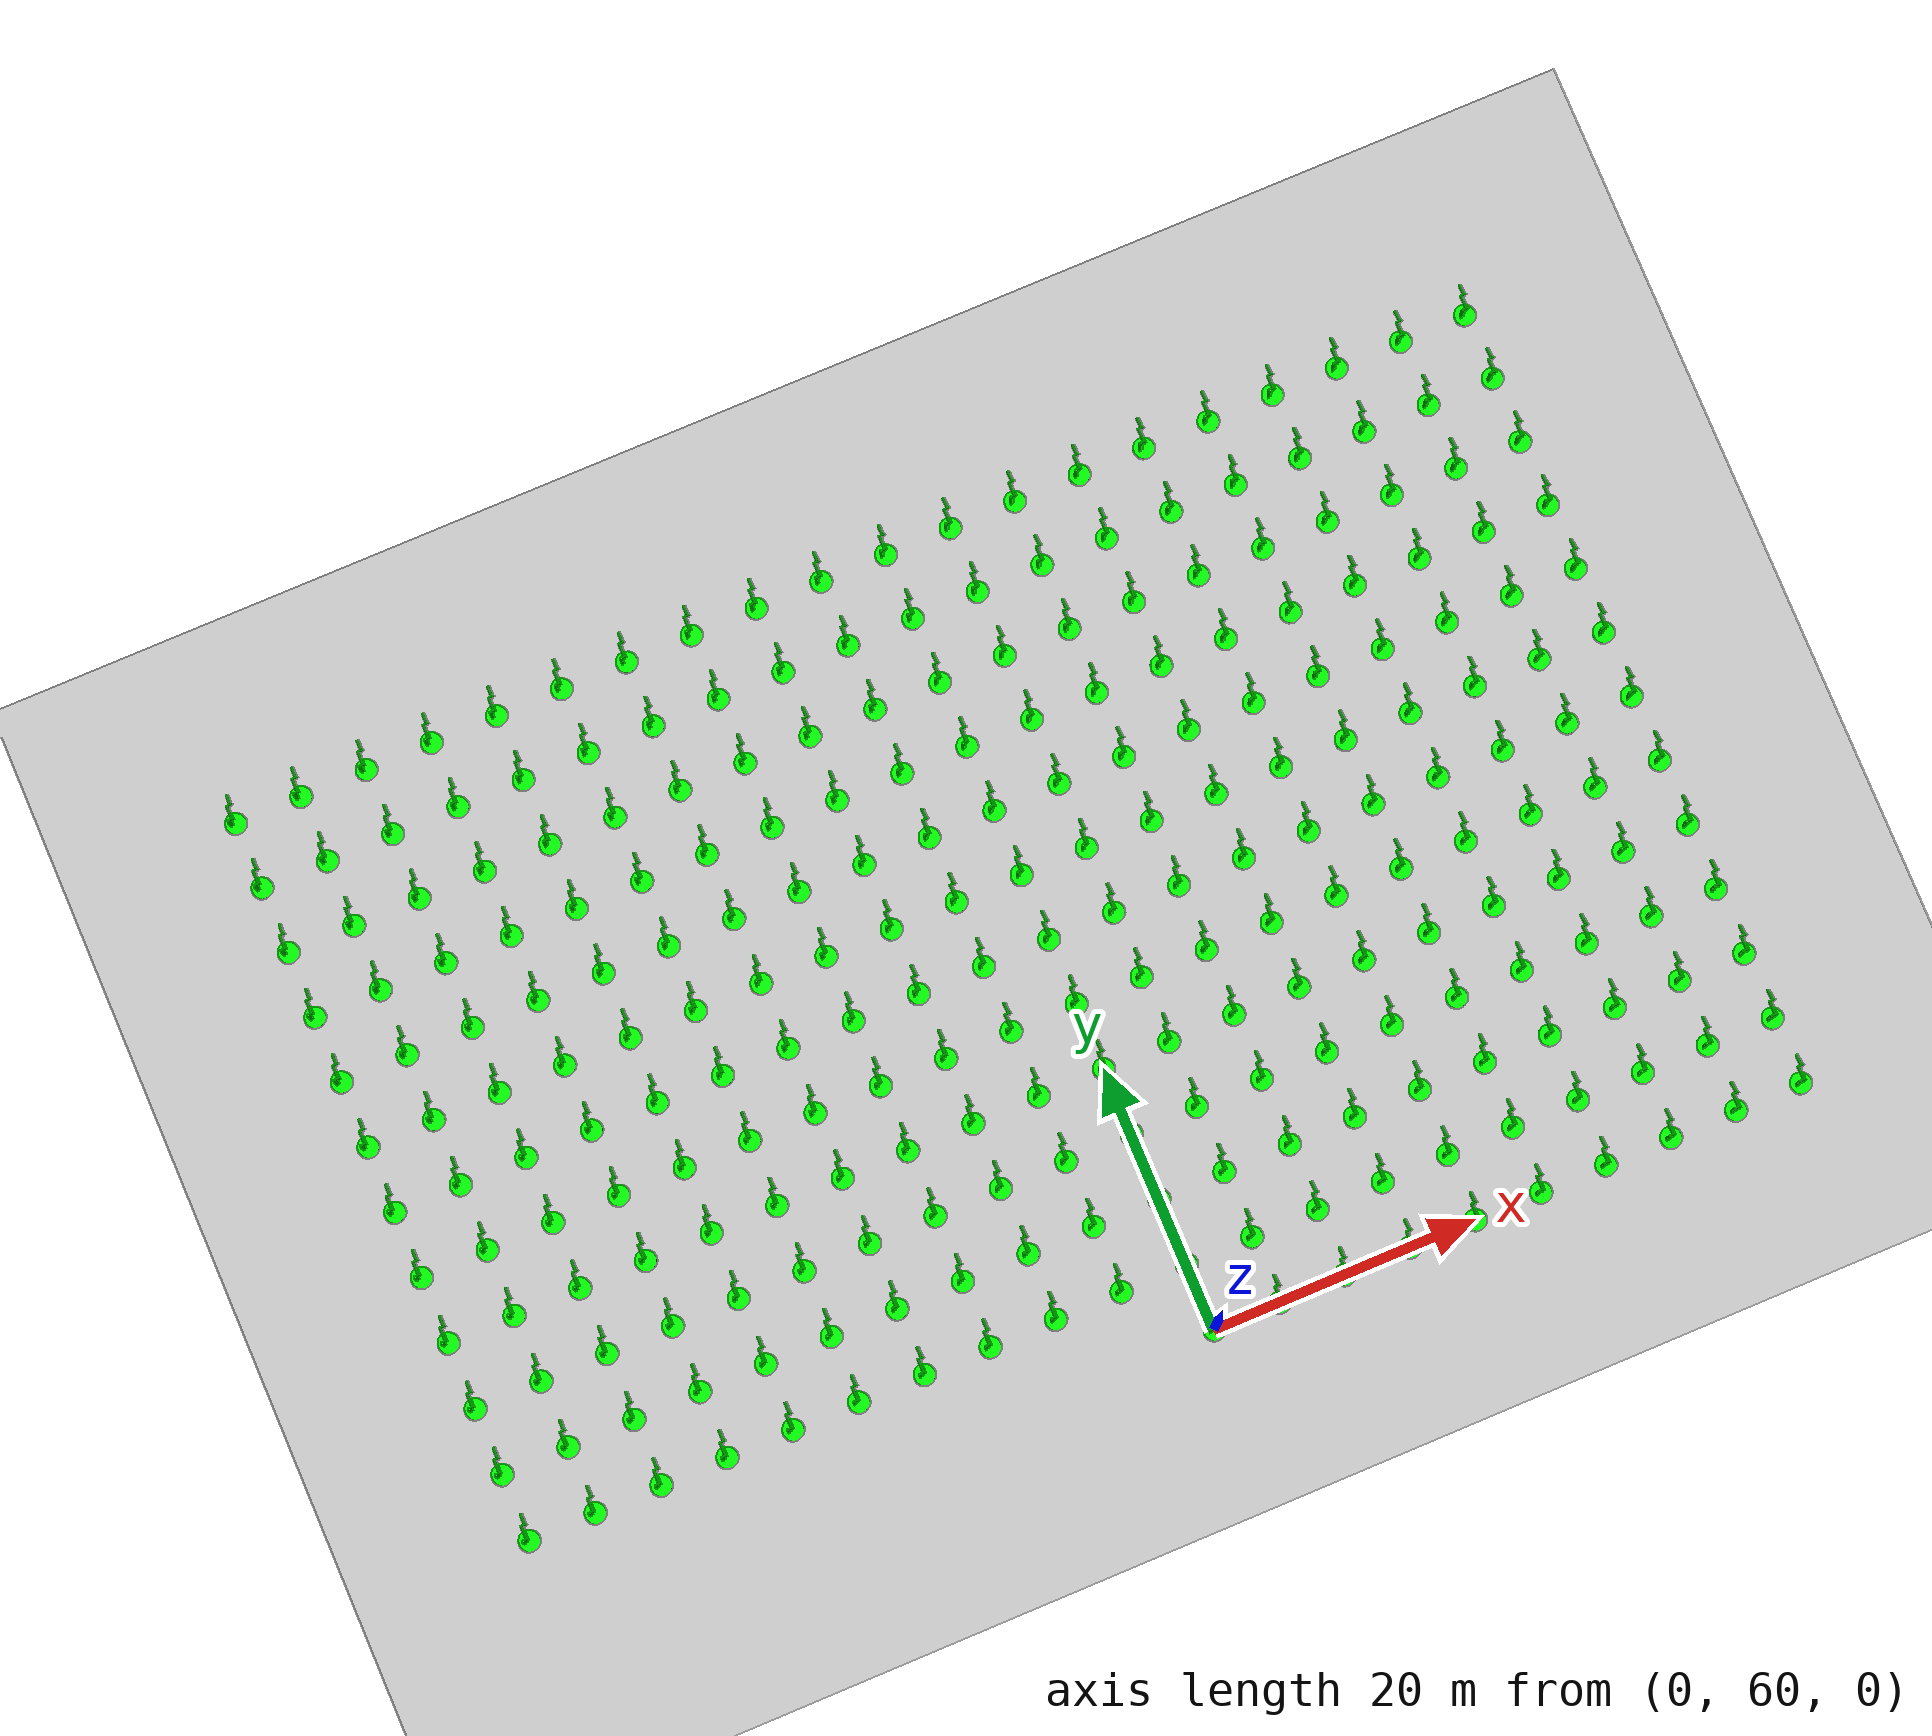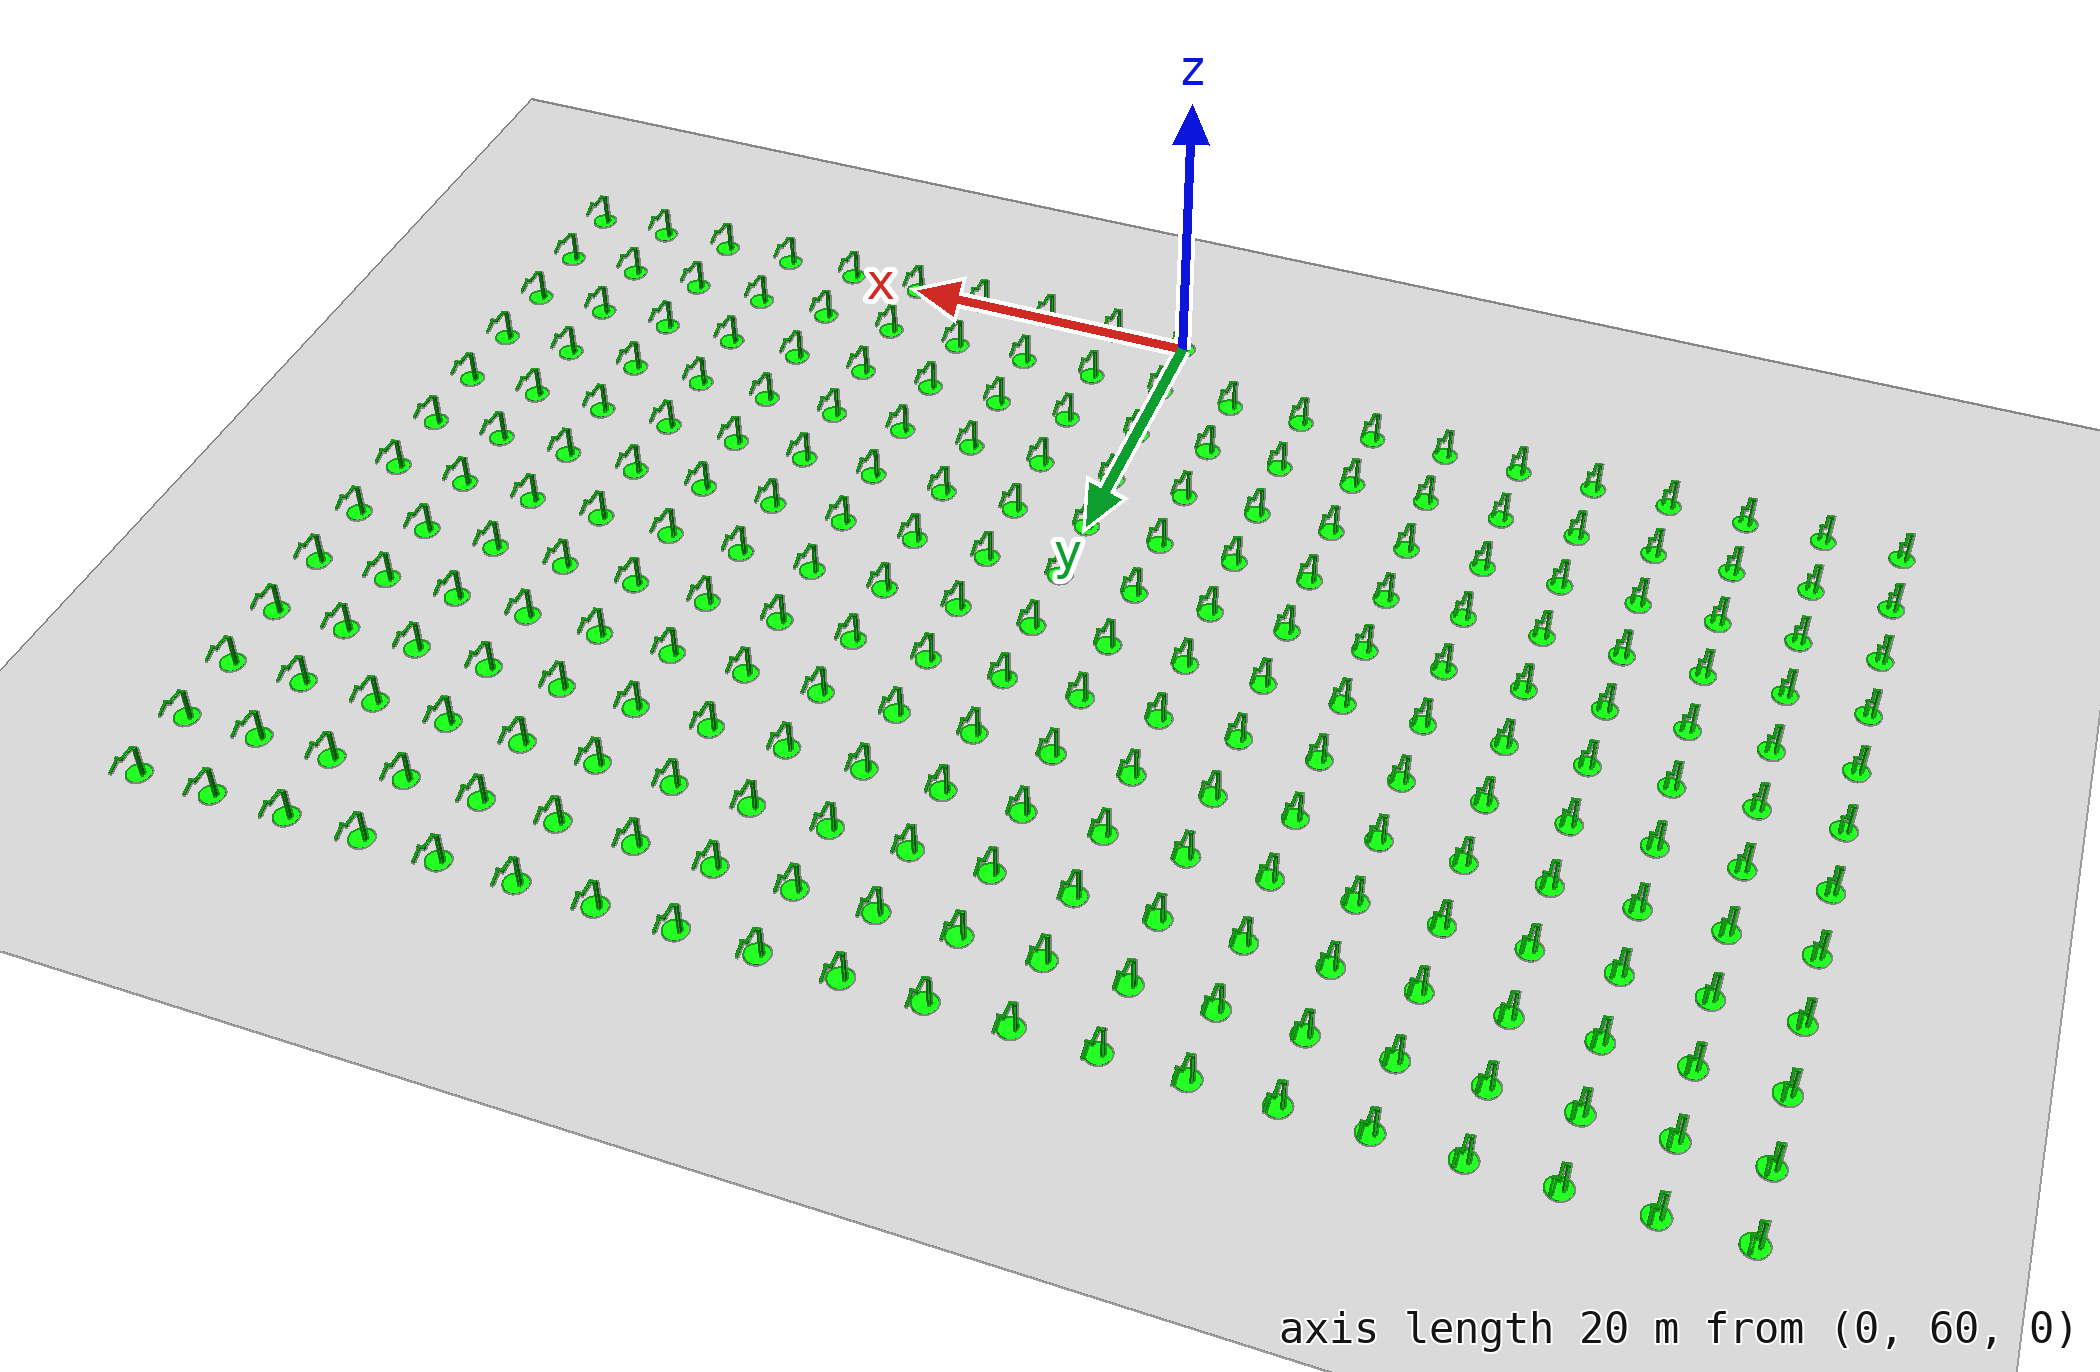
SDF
<sdf version="1.6">
 <world name="double_pendulums">
  <model name="ground_plane">
   <static>true</static>
   <link name="link">
    <collision name="collision">
     <geometry><plane><normal>0 0 1</normal><size>100 100</size></plane></geometry>
    </collision>
    <visual name="visual">
     <geometry><plane><normal>0 0 1</normal><size>100 100</size></plane></geometry>
     <material>
      <ambient>0.8 0.8 0.8 1</ambient>
      <diffuse>0.8 0.8 0.8 1</diffuse>
      <specular>0.8 0.8 0.8 1</specular>
     </material>
    </visual>
   </link>
  </model>
  <model name="dbl_pendulum_310">
   <pose>0 60 0 0 0 0</pose>
   <link name="base">
    <inertial><mass>100</mass></inertial>
    <visual name="vis_plate_on_ground">
     <pose>0 0 0.01 0 0 0</pose>
     <geometry><cylinder><radius>0.8</radius><length>0.02</length></cylinder></geometry>
     <material><ambient>0 1 0 1</ambient><diffuse>0 1 0 1</diffuse><specular>0 1 0 1</specular></material>
    </visual>
    <visual name="vis_pole">
     <pose>-0.275 0 1.1 0 0 0</pose>
     <geometry><box><size>0.2 0.2 2.2</size></box></geometry>
     <material><ambient>0 1 0 1</ambient><diffuse>0 1 0 1</diffuse><specular>0 1 0 1</specular></material>
    </visual>
    <collision name="col_plate_on_ground">
     <pose>0 0 0.01 0 0 0</pose>
     <geometry><cylinder><radius>0.8</radius><length>0.02</length></cylinder></geometry>
    </collision>
    <collision name="col_pole">
     <pose>-0.275 0 1.1 0 0 0</pose>
     <geometry><box><size>0.2 0.2 2.2</size></box></geometry>
    </collision>
   </link>
   <link name="upper_link">
    <pose>0 0 2.1 -1.5708 0 0</pose>
    <inertial><pose>0 0 0.5 0 0 0</pose></inertial>
    <visual name="vis_upper_joint">
     <pose>-0.05 0 0 0 1.5708 0</pose>
     <geometry><cylinder><radius>0.1</radius><length>0.3</length></cylinder></geometry>
     <material><ambient>0 1 0 1</ambient><diffuse>0 1 0 1</diffuse><specular>0 1 0 1</specular></material>
    </visual>
    <visual name="vis_lower_joint">
     <pose>0 0 1.0 0 1.5708 0</pose>
     <geometry><cylinder><radius>0.1</radius><length>0.2</length></cylinder></geometry>
     <material><ambient>0 1 0 1</ambient><diffuse>0 1 0 1</diffuse><specular>0 1 0 1</specular></material>
    </visual>
    <visual name="vis_cylinder">
     <pose>0 0 0.5 0 0 0</pose>
     <geometry><cylinder><radius>0.1</radius><length>0.9</length></cylinder></geometry>
     <material><ambient>0 1 0 1</ambient><diffuse>0 1 0 1</diffuse><specular>0 1 0 1</specular></material>
    </visual>
    <collision name="col_upper_joint">
     <pose>-0.05 0 0 0 1.5708 0</pose>
     <geometry><cylinder><radius>0.1</radius><length>0.3</length></cylinder></geometry>
    </collision>
    <collision name="col_lower_joint">
     <pose>0 0 1.0 0 1.5708 0</pose>
     <geometry><cylinder><radius>0.1</radius><length>0.2</length></cylinder></geometry>
    </collision>
    <collision name="col_cylinder">
     <pose>0 0 0.5 0 0 0</pose>
     <geometry><cylinder><radius>0.1</radius><length>0.9</length></cylinder></geometry>
    </collision>
   </link>
   <link name="lower_link">
    <pose>0.25 1.0 2.1 -2 0 0</pose>
    <inertial><pose>0 0 0.5 0 0 0</pose></inertial>
    <visual name="vis_lower_joint">
     <pose>0 0 0 0 1.5708 0</pose>
     <geometry><cylinder><radius>0.08</radius><length>0.3</length></cylinder></geometry>
     <material><ambient>0 1 0 1</ambient><diffuse>0 1 0 1</diffuse><specular>0 1 0 1</specular></material>
    </visual>
    <visual name="vis_cylinder">
     <pose>0 0 0.5 0 0 0</pose>
     <geometry><cylinder><radius>0.1</radius><length>0.9</length></cylinder></geometry>
     <material><ambient>0 1 0 1</ambient><diffuse>0 1 0 1</diffuse><specular>0 1 0 1</specular></material>
    </visual>
    <collision name="col_lower_joint">
     <pose>0 0 0 0 1.5708 0</pose>
     <geometry><cylinder><radius>0.08</radius><length>0.3</length></cylinder></geometry>
    </collision>
    <collision name="col_cylinder">
     <pose>0 0 0.5 0 0 0</pose>
     <geometry><cylinder><radius>0.1</radius><length>0.9</length></cylinder></geometry>
    </collision>
   </link>
   <joint name="upper_joint" type="revolute">
    <parent>base</parent>
    <child>upper_link</child>
    <axis><xyz>1.0 0 0</xyz></axis>
   </joint>
   <joint name="lower_joint" type="revolute">
    <parent>upper_link</parent>
    <child>lower_link</child>
    <axis><xyz>1.0 0 0</xyz></axis>
   </joint>
  </model>
  <model name="dbl_pendulum_311">
   <pose>5 60 0 0 0 0</pose>
   <link name="base">
    <inertial><mass>100</mass></inertial>
    <visual name="vis_plate_on_ground">
     <pose>0 0 0.01 0 0 0</pose>
     <geometry><cylinder><radius>0.8</radius><length>0.02</length></cylinder></geometry>
     <material><ambient>0 1 0 1</ambient><diffuse>0 1 0 1</diffuse><specular>0 1 0 1</specular></material>
    </visual>
    <visual name="vis_pole">
     <pose>-0.275 0 1.1 0 0 0</pose>
     <geometry><box><size>0.2 0.2 2.2</size></box></geometry>
     <material><ambient>0 1 0 1</ambient><diffuse>0 1 0 1</diffuse><specular>0 1 0 1</specular></material>
    </visual>
    <collision name="col_plate_on_ground">
     <pose>0 0 0.01 0 0 0</pose>
     <geometry><cylinder><radius>0.8</radius><length>0.02</length></cylinder></geometry>
    </collision>
    <collision name="col_pole">
     <pose>-0.275 0 1.1 0 0 0</pose>
     <geometry><box><size>0.2 0.2 2.2</size></box></geometry>
    </collision>
   </link>
   <link name="upper_link">
    <pose>0 0 2.1 -1.5708 0 0</pose>
    <inertial><pose>0 0 0.5 0 0 0</pose></inertial>
    <visual name="vis_upper_joint">
     <pose>-0.05 0 0 0 1.5708 0</pose>
     <geometry><cylinder><radius>0.1</radius><length>0.3</length></cylinder></geometry>
     <material><ambient>0 1 0 1</ambient><diffuse>0 1 0 1</diffuse><specular>0 1 0 1</specular></material>
    </visual>
    <visual name="vis_lower_joint">
     <pose>0 0 1.0 0 1.5708 0</pose>
     <geometry><cylinder><radius>0.1</radius><length>0.2</length></cylinder></geometry>
     <material><ambient>0 1 0 1</ambient><diffuse>0 1 0 1</diffuse><specular>0 1 0 1</specular></material>
    </visual>
    <visual name="vis_cylinder">
     <pose>0 0 0.5 0 0 0</pose>
     <geometry><cylinder><radius>0.1</radius><length>0.9</length></cylinder></geometry>
     <material><ambient>0 1 0 1</ambient><diffuse>0 1 0 1</diffuse><specular>0 1 0 1</specular></material>
    </visual>
    <collision name="col_upper_joint">
     <pose>-0.05 0 0 0 1.5708 0</pose>
     <geometry><cylinder><radius>0.1</radius><length>0.3</length></cylinder></geometry>
    </collision>
    <collision name="col_lower_joint">
     <pose>0 0 1.0 0 1.5708 0</pose>
     <geometry><cylinder><radius>0.1</radius><length>0.2</length></cylinder></geometry>
    </collision>
    <collision name="col_cylinder">
     <pose>0 0 0.5 0 0 0</pose>
     <geometry><cylinder><radius>0.1</radius><length>0.9</length></cylinder></geometry>
    </collision>
   </link>
   <link name="lower_link">
    <pose>0.25 1.0 2.1 -2 0 0</pose>
    <inertial><pose>0 0 0.5 0 0 0</pose></inertial>
    <visual name="vis_lower_joint">
     <pose>0 0 0 0 1.5708 0</pose>
     <geometry><cylinder><radius>0.08</radius><length>0.3</length></cylinder></geometry>
     <material><ambient>0 1 0 1</ambient><diffuse>0 1 0 1</diffuse><specular>0 1 0 1</specular></material>
    </visual>
    <visual name="vis_cylinder">
     <pose>0 0 0.5 0 0 0</pose>
     <geometry><cylinder><radius>0.1</radius><length>0.9</length></cylinder></geometry>
     <material><ambient>0 1 0 1</ambient><diffuse>0 1 0 1</diffuse><specular>0 1 0 1</specular></material>
    </visual>
    <collision name="col_lower_joint">
     <pose>0 0 0 0 1.5708 0</pose>
     <geometry><cylinder><radius>0.08</radius><length>0.3</length></cylinder></geometry>
    </collision>
    <collision name="col_cylinder">
     <pose>0 0 0.5 0 0 0</pose>
     <geometry><cylinder><radius>0.1</radius><length>0.9</length></cylinder></geometry>
    </collision>
   </link>
   <joint name="upper_joint" type="revolute">
    <parent>base</parent>
    <child>upper_link</child>
    <axis><xyz>1.0 0 0</xyz></axis>
   </joint>
   <joint name="lower_joint" type="revolute">
    <parent>upper_link</parent>
    <child>lower_link</child>
    <axis><xyz>1.0 0 0</xyz></axis>
   </joint>
  </model>
  <model name="dbl_pendulum_312">
   <pose>10 60 0 0 0 0</pose>
   <link name="base">
    <inertial><mass>100</mass></inertial>
    <visual name="vis_plate_on_ground">
     <pose>0 0 0.01 0 0 0</pose>
     <geometry><cylinder><radius>0.8</radius><length>0.02</length></cylinder></geometry>
     <material><ambient>0 1 0 1</ambient><diffuse>0 1 0 1</diffuse><specular>0 1 0 1</specular></material>
    </visual>
    <visual name="vis_pole">
     <pose>-0.275 0 1.1 0 0 0</pose>
     <geometry><box><size>0.2 0.2 2.2</size></box></geometry>
     <material><ambient>0 1 0 1</ambient><diffuse>0 1 0 1</diffuse><specular>0 1 0 1</specular></material>
    </visual>
    <collision name="col_plate_on_ground">
     <pose>0 0 0.01 0 0 0</pose>
     <geometry><cylinder><radius>0.8</radius><length>0.02</length></cylinder></geometry>
    </collision>
    <collision name="col_pole">
     <pose>-0.275 0 1.1 0 0 0</pose>
     <geometry><box><size>0.2 0.2 2.2</size></box></geometry>
    </collision>
   </link>
   <link name="upper_link">
    <pose>0 0 2.1 -1.5708 0 0</pose>
    <inertial><pose>0 0 0.5 0 0 0</pose></inertial>
    <visual name="vis_upper_joint">
     <pose>-0.05 0 0 0 1.5708 0</pose>
     <geometry><cylinder><radius>0.1</radius><length>0.3</length></cylinder></geometry>
     <material><ambient>0 1 0 1</ambient><diffuse>0 1 0 1</diffuse><specular>0 1 0 1</specular></material>
    </visual>
    <visual name="vis_lower_joint">
     <pose>0 0 1.0 0 1.5708 0</pose>
     <geometry><cylinder><radius>0.1</radius><length>0.2</length></cylinder></geometry>
     <material><ambient>0 1 0 1</ambient><diffuse>0 1 0 1</diffuse><specular>0 1 0 1</specular></material>
    </visual>
    <visual name="vis_cylinder">
     <pose>0 0 0.5 0 0 0</pose>
     <geometry><cylinder><radius>0.1</radius><length>0.9</length></cylinder></geometry>
     <material><ambient>0 1 0 1</ambient><diffuse>0 1 0 1</diffuse><specular>0 1 0 1</specular></material>
    </visual>
    <collision name="col_upper_joint">
     <pose>-0.05 0 0 0 1.5708 0</pose>
     <geometry><cylinder><radius>0.1</radius><length>0.3</length></cylinder></geometry>
    </collision>
    <collision name="col_lower_joint">
     <pose>0 0 1.0 0 1.5708 0</pose>
     <geometry><cylinder><radius>0.1</radius><length>0.2</length></cylinder></geometry>
    </collision>
    <collision name="col_cylinder">
     <pose>0 0 0.5 0 0 0</pose>
     <geometry><cylinder><radius>0.1</radius><length>0.9</length></cylinder></geometry>
    </collision>
   </link>
   <link name="lower_link">
    <pose>0.25 1.0 2.1 -2 0 0</pose>
    <inertial><pose>0 0 0.5 0 0 0</pose></inertial>
    <visual name="vis_lower_joint">
     <pose>0 0 0 0 1.5708 0</pose>
     <geometry><cylinder><radius>0.08</radius><length>0.3</length></cylinder></geometry>
     <material><ambient>0 1 0 1</ambient><diffuse>0 1 0 1</diffuse><specular>0 1 0 1</specular></material>
    </visual>
    <visual name="vis_cylinder">
     <pose>0 0 0.5 0 0 0</pose>
     <geometry><cylinder><radius>0.1</radius><length>0.9</length></cylinder></geometry>
     <material><ambient>0 1 0 1</ambient><diffuse>0 1 0 1</diffuse><specular>0 1 0 1</specular></material>
    </visual>
    <collision name="col_lower_joint">
     <pose>0 0 0 0 1.5708 0</pose>
     <geometry><cylinder><radius>0.08</radius><length>0.3</length></cylinder></geometry>
    </collision>
    <collision name="col_cylinder">
     <pose>0 0 0.5 0 0 0</pose>
     <geometry><cylinder><radius>0.1</radius><length>0.9</length></cylinder></geometry>
    </collision>
   </link>
   <joint name="upper_joint" type="revolute">
    <parent>base</parent>
    <child>upper_link</child>
    <axis><xyz>1.0 0 0</xyz></axis>
   </joint>
   <joint name="lower_joint" type="revolute">
    <parent>upper_link</parent>
    <child>lower_link</child>
    <axis><xyz>1.0 0 0</xyz></axis>
   </joint>
  </model>
  <model name="dbl_pendulum_313">
   <pose>15 60 0 0 0 0</pose>
   <link name="base">
    <inertial><mass>100</mass></inertial>
    <visual name="vis_plate_on_ground">
     <pose>0 0 0.01 0 0 0</pose>
     <geometry><cylinder><radius>0.8</radius><length>0.02</length></cylinder></geometry>
     <material><ambient>0 1 0 1</ambient><diffuse>0 1 0 1</diffuse><specular>0 1 0 1</specular></material>
    </visual>
    <visual name="vis_pole">
     <pose>-0.275 0 1.1 0 0 0</pose>
     <geometry><box><size>0.2 0.2 2.2</size></box></geometry>
     <material><ambient>0 1 0 1</ambient><diffuse>0 1 0 1</diffuse><specular>0 1 0 1</specular></material>
    </visual>
    <collision name="col_plate_on_ground">
     <pose>0 0 0.01 0 0 0</pose>
     <geometry><cylinder><radius>0.8</radius><length>0.02</length></cylinder></geometry>
    </collision>
    <collision name="col_pole">
     <pose>-0.275 0 1.1 0 0 0</pose>
     <geometry><box><size>0.2 0.2 2.2</size></box></geometry>
    </collision>
   </link>
   <link name="upper_link">
    <pose>0 0 2.1 -1.5708 0 0</pose>
    <inertial><pose>0 0 0.5 0 0 0</pose></inertial>
    <visual name="vis_upper_joint">
     <pose>-0.05 0 0 0 1.5708 0</pose>
     <geometry><cylinder><radius>0.1</radius><length>0.3</length></cylinder></geometry>
     <material><ambient>0 1 0 1</ambient><diffuse>0 1 0 1</diffuse><specular>0 1 0 1</specular></material>
    </visual>
    <visual name="vis_lower_joint">
     <pose>0 0 1.0 0 1.5708 0</pose>
     <geometry><cylinder><radius>0.1</radius><length>0.2</length></cylinder></geometry>
     <material><ambient>0 1 0 1</ambient><diffuse>0 1 0 1</diffuse><specular>0 1 0 1</specular></material>
    </visual>
    <visual name="vis_cylinder">
     <pose>0 0 0.5 0 0 0</pose>
     <geometry><cylinder><radius>0.1</radius><length>0.9</length></cylinder></geometry>
     <material><ambient>0 1 0 1</ambient><diffuse>0 1 0 1</diffuse><specular>0 1 0 1</specular></material>
    </visual>
    <collision name="col_upper_joint">
     <pose>-0.05 0 0 0 1.5708 0</pose>
     <geometry><cylinder><radius>0.1</radius><length>0.3</length></cylinder></geometry>
    </collision>
    <collision name="col_lower_joint">
     <pose>0 0 1.0 0 1.5708 0</pose>
     <geometry><cylinder><radius>0.1</radius><length>0.2</length></cylinder></geometry>
    </collision>
    <collision name="col_cylinder">
     <pose>0 0 0.5 0 0 0</pose>
     <geometry><cylinder><radius>0.1</radius><length>0.9</length></cylinder></geometry>
    </collision>
   </link>
   <link name="lower_link">
    <pose>0.25 1.0 2.1 -2 0 0</pose>
    <inertial><pose>0 0 0.5 0 0 0</pose></inertial>
    <visual name="vis_lower_joint">
     <pose>0 0 0 0 1.5708 0</pose>
     <geometry><cylinder><radius>0.08</radius><length>0.3</length></cylinder></geometry>
     <material><ambient>0 1 0 1</ambient><diffuse>0 1 0 1</diffuse><specular>0 1 0 1</specular></material>
    </visual>
    <visual name="vis_cylinder">
     <pose>0 0 0.5 0 0 0</pose>
     <geometry><cylinder><radius>0.1</radius><length>0.9</length></cylinder></geometry>
     <material><ambient>0 1 0 1</ambient><diffuse>0 1 0 1</diffuse><specular>0 1 0 1</specular></material>
    </visual>
    <collision name="col_lower_joint">
     <pose>0 0 0 0 1.5708 0</pose>
     <geometry><cylinder><radius>0.08</radius><length>0.3</length></cylinder></geometry>
    </collision>
    <collision name="col_cylinder">
     <pose>0 0 0.5 0 0 0</pose>
     <geometry><cylinder><radius>0.1</radius><length>0.9</length></cylinder></geometry>
    </collision>
   </link>
   <joint name="upper_joint" type="revolute">
    <parent>base</parent>
    <child>upper_link</child>
    <axis><xyz>1.0 0 0</xyz></axis>
   </joint>
   <joint name="lower_joint" type="revolute">
    <parent>upper_link</parent>
    <child>lower_link</child>
    <axis><xyz>1.0 0 0</xyz></axis>
   </joint>
  </model>
  <model name="dbl_pendulum_314">
   <pose>20 60 0 0 0 0</pose>
   <link name="base">
    <inertial><mass>100</mass></inertial>
    <visual name="vis_plate_on_ground">
     <pose>0 0 0.01 0 0 0</pose>
     <geometry><cylinder><radius>0.8</radius><length>0.02</length></cylinder></geometry>
     <material><ambient>0 1 0 1</ambient><diffuse>0 1 0 1</diffuse><specular>0 1 0 1</specular></material>
    </visual>
    <visual name="vis_pole">
     <pose>-0.275 0 1.1 0 0 0</pose>
     <geometry><box><size>0.2 0.2 2.2</size></box></geometry>
     <material><ambient>0 1 0 1</ambient><diffuse>0 1 0 1</diffuse><specular>0 1 0 1</specular></material>
    </visual>
    <collision name="col_plate_on_ground">
     <pose>0 0 0.01 0 0 0</pose>
     <geometry><cylinder><radius>0.8</radius><length>0.02</length></cylinder></geometry>
    </collision>
    <collision name="col_pole">
     <pose>-0.275 0 1.1 0 0 0</pose>
     <geometry><box><size>0.2 0.2 2.2</size></box></geometry>
    </collision>
   </link>
   <link name="upper_link">
    <pose>0 0 2.1 -1.5708 0 0</pose>
    <inertial><pose>0 0 0.5 0 0 0</pose></inertial>
    <visual name="vis_upper_joint">
     <pose>-0.05 0 0 0 1.5708 0</pose>
     <geometry><cylinder><radius>0.1</radius><length>0.3</length></cylinder></geometry>
     <material><ambient>0 1 0 1</ambient><diffuse>0 1 0 1</diffuse><specular>0 1 0 1</specular></material>
    </visual>
    <visual name="vis_lower_joint">
     <pose>0 0 1.0 0 1.5708 0</pose>
     <geometry><cylinder><radius>0.1</radius><length>0.2</length></cylinder></geometry>
     <material><ambient>0 1 0 1</ambient><diffuse>0 1 0 1</diffuse><specular>0 1 0 1</specular></material>
    </visual>
    <visual name="vis_cylinder">
     <pose>0 0 0.5 0 0 0</pose>
     <geometry><cylinder><radius>0.1</radius><length>0.9</length></cylinder></geometry>
     <material><ambient>0 1 0 1</ambient><diffuse>0 1 0 1</diffuse><specular>0 1 0 1</specular></material>
    </visual>
    <collision name="col_upper_joint">
     <pose>-0.05 0 0 0 1.5708 0</pose>
     <geometry><cylinder><radius>0.1</radius><length>0.3</length></cylinder></geometry>
    </collision>
    <collision name="col_lower_joint">
     <pose>0 0 1.0 0 1.5708 0</pose>
     <geometry><cylinder><radius>0.1</radius><length>0.2</length></cylinder></geometry>
    </collision>
    <collision name="col_cylinder">
     <pose>0 0 0.5 0 0 0</pose>
     <geometry><cylinder><radius>0.1</radius><length>0.9</length></cylinder></geometry>
    </collision>
   </link>
   <link name="lower_link">
    <pose>0.25 1.0 2.1 -2 0 0</pose>
    <inertial><pose>0 0 0.5 0 0 0</pose></inertial>
    <visual name="vis_lower_joint">
     <pose>0 0 0 0 1.5708 0</pose>
     <geometry><cylinder><radius>0.08</radius><length>0.3</length></cylinder></geometry>
     <material><ambient>0 1 0 1</ambient><diffuse>0 1 0 1</diffuse><specular>0 1 0 1</specular></material>
    </visual>
    <visual name="vis_cylinder">
     <pose>0 0 0.5 0 0 0</pose>
     <geometry><cylinder><radius>0.1</radius><length>0.9</length></cylinder></geometry>
     <material><ambient>0 1 0 1</ambient><diffuse>0 1 0 1</diffuse><specular>0 1 0 1</specular></material>
    </visual>
    <collision name="col_lower_joint">
     <pose>0 0 0 0 1.5708 0</pose>
     <geometry><cylinder><radius>0.08</radius><length>0.3</length></cylinder></geometry>
    </collision>
    <collision name="col_cylinder">
     <pose>0 0 0.5 0 0 0</pose>
     <geometry><cylinder><radius>0.1</radius><length>0.9</length></cylinder></geometry>
    </collision>
   </link>
   <joint name="upper_joint" type="revolute">
    <parent>base</parent>
    <child>upper_link</child>
    <axis><xyz>1.0 0 0</xyz></axis>
   </joint>
   <joint name="lower_joint" type="revolute">
    <parent>upper_link</parent>
    <child>lower_link</child>
    <axis><xyz>1.0 0 0</xyz></axis>
   </joint>
  </model>
  <model name="dbl_pendulum_315">
   <pose>25 60 0 0 0 0</pose>
   <link name="base">
    <inertial><mass>100</mass></inertial>
    <visual name="vis_plate_on_ground">
     <pose>0 0 0.01 0 0 0</pose>
     <geometry><cylinder><radius>0.8</radius><length>0.02</length></cylinder></geometry>
     <material><ambient>0 1 0 1</ambient><diffuse>0 1 0 1</diffuse><specular>0 1 0 1</specular></material>
    </visual>
    <visual name="vis_pole">
     <pose>-0.275 0 1.1 0 0 0</pose>
     <geometry><box><size>0.2 0.2 2.2</size></box></geometry>
     <material><ambient>0 1 0 1</ambient><diffuse>0 1 0 1</diffuse><specular>0 1 0 1</specular></material>
    </visual>
    <collision name="col_plate_on_ground">
     <pose>0 0 0.01 0 0 0</pose>
     <geometry><cylinder><radius>0.8</radius><length>0.02</length></cylinder></geometry>
    </collision>
    <collision name="col_pole">
     <pose>-0.275 0 1.1 0 0 0</pose>
     <geometry><box><size>0.2 0.2 2.2</size></box></geometry>
    </collision>
   </link>
   <link name="upper_link">
    <pose>0 0 2.1 -1.5708 0 0</pose>
    <inertial><pose>0 0 0.5 0 0 0</pose></inertial>
    <visual name="vis_upper_joint">
     <pose>-0.05 0 0 0 1.5708 0</pose>
     <geometry><cylinder><radius>0.1</radius><length>0.3</length></cylinder></geometry>
     <material><ambient>0 1 0 1</ambient><diffuse>0 1 0 1</diffuse><specular>0 1 0 1</specular></material>
    </visual>
    <visual name="vis_lower_joint">
     <pose>0 0 1.0 0 1.5708 0</pose>
     <geometry><cylinder><radius>0.1</radius><length>0.2</length></cylinder></geometry>
     <material><ambient>0 1 0 1</ambient><diffuse>0 1 0 1</diffuse><specular>0 1 0 1</specular></material>
    </visual>
    <visual name="vis_cylinder">
     <pose>0 0 0.5 0 0 0</pose>
     <geometry><cylinder><radius>0.1</radius><length>0.9</length></cylinder></geometry>
     <material><ambient>0 1 0 1</ambient><diffuse>0 1 0 1</diffuse><specular>0 1 0 1</specular></material>
    </visual>
    <collision name="col_upper_joint">
     <pose>-0.05 0 0 0 1.5708 0</pose>
     <geometry><cylinder><radius>0.1</radius><length>0.3</length></cylinder></geometry>
    </collision>
    <collision name="col_lower_joint">
     <pose>0 0 1.0 0 1.5708 0</pose>
     <geometry><cylinder><radius>0.1</radius><length>0.2</length></cylinder></geometry>
    </collision>
    <collision name="col_cylinder">
     <pose>0 0 0.5 0 0 0</pose>
     <geometry><cylinder><radius>0.1</radius><length>0.9</length></cylinder></geometry>
    </collision>
   </link>
   <link name="lower_link">
    <pose>0.25 1.0 2.1 -2 0 0</pose>
    <inertial><pose>0 0 0.5 0 0 0</pose></inertial>
    <visual name="vis_lower_joint">
     <pose>0 0 0 0 1.5708 0</pose>
     <geometry><cylinder><radius>0.08</radius><length>0.3</length></cylinder></geometry>
     <material><ambient>0 1 0 1</ambient><diffuse>0 1 0 1</diffuse><specular>0 1 0 1</specular></material>
    </visual>
    <visual name="vis_cylinder">
     <pose>0 0 0.5 0 0 0</pose>
     <geometry><cylinder><radius>0.1</radius><length>0.9</length></cylinder></geometry>
     <material><ambient>0 1 0 1</ambient><diffuse>0 1 0 1</diffuse><specular>0 1 0 1</specular></material>
    </visual>
    <collision name="col_lower_joint">
     <pose>0 0 0 0 1.5708 0</pose>
     <geometry><cylinder><radius>0.08</radius><length>0.3</length></cylinder></geometry>
    </collision>
    <collision name="col_cylinder">
     <pose>0 0 0.5 0 0 0</pose>
     <geometry><cylinder><radius>0.1</radius><length>0.9</length></cylinder></geometry>
    </collision>
   </link>
   <joint name="upper_joint" type="revolute">
    <parent>base</parent>
    <child>upper_link</child>
    <axis><xyz>1.0 0 0</xyz></axis>
   </joint>
   <joint name="lower_joint" type="revolute">
    <parent>upper_link</parent>
    <child>lower_link</child>
    <axis><xyz>1.0 0 0</xyz></axis>
   </joint>
  </model>
  <model name="dbl_pendulum_316">
   <pose>30 60 0 0 0 0</pose>
   <link name="base">
    <inertial><mass>100</mass></inertial>
    <visual name="vis_plate_on_ground">
     <pose>0 0 0.01 0 0 0</pose>
     <geometry><cylinder><radius>0.8</radius><length>0.02</length></cylinder></geometry>
     <material><ambient>0 1 0 1</ambient><diffuse>0 1 0 1</diffuse><specular>0 1 0 1</specular></material>
    </visual>
    <visual name="vis_pole">
     <pose>-0.275 0 1.1 0 0 0</pose>
     <geometry><box><size>0.2 0.2 2.2</size></box></geometry>
     <material><ambient>0 1 0 1</ambient><diffuse>0 1 0 1</diffuse><specular>0 1 0 1</specular></material>
    </visual>
    <collision name="col_plate_on_ground">
     <pose>0 0 0.01 0 0 0</pose>
     <geometry><cylinder><radius>0.8</radius><length>0.02</length></cylinder></geometry>
    </collision>
    <collision name="col_pole">
     <pose>-0.275 0 1.1 0 0 0</pose>
     <geometry><box><size>0.2 0.2 2.2</size></box></geometry>
    </collision>
   </link>
   <link name="upper_link">
    <pose>0 0 2.1 -1.5708 0 0</pose>
    <inertial><pose>0 0 0.5 0 0 0</pose></inertial>
    <visual name="vis_upper_joint">
     <pose>-0.05 0 0 0 1.5708 0</pose>
     <geometry><cylinder><radius>0.1</radius><length>0.3</length></cylinder></geometry>
     <material><ambient>0 1 0 1</ambient><diffuse>0 1 0 1</diffuse><specular>0 1 0 1</specular></material>
    </visual>
    <visual name="vis_lower_joint">
     <pose>0 0 1.0 0 1.5708 0</pose>
     <geometry><cylinder><radius>0.1</radius><length>0.2</length></cylinder></geometry>
     <material><ambient>0 1 0 1</ambient><diffuse>0 1 0 1</diffuse><specular>0 1 0 1</specular></material>
    </visual>
    <visual name="vis_cylinder">
     <pose>0 0 0.5 0 0 0</pose>
     <geometry><cylinder><radius>0.1</radius><length>0.9</length></cylinder></geometry>
     <material><ambient>0 1 0 1</ambient><diffuse>0 1 0 1</diffuse><specular>0 1 0 1</specular></material>
    </visual>
    <collision name="col_upper_joint">
     <pose>-0.05 0 0 0 1.5708 0</pose>
     <geometry><cylinder><radius>0.1</radius><length>0.3</length></cylinder></geometry>
    </collision>
    <collision name="col_lower_joint">
     <pose>0 0 1.0 0 1.5708 0</pose>
     <geometry><cylinder><radius>0.1</radius><length>0.2</length></cylinder></geometry>
    </collision>
    <collision name="col_cylinder">
     <pose>0 0 0.5 0 0 0</pose>
     <geometry><cylinder><radius>0.1</radius><length>0.9</length></cylinder></geometry>
    </collision>
   </link>
   <link name="lower_link">
    <pose>0.25 1.0 2.1 -2 0 0</pose>
    <inertial><pose>0 0 0.5 0 0 0</pose></inertial>
    <visual name="vis_lower_joint">
     <pose>0 0 0 0 1.5708 0</pose>
     <geometry><cylinder><radius>0.08</radius><length>0.3</length></cylinder></geometry>
     <material><ambient>0 1 0 1</ambient><diffuse>0 1 0 1</diffuse><specular>0 1 0 1</specular></material>
    </visual>
    <visual name="vis_cylinder">
     <pose>0 0 0.5 0 0 0</pose>
     <geometry><cylinder><radius>0.1</radius><length>0.9</length></cylinder></geometry>
     <material><ambient>0 1 0 1</ambient><diffuse>0 1 0 1</diffuse><specular>0 1 0 1</specular></material>
    </visual>
    <collision name="col_lower_joint">
     <pose>0 0 0 0 1.5708 0</pose>
     <geometry><cylinder><radius>0.08</radius><length>0.3</length></cylinder></geometry>
    </collision>
    <collision name="col_cylinder">
     <pose>0 0 0.5 0 0 0</pose>
     <geometry><cylinder><radius>0.1</radius><length>0.9</length></cylinder></geometry>
    </collision>
   </link>
   <joint name="upper_joint" type="revolute">
    <parent>base</parent>
    <child>upper_link</child>
    <axis><xyz>1.0 0 0</xyz></axis>
   </joint>
   <joint name="lower_joint" type="revolute">
    <parent>upper_link</parent>
    <child>lower_link</child>
    <axis><xyz>1.0 0 0</xyz></axis>
   </joint>
  </model>
  <model name="dbl_pendulum_317">
   <pose>35 60 0 0 0 0</pose>
   <link name="base">
    <inertial><mass>100</mass></inertial>
    <visual name="vis_plate_on_ground">
     <pose>0 0 0.01 0 0 0</pose>
     <geometry><cylinder><radius>0.8</radius><length>0.02</length></cylinder></geometry>
     <material><ambient>0 1 0 1</ambient><diffuse>0 1 0 1</diffuse><specular>0 1 0 1</specular></material>
    </visual>
    <visual name="vis_pole">
     <pose>-0.275 0 1.1 0 0 0</pose>
     <geometry><box><size>0.2 0.2 2.2</size></box></geometry>
     <material><ambient>0 1 0 1</ambient><diffuse>0 1 0 1</diffuse><specular>0 1 0 1</specular></material>
    </visual>
    <collision name="col_plate_on_ground">
     <pose>0 0 0.01 0 0 0</pose>
     <geometry><cylinder><radius>0.8</radius><length>0.02</length></cylinder></geometry>
    </collision>
    <collision name="col_pole">
     <pose>-0.275 0 1.1 0 0 0</pose>
     <geometry><box><size>0.2 0.2 2.2</size></box></geometry>
    </collision>
   </link>
   <link name="upper_link">
    <pose>0 0 2.1 -1.5708 0 0</pose>
    <inertial><pose>0 0 0.5 0 0 0</pose></inertial>
    <visual name="vis_upper_joint">
     <pose>-0.05 0 0 0 1.5708 0</pose>
     <geometry><cylinder><radius>0.1</radius><length>0.3</length></cylinder></geometry>
     <material><ambient>0 1 0 1</ambient><diffuse>0 1 0 1</diffuse><specular>0 1 0 1</specular></material>
    </visual>
    <visual name="vis_lower_joint">
     <pose>0 0 1.0 0 1.5708 0</pose>
     <geometry><cylinder><radius>0.1</radius><length>0.2</length></cylinder></geometry>
     <material><ambient>0 1 0 1</ambient><diffuse>0 1 0 1</diffuse><specular>0 1 0 1</specular></material>
    </visual>
    <visual name="vis_cylinder">
     <pose>0 0 0.5 0 0 0</pose>
     <geometry><cylinder><radius>0.1</radius><length>0.9</length></cylinder></geometry>
     <material><ambient>0 1 0 1</ambient><diffuse>0 1 0 1</diffuse><specular>0 1 0 1</specular></material>
    </visual>
    <collision name="col_upper_joint">
     <pose>-0.05 0 0 0 1.5708 0</pose>
     <geometry><cylinder><radius>0.1</radius><length>0.3</length></cylinder></geometry>
    </collision>
    <collision name="col_lower_joint">
     <pose>0 0 1.0 0 1.5708 0</pose>
     <geometry><cylinder><radius>0.1</radius><length>0.2</length></cylinder></geometry>
    </collision>
    <collision name="col_cylinder">
     <pose>0 0 0.5 0 0 0</pose>
     <geometry><cylinder><radius>0.1</radius><length>0.9</length></cylinder></geometry>
    </collision>
   </link>
   <link name="lower_link">
    <pose>0.25 1.0 2.1 -2 0 0</pose>
    <inertial><pose>0 0 0.5 0 0 0</pose></inertial>
    <visual name="vis_lower_joint">
     <pose>0 0 0 0 1.5708 0</pose>
     <geometry><cylinder><radius>0.08</radius><length>0.3</length></cylinder></geometry>
     <material><ambient>0 1 0 1</ambient><diffuse>0 1 0 1</diffuse><specular>0 1 0 1</specular></material>
    </visual>
    <visual name="vis_cylinder">
     <pose>0 0 0.5 0 0 0</pose>
     <geometry><cylinder><radius>0.1</radius><length>0.9</length></cylinder></geometry>
     <material><ambient>0 1 0 1</ambient><diffuse>0 1 0 1</diffuse><specular>0 1 0 1</specular></material>
    </visual>
    <collision name="col_lower_joint">
     <pose>0 0 0 0 1.5708 0</pose>
     <geometry><cylinder><radius>0.08</radius><length>0.3</length></cylinder></geometry>
    </collision>
    <collision name="col_cylinder">
     <pose>0 0 0.5 0 0 0</pose>
     <geometry><cylinder><radius>0.1</radius><length>0.9</length></cylinder></geometry>
    </collision>
   </link>
   <joint name="upper_joint" type="revolute">
    <parent>base</parent>
    <child>upper_link</child>
    <axis><xyz>1.0 0 0</xyz></axis>
   </joint>
   <joint name="lower_joint" type="revolute">
    <parent>upper_link</parent>
    <child>lower_link</child>
    <axis><xyz>1.0 0 0</xyz></axis>
   </joint>
  </model>
  <model name="dbl_pendulum_318">
   <pose>40 60 0 0 0 0</pose>
   <link name="base">
    <inertial><mass>100</mass></inertial>
    <visual name="vis_plate_on_ground">
     <pose>0 0 0.01 0 0 0</pose>
     <geometry><cylinder><radius>0.8</radius><length>0.02</length></cylinder></geometry>
     <material><ambient>0 1 0 1</ambient><diffuse>0 1 0 1</diffuse><specular>0 1 0 1</specular></material>
    </visual>
    <visual name="vis_pole">
     <pose>-0.275 0 1.1 0 0 0</pose>
     <geometry><box><size>0.2 0.2 2.2</size></box></geometry>
     <material><ambient>0 1 0 1</ambient><diffuse>0 1 0 1</diffuse><specular>0 1 0 1</specular></material>
    </visual>
    <collision name="col_plate_on_ground">
     <pose>0 0 0.01 0 0 0</pose>
     <geometry><cylinder><radius>0.8</radius><length>0.02</length></cylinder></geometry>
    </collision>
    <collision name="col_pole">
     <pose>-0.275 0 1.1 0 0 0</pose>
     <geometry><box><size>0.2 0.2 2.2</size></box></geometry>
    </collision>
   </link>
   <link name="upper_link">
    <pose>0 0 2.1 -1.5708 0 0</pose>
    <inertial><pose>0 0 0.5 0 0 0</pose></inertial>
    <visual name="vis_upper_joint">
     <pose>-0.05 0 0 0 1.5708 0</pose>
     <geometry><cylinder><radius>0.1</radius><length>0.3</length></cylinder></geometry>
     <material><ambient>0 1 0 1</ambient><diffuse>0 1 0 1</diffuse><specular>0 1 0 1</specular></material>
    </visual>
    <visual name="vis_lower_joint">
     <pose>0 0 1.0 0 1.5708 0</pose>
     <geometry><cylinder><radius>0.1</radius><length>0.2</length></cylinder></geometry>
     <material><ambient>0 1 0 1</ambient><diffuse>0 1 0 1</diffuse><specular>0 1 0 1</specular></material>
    </visual>
    <visual name="vis_cylinder">
     <pose>0 0 0.5 0 0 0</pose>
     <geometry><cylinder><radius>0.1</radius><length>0.9</length></cylinder></geometry>
     <material><ambient>0 1 0 1</ambient><diffuse>0 1 0 1</diffuse><specular>0 1 0 1</specular></material>
    </visual>
    <collision name="col_upper_joint">
     <pose>-0.05 0 0 0 1.5708 0</pose>
     <geometry><cylinder><radius>0.1</radius><length>0.3</length></cylinder></geometry>
    </collision>
    <collision name="col_lower_joint">
     <pose>0 0 1.0 0 1.5708 0</pose>
     <geometry><cylinder><radius>0.1</radius><length>0.2</length></cylinder></geometry>
    </collision>
    <collision name="col_cylinder">
     <pose>0 0 0.5 0 0 0</pose>
     <geometry><cylinder><radius>0.1</radius><length>0.9</length></cylinder></geometry>
    </collision>
   </link>
   <link name="lower_link">
    <pose>0.25 1.0 2.1 -2 0 0</pose>
    <inertial><pose>0 0 0.5 0 0 0</pose></inertial>
    <visual name="vis_lower_joint">
     <pose>0 0 0 0 1.5708 0</pose>
     <geometry><cylinder><radius>0.08</radius><length>0.3</length></cylinder></geometry>
     <material><ambient>0 1 0 1</ambient><diffuse>0 1 0 1</diffuse><specular>0 1 0 1</specular></material>
    </visual>
    <visual name="vis_cylinder">
     <pose>0 0 0.5 0 0 0</pose>
     <geometry><cylinder><radius>0.1</radius><length>0.9</length></cylinder></geometry>
     <material><ambient>0 1 0 1</ambient><diffuse>0 1 0 1</diffuse><specular>0 1 0 1</specular></material>
    </visual>
    <collision name="col_lower_joint">
     <pose>0 0 0 0 1.5708 0</pose>
     <geometry><cylinder><radius>0.08</radius><length>0.3</length></cylinder></geometry>
    </collision>
    <collision name="col_cylinder">
     <pose>0 0 0.5 0 0 0</pose>
     <geometry><cylinder><radius>0.1</radius><length>0.9</length></cylinder></geometry>
    </collision>
   </link>
   <joint name="upper_joint" type="revolute">
    <parent>base</parent>
    <child>upper_link</child>
    <axis><xyz>1.0 0 0</xyz></axis>
   </joint>
   <joint name="lower_joint" type="revolute">
    <parent>upper_link</parent>
    <child>lower_link</child>
    <axis><xyz>1.0 0 0</xyz></axis>
   </joint>
  </model>
  <model name="dbl_pendulum_319">
   <pose>45 60 0 0 0 0</pose>
   <link name="base">
    <inertial><mass>100</mass></inertial>
    <visual name="vis_plate_on_ground">
     <pose>0 0 0.01 0 0 0</pose>
     <geometry><cylinder><radius>0.8</radius><length>0.02</length></cylinder></geometry>
     <material><ambient>0 1 0 1</ambient><diffuse>0 1 0 1</diffuse><specular>0 1 0 1</specular></material>
    </visual>
    <visual name="vis_pole">
     <pose>-0.275 0 1.1 0 0 0</pose>
     <geometry><box><size>0.2 0.2 2.2</size></box></geometry>
     <material><ambient>0 1 0 1</ambient><diffuse>0 1 0 1</diffuse><specular>0 1 0 1</specular></material>
    </visual>
    <collision name="col_plate_on_ground">
     <pose>0 0 0.01 0 0 0</pose>
     <geometry><cylinder><radius>0.8</radius><length>0.02</length></cylinder></geometry>
    </collision>
    <collision name="col_pole">
     <pose>-0.275 0 1.1 0 0 0</pose>
     <geometry><box><size>0.2 0.2 2.2</size></box></geometry>
    </collision>
   </link>
   <link name="upper_link">
    <pose>0 0 2.1 -1.5708 0 0</pose>
    <inertial><pose>0 0 0.5 0 0 0</pose></inertial>
    <visual name="vis_upper_joint">
     <pose>-0.05 0 0 0 1.5708 0</pose>
     <geometry><cylinder><radius>0.1</radius><length>0.3</length></cylinder></geometry>
     <material><ambient>0 1 0 1</ambient><diffuse>0 1 0 1</diffuse><specular>0 1 0 1</specular></material>
    </visual>
    <visual name="vis_lower_joint">
     <pose>0 0 1.0 0 1.5708 0</pose>
     <geometry><cylinder><radius>0.1</radius><length>0.2</length></cylinder></geometry>
     <material><ambient>0 1 0 1</ambient><diffuse>0 1 0 1</diffuse><specular>0 1 0 1</specular></material>
    </visual>
    <visual name="vis_cylinder">
     <pose>0 0 0.5 0 0 0</pose>
     <geometry><cylinder><radius>0.1</radius><length>0.9</length></cylinder></geometry>
     <material><ambient>0 1 0 1</ambient><diffuse>0 1 0 1</diffuse><specular>0 1 0 1</specular></material>
    </visual>
    <collision name="col_upper_joint">
     <pose>-0.05 0 0 0 1.5708 0</pose>
     <geometry><cylinder><radius>0.1</radius><length>0.3</length></cylinder></geometry>
    </collision>
    <collision name="col_lower_joint">
     <pose>0 0 1.0 0 1.5708 0</pose>
     <geometry><cylinder><radius>0.1</radius><length>0.2</length></cylinder></geometry>
    </collision>
    <collision name="col_cylinder">
     <pose>0 0 0.5 0 0 0</pose>
     <geometry><cylinder><radius>0.1</radius><length>0.9</length></cylinder></geometry>
    </collision>
   </link>
   <link name="lower_link">
    <pose>0.25 1.0 2.1 -2 0 0</pose>
    <inertial><pose>0 0 0.5 0 0 0</pose></inertial>
    <visual name="vis_lower_joint">
     <pose>0 0 0 0 1.5708 0</pose>
     <geometry><cylinder><radius>0.08</radius><length>0.3</length></cylinder></geometry>
     <material><ambient>0 1 0 1</ambient><diffuse>0 1 0 1</diffuse><specular>0 1 0 1</specular></material>
    </visual>
    <visual name="vis_cylinder">
     <pose>0 0 0.5 0 0 0</pose>
     <geometry><cylinder><radius>0.1</radius><length>0.9</length></cylinder></geometry>
     <material><ambient>0 1 0 1</ambient><diffuse>0 1 0 1</diffuse><specular>0 1 0 1</specular></material>
    </visual>
    <collision name="col_lower_joint">
     <pose>0 0 0 0 1.5708 0</pose>
     <geometry><cylinder><radius>0.08</radius><length>0.3</length></cylinder></geometry>
    </collision>
    <collision name="col_cylinder">
     <pose>0 0 0.5 0 0 0</pose>
     <geometry><cylinder><radius>0.1</radius><length>0.9</length></cylinder></geometry>
    </collision>
   </link>
   <joint name="upper_joint" type="revolute">
    <parent>base</parent>
    <child>upper_link</child>
    <axis><xyz>1.0 0 0</xyz></axis>
   </joint>
   <joint name="lower_joint" type="revolute">
    <parent>upper_link</parent>
    <child>lower_link</child>
    <axis><xyz>1.0 0 0</xyz></axis>
   </joint>
  </model>
  <model name="dbl_pendulum_325">
   <pose>-50 65 0 0 0 0</pose>
   <link name="base">
    <inertial><mass>100</mass></inertial>
    <visual name="vis_plate_on_ground">
     <pose>0 0 0.01 0 0 0</pose>
     <geometry><cylinder><radius>0.8</radius><length>0.02</length></cylinder></geometry>
     <material><ambient>0 1 0 1</ambient><diffuse>0 1 0 1</diffuse><specular>0 1 0 1</specular></material>
    </visual>
    <visual name="vis_pole">
     <pose>-0.275 0 1.1 0 0 0</pose>
     <geometry><box><size>0.2 0.2 2.2</size></box></geometry>
     <material><ambient>0 1 0 1</ambient><diffuse>0 1 0 1</diffuse><specular>0 1 0 1</specular></material>
    </visual>
    <collision name="col_plate_on_ground">
     <pose>0 0 0.01 0 0 0</pose>
     <geometry><cylinder><radius>0.8</radius><length>0.02</length></cylinder></geometry>
    </collision>
    <collision name="col_pole">
     <pose>-0.275 0 1.1 0 0 0</pose>
     <geometry><box><size>0.2 0.2 2.2</size></box></geometry>
    </collision>
   </link>
   <link name="upper_link">
    <pose>0 0 2.1 -1.5708 0 0</pose>
    <inertial><pose>0 0 0.5 0 0 0</pose></inertial>
    <visual name="vis_upper_joint">
     <pose>-0.05 0 0 0 1.5708 0</pose>
     <geometry><cylinder><radius>0.1</radius><length>0.3</length></cylinder></geometry>
     <material><ambient>0 1 0 1</ambient><diffuse>0 1 0 1</diffuse><specular>0 1 0 1</specular></material>
    </visual>
    <visual name="vis_lower_joint">
     <pose>0 0 1.0 0 1.5708 0</pose>
     <geometry><cylinder><radius>0.1</radius><length>0.2</length></cylinder></geometry>
     <material><ambient>0 1 0 1</ambient><diffuse>0 1 0 1</diffuse><specular>0 1 0 1</specular></material>
    </visual>
    <visual name="vis_cylinder">
     <pose>0 0 0.5 0 0 0</pose>
     <geometry><cylinder><radius>0.1</radius><length>0.9</length></cylinder></geometry>
     <material><ambient>0 1 0 1</ambient><diffuse>0 1 0 1</diffuse><specular>0 1 0 1</specular></material>
    </visual>
    <collision name="col_upper_joint">
     <pose>-0.05 0 0 0 1.5708 0</pose>
     <geometry><cylinder><radius>0.1</radius><length>0.3</length></cylinder></geometry>
    </collision>
    <collision name="col_lower_joint">
     <pose>0 0 1.0 0 1.5708 0</pose>
     <geometry><cylinder><radius>0.1</radius><length>0.2</length></cylinder></geometry>
    </collision>
    <collision name="col_cylinder">
     <pose>0 0 0.5 0 0 0</pose>
     <geometry><cylinder><radius>0.1</radius><length>0.9</length></cylinder></geometry>
    </collision>
   </link>
   <link name="lower_link">
    <pose>0.25 1.0 2.1 -2 0 0</pose>
    <inertial><pose>0 0 0.5 0 0 0</pose></inertial>
    <visual name="vis_lower_joint">
     <pose>0 0 0 0 1.5708 0</pose>
     <geometry><cylinder><radius>0.08</radius><length>0.3</length></cylinder></geometry>
     <material><ambient>0 1 0 1</ambient><diffuse>0 1 0 1</diffuse><specular>0 1 0 1</specular></material>
    </visual>
    <visual name="vis_cylinder">
     <pose>0 0 0.5 0 0 0</pose>
     <geometry><cylinder><radius>0.1</radius><length>0.9</length></cylinder></geometry>
     <material><ambient>0 1 0 1</ambient><diffuse>0 1 0 1</diffuse><specular>0 1 0 1</specular></material>
    </visual>
    <collision name="col_lower_joint">
     <pose>0 0 0 0 1.5708 0</pose>
     <geometry><cylinder><radius>0.08</radius><length>0.3</length></cylinder></geometry>
    </collision>
    <collision name="col_cylinder">
     <pose>0 0 0.5 0 0 0</pose>
     <geometry><cylinder><radius>0.1</radius><length>0.9</length></cylinder></geometry>
    </collision>
   </link>
   <joint name="upper_joint" type="revolute">
    <parent>base</parent>
    <child>upper_link</child>
    <axis><xyz>1.0 0 0</xyz></axis>
   </joint>
   <joint name="lower_joint" type="revolute">
    <parent>upper_link</parent>
    <child>lower_link</child>
    <axis><xyz>1.0 0 0</xyz></axis>
   </joint>
  </model>
  <model name="dbl_pendulum_326">
   <pose>-45 65 0 0 0 0</pose>
   <link name="base">
    <inertial><mass>100</mass></inertial>
    <visual name="vis_plate_on_ground">
     <pose>0 0 0.01 0 0 0</pose>
     <geometry><cylinder><radius>0.8</radius><length>0.02</length></cylinder></geometry>
     <material><ambient>0 1 0 1</ambient><diffuse>0 1 0 1</diffuse><specular>0 1 0 1</specular></material>
    </visual>
    <visual name="vis_pole">
     <pose>-0.275 0 1.1 0 0 0</pose>
     <geometry><box><size>0.2 0.2 2.2</size></box></geometry>
     <material><ambient>0 1 0 1</ambient><diffuse>0 1 0 1</diffuse><specular>0 1 0 1</specular></material>
    </visual>
    <collision name="col_plate_on_ground">
     <pose>0 0 0.01 0 0 0</pose>
     <geometry><cylinder><radius>0.8</radius><length>0.02</length></cylinder></geometry>
    </collision>
    <collision name="col_pole">
     <pose>-0.275 0 1.1 0 0 0</pose>
     <geometry><box><size>0.2 0.2 2.2</size></box></geometry>
    </collision>
   </link>
   <link name="upper_link">
    <pose>0 0 2.1 -1.5708 0 0</pose>
    <inertial><pose>0 0 0.5 0 0 0</pose></inertial>
    <visual name="vis_upper_joint">
     <pose>-0.05 0 0 0 1.5708 0</pose>
     <geometry><cylinder><radius>0.1</radius><length>0.3</length></cylinder></geometry>
     <material><ambient>0 1 0 1</ambient><diffuse>0 1 0 1</diffuse><specular>0 1 0 1</specular></material>
    </visual>
    <visual name="vis_lower_joint">
     <pose>0 0 1.0 0 1.5708 0</pose>
     <geometry><cylinder><radius>0.1</radius><length>0.2</length></cylinder></geometry>
     <material><ambient>0 1 0 1</ambient><diffuse>0 1 0 1</diffuse><specular>0 1 0 1</specular></material>
    </visual>
    <visual name="vis_cylinder">
     <pose>0 0 0.5 0 0 0</pose>
     <geometry><cylinder><radius>0.1</radius><length>0.9</length></cylinder></geometry>
     <material><ambient>0 1 0 1</ambient><diffuse>0 1 0 1</diffuse><specular>0 1 0 1</specular></material>
    </visual>
    <collision name="col_upper_joint">
     <pose>-0.05 0 0 0 1.5708 0</pose>
     <geometry><cylinder><radius>0.1</radius><length>0.3</length></cylinder></geometry>
    </collision>
    <collision name="col_lower_joint">
     <pose>0 0 1.0 0 1.5708 0</pose>
     <geometry><cylinder><radius>0.1</radius><length>0.2</length></cylinder></geometry>
    </collision>
    <collision name="col_cylinder">
     <pose>0 0 0.5 0 0 0</pose>
     <geometry><cylinder><radius>0.1</radius><length>0.9</length></cylinder></geometry>
    </collision>
   </link>
   <link name="lower_link">
    <pose>0.25 1.0 2.1 -2 0 0</pose>
    <inertial><pose>0 0 0.5 0 0 0</pose></inertial>
    <visual name="vis_lower_joint">
     <pose>0 0 0 0 1.5708 0</pose>
     <geometry><cylinder><radius>0.08</radius><length>0.3</length></cylinder></geometry>
     <material><ambient>0 1 0 1</ambient><diffuse>0 1 0 1</diffuse><specular>0 1 0 1</specular></material>
    </visual>
    <visual name="vis_cylinder">
     <pose>0 0 0.5 0 0 0</pose>
     <geometry><cylinder><radius>0.1</radius><length>0.9</length></cylinder></geometry>
     <material><ambient>0 1 0 1</ambient><diffuse>0 1 0 1</diffuse><specular>0 1 0 1</specular></material>
    </visual>
    <collision name="col_lower_joint">
     <pose>0 0 0 0 1.5708 0</pose>
     <geometry><cylinder><radius>0.08</radius><length>0.3</length></cylinder></geometry>
    </collision>
    <collision name="col_cylinder">
     <pose>0 0 0.5 0 0 0</pose>
     <geometry><cylinder><radius>0.1</radius><length>0.9</length></cylinder></geometry>
    </collision>
   </link>
   <joint name="upper_joint" type="revolute">
    <parent>base</parent>
    <child>upper_link</child>
    <axis><xyz>1.0 0 0</xyz></axis>
   </joint>
   <joint name="lower_joint" type="revolute">
    <parent>upper_link</parent>
    <child>lower_link</child>
    <axis><xyz>1.0 0 0</xyz></axis>
   </joint>
  </model>
  <model name="dbl_pendulum_327">
   <pose>-40 65 0 0 0 0</pose>
   <link name="base">
    <inertial><mass>100</mass></inertial>
    <visual name="vis_plate_on_ground">
     <pose>0 0 0.01 0 0 0</pose>
     <geometry><cylinder><radius>0.8</radius><length>0.02</length></cylinder></geometry>
     <material><ambient>0 1 0 1</ambient><diffuse>0 1 0 1</diffuse><specular>0 1 0 1</specular></material>
    </visual>
    <visual name="vis_pole">
     <pose>-0.275 0 1.1 0 0 0</pose>
     <geometry><box><size>0.2 0.2 2.2</size></box></geometry>
     <material><ambient>0 1 0 1</ambient><diffuse>0 1 0 1</diffuse><specular>0 1 0 1</specular></material>
    </visual>
    <collision name="col_plate_on_ground">
     <pose>0 0 0.01 0 0 0</pose>
     <geometry><cylinder><radius>0.8</radius><length>0.02</length></cylinder></geometry>
    </collision>
    <collision name="col_pole">
     <pose>-0.275 0 1.1 0 0 0</pose>
     <geometry><box><size>0.2 0.2 2.2</size></box></geometry>
    </collision>
   </link>
   <link name="upper_link">
    <pose>0 0 2.1 -1.5708 0 0</pose>
    <inertial><pose>0 0 0.5 0 0 0</pose></inertial>
    <visual name="vis_upper_joint">
     <pose>-0.05 0 0 0 1.5708 0</pose>
     <geometry><cylinder><radius>0.1</radius><length>0.3</length></cylinder></geometry>
     <material><ambient>0 1 0 1</ambient><diffuse>0 1 0 1</diffuse><specular>0 1 0 1</specular></material>
    </visual>
    <visual name="vis_lower_joint">
     <pose>0 0 1.0 0 1.5708 0</pose>
     <geometry><cylinder><radius>0.1</radius><length>0.2</length></cylinder></geometry>
     <material><ambient>0 1 0 1</ambient><diffuse>0 1 0 1</diffuse><specular>0 1 0 1</specular></material>
    </visual>
    <visual name="vis_cylinder">
     <pose>0 0 0.5 0 0 0</pose>
     <geometry><cylinder><radius>0.1</radius><length>0.9</length></cylinder></geometry>
     <material><ambient>0 1 0 1</ambient><diffuse>0 1 0 1</diffuse><specular>0 1 0 1</specular></material>
    </visual>
    <collision name="col_upper_joint">
     <pose>-0.05 0 0 0 1.5708 0</pose>
     <geometry><cylinder><radius>0.1</radius><length>0.3</length></cylinder></geometry>
    </collision>
    <collision name="col_lower_joint">
     <pose>0 0 1.0 0 1.5708 0</pose>
     <geometry><cylinder><radius>0.1</radius><length>0.2</length></cylinder></geometry>
    </collision>
    <collision name="col_cylinder">
     <pose>0 0 0.5 0 0 0</pose>
     <geometry><cylinder><radius>0.1</radius><length>0.9</length></cylinder></geometry>
    </collision>
   </link>
   <link name="lower_link">
    <pose>0.25 1.0 2.1 -2 0 0</pose>
    <inertial><pose>0 0 0.5 0 0 0</pose></inertial>
    <visual name="vis_lower_joint">
     <pose>0 0 0 0 1.5708 0</pose>
     <geometry><cylinder><radius>0.08</radius><length>0.3</length></cylinder></geometry>
     <material><ambient>0 1 0 1</ambient><diffuse>0 1 0 1</diffuse><specular>0 1 0 1</specular></material>
    </visual>
    <visual name="vis_cylinder">
     <pose>0 0 0.5 0 0 0</pose>
     <geometry><cylinder><radius>0.1</radius><length>0.9</length></cylinder></geometry>
     <material><ambient>0 1 0 1</ambient><diffuse>0 1 0 1</diffuse><specular>0 1 0 1</specular></material>
    </visual>
    <collision name="col_lower_joint">
     <pose>0 0 0 0 1.5708 0</pose>
     <geometry><cylinder><radius>0.08</radius><length>0.3</length></cylinder></geometry>
    </collision>
    <collision name="col_cylinder">
     <pose>0 0 0.5 0 0 0</pose>
     <geometry><cylinder><radius>0.1</radius><length>0.9</length></cylinder></geometry>
    </collision>
   </link>
   <joint name="upper_joint" type="revolute">
    <parent>base</parent>
    <child>upper_link</child>
    <axis><xyz>1.0 0 0</xyz></axis>
   </joint>
   <joint name="lower_joint" type="revolute">
    <parent>upper_link</parent>
    <child>lower_link</child>
    <axis><xyz>1.0 0 0</xyz></axis>
   </joint>
  </model>
  <model name="dbl_pendulum_328">
   <pose>-35 65 0 0 0 0</pose>
   <link name="base">
    <inertial><mass>100</mass></inertial>
    <visual name="vis_plate_on_ground">
     <pose>0 0 0.01 0 0 0</pose>
     <geometry><cylinder><radius>0.8</radius><length>0.02</length></cylinder></geometry>
     <material><ambient>0 1 0 1</ambient><diffuse>0 1 0 1</diffuse><specular>0 1 0 1</specular></material>
    </visual>
    <visual name="vis_pole">
     <pose>-0.275 0 1.1 0 0 0</pose>
     <geometry><box><size>0.2 0.2 2.2</size></box></geometry>
     <material><ambient>0 1 0 1</ambient><diffuse>0 1 0 1</diffuse><specular>0 1 0 1</specular></material>
    </visual>
    <collision name="col_plate_on_ground">
     <pose>0 0 0.01 0 0 0</pose>
     <geometry><cylinder><radius>0.8</radius><length>0.02</length></cylinder></geometry>
    </collision>
    <collision name="col_pole">
     <pose>-0.275 0 1.1 0 0 0</pose>
     <geometry><box><size>0.2 0.2 2.2</size></box></geometry>
    </collision>
   </link>
   <link name="upper_link">
    <pose>0 0 2.1 -1.5708 0 0</pose>
    <inertial><pose>0 0 0.5 0 0 0</pose></inertial>
    <visual name="vis_upper_joint">
     <pose>-0.05 0 0 0 1.5708 0</pose>
     <geometry><cylinder><radius>0.1</radius><length>0.3</length></cylinder></geometry>
     <material><ambient>0 1 0 1</ambient><diffuse>0 1 0 1</diffuse><specular>0 1 0 1</specular></material>
    </visual>
    <visual name="vis_lower_joint">
     <pose>0 0 1.0 0 1.5708 0</pose>
     <geometry><cylinder><radius>0.1</radius><length>0.2</length></cylinder></geometry>
     <material><ambient>0 1 0 1</ambient><diffuse>0 1 0 1</diffuse><specular>0 1 0 1</specular></material>
    </visual>
    <visual name="vis_cylinder">
     <pose>0 0 0.5 0 0 0</pose>
     <geometry><cylinder><radius>0.1</radius><length>0.9</length></cylinder></geometry>
     <material><ambient>0 1 0 1</ambient><diffuse>0 1 0 1</diffuse><specular>0 1 0 1</specular></material>
    </visual>
    <collision name="col_upper_joint">
     <pose>-0.05 0 0 0 1.5708 0</pose>
     <geometry><cylinder><radius>0.1</radius><length>0.3</length></cylinder></geometry>
    </collision>
    <collision name="col_lower_joint">
     <pose>0 0 1.0 0 1.5708 0</pose>
     <geometry><cylinder><radius>0.1</radius><length>0.2</length></cylinder></geometry>
    </collision>
    <collision name="col_cylinder">
     <pose>0 0 0.5 0 0 0</pose>
     <geometry><cylinder><radius>0.1</radius><length>0.9</length></cylinder></geometry>
    </collision>
   </link>
   <link name="lower_link">
    <pose>0.25 1.0 2.1 -2 0 0</pose>
    <inertial><pose>0 0 0.5 0 0 0</pose></inertial>
    <visual name="vis_lower_joint">
     <pose>0 0 0 0 1.5708 0</pose>
     <geometry><cylinder><radius>0.08</radius><length>0.3</length></cylinder></geometry>
     <material><ambient>0 1 0 1</ambient><diffuse>0 1 0 1</diffuse><specular>0 1 0 1</specular></material>
    </visual>
    <visual name="vis_cylinder">
     <pose>0 0 0.5 0 0 0</pose>
     <geometry><cylinder><radius>0.1</radius><length>0.9</length></cylinder></geometry>
     <material><ambient>0 1 0 1</ambient><diffuse>0 1 0 1</diffuse><specular>0 1 0 1</specular></material>
    </visual>
    <collision name="col_lower_joint">
     <pose>0 0 0 0 1.5708 0</pose>
     <geometry><cylinder><radius>0.08</radius><length>0.3</length></cylinder></geometry>
    </collision>
    <collision name="col_cylinder">
     <pose>0 0 0.5 0 0 0</pose>
     <geometry><cylinder><radius>0.1</radius><length>0.9</length></cylinder></geometry>
    </collision>
   </link>
   <joint name="upper_joint" type="revolute">
    <parent>base</parent>
    <child>upper_link</child>
    <axis><xyz>1.0 0 0</xyz></axis>
   </joint>
   <joint name="lower_joint" type="revolute">
    <parent>upper_link</parent>
    <child>lower_link</child>
    <axis><xyz>1.0 0 0</xyz></axis>
   </joint>
  </model>
  <model name="dbl_pendulum_329">
   <pose>-30 65 0 0 0 0</pose>
   <link name="base">
    <inertial><mass>100</mass></inertial>
    <visual name="vis_plate_on_ground">
     <pose>0 0 0.01 0 0 0</pose>
     <geometry><cylinder><radius>0.8</radius><length>0.02</length></cylinder></geometry>
     <material><ambient>0 1 0 1</ambient><diffuse>0 1 0 1</diffuse><specular>0 1 0 1</specular></material>
    </visual>
    <visual name="vis_pole">
     <pose>-0.275 0 1.1 0 0 0</pose>
     <geometry><box><size>0.2 0.2 2.2</size></box></geometry>
     <material><ambient>0 1 0 1</ambient><diffuse>0 1 0 1</diffuse><specular>0 1 0 1</specular></material>
    </visual>
    <collision name="col_plate_on_ground">
     <pose>0 0 0.01 0 0 0</pose>
     <geometry><cylinder><radius>0.8</radius><length>0.02</length></cylinder></geometry>
    </collision>
    <collision name="col_pole">
     <pose>-0.275 0 1.1 0 0 0</pose>
     <geometry><box><size>0.2 0.2 2.2</size></box></geometry>
    </collision>
   </link>
   <link name="upper_link">
    <pose>0 0 2.1 -1.5708 0 0</pose>
    <inertial><pose>0 0 0.5 0 0 0</pose></inertial>
    <visual name="vis_upper_joint">
     <pose>-0.05 0 0 0 1.5708 0</pose>
     <geometry><cylinder><radius>0.1</radius><length>0.3</length></cylinder></geometry>
     <material><ambient>0 1 0 1</ambient><diffuse>0 1 0 1</diffuse><specular>0 1 0 1</specular></material>
    </visual>
    <visual name="vis_lower_joint">
     <pose>0 0 1.0 0 1.5708 0</pose>
     <geometry><cylinder><radius>0.1</radius><length>0.2</length></cylinder></geometry>
     <material><ambient>0 1 0 1</ambient><diffuse>0 1 0 1</diffuse><specular>0 1 0 1</specular></material>
    </visual>
    <visual name="vis_cylinder">
     <pose>0 0 0.5 0 0 0</pose>
     <geometry><cylinder><radius>0.1</radius><length>0.9</length></cylinder></geometry>
     <material><ambient>0 1 0 1</ambient><diffuse>0 1 0 1</diffuse><specular>0 1 0 1</specular></material>
    </visual>
    <collision name="col_upper_joint">
     <pose>-0.05 0 0 0 1.5708 0</pose>
     <geometry><cylinder><radius>0.1</radius><length>0.3</length></cylinder></geometry>
    </collision>
    <collision name="col_lower_joint">
     <pose>0 0 1.0 0 1.5708 0</pose>
     <geometry><cylinder><radius>0.1</radius><length>0.2</length></cylinder></geometry>
    </collision>
    <collision name="col_cylinder">
     <pose>0 0 0.5 0 0 0</pose>
     <geometry><cylinder><radius>0.1</radius><length>0.9</length></cylinder></geometry>
    </collision>
   </link>
   <link name="lower_link">
    <pose>0.25 1.0 2.1 -2 0 0</pose>
    <inertial><pose>0 0 0.5 0 0 0</pose></inertial>
    <visual name="vis_lower_joint">
     <pose>0 0 0 0 1.5708 0</pose>
     <geometry><cylinder><radius>0.08</radius><length>0.3</length></cylinder></geometry>
     <material><ambient>0 1 0 1</ambient><diffuse>0 1 0 1</diffuse><specular>0 1 0 1</specular></material>
    </visual>
    <visual name="vis_cylinder">
     <pose>0 0 0.5 0 0 0</pose>
     <geometry><cylinder><radius>0.1</radius><length>0.9</length></cylinder></geometry>
     <material><ambient>0 1 0 1</ambient><diffuse>0 1 0 1</diffuse><specular>0 1 0 1</specular></material>
    </visual>
    <collision name="col_lower_joint">
     <pose>0 0 0 0 1.5708 0</pose>
     <geometry><cylinder><radius>0.08</radius><length>0.3</length></cylinder></geometry>
    </collision>
    <collision name="col_cylinder">
     <pose>0 0 0.5 0 0 0</pose>
     <geometry><cylinder><radius>0.1</radius><length>0.9</length></cylinder></geometry>
    </collision>
   </link>
   <joint name="upper_joint" type="revolute">
    <parent>base</parent>
    <child>upper_link</child>
    <axis><xyz>1.0 0 0</xyz></axis>
   </joint>
   <joint name="lower_joint" type="revolute">
    <parent>upper_link</parent>
    <child>lower_link</child>
    <axis><xyz>1.0 0 0</xyz></axis>
   </joint>
  </model>
  <model name="dbl_pendulum_330">
   <pose>-25 65 0 0 0 0</pose>
   <link name="base">
    <inertial><mass>100</mass></inertial>
    <visual name="vis_plate_on_ground">
     <pose>0 0 0.01 0 0 0</pose>
     <geometry><cylinder><radius>0.8</radius><length>0.02</length></cylinder></geometry>
     <material><ambient>0 1 0 1</ambient><diffuse>0 1 0 1</diffuse><specular>0 1 0 1</specular></material>
    </visual>
    <visual name="vis_pole">
     <pose>-0.275 0 1.1 0 0 0</pose>
     <geometry><box><size>0.2 0.2 2.2</size></box></geometry>
     <material><ambient>0 1 0 1</ambient><diffuse>0 1 0 1</diffuse><specular>0 1 0 1</specular></material>
    </visual>
    <collision name="col_plate_on_ground">
     <pose>0 0 0.01 0 0 0</pose>
     <geometry><cylinder><radius>0.8</radius><length>0.02</length></cylinder></geometry>
    </collision>
    <collision name="col_pole">
     <pose>-0.275 0 1.1 0 0 0</pose>
     <geometry><box><size>0.2 0.2 2.2</size></box></geometry>
    </collision>
   </link>
   <link name="upper_link">
    <pose>0 0 2.1 -1.5708 0 0</pose>
    <inertial><pose>0 0 0.5 0 0 0</pose></inertial>
    <visual name="vis_upper_joint">
     <pose>-0.05 0 0 0 1.5708 0</pose>
     <geometry><cylinder><radius>0.1</radius><length>0.3</length></cylinder></geometry>
     <material><ambient>0 1 0 1</ambient><diffuse>0 1 0 1</diffuse><specular>0 1 0 1</specular></material>
    </visual>
    <visual name="vis_lower_joint">
     <pose>0 0 1.0 0 1.5708 0</pose>
     <geometry><cylinder><radius>0.1</radius><length>0.2</length></cylinder></geometry>
     <material><ambient>0 1 0 1</ambient><diffuse>0 1 0 1</diffuse><specular>0 1 0 1</specular></material>
    </visual>
    <visual name="vis_cylinder">
     <pose>0 0 0.5 0 0 0</pose>
     <geometry><cylinder><radius>0.1</radius><length>0.9</length></cylinder></geometry>
     <material><ambient>0 1 0 1</ambient><diffuse>0 1 0 1</diffuse><specular>0 1 0 1</specular></material>
    </visual>
    <collision name="col_upper_joint">
     <pose>-0.05 0 0 0 1.5708 0</pose>
     <geometry><cylinder><radius>0.1</radius><length>0.3</length></cylinder></geometry>
    </collision>
    <collision name="col_lower_joint">
     <pose>0 0 1.0 0 1.5708 0</pose>
     <geometry><cylinder><radius>0.1</radius><length>0.2</length></cylinder></geometry>
    </collision>
    <collision name="col_cylinder">
     <pose>0 0 0.5 0 0 0</pose>
     <geometry><cylinder><radius>0.1</radius><length>0.9</length></cylinder></geometry>
    </collision>
   </link>
   <link name="lower_link">
    <pose>0.25 1.0 2.1 -2 0 0</pose>
    <inertial><pose>0 0 0.5 0 0 0</pose></inertial>
    <visual name="vis_lower_joint">
     <pose>0 0 0 0 1.5708 0</pose>
     <geometry><cylinder><radius>0.08</radius><length>0.3</length></cylinder></geometry>
     <material><ambient>0 1 0 1</ambient><diffuse>0 1 0 1</diffuse><specular>0 1 0 1</specular></material>
    </visual>
    <visual name="vis_cylinder">
     <pose>0 0 0.5 0 0 0</pose>
     <geometry><cylinder><radius>0.1</radius><length>0.9</length></cylinder></geometry>
     <material><ambient>0 1 0 1</ambient><diffuse>0 1 0 1</diffuse><specular>0 1 0 1</specular></material>
    </visual>
    <collision name="col_lower_joint">
     <pose>0 0 0 0 1.5708 0</pose>
     <geometry><cylinder><radius>0.08</radius><length>0.3</length></cylinder></geometry>
    </collision>
    <collision name="col_cylinder">
     <pose>0 0 0.5 0 0 0</pose>
     <geometry><cylinder><radius>0.1</radius><length>0.9</length></cylinder></geometry>
    </collision>
   </link>
   <joint name="upper_joint" type="revolute">
    <parent>base</parent>
    <child>upper_link</child>
    <axis><xyz>1.0 0 0</xyz></axis>
   </joint>
   <joint name="lower_joint" type="revolute">
    <parent>upper_link</parent>
    <child>lower_link</child>
    <axis><xyz>1.0 0 0</xyz></axis>
   </joint>
  </model>
  <model name="dbl_pendulum_331">
   <pose>-20 65 0 0 0 0</pose>
   <link name="base">
    <inertial><mass>100</mass></inertial>
    <visual name="vis_plate_on_ground">
     <pose>0 0 0.01 0 0 0</pose>
     <geometry><cylinder><radius>0.8</radius><length>0.02</length></cylinder></geometry>
     <material><ambient>0 1 0 1</ambient><diffuse>0 1 0 1</diffuse><specular>0 1 0 1</specular></material>
    </visual>
    <visual name="vis_pole">
     <pose>-0.275 0 1.1 0 0 0</pose>
     <geometry><box><size>0.2 0.2 2.2</size></box></geometry>
     <material><ambient>0 1 0 1</ambient><diffuse>0 1 0 1</diffuse><specular>0 1 0 1</specular></material>
    </visual>
    <collision name="col_plate_on_ground">
     <pose>0 0 0.01 0 0 0</pose>
     <geometry><cylinder><radius>0.8</radius><length>0.02</length></cylinder></geometry>
    </collision>
    <collision name="col_pole">
     <pose>-0.275 0 1.1 0 0 0</pose>
     <geometry><box><size>0.2 0.2 2.2</size></box></geometry>
    </collision>
   </link>
   <link name="upper_link">
    <pose>0 0 2.1 -1.5708 0 0</pose>
    <inertial><pose>0 0 0.5 0 0 0</pose></inertial>
    <visual name="vis_upper_joint">
     <pose>-0.05 0 0 0 1.5708 0</pose>
     <geometry><cylinder><radius>0.1</radius><length>0.3</length></cylinder></geometry>
     <material><ambient>0 1 0 1</ambient><diffuse>0 1 0 1</diffuse><specular>0 1 0 1</specular></material>
    </visual>
    <visual name="vis_lower_joint">
     <pose>0 0 1.0 0 1.5708 0</pose>
     <geometry><cylinder><radius>0.1</radius><length>0.2</length></cylinder></geometry>
     <material><ambient>0 1 0 1</ambient><diffuse>0 1 0 1</diffuse><specular>0 1 0 1</specular></material>
    </visual>
    <visual name="vis_cylinder">
     <pose>0 0 0.5 0 0 0</pose>
     <geometry><cylinder><radius>0.1</radius><length>0.9</length></cylinder></geometry>
     <material><ambient>0 1 0 1</ambient><diffuse>0 1 0 1</diffuse><specular>0 1 0 1</specular></material>
    </visual>
    <collision name="col_upper_joint">
     <pose>-0.05 0 0 0 1.5708 0</pose>
     <geometry><cylinder><radius>0.1</radius><length>0.3</length></cylinder></geometry>
    </collision>
    <collision name="col_lower_joint">
     <pose>0 0 1.0 0 1.5708 0</pose>
     <geometry><cylinder><radius>0.1</radius><length>0.2</length></cylinder></geometry>
    </collision>
    <collision name="col_cylinder">
     <pose>0 0 0.5 0 0 0</pose>
     <geometry><cylinder><radius>0.1</radius><length>0.9</length></cylinder></geometry>
    </collision>
   </link>
   <link name="lower_link">
    <pose>0.25 1.0 2.1 -2 0 0</pose>
    <inertial><pose>0 0 0.5 0 0 0</pose></inertial>
    <visual name="vis_lower_joint">
     <pose>0 0 0 0 1.5708 0</pose>
     <geometry><cylinder><radius>0.08</radius><length>0.3</length></cylinder></geometry>
     <material><ambient>0 1 0 1</ambient><diffuse>0 1 0 1</diffuse><specular>0 1 0 1</specular></material>
    </visual>
    <visual name="vis_cylinder">
     <pose>0 0 0.5 0 0 0</pose>
     <geometry><cylinder><radius>0.1</radius><length>0.9</length></cylinder></geometry>
     <material><ambient>0 1 0 1</ambient><diffuse>0 1 0 1</diffuse><specular>0 1 0 1</specular></material>
    </visual>
    <collision name="col_lower_joint">
     <pose>0 0 0 0 1.5708 0</pose>
     <geometry><cylinder><radius>0.08</radius><length>0.3</length></cylinder></geometry>
    </collision>
    <collision name="col_cylinder">
     <pose>0 0 0.5 0 0 0</pose>
     <geometry><cylinder><radius>0.1</radius><length>0.9</length></cylinder></geometry>
    </collision>
   </link>
   <joint name="upper_joint" type="revolute">
    <parent>base</parent>
    <child>upper_link</child>
    <axis><xyz>1.0 0 0</xyz></axis>
   </joint>
   <joint name="lower_joint" type="revolute">
    <parent>upper_link</parent>
    <child>lower_link</child>
    <axis><xyz>1.0 0 0</xyz></axis>
   </joint>
  </model>
  <model name="dbl_pendulum_332">
   <pose>-15 65 0 0 0 0</pose>
   <link name="base">
    <inertial><mass>100</mass></inertial>
    <visual name="vis_plate_on_ground">
     <pose>0 0 0.01 0 0 0</pose>
     <geometry><cylinder><radius>0.8</radius><length>0.02</length></cylinder></geometry>
     <material><ambient>0 1 0 1</ambient><diffuse>0 1 0 1</diffuse><specular>0 1 0 1</specular></material>
    </visual>
    <visual name="vis_pole">
     <pose>-0.275 0 1.1 0 0 0</pose>
     <geometry><box><size>0.2 0.2 2.2</size></box></geometry>
     <material><ambient>0 1 0 1</ambient><diffuse>0 1 0 1</diffuse><specular>0 1 0 1</specular></material>
    </visual>
    <collision name="col_plate_on_ground">
     <pose>0 0 0.01 0 0 0</pose>
     <geometry><cylinder><radius>0.8</radius><length>0.02</length></cylinder></geometry>
    </collision>
    <collision name="col_pole">
     <pose>-0.275 0 1.1 0 0 0</pose>
     <geometry><box><size>0.2 0.2 2.2</size></box></geometry>
    </collision>
   </link>
   <link name="upper_link">
    <pose>0 0 2.1 -1.5708 0 0</pose>
    <inertial><pose>0 0 0.5 0 0 0</pose></inertial>
    <visual name="vis_upper_joint">
     <pose>-0.05 0 0 0 1.5708 0</pose>
     <geometry><cylinder><radius>0.1</radius><length>0.3</length></cylinder></geometry>
     <material><ambient>0 1 0 1</ambient><diffuse>0 1 0 1</diffuse><specular>0 1 0 1</specular></material>
    </visual>
    <visual name="vis_lower_joint">
     <pose>0 0 1.0 0 1.5708 0</pose>
     <geometry><cylinder><radius>0.1</radius><length>0.2</length></cylinder></geometry>
     <material><ambient>0 1 0 1</ambient><diffuse>0 1 0 1</diffuse><specular>0 1 0 1</specular></material>
    </visual>
    <visual name="vis_cylinder">
     <pose>0 0 0.5 0 0 0</pose>
     <geometry><cylinder><radius>0.1</radius><length>0.9</length></cylinder></geometry>
     <material><ambient>0 1 0 1</ambient><diffuse>0 1 0 1</diffuse><specular>0 1 0 1</specular></material>
    </visual>
    <collision name="col_upper_joint">
     <pose>-0.05 0 0 0 1.5708 0</pose>
     <geometry><cylinder><radius>0.1</radius><length>0.3</length></cylinder></geometry>
    </collision>
    <collision name="col_lower_joint">
     <pose>0 0 1.0 0 1.5708 0</pose>
     <geometry><cylinder><radius>0.1</radius><length>0.2</length></cylinder></geometry>
    </collision>
    <collision name="col_cylinder">
     <pose>0 0 0.5 0 0 0</pose>
     <geometry><cylinder><radius>0.1</radius><length>0.9</length></cylinder></geometry>
    </collision>
   </link>
   <link name="lower_link">
    <pose>0.25 1.0 2.1 -2 0 0</pose>
    <inertial><pose>0 0 0.5 0 0 0</pose></inertial>
    <visual name="vis_lower_joint">
     <pose>0 0 0 0 1.5708 0</pose>
     <geometry><cylinder><radius>0.08</radius><length>0.3</length></cylinder></geometry>
     <material><ambient>0 1 0 1</ambient><diffuse>0 1 0 1</diffuse><specular>0 1 0 1</specular></material>
    </visual>
    <visual name="vis_cylinder">
     <pose>0 0 0.5 0 0 0</pose>
     <geometry><cylinder><radius>0.1</radius><length>0.9</length></cylinder></geometry>
     <material><ambient>0 1 0 1</ambient><diffuse>0 1 0 1</diffuse><specular>0 1 0 1</specular></material>
    </visual>
    <collision name="col_lower_joint">
     <pose>0 0 0 0 1.5708 0</pose>
     <geometry><cylinder><radius>0.08</radius><length>0.3</length></cylinder></geometry>
    </collision>
    <collision name="col_cylinder">
     <pose>0 0 0.5 0 0 0</pose>
     <geometry><cylinder><radius>0.1</radius><length>0.9</length></cylinder></geometry>
    </collision>
   </link>
   <joint name="upper_joint" type="revolute">
    <parent>base</parent>
    <child>upper_link</child>
    <axis><xyz>1.0 0 0</xyz></axis>
   </joint>
   <joint name="lower_joint" type="revolute">
    <parent>upper_link</parent>
    <child>lower_link</child>
    <axis><xyz>1.0 0 0</xyz></axis>
   </joint>
  </model>
  <model name="dbl_pendulum_333">
   <pose>-10 65 0 0 0 0</pose>
   <link name="base">
    <inertial><mass>100</mass></inertial>
    <visual name="vis_plate_on_ground">
     <pose>0 0 0.01 0 0 0</pose>
     <geometry><cylinder><radius>0.8</radius><length>0.02</length></cylinder></geometry>
     <material><ambient>0 1 0 1</ambient><diffuse>0 1 0 1</diffuse><specular>0 1 0 1</specular></material>
    </visual>
    <visual name="vis_pole">
     <pose>-0.275 0 1.1 0 0 0</pose>
     <geometry><box><size>0.2 0.2 2.2</size></box></geometry>
     <material><ambient>0 1 0 1</ambient><diffuse>0 1 0 1</diffuse><specular>0 1 0 1</specular></material>
    </visual>
    <collision name="col_plate_on_ground">
     <pose>0 0 0.01 0 0 0</pose>
     <geometry><cylinder><radius>0.8</radius><length>0.02</length></cylinder></geometry>
    </collision>
    <collision name="col_pole">
     <pose>-0.275 0 1.1 0 0 0</pose>
     <geometry><box><size>0.2 0.2 2.2</size></box></geometry>
    </collision>
   </link>
   <link name="upper_link">
    <pose>0 0 2.1 -1.5708 0 0</pose>
    <inertial><pose>0 0 0.5 0 0 0</pose></inertial>
    <visual name="vis_upper_joint">
     <pose>-0.05 0 0 0 1.5708 0</pose>
     <geometry><cylinder><radius>0.1</radius><length>0.3</length></cylinder></geometry>
     <material><ambient>0 1 0 1</ambient><diffuse>0 1 0 1</diffuse><specular>0 1 0 1</specular></material>
    </visual>
    <visual name="vis_lower_joint">
     <pose>0 0 1.0 0 1.5708 0</pose>
     <geometry><cylinder><radius>0.1</radius><length>0.2</length></cylinder></geometry>
     <material><ambient>0 1 0 1</ambient><diffuse>0 1 0 1</diffuse><specular>0 1 0 1</specular></material>
    </visual>
    <visual name="vis_cylinder">
     <pose>0 0 0.5 0 0 0</pose>
     <geometry><cylinder><radius>0.1</radius><length>0.9</length></cylinder></geometry>
     <material><ambient>0 1 0 1</ambient><diffuse>0 1 0 1</diffuse><specular>0 1 0 1</specular></material>
    </visual>
    <collision name="col_upper_joint">
     <pose>-0.05 0 0 0 1.5708 0</pose>
     <geometry><cylinder><radius>0.1</radius><length>0.3</length></cylinder></geometry>
    </collision>
    <collision name="col_lower_joint">
     <pose>0 0 1.0 0 1.5708 0</pose>
     <geometry><cylinder><radius>0.1</radius><length>0.2</length></cylinder></geometry>
    </collision>
    <collision name="col_cylinder">
     <pose>0 0 0.5 0 0 0</pose>
     <geometry><cylinder><radius>0.1</radius><length>0.9</length></cylinder></geometry>
    </collision>
   </link>
   <link name="lower_link">
    <pose>0.25 1.0 2.1 -2 0 0</pose>
    <inertial><pose>0 0 0.5 0 0 0</pose></inertial>
    <visual name="vis_lower_joint">
     <pose>0 0 0 0 1.5708 0</pose>
     <geometry><cylinder><radius>0.08</radius><length>0.3</length></cylinder></geometry>
     <material><ambient>0 1 0 1</ambient><diffuse>0 1 0 1</diffuse><specular>0 1 0 1</specular></material>
    </visual>
    <visual name="vis_cylinder">
     <pose>0 0 0.5 0 0 0</pose>
     <geometry><cylinder><radius>0.1</radius><length>0.9</length></cylinder></geometry>
     <material><ambient>0 1 0 1</ambient><diffuse>0 1 0 1</diffuse><specular>0 1 0 1</specular></material>
    </visual>
    <collision name="col_lower_joint">
     <pose>0 0 0 0 1.5708 0</pose>
     <geometry><cylinder><radius>0.08</radius><length>0.3</length></cylinder></geometry>
    </collision>
    <collision name="col_cylinder">
     <pose>0 0 0.5 0 0 0</pose>
     <geometry><cylinder><radius>0.1</radius><length>0.9</length></cylinder></geometry>
    </collision>
   </link>
   <joint name="upper_joint" type="revolute">
    <parent>base</parent>
    <child>upper_link</child>
    <axis><xyz>1.0 0 0</xyz></axis>
   </joint>
   <joint name="lower_joint" type="revolute">
    <parent>upper_link</parent>
    <child>lower_link</child>
    <axis><xyz>1.0 0 0</xyz></axis>
   </joint>
  </model>
  <model name="dbl_pendulum_334">
   <pose>-5 65 0 0 0 0</pose>
   <link name="base">
    <inertial><mass>100</mass></inertial>
    <visual name="vis_plate_on_ground">
     <pose>0 0 0.01 0 0 0</pose>
     <geometry><cylinder><radius>0.8</radius><length>0.02</length></cylinder></geometry>
     <material><ambient>0 1 0 1</ambient><diffuse>0 1 0 1</diffuse><specular>0 1 0 1</specular></material>
    </visual>
    <visual name="vis_pole">
     <pose>-0.275 0 1.1 0 0 0</pose>
     <geometry><box><size>0.2 0.2 2.2</size></box></geometry>
     <material><ambient>0 1 0 1</ambient><diffuse>0 1 0 1</diffuse><specular>0 1 0 1</specular></material>
    </visual>
    <collision name="col_plate_on_ground">
     <pose>0 0 0.01 0 0 0</pose>
     <geometry><cylinder><radius>0.8</radius><length>0.02</length></cylinder></geometry>
    </collision>
    <collision name="col_pole">
     <pose>-0.275 0 1.1 0 0 0</pose>
     <geometry><box><size>0.2 0.2 2.2</size></box></geometry>
    </collision>
   </link>
   <link name="upper_link">
    <pose>0 0 2.1 -1.5708 0 0</pose>
    <inertial><pose>0 0 0.5 0 0 0</pose></inertial>
    <visual name="vis_upper_joint">
     <pose>-0.05 0 0 0 1.5708 0</pose>
     <geometry><cylinder><radius>0.1</radius><length>0.3</length></cylinder></geometry>
     <material><ambient>0 1 0 1</ambient><diffuse>0 1 0 1</diffuse><specular>0 1 0 1</specular></material>
    </visual>
    <visual name="vis_lower_joint">
     <pose>0 0 1.0 0 1.5708 0</pose>
     <geometry><cylinder><radius>0.1</radius><length>0.2</length></cylinder></geometry>
     <material><ambient>0 1 0 1</ambient><diffuse>0 1 0 1</diffuse><specular>0 1 0 1</specular></material>
    </visual>
    <visual name="vis_cylinder">
     <pose>0 0 0.5 0 0 0</pose>
     <geometry><cylinder><radius>0.1</radius><length>0.9</length></cylinder></geometry>
     <material><ambient>0 1 0 1</ambient><diffuse>0 1 0 1</diffuse><specular>0 1 0 1</specular></material>
    </visual>
    <collision name="col_upper_joint">
     <pose>-0.05 0 0 0 1.5708 0</pose>
     <geometry><cylinder><radius>0.1</radius><length>0.3</length></cylinder></geometry>
    </collision>
    <collision name="col_lower_joint">
     <pose>0 0 1.0 0 1.5708 0</pose>
     <geometry><cylinder><radius>0.1</radius><length>0.2</length></cylinder></geometry>
    </collision>
    <collision name="col_cylinder">
     <pose>0 0 0.5 0 0 0</pose>
     <geometry><cylinder><radius>0.1</radius><length>0.9</length></cylinder></geometry>
    </collision>
   </link>
   <link name="lower_link">
    <pose>0.25 1.0 2.1 -2 0 0</pose>
    <inertial><pose>0 0 0.5 0 0 0</pose></inertial>
    <visual name="vis_lower_joint">
     <pose>0 0 0 0 1.5708 0</pose>
     <geometry><cylinder><radius>0.08</radius><length>0.3</length></cylinder></geometry>
     <material><ambient>0 1 0 1</ambient><diffuse>0 1 0 1</diffuse><specular>0 1 0 1</specular></material>
    </visual>
    <visual name="vis_cylinder">
     <pose>0 0 0.5 0 0 0</pose>
     <geometry><cylinder><radius>0.1</radius><length>0.9</length></cylinder></geometry>
     <material><ambient>0 1 0 1</ambient><diffuse>0 1 0 1</diffuse><specular>0 1 0 1</specular></material>
    </visual>
    <collision name="col_lower_joint">
     <pose>0 0 0 0 1.5708 0</pose>
     <geometry><cylinder><radius>0.08</radius><length>0.3</length></cylinder></geometry>
    </collision>
    <collision name="col_cylinder">
     <pose>0 0 0.5 0 0 0</pose>
     <geometry><cylinder><radius>0.1</radius><length>0.9</length></cylinder></geometry>
    </collision>
   </link>
   <joint name="upper_joint" type="revolute">
    <parent>base</parent>
    <child>upper_link</child>
    <axis><xyz>1.0 0 0</xyz></axis>
   </joint>
   <joint name="lower_joint" type="revolute">
    <parent>upper_link</parent>
    <child>lower_link</child>
    <axis><xyz>1.0 0 0</xyz></axis>
   </joint>
  </model>
  <model name="dbl_pendulum_335">
   <pose>0 65 0 0 0 0</pose>
   <link name="base">
    <inertial><mass>100</mass></inertial>
    <visual name="vis_plate_on_ground">
     <pose>0 0 0.01 0 0 0</pose>
     <geometry><cylinder><radius>0.8</radius><length>0.02</length></cylinder></geometry>
     <material><ambient>0 1 0 1</ambient><diffuse>0 1 0 1</diffuse><specular>0 1 0 1</specular></material>
    </visual>
    <visual name="vis_pole">
     <pose>-0.275 0 1.1 0 0 0</pose>
     <geometry><box><size>0.2 0.2 2.2</size></box></geometry>
     <material><ambient>0 1 0 1</ambient><diffuse>0 1 0 1</diffuse><specular>0 1 0 1</specular></material>
    </visual>
    <collision name="col_plate_on_ground">
     <pose>0 0 0.01 0 0 0</pose>
     <geometry><cylinder><radius>0.8</radius><length>0.02</length></cylinder></geometry>
    </collision>
    <collision name="col_pole">
     <pose>-0.275 0 1.1 0 0 0</pose>
     <geometry><box><size>0.2 0.2 2.2</size></box></geometry>
    </collision>
   </link>
   <link name="upper_link">
    <pose>0 0 2.1 -1.5708 0 0</pose>
    <inertial><pose>0 0 0.5 0 0 0</pose></inertial>
    <visual name="vis_upper_joint">
     <pose>-0.05 0 0 0 1.5708 0</pose>
     <geometry><cylinder><radius>0.1</radius><length>0.3</length></cylinder></geometry>
     <material><ambient>0 1 0 1</ambient><diffuse>0 1 0 1</diffuse><specular>0 1 0 1</specular></material>
    </visual>
    <visual name="vis_lower_joint">
     <pose>0 0 1.0 0 1.5708 0</pose>
     <geometry><cylinder><radius>0.1</radius><length>0.2</length></cylinder></geometry>
     <material><ambient>0 1 0 1</ambient><diffuse>0 1 0 1</diffuse><specular>0 1 0 1</specular></material>
    </visual>
    <visual name="vis_cylinder">
     <pose>0 0 0.5 0 0 0</pose>
     <geometry><cylinder><radius>0.1</radius><length>0.9</length></cylinder></geometry>
     <material><ambient>0 1 0 1</ambient><diffuse>0 1 0 1</diffuse><specular>0 1 0 1</specular></material>
    </visual>
    <collision name="col_upper_joint">
     <pose>-0.05 0 0 0 1.5708 0</pose>
     <geometry><cylinder><radius>0.1</radius><length>0.3</length></cylinder></geometry>
    </collision>
    <collision name="col_lower_joint">
     <pose>0 0 1.0 0 1.5708 0</pose>
     <geometry><cylinder><radius>0.1</radius><length>0.2</length></cylinder></geometry>
    </collision>
    <collision name="col_cylinder">
     <pose>0 0 0.5 0 0 0</pose>
     <geometry><cylinder><radius>0.1</radius><length>0.9</length></cylinder></geometry>
    </collision>
   </link>
   <link name="lower_link">
    <pose>0.25 1.0 2.1 -2 0 0</pose>
    <inertial><pose>0 0 0.5 0 0 0</pose></inertial>
    <visual name="vis_lower_joint">
     <pose>0 0 0 0 1.5708 0</pose>
     <geometry><cylinder><radius>0.08</radius><length>0.3</length></cylinder></geometry>
     <material><ambient>0 1 0 1</ambient><diffuse>0 1 0 1</diffuse><specular>0 1 0 1</specular></material>
    </visual>
    <visual name="vis_cylinder">
     <pose>0 0 0.5 0 0 0</pose>
     <geometry><cylinder><radius>0.1</radius><length>0.9</length></cylinder></geometry>
     <material><ambient>0 1 0 1</ambient><diffuse>0 1 0 1</diffuse><specular>0 1 0 1</specular></material>
    </visual>
    <collision name="col_lower_joint">
     <pose>0 0 0 0 1.5708 0</pose>
     <geometry><cylinder><radius>0.08</radius><length>0.3</length></cylinder></geometry>
    </collision>
    <collision name="col_cylinder">
     <pose>0 0 0.5 0 0 0</pose>
     <geometry><cylinder><radius>0.1</radius><length>0.9</length></cylinder></geometry>
    </collision>
   </link>
   <joint name="upper_joint" type="revolute">
    <parent>base</parent>
    <child>upper_link</child>
    <axis><xyz>1.0 0 0</xyz></axis>
   </joint>
   <joint name="lower_joint" type="revolute">
    <parent>upper_link</parent>
    <child>lower_link</child>
    <axis><xyz>1.0 0 0</xyz></axis>
   </joint>
  </model>
  <model name="dbl_pendulum_336">
   <pose>5 65 0 0 0 0</pose>
   <link name="base">
    <inertial><mass>100</mass></inertial>
    <visual name="vis_plate_on_ground">
     <pose>0 0 0.01 0 0 0</pose>
     <geometry><cylinder><radius>0.8</radius><length>0.02</length></cylinder></geometry>
     <material><ambient>0 1 0 1</ambient><diffuse>0 1 0 1</diffuse><specular>0 1 0 1</specular></material>
    </visual>
    <visual name="vis_pole">
     <pose>-0.275 0 1.1 0 0 0</pose>
     <geometry><box><size>0.2 0.2 2.2</size></box></geometry>
     <material><ambient>0 1 0 1</ambient><diffuse>0 1 0 1</diffuse><specular>0 1 0 1</specular></material>
    </visual>
    <collision name="col_plate_on_ground">
     <pose>0 0 0.01 0 0 0</pose>
     <geometry><cylinder><radius>0.8</radius><length>0.02</length></cylinder></geometry>
    </collision>
    <collision name="col_pole">
     <pose>-0.275 0 1.1 0 0 0</pose>
     <geometry><box><size>0.2 0.2 2.2</size></box></geometry>
    </collision>
   </link>
   <link name="upper_link">
    <pose>0 0 2.1 -1.5708 0 0</pose>
    <inertial><pose>0 0 0.5 0 0 0</pose></inertial>
    <visual name="vis_upper_joint">
     <pose>-0.05 0 0 0 1.5708 0</pose>
     <geometry><cylinder><radius>0.1</radius><length>0.3</length></cylinder></geometry>
     <material><ambient>0 1 0 1</ambient><diffuse>0 1 0 1</diffuse><specular>0 1 0 1</specular></material>
    </visual>
    <visual name="vis_lower_joint">
     <pose>0 0 1.0 0 1.5708 0</pose>
     <geometry><cylinder><radius>0.1</radius><length>0.2</length></cylinder></geometry>
     <material><ambient>0 1 0 1</ambient><diffuse>0 1 0 1</diffuse><specular>0 1 0 1</specular></material>
    </visual>
    <visual name="vis_cylinder">
     <pose>0 0 0.5 0 0 0</pose>
     <geometry><cylinder><radius>0.1</radius><length>0.9</length></cylinder></geometry>
     <material><ambient>0 1 0 1</ambient><diffuse>0 1 0 1</diffuse><specular>0 1 0 1</specular></material>
    </visual>
    <collision name="col_upper_joint">
     <pose>-0.05 0 0 0 1.5708 0</pose>
     <geometry><cylinder><radius>0.1</radius><length>0.3</length></cylinder></geometry>
    </collision>
    <collision name="col_lower_joint">
     <pose>0 0 1.0 0 1.5708 0</pose>
     <geometry><cylinder><radius>0.1</radius><length>0.2</length></cylinder></geometry>
    </collision>
    <collision name="col_cylinder">
     <pose>0 0 0.5 0 0 0</pose>
     <geometry><cylinder><radius>0.1</radius><length>0.9</length></cylinder></geometry>
    </collision>
   </link>
   <link name="lower_link">
    <pose>0.25 1.0 2.1 -2 0 0</pose>
    <inertial><pose>0 0 0.5 0 0 0</pose></inertial>
    <visual name="vis_lower_joint">
     <pose>0 0 0 0 1.5708 0</pose>
     <geometry><cylinder><radius>0.08</radius><length>0.3</length></cylinder></geometry>
     <material><ambient>0 1 0 1</ambient><diffuse>0 1 0 1</diffuse><specular>0 1 0 1</specular></material>
    </visual>
    <visual name="vis_cylinder">
     <pose>0 0 0.5 0 0 0</pose>
     <geometry><cylinder><radius>0.1</radius><length>0.9</length></cylinder></geometry>
     <material><ambient>0 1 0 1</ambient><diffuse>0 1 0 1</diffuse><specular>0 1 0 1</specular></material>
    </visual>
    <collision name="col_lower_joint">
     <pose>0 0 0 0 1.5708 0</pose>
     <geometry><cylinder><radius>0.08</radius><length>0.3</length></cylinder></geometry>
    </collision>
    <collision name="col_cylinder">
     <pose>0 0 0.5 0 0 0</pose>
     <geometry><cylinder><radius>0.1</radius><length>0.9</length></cylinder></geometry>
    </collision>
   </link>
   <joint name="upper_joint" type="revolute">
    <parent>base</parent>
    <child>upper_link</child>
    <axis><xyz>1.0 0 0</xyz></axis>
   </joint>
   <joint name="lower_joint" type="revolute">
    <parent>upper_link</parent>
    <child>lower_link</child>
    <axis><xyz>1.0 0 0</xyz></axis>
   </joint>
  </model>
  <model name="dbl_pendulum_337">
   <pose>10 65 0 0 0 0</pose>
   <link name="base">
    <inertial><mass>100</mass></inertial>
    <visual name="vis_plate_on_ground">
     <pose>0 0 0.01 0 0 0</pose>
     <geometry><cylinder><radius>0.8</radius><length>0.02</length></cylinder></geometry>
     <material><ambient>0 1 0 1</ambient><diffuse>0 1 0 1</diffuse><specular>0 1 0 1</specular></material>
    </visual>
    <visual name="vis_pole">
     <pose>-0.275 0 1.1 0 0 0</pose>
     <geometry><box><size>0.2 0.2 2.2</size></box></geometry>
     <material><ambient>0 1 0 1</ambient><diffuse>0 1 0 1</diffuse><specular>0 1 0 1</specular></material>
    </visual>
    <collision name="col_plate_on_ground">
     <pose>0 0 0.01 0 0 0</pose>
     <geometry><cylinder><radius>0.8</radius><length>0.02</length></cylinder></geometry>
    </collision>
    <collision name="col_pole">
     <pose>-0.275 0 1.1 0 0 0</pose>
     <geometry><box><size>0.2 0.2 2.2</size></box></geometry>
    </collision>
   </link>
   <link name="upper_link">
    <pose>0 0 2.1 -1.5708 0 0</pose>
    <inertial><pose>0 0 0.5 0 0 0</pose></inertial>
    <visual name="vis_upper_joint">
     <pose>-0.05 0 0 0 1.5708 0</pose>
     <geometry><cylinder><radius>0.1</radius><length>0.3</length></cylinder></geometry>
     <material><ambient>0 1 0 1</ambient><diffuse>0 1 0 1</diffuse><specular>0 1 0 1</specular></material>
    </visual>
    <visual name="vis_lower_joint">
     <pose>0 0 1.0 0 1.5708 0</pose>
     <geometry><cylinder><radius>0.1</radius><length>0.2</length></cylinder></geometry>
     <material><ambient>0 1 0 1</ambient><diffuse>0 1 0 1</diffuse><specular>0 1 0 1</specular></material>
    </visual>
    <visual name="vis_cylinder">
     <pose>0 0 0.5 0 0 0</pose>
     <geometry><cylinder><radius>0.1</radius><length>0.9</length></cylinder></geometry>
     <material><ambient>0 1 0 1</ambient><diffuse>0 1 0 1</diffuse><specular>0 1 0 1</specular></material>
    </visual>
    <collision name="col_upper_joint">
     <pose>-0.05 0 0 0 1.5708 0</pose>
     <geometry><cylinder><radius>0.1</radius><length>0.3</length></cylinder></geometry>
    </collision>
    <collision name="col_lower_joint">
     <pose>0 0 1.0 0 1.5708 0</pose>
     <geometry><cylinder><radius>0.1</radius><length>0.2</length></cylinder></geometry>
    </collision>
    <collision name="col_cylinder">
     <pose>0 0 0.5 0 0 0</pose>
     <geometry><cylinder><radius>0.1</radius><length>0.9</length></cylinder></geometry>
    </collision>
   </link>
   <link name="lower_link">
    <pose>0.25 1.0 2.1 -2 0 0</pose>
    <inertial><pose>0 0 0.5 0 0 0</pose></inertial>
    <visual name="vis_lower_joint">
     <pose>0 0 0 0 1.5708 0</pose>
     <geometry><cylinder><radius>0.08</radius><length>0.3</length></cylinder></geometry>
     <material><ambient>0 1 0 1</ambient><diffuse>0 1 0 1</diffuse><specular>0 1 0 1</specular></material>
    </visual>
    <visual name="vis_cylinder">
     <pose>0 0 0.5 0 0 0</pose>
     <geometry><cylinder><radius>0.1</radius><length>0.9</length></cylinder></geometry>
     <material><ambient>0 1 0 1</ambient><diffuse>0 1 0 1</diffuse><specular>0 1 0 1</specular></material>
    </visual>
    <collision name="col_lower_joint">
     <pose>0 0 0 0 1.5708 0</pose>
     <geometry><cylinder><radius>0.08</radius><length>0.3</length></cylinder></geometry>
    </collision>
    <collision name="col_cylinder">
     <pose>0 0 0.5 0 0 0</pose>
     <geometry><cylinder><radius>0.1</radius><length>0.9</length></cylinder></geometry>
    </collision>
   </link>
   <joint name="upper_joint" type="revolute">
    <parent>base</parent>
    <child>upper_link</child>
    <axis><xyz>1.0 0 0</xyz></axis>
   </joint>
   <joint name="lower_joint" type="revolute">
    <parent>upper_link</parent>
    <child>lower_link</child>
    <axis><xyz>1.0 0 0</xyz></axis>
   </joint>
  </model>
  <model name="dbl_pendulum_338">
   <pose>15 65 0 0 0 0</pose>
   <link name="base">
    <inertial><mass>100</mass></inertial>
    <visual name="vis_plate_on_ground">
     <pose>0 0 0.01 0 0 0</pose>
     <geometry><cylinder><radius>0.8</radius><length>0.02</length></cylinder></geometry>
     <material><ambient>0 1 0 1</ambient><diffuse>0 1 0 1</diffuse><specular>0 1 0 1</specular></material>
    </visual>
    <visual name="vis_pole">
     <pose>-0.275 0 1.1 0 0 0</pose>
     <geometry><box><size>0.2 0.2 2.2</size></box></geometry>
     <material><ambient>0 1 0 1</ambient><diffuse>0 1 0 1</diffuse><specular>0 1 0 1</specular></material>
    </visual>
    <collision name="col_plate_on_ground">
     <pose>0 0 0.01 0 0 0</pose>
     <geometry><cylinder><radius>0.8</radius><length>0.02</length></cylinder></geometry>
    </collision>
    <collision name="col_pole">
     <pose>-0.275 0 1.1 0 0 0</pose>
     <geometry><box><size>0.2 0.2 2.2</size></box></geometry>
    </collision>
   </link>
   <link name="upper_link">
    <pose>0 0 2.1 -1.5708 0 0</pose>
    <inertial><pose>0 0 0.5 0 0 0</pose></inertial>
    <visual name="vis_upper_joint">
     <pose>-0.05 0 0 0 1.5708 0</pose>
     <geometry><cylinder><radius>0.1</radius><length>0.3</length></cylinder></geometry>
     <material><ambient>0 1 0 1</ambient><diffuse>0 1 0 1</diffuse><specular>0 1 0 1</specular></material>
    </visual>
    <visual name="vis_lower_joint">
     <pose>0 0 1.0 0 1.5708 0</pose>
     <geometry><cylinder><radius>0.1</radius><length>0.2</length></cylinder></geometry>
     <material><ambient>0 1 0 1</ambient><diffuse>0 1 0 1</diffuse><specular>0 1 0 1</specular></material>
    </visual>
    <visual name="vis_cylinder">
     <pose>0 0 0.5 0 0 0</pose>
     <geometry><cylinder><radius>0.1</radius><length>0.9</length></cylinder></geometry>
     <material><ambient>0 1 0 1</ambient><diffuse>0 1 0 1</diffuse><specular>0 1 0 1</specular></material>
    </visual>
    <collision name="col_upper_joint">
     <pose>-0.05 0 0 0 1.5708 0</pose>
     <geometry><cylinder><radius>0.1</radius><length>0.3</length></cylinder></geometry>
    </collision>
    <collision name="col_lower_joint">
     <pose>0 0 1.0 0 1.5708 0</pose>
     <geometry><cylinder><radius>0.1</radius><length>0.2</length></cylinder></geometry>
    </collision>
    <collision name="col_cylinder">
     <pose>0 0 0.5 0 0 0</pose>
     <geometry><cylinder><radius>0.1</radius><length>0.9</length></cylinder></geometry>
    </collision>
   </link>
   <link name="lower_link">
    <pose>0.25 1.0 2.1 -2 0 0</pose>
    <inertial><pose>0 0 0.5 0 0 0</pose></inertial>
    <visual name="vis_lower_joint">
     <pose>0 0 0 0 1.5708 0</pose>
     <geometry><cylinder><radius>0.08</radius><length>0.3</length></cylinder></geometry>
     <material><ambient>0 1 0 1</ambient><diffuse>0 1 0 1</diffuse><specular>0 1 0 1</specular></material>
    </visual>
    <visual name="vis_cylinder">
     <pose>0 0 0.5 0 0 0</pose>
     <geometry><cylinder><radius>0.1</radius><length>0.9</length></cylinder></geometry>
     <material><ambient>0 1 0 1</ambient><diffuse>0 1 0 1</diffuse><specular>0 1 0 1</specular></material>
    </visual>
    <collision name="col_lower_joint">
     <pose>0 0 0 0 1.5708 0</pose>
     <geometry><cylinder><radius>0.08</radius><length>0.3</length></cylinder></geometry>
    </collision>
    <collision name="col_cylinder">
     <pose>0 0 0.5 0 0 0</pose>
     <geometry><cylinder><radius>0.1</radius><length>0.9</length></cylinder></geometry>
    </collision>
   </link>
   <joint name="upper_joint" type="revolute">
    <parent>base</parent>
    <child>upper_link</child>
    <axis><xyz>1.0 0 0</xyz></axis>
   </joint>
   <joint name="lower_joint" type="revolute">
    <parent>upper_link</parent>
    <child>lower_link</child>
    <axis><xyz>1.0 0 0</xyz></axis>
   </joint>
  </model>
  <model name="dbl_pendulum_339">
   <pose>20 65 0 0 0 0</pose>
   <link name="base">
    <inertial><mass>100</mass></inertial>
    <visual name="vis_plate_on_ground">
     <pose>0 0 0.01 0 0 0</pose>
     <geometry><cylinder><radius>0.8</radius><length>0.02</length></cylinder></geometry>
     <material><ambient>0 1 0 1</ambient><diffuse>0 1 0 1</diffuse><specular>0 1 0 1</specular></material>
    </visual>
    <visual name="vis_pole">
     <pose>-0.275 0 1.1 0 0 0</pose>
     <geometry><box><size>0.2 0.2 2.2</size></box></geometry>
     <material><ambient>0 1 0 1</ambient><diffuse>0 1 0 1</diffuse><specular>0 1 0 1</specular></material>
    </visual>
    <collision name="col_plate_on_ground">
     <pose>0 0 0.01 0 0 0</pose>
     <geometry><cylinder><radius>0.8</radius><length>0.02</length></cylinder></geometry>
    </collision>
    <collision name="col_pole">
     <pose>-0.275 0 1.1 0 0 0</pose>
     <geometry><box><size>0.2 0.2 2.2</size></box></geometry>
    </collision>
   </link>
   <link name="upper_link">
    <pose>0 0 2.1 -1.5708 0 0</pose>
    <inertial><pose>0 0 0.5 0 0 0</pose></inertial>
    <visual name="vis_upper_joint">
     <pose>-0.05 0 0 0 1.5708 0</pose>
     <geometry><cylinder><radius>0.1</radius><length>0.3</length></cylinder></geometry>
     <material><ambient>0 1 0 1</ambient><diffuse>0 1 0 1</diffuse><specular>0 1 0 1</specular></material>
    </visual>
    <visual name="vis_lower_joint">
     <pose>0 0 1.0 0 1.5708 0</pose>
     <geometry><cylinder><radius>0.1</radius><length>0.2</length></cylinder></geometry>
     <material><ambient>0 1 0 1</ambient><diffuse>0 1 0 1</diffuse><specular>0 1 0 1</specular></material>
    </visual>
    <visual name="vis_cylinder">
     <pose>0 0 0.5 0 0 0</pose>
     <geometry><cylinder><radius>0.1</radius><length>0.9</length></cylinder></geometry>
     <material><ambient>0 1 0 1</ambient><diffuse>0 1 0 1</diffuse><specular>0 1 0 1</specular></material>
    </visual>
    <collision name="col_upper_joint">
     <pose>-0.05 0 0 0 1.5708 0</pose>
     <geometry><cylinder><radius>0.1</radius><length>0.3</length></cylinder></geometry>
    </collision>
    <collision name="col_lower_joint">
     <pose>0 0 1.0 0 1.5708 0</pose>
     <geometry><cylinder><radius>0.1</radius><length>0.2</length></cylinder></geometry>
    </collision>
    <collision name="col_cylinder">
     <pose>0 0 0.5 0 0 0</pose>
     <geometry><cylinder><radius>0.1</radius><length>0.9</length></cylinder></geometry>
    </collision>
   </link>
   <link name="lower_link">
    <pose>0.25 1.0 2.1 -2 0 0</pose>
    <inertial><pose>0 0 0.5 0 0 0</pose></inertial>
    <visual name="vis_lower_joint">
     <pose>0 0 0 0 1.5708 0</pose>
     <geometry><cylinder><radius>0.08</radius><length>0.3</length></cylinder></geometry>
     <material><ambient>0 1 0 1</ambient><diffuse>0 1 0 1</diffuse><specular>0 1 0 1</specular></material>
    </visual>
    <visual name="vis_cylinder">
     <pose>0 0 0.5 0 0 0</pose>
     <geometry><cylinder><radius>0.1</radius><length>0.9</length></cylinder></geometry>
     <material><ambient>0 1 0 1</ambient><diffuse>0 1 0 1</diffuse><specular>0 1 0 1</specular></material>
    </visual>
    <collision name="col_lower_joint">
     <pose>0 0 0 0 1.5708 0</pose>
     <geometry><cylinder><radius>0.08</radius><length>0.3</length></cylinder></geometry>
    </collision>
    <collision name="col_cylinder">
     <pose>0 0 0.5 0 0 0</pose>
     <geometry><cylinder><radius>0.1</radius><length>0.9</length></cylinder></geometry>
    </collision>
   </link>
   <joint name="upper_joint" type="revolute">
    <parent>base</parent>
    <child>upper_link</child>
    <axis><xyz>1.0 0 0</xyz></axis>
   </joint>
   <joint name="lower_joint" type="revolute">
    <parent>upper_link</parent>
    <child>lower_link</child>
    <axis><xyz>1.0 0 0</xyz></axis>
   </joint>
  </model>
  <model name="dbl_pendulum_340">
   <pose>25 65 0 0 0 0</pose>
   <link name="base">
    <inertial><mass>100</mass></inertial>
    <visual name="vis_plate_on_ground">
     <pose>0 0 0.01 0 0 0</pose>
     <geometry><cylinder><radius>0.8</radius><length>0.02</length></cylinder></geometry>
     <material><ambient>0 1 0 1</ambient><diffuse>0 1 0 1</diffuse><specular>0 1 0 1</specular></material>
    </visual>
    <visual name="vis_pole">
     <pose>-0.275 0 1.1 0 0 0</pose>
     <geometry><box><size>0.2 0.2 2.2</size></box></geometry>
     <material><ambient>0 1 0 1</ambient><diffuse>0 1 0 1</diffuse><specular>0 1 0 1</specular></material>
    </visual>
    <collision name="col_plate_on_ground">
     <pose>0 0 0.01 0 0 0</pose>
     <geometry><cylinder><radius>0.8</radius><length>0.02</length></cylinder></geometry>
    </collision>
    <collision name="col_pole">
     <pose>-0.275 0 1.1 0 0 0</pose>
     <geometry><box><size>0.2 0.2 2.2</size></box></geometry>
    </collision>
   </link>
   <link name="upper_link">
    <pose>0 0 2.1 -1.5708 0 0</pose>
    <inertial><pose>0 0 0.5 0 0 0</pose></inertial>
    <visual name="vis_upper_joint">
     <pose>-0.05 0 0 0 1.5708 0</pose>
     <geometry><cylinder><radius>0.1</radius><length>0.3</length></cylinder></geometry>
     <material><ambient>0 1 0 1</ambient><diffuse>0 1 0 1</diffuse><specular>0 1 0 1</specular></material>
    </visual>
    <visual name="vis_lower_joint">
     <pose>0 0 1.0 0 1.5708 0</pose>
     <geometry><cylinder><radius>0.1</radius><length>0.2</length></cylinder></geometry>
     <material><ambient>0 1 0 1</ambient><diffuse>0 1 0 1</diffuse><specular>0 1 0 1</specular></material>
    </visual>
    <visual name="vis_cylinder">
     <pose>0 0 0.5 0 0 0</pose>
     <geometry><cylinder><radius>0.1</radius><length>0.9</length></cylinder></geometry>
     <material><ambient>0 1 0 1</ambient><diffuse>0 1 0 1</diffuse><specular>0 1 0 1</specular></material>
    </visual>
    <collision name="col_upper_joint">
     <pose>-0.05 0 0 0 1.5708 0</pose>
     <geometry><cylinder><radius>0.1</radius><length>0.3</length></cylinder></geometry>
    </collision>
    <collision name="col_lower_joint">
     <pose>0 0 1.0 0 1.5708 0</pose>
     <geometry><cylinder><radius>0.1</radius><length>0.2</length></cylinder></geometry>
    </collision>
    <collision name="col_cylinder">
     <pose>0 0 0.5 0 0 0</pose>
     <geometry><cylinder><radius>0.1</radius><length>0.9</length></cylinder></geometry>
    </collision>
   </link>
   <link name="lower_link">
    <pose>0.25 1.0 2.1 -2 0 0</pose>
    <inertial><pose>0 0 0.5 0 0 0</pose></inertial>
    <visual name="vis_lower_joint">
     <pose>0 0 0 0 1.5708 0</pose>
     <geometry><cylinder><radius>0.08</radius><length>0.3</length></cylinder></geometry>
     <material><ambient>0 1 0 1</ambient><diffuse>0 1 0 1</diffuse><specular>0 1 0 1</specular></material>
    </visual>
    <visual name="vis_cylinder">
     <pose>0 0 0.5 0 0 0</pose>
     <geometry><cylinder><radius>0.1</radius><length>0.9</length></cylinder></geometry>
     <material><ambient>0 1 0 1</ambient><diffuse>0 1 0 1</diffuse><specular>0 1 0 1</specular></material>
    </visual>
    <collision name="col_lower_joint">
     <pose>0 0 0 0 1.5708 0</pose>
     <geometry><cylinder><radius>0.08</radius><length>0.3</length></cylinder></geometry>
    </collision>
    <collision name="col_cylinder">
     <pose>0 0 0.5 0 0 0</pose>
     <geometry><cylinder><radius>0.1</radius><length>0.9</length></cylinder></geometry>
    </collision>
   </link>
   <joint name="upper_joint" type="revolute">
    <parent>base</parent>
    <child>upper_link</child>
    <axis><xyz>1.0 0 0</xyz></axis>
   </joint>
   <joint name="lower_joint" type="revolute">
    <parent>upper_link</parent>
    <child>lower_link</child>
    <axis><xyz>1.0 0 0</xyz></axis>
   </joint>
  </model>
  <model name="dbl_pendulum_341">
   <pose>30 65 0 0 0 0</pose>
   <link name="base">
    <inertial><mass>100</mass></inertial>
    <visual name="vis_plate_on_ground">
     <pose>0 0 0.01 0 0 0</pose>
     <geometry><cylinder><radius>0.8</radius><length>0.02</length></cylinder></geometry>
     <material><ambient>0 1 0 1</ambient><diffuse>0 1 0 1</diffuse><specular>0 1 0 1</specular></material>
    </visual>
    <visual name="vis_pole">
     <pose>-0.275 0 1.1 0 0 0</pose>
     <geometry><box><size>0.2 0.2 2.2</size></box></geometry>
     <material><ambient>0 1 0 1</ambient><diffuse>0 1 0 1</diffuse><specular>0 1 0 1</specular></material>
    </visual>
    <collision name="col_plate_on_ground">
     <pose>0 0 0.01 0 0 0</pose>
     <geometry><cylinder><radius>0.8</radius><length>0.02</length></cylinder></geometry>
    </collision>
    <collision name="col_pole">
     <pose>-0.275 0 1.1 0 0 0</pose>
     <geometry><box><size>0.2 0.2 2.2</size></box></geometry>
    </collision>
   </link>
   <link name="upper_link">
    <pose>0 0 2.1 -1.5708 0 0</pose>
    <inertial><pose>0 0 0.5 0 0 0</pose></inertial>
    <visual name="vis_upper_joint">
     <pose>-0.05 0 0 0 1.5708 0</pose>
     <geometry><cylinder><radius>0.1</radius><length>0.3</length></cylinder></geometry>
     <material><ambient>0 1 0 1</ambient><diffuse>0 1 0 1</diffuse><specular>0 1 0 1</specular></material>
    </visual>
    <visual name="vis_lower_joint">
     <pose>0 0 1.0 0 1.5708 0</pose>
     <geometry><cylinder><radius>0.1</radius><length>0.2</length></cylinder></geometry>
     <material><ambient>0 1 0 1</ambient><diffuse>0 1 0 1</diffuse><specular>0 1 0 1</specular></material>
    </visual>
    <visual name="vis_cylinder">
     <pose>0 0 0.5 0 0 0</pose>
     <geometry><cylinder><radius>0.1</radius><length>0.9</length></cylinder></geometry>
     <material><ambient>0 1 0 1</ambient><diffuse>0 1 0 1</diffuse><specular>0 1 0 1</specular></material>
    </visual>
    <collision name="col_upper_joint">
     <pose>-0.05 0 0 0 1.5708 0</pose>
     <geometry><cylinder><radius>0.1</radius><length>0.3</length></cylinder></geometry>
    </collision>
    <collision name="col_lower_joint">
     <pose>0 0 1.0 0 1.5708 0</pose>
     <geometry><cylinder><radius>0.1</radius><length>0.2</length></cylinder></geometry>
    </collision>
    <collision name="col_cylinder">
     <pose>0 0 0.5 0 0 0</pose>
     <geometry><cylinder><radius>0.1</radius><length>0.9</length></cylinder></geometry>
    </collision>
   </link>
   <link name="lower_link">
    <pose>0.25 1.0 2.1 -2 0 0</pose>
    <inertial><pose>0 0 0.5 0 0 0</pose></inertial>
    <visual name="vis_lower_joint">
     <pose>0 0 0 0 1.5708 0</pose>
     <geometry><cylinder><radius>0.08</radius><length>0.3</length></cylinder></geometry>
     <material><ambient>0 1 0 1</ambient><diffuse>0 1 0 1</diffuse><specular>0 1 0 1</specular></material>
    </visual>
    <visual name="vis_cylinder">
     <pose>0 0 0.5 0 0 0</pose>
     <geometry><cylinder><radius>0.1</radius><length>0.9</length></cylinder></geometry>
     <material><ambient>0 1 0 1</ambient><diffuse>0 1 0 1</diffuse><specular>0 1 0 1</specular></material>
    </visual>
    <collision name="col_lower_joint">
     <pose>0 0 0 0 1.5708 0</pose>
     <geometry><cylinder><radius>0.08</radius><length>0.3</length></cylinder></geometry>
    </collision>
    <collision name="col_cylinder">
     <pose>0 0 0.5 0 0 0</pose>
     <geometry><cylinder><radius>0.1</radius><length>0.9</length></cylinder></geometry>
    </collision>
   </link>
   <joint name="upper_joint" type="revolute">
    <parent>base</parent>
    <child>upper_link</child>
    <axis><xyz>1.0 0 0</xyz></axis>
   </joint>
   <joint name="lower_joint" type="revolute">
    <parent>upper_link</parent>
    <child>lower_link</child>
    <axis><xyz>1.0 0 0</xyz></axis>
   </joint>
  </model>
  <model name="dbl_pendulum_342">
   <pose>35 65 0 0 0 0</pose>
   <link name="base">
    <inertial><mass>100</mass></inertial>
    <visual name="vis_plate_on_ground">
     <pose>0 0 0.01 0 0 0</pose>
     <geometry><cylinder><radius>0.8</radius><length>0.02</length></cylinder></geometry>
     <material><ambient>0 1 0 1</ambient><diffuse>0 1 0 1</diffuse><specular>0 1 0 1</specular></material>
    </visual>
    <visual name="vis_pole">
     <pose>-0.275 0 1.1 0 0 0</pose>
     <geometry><box><size>0.2 0.2 2.2</size></box></geometry>
     <material><ambient>0 1 0 1</ambient><diffuse>0 1 0 1</diffuse><specular>0 1 0 1</specular></material>
    </visual>
    <collision name="col_plate_on_ground">
     <pose>0 0 0.01 0 0 0</pose>
     <geometry><cylinder><radius>0.8</radius><length>0.02</length></cylinder></geometry>
    </collision>
    <collision name="col_pole">
     <pose>-0.275 0 1.1 0 0 0</pose>
     <geometry><box><size>0.2 0.2 2.2</size></box></geometry>
    </collision>
   </link>
   <link name="upper_link">
    <pose>0 0 2.1 -1.5708 0 0</pose>
    <inertial><pose>0 0 0.5 0 0 0</pose></inertial>
    <visual name="vis_upper_joint">
     <pose>-0.05 0 0 0 1.5708 0</pose>
     <geometry><cylinder><radius>0.1</radius><length>0.3</length></cylinder></geometry>
     <material><ambient>0 1 0 1</ambient><diffuse>0 1 0 1</diffuse><specular>0 1 0 1</specular></material>
    </visual>
    <visual name="vis_lower_joint">
     <pose>0 0 1.0 0 1.5708 0</pose>
     <geometry><cylinder><radius>0.1</radius><length>0.2</length></cylinder></geometry>
     <material><ambient>0 1 0 1</ambient><diffuse>0 1 0 1</diffuse><specular>0 1 0 1</specular></material>
    </visual>
    <visual name="vis_cylinder">
     <pose>0 0 0.5 0 0 0</pose>
     <geometry><cylinder><radius>0.1</radius><length>0.9</length></cylinder></geometry>
     <material><ambient>0 1 0 1</ambient><diffuse>0 1 0 1</diffuse><specular>0 1 0 1</specular></material>
    </visual>
    <collision name="col_upper_joint">
     <pose>-0.05 0 0 0 1.5708 0</pose>
     <geometry><cylinder><radius>0.1</radius><length>0.3</length></cylinder></geometry>
    </collision>
    <collision name="col_lower_joint">
     <pose>0 0 1.0 0 1.5708 0</pose>
     <geometry><cylinder><radius>0.1</radius><length>0.2</length></cylinder></geometry>
    </collision>
    <collision name="col_cylinder">
     <pose>0 0 0.5 0 0 0</pose>
     <geometry><cylinder><radius>0.1</radius><length>0.9</length></cylinder></geometry>
    </collision>
   </link>
   <link name="lower_link">
    <pose>0.25 1.0 2.1 -2 0 0</pose>
    <inertial><pose>0 0 0.5 0 0 0</pose></inertial>
    <visual name="vis_lower_joint">
     <pose>0 0 0 0 1.5708 0</pose>
     <geometry><cylinder><radius>0.08</radius><length>0.3</length></cylinder></geometry>
     <material><ambient>0 1 0 1</ambient><diffuse>0 1 0 1</diffuse><specular>0 1 0 1</specular></material>
    </visual>
    <visual name="vis_cylinder">
     <pose>0 0 0.5 0 0 0</pose>
     <geometry><cylinder><radius>0.1</radius><length>0.9</length></cylinder></geometry>
     <material><ambient>0 1 0 1</ambient><diffuse>0 1 0 1</diffuse><specular>0 1 0 1</specular></material>
    </visual>
    <collision name="col_lower_joint">
     <pose>0 0 0 0 1.5708 0</pose>
     <geometry><cylinder><radius>0.08</radius><length>0.3</length></cylinder></geometry>
    </collision>
    <collision name="col_cylinder">
     <pose>0 0 0.5 0 0 0</pose>
     <geometry><cylinder><radius>0.1</radius><length>0.9</length></cylinder></geometry>
    </collision>
   </link>
   <joint name="upper_joint" type="revolute">
    <parent>base</parent>
    <child>upper_link</child>
    <axis><xyz>1.0 0 0</xyz></axis>
   </joint>
   <joint name="lower_joint" type="revolute">
    <parent>upper_link</parent>
    <child>lower_link</child>
    <axis><xyz>1.0 0 0</xyz></axis>
   </joint>
  </model>
  <model name="dbl_pendulum_343">
   <pose>40 65 0 0 0 0</pose>
   <link name="base">
    <inertial><mass>100</mass></inertial>
    <visual name="vis_plate_on_ground">
     <pose>0 0 0.01 0 0 0</pose>
     <geometry><cylinder><radius>0.8</radius><length>0.02</length></cylinder></geometry>
     <material><ambient>0 1 0 1</ambient><diffuse>0 1 0 1</diffuse><specular>0 1 0 1</specular></material>
    </visual>
    <visual name="vis_pole">
     <pose>-0.275 0 1.1 0 0 0</pose>
     <geometry><box><size>0.2 0.2 2.2</size></box></geometry>
     <material><ambient>0 1 0 1</ambient><diffuse>0 1 0 1</diffuse><specular>0 1 0 1</specular></material>
    </visual>
    <collision name="col_plate_on_ground">
     <pose>0 0 0.01 0 0 0</pose>
     <geometry><cylinder><radius>0.8</radius><length>0.02</length></cylinder></geometry>
    </collision>
    <collision name="col_pole">
     <pose>-0.275 0 1.1 0 0 0</pose>
     <geometry><box><size>0.2 0.2 2.2</size></box></geometry>
    </collision>
   </link>
   <link name="upper_link">
    <pose>0 0 2.1 -1.5708 0 0</pose>
    <inertial><pose>0 0 0.5 0 0 0</pose></inertial>
    <visual name="vis_upper_joint">
     <pose>-0.05 0 0 0 1.5708 0</pose>
     <geometry><cylinder><radius>0.1</radius><length>0.3</length></cylinder></geometry>
     <material><ambient>0 1 0 1</ambient><diffuse>0 1 0 1</diffuse><specular>0 1 0 1</specular></material>
    </visual>
    <visual name="vis_lower_joint">
     <pose>0 0 1.0 0 1.5708 0</pose>
     <geometry><cylinder><radius>0.1</radius><length>0.2</length></cylinder></geometry>
     <material><ambient>0 1 0 1</ambient><diffuse>0 1 0 1</diffuse><specular>0 1 0 1</specular></material>
    </visual>
    <visual name="vis_cylinder">
     <pose>0 0 0.5 0 0 0</pose>
     <geometry><cylinder><radius>0.1</radius><length>0.9</length></cylinder></geometry>
     <material><ambient>0 1 0 1</ambient><diffuse>0 1 0 1</diffuse><specular>0 1 0 1</specular></material>
    </visual>
    <collision name="col_upper_joint">
     <pose>-0.05 0 0 0 1.5708 0</pose>
     <geometry><cylinder><radius>0.1</radius><length>0.3</length></cylinder></geometry>
    </collision>
    <collision name="col_lower_joint">
     <pose>0 0 1.0 0 1.5708 0</pose>
     <geometry><cylinder><radius>0.1</radius><length>0.2</length></cylinder></geometry>
    </collision>
    <collision name="col_cylinder">
     <pose>0 0 0.5 0 0 0</pose>
     <geometry><cylinder><radius>0.1</radius><length>0.9</length></cylinder></geometry>
    </collision>
   </link>
   <link name="lower_link">
    <pose>0.25 1.0 2.1 -2 0 0</pose>
    <inertial><pose>0 0 0.5 0 0 0</pose></inertial>
    <visual name="vis_lower_joint">
     <pose>0 0 0 0 1.5708 0</pose>
     <geometry><cylinder><radius>0.08</radius><length>0.3</length></cylinder></geometry>
     <material><ambient>0 1 0 1</ambient><diffuse>0 1 0 1</diffuse><specular>0 1 0 1</specular></material>
    </visual>
    <visual name="vis_cylinder">
     <pose>0 0 0.5 0 0 0</pose>
     <geometry><cylinder><radius>0.1</radius><length>0.9</length></cylinder></geometry>
     <material><ambient>0 1 0 1</ambient><diffuse>0 1 0 1</diffuse><specular>0 1 0 1</specular></material>
    </visual>
    <collision name="col_lower_joint">
     <pose>0 0 0 0 1.5708 0</pose>
     <geometry><cylinder><radius>0.08</radius><length>0.3</length></cylinder></geometry>
    </collision>
    <collision name="col_cylinder">
     <pose>0 0 0.5 0 0 0</pose>
     <geometry><cylinder><radius>0.1</radius><length>0.9</length></cylinder></geometry>
    </collision>
   </link>
   <joint name="upper_joint" type="revolute">
    <parent>base</parent>
    <child>upper_link</child>
    <axis><xyz>1.0 0 0</xyz></axis>
   </joint>
   <joint name="lower_joint" type="revolute">
    <parent>upper_link</parent>
    <child>lower_link</child>
    <axis><xyz>1.0 0 0</xyz></axis>
   </joint>
  </model>
  <model name="dbl_pendulum_344">
   <pose>45 65 0 0 0 0</pose>
   <link name="base">
    <inertial><mass>100</mass></inertial>
    <visual name="vis_plate_on_ground">
     <pose>0 0 0.01 0 0 0</pose>
     <geometry><cylinder><radius>0.8</radius><length>0.02</length></cylinder></geometry>
     <material><ambient>0 1 0 1</ambient><diffuse>0 1 0 1</diffuse><specular>0 1 0 1</specular></material>
    </visual>
    <visual name="vis_pole">
     <pose>-0.275 0 1.1 0 0 0</pose>
     <geometry><box><size>0.2 0.2 2.2</size></box></geometry>
     <material><ambient>0 1 0 1</ambient><diffuse>0 1 0 1</diffuse><specular>0 1 0 1</specular></material>
    </visual>
    <collision name="col_plate_on_ground">
     <pose>0 0 0.01 0 0 0</pose>
     <geometry><cylinder><radius>0.8</radius><length>0.02</length></cylinder></geometry>
    </collision>
    <collision name="col_pole">
     <pose>-0.275 0 1.1 0 0 0</pose>
     <geometry><box><size>0.2 0.2 2.2</size></box></geometry>
    </collision>
   </link>
   <link name="upper_link">
    <pose>0 0 2.1 -1.5708 0 0</pose>
    <inertial><pose>0 0 0.5 0 0 0</pose></inertial>
    <visual name="vis_upper_joint">
     <pose>-0.05 0 0 0 1.5708 0</pose>
     <geometry><cylinder><radius>0.1</radius><length>0.3</length></cylinder></geometry>
     <material><ambient>0 1 0 1</ambient><diffuse>0 1 0 1</diffuse><specular>0 1 0 1</specular></material>
    </visual>
    <visual name="vis_lower_joint">
     <pose>0 0 1.0 0 1.5708 0</pose>
     <geometry><cylinder><radius>0.1</radius><length>0.2</length></cylinder></geometry>
     <material><ambient>0 1 0 1</ambient><diffuse>0 1 0 1</diffuse><specular>0 1 0 1</specular></material>
    </visual>
    <visual name="vis_cylinder">
     <pose>0 0 0.5 0 0 0</pose>
     <geometry><cylinder><radius>0.1</radius><length>0.9</length></cylinder></geometry>
     <material><ambient>0 1 0 1</ambient><diffuse>0 1 0 1</diffuse><specular>0 1 0 1</specular></material>
    </visual>
    <collision name="col_upper_joint">
     <pose>-0.05 0 0 0 1.5708 0</pose>
     <geometry><cylinder><radius>0.1</radius><length>0.3</length></cylinder></geometry>
    </collision>
    <collision name="col_lower_joint">
     <pose>0 0 1.0 0 1.5708 0</pose>
     <geometry><cylinder><radius>0.1</radius><length>0.2</length></cylinder></geometry>
    </collision>
    <collision name="col_cylinder">
     <pose>0 0 0.5 0 0 0</pose>
     <geometry><cylinder><radius>0.1</radius><length>0.9</length></cylinder></geometry>
    </collision>
   </link>
   <link name="lower_link">
    <pose>0.25 1.0 2.1 -2 0 0</pose>
    <inertial><pose>0 0 0.5 0 0 0</pose></inertial>
    <visual name="vis_lower_joint">
     <pose>0 0 0 0 1.5708 0</pose>
     <geometry><cylinder><radius>0.08</radius><length>0.3</length></cylinder></geometry>
     <material><ambient>0 1 0 1</ambient><diffuse>0 1 0 1</diffuse><specular>0 1 0 1</specular></material>
    </visual>
    <visual name="vis_cylinder">
     <pose>0 0 0.5 0 0 0</pose>
     <geometry><cylinder><radius>0.1</radius><length>0.9</length></cylinder></geometry>
     <material><ambient>0 1 0 1</ambient><diffuse>0 1 0 1</diffuse><specular>0 1 0 1</specular></material>
    </visual>
    <collision name="col_lower_joint">
     <pose>0 0 0 0 1.5708 0</pose>
     <geometry><cylinder><radius>0.08</radius><length>0.3</length></cylinder></geometry>
    </collision>
    <collision name="col_cylinder">
     <pose>0 0 0.5 0 0 0</pose>
     <geometry><cylinder><radius>0.1</radius><length>0.9</length></cylinder></geometry>
    </collision>
   </link>
   <joint name="upper_joint" type="revolute">
    <parent>base</parent>
    <child>upper_link</child>
    <axis><xyz>1.0 0 0</xyz></axis>
   </joint>
   <joint name="lower_joint" type="revolute">
    <parent>upper_link</parent>
    <child>lower_link</child>
    <axis><xyz>1.0 0 0</xyz></axis>
   </joint>
  </model>
  <model name="dbl_pendulum_350">
   <pose>-50 70 0 0 0 0</pose>
   <link name="base">
    <inertial><mass>100</mass></inertial>
    <visual name="vis_plate_on_ground">
     <pose>0 0 0.01 0 0 0</pose>
     <geometry><cylinder><radius>0.8</radius><length>0.02</length></cylinder></geometry>
     <material><ambient>0 1 0 1</ambient><diffuse>0 1 0 1</diffuse><specular>0 1 0 1</specular></material>
    </visual>
    <visual name="vis_pole">
     <pose>-0.275 0 1.1 0 0 0</pose>
     <geometry><box><size>0.2 0.2 2.2</size></box></geometry>
     <material><ambient>0 1 0 1</ambient><diffuse>0 1 0 1</diffuse><specular>0 1 0 1</specular></material>
    </visual>
    <collision name="col_plate_on_ground">
     <pose>0 0 0.01 0 0 0</pose>
     <geometry><cylinder><radius>0.8</radius><length>0.02</length></cylinder></geometry>
    </collision>
    <collision name="col_pole">
     <pose>-0.275 0 1.1 0 0 0</pose>
     <geometry><box><size>0.2 0.2 2.2</size></box></geometry>
    </collision>
   </link>
   <link name="upper_link">
    <pose>0 0 2.1 -1.5708 0 0</pose>
    <inertial><pose>0 0 0.5 0 0 0</pose></inertial>
    <visual name="vis_upper_joint">
     <pose>-0.05 0 0 0 1.5708 0</pose>
     <geometry><cylinder><radius>0.1</radius><length>0.3</length></cylinder></geometry>
     <material><ambient>0 1 0 1</ambient><diffuse>0 1 0 1</diffuse><specular>0 1 0 1</specular></material>
    </visual>
    <visual name="vis_lower_joint">
     <pose>0 0 1.0 0 1.5708 0</pose>
     <geometry><cylinder><radius>0.1</radius><length>0.2</length></cylinder></geometry>
     <material><ambient>0 1 0 1</ambient><diffuse>0 1 0 1</diffuse><specular>0 1 0 1</specular></material>
    </visual>
    <visual name="vis_cylinder">
     <pose>0 0 0.5 0 0 0</pose>
     <geometry><cylinder><radius>0.1</radius><length>0.9</length></cylinder></geometry>
     <material><ambient>0 1 0 1</ambient><diffuse>0 1 0 1</diffuse><specular>0 1 0 1</specular></material>
    </visual>
    <collision name="col_upper_joint">
     <pose>-0.05 0 0 0 1.5708 0</pose>
     <geometry><cylinder><radius>0.1</radius><length>0.3</length></cylinder></geometry>
    </collision>
    <collision name="col_lower_joint">
     <pose>0 0 1.0 0 1.5708 0</pose>
     <geometry><cylinder><radius>0.1</radius><length>0.2</length></cylinder></geometry>
    </collision>
    <collision name="col_cylinder">
     <pose>0 0 0.5 0 0 0</pose>
     <geometry><cylinder><radius>0.1</radius><length>0.9</length></cylinder></geometry>
    </collision>
   </link>
   <link name="lower_link">
    <pose>0.25 1.0 2.1 -2 0 0</pose>
    <inertial><pose>0 0 0.5 0 0 0</pose></inertial>
    <visual name="vis_lower_joint">
     <pose>0 0 0 0 1.5708 0</pose>
     <geometry><cylinder><radius>0.08</radius><length>0.3</length></cylinder></geometry>
     <material><ambient>0 1 0 1</ambient><diffuse>0 1 0 1</diffuse><specular>0 1 0 1</specular></material>
    </visual>
    <visual name="vis_cylinder">
     <pose>0 0 0.5 0 0 0</pose>
     <geometry><cylinder><radius>0.1</radius><length>0.9</length></cylinder></geometry>
     <material><ambient>0 1 0 1</ambient><diffuse>0 1 0 1</diffuse><specular>0 1 0 1</specular></material>
    </visual>
    <collision name="col_lower_joint">
     <pose>0 0 0 0 1.5708 0</pose>
     <geometry><cylinder><radius>0.08</radius><length>0.3</length></cylinder></geometry>
    </collision>
    <collision name="col_cylinder">
     <pose>0 0 0.5 0 0 0</pose>
     <geometry><cylinder><radius>0.1</radius><length>0.9</length></cylinder></geometry>
    </collision>
   </link>
   <joint name="upper_joint" type="revolute">
    <parent>base</parent>
    <child>upper_link</child>
    <axis><xyz>1.0 0 0</xyz></axis>
   </joint>
   <joint name="lower_joint" type="revolute">
    <parent>upper_link</parent>
    <child>lower_link</child>
    <axis><xyz>1.0 0 0</xyz></axis>
   </joint>
  </model>
  <model name="dbl_pendulum_351">
   <pose>-45 70 0 0 0 0</pose>
   <link name="base">
    <inertial><mass>100</mass></inertial>
    <visual name="vis_plate_on_ground">
     <pose>0 0 0.01 0 0 0</pose>
     <geometry><cylinder><radius>0.8</radius><length>0.02</length></cylinder></geometry>
     <material><ambient>0 1 0 1</ambient><diffuse>0 1 0 1</diffuse><specular>0 1 0 1</specular></material>
    </visual>
    <visual name="vis_pole">
     <pose>-0.275 0 1.1 0 0 0</pose>
     <geometry><box><size>0.2 0.2 2.2</size></box></geometry>
     <material><ambient>0 1 0 1</ambient><diffuse>0 1 0 1</diffuse><specular>0 1 0 1</specular></material>
    </visual>
    <collision name="col_plate_on_ground">
     <pose>0 0 0.01 0 0 0</pose>
     <geometry><cylinder><radius>0.8</radius><length>0.02</length></cylinder></geometry>
    </collision>
    <collision name="col_pole">
     <pose>-0.275 0 1.1 0 0 0</pose>
     <geometry><box><size>0.2 0.2 2.2</size></box></geometry>
    </collision>
   </link>
   <link name="upper_link">
    <pose>0 0 2.1 -1.5708 0 0</pose>
    <inertial><pose>0 0 0.5 0 0 0</pose></inertial>
    <visual name="vis_upper_joint">
     <pose>-0.05 0 0 0 1.5708 0</pose>
     <geometry><cylinder><radius>0.1</radius><length>0.3</length></cylinder></geometry>
     <material><ambient>0 1 0 1</ambient><diffuse>0 1 0 1</diffuse><specular>0 1 0 1</specular></material>
    </visual>
    <visual name="vis_lower_joint">
     <pose>0 0 1.0 0 1.5708 0</pose>
     <geometry><cylinder><radius>0.1</radius><length>0.2</length></cylinder></geometry>
     <material><ambient>0 1 0 1</ambient><diffuse>0 1 0 1</diffuse><specular>0 1 0 1</specular></material>
    </visual>
    <visual name="vis_cylinder">
     <pose>0 0 0.5 0 0 0</pose>
     <geometry><cylinder><radius>0.1</radius><length>0.9</length></cylinder></geometry>
     <material><ambient>0 1 0 1</ambient><diffuse>0 1 0 1</diffuse><specular>0 1 0 1</specular></material>
    </visual>
    <collision name="col_upper_joint">
     <pose>-0.05 0 0 0 1.5708 0</pose>
     <geometry><cylinder><radius>0.1</radius><length>0.3</length></cylinder></geometry>
    </collision>
    <collision name="col_lower_joint">
     <pose>0 0 1.0 0 1.5708 0</pose>
     <geometry><cylinder><radius>0.1</radius><length>0.2</length></cylinder></geometry>
    </collision>
    <collision name="col_cylinder">
     <pose>0 0 0.5 0 0 0</pose>
     <geometry><cylinder><radius>0.1</radius><length>0.9</length></cylinder></geometry>
    </collision>
   </link>
   <link name="lower_link">
    <pose>0.25 1.0 2.1 -2 0 0</pose>
    <inertial><pose>0 0 0.5 0 0 0</pose></inertial>
    <visual name="vis_lower_joint">
     <pose>0 0 0 0 1.5708 0</pose>
     <geometry><cylinder><radius>0.08</radius><length>0.3</length></cylinder></geometry>
     <material><ambient>0 1 0 1</ambient><diffuse>0 1 0 1</diffuse><specular>0 1 0 1</specular></material>
    </visual>
    <visual name="vis_cylinder">
     <pose>0 0 0.5 0 0 0</pose>
     <geometry><cylinder><radius>0.1</radius><length>0.9</length></cylinder></geometry>
     <material><ambient>0 1 0 1</ambient><diffuse>0 1 0 1</diffuse><specular>0 1 0 1</specular></material>
    </visual>
    <collision name="col_lower_joint">
     <pose>0 0 0 0 1.5708 0</pose>
     <geometry><cylinder><radius>0.08</radius><length>0.3</length></cylinder></geometry>
    </collision>
    <collision name="col_cylinder">
     <pose>0 0 0.5 0 0 0</pose>
     <geometry><cylinder><radius>0.1</radius><length>0.9</length></cylinder></geometry>
    </collision>
   </link>
   <joint name="upper_joint" type="revolute">
    <parent>base</parent>
    <child>upper_link</child>
    <axis><xyz>1.0 0 0</xyz></axis>
   </joint>
   <joint name="lower_joint" type="revolute">
    <parent>upper_link</parent>
    <child>lower_link</child>
    <axis><xyz>1.0 0 0</xyz></axis>
   </joint>
  </model>
  <model name="dbl_pendulum_352">
   <pose>-40 70 0 0 0 0</pose>
   <link name="base">
    <inertial><mass>100</mass></inertial>
    <visual name="vis_plate_on_ground">
     <pose>0 0 0.01 0 0 0</pose>
     <geometry><cylinder><radius>0.8</radius><length>0.02</length></cylinder></geometry>
     <material><ambient>0 1 0 1</ambient><diffuse>0 1 0 1</diffuse><specular>0 1 0 1</specular></material>
    </visual>
    <visual name="vis_pole">
     <pose>-0.275 0 1.1 0 0 0</pose>
     <geometry><box><size>0.2 0.2 2.2</size></box></geometry>
     <material><ambient>0 1 0 1</ambient><diffuse>0 1 0 1</diffuse><specular>0 1 0 1</specular></material>
    </visual>
    <collision name="col_plate_on_ground">
     <pose>0 0 0.01 0 0 0</pose>
     <geometry><cylinder><radius>0.8</radius><length>0.02</length></cylinder></geometry>
    </collision>
    <collision name="col_pole">
     <pose>-0.275 0 1.1 0 0 0</pose>
     <geometry><box><size>0.2 0.2 2.2</size></box></geometry>
    </collision>
   </link>
   <link name="upper_link">
    <pose>0 0 2.1 -1.5708 0 0</pose>
    <inertial><pose>0 0 0.5 0 0 0</pose></inertial>
    <visual name="vis_upper_joint">
     <pose>-0.05 0 0 0 1.5708 0</pose>
     <geometry><cylinder><radius>0.1</radius><length>0.3</length></cylinder></geometry>
     <material><ambient>0 1 0 1</ambient><diffuse>0 1 0 1</diffuse><specular>0 1 0 1</specular></material>
    </visual>
    <visual name="vis_lower_joint">
     <pose>0 0 1.0 0 1.5708 0</pose>
     <geometry><cylinder><radius>0.1</radius><length>0.2</length></cylinder></geometry>
     <material><ambient>0 1 0 1</ambient><diffuse>0 1 0 1</diffuse><specular>0 1 0 1</specular></material>
    </visual>
    <visual name="vis_cylinder">
     <pose>0 0 0.5 0 0 0</pose>
     <geometry><cylinder><radius>0.1</radius><length>0.9</length></cylinder></geometry>
     <material><ambient>0 1 0 1</ambient><diffuse>0 1 0 1</diffuse><specular>0 1 0 1</specular></material>
    </visual>
    <collision name="col_upper_joint">
     <pose>-0.05 0 0 0 1.5708 0</pose>
     <geometry><cylinder><radius>0.1</radius><length>0.3</length></cylinder></geometry>
    </collision>
    <collision name="col_lower_joint">
     <pose>0 0 1.0 0 1.5708 0</pose>
     <geometry><cylinder><radius>0.1</radius><length>0.2</length></cylinder></geometry>
    </collision>
    <collision name="col_cylinder">
     <pose>0 0 0.5 0 0 0</pose>
     <geometry><cylinder><radius>0.1</radius><length>0.9</length></cylinder></geometry>
    </collision>
   </link>
   <link name="lower_link">
    <pose>0.25 1.0 2.1 -2 0 0</pose>
    <inertial><pose>0 0 0.5 0 0 0</pose></inertial>
    <visual name="vis_lower_joint">
     <pose>0 0 0 0 1.5708 0</pose>
     <geometry><cylinder><radius>0.08</radius><length>0.3</length></cylinder></geometry>
     <material><ambient>0 1 0 1</ambient><diffuse>0 1 0 1</diffuse><specular>0 1 0 1</specular></material>
    </visual>
    <visual name="vis_cylinder">
     <pose>0 0 0.5 0 0 0</pose>
     <geometry><cylinder><radius>0.1</radius><length>0.9</length></cylinder></geometry>
     <material><ambient>0 1 0 1</ambient><diffuse>0 1 0 1</diffuse><specular>0 1 0 1</specular></material>
    </visual>
    <collision name="col_lower_joint">
     <pose>0 0 0 0 1.5708 0</pose>
     <geometry><cylinder><radius>0.08</radius><length>0.3</length></cylinder></geometry>
    </collision>
    <collision name="col_cylinder">
     <pose>0 0 0.5 0 0 0</pose>
     <geometry><cylinder><radius>0.1</radius><length>0.9</length></cylinder></geometry>
    </collision>
   </link>
   <joint name="upper_joint" type="revolute">
    <parent>base</parent>
    <child>upper_link</child>
    <axis><xyz>1.0 0 0</xyz></axis>
   </joint>
   <joint name="lower_joint" type="revolute">
    <parent>upper_link</parent>
    <child>lower_link</child>
    <axis><xyz>1.0 0 0</xyz></axis>
   </joint>
  </model>
  <model name="dbl_pendulum_353">
   <pose>-35 70 0 0 0 0</pose>
   <link name="base">
    <inertial><mass>100</mass></inertial>
    <visual name="vis_plate_on_ground">
     <pose>0 0 0.01 0 0 0</pose>
     <geometry><cylinder><radius>0.8</radius><length>0.02</length></cylinder></geometry>
     <material><ambient>0 1 0 1</ambient><diffuse>0 1 0 1</diffuse><specular>0 1 0 1</specular></material>
    </visual>
    <visual name="vis_pole">
     <pose>-0.275 0 1.1 0 0 0</pose>
     <geometry><box><size>0.2 0.2 2.2</size></box></geometry>
     <material><ambient>0 1 0 1</ambient><diffuse>0 1 0 1</diffuse><specular>0 1 0 1</specular></material>
    </visual>
    <collision name="col_plate_on_ground">
     <pose>0 0 0.01 0 0 0</pose>
     <geometry><cylinder><radius>0.8</radius><length>0.02</length></cylinder></geometry>
    </collision>
    <collision name="col_pole">
     <pose>-0.275 0 1.1 0 0 0</pose>
     <geometry><box><size>0.2 0.2 2.2</size></box></geometry>
    </collision>
   </link>
   <link name="upper_link">
    <pose>0 0 2.1 -1.5708 0 0</pose>
    <inertial><pose>0 0 0.5 0 0 0</pose></inertial>
    <visual name="vis_upper_joint">
     <pose>-0.05 0 0 0 1.5708 0</pose>
     <geometry><cylinder><radius>0.1</radius><length>0.3</length></cylinder></geometry>
     <material><ambient>0 1 0 1</ambient><diffuse>0 1 0 1</diffuse><specular>0 1 0 1</specular></material>
    </visual>
    <visual name="vis_lower_joint">
     <pose>0 0 1.0 0 1.5708 0</pose>
     <geometry><cylinder><radius>0.1</radius><length>0.2</length></cylinder></geometry>
     <material><ambient>0 1 0 1</ambient><diffuse>0 1 0 1</diffuse><specular>0 1 0 1</specular></material>
    </visual>
    <visual name="vis_cylinder">
     <pose>0 0 0.5 0 0 0</pose>
     <geometry><cylinder><radius>0.1</radius><length>0.9</length></cylinder></geometry>
     <material><ambient>0 1 0 1</ambient><diffuse>0 1 0 1</diffuse><specular>0 1 0 1</specular></material>
    </visual>
    <collision name="col_upper_joint">
     <pose>-0.05 0 0 0 1.5708 0</pose>
     <geometry><cylinder><radius>0.1</radius><length>0.3</length></cylinder></geometry>
    </collision>
    <collision name="col_lower_joint">
     <pose>0 0 1.0 0 1.5708 0</pose>
     <geometry><cylinder><radius>0.1</radius><length>0.2</length></cylinder></geometry>
    </collision>
    <collision name="col_cylinder">
     <pose>0 0 0.5 0 0 0</pose>
     <geometry><cylinder><radius>0.1</radius><length>0.9</length></cylinder></geometry>
    </collision>
   </link>
   <link name="lower_link">
    <pose>0.25 1.0 2.1 -2 0 0</pose>
    <inertial><pose>0 0 0.5 0 0 0</pose></inertial>
    <visual name="vis_lower_joint">
     <pose>0 0 0 0 1.5708 0</pose>
     <geometry><cylinder><radius>0.08</radius><length>0.3</length></cylinder></geometry>
     <material><ambient>0 1 0 1</ambient><diffuse>0 1 0 1</diffuse><specular>0 1 0 1</specular></material>
    </visual>
    <visual name="vis_cylinder">
     <pose>0 0 0.5 0 0 0</pose>
     <geometry><cylinder><radius>0.1</radius><length>0.9</length></cylinder></geometry>
     <material><ambient>0 1 0 1</ambient><diffuse>0 1 0 1</diffuse><specular>0 1 0 1</specular></material>
    </visual>
    <collision name="col_lower_joint">
     <pose>0 0 0 0 1.5708 0</pose>
     <geometry><cylinder><radius>0.08</radius><length>0.3</length></cylinder></geometry>
    </collision>
    <collision name="col_cylinder">
     <pose>0 0 0.5 0 0 0</pose>
     <geometry><cylinder><radius>0.1</radius><length>0.9</length></cylinder></geometry>
    </collision>
   </link>
   <joint name="upper_joint" type="revolute">
    <parent>base</parent>
    <child>upper_link</child>
    <axis><xyz>1.0 0 0</xyz></axis>
   </joint>
   <joint name="lower_joint" type="revolute">
    <parent>upper_link</parent>
    <child>lower_link</child>
    <axis><xyz>1.0 0 0</xyz></axis>
   </joint>
  </model>
  <model name="dbl_pendulum_354">
   <pose>-30 70 0 0 0 0</pose>
   <link name="base">
    <inertial><mass>100</mass></inertial>
    <visual name="vis_plate_on_ground">
     <pose>0 0 0.01 0 0 0</pose>
     <geometry><cylinder><radius>0.8</radius><length>0.02</length></cylinder></geometry>
     <material><ambient>0 1 0 1</ambient><diffuse>0 1 0 1</diffuse><specular>0 1 0 1</specular></material>
    </visual>
    <visual name="vis_pole">
     <pose>-0.275 0 1.1 0 0 0</pose>
     <geometry><box><size>0.2 0.2 2.2</size></box></geometry>
     <material><ambient>0 1 0 1</ambient><diffuse>0 1 0 1</diffuse><specular>0 1 0 1</specular></material>
    </visual>
    <collision name="col_plate_on_ground">
     <pose>0 0 0.01 0 0 0</pose>
     <geometry><cylinder><radius>0.8</radius><length>0.02</length></cylinder></geometry>
    </collision>
    <collision name="col_pole">
     <pose>-0.275 0 1.1 0 0 0</pose>
     <geometry><box><size>0.2 0.2 2.2</size></box></geometry>
    </collision>
   </link>
   <link name="upper_link">
    <pose>0 0 2.1 -1.5708 0 0</pose>
    <inertial><pose>0 0 0.5 0 0 0</pose></inertial>
    <visual name="vis_upper_joint">
     <pose>-0.05 0 0 0 1.5708 0</pose>
     <geometry><cylinder><radius>0.1</radius><length>0.3</length></cylinder></geometry>
     <material><ambient>0 1 0 1</ambient><diffuse>0 1 0 1</diffuse><specular>0 1 0 1</specular></material>
    </visual>
    <visual name="vis_lower_joint">
     <pose>0 0 1.0 0 1.5708 0</pose>
     <geometry><cylinder><radius>0.1</radius><length>0.2</length></cylinder></geometry>
     <material><ambient>0 1 0 1</ambient><diffuse>0 1 0 1</diffuse><specular>0 1 0 1</specular></material>
    </visual>
    <visual name="vis_cylinder">
     <pose>0 0 0.5 0 0 0</pose>
     <geometry><cylinder><radius>0.1</radius><length>0.9</length></cylinder></geometry>
     <material><ambient>0 1 0 1</ambient><diffuse>0 1 0 1</diffuse><specular>0 1 0 1</specular></material>
    </visual>
    <collision name="col_upper_joint">
     <pose>-0.05 0 0 0 1.5708 0</pose>
     <geometry><cylinder><radius>0.1</radius><length>0.3</length></cylinder></geometry>
    </collision>
    <collision name="col_lower_joint">
     <pose>0 0 1.0 0 1.5708 0</pose>
     <geometry><cylinder><radius>0.1</radius><length>0.2</length></cylinder></geometry>
    </collision>
    <collision name="col_cylinder">
     <pose>0 0 0.5 0 0 0</pose>
     <geometry><cylinder><radius>0.1</radius><length>0.9</length></cylinder></geometry>
    </collision>
   </link>
   <link name="lower_link">
    <pose>0.25 1.0 2.1 -2 0 0</pose>
    <inertial><pose>0 0 0.5 0 0 0</pose></inertial>
    <visual name="vis_lower_joint">
     <pose>0 0 0 0 1.5708 0</pose>
     <geometry><cylinder><radius>0.08</radius><length>0.3</length></cylinder></geometry>
     <material><ambient>0 1 0 1</ambient><diffuse>0 1 0 1</diffuse><specular>0 1 0 1</specular></material>
    </visual>
    <visual name="vis_cylinder">
     <pose>0 0 0.5 0 0 0</pose>
     <geometry><cylinder><radius>0.1</radius><length>0.9</length></cylinder></geometry>
     <material><ambient>0 1 0 1</ambient><diffuse>0 1 0 1</diffuse><specular>0 1 0 1</specular></material>
    </visual>
    <collision name="col_lower_joint">
     <pose>0 0 0 0 1.5708 0</pose>
     <geometry><cylinder><radius>0.08</radius><length>0.3</length></cylinder></geometry>
    </collision>
    <collision name="col_cylinder">
     <pose>0 0 0.5 0 0 0</pose>
     <geometry><cylinder><radius>0.1</radius><length>0.9</length></cylinder></geometry>
    </collision>
   </link>
   <joint name="upper_joint" type="revolute">
    <parent>base</parent>
    <child>upper_link</child>
    <axis><xyz>1.0 0 0</xyz></axis>
   </joint>
   <joint name="lower_joint" type="revolute">
    <parent>upper_link</parent>
    <child>lower_link</child>
    <axis><xyz>1.0 0 0</xyz></axis>
   </joint>
  </model>
  <model name="dbl_pendulum_355">
   <pose>-25 70 0 0 0 0</pose>
   <link name="base">
    <inertial><mass>100</mass></inertial>
    <visual name="vis_plate_on_ground">
     <pose>0 0 0.01 0 0 0</pose>
     <geometry><cylinder><radius>0.8</radius><length>0.02</length></cylinder></geometry>
     <material><ambient>0 1 0 1</ambient><diffuse>0 1 0 1</diffuse><specular>0 1 0 1</specular></material>
    </visual>
    <visual name="vis_pole">
     <pose>-0.275 0 1.1 0 0 0</pose>
     <geometry><box><size>0.2 0.2 2.2</size></box></geometry>
     <material><ambient>0 1 0 1</ambient><diffuse>0 1 0 1</diffuse><specular>0 1 0 1</specular></material>
    </visual>
    <collision name="col_plate_on_ground">
     <pose>0 0 0.01 0 0 0</pose>
     <geometry><cylinder><radius>0.8</radius><length>0.02</length></cylinder></geometry>
    </collision>
    <collision name="col_pole">
     <pose>-0.275 0 1.1 0 0 0</pose>
     <geometry><box><size>0.2 0.2 2.2</size></box></geometry>
    </collision>
   </link>
   <link name="upper_link">
    <pose>0 0 2.1 -1.5708 0 0</pose>
    <inertial><pose>0 0 0.5 0 0 0</pose></inertial>
    <visual name="vis_upper_joint">
     <pose>-0.05 0 0 0 1.5708 0</pose>
     <geometry><cylinder><radius>0.1</radius><length>0.3</length></cylinder></geometry>
     <material><ambient>0 1 0 1</ambient><diffuse>0 1 0 1</diffuse><specular>0 1 0 1</specular></material>
    </visual>
    <visual name="vis_lower_joint">
     <pose>0 0 1.0 0 1.5708 0</pose>
     <geometry><cylinder><radius>0.1</radius><length>0.2</length></cylinder></geometry>
     <material><ambient>0 1 0 1</ambient><diffuse>0 1 0 1</diffuse><specular>0 1 0 1</specular></material>
    </visual>
    <visual name="vis_cylinder">
     <pose>0 0 0.5 0 0 0</pose>
     <geometry><cylinder><radius>0.1</radius><length>0.9</length></cylinder></geometry>
     <material><ambient>0 1 0 1</ambient><diffuse>0 1 0 1</diffuse><specular>0 1 0 1</specular></material>
    </visual>
    <collision name="col_upper_joint">
     <pose>-0.05 0 0 0 1.5708 0</pose>
     <geometry><cylinder><radius>0.1</radius><length>0.3</length></cylinder></geometry>
    </collision>
    <collision name="col_lower_joint">
     <pose>0 0 1.0 0 1.5708 0</pose>
     <geometry><cylinder><radius>0.1</radius><length>0.2</length></cylinder></geometry>
    </collision>
    <collision name="col_cylinder">
     <pose>0 0 0.5 0 0 0</pose>
     <geometry><cylinder><radius>0.1</radius><length>0.9</length></cylinder></geometry>
    </collision>
   </link>
   <link name="lower_link">
    <pose>0.25 1.0 2.1 -2 0 0</pose>
    <inertial><pose>0 0 0.5 0 0 0</pose></inertial>
    <visual name="vis_lower_joint">
     <pose>0 0 0 0 1.5708 0</pose>
     <geometry><cylinder><radius>0.08</radius><length>0.3</length></cylinder></geometry>
     <material><ambient>0 1 0 1</ambient><diffuse>0 1 0 1</diffuse><specular>0 1 0 1</specular></material>
    </visual>
    <visual name="vis_cylinder">
     <pose>0 0 0.5 0 0 0</pose>
     <geometry><cylinder><radius>0.1</radius><length>0.9</length></cylinder></geometry>
     <material><ambient>0 1 0 1</ambient><diffuse>0 1 0 1</diffuse><specular>0 1 0 1</specular></material>
    </visual>
    <collision name="col_lower_joint">
     <pose>0 0 0 0 1.5708 0</pose>
     <geometry><cylinder><radius>0.08</radius><length>0.3</length></cylinder></geometry>
    </collision>
    <collision name="col_cylinder">
     <pose>0 0 0.5 0 0 0</pose>
     <geometry><cylinder><radius>0.1</radius><length>0.9</length></cylinder></geometry>
    </collision>
   </link>
   <joint name="upper_joint" type="revolute">
    <parent>base</parent>
    <child>upper_link</child>
    <axis><xyz>1.0 0 0</xyz></axis>
   </joint>
   <joint name="lower_joint" type="revolute">
    <parent>upper_link</parent>
    <child>lower_link</child>
    <axis><xyz>1.0 0 0</xyz></axis>
   </joint>
  </model>
  <model name="dbl_pendulum_356">
   <pose>-20 70 0 0 0 0</pose>
   <link name="base">
    <inertial><mass>100</mass></inertial>
    <visual name="vis_plate_on_ground">
     <pose>0 0 0.01 0 0 0</pose>
     <geometry><cylinder><radius>0.8</radius><length>0.02</length></cylinder></geometry>
     <material><ambient>0 1 0 1</ambient><diffuse>0 1 0 1</diffuse><specular>0 1 0 1</specular></material>
    </visual>
    <visual name="vis_pole">
     <pose>-0.275 0 1.1 0 0 0</pose>
     <geometry><box><size>0.2 0.2 2.2</size></box></geometry>
     <material><ambient>0 1 0 1</ambient><diffuse>0 1 0 1</diffuse><specular>0 1 0 1</specular></material>
    </visual>
    <collision name="col_plate_on_ground">
     <pose>0 0 0.01 0 0 0</pose>
     <geometry><cylinder><radius>0.8</radius><length>0.02</length></cylinder></geometry>
    </collision>
    <collision name="col_pole">
     <pose>-0.275 0 1.1 0 0 0</pose>
     <geometry><box><size>0.2 0.2 2.2</size></box></geometry>
    </collision>
   </link>
   <link name="upper_link">
    <pose>0 0 2.1 -1.5708 0 0</pose>
    <inertial><pose>0 0 0.5 0 0 0</pose></inertial>
    <visual name="vis_upper_joint">
     <pose>-0.05 0 0 0 1.5708 0</pose>
     <geometry><cylinder><radius>0.1</radius><length>0.3</length></cylinder></geometry>
     <material><ambient>0 1 0 1</ambient><diffuse>0 1 0 1</diffuse><specular>0 1 0 1</specular></material>
    </visual>
    <visual name="vis_lower_joint">
     <pose>0 0 1.0 0 1.5708 0</pose>
     <geometry><cylinder><radius>0.1</radius><length>0.2</length></cylinder></geometry>
     <material><ambient>0 1 0 1</ambient><diffuse>0 1 0 1</diffuse><specular>0 1 0 1</specular></material>
    </visual>
    <visual name="vis_cylinder">
     <pose>0 0 0.5 0 0 0</pose>
     <geometry><cylinder><radius>0.1</radius><length>0.9</length></cylinder></geometry>
     <material><ambient>0 1 0 1</ambient><diffuse>0 1 0 1</diffuse><specular>0 1 0 1</specular></material>
    </visual>
    <collision name="col_upper_joint">
     <pose>-0.05 0 0 0 1.5708 0</pose>
     <geometry><cylinder><radius>0.1</radius><length>0.3</length></cylinder></geometry>
    </collision>
    <collision name="col_lower_joint">
     <pose>0 0 1.0 0 1.5708 0</pose>
     <geometry><cylinder><radius>0.1</radius><length>0.2</length></cylinder></geometry>
    </collision>
    <collision name="col_cylinder">
     <pose>0 0 0.5 0 0 0</pose>
     <geometry><cylinder><radius>0.1</radius><length>0.9</length></cylinder></geometry>
    </collision>
   </link>
   <link name="lower_link">
    <pose>0.25 1.0 2.1 -2 0 0</pose>
    <inertial><pose>0 0 0.5 0 0 0</pose></inertial>
    <visual name="vis_lower_joint">
     <pose>0 0 0 0 1.5708 0</pose>
     <geometry><cylinder><radius>0.08</radius><length>0.3</length></cylinder></geometry>
     <material><ambient>0 1 0 1</ambient><diffuse>0 1 0 1</diffuse><specular>0 1 0 1</specular></material>
    </visual>
    <visual name="vis_cylinder">
     <pose>0 0 0.5 0 0 0</pose>
     <geometry><cylinder><radius>0.1</radius><length>0.9</length></cylinder></geometry>
     <material><ambient>0 1 0 1</ambient><diffuse>0 1 0 1</diffuse><specular>0 1 0 1</specular></material>
    </visual>
    <collision name="col_lower_joint">
     <pose>0 0 0 0 1.5708 0</pose>
     <geometry><cylinder><radius>0.08</radius><length>0.3</length></cylinder></geometry>
    </collision>
    <collision name="col_cylinder">
     <pose>0 0 0.5 0 0 0</pose>
     <geometry><cylinder><radius>0.1</radius><length>0.9</length></cylinder></geometry>
    </collision>
   </link>
   <joint name="upper_joint" type="revolute">
    <parent>base</parent>
    <child>upper_link</child>
    <axis><xyz>1.0 0 0</xyz></axis>
   </joint>
   <joint name="lower_joint" type="revolute">
    <parent>upper_link</parent>
    <child>lower_link</child>
    <axis><xyz>1.0 0 0</xyz></axis>
   </joint>
  </model>
  <model name="dbl_pendulum_357">
   <pose>-15 70 0 0 0 0</pose>
   <link name="base">
    <inertial><mass>100</mass></inertial>
    <visual name="vis_plate_on_ground">
     <pose>0 0 0.01 0 0 0</pose>
     <geometry><cylinder><radius>0.8</radius><length>0.02</length></cylinder></geometry>
     <material><ambient>0 1 0 1</ambient><diffuse>0 1 0 1</diffuse><specular>0 1 0 1</specular></material>
    </visual>
    <visual name="vis_pole">
     <pose>-0.275 0 1.1 0 0 0</pose>
     <geometry><box><size>0.2 0.2 2.2</size></box></geometry>
     <material><ambient>0 1 0 1</ambient><diffuse>0 1 0 1</diffuse><specular>0 1 0 1</specular></material>
    </visual>
    <collision name="col_plate_on_ground">
     <pose>0 0 0.01 0 0 0</pose>
     <geometry><cylinder><radius>0.8</radius><length>0.02</length></cylinder></geometry>
    </collision>
    <collision name="col_pole">
     <pose>-0.275 0 1.1 0 0 0</pose>
     <geometry><box><size>0.2 0.2 2.2</size></box></geometry>
    </collision>
   </link>
   <link name="upper_link">
    <pose>0 0 2.1 -1.5708 0 0</pose>
    <inertial><pose>0 0 0.5 0 0 0</pose></inertial>
    <visual name="vis_upper_joint">
     <pose>-0.05 0 0 0 1.5708 0</pose>
     <geometry><cylinder><radius>0.1</radius><length>0.3</length></cylinder></geometry>
     <material><ambient>0 1 0 1</ambient><diffuse>0 1 0 1</diffuse><specular>0 1 0 1</specular></material>
    </visual>
    <visual name="vis_lower_joint">
     <pose>0 0 1.0 0 1.5708 0</pose>
     <geometry><cylinder><radius>0.1</radius><length>0.2</length></cylinder></geometry>
     <material><ambient>0 1 0 1</ambient><diffuse>0 1 0 1</diffuse><specular>0 1 0 1</specular></material>
    </visual>
    <visual name="vis_cylinder">
     <pose>0 0 0.5 0 0 0</pose>
     <geometry><cylinder><radius>0.1</radius><length>0.9</length></cylinder></geometry>
     <material><ambient>0 1 0 1</ambient><diffuse>0 1 0 1</diffuse><specular>0 1 0 1</specular></material>
    </visual>
    <collision name="col_upper_joint">
     <pose>-0.05 0 0 0 1.5708 0</pose>
     <geometry><cylinder><radius>0.1</radius><length>0.3</length></cylinder></geometry>
    </collision>
    <collision name="col_lower_joint">
     <pose>0 0 1.0 0 1.5708 0</pose>
     <geometry><cylinder><radius>0.1</radius><length>0.2</length></cylinder></geometry>
    </collision>
    <collision name="col_cylinder">
     <pose>0 0 0.5 0 0 0</pose>
     <geometry><cylinder><radius>0.1</radius><length>0.9</length></cylinder></geometry>
    </collision>
   </link>
   <link name="lower_link">
    <pose>0.25 1.0 2.1 -2 0 0</pose>
    <inertial><pose>0 0 0.5 0 0 0</pose></inertial>
    <visual name="vis_lower_joint">
     <pose>0 0 0 0 1.5708 0</pose>
     <geometry><cylinder><radius>0.08</radius><length>0.3</length></cylinder></geometry>
     <material><ambient>0 1 0 1</ambient><diffuse>0 1 0 1</diffuse><specular>0 1 0 1</specular></material>
    </visual>
    <visual name="vis_cylinder">
     <pose>0 0 0.5 0 0 0</pose>
     <geometry><cylinder><radius>0.1</radius><length>0.9</length></cylinder></geometry>
     <material><ambient>0 1 0 1</ambient><diffuse>0 1 0 1</diffuse><specular>0 1 0 1</specular></material>
    </visual>
    <collision name="col_lower_joint">
     <pose>0 0 0 0 1.5708 0</pose>
     <geometry><cylinder><radius>0.08</radius><length>0.3</length></cylinder></geometry>
    </collision>
    <collision name="col_cylinder">
     <pose>0 0 0.5 0 0 0</pose>
     <geometry><cylinder><radius>0.1</radius><length>0.9</length></cylinder></geometry>
    </collision>
   </link>
   <joint name="upper_joint" type="revolute">
    <parent>base</parent>
    <child>upper_link</child>
    <axis><xyz>1.0 0 0</xyz></axis>
   </joint>
   <joint name="lower_joint" type="revolute">
    <parent>upper_link</parent>
    <child>lower_link</child>
    <axis><xyz>1.0 0 0</xyz></axis>
   </joint>
  </model>
  <model name="dbl_pendulum_358">
   <pose>-10 70 0 0 0 0</pose>
   <link name="base">
    <inertial><mass>100</mass></inertial>
    <visual name="vis_plate_on_ground">
     <pose>0 0 0.01 0 0 0</pose>
     <geometry><cylinder><radius>0.8</radius><length>0.02</length></cylinder></geometry>
     <material><ambient>0 1 0 1</ambient><diffuse>0 1 0 1</diffuse><specular>0 1 0 1</specular></material>
    </visual>
    <visual name="vis_pole">
     <pose>-0.275 0 1.1 0 0 0</pose>
     <geometry><box><size>0.2 0.2 2.2</size></box></geometry>
     <material><ambient>0 1 0 1</ambient><diffuse>0 1 0 1</diffuse><specular>0 1 0 1</specular></material>
    </visual>
    <collision name="col_plate_on_ground">
     <pose>0 0 0.01 0 0 0</pose>
     <geometry><cylinder><radius>0.8</radius><length>0.02</length></cylinder></geometry>
    </collision>
    <collision name="col_pole">
     <pose>-0.275 0 1.1 0 0 0</pose>
     <geometry><box><size>0.2 0.2 2.2</size></box></geometry>
    </collision>
   </link>
   <link name="upper_link">
    <pose>0 0 2.1 -1.5708 0 0</pose>
    <inertial><pose>0 0 0.5 0 0 0</pose></inertial>
    <visual name="vis_upper_joint">
     <pose>-0.05 0 0 0 1.5708 0</pose>
     <geometry><cylinder><radius>0.1</radius><length>0.3</length></cylinder></geometry>
     <material><ambient>0 1 0 1</ambient><diffuse>0 1 0 1</diffuse><specular>0 1 0 1</specular></material>
    </visual>
    <visual name="vis_lower_joint">
     <pose>0 0 1.0 0 1.5708 0</pose>
     <geometry><cylinder><radius>0.1</radius><length>0.2</length></cylinder></geometry>
     <material><ambient>0 1 0 1</ambient><diffuse>0 1 0 1</diffuse><specular>0 1 0 1</specular></material>
    </visual>
    <visual name="vis_cylinder">
     <pose>0 0 0.5 0 0 0</pose>
     <geometry><cylinder><radius>0.1</radius><length>0.9</length></cylinder></geometry>
     <material><ambient>0 1 0 1</ambient><diffuse>0 1 0 1</diffuse><specular>0 1 0 1</specular></material>
    </visual>
    <collision name="col_upper_joint">
     <pose>-0.05 0 0 0 1.5708 0</pose>
     <geometry><cylinder><radius>0.1</radius><length>0.3</length></cylinder></geometry>
    </collision>
    <collision name="col_lower_joint">
     <pose>0 0 1.0 0 1.5708 0</pose>
     <geometry><cylinder><radius>0.1</radius><length>0.2</length></cylinder></geometry>
    </collision>
    <collision name="col_cylinder">
     <pose>0 0 0.5 0 0 0</pose>
     <geometry><cylinder><radius>0.1</radius><length>0.9</length></cylinder></geometry>
    </collision>
   </link>
   <link name="lower_link">
    <pose>0.25 1.0 2.1 -2 0 0</pose>
    <inertial><pose>0 0 0.5 0 0 0</pose></inertial>
    <visual name="vis_lower_joint">
     <pose>0 0 0 0 1.5708 0</pose>
     <geometry><cylinder><radius>0.08</radius><length>0.3</length></cylinder></geometry>
     <material><ambient>0 1 0 1</ambient><diffuse>0 1 0 1</diffuse><specular>0 1 0 1</specular></material>
    </visual>
    <visual name="vis_cylinder">
     <pose>0 0 0.5 0 0 0</pose>
     <geometry><cylinder><radius>0.1</radius><length>0.9</length></cylinder></geometry>
     <material><ambient>0 1 0 1</ambient><diffuse>0 1 0 1</diffuse><specular>0 1 0 1</specular></material>
    </visual>
    <collision name="col_lower_joint">
     <pose>0 0 0 0 1.5708 0</pose>
     <geometry><cylinder><radius>0.08</radius><length>0.3</length></cylinder></geometry>
    </collision>
    <collision name="col_cylinder">
     <pose>0 0 0.5 0 0 0</pose>
     <geometry><cylinder><radius>0.1</radius><length>0.9</length></cylinder></geometry>
    </collision>
   </link>
   <joint name="upper_joint" type="revolute">
    <parent>base</parent>
    <child>upper_link</child>
    <axis><xyz>1.0 0 0</xyz></axis>
   </joint>
   <joint name="lower_joint" type="revolute">
    <parent>upper_link</parent>
    <child>lower_link</child>
    <axis><xyz>1.0 0 0</xyz></axis>
   </joint>
  </model>
  <model name="dbl_pendulum_359">
   <pose>-5 70 0 0 0 0</pose>
   <link name="base">
    <inertial><mass>100</mass></inertial>
    <visual name="vis_plate_on_ground">
     <pose>0 0 0.01 0 0 0</pose>
     <geometry><cylinder><radius>0.8</radius><length>0.02</length></cylinder></geometry>
     <material><ambient>0 1 0 1</ambient><diffuse>0 1 0 1</diffuse><specular>0 1 0 1</specular></material>
    </visual>
    <visual name="vis_pole">
     <pose>-0.275 0 1.1 0 0 0</pose>
     <geometry><box><size>0.2 0.2 2.2</size></box></geometry>
     <material><ambient>0 1 0 1</ambient><diffuse>0 1 0 1</diffuse><specular>0 1 0 1</specular></material>
    </visual>
    <collision name="col_plate_on_ground">
     <pose>0 0 0.01 0 0 0</pose>
     <geometry><cylinder><radius>0.8</radius><length>0.02</length></cylinder></geometry>
    </collision>
    <collision name="col_pole">
     <pose>-0.275 0 1.1 0 0 0</pose>
     <geometry><box><size>0.2 0.2 2.2</size></box></geometry>
    </collision>
   </link>
   <link name="upper_link">
    <pose>0 0 2.1 -1.5708 0 0</pose>
    <inertial><pose>0 0 0.5 0 0 0</pose></inertial>
    <visual name="vis_upper_joint">
     <pose>-0.05 0 0 0 1.5708 0</pose>
     <geometry><cylinder><radius>0.1</radius><length>0.3</length></cylinder></geometry>
     <material><ambient>0 1 0 1</ambient><diffuse>0 1 0 1</diffuse><specular>0 1 0 1</specular></material>
    </visual>
    <visual name="vis_lower_joint">
     <pose>0 0 1.0 0 1.5708 0</pose>
     <geometry><cylinder><radius>0.1</radius><length>0.2</length></cylinder></geometry>
     <material><ambient>0 1 0 1</ambient><diffuse>0 1 0 1</diffuse><specular>0 1 0 1</specular></material>
    </visual>
    <visual name="vis_cylinder">
     <pose>0 0 0.5 0 0 0</pose>
     <geometry><cylinder><radius>0.1</radius><length>0.9</length></cylinder></geometry>
     <material><ambient>0 1 0 1</ambient><diffuse>0 1 0 1</diffuse><specular>0 1 0 1</specular></material>
    </visual>
    <collision name="col_upper_joint">
     <pose>-0.05 0 0 0 1.5708 0</pose>
     <geometry><cylinder><radius>0.1</radius><length>0.3</length></cylinder></geometry>
    </collision>
    <collision name="col_lower_joint">
     <pose>0 0 1.0 0 1.5708 0</pose>
     <geometry><cylinder><radius>0.1</radius><length>0.2</length></cylinder></geometry>
    </collision>
    <collision name="col_cylinder">
     <pose>0 0 0.5 0 0 0</pose>
     <geometry><cylinder><radius>0.1</radius><length>0.9</length></cylinder></geometry>
    </collision>
   </link>
   <link name="lower_link">
    <pose>0.25 1.0 2.1 -2 0 0</pose>
    <inertial><pose>0 0 0.5 0 0 0</pose></inertial>
    <visual name="vis_lower_joint">
     <pose>0 0 0 0 1.5708 0</pose>
     <geometry><cylinder><radius>0.08</radius><length>0.3</length></cylinder></geometry>
     <material><ambient>0 1 0 1</ambient><diffuse>0 1 0 1</diffuse><specular>0 1 0 1</specular></material>
    </visual>
    <visual name="vis_cylinder">
     <pose>0 0 0.5 0 0 0</pose>
     <geometry><cylinder><radius>0.1</radius><length>0.9</length></cylinder></geometry>
     <material><ambient>0 1 0 1</ambient><diffuse>0 1 0 1</diffuse><specular>0 1 0 1</specular></material>
    </visual>
    <collision name="col_lower_joint">
     <pose>0 0 0 0 1.5708 0</pose>
     <geometry><cylinder><radius>0.08</radius><length>0.3</length></cylinder></geometry>
    </collision>
    <collision name="col_cylinder">
     <pose>0 0 0.5 0 0 0</pose>
     <geometry><cylinder><radius>0.1</radius><length>0.9</length></cylinder></geometry>
    </collision>
   </link>
   <joint name="upper_joint" type="revolute">
    <parent>base</parent>
    <child>upper_link</child>
    <axis><xyz>1.0 0 0</xyz></axis>
   </joint>
   <joint name="lower_joint" type="revolute">
    <parent>upper_link</parent>
    <child>lower_link</child>
    <axis><xyz>1.0 0 0</xyz></axis>
   </joint>
  </model>
  <model name="dbl_pendulum_360">
   <pose>0 70 0 0 0 0</pose>
   <link name="base">
    <inertial><mass>100</mass></inertial>
    <visual name="vis_plate_on_ground">
     <pose>0 0 0.01 0 0 0</pose>
     <geometry><cylinder><radius>0.8</radius><length>0.02</length></cylinder></geometry>
     <material><ambient>0 1 0 1</ambient><diffuse>0 1 0 1</diffuse><specular>0 1 0 1</specular></material>
    </visual>
    <visual name="vis_pole">
     <pose>-0.275 0 1.1 0 0 0</pose>
     <geometry><box><size>0.2 0.2 2.2</size></box></geometry>
     <material><ambient>0 1 0 1</ambient><diffuse>0 1 0 1</diffuse><specular>0 1 0 1</specular></material>
    </visual>
    <collision name="col_plate_on_ground">
     <pose>0 0 0.01 0 0 0</pose>
     <geometry><cylinder><radius>0.8</radius><length>0.02</length></cylinder></geometry>
    </collision>
    <collision name="col_pole">
     <pose>-0.275 0 1.1 0 0 0</pose>
     <geometry><box><size>0.2 0.2 2.2</size></box></geometry>
    </collision>
   </link>
   <link name="upper_link">
    <pose>0 0 2.1 -1.5708 0 0</pose>
    <inertial><pose>0 0 0.5 0 0 0</pose></inertial>
    <visual name="vis_upper_joint">
     <pose>-0.05 0 0 0 1.5708 0</pose>
     <geometry><cylinder><radius>0.1</radius><length>0.3</length></cylinder></geometry>
     <material><ambient>0 1 0 1</ambient><diffuse>0 1 0 1</diffuse><specular>0 1 0 1</specular></material>
    </visual>
    <visual name="vis_lower_joint">
     <pose>0 0 1.0 0 1.5708 0</pose>
     <geometry><cylinder><radius>0.1</radius><length>0.2</length></cylinder></geometry>
     <material><ambient>0 1 0 1</ambient><diffuse>0 1 0 1</diffuse><specular>0 1 0 1</specular></material>
    </visual>
    <visual name="vis_cylinder">
     <pose>0 0 0.5 0 0 0</pose>
     <geometry><cylinder><radius>0.1</radius><length>0.9</length></cylinder></geometry>
     <material><ambient>0 1 0 1</ambient><diffuse>0 1 0 1</diffuse><specular>0 1 0 1</specular></material>
    </visual>
    <collision name="col_upper_joint">
     <pose>-0.05 0 0 0 1.5708 0</pose>
     <geometry><cylinder><radius>0.1</radius><length>0.3</length></cylinder></geometry>
    </collision>
    <collision name="col_lower_joint">
     <pose>0 0 1.0 0 1.5708 0</pose>
     <geometry><cylinder><radius>0.1</radius><length>0.2</length></cylinder></geometry>
    </collision>
    <collision name="col_cylinder">
     <pose>0 0 0.5 0 0 0</pose>
     <geometry><cylinder><radius>0.1</radius><length>0.9</length></cylinder></geometry>
    </collision>
   </link>
   <link name="lower_link">
    <pose>0.25 1.0 2.1 -2 0 0</pose>
    <inertial><pose>0 0 0.5 0 0 0</pose></inertial>
    <visual name="vis_lower_joint">
     <pose>0 0 0 0 1.5708 0</pose>
     <geometry><cylinder><radius>0.08</radius><length>0.3</length></cylinder></geometry>
     <material><ambient>0 1 0 1</ambient><diffuse>0 1 0 1</diffuse><specular>0 1 0 1</specular></material>
    </visual>
    <visual name="vis_cylinder">
     <pose>0 0 0.5 0 0 0</pose>
     <geometry><cylinder><radius>0.1</radius><length>0.9</length></cylinder></geometry>
     <material><ambient>0 1 0 1</ambient><diffuse>0 1 0 1</diffuse><specular>0 1 0 1</specular></material>
    </visual>
    <collision name="col_lower_joint">
     <pose>0 0 0 0 1.5708 0</pose>
     <geometry><cylinder><radius>0.08</radius><length>0.3</length></cylinder></geometry>
    </collision>
    <collision name="col_cylinder">
     <pose>0 0 0.5 0 0 0</pose>
     <geometry><cylinder><radius>0.1</radius><length>0.9</length></cylinder></geometry>
    </collision>
   </link>
   <joint name="upper_joint" type="revolute">
    <parent>base</parent>
    <child>upper_link</child>
    <axis><xyz>1.0 0 0</xyz></axis>
   </joint>
   <joint name="lower_joint" type="revolute">
    <parent>upper_link</parent>
    <child>lower_link</child>
    <axis><xyz>1.0 0 0</xyz></axis>
   </joint>
  </model>
  <model name="dbl_pendulum_361">
   <pose>5 70 0 0 0 0</pose>
   <link name="base">
    <inertial><mass>100</mass></inertial>
    <visual name="vis_plate_on_ground">
     <pose>0 0 0.01 0 0 0</pose>
     <geometry><cylinder><radius>0.8</radius><length>0.02</length></cylinder></geometry>
     <material><ambient>0 1 0 1</ambient><diffuse>0 1 0 1</diffuse><specular>0 1 0 1</specular></material>
    </visual>
    <visual name="vis_pole">
     <pose>-0.275 0 1.1 0 0 0</pose>
     <geometry><box><size>0.2 0.2 2.2</size></box></geometry>
     <material><ambient>0 1 0 1</ambient><diffuse>0 1 0 1</diffuse><specular>0 1 0 1</specular></material>
    </visual>
    <collision name="col_plate_on_ground">
     <pose>0 0 0.01 0 0 0</pose>
     <geometry><cylinder><radius>0.8</radius><length>0.02</length></cylinder></geometry>
    </collision>
    <collision name="col_pole">
     <pose>-0.275 0 1.1 0 0 0</pose>
     <geometry><box><size>0.2 0.2 2.2</size></box></geometry>
    </collision>
   </link>
   <link name="upper_link">
    <pose>0 0 2.1 -1.5708 0 0</pose>
    <inertial><pose>0 0 0.5 0 0 0</pose></inertial>
    <visual name="vis_upper_joint">
     <pose>-0.05 0 0 0 1.5708 0</pose>
     <geometry><cylinder><radius>0.1</radius><length>0.3</length></cylinder></geometry>
     <material><ambient>0 1 0 1</ambient><diffuse>0 1 0 1</diffuse><specular>0 1 0 1</specular></material>
    </visual>
    <visual name="vis_lower_joint">
     <pose>0 0 1.0 0 1.5708 0</pose>
     <geometry><cylinder><radius>0.1</radius><length>0.2</length></cylinder></geometry>
     <material><ambient>0 1 0 1</ambient><diffuse>0 1 0 1</diffuse><specular>0 1 0 1</specular></material>
    </visual>
    <visual name="vis_cylinder">
     <pose>0 0 0.5 0 0 0</pose>
     <geometry><cylinder><radius>0.1</radius><length>0.9</length></cylinder></geometry>
     <material><ambient>0 1 0 1</ambient><diffuse>0 1 0 1</diffuse><specular>0 1 0 1</specular></material>
    </visual>
    <collision name="col_upper_joint">
     <pose>-0.05 0 0 0 1.5708 0</pose>
     <geometry><cylinder><radius>0.1</radius><length>0.3</length></cylinder></geometry>
    </collision>
    <collision name="col_lower_joint">
     <pose>0 0 1.0 0 1.5708 0</pose>
     <geometry><cylinder><radius>0.1</radius><length>0.2</length></cylinder></geometry>
    </collision>
    <collision name="col_cylinder">
     <pose>0 0 0.5 0 0 0</pose>
     <geometry><cylinder><radius>0.1</radius><length>0.9</length></cylinder></geometry>
    </collision>
   </link>
   <link name="lower_link">
    <pose>0.25 1.0 2.1 -2 0 0</pose>
    <inertial><pose>0 0 0.5 0 0 0</pose></inertial>
    <visual name="vis_lower_joint">
     <pose>0 0 0 0 1.5708 0</pose>
     <geometry><cylinder><radius>0.08</radius><length>0.3</length></cylinder></geometry>
     <material><ambient>0 1 0 1</ambient><diffuse>0 1 0 1</diffuse><specular>0 1 0 1</specular></material>
    </visual>
    <visual name="vis_cylinder">
     <pose>0 0 0.5 0 0 0</pose>
     <geometry><cylinder><radius>0.1</radius><length>0.9</length></cylinder></geometry>
     <material><ambient>0 1 0 1</ambient><diffuse>0 1 0 1</diffuse><specular>0 1 0 1</specular></material>
    </visual>
    <collision name="col_lower_joint">
     <pose>0 0 0 0 1.5708 0</pose>
     <geometry><cylinder><radius>0.08</radius><length>0.3</length></cylinder></geometry>
    </collision>
    <collision name="col_cylinder">
     <pose>0 0 0.5 0 0 0</pose>
     <geometry><cylinder><radius>0.1</radius><length>0.9</length></cylinder></geometry>
    </collision>
   </link>
   <joint name="upper_joint" type="revolute">
    <parent>base</parent>
    <child>upper_link</child>
    <axis><xyz>1.0 0 0</xyz></axis>
   </joint>
   <joint name="lower_joint" type="revolute">
    <parent>upper_link</parent>
    <child>lower_link</child>
    <axis><xyz>1.0 0 0</xyz></axis>
   </joint>
  </model>
  <model name="dbl_pendulum_362">
   <pose>10 70 0 0 0 0</pose>
   <link name="base">
    <inertial><mass>100</mass></inertial>
    <visual name="vis_plate_on_ground">
     <pose>0 0 0.01 0 0 0</pose>
     <geometry><cylinder><radius>0.8</radius><length>0.02</length></cylinder></geometry>
     <material><ambient>0 1 0 1</ambient><diffuse>0 1 0 1</diffuse><specular>0 1 0 1</specular></material>
    </visual>
    <visual name="vis_pole">
     <pose>-0.275 0 1.1 0 0 0</pose>
     <geometry><box><size>0.2 0.2 2.2</size></box></geometry>
     <material><ambient>0 1 0 1</ambient><diffuse>0 1 0 1</diffuse><specular>0 1 0 1</specular></material>
    </visual>
    <collision name="col_plate_on_ground">
     <pose>0 0 0.01 0 0 0</pose>
     <geometry><cylinder><radius>0.8</radius><length>0.02</length></cylinder></geometry>
    </collision>
    <collision name="col_pole">
     <pose>-0.275 0 1.1 0 0 0</pose>
     <geometry><box><size>0.2 0.2 2.2</size></box></geometry>
    </collision>
   </link>
   <link name="upper_link">
    <pose>0 0 2.1 -1.5708 0 0</pose>
    <inertial><pose>0 0 0.5 0 0 0</pose></inertial>
    <visual name="vis_upper_joint">
     <pose>-0.05 0 0 0 1.5708 0</pose>
     <geometry><cylinder><radius>0.1</radius><length>0.3</length></cylinder></geometry>
     <material><ambient>0 1 0 1</ambient><diffuse>0 1 0 1</diffuse><specular>0 1 0 1</specular></material>
    </visual>
    <visual name="vis_lower_joint">
     <pose>0 0 1.0 0 1.5708 0</pose>
     <geometry><cylinder><radius>0.1</radius><length>0.2</length></cylinder></geometry>
     <material><ambient>0 1 0 1</ambient><diffuse>0 1 0 1</diffuse><specular>0 1 0 1</specular></material>
    </visual>
    <visual name="vis_cylinder">
     <pose>0 0 0.5 0 0 0</pose>
     <geometry><cylinder><radius>0.1</radius><length>0.9</length></cylinder></geometry>
     <material><ambient>0 1 0 1</ambient><diffuse>0 1 0 1</diffuse><specular>0 1 0 1</specular></material>
    </visual>
    <collision name="col_upper_joint">
     <pose>-0.05 0 0 0 1.5708 0</pose>
     <geometry><cylinder><radius>0.1</radius><length>0.3</length></cylinder></geometry>
    </collision>
    <collision name="col_lower_joint">
     <pose>0 0 1.0 0 1.5708 0</pose>
     <geometry><cylinder><radius>0.1</radius><length>0.2</length></cylinder></geometry>
    </collision>
    <collision name="col_cylinder">
     <pose>0 0 0.5 0 0 0</pose>
     <geometry><cylinder><radius>0.1</radius><length>0.9</length></cylinder></geometry>
    </collision>
   </link>
   <link name="lower_link">
    <pose>0.25 1.0 2.1 -2 0 0</pose>
    <inertial><pose>0 0 0.5 0 0 0</pose></inertial>
    <visual name="vis_lower_joint">
     <pose>0 0 0 0 1.5708 0</pose>
     <geometry><cylinder><radius>0.08</radius><length>0.3</length></cylinder></geometry>
     <material><ambient>0 1 0 1</ambient><diffuse>0 1 0 1</diffuse><specular>0 1 0 1</specular></material>
    </visual>
    <visual name="vis_cylinder">
     <pose>0 0 0.5 0 0 0</pose>
     <geometry><cylinder><radius>0.1</radius><length>0.9</length></cylinder></geometry>
     <material><ambient>0 1 0 1</ambient><diffuse>0 1 0 1</diffuse><specular>0 1 0 1</specular></material>
    </visual>
    <collision name="col_lower_joint">
     <pose>0 0 0 0 1.5708 0</pose>
     <geometry><cylinder><radius>0.08</radius><length>0.3</length></cylinder></geometry>
    </collision>
    <collision name="col_cylinder">
     <pose>0 0 0.5 0 0 0</pose>
     <geometry><cylinder><radius>0.1</radius><length>0.9</length></cylinder></geometry>
    </collision>
   </link>
   <joint name="upper_joint" type="revolute">
    <parent>base</parent>
    <child>upper_link</child>
    <axis><xyz>1.0 0 0</xyz></axis>
   </joint>
   <joint name="lower_joint" type="revolute">
    <parent>upper_link</parent>
    <child>lower_link</child>
    <axis><xyz>1.0 0 0</xyz></axis>
   </joint>
  </model>
  <model name="dbl_pendulum_363">
   <pose>15 70 0 0 0 0</pose>
   <link name="base">
    <inertial><mass>100</mass></inertial>
    <visual name="vis_plate_on_ground">
     <pose>0 0 0.01 0 0 0</pose>
     <geometry><cylinder><radius>0.8</radius><length>0.02</length></cylinder></geometry>
     <material><ambient>0 1 0 1</ambient><diffuse>0 1 0 1</diffuse><specular>0 1 0 1</specular></material>
    </visual>
    <visual name="vis_pole">
     <pose>-0.275 0 1.1 0 0 0</pose>
     <geometry><box><size>0.2 0.2 2.2</size></box></geometry>
     <material><ambient>0 1 0 1</ambient><diffuse>0 1 0 1</diffuse><specular>0 1 0 1</specular></material>
    </visual>
    <collision name="col_plate_on_ground">
     <pose>0 0 0.01 0 0 0</pose>
     <geometry><cylinder><radius>0.8</radius><length>0.02</length></cylinder></geometry>
    </collision>
    <collision name="col_pole">
     <pose>-0.275 0 1.1 0 0 0</pose>
     <geometry><box><size>0.2 0.2 2.2</size></box></geometry>
    </collision>
   </link>
   <link name="upper_link">
    <pose>0 0 2.1 -1.5708 0 0</pose>
    <inertial><pose>0 0 0.5 0 0 0</pose></inertial>
    <visual name="vis_upper_joint">
     <pose>-0.05 0 0 0 1.5708 0</pose>
     <geometry><cylinder><radius>0.1</radius><length>0.3</length></cylinder></geometry>
     <material><ambient>0 1 0 1</ambient><diffuse>0 1 0 1</diffuse><specular>0 1 0 1</specular></material>
    </visual>
    <visual name="vis_lower_joint">
     <pose>0 0 1.0 0 1.5708 0</pose>
     <geometry><cylinder><radius>0.1</radius><length>0.2</length></cylinder></geometry>
     <material><ambient>0 1 0 1</ambient><diffuse>0 1 0 1</diffuse><specular>0 1 0 1</specular></material>
    </visual>
    <visual name="vis_cylinder">
     <pose>0 0 0.5 0 0 0</pose>
     <geometry><cylinder><radius>0.1</radius><length>0.9</length></cylinder></geometry>
     <material><ambient>0 1 0 1</ambient><diffuse>0 1 0 1</diffuse><specular>0 1 0 1</specular></material>
    </visual>
    <collision name="col_upper_joint">
     <pose>-0.05 0 0 0 1.5708 0</pose>
     <geometry><cylinder><radius>0.1</radius><length>0.3</length></cylinder></geometry>
    </collision>
    <collision name="col_lower_joint">
     <pose>0 0 1.0 0 1.5708 0</pose>
     <geometry><cylinder><radius>0.1</radius><length>0.2</length></cylinder></geometry>
    </collision>
    <collision name="col_cylinder">
     <pose>0 0 0.5 0 0 0</pose>
     <geometry><cylinder><radius>0.1</radius><length>0.9</length></cylinder></geometry>
    </collision>
   </link>
   <link name="lower_link">
    <pose>0.25 1.0 2.1 -2 0 0</pose>
    <inertial><pose>0 0 0.5 0 0 0</pose></inertial>
    <visual name="vis_lower_joint">
     <pose>0 0 0 0 1.5708 0</pose>
     <geometry><cylinder><radius>0.08</radius><length>0.3</length></cylinder></geometry>
     <material><ambient>0 1 0 1</ambient><diffuse>0 1 0 1</diffuse><specular>0 1 0 1</specular></material>
    </visual>
    <visual name="vis_cylinder">
     <pose>0 0 0.5 0 0 0</pose>
     <geometry><cylinder><radius>0.1</radius><length>0.9</length></cylinder></geometry>
     <material><ambient>0 1 0 1</ambient><diffuse>0 1 0 1</diffuse><specular>0 1 0 1</specular></material>
    </visual>
    <collision name="col_lower_joint">
     <pose>0 0 0 0 1.5708 0</pose>
     <geometry><cylinder><radius>0.08</radius><length>0.3</length></cylinder></geometry>
    </collision>
    <collision name="col_cylinder">
     <pose>0 0 0.5 0 0 0</pose>
     <geometry><cylinder><radius>0.1</radius><length>0.9</length></cylinder></geometry>
    </collision>
   </link>
   <joint name="upper_joint" type="revolute">
    <parent>base</parent>
    <child>upper_link</child>
    <axis><xyz>1.0 0 0</xyz></axis>
   </joint>
   <joint name="lower_joint" type="revolute">
    <parent>upper_link</parent>
    <child>lower_link</child>
    <axis><xyz>1.0 0 0</xyz></axis>
   </joint>
  </model>
  <model name="dbl_pendulum_364">
   <pose>20 70 0 0 0 0</pose>
   <link name="base">
    <inertial><mass>100</mass></inertial>
    <visual name="vis_plate_on_ground">
     <pose>0 0 0.01 0 0 0</pose>
     <geometry><cylinder><radius>0.8</radius><length>0.02</length></cylinder></geometry>
     <material><ambient>0 1 0 1</ambient><diffuse>0 1 0 1</diffuse><specular>0 1 0 1</specular></material>
    </visual>
    <visual name="vis_pole">
     <pose>-0.275 0 1.1 0 0 0</pose>
     <geometry><box><size>0.2 0.2 2.2</size></box></geometry>
     <material><ambient>0 1 0 1</ambient><diffuse>0 1 0 1</diffuse><specular>0 1 0 1</specular></material>
    </visual>
    <collision name="col_plate_on_ground">
     <pose>0 0 0.01 0 0 0</pose>
     <geometry><cylinder><radius>0.8</radius><length>0.02</length></cylinder></geometry>
    </collision>
    <collision name="col_pole">
     <pose>-0.275 0 1.1 0 0 0</pose>
     <geometry><box><size>0.2 0.2 2.2</size></box></geometry>
    </collision>
   </link>
   <link name="upper_link">
    <pose>0 0 2.1 -1.5708 0 0</pose>
    <inertial><pose>0 0 0.5 0 0 0</pose></inertial>
    <visual name="vis_upper_joint">
     <pose>-0.05 0 0 0 1.5708 0</pose>
     <geometry><cylinder><radius>0.1</radius><length>0.3</length></cylinder></geometry>
     <material><ambient>0 1 0 1</ambient><diffuse>0 1 0 1</diffuse><specular>0 1 0 1</specular></material>
    </visual>
    <visual name="vis_lower_joint">
     <pose>0 0 1.0 0 1.5708 0</pose>
     <geometry><cylinder><radius>0.1</radius><length>0.2</length></cylinder></geometry>
     <material><ambient>0 1 0 1</ambient><diffuse>0 1 0 1</diffuse><specular>0 1 0 1</specular></material>
    </visual>
    <visual name="vis_cylinder">
     <pose>0 0 0.5 0 0 0</pose>
     <geometry><cylinder><radius>0.1</radius><length>0.9</length></cylinder></geometry>
     <material><ambient>0 1 0 1</ambient><diffuse>0 1 0 1</diffuse><specular>0 1 0 1</specular></material>
    </visual>
    <collision name="col_upper_joint">
     <pose>-0.05 0 0 0 1.5708 0</pose>
     <geometry><cylinder><radius>0.1</radius><length>0.3</length></cylinder></geometry>
    </collision>
    <collision name="col_lower_joint">
     <pose>0 0 1.0 0 1.5708 0</pose>
     <geometry><cylinder><radius>0.1</radius><length>0.2</length></cylinder></geometry>
    </collision>
    <collision name="col_cylinder">
     <pose>0 0 0.5 0 0 0</pose>
     <geometry><cylinder><radius>0.1</radius><length>0.9</length></cylinder></geometry>
    </collision>
   </link>
   <link name="lower_link">
    <pose>0.25 1.0 2.1 -2 0 0</pose>
    <inertial><pose>0 0 0.5 0 0 0</pose></inertial>
    <visual name="vis_lower_joint">
     <pose>0 0 0 0 1.5708 0</pose>
     <geometry><cylinder><radius>0.08</radius><length>0.3</length></cylinder></geometry>
     <material><ambient>0 1 0 1</ambient><diffuse>0 1 0 1</diffuse><specular>0 1 0 1</specular></material>
    </visual>
    <visual name="vis_cylinder">
     <pose>0 0 0.5 0 0 0</pose>
     <geometry><cylinder><radius>0.1</radius><length>0.9</length></cylinder></geometry>
     <material><ambient>0 1 0 1</ambient><diffuse>0 1 0 1</diffuse><specular>0 1 0 1</specular></material>
    </visual>
    <collision name="col_lower_joint">
     <pose>0 0 0 0 1.5708 0</pose>
     <geometry><cylinder><radius>0.08</radius><length>0.3</length></cylinder></geometry>
    </collision>
    <collision name="col_cylinder">
     <pose>0 0 0.5 0 0 0</pose>
     <geometry><cylinder><radius>0.1</radius><length>0.9</length></cylinder></geometry>
    </collision>
   </link>
   <joint name="upper_joint" type="revolute">
    <parent>base</parent>
    <child>upper_link</child>
    <axis><xyz>1.0 0 0</xyz></axis>
   </joint>
   <joint name="lower_joint" type="revolute">
    <parent>upper_link</parent>
    <child>lower_link</child>
    <axis><xyz>1.0 0 0</xyz></axis>
   </joint>
  </model>
  <model name="dbl_pendulum_365">
   <pose>25 70 0 0 0 0</pose>
   <link name="base">
    <inertial><mass>100</mass></inertial>
    <visual name="vis_plate_on_ground">
     <pose>0 0 0.01 0 0 0</pose>
     <geometry><cylinder><radius>0.8</radius><length>0.02</length></cylinder></geometry>
     <material><ambient>0 1 0 1</ambient><diffuse>0 1 0 1</diffuse><specular>0 1 0 1</specular></material>
    </visual>
    <visual name="vis_pole">
     <pose>-0.275 0 1.1 0 0 0</pose>
     <geometry><box><size>0.2 0.2 2.2</size></box></geometry>
     <material><ambient>0 1 0 1</ambient><diffuse>0 1 0 1</diffuse><specular>0 1 0 1</specular></material>
    </visual>
    <collision name="col_plate_on_ground">
     <pose>0 0 0.01 0 0 0</pose>
     <geometry><cylinder><radius>0.8</radius><length>0.02</length></cylinder></geometry>
    </collision>
    <collision name="col_pole">
     <pose>-0.275 0 1.1 0 0 0</pose>
     <geometry><box><size>0.2 0.2 2.2</size></box></geometry>
    </collision>
   </link>
   <link name="upper_link">
    <pose>0 0 2.1 -1.5708 0 0</pose>
    <inertial><pose>0 0 0.5 0 0 0</pose></inertial>
    <visual name="vis_upper_joint">
     <pose>-0.05 0 0 0 1.5708 0</pose>
     <geometry><cylinder><radius>0.1</radius><length>0.3</length></cylinder></geometry>
     <material><ambient>0 1 0 1</ambient><diffuse>0 1 0 1</diffuse><specular>0 1 0 1</specular></material>
    </visual>
    <visual name="vis_lower_joint">
     <pose>0 0 1.0 0 1.5708 0</pose>
     <geometry><cylinder><radius>0.1</radius><length>0.2</length></cylinder></geometry>
     <material><ambient>0 1 0 1</ambient><diffuse>0 1 0 1</diffuse><specular>0 1 0 1</specular></material>
    </visual>
    <visual name="vis_cylinder">
     <pose>0 0 0.5 0 0 0</pose>
     <geometry><cylinder><radius>0.1</radius><length>0.9</length></cylinder></geometry>
     <material><ambient>0 1 0 1</ambient><diffuse>0 1 0 1</diffuse><specular>0 1 0 1</specular></material>
    </visual>
    <collision name="col_upper_joint">
     <pose>-0.05 0 0 0 1.5708 0</pose>
     <geometry><cylinder><radius>0.1</radius><length>0.3</length></cylinder></geometry>
    </collision>
    <collision name="col_lower_joint">
     <pose>0 0 1.0 0 1.5708 0</pose>
     <geometry><cylinder><radius>0.1</radius><length>0.2</length></cylinder></geometry>
    </collision>
    <collision name="col_cylinder">
     <pose>0 0 0.5 0 0 0</pose>
     <geometry><cylinder><radius>0.1</radius><length>0.9</length></cylinder></geometry>
    </collision>
   </link>
   <link name="lower_link">
    <pose>0.25 1.0 2.1 -2 0 0</pose>
    <inertial><pose>0 0 0.5 0 0 0</pose></inertial>
    <visual name="vis_lower_joint">
     <pose>0 0 0 0 1.5708 0</pose>
     <geometry><cylinder><radius>0.08</radius><length>0.3</length></cylinder></geometry>
     <material><ambient>0 1 0 1</ambient><diffuse>0 1 0 1</diffuse><specular>0 1 0 1</specular></material>
    </visual>
    <visual name="vis_cylinder">
     <pose>0 0 0.5 0 0 0</pose>
     <geometry><cylinder><radius>0.1</radius><length>0.9</length></cylinder></geometry>
     <material><ambient>0 1 0 1</ambient><diffuse>0 1 0 1</diffuse><specular>0 1 0 1</specular></material>
    </visual>
    <collision name="col_lower_joint">
     <pose>0 0 0 0 1.5708 0</pose>
     <geometry><cylinder><radius>0.08</radius><length>0.3</length></cylinder></geometry>
    </collision>
    <collision name="col_cylinder">
     <pose>0 0 0.5 0 0 0</pose>
     <geometry><cylinder><radius>0.1</radius><length>0.9</length></cylinder></geometry>
    </collision>
   </link>
   <joint name="upper_joint" type="revolute">
    <parent>base</parent>
    <child>upper_link</child>
    <axis><xyz>1.0 0 0</xyz></axis>
   </joint>
   <joint name="lower_joint" type="revolute">
    <parent>upper_link</parent>
    <child>lower_link</child>
    <axis><xyz>1.0 0 0</xyz></axis>
   </joint>
  </model>
  <model name="dbl_pendulum_366">
   <pose>30 70 0 0 0 0</pose>
   <link name="base">
    <inertial><mass>100</mass></inertial>
    <visual name="vis_plate_on_ground">
     <pose>0 0 0.01 0 0 0</pose>
     <geometry><cylinder><radius>0.8</radius><length>0.02</length></cylinder></geometry>
     <material><ambient>0 1 0 1</ambient><diffuse>0 1 0 1</diffuse><specular>0 1 0 1</specular></material>
    </visual>
    <visual name="vis_pole">
     <pose>-0.275 0 1.1 0 0 0</pose>
     <geometry><box><size>0.2 0.2 2.2</size></box></geometry>
     <material><ambient>0 1 0 1</ambient><diffuse>0 1 0 1</diffuse><specular>0 1 0 1</specular></material>
    </visual>
    <collision name="col_plate_on_ground">
     <pose>0 0 0.01 0 0 0</pose>
     <geometry><cylinder><radius>0.8</radius><length>0.02</length></cylinder></geometry>
    </collision>
    <collision name="col_pole">
     <pose>-0.275 0 1.1 0 0 0</pose>
     <geometry><box><size>0.2 0.2 2.2</size></box></geometry>
    </collision>
   </link>
   <link name="upper_link">
    <pose>0 0 2.1 -1.5708 0 0</pose>
    <inertial><pose>0 0 0.5 0 0 0</pose></inertial>
    <visual name="vis_upper_joint">
     <pose>-0.05 0 0 0 1.5708 0</pose>
     <geometry><cylinder><radius>0.1</radius><length>0.3</length></cylinder></geometry>
     <material><ambient>0 1 0 1</ambient><diffuse>0 1 0 1</diffuse><specular>0 1 0 1</specular></material>
    </visual>
    <visual name="vis_lower_joint">
     <pose>0 0 1.0 0 1.5708 0</pose>
     <geometry><cylinder><radius>0.1</radius><length>0.2</length></cylinder></geometry>
     <material><ambient>0 1 0 1</ambient><diffuse>0 1 0 1</diffuse><specular>0 1 0 1</specular></material>
    </visual>
    <visual name="vis_cylinder">
     <pose>0 0 0.5 0 0 0</pose>
     <geometry><cylinder><radius>0.1</radius><length>0.9</length></cylinder></geometry>
     <material><ambient>0 1 0 1</ambient><diffuse>0 1 0 1</diffuse><specular>0 1 0 1</specular></material>
    </visual>
    <collision name="col_upper_joint">
     <pose>-0.05 0 0 0 1.5708 0</pose>
     <geometry><cylinder><radius>0.1</radius><length>0.3</length></cylinder></geometry>
    </collision>
    <collision name="col_lower_joint">
     <pose>0 0 1.0 0 1.5708 0</pose>
     <geometry><cylinder><radius>0.1</radius><length>0.2</length></cylinder></geometry>
    </collision>
    <collision name="col_cylinder">
     <pose>0 0 0.5 0 0 0</pose>
     <geometry><cylinder><radius>0.1</radius><length>0.9</length></cylinder></geometry>
    </collision>
   </link>
   <link name="lower_link">
    <pose>0.25 1.0 2.1 -2 0 0</pose>
    <inertial><pose>0 0 0.5 0 0 0</pose></inertial>
    <visual name="vis_lower_joint">
     <pose>0 0 0 0 1.5708 0</pose>
     <geometry><cylinder><radius>0.08</radius><length>0.3</length></cylinder></geometry>
     <material><ambient>0 1 0 1</ambient><diffuse>0 1 0 1</diffuse><specular>0 1 0 1</specular></material>
    </visual>
    <visual name="vis_cylinder">
     <pose>0 0 0.5 0 0 0</pose>
     <geometry><cylinder><radius>0.1</radius><length>0.9</length></cylinder></geometry>
     <material><ambient>0 1 0 1</ambient><diffuse>0 1 0 1</diffuse><specular>0 1 0 1</specular></material>
    </visual>
    <collision name="col_lower_joint">
     <pose>0 0 0 0 1.5708 0</pose>
     <geometry><cylinder><radius>0.08</radius><length>0.3</length></cylinder></geometry>
    </collision>
    <collision name="col_cylinder">
     <pose>0 0 0.5 0 0 0</pose>
     <geometry><cylinder><radius>0.1</radius><length>0.9</length></cylinder></geometry>
    </collision>
   </link>
   <joint name="upper_joint" type="revolute">
    <parent>base</parent>
    <child>upper_link</child>
    <axis><xyz>1.0 0 0</xyz></axis>
   </joint>
   <joint name="lower_joint" type="revolute">
    <parent>upper_link</parent>
    <child>lower_link</child>
    <axis><xyz>1.0 0 0</xyz></axis>
   </joint>
  </model>
  <model name="dbl_pendulum_367">
   <pose>35 70 0 0 0 0</pose>
   <link name="base">
    <inertial><mass>100</mass></inertial>
    <visual name="vis_plate_on_ground">
     <pose>0 0 0.01 0 0 0</pose>
     <geometry><cylinder><radius>0.8</radius><length>0.02</length></cylinder></geometry>
     <material><ambient>0 1 0 1</ambient><diffuse>0 1 0 1</diffuse><specular>0 1 0 1</specular></material>
    </visual>
    <visual name="vis_pole">
     <pose>-0.275 0 1.1 0 0 0</pose>
     <geometry><box><size>0.2 0.2 2.2</size></box></geometry>
     <material><ambient>0 1 0 1</ambient><diffuse>0 1 0 1</diffuse><specular>0 1 0 1</specular></material>
    </visual>
    <collision name="col_plate_on_ground">
     <pose>0 0 0.01 0 0 0</pose>
     <geometry><cylinder><radius>0.8</radius><length>0.02</length></cylinder></geometry>
    </collision>
    <collision name="col_pole">
     <pose>-0.275 0 1.1 0 0 0</pose>
     <geometry><box><size>0.2 0.2 2.2</size></box></geometry>
    </collision>
   </link>
   <link name="upper_link">
    <pose>0 0 2.1 -1.5708 0 0</pose>
    <inertial><pose>0 0 0.5 0 0 0</pose></inertial>
    <visual name="vis_upper_joint">
     <pose>-0.05 0 0 0 1.5708 0</pose>
     <geometry><cylinder><radius>0.1</radius><length>0.3</length></cylinder></geometry>
     <material><ambient>0 1 0 1</ambient><diffuse>0 1 0 1</diffuse><specular>0 1 0 1</specular></material>
    </visual>
    <visual name="vis_lower_joint">
     <pose>0 0 1.0 0 1.5708 0</pose>
     <geometry><cylinder><radius>0.1</radius><length>0.2</length></cylinder></geometry>
     <material><ambient>0 1 0 1</ambient><diffuse>0 1 0 1</diffuse><specular>0 1 0 1</specular></material>
    </visual>
    <visual name="vis_cylinder">
     <pose>0 0 0.5 0 0 0</pose>
     <geometry><cylinder><radius>0.1</radius><length>0.9</length></cylinder></geometry>
     <material><ambient>0 1 0 1</ambient><diffuse>0 1 0 1</diffuse><specular>0 1 0 1</specular></material>
    </visual>
    <collision name="col_upper_joint">
     <pose>-0.05 0 0 0 1.5708 0</pose>
     <geometry><cylinder><radius>0.1</radius><length>0.3</length></cylinder></geometry>
    </collision>
    <collision name="col_lower_joint">
     <pose>0 0 1.0 0 1.5708 0</pose>
     <geometry><cylinder><radius>0.1</radius><length>0.2</length></cylinder></geometry>
    </collision>
    <collision name="col_cylinder">
     <pose>0 0 0.5 0 0 0</pose>
     <geometry><cylinder><radius>0.1</radius><length>0.9</length></cylinder></geometry>
    </collision>
   </link>
   <link name="lower_link">
    <pose>0.25 1.0 2.1 -2 0 0</pose>
    <inertial><pose>0 0 0.5 0 0 0</pose></inertial>
    <visual name="vis_lower_joint">
     <pose>0 0 0 0 1.5708 0</pose>
     <geometry><cylinder><radius>0.08</radius><length>0.3</length></cylinder></geometry>
     <material><ambient>0 1 0 1</ambient><diffuse>0 1 0 1</diffuse><specular>0 1 0 1</specular></material>
    </visual>
    <visual name="vis_cylinder">
     <pose>0 0 0.5 0 0 0</pose>
     <geometry><cylinder><radius>0.1</radius><length>0.9</length></cylinder></geometry>
     <material><ambient>0 1 0 1</ambient><diffuse>0 1 0 1</diffuse><specular>0 1 0 1</specular></material>
    </visual>
    <collision name="col_lower_joint">
     <pose>0 0 0 0 1.5708 0</pose>
     <geometry><cylinder><radius>0.08</radius><length>0.3</length></cylinder></geometry>
    </collision>
    <collision name="col_cylinder">
     <pose>0 0 0.5 0 0 0</pose>
     <geometry><cylinder><radius>0.1</radius><length>0.9</length></cylinder></geometry>
    </collision>
   </link>
   <joint name="upper_joint" type="revolute">
    <parent>base</parent>
    <child>upper_link</child>
    <axis><xyz>1.0 0 0</xyz></axis>
   </joint>
   <joint name="lower_joint" type="revolute">
    <parent>upper_link</parent>
    <child>lower_link</child>
    <axis><xyz>1.0 0 0</xyz></axis>
   </joint>
  </model>
  <model name="dbl_pendulum_368">
   <pose>40 70 0 0 0 0</pose>
   <link name="base">
    <inertial><mass>100</mass></inertial>
    <visual name="vis_plate_on_ground">
     <pose>0 0 0.01 0 0 0</pose>
     <geometry><cylinder><radius>0.8</radius><length>0.02</length></cylinder></geometry>
     <material><ambient>0 1 0 1</ambient><diffuse>0 1 0 1</diffuse><specular>0 1 0 1</specular></material>
    </visual>
    <visual name="vis_pole">
     <pose>-0.275 0 1.1 0 0 0</pose>
     <geometry><box><size>0.2 0.2 2.2</size></box></geometry>
     <material><ambient>0 1 0 1</ambient><diffuse>0 1 0 1</diffuse><specular>0 1 0 1</specular></material>
    </visual>
    <collision name="col_plate_on_ground">
     <pose>0 0 0.01 0 0 0</pose>
     <geometry><cylinder><radius>0.8</radius><length>0.02</length></cylinder></geometry>
    </collision>
    <collision name="col_pole">
     <pose>-0.275 0 1.1 0 0 0</pose>
     <geometry><box><size>0.2 0.2 2.2</size></box></geometry>
    </collision>
   </link>
   <link name="upper_link">
    <pose>0 0 2.1 -1.5708 0 0</pose>
    <inertial><pose>0 0 0.5 0 0 0</pose></inertial>
    <visual name="vis_upper_joint">
     <pose>-0.05 0 0 0 1.5708 0</pose>
     <geometry><cylinder><radius>0.1</radius><length>0.3</length></cylinder></geometry>
     <material><ambient>0 1 0 1</ambient><diffuse>0 1 0 1</diffuse><specular>0 1 0 1</specular></material>
    </visual>
    <visual name="vis_lower_joint">
     <pose>0 0 1.0 0 1.5708 0</pose>
     <geometry><cylinder><radius>0.1</radius><length>0.2</length></cylinder></geometry>
     <material><ambient>0 1 0 1</ambient><diffuse>0 1 0 1</diffuse><specular>0 1 0 1</specular></material>
    </visual>
    <visual name="vis_cylinder">
     <pose>0 0 0.5 0 0 0</pose>
     <geometry><cylinder><radius>0.1</radius><length>0.9</length></cylinder></geometry>
     <material><ambient>0 1 0 1</ambient><diffuse>0 1 0 1</diffuse><specular>0 1 0 1</specular></material>
    </visual>
    <collision name="col_upper_joint">
     <pose>-0.05 0 0 0 1.5708 0</pose>
     <geometry><cylinder><radius>0.1</radius><length>0.3</length></cylinder></geometry>
    </collision>
    <collision name="col_lower_joint">
     <pose>0 0 1.0 0 1.5708 0</pose>
     <geometry><cylinder><radius>0.1</radius><length>0.2</length></cylinder></geometry>
    </collision>
    <collision name="col_cylinder">
     <pose>0 0 0.5 0 0 0</pose>
     <geometry><cylinder><radius>0.1</radius><length>0.9</length></cylinder></geometry>
    </collision>
   </link>
   <link name="lower_link">
    <pose>0.25 1.0 2.1 -2 0 0</pose>
    <inertial><pose>0 0 0.5 0 0 0</pose></inertial>
    <visual name="vis_lower_joint">
     <pose>0 0 0 0 1.5708 0</pose>
     <geometry><cylinder><radius>0.08</radius><length>0.3</length></cylinder></geometry>
     <material><ambient>0 1 0 1</ambient><diffuse>0 1 0 1</diffuse><specular>0 1 0 1</specular></material>
    </visual>
    <visual name="vis_cylinder">
     <pose>0 0 0.5 0 0 0</pose>
     <geometry><cylinder><radius>0.1</radius><length>0.9</length></cylinder></geometry>
     <material><ambient>0 1 0 1</ambient><diffuse>0 1 0 1</diffuse><specular>0 1 0 1</specular></material>
    </visual>
    <collision name="col_lower_joint">
     <pose>0 0 0 0 1.5708 0</pose>
     <geometry><cylinder><radius>0.08</radius><length>0.3</length></cylinder></geometry>
    </collision>
    <collision name="col_cylinder">
     <pose>0 0 0.5 0 0 0</pose>
     <geometry><cylinder><radius>0.1</radius><length>0.9</length></cylinder></geometry>
    </collision>
   </link>
   <joint name="upper_joint" type="revolute">
    <parent>base</parent>
    <child>upper_link</child>
    <axis><xyz>1.0 0 0</xyz></axis>
   </joint>
   <joint name="lower_joint" type="revolute">
    <parent>upper_link</parent>
    <child>lower_link</child>
    <axis><xyz>1.0 0 0</xyz></axis>
   </joint>
  </model>
  <model name="dbl_pendulum_369">
   <pose>45 70 0 0 0 0</pose>
   <link name="base">
    <inertial><mass>100</mass></inertial>
    <visual name="vis_plate_on_ground">
     <pose>0 0 0.01 0 0 0</pose>
     <geometry><cylinder><radius>0.8</radius><length>0.02</length></cylinder></geometry>
     <material><ambient>0 1 0 1</ambient><diffuse>0 1 0 1</diffuse><specular>0 1 0 1</specular></material>
    </visual>
    <visual name="vis_pole">
     <pose>-0.275 0 1.1 0 0 0</pose>
     <geometry><box><size>0.2 0.2 2.2</size></box></geometry>
     <material><ambient>0 1 0 1</ambient><diffuse>0 1 0 1</diffuse><specular>0 1 0 1</specular></material>
    </visual>
    <collision name="col_plate_on_ground">
     <pose>0 0 0.01 0 0 0</pose>
     <geometry><cylinder><radius>0.8</radius><length>0.02</length></cylinder></geometry>
    </collision>
    <collision name="col_pole">
     <pose>-0.275 0 1.1 0 0 0</pose>
     <geometry><box><size>0.2 0.2 2.2</size></box></geometry>
    </collision>
   </link>
   <link name="upper_link">
    <pose>0 0 2.1 -1.5708 0 0</pose>
    <inertial><pose>0 0 0.5 0 0 0</pose></inertial>
    <visual name="vis_upper_joint">
     <pose>-0.05 0 0 0 1.5708 0</pose>
     <geometry><cylinder><radius>0.1</radius><length>0.3</length></cylinder></geometry>
     <material><ambient>0 1 0 1</ambient><diffuse>0 1 0 1</diffuse><specular>0 1 0 1</specular></material>
    </visual>
    <visual name="vis_lower_joint">
     <pose>0 0 1.0 0 1.5708 0</pose>
     <geometry><cylinder><radius>0.1</radius><length>0.2</length></cylinder></geometry>
     <material><ambient>0 1 0 1</ambient><diffuse>0 1 0 1</diffuse><specular>0 1 0 1</specular></material>
    </visual>
    <visual name="vis_cylinder">
     <pose>0 0 0.5 0 0 0</pose>
     <geometry><cylinder><radius>0.1</radius><length>0.9</length></cylinder></geometry>
     <material><ambient>0 1 0 1</ambient><diffuse>0 1 0 1</diffuse><specular>0 1 0 1</specular></material>
    </visual>
    <collision name="col_upper_joint">
     <pose>-0.05 0 0 0 1.5708 0</pose>
     <geometry><cylinder><radius>0.1</radius><length>0.3</length></cylinder></geometry>
    </collision>
    <collision name="col_lower_joint">
     <pose>0 0 1.0 0 1.5708 0</pose>
     <geometry><cylinder><radius>0.1</radius><length>0.2</length></cylinder></geometry>
    </collision>
    <collision name="col_cylinder">
     <pose>0 0 0.5 0 0 0</pose>
     <geometry><cylinder><radius>0.1</radius><length>0.9</length></cylinder></geometry>
    </collision>
   </link>
   <link name="lower_link">
    <pose>0.25 1.0 2.1 -2 0 0</pose>
    <inertial><pose>0 0 0.5 0 0 0</pose></inertial>
    <visual name="vis_lower_joint">
     <pose>0 0 0 0 1.5708 0</pose>
     <geometry><cylinder><radius>0.08</radius><length>0.3</length></cylinder></geometry>
     <material><ambient>0 1 0 1</ambient><diffuse>0 1 0 1</diffuse><specular>0 1 0 1</specular></material>
    </visual>
    <visual name="vis_cylinder">
     <pose>0 0 0.5 0 0 0</pose>
     <geometry><cylinder><radius>0.1</radius><length>0.9</length></cylinder></geometry>
     <material><ambient>0 1 0 1</ambient><diffuse>0 1 0 1</diffuse><specular>0 1 0 1</specular></material>
    </visual>
    <collision name="col_lower_joint">
     <pose>0 0 0 0 1.5708 0</pose>
     <geometry><cylinder><radius>0.08</radius><length>0.3</length></cylinder></geometry>
    </collision>
    <collision name="col_cylinder">
     <pose>0 0 0.5 0 0 0</pose>
     <geometry><cylinder><radius>0.1</radius><length>0.9</length></cylinder></geometry>
    </collision>
   </link>
   <joint name="upper_joint" type="revolute">
    <parent>base</parent>
    <child>upper_link</child>
    <axis><xyz>1.0 0 0</xyz></axis>
   </joint>
   <joint name="lower_joint" type="revolute">
    <parent>upper_link</parent>
    <child>lower_link</child>
    <axis><xyz>1.0 0 0</xyz></axis>
   </joint>
  </model>
  <model name="dbl_pendulum_375">
   <pose>-50 75 0 0 0 0</pose>
   <link name="base">
    <inertial><mass>100</mass></inertial>
    <visual name="vis_plate_on_ground">
     <pose>0 0 0.01 0 0 0</pose>
     <geometry><cylinder><radius>0.8</radius><length>0.02</length></cylinder></geometry>
     <material><ambient>0 1 0 1</ambient><diffuse>0 1 0 1</diffuse><specular>0 1 0 1</specular></material>
    </visual>
    <visual name="vis_pole">
     <pose>-0.275 0 1.1 0 0 0</pose>
     <geometry><box><size>0.2 0.2 2.2</size></box></geometry>
     <material><ambient>0 1 0 1</ambient><diffuse>0 1 0 1</diffuse><specular>0 1 0 1</specular></material>
    </visual>
    <collision name="col_plate_on_ground">
     <pose>0 0 0.01 0 0 0</pose>
     <geometry><cylinder><radius>0.8</radius><length>0.02</length></cylinder></geometry>
    </collision>
    <collision name="col_pole">
     <pose>-0.275 0 1.1 0 0 0</pose>
     <geometry><box><size>0.2 0.2 2.2</size></box></geometry>
    </collision>
   </link>
   <link name="upper_link">
    <pose>0 0 2.1 -1.5708 0 0</pose>
    <inertial><pose>0 0 0.5 0 0 0</pose></inertial>
    <visual name="vis_upper_joint">
     <pose>-0.05 0 0 0 1.5708 0</pose>
     <geometry><cylinder><radius>0.1</radius><length>0.3</length></cylinder></geometry>
     <material><ambient>0 1 0 1</ambient><diffuse>0 1 0 1</diffuse><specular>0 1 0 1</specular></material>
    </visual>
    <visual name="vis_lower_joint">
     <pose>0 0 1.0 0 1.5708 0</pose>
     <geometry><cylinder><radius>0.1</radius><length>0.2</length></cylinder></geometry>
     <material><ambient>0 1 0 1</ambient><diffuse>0 1 0 1</diffuse><specular>0 1 0 1</specular></material>
    </visual>
    <visual name="vis_cylinder">
     <pose>0 0 0.5 0 0 0</pose>
     <geometry><cylinder><radius>0.1</radius><length>0.9</length></cylinder></geometry>
     <material><ambient>0 1 0 1</ambient><diffuse>0 1 0 1</diffuse><specular>0 1 0 1</specular></material>
    </visual>
    <collision name="col_upper_joint">
     <pose>-0.05 0 0 0 1.5708 0</pose>
     <geometry><cylinder><radius>0.1</radius><length>0.3</length></cylinder></geometry>
    </collision>
    <collision name="col_lower_joint">
     <pose>0 0 1.0 0 1.5708 0</pose>
     <geometry><cylinder><radius>0.1</radius><length>0.2</length></cylinder></geometry>
    </collision>
    <collision name="col_cylinder">
     <pose>0 0 0.5 0 0 0</pose>
     <geometry><cylinder><radius>0.1</radius><length>0.9</length></cylinder></geometry>
    </collision>
   </link>
   <link name="lower_link">
    <pose>0.25 1.0 2.1 -2 0 0</pose>
    <inertial><pose>0 0 0.5 0 0 0</pose></inertial>
    <visual name="vis_lower_joint">
     <pose>0 0 0 0 1.5708 0</pose>
     <geometry><cylinder><radius>0.08</radius><length>0.3</length></cylinder></geometry>
     <material><ambient>0 1 0 1</ambient><diffuse>0 1 0 1</diffuse><specular>0 1 0 1</specular></material>
    </visual>
    <visual name="vis_cylinder">
     <pose>0 0 0.5 0 0 0</pose>
     <geometry><cylinder><radius>0.1</radius><length>0.9</length></cylinder></geometry>
     <material><ambient>0 1 0 1</ambient><diffuse>0 1 0 1</diffuse><specular>0 1 0 1</specular></material>
    </visual>
    <collision name="col_lower_joint">
     <pose>0 0 0 0 1.5708 0</pose>
     <geometry><cylinder><radius>0.08</radius><length>0.3</length></cylinder></geometry>
    </collision>
    <collision name="col_cylinder">
     <pose>0 0 0.5 0 0 0</pose>
     <geometry><cylinder><radius>0.1</radius><length>0.9</length></cylinder></geometry>
    </collision>
   </link>
   <joint name="upper_joint" type="revolute">
    <parent>base</parent>
    <child>upper_link</child>
    <axis><xyz>1.0 0 0</xyz></axis>
   </joint>
   <joint name="lower_joint" type="revolute">
    <parent>upper_link</parent>
    <child>lower_link</child>
    <axis><xyz>1.0 0 0</xyz></axis>
   </joint>
  </model>
  <model name="dbl_pendulum_376">
   <pose>-45 75 0 0 0 0</pose>
   <link name="base">
    <inertial><mass>100</mass></inertial>
    <visual name="vis_plate_on_ground">
     <pose>0 0 0.01 0 0 0</pose>
     <geometry><cylinder><radius>0.8</radius><length>0.02</length></cylinder></geometry>
     <material><ambient>0 1 0 1</ambient><diffuse>0 1 0 1</diffuse><specular>0 1 0 1</specular></material>
    </visual>
    <visual name="vis_pole">
     <pose>-0.275 0 1.1 0 0 0</pose>
     <geometry><box><size>0.2 0.2 2.2</size></box></geometry>
     <material><ambient>0 1 0 1</ambient><diffuse>0 1 0 1</diffuse><specular>0 1 0 1</specular></material>
    </visual>
    <collision name="col_plate_on_ground">
     <pose>0 0 0.01 0 0 0</pose>
     <geometry><cylinder><radius>0.8</radius><length>0.02</length></cylinder></geometry>
    </collision>
    <collision name="col_pole">
     <pose>-0.275 0 1.1 0 0 0</pose>
     <geometry><box><size>0.2 0.2 2.2</size></box></geometry>
    </collision>
   </link>
   <link name="upper_link">
    <pose>0 0 2.1 -1.5708 0 0</pose>
    <inertial><pose>0 0 0.5 0 0 0</pose></inertial>
    <visual name="vis_upper_joint">
     <pose>-0.05 0 0 0 1.5708 0</pose>
     <geometry><cylinder><radius>0.1</radius><length>0.3</length></cylinder></geometry>
     <material><ambient>0 1 0 1</ambient><diffuse>0 1 0 1</diffuse><specular>0 1 0 1</specular></material>
    </visual>
    <visual name="vis_lower_joint">
     <pose>0 0 1.0 0 1.5708 0</pose>
     <geometry><cylinder><radius>0.1</radius><length>0.2</length></cylinder></geometry>
     <material><ambient>0 1 0 1</ambient><diffuse>0 1 0 1</diffuse><specular>0 1 0 1</specular></material>
    </visual>
    <visual name="vis_cylinder">
     <pose>0 0 0.5 0 0 0</pose>
     <geometry><cylinder><radius>0.1</radius><length>0.9</length></cylinder></geometry>
     <material><ambient>0 1 0 1</ambient><diffuse>0 1 0 1</diffuse><specular>0 1 0 1</specular></material>
    </visual>
    <collision name="col_upper_joint">
     <pose>-0.05 0 0 0 1.5708 0</pose>
     <geometry><cylinder><radius>0.1</radius><length>0.3</length></cylinder></geometry>
    </collision>
    <collision name="col_lower_joint">
     <pose>0 0 1.0 0 1.5708 0</pose>
     <geometry><cylinder><radius>0.1</radius><length>0.2</length></cylinder></geometry>
    </collision>
    <collision name="col_cylinder">
     <pose>0 0 0.5 0 0 0</pose>
     <geometry><cylinder><radius>0.1</radius><length>0.9</length></cylinder></geometry>
    </collision>
   </link>
   <link name="lower_link">
    <pose>0.25 1.0 2.1 -2 0 0</pose>
    <inertial><pose>0 0 0.5 0 0 0</pose></inertial>
    <visual name="vis_lower_joint">
     <pose>0 0 0 0 1.5708 0</pose>
     <geometry><cylinder><radius>0.08</radius><length>0.3</length></cylinder></geometry>
     <material><ambient>0 1 0 1</ambient><diffuse>0 1 0 1</diffuse><specular>0 1 0 1</specular></material>
    </visual>
    <visual name="vis_cylinder">
     <pose>0 0 0.5 0 0 0</pose>
     <geometry><cylinder><radius>0.1</radius><length>0.9</length></cylinder></geometry>
     <material><ambient>0 1 0 1</ambient><diffuse>0 1 0 1</diffuse><specular>0 1 0 1</specular></material>
    </visual>
    <collision name="col_lower_joint">
     <pose>0 0 0 0 1.5708 0</pose>
     <geometry><cylinder><radius>0.08</radius><length>0.3</length></cylinder></geometry>
    </collision>
    <collision name="col_cylinder">
     <pose>0 0 0.5 0 0 0</pose>
     <geometry><cylinder><radius>0.1</radius><length>0.9</length></cylinder></geometry>
    </collision>
   </link>
   <joint name="upper_joint" type="revolute">
    <parent>base</parent>
    <child>upper_link</child>
    <axis><xyz>1.0 0 0</xyz></axis>
   </joint>
   <joint name="lower_joint" type="revolute">
    <parent>upper_link</parent>
    <child>lower_link</child>
    <axis><xyz>1.0 0 0</xyz></axis>
   </joint>
  </model>
  <model name="dbl_pendulum_377">
   <pose>-40 75 0 0 0 0</pose>
   <link name="base">
    <inertial><mass>100</mass></inertial>
    <visual name="vis_plate_on_ground">
     <pose>0 0 0.01 0 0 0</pose>
     <geometry><cylinder><radius>0.8</radius><length>0.02</length></cylinder></geometry>
     <material><ambient>0 1 0 1</ambient><diffuse>0 1 0 1</diffuse><specular>0 1 0 1</specular></material>
    </visual>
    <visual name="vis_pole">
     <pose>-0.275 0 1.1 0 0 0</pose>
     <geometry><box><size>0.2 0.2 2.2</size></box></geometry>
     <material><ambient>0 1 0 1</ambient><diffuse>0 1 0 1</diffuse><specular>0 1 0 1</specular></material>
    </visual>
    <collision name="col_plate_on_ground">
     <pose>0 0 0.01 0 0 0</pose>
     <geometry><cylinder><radius>0.8</radius><length>0.02</length></cylinder></geometry>
    </collision>
    <collision name="col_pole">
     <pose>-0.275 0 1.1 0 0 0</pose>
     <geometry><box><size>0.2 0.2 2.2</size></box></geometry>
    </collision>
   </link>
   <link name="upper_link">
    <pose>0 0 2.1 -1.5708 0 0</pose>
    <inertial><pose>0 0 0.5 0 0 0</pose></inertial>
    <visual name="vis_upper_joint">
     <pose>-0.05 0 0 0 1.5708 0</pose>
     <geometry><cylinder><radius>0.1</radius><length>0.3</length></cylinder></geometry>
     <material><ambient>0 1 0 1</ambient><diffuse>0 1 0 1</diffuse><specular>0 1 0 1</specular></material>
    </visual>
    <visual name="vis_lower_joint">
     <pose>0 0 1.0 0 1.5708 0</pose>
     <geometry><cylinder><radius>0.1</radius><length>0.2</length></cylinder></geometry>
     <material><ambient>0 1 0 1</ambient><diffuse>0 1 0 1</diffuse><specular>0 1 0 1</specular></material>
    </visual>
    <visual name="vis_cylinder">
     <pose>0 0 0.5 0 0 0</pose>
     <geometry><cylinder><radius>0.1</radius><length>0.9</length></cylinder></geometry>
     <material><ambient>0 1 0 1</ambient><diffuse>0 1 0 1</diffuse><specular>0 1 0 1</specular></material>
    </visual>
    <collision name="col_upper_joint">
     <pose>-0.05 0 0 0 1.5708 0</pose>
     <geometry><cylinder><radius>0.1</radius><length>0.3</length></cylinder></geometry>
    </collision>
    <collision name="col_lower_joint">
     <pose>0 0 1.0 0 1.5708 0</pose>
     <geometry><cylinder><radius>0.1</radius><length>0.2</length></cylinder></geometry>
    </collision>
    <collision name="col_cylinder">
     <pose>0 0 0.5 0 0 0</pose>
     <geometry><cylinder><radius>0.1</radius><length>0.9</length></cylinder></geometry>
    </collision>
   </link>
   <link name="lower_link">
    <pose>0.25 1.0 2.1 -2 0 0</pose>
    <inertial><pose>0 0 0.5 0 0 0</pose></inertial>
    <visual name="vis_lower_joint">
     <pose>0 0 0 0 1.5708 0</pose>
     <geometry><cylinder><radius>0.08</radius><length>0.3</length></cylinder></geometry>
     <material><ambient>0 1 0 1</ambient><diffuse>0 1 0 1</diffuse><specular>0 1 0 1</specular></material>
    </visual>
    <visual name="vis_cylinder">
     <pose>0 0 0.5 0 0 0</pose>
     <geometry><cylinder><radius>0.1</radius><length>0.9</length></cylinder></geometry>
     <material><ambient>0 1 0 1</ambient><diffuse>0 1 0 1</diffuse><specular>0 1 0 1</specular></material>
    </visual>
    <collision name="col_lower_joint">
     <pose>0 0 0 0 1.5708 0</pose>
     <geometry><cylinder><radius>0.08</radius><length>0.3</length></cylinder></geometry>
    </collision>
    <collision name="col_cylinder">
     <pose>0 0 0.5 0 0 0</pose>
     <geometry><cylinder><radius>0.1</radius><length>0.9</length></cylinder></geometry>
    </collision>
   </link>
   <joint name="upper_joint" type="revolute">
    <parent>base</parent>
    <child>upper_link</child>
    <axis><xyz>1.0 0 0</xyz></axis>
   </joint>
   <joint name="lower_joint" type="revolute">
    <parent>upper_link</parent>
    <child>lower_link</child>
    <axis><xyz>1.0 0 0</xyz></axis>
   </joint>
  </model>
  <model name="dbl_pendulum_378">
   <pose>-35 75 0 0 0 0</pose>
   <link name="base">
    <inertial><mass>100</mass></inertial>
    <visual name="vis_plate_on_ground">
     <pose>0 0 0.01 0 0 0</pose>
     <geometry><cylinder><radius>0.8</radius><length>0.02</length></cylinder></geometry>
     <material><ambient>0 1 0 1</ambient><diffuse>0 1 0 1</diffuse><specular>0 1 0 1</specular></material>
    </visual>
    <visual name="vis_pole">
     <pose>-0.275 0 1.1 0 0 0</pose>
     <geometry><box><size>0.2 0.2 2.2</size></box></geometry>
     <material><ambient>0 1 0 1</ambient><diffuse>0 1 0 1</diffuse><specular>0 1 0 1</specular></material>
    </visual>
    <collision name="col_plate_on_ground">
     <pose>0 0 0.01 0 0 0</pose>
     <geometry><cylinder><radius>0.8</radius><length>0.02</length></cylinder></geometry>
    </collision>
    <collision name="col_pole">
     <pose>-0.275 0 1.1 0 0 0</pose>
     <geometry><box><size>0.2 0.2 2.2</size></box></geometry>
    </collision>
   </link>
   <link name="upper_link">
    <pose>0 0 2.1 -1.5708 0 0</pose>
    <inertial><pose>0 0 0.5 0 0 0</pose></inertial>
    <visual name="vis_upper_joint">
     <pose>-0.05 0 0 0 1.5708 0</pose>
     <geometry><cylinder><radius>0.1</radius><length>0.3</length></cylinder></geometry>
     <material><ambient>0 1 0 1</ambient><diffuse>0 1 0 1</diffuse><specular>0 1 0 1</specular></material>
    </visual>
    <visual name="vis_lower_joint">
     <pose>0 0 1.0 0 1.5708 0</pose>
     <geometry><cylinder><radius>0.1</radius><length>0.2</length></cylinder></geometry>
     <material><ambient>0 1 0 1</ambient><diffuse>0 1 0 1</diffuse><specular>0 1 0 1</specular></material>
    </visual>
    <visual name="vis_cylinder">
     <pose>0 0 0.5 0 0 0</pose>
     <geometry><cylinder><radius>0.1</radius><length>0.9</length></cylinder></geometry>
     <material><ambient>0 1 0 1</ambient><diffuse>0 1 0 1</diffuse><specular>0 1 0 1</specular></material>
    </visual>
    <collision name="col_upper_joint">
     <pose>-0.05 0 0 0 1.5708 0</pose>
     <geometry><cylinder><radius>0.1</radius><length>0.3</length></cylinder></geometry>
    </collision>
    <collision name="col_lower_joint">
     <pose>0 0 1.0 0 1.5708 0</pose>
     <geometry><cylinder><radius>0.1</radius><length>0.2</length></cylinder></geometry>
    </collision>
    <collision name="col_cylinder">
     <pose>0 0 0.5 0 0 0</pose>
     <geometry><cylinder><radius>0.1</radius><length>0.9</length></cylinder></geometry>
    </collision>
   </link>
   <link name="lower_link">
    <pose>0.25 1.0 2.1 -2 0 0</pose>
    <inertial><pose>0 0 0.5 0 0 0</pose></inertial>
    <visual name="vis_lower_joint">
     <pose>0 0 0 0 1.5708 0</pose>
     <geometry><cylinder><radius>0.08</radius><length>0.3</length></cylinder></geometry>
     <material><ambient>0 1 0 1</ambient><diffuse>0 1 0 1</diffuse><specular>0 1 0 1</specular></material>
    </visual>
    <visual name="vis_cylinder">
     <pose>0 0 0.5 0 0 0</pose>
     <geometry><cylinder><radius>0.1</radius><length>0.9</length></cylinder></geometry>
     <material><ambient>0 1 0 1</ambient><diffuse>0 1 0 1</diffuse><specular>0 1 0 1</specular></material>
    </visual>
    <collision name="col_lower_joint">
     <pose>0 0 0 0 1.5708 0</pose>
     <geometry><cylinder><radius>0.08</radius><length>0.3</length></cylinder></geometry>
    </collision>
    <collision name="col_cylinder">
     <pose>0 0 0.5 0 0 0</pose>
     <geometry><cylinder><radius>0.1</radius><length>0.9</length></cylinder></geometry>
    </collision>
   </link>
   <joint name="upper_joint" type="revolute">
    <parent>base</parent>
    <child>upper_link</child>
    <axis><xyz>1.0 0 0</xyz></axis>
   </joint>
   <joint name="lower_joint" type="revolute">
    <parent>upper_link</parent>
    <child>lower_link</child>
    <axis><xyz>1.0 0 0</xyz></axis>
   </joint>
  </model>
  <model name="dbl_pendulum_379">
   <pose>-30 75 0 0 0 0</pose>
   <link name="base">
    <inertial><mass>100</mass></inertial>
    <visual name="vis_plate_on_ground">
     <pose>0 0 0.01 0 0 0</pose>
     <geometry><cylinder><radius>0.8</radius><length>0.02</length></cylinder></geometry>
     <material><ambient>0 1 0 1</ambient><diffuse>0 1 0 1</diffuse><specular>0 1 0 1</specular></material>
    </visual>
    <visual name="vis_pole">
     <pose>-0.275 0 1.1 0 0 0</pose>
     <geometry><box><size>0.2 0.2 2.2</size></box></geometry>
     <material><ambient>0 1 0 1</ambient><diffuse>0 1 0 1</diffuse><specular>0 1 0 1</specular></material>
    </visual>
    <collision name="col_plate_on_ground">
     <pose>0 0 0.01 0 0 0</pose>
     <geometry><cylinder><radius>0.8</radius><length>0.02</length></cylinder></geometry>
    </collision>
    <collision name="col_pole">
     <pose>-0.275 0 1.1 0 0 0</pose>
     <geometry><box><size>0.2 0.2 2.2</size></box></geometry>
    </collision>
   </link>
   <link name="upper_link">
    <pose>0 0 2.1 -1.5708 0 0</pose>
    <inertial><pose>0 0 0.5 0 0 0</pose></inertial>
    <visual name="vis_upper_joint">
     <pose>-0.05 0 0 0 1.5708 0</pose>
     <geometry><cylinder><radius>0.1</radius><length>0.3</length></cylinder></geometry>
     <material><ambient>0 1 0 1</ambient><diffuse>0 1 0 1</diffuse><specular>0 1 0 1</specular></material>
    </visual>
    <visual name="vis_lower_joint">
     <pose>0 0 1.0 0 1.5708 0</pose>
     <geometry><cylinder><radius>0.1</radius><length>0.2</length></cylinder></geometry>
     <material><ambient>0 1 0 1</ambient><diffuse>0 1 0 1</diffuse><specular>0 1 0 1</specular></material>
    </visual>
    <visual name="vis_cylinder">
     <pose>0 0 0.5 0 0 0</pose>
     <geometry><cylinder><radius>0.1</radius><length>0.9</length></cylinder></geometry>
     <material><ambient>0 1 0 1</ambient><diffuse>0 1 0 1</diffuse><specular>0 1 0 1</specular></material>
    </visual>
    <collision name="col_upper_joint">
     <pose>-0.05 0 0 0 1.5708 0</pose>
     <geometry><cylinder><radius>0.1</radius><length>0.3</length></cylinder></geometry>
    </collision>
    <collision name="col_lower_joint">
     <pose>0 0 1.0 0 1.5708 0</pose>
     <geometry><cylinder><radius>0.1</radius><length>0.2</length></cylinder></geometry>
    </collision>
    <collision name="col_cylinder">
     <pose>0 0 0.5 0 0 0</pose>
     <geometry><cylinder><radius>0.1</radius><length>0.9</length></cylinder></geometry>
    </collision>
   </link>
   <link name="lower_link">
    <pose>0.25 1.0 2.1 -2 0 0</pose>
    <inertial><pose>0 0 0.5 0 0 0</pose></inertial>
    <visual name="vis_lower_joint">
     <pose>0 0 0 0 1.5708 0</pose>
     <geometry><cylinder><radius>0.08</radius><length>0.3</length></cylinder></geometry>
     <material><ambient>0 1 0 1</ambient><diffuse>0 1 0 1</diffuse><specular>0 1 0 1</specular></material>
    </visual>
    <visual name="vis_cylinder">
     <pose>0 0 0.5 0 0 0</pose>
     <geometry><cylinder><radius>0.1</radius><length>0.9</length></cylinder></geometry>
     <material><ambient>0 1 0 1</ambient><diffuse>0 1 0 1</diffuse><specular>0 1 0 1</specular></material>
    </visual>
    <collision name="col_lower_joint">
     <pose>0 0 0 0 1.5708 0</pose>
     <geometry><cylinder><radius>0.08</radius><length>0.3</length></cylinder></geometry>
    </collision>
    <collision name="col_cylinder">
     <pose>0 0 0.5 0 0 0</pose>
     <geometry><cylinder><radius>0.1</radius><length>0.9</length></cylinder></geometry>
    </collision>
   </link>
   <joint name="upper_joint" type="revolute">
    <parent>base</parent>
    <child>upper_link</child>
    <axis><xyz>1.0 0 0</xyz></axis>
   </joint>
   <joint name="lower_joint" type="revolute">
    <parent>upper_link</parent>
    <child>lower_link</child>
    <axis><xyz>1.0 0 0</xyz></axis>
   </joint>
  </model>
  <model name="dbl_pendulum_380">
   <pose>-25 75 0 0 0 0</pose>
   <link name="base">
    <inertial><mass>100</mass></inertial>
    <visual name="vis_plate_on_ground">
     <pose>0 0 0.01 0 0 0</pose>
     <geometry><cylinder><radius>0.8</radius><length>0.02</length></cylinder></geometry>
     <material><ambient>0 1 0 1</ambient><diffuse>0 1 0 1</diffuse><specular>0 1 0 1</specular></material>
    </visual>
    <visual name="vis_pole">
     <pose>-0.275 0 1.1 0 0 0</pose>
     <geometry><box><size>0.2 0.2 2.2</size></box></geometry>
     <material><ambient>0 1 0 1</ambient><diffuse>0 1 0 1</diffuse><specular>0 1 0 1</specular></material>
    </visual>
    <collision name="col_plate_on_ground">
     <pose>0 0 0.01 0 0 0</pose>
     <geometry><cylinder><radius>0.8</radius><length>0.02</length></cylinder></geometry>
    </collision>
    <collision name="col_pole">
     <pose>-0.275 0 1.1 0 0 0</pose>
     <geometry><box><size>0.2 0.2 2.2</size></box></geometry>
    </collision>
   </link>
   <link name="upper_link">
    <pose>0 0 2.1 -1.5708 0 0</pose>
    <inertial><pose>0 0 0.5 0 0 0</pose></inertial>
    <visual name="vis_upper_joint">
     <pose>-0.05 0 0 0 1.5708 0</pose>
     <geometry><cylinder><radius>0.1</radius><length>0.3</length></cylinder></geometry>
     <material><ambient>0 1 0 1</ambient><diffuse>0 1 0 1</diffuse><specular>0 1 0 1</specular></material>
    </visual>
    <visual name="vis_lower_joint">
     <pose>0 0 1.0 0 1.5708 0</pose>
     <geometry><cylinder><radius>0.1</radius><length>0.2</length></cylinder></geometry>
     <material><ambient>0 1 0 1</ambient><diffuse>0 1 0 1</diffuse><specular>0 1 0 1</specular></material>
    </visual>
    <visual name="vis_cylinder">
     <pose>0 0 0.5 0 0 0</pose>
     <geometry><cylinder><radius>0.1</radius><length>0.9</length></cylinder></geometry>
     <material><ambient>0 1 0 1</ambient><diffuse>0 1 0 1</diffuse><specular>0 1 0 1</specular></material>
    </visual>
    <collision name="col_upper_joint">
     <pose>-0.05 0 0 0 1.5708 0</pose>
     <geometry><cylinder><radius>0.1</radius><length>0.3</length></cylinder></geometry>
    </collision>
    <collision name="col_lower_joint">
     <pose>0 0 1.0 0 1.5708 0</pose>
     <geometry><cylinder><radius>0.1</radius><length>0.2</length></cylinder></geometry>
    </collision>
    <collision name="col_cylinder">
     <pose>0 0 0.5 0 0 0</pose>
     <geometry><cylinder><radius>0.1</radius><length>0.9</length></cylinder></geometry>
    </collision>
   </link>
   <link name="lower_link">
    <pose>0.25 1.0 2.1 -2 0 0</pose>
    <inertial><pose>0 0 0.5 0 0 0</pose></inertial>
    <visual name="vis_lower_joint">
     <pose>0 0 0 0 1.5708 0</pose>
     <geometry><cylinder><radius>0.08</radius><length>0.3</length></cylinder></geometry>
     <material><ambient>0 1 0 1</ambient><diffuse>0 1 0 1</diffuse><specular>0 1 0 1</specular></material>
    </visual>
    <visual name="vis_cylinder">
     <pose>0 0 0.5 0 0 0</pose>
     <geometry><cylinder><radius>0.1</radius><length>0.9</length></cylinder></geometry>
     <material><ambient>0 1 0 1</ambient><diffuse>0 1 0 1</diffuse><specular>0 1 0 1</specular></material>
    </visual>
    <collision name="col_lower_joint">
     <pose>0 0 0 0 1.5708 0</pose>
     <geometry><cylinder><radius>0.08</radius><length>0.3</length></cylinder></geometry>
    </collision>
    <collision name="col_cylinder">
     <pose>0 0 0.5 0 0 0</pose>
     <geometry><cylinder><radius>0.1</radius><length>0.9</length></cylinder></geometry>
    </collision>
   </link>
   <joint name="upper_joint" type="revolute">
    <parent>base</parent>
    <child>upper_link</child>
    <axis><xyz>1.0 0 0</xyz></axis>
   </joint>
   <joint name="lower_joint" type="revolute">
    <parent>upper_link</parent>
    <child>lower_link</child>
    <axis><xyz>1.0 0 0</xyz></axis>
   </joint>
  </model>
  <model name="dbl_pendulum_381">
   <pose>-20 75 0 0 0 0</pose>
   <link name="base">
    <inertial><mass>100</mass></inertial>
    <visual name="vis_plate_on_ground">
     <pose>0 0 0.01 0 0 0</pose>
     <geometry><cylinder><radius>0.8</radius><length>0.02</length></cylinder></geometry>
     <material><ambient>0 1 0 1</ambient><diffuse>0 1 0 1</diffuse><specular>0 1 0 1</specular></material>
    </visual>
    <visual name="vis_pole">
     <pose>-0.275 0 1.1 0 0 0</pose>
     <geometry><box><size>0.2 0.2 2.2</size></box></geometry>
     <material><ambient>0 1 0 1</ambient><diffuse>0 1 0 1</diffuse><specular>0 1 0 1</specular></material>
    </visual>
    <collision name="col_plate_on_ground">
     <pose>0 0 0.01 0 0 0</pose>
     <geometry><cylinder><radius>0.8</radius><length>0.02</length></cylinder></geometry>
    </collision>
    <collision name="col_pole">
     <pose>-0.275 0 1.1 0 0 0</pose>
     <geometry><box><size>0.2 0.2 2.2</size></box></geometry>
    </collision>
   </link>
   <link name="upper_link">
    <pose>0 0 2.1 -1.5708 0 0</pose>
    <inertial><pose>0 0 0.5 0 0 0</pose></inertial>
    <visual name="vis_upper_joint">
     <pose>-0.05 0 0 0 1.5708 0</pose>
     <geometry><cylinder><radius>0.1</radius><length>0.3</length></cylinder></geometry>
     <material><ambient>0 1 0 1</ambient><diffuse>0 1 0 1</diffuse><specular>0 1 0 1</specular></material>
    </visual>
    <visual name="vis_lower_joint">
     <pose>0 0 1.0 0 1.5708 0</pose>
     <geometry><cylinder><radius>0.1</radius><length>0.2</length></cylinder></geometry>
     <material><ambient>0 1 0 1</ambient><diffuse>0 1 0 1</diffuse><specular>0 1 0 1</specular></material>
    </visual>
    <visual name="vis_cylinder">
     <pose>0 0 0.5 0 0 0</pose>
     <geometry><cylinder><radius>0.1</radius><length>0.9</length></cylinder></geometry>
     <material><ambient>0 1 0 1</ambient><diffuse>0 1 0 1</diffuse><specular>0 1 0 1</specular></material>
    </visual>
    <collision name="col_upper_joint">
     <pose>-0.05 0 0 0 1.5708 0</pose>
     <geometry><cylinder><radius>0.1</radius><length>0.3</length></cylinder></geometry>
    </collision>
    <collision name="col_lower_joint">
     <pose>0 0 1.0 0 1.5708 0</pose>
     <geometry><cylinder><radius>0.1</radius><length>0.2</length></cylinder></geometry>
    </collision>
    <collision name="col_cylinder">
     <pose>0 0 0.5 0 0 0</pose>
     <geometry><cylinder><radius>0.1</radius><length>0.9</length></cylinder></geometry>
    </collision>
   </link>
   <link name="lower_link">
    <pose>0.25 1.0 2.1 -2 0 0</pose>
    <inertial><pose>0 0 0.5 0 0 0</pose></inertial>
    <visual name="vis_lower_joint">
     <pose>0 0 0 0 1.5708 0</pose>
     <geometry><cylinder><radius>0.08</radius><length>0.3</length></cylinder></geometry>
     <material><ambient>0 1 0 1</ambient><diffuse>0 1 0 1</diffuse><specular>0 1 0 1</specular></material>
    </visual>
    <visual name="vis_cylinder">
     <pose>0 0 0.5 0 0 0</pose>
     <geometry><cylinder><radius>0.1</radius><length>0.9</length></cylinder></geometry>
     <material><ambient>0 1 0 1</ambient><diffuse>0 1 0 1</diffuse><specular>0 1 0 1</specular></material>
    </visual>
    <collision name="col_lower_joint">
     <pose>0 0 0 0 1.5708 0</pose>
     <geometry><cylinder><radius>0.08</radius><length>0.3</length></cylinder></geometry>
    </collision>
    <collision name="col_cylinder">
     <pose>0 0 0.5 0 0 0</pose>
     <geometry><cylinder><radius>0.1</radius><length>0.9</length></cylinder></geometry>
    </collision>
   </link>
   <joint name="upper_joint" type="revolute">
    <parent>base</parent>
    <child>upper_link</child>
    <axis><xyz>1.0 0 0</xyz></axis>
   </joint>
   <joint name="lower_joint" type="revolute">
    <parent>upper_link</parent>
    <child>lower_link</child>
    <axis><xyz>1.0 0 0</xyz></axis>
   </joint>
  </model>
  <model name="dbl_pendulum_382">
   <pose>-15 75 0 0 0 0</pose>
   <link name="base">
    <inertial><mass>100</mass></inertial>
    <visual name="vis_plate_on_ground">
     <pose>0 0 0.01 0 0 0</pose>
     <geometry><cylinder><radius>0.8</radius><length>0.02</length></cylinder></geometry>
     <material><ambient>0 1 0 1</ambient><diffuse>0 1 0 1</diffuse><specular>0 1 0 1</specular></material>
    </visual>
    <visual name="vis_pole">
     <pose>-0.275 0 1.1 0 0 0</pose>
     <geometry><box><size>0.2 0.2 2.2</size></box></geometry>
     <material><ambient>0 1 0 1</ambient><diffuse>0 1 0 1</diffuse><specular>0 1 0 1</specular></material>
    </visual>
    <collision name="col_plate_on_ground">
     <pose>0 0 0.01 0 0 0</pose>
     <geometry><cylinder><radius>0.8</radius><length>0.02</length></cylinder></geometry>
    </collision>
    <collision name="col_pole">
     <pose>-0.275 0 1.1 0 0 0</pose>
     <geometry><box><size>0.2 0.2 2.2</size></box></geometry>
    </collision>
   </link>
   <link name="upper_link">
    <pose>0 0 2.1 -1.5708 0 0</pose>
    <inertial><pose>0 0 0.5 0 0 0</pose></inertial>
    <visual name="vis_upper_joint">
     <pose>-0.05 0 0 0 1.5708 0</pose>
     <geometry><cylinder><radius>0.1</radius><length>0.3</length></cylinder></geometry>
     <material><ambient>0 1 0 1</ambient><diffuse>0 1 0 1</diffuse><specular>0 1 0 1</specular></material>
    </visual>
    <visual name="vis_lower_joint">
     <pose>0 0 1.0 0 1.5708 0</pose>
     <geometry><cylinder><radius>0.1</radius><length>0.2</length></cylinder></geometry>
     <material><ambient>0 1 0 1</ambient><diffuse>0 1 0 1</diffuse><specular>0 1 0 1</specular></material>
    </visual>
    <visual name="vis_cylinder">
     <pose>0 0 0.5 0 0 0</pose>
     <geometry><cylinder><radius>0.1</radius><length>0.9</length></cylinder></geometry>
     <material><ambient>0 1 0 1</ambient><diffuse>0 1 0 1</diffuse><specular>0 1 0 1</specular></material>
    </visual>
    <collision name="col_upper_joint">
     <pose>-0.05 0 0 0 1.5708 0</pose>
     <geometry><cylinder><radius>0.1</radius><length>0.3</length></cylinder></geometry>
    </collision>
    <collision name="col_lower_joint">
     <pose>0 0 1.0 0 1.5708 0</pose>
     <geometry><cylinder><radius>0.1</radius><length>0.2</length></cylinder></geometry>
    </collision>
    <collision name="col_cylinder">
     <pose>0 0 0.5 0 0 0</pose>
     <geometry><cylinder><radius>0.1</radius><length>0.9</length></cylinder></geometry>
    </collision>
   </link>
   <link name="lower_link">
    <pose>0.25 1.0 2.1 -2 0 0</pose>
    <inertial><pose>0 0 0.5 0 0 0</pose></inertial>
    <visual name="vis_lower_joint">
     <pose>0 0 0 0 1.5708 0</pose>
     <geometry><cylinder><radius>0.08</radius><length>0.3</length></cylinder></geometry>
     <material><ambient>0 1 0 1</ambient><diffuse>0 1 0 1</diffuse><specular>0 1 0 1</specular></material>
    </visual>
    <visual name="vis_cylinder">
     <pose>0 0 0.5 0 0 0</pose>
     <geometry><cylinder><radius>0.1</radius><length>0.9</length></cylinder></geometry>
     <material><ambient>0 1 0 1</ambient><diffuse>0 1 0 1</diffuse><specular>0 1 0 1</specular></material>
    </visual>
    <collision name="col_lower_joint">
     <pose>0 0 0 0 1.5708 0</pose>
     <geometry><cylinder><radius>0.08</radius><length>0.3</length></cylinder></geometry>
    </collision>
    <collision name="col_cylinder">
     <pose>0 0 0.5 0 0 0</pose>
     <geometry><cylinder><radius>0.1</radius><length>0.9</length></cylinder></geometry>
    </collision>
   </link>
   <joint name="upper_joint" type="revolute">
    <parent>base</parent>
    <child>upper_link</child>
    <axis><xyz>1.0 0 0</xyz></axis>
   </joint>
   <joint name="lower_joint" type="revolute">
    <parent>upper_link</parent>
    <child>lower_link</child>
    <axis><xyz>1.0 0 0</xyz></axis>
   </joint>
  </model>
  <model name="dbl_pendulum_383">
   <pose>-10 75 0 0 0 0</pose>
   <link name="base">
    <inertial><mass>100</mass></inertial>
    <visual name="vis_plate_on_ground">
     <pose>0 0 0.01 0 0 0</pose>
     <geometry><cylinder><radius>0.8</radius><length>0.02</length></cylinder></geometry>
     <material><ambient>0 1 0 1</ambient><diffuse>0 1 0 1</diffuse><specular>0 1 0 1</specular></material>
    </visual>
    <visual name="vis_pole">
     <pose>-0.275 0 1.1 0 0 0</pose>
     <geometry><box><size>0.2 0.2 2.2</size></box></geometry>
     <material><ambient>0 1 0 1</ambient><diffuse>0 1 0 1</diffuse><specular>0 1 0 1</specular></material>
    </visual>
    <collision name="col_plate_on_ground">
     <pose>0 0 0.01 0 0 0</pose>
     <geometry><cylinder><radius>0.8</radius><length>0.02</length></cylinder></geometry>
    </collision>
    <collision name="col_pole">
     <pose>-0.275 0 1.1 0 0 0</pose>
     <geometry><box><size>0.2 0.2 2.2</size></box></geometry>
    </collision>
   </link>
   <link name="upper_link">
    <pose>0 0 2.1 -1.5708 0 0</pose>
    <inertial><pose>0 0 0.5 0 0 0</pose></inertial>
    <visual name="vis_upper_joint">
     <pose>-0.05 0 0 0 1.5708 0</pose>
     <geometry><cylinder><radius>0.1</radius><length>0.3</length></cylinder></geometry>
     <material><ambient>0 1 0 1</ambient><diffuse>0 1 0 1</diffuse><specular>0 1 0 1</specular></material>
    </visual>
    <visual name="vis_lower_joint">
     <pose>0 0 1.0 0 1.5708 0</pose>
     <geometry><cylinder><radius>0.1</radius><length>0.2</length></cylinder></geometry>
     <material><ambient>0 1 0 1</ambient><diffuse>0 1 0 1</diffuse><specular>0 1 0 1</specular></material>
    </visual>
    <visual name="vis_cylinder">
     <pose>0 0 0.5 0 0 0</pose>
     <geometry><cylinder><radius>0.1</radius><length>0.9</length></cylinder></geometry>
     <material><ambient>0 1 0 1</ambient><diffuse>0 1 0 1</diffuse><specular>0 1 0 1</specular></material>
    </visual>
    <collision name="col_upper_joint">
     <pose>-0.05 0 0 0 1.5708 0</pose>
     <geometry><cylinder><radius>0.1</radius><length>0.3</length></cylinder></geometry>
    </collision>
    <collision name="col_lower_joint">
     <pose>0 0 1.0 0 1.5708 0</pose>
     <geometry><cylinder><radius>0.1</radius><length>0.2</length></cylinder></geometry>
    </collision>
    <collision name="col_cylinder">
     <pose>0 0 0.5 0 0 0</pose>
     <geometry><cylinder><radius>0.1</radius><length>0.9</length></cylinder></geometry>
    </collision>
   </link>
   <link name="lower_link">
    <pose>0.25 1.0 2.1 -2 0 0</pose>
    <inertial><pose>0 0 0.5 0 0 0</pose></inertial>
    <visual name="vis_lower_joint">
     <pose>0 0 0 0 1.5708 0</pose>
     <geometry><cylinder><radius>0.08</radius><length>0.3</length></cylinder></geometry>
     <material><ambient>0 1 0 1</ambient><diffuse>0 1 0 1</diffuse><specular>0 1 0 1</specular></material>
    </visual>
    <visual name="vis_cylinder">
     <pose>0 0 0.5 0 0 0</pose>
     <geometry><cylinder><radius>0.1</radius><length>0.9</length></cylinder></geometry>
     <material><ambient>0 1 0 1</ambient><diffuse>0 1 0 1</diffuse><specular>0 1 0 1</specular></material>
    </visual>
    <collision name="col_lower_joint">
     <pose>0 0 0 0 1.5708 0</pose>
     <geometry><cylinder><radius>0.08</radius><length>0.3</length></cylinder></geometry>
    </collision>
    <collision name="col_cylinder">
     <pose>0 0 0.5 0 0 0</pose>
     <geometry><cylinder><radius>0.1</radius><length>0.9</length></cylinder></geometry>
    </collision>
   </link>
   <joint name="upper_joint" type="revolute">
    <parent>base</parent>
    <child>upper_link</child>
    <axis><xyz>1.0 0 0</xyz></axis>
   </joint>
   <joint name="lower_joint" type="revolute">
    <parent>upper_link</parent>
    <child>lower_link</child>
    <axis><xyz>1.0 0 0</xyz></axis>
   </joint>
  </model>
  <model name="dbl_pendulum_384">
   <pose>-5 75 0 0 0 0</pose>
   <link name="base">
    <inertial><mass>100</mass></inertial>
    <visual name="vis_plate_on_ground">
     <pose>0 0 0.01 0 0 0</pose>
     <geometry><cylinder><radius>0.8</radius><length>0.02</length></cylinder></geometry>
     <material><ambient>0 1 0 1</ambient><diffuse>0 1 0 1</diffuse><specular>0 1 0 1</specular></material>
    </visual>
    <visual name="vis_pole">
     <pose>-0.275 0 1.1 0 0 0</pose>
     <geometry><box><size>0.2 0.2 2.2</size></box></geometry>
     <material><ambient>0 1 0 1</ambient><diffuse>0 1 0 1</diffuse><specular>0 1 0 1</specular></material>
    </visual>
    <collision name="col_plate_on_ground">
     <pose>0 0 0.01 0 0 0</pose>
     <geometry><cylinder><radius>0.8</radius><length>0.02</length></cylinder></geometry>
    </collision>
    <collision name="col_pole">
     <pose>-0.275 0 1.1 0 0 0</pose>
     <geometry><box><size>0.2 0.2 2.2</size></box></geometry>
    </collision>
   </link>
   <link name="upper_link">
    <pose>0 0 2.1 -1.5708 0 0</pose>
    <inertial><pose>0 0 0.5 0 0 0</pose></inertial>
    <visual name="vis_upper_joint">
     <pose>-0.05 0 0 0 1.5708 0</pose>
     <geometry><cylinder><radius>0.1</radius><length>0.3</length></cylinder></geometry>
     <material><ambient>0 1 0 1</ambient><diffuse>0 1 0 1</diffuse><specular>0 1 0 1</specular></material>
    </visual>
    <visual name="vis_lower_joint">
     <pose>0 0 1.0 0 1.5708 0</pose>
     <geometry><cylinder><radius>0.1</radius><length>0.2</length></cylinder></geometry>
     <material><ambient>0 1 0 1</ambient><diffuse>0 1 0 1</diffuse><specular>0 1 0 1</specular></material>
    </visual>
    <visual name="vis_cylinder">
     <pose>0 0 0.5 0 0 0</pose>
     <geometry><cylinder><radius>0.1</radius><length>0.9</length></cylinder></geometry>
     <material><ambient>0 1 0 1</ambient><diffuse>0 1 0 1</diffuse><specular>0 1 0 1</specular></material>
    </visual>
    <collision name="col_upper_joint">
     <pose>-0.05 0 0 0 1.5708 0</pose>
     <geometry><cylinder><radius>0.1</radius><length>0.3</length></cylinder></geometry>
    </collision>
    <collision name="col_lower_joint">
     <pose>0 0 1.0 0 1.5708 0</pose>
     <geometry><cylinder><radius>0.1</radius><length>0.2</length></cylinder></geometry>
    </collision>
    <collision name="col_cylinder">
     <pose>0 0 0.5 0 0 0</pose>
     <geometry><cylinder><radius>0.1</radius><length>0.9</length></cylinder></geometry>
    </collision>
   </link>
   <link name="lower_link">
    <pose>0.25 1.0 2.1 -2 0 0</pose>
    <inertial><pose>0 0 0.5 0 0 0</pose></inertial>
    <visual name="vis_lower_joint">
     <pose>0 0 0 0 1.5708 0</pose>
     <geometry><cylinder><radius>0.08</radius><length>0.3</length></cylinder></geometry>
     <material><ambient>0 1 0 1</ambient><diffuse>0 1 0 1</diffuse><specular>0 1 0 1</specular></material>
    </visual>
    <visual name="vis_cylinder">
     <pose>0 0 0.5 0 0 0</pose>
     <geometry><cylinder><radius>0.1</radius><length>0.9</length></cylinder></geometry>
     <material><ambient>0 1 0 1</ambient><diffuse>0 1 0 1</diffuse><specular>0 1 0 1</specular></material>
    </visual>
    <collision name="col_lower_joint">
     <pose>0 0 0 0 1.5708 0</pose>
     <geometry><cylinder><radius>0.08</radius><length>0.3</length></cylinder></geometry>
    </collision>
    <collision name="col_cylinder">
     <pose>0 0 0.5 0 0 0</pose>
     <geometry><cylinder><radius>0.1</radius><length>0.9</length></cylinder></geometry>
    </collision>
   </link>
   <joint name="upper_joint" type="revolute">
    <parent>base</parent>
    <child>upper_link</child>
    <axis><xyz>1.0 0 0</xyz></axis>
   </joint>
   <joint name="lower_joint" type="revolute">
    <parent>upper_link</parent>
    <child>lower_link</child>
    <axis><xyz>1.0 0 0</xyz></axis>
   </joint>
  </model>
  <model name="dbl_pendulum_385">
   <pose>0 75 0 0 0 0</pose>
   <link name="base">
    <inertial><mass>100</mass></inertial>
    <visual name="vis_plate_on_ground">
     <pose>0 0 0.01 0 0 0</pose>
     <geometry><cylinder><radius>0.8</radius><length>0.02</length></cylinder></geometry>
     <material><ambient>0 1 0 1</ambient><diffuse>0 1 0 1</diffuse><specular>0 1 0 1</specular></material>
    </visual>
    <visual name="vis_pole">
     <pose>-0.275 0 1.1 0 0 0</pose>
     <geometry><box><size>0.2 0.2 2.2</size></box></geometry>
     <material><ambient>0 1 0 1</ambient><diffuse>0 1 0 1</diffuse><specular>0 1 0 1</specular></material>
    </visual>
    <collision name="col_plate_on_ground">
     <pose>0 0 0.01 0 0 0</pose>
     <geometry><cylinder><radius>0.8</radius><length>0.02</length></cylinder></geometry>
    </collision>
    <collision name="col_pole">
     <pose>-0.275 0 1.1 0 0 0</pose>
     <geometry><box><size>0.2 0.2 2.2</size></box></geometry>
    </collision>
   </link>
   <link name="upper_link">
    <pose>0 0 2.1 -1.5708 0 0</pose>
    <inertial><pose>0 0 0.5 0 0 0</pose></inertial>
    <visual name="vis_upper_joint">
     <pose>-0.05 0 0 0 1.5708 0</pose>
     <geometry><cylinder><radius>0.1</radius><length>0.3</length></cylinder></geometry>
     <material><ambient>0 1 0 1</ambient><diffuse>0 1 0 1</diffuse><specular>0 1 0 1</specular></material>
    </visual>
    <visual name="vis_lower_joint">
     <pose>0 0 1.0 0 1.5708 0</pose>
     <geometry><cylinder><radius>0.1</radius><length>0.2</length></cylinder></geometry>
     <material><ambient>0 1 0 1</ambient><diffuse>0 1 0 1</diffuse><specular>0 1 0 1</specular></material>
    </visual>
    <visual name="vis_cylinder">
     <pose>0 0 0.5 0 0 0</pose>
     <geometry><cylinder><radius>0.1</radius><length>0.9</length></cylinder></geometry>
     <material><ambient>0 1 0 1</ambient><diffuse>0 1 0 1</diffuse><specular>0 1 0 1</specular></material>
    </visual>
    <collision name="col_upper_joint">
     <pose>-0.05 0 0 0 1.5708 0</pose>
     <geometry><cylinder><radius>0.1</radius><length>0.3</length></cylinder></geometry>
    </collision>
    <collision name="col_lower_joint">
     <pose>0 0 1.0 0 1.5708 0</pose>
     <geometry><cylinder><radius>0.1</radius><length>0.2</length></cylinder></geometry>
    </collision>
    <collision name="col_cylinder">
     <pose>0 0 0.5 0 0 0</pose>
     <geometry><cylinder><radius>0.1</radius><length>0.9</length></cylinder></geometry>
    </collision>
   </link>
   <link name="lower_link">
    <pose>0.25 1.0 2.1 -2 0 0</pose>
    <inertial><pose>0 0 0.5 0 0 0</pose></inertial>
    <visual name="vis_lower_joint">
     <pose>0 0 0 0 1.5708 0</pose>
     <geometry><cylinder><radius>0.08</radius><length>0.3</length></cylinder></geometry>
     <material><ambient>0 1 0 1</ambient><diffuse>0 1 0 1</diffuse><specular>0 1 0 1</specular></material>
    </visual>
    <visual name="vis_cylinder">
     <pose>0 0 0.5 0 0 0</pose>
     <geometry><cylinder><radius>0.1</radius><length>0.9</length></cylinder></geometry>
     <material><ambient>0 1 0 1</ambient><diffuse>0 1 0 1</diffuse><specular>0 1 0 1</specular></material>
    </visual>
    <collision name="col_lower_joint">
     <pose>0 0 0 0 1.5708 0</pose>
     <geometry><cylinder><radius>0.08</radius><length>0.3</length></cylinder></geometry>
    </collision>
    <collision name="col_cylinder">
     <pose>0 0 0.5 0 0 0</pose>
     <geometry><cylinder><radius>0.1</radius><length>0.9</length></cylinder></geometry>
    </collision>
   </link>
   <joint name="upper_joint" type="revolute">
    <parent>base</parent>
    <child>upper_link</child>
    <axis><xyz>1.0 0 0</xyz></axis>
   </joint>
   <joint name="lower_joint" type="revolute">
    <parent>upper_link</parent>
    <child>lower_link</child>
    <axis><xyz>1.0 0 0</xyz></axis>
   </joint>
  </model>
  <model name="dbl_pendulum_386">
   <pose>5 75 0 0 0 0</pose>
   <link name="base">
    <inertial><mass>100</mass></inertial>
    <visual name="vis_plate_on_ground">
     <pose>0 0 0.01 0 0 0</pose>
     <geometry><cylinder><radius>0.8</radius><length>0.02</length></cylinder></geometry>
     <material><ambient>0 1 0 1</ambient><diffuse>0 1 0 1</diffuse><specular>0 1 0 1</specular></material>
    </visual>
    <visual name="vis_pole">
     <pose>-0.275 0 1.1 0 0 0</pose>
     <geometry><box><size>0.2 0.2 2.2</size></box></geometry>
     <material><ambient>0 1 0 1</ambient><diffuse>0 1 0 1</diffuse><specular>0 1 0 1</specular></material>
    </visual>
    <collision name="col_plate_on_ground">
     <pose>0 0 0.01 0 0 0</pose>
     <geometry><cylinder><radius>0.8</radius><length>0.02</length></cylinder></geometry>
    </collision>
    <collision name="col_pole">
     <pose>-0.275 0 1.1 0 0 0</pose>
     <geometry><box><size>0.2 0.2 2.2</size></box></geometry>
    </collision>
   </link>
   <link name="upper_link">
    <pose>0 0 2.1 -1.5708 0 0</pose>
    <inertial><pose>0 0 0.5 0 0 0</pose></inertial>
    <visual name="vis_upper_joint">
     <pose>-0.05 0 0 0 1.5708 0</pose>
     <geometry><cylinder><radius>0.1</radius><length>0.3</length></cylinder></geometry>
     <material><ambient>0 1 0 1</ambient><diffuse>0 1 0 1</diffuse><specular>0 1 0 1</specular></material>
    </visual>
    <visual name="vis_lower_joint">
     <pose>0 0 1.0 0 1.5708 0</pose>
     <geometry><cylinder><radius>0.1</radius><length>0.2</length></cylinder></geometry>
     <material><ambient>0 1 0 1</ambient><diffuse>0 1 0 1</diffuse><specular>0 1 0 1</specular></material>
    </visual>
    <visual name="vis_cylinder">
     <pose>0 0 0.5 0 0 0</pose>
     <geometry><cylinder><radius>0.1</radius><length>0.9</length></cylinder></geometry>
     <material><ambient>0 1 0 1</ambient><diffuse>0 1 0 1</diffuse><specular>0 1 0 1</specular></material>
    </visual>
    <collision name="col_upper_joint">
     <pose>-0.05 0 0 0 1.5708 0</pose>
     <geometry><cylinder><radius>0.1</radius><length>0.3</length></cylinder></geometry>
    </collision>
    <collision name="col_lower_joint">
     <pose>0 0 1.0 0 1.5708 0</pose>
     <geometry><cylinder><radius>0.1</radius><length>0.2</length></cylinder></geometry>
    </collision>
    <collision name="col_cylinder">
     <pose>0 0 0.5 0 0 0</pose>
     <geometry><cylinder><radius>0.1</radius><length>0.9</length></cylinder></geometry>
    </collision>
   </link>
   <link name="lower_link">
    <pose>0.25 1.0 2.1 -2 0 0</pose>
    <inertial><pose>0 0 0.5 0 0 0</pose></inertial>
    <visual name="vis_lower_joint">
     <pose>0 0 0 0 1.5708 0</pose>
     <geometry><cylinder><radius>0.08</radius><length>0.3</length></cylinder></geometry>
     <material><ambient>0 1 0 1</ambient><diffuse>0 1 0 1</diffuse><specular>0 1 0 1</specular></material>
    </visual>
    <visual name="vis_cylinder">
     <pose>0 0 0.5 0 0 0</pose>
     <geometry><cylinder><radius>0.1</radius><length>0.9</length></cylinder></geometry>
     <material><ambient>0 1 0 1</ambient><diffuse>0 1 0 1</diffuse><specular>0 1 0 1</specular></material>
    </visual>
    <collision name="col_lower_joint">
     <pose>0 0 0 0 1.5708 0</pose>
     <geometry><cylinder><radius>0.08</radius><length>0.3</length></cylinder></geometry>
    </collision>
    <collision name="col_cylinder">
     <pose>0 0 0.5 0 0 0</pose>
     <geometry><cylinder><radius>0.1</radius><length>0.9</length></cylinder></geometry>
    </collision>
   </link>
   <joint name="upper_joint" type="revolute">
    <parent>base</parent>
    <child>upper_link</child>
    <axis><xyz>1.0 0 0</xyz></axis>
   </joint>
   <joint name="lower_joint" type="revolute">
    <parent>upper_link</parent>
    <child>lower_link</child>
    <axis><xyz>1.0 0 0</xyz></axis>
   </joint>
  </model>
  <model name="dbl_pendulum_387">
   <pose>10 75 0 0 0 0</pose>
   <link name="base">
    <inertial><mass>100</mass></inertial>
    <visual name="vis_plate_on_ground">
     <pose>0 0 0.01 0 0 0</pose>
     <geometry><cylinder><radius>0.8</radius><length>0.02</length></cylinder></geometry>
     <material><ambient>0 1 0 1</ambient><diffuse>0 1 0 1</diffuse><specular>0 1 0 1</specular></material>
    </visual>
    <visual name="vis_pole">
     <pose>-0.275 0 1.1 0 0 0</pose>
     <geometry><box><size>0.2 0.2 2.2</size></box></geometry>
     <material><ambient>0 1 0 1</ambient><diffuse>0 1 0 1</diffuse><specular>0 1 0 1</specular></material>
    </visual>
    <collision name="col_plate_on_ground">
     <pose>0 0 0.01 0 0 0</pose>
     <geometry><cylinder><radius>0.8</radius><length>0.02</length></cylinder></geometry>
    </collision>
    <collision name="col_pole">
     <pose>-0.275 0 1.1 0 0 0</pose>
     <geometry><box><size>0.2 0.2 2.2</size></box></geometry>
    </collision>
   </link>
   <link name="upper_link">
    <pose>0 0 2.1 -1.5708 0 0</pose>
    <inertial><pose>0 0 0.5 0 0 0</pose></inertial>
    <visual name="vis_upper_joint">
     <pose>-0.05 0 0 0 1.5708 0</pose>
     <geometry><cylinder><radius>0.1</radius><length>0.3</length></cylinder></geometry>
     <material><ambient>0 1 0 1</ambient><diffuse>0 1 0 1</diffuse><specular>0 1 0 1</specular></material>
    </visual>
    <visual name="vis_lower_joint">
     <pose>0 0 1.0 0 1.5708 0</pose>
     <geometry><cylinder><radius>0.1</radius><length>0.2</length></cylinder></geometry>
     <material><ambient>0 1 0 1</ambient><diffuse>0 1 0 1</diffuse><specular>0 1 0 1</specular></material>
    </visual>
    <visual name="vis_cylinder">
     <pose>0 0 0.5 0 0 0</pose>
     <geometry><cylinder><radius>0.1</radius><length>0.9</length></cylinder></geometry>
     <material><ambient>0 1 0 1</ambient><diffuse>0 1 0 1</diffuse><specular>0 1 0 1</specular></material>
    </visual>
    <collision name="col_upper_joint">
     <pose>-0.05 0 0 0 1.5708 0</pose>
     <geometry><cylinder><radius>0.1</radius><length>0.3</length></cylinder></geometry>
    </collision>
    <collision name="col_lower_joint">
     <pose>0 0 1.0 0 1.5708 0</pose>
     <geometry><cylinder><radius>0.1</radius><length>0.2</length></cylinder></geometry>
    </collision>
    <collision name="col_cylinder">
     <pose>0 0 0.5 0 0 0</pose>
     <geometry><cylinder><radius>0.1</radius><length>0.9</length></cylinder></geometry>
    </collision>
   </link>
   <link name="lower_link">
    <pose>0.25 1.0 2.1 -2 0 0</pose>
    <inertial><pose>0 0 0.5 0 0 0</pose></inertial>
    <visual name="vis_lower_joint">
     <pose>0 0 0 0 1.5708 0</pose>
     <geometry><cylinder><radius>0.08</radius><length>0.3</length></cylinder></geometry>
     <material><ambient>0 1 0 1</ambient><diffuse>0 1 0 1</diffuse><specular>0 1 0 1</specular></material>
    </visual>
    <visual name="vis_cylinder">
     <pose>0 0 0.5 0 0 0</pose>
     <geometry><cylinder><radius>0.1</radius><length>0.9</length></cylinder></geometry>
     <material><ambient>0 1 0 1</ambient><diffuse>0 1 0 1</diffuse><specular>0 1 0 1</specular></material>
    </visual>
    <collision name="col_lower_joint">
     <pose>0 0 0 0 1.5708 0</pose>
     <geometry><cylinder><radius>0.08</radius><length>0.3</length></cylinder></geometry>
    </collision>
    <collision name="col_cylinder">
     <pose>0 0 0.5 0 0 0</pose>
     <geometry><cylinder><radius>0.1</radius><length>0.9</length></cylinder></geometry>
    </collision>
   </link>
   <joint name="upper_joint" type="revolute">
    <parent>base</parent>
    <child>upper_link</child>
    <axis><xyz>1.0 0 0</xyz></axis>
   </joint>
   <joint name="lower_joint" type="revolute">
    <parent>upper_link</parent>
    <child>lower_link</child>
    <axis><xyz>1.0 0 0</xyz></axis>
   </joint>
  </model>
  <model name="dbl_pendulum_388">
   <pose>15 75 0 0 0 0</pose>
   <link name="base">
    <inertial><mass>100</mass></inertial>
    <visual name="vis_plate_on_ground">
     <pose>0 0 0.01 0 0 0</pose>
     <geometry><cylinder><radius>0.8</radius><length>0.02</length></cylinder></geometry>
     <material><ambient>0 1 0 1</ambient><diffuse>0 1 0 1</diffuse><specular>0 1 0 1</specular></material>
    </visual>
    <visual name="vis_pole">
     <pose>-0.275 0 1.1 0 0 0</pose>
     <geometry><box><size>0.2 0.2 2.2</size></box></geometry>
     <material><ambient>0 1 0 1</ambient><diffuse>0 1 0 1</diffuse><specular>0 1 0 1</specular></material>
    </visual>
    <collision name="col_plate_on_ground">
     <pose>0 0 0.01 0 0 0</pose>
     <geometry><cylinder><radius>0.8</radius><length>0.02</length></cylinder></geometry>
    </collision>
    <collision name="col_pole">
     <pose>-0.275 0 1.1 0 0 0</pose>
     <geometry><box><size>0.2 0.2 2.2</size></box></geometry>
    </collision>
   </link>
   <link name="upper_link">
    <pose>0 0 2.1 -1.5708 0 0</pose>
    <inertial><pose>0 0 0.5 0 0 0</pose></inertial>
    <visual name="vis_upper_joint">
     <pose>-0.05 0 0 0 1.5708 0</pose>
     <geometry><cylinder><radius>0.1</radius><length>0.3</length></cylinder></geometry>
     <material><ambient>0 1 0 1</ambient><diffuse>0 1 0 1</diffuse><specular>0 1 0 1</specular></material>
    </visual>
    <visual name="vis_lower_joint">
     <pose>0 0 1.0 0 1.5708 0</pose>
     <geometry><cylinder><radius>0.1</radius><length>0.2</length></cylinder></geometry>
     <material><ambient>0 1 0 1</ambient><diffuse>0 1 0 1</diffuse><specular>0 1 0 1</specular></material>
    </visual>
    <visual name="vis_cylinder">
     <pose>0 0 0.5 0 0 0</pose>
     <geometry><cylinder><radius>0.1</radius><length>0.9</length></cylinder></geometry>
     <material><ambient>0 1 0 1</ambient><diffuse>0 1 0 1</diffuse><specular>0 1 0 1</specular></material>
    </visual>
    <collision name="col_upper_joint">
     <pose>-0.05 0 0 0 1.5708 0</pose>
     <geometry><cylinder><radius>0.1</radius><length>0.3</length></cylinder></geometry>
    </collision>
    <collision name="col_lower_joint">
     <pose>0 0 1.0 0 1.5708 0</pose>
     <geometry><cylinder><radius>0.1</radius><length>0.2</length></cylinder></geometry>
    </collision>
    <collision name="col_cylinder">
     <pose>0 0 0.5 0 0 0</pose>
     <geometry><cylinder><radius>0.1</radius><length>0.9</length></cylinder></geometry>
    </collision>
   </link>
   <link name="lower_link">
    <pose>0.25 1.0 2.1 -2 0 0</pose>
    <inertial><pose>0 0 0.5 0 0 0</pose></inertial>
    <visual name="vis_lower_joint">
     <pose>0 0 0 0 1.5708 0</pose>
     <geometry><cylinder><radius>0.08</radius><length>0.3</length></cylinder></geometry>
     <material><ambient>0 1 0 1</ambient><diffuse>0 1 0 1</diffuse><specular>0 1 0 1</specular></material>
    </visual>
    <visual name="vis_cylinder">
     <pose>0 0 0.5 0 0 0</pose>
     <geometry><cylinder><radius>0.1</radius><length>0.9</length></cylinder></geometry>
     <material><ambient>0 1 0 1</ambient><diffuse>0 1 0 1</diffuse><specular>0 1 0 1</specular></material>
    </visual>
    <collision name="col_lower_joint">
     <pose>0 0 0 0 1.5708 0</pose>
     <geometry><cylinder><radius>0.08</radius><length>0.3</length></cylinder></geometry>
    </collision>
    <collision name="col_cylinder">
     <pose>0 0 0.5 0 0 0</pose>
     <geometry><cylinder><radius>0.1</radius><length>0.9</length></cylinder></geometry>
    </collision>
   </link>
   <joint name="upper_joint" type="revolute">
    <parent>base</parent>
    <child>upper_link</child>
    <axis><xyz>1.0 0 0</xyz></axis>
   </joint>
   <joint name="lower_joint" type="revolute">
    <parent>upper_link</parent>
    <child>lower_link</child>
    <axis><xyz>1.0 0 0</xyz></axis>
   </joint>
  </model>
  <model name="dbl_pendulum_389">
   <pose>20 75 0 0 0 0</pose>
   <link name="base">
    <inertial><mass>100</mass></inertial>
    <visual name="vis_plate_on_ground">
     <pose>0 0 0.01 0 0 0</pose>
     <geometry><cylinder><radius>0.8</radius><length>0.02</length></cylinder></geometry>
     <material><ambient>0 1 0 1</ambient><diffuse>0 1 0 1</diffuse><specular>0 1 0 1</specular></material>
    </visual>
    <visual name="vis_pole">
     <pose>-0.275 0 1.1 0 0 0</pose>
     <geometry><box><size>0.2 0.2 2.2</size></box></geometry>
     <material><ambient>0 1 0 1</ambient><diffuse>0 1 0 1</diffuse><specular>0 1 0 1</specular></material>
    </visual>
    <collision name="col_plate_on_ground">
     <pose>0 0 0.01 0 0 0</pose>
     <geometry><cylinder><radius>0.8</radius><length>0.02</length></cylinder></geometry>
    </collision>
    <collision name="col_pole">
     <pose>-0.275 0 1.1 0 0 0</pose>
     <geometry><box><size>0.2 0.2 2.2</size></box></geometry>
    </collision>
   </link>
   <link name="upper_link">
    <pose>0 0 2.1 -1.5708 0 0</pose>
    <inertial><pose>0 0 0.5 0 0 0</pose></inertial>
    <visual name="vis_upper_joint">
     <pose>-0.05 0 0 0 1.5708 0</pose>
     <geometry><cylinder><radius>0.1</radius><length>0.3</length></cylinder></geometry>
     <material><ambient>0 1 0 1</ambient><diffuse>0 1 0 1</diffuse><specular>0 1 0 1</specular></material>
    </visual>
    <visual name="vis_lower_joint">
     <pose>0 0 1.0 0 1.5708 0</pose>
     <geometry><cylinder><radius>0.1</radius><length>0.2</length></cylinder></geometry>
     <material><ambient>0 1 0 1</ambient><diffuse>0 1 0 1</diffuse><specular>0 1 0 1</specular></material>
    </visual>
    <visual name="vis_cylinder">
     <pose>0 0 0.5 0 0 0</pose>
     <geometry><cylinder><radius>0.1</radius><length>0.9</length></cylinder></geometry>
     <material><ambient>0 1 0 1</ambient><diffuse>0 1 0 1</diffuse><specular>0 1 0 1</specular></material>
    </visual>
    <collision name="col_upper_joint">
     <pose>-0.05 0 0 0 1.5708 0</pose>
     <geometry><cylinder><radius>0.1</radius><length>0.3</length></cylinder></geometry>
    </collision>
    <collision name="col_lower_joint">
     <pose>0 0 1.0 0 1.5708 0</pose>
     <geometry><cylinder><radius>0.1</radius><length>0.2</length></cylinder></geometry>
    </collision>
    <collision name="col_cylinder">
     <pose>0 0 0.5 0 0 0</pose>
     <geometry><cylinder><radius>0.1</radius><length>0.9</length></cylinder></geometry>
    </collision>
   </link>
   <link name="lower_link">
    <pose>0.25 1.0 2.1 -2 0 0</pose>
    <inertial><pose>0 0 0.5 0 0 0</pose></inertial>
    <visual name="vis_lower_joint">
     <pose>0 0 0 0 1.5708 0</pose>
     <geometry><cylinder><radius>0.08</radius><length>0.3</length></cylinder></geometry>
     <material><ambient>0 1 0 1</ambient><diffuse>0 1 0 1</diffuse><specular>0 1 0 1</specular></material>
    </visual>
    <visual name="vis_cylinder">
     <pose>0 0 0.5 0 0 0</pose>
     <geometry><cylinder><radius>0.1</radius><length>0.9</length></cylinder></geometry>
     <material><ambient>0 1 0 1</ambient><diffuse>0 1 0 1</diffuse><specular>0 1 0 1</specular></material>
    </visual>
    <collision name="col_lower_joint">
     <pose>0 0 0 0 1.5708 0</pose>
     <geometry><cylinder><radius>0.08</radius><length>0.3</length></cylinder></geometry>
    </collision>
    <collision name="col_cylinder">
     <pose>0 0 0.5 0 0 0</pose>
     <geometry><cylinder><radius>0.1</radius><length>0.9</length></cylinder></geometry>
    </collision>
   </link>
   <joint name="upper_joint" type="revolute">
    <parent>base</parent>
    <child>upper_link</child>
    <axis><xyz>1.0 0 0</xyz></axis>
   </joint>
   <joint name="lower_joint" type="revolute">
    <parent>upper_link</parent>
    <child>lower_link</child>
    <axis><xyz>1.0 0 0</xyz></axis>
   </joint>
  </model>
  <model name="dbl_pendulum_390">
   <pose>25 75 0 0 0 0</pose>
   <link name="base">
    <inertial><mass>100</mass></inertial>
    <visual name="vis_plate_on_ground">
     <pose>0 0 0.01 0 0 0</pose>
     <geometry><cylinder><radius>0.8</radius><length>0.02</length></cylinder></geometry>
     <material><ambient>0 1 0 1</ambient><diffuse>0 1 0 1</diffuse><specular>0 1 0 1</specular></material>
    </visual>
    <visual name="vis_pole">
     <pose>-0.275 0 1.1 0 0 0</pose>
     <geometry><box><size>0.2 0.2 2.2</size></box></geometry>
     <material><ambient>0 1 0 1</ambient><diffuse>0 1 0 1</diffuse><specular>0 1 0 1</specular></material>
    </visual>
    <collision name="col_plate_on_ground">
     <pose>0 0 0.01 0 0 0</pose>
     <geometry><cylinder><radius>0.8</radius><length>0.02</length></cylinder></geometry>
    </collision>
    <collision name="col_pole">
     <pose>-0.275 0 1.1 0 0 0</pose>
     <geometry><box><size>0.2 0.2 2.2</size></box></geometry>
    </collision>
   </link>
   <link name="upper_link">
    <pose>0 0 2.1 -1.5708 0 0</pose>
    <inertial><pose>0 0 0.5 0 0 0</pose></inertial>
    <visual name="vis_upper_joint">
     <pose>-0.05 0 0 0 1.5708 0</pose>
     <geometry><cylinder><radius>0.1</radius><length>0.3</length></cylinder></geometry>
     <material><ambient>0 1 0 1</ambient><diffuse>0 1 0 1</diffuse><specular>0 1 0 1</specular></material>
    </visual>
    <visual name="vis_lower_joint">
     <pose>0 0 1.0 0 1.5708 0</pose>
     <geometry><cylinder><radius>0.1</radius><length>0.2</length></cylinder></geometry>
     <material><ambient>0 1 0 1</ambient><diffuse>0 1 0 1</diffuse><specular>0 1 0 1</specular></material>
    </visual>
    <visual name="vis_cylinder">
     <pose>0 0 0.5 0 0 0</pose>
     <geometry><cylinder><radius>0.1</radius><length>0.9</length></cylinder></geometry>
     <material><ambient>0 1 0 1</ambient><diffuse>0 1 0 1</diffuse><specular>0 1 0 1</specular></material>
    </visual>
    <collision name="col_upper_joint">
     <pose>-0.05 0 0 0 1.5708 0</pose>
     <geometry><cylinder><radius>0.1</radius><length>0.3</length></cylinder></geometry>
    </collision>
    <collision name="col_lower_joint">
     <pose>0 0 1.0 0 1.5708 0</pose>
     <geometry><cylinder><radius>0.1</radius><length>0.2</length></cylinder></geometry>
    </collision>
    <collision name="col_cylinder">
     <pose>0 0 0.5 0 0 0</pose>
     <geometry><cylinder><radius>0.1</radius><length>0.9</length></cylinder></geometry>
    </collision>
   </link>
   <link name="lower_link">
    <pose>0.25 1.0 2.1 -2 0 0</pose>
    <inertial><pose>0 0 0.5 0 0 0</pose></inertial>
    <visual name="vis_lower_joint">
     <pose>0 0 0 0 1.5708 0</pose>
     <geometry><cylinder><radius>0.08</radius><length>0.3</length></cylinder></geometry>
     <material><ambient>0 1 0 1</ambient><diffuse>0 1 0 1</diffuse><specular>0 1 0 1</specular></material>
    </visual>
    <visual name="vis_cylinder">
     <pose>0 0 0.5 0 0 0</pose>
     <geometry><cylinder><radius>0.1</radius><length>0.9</length></cylinder></geometry>
     <material><ambient>0 1 0 1</ambient><diffuse>0 1 0 1</diffuse><specular>0 1 0 1</specular></material>
    </visual>
    <collision name="col_lower_joint">
     <pose>0 0 0 0 1.5708 0</pose>
     <geometry><cylinder><radius>0.08</radius><length>0.3</length></cylinder></geometry>
    </collision>
    <collision name="col_cylinder">
     <pose>0 0 0.5 0 0 0</pose>
     <geometry><cylinder><radius>0.1</radius><length>0.9</length></cylinder></geometry>
    </collision>
   </link>
   <joint name="upper_joint" type="revolute">
    <parent>base</parent>
    <child>upper_link</child>
    <axis><xyz>1.0 0 0</xyz></axis>
   </joint>
   <joint name="lower_joint" type="revolute">
    <parent>upper_link</parent>
    <child>lower_link</child>
    <axis><xyz>1.0 0 0</xyz></axis>
   </joint>
  </model>
  <model name="dbl_pendulum_391">
   <pose>30 75 0 0 0 0</pose>
   <link name="base">
    <inertial><mass>100</mass></inertial>
    <visual name="vis_plate_on_ground">
     <pose>0 0 0.01 0 0 0</pose>
     <geometry><cylinder><radius>0.8</radius><length>0.02</length></cylinder></geometry>
     <material><ambient>0 1 0 1</ambient><diffuse>0 1 0 1</diffuse><specular>0 1 0 1</specular></material>
    </visual>
    <visual name="vis_pole">
     <pose>-0.275 0 1.1 0 0 0</pose>
     <geometry><box><size>0.2 0.2 2.2</size></box></geometry>
     <material><ambient>0 1 0 1</ambient><diffuse>0 1 0 1</diffuse><specular>0 1 0 1</specular></material>
    </visual>
    <collision name="col_plate_on_ground">
     <pose>0 0 0.01 0 0 0</pose>
     <geometry><cylinder><radius>0.8</radius><length>0.02</length></cylinder></geometry>
    </collision>
    <collision name="col_pole">
     <pose>-0.275 0 1.1 0 0 0</pose>
     <geometry><box><size>0.2 0.2 2.2</size></box></geometry>
    </collision>
   </link>
   <link name="upper_link">
    <pose>0 0 2.1 -1.5708 0 0</pose>
    <inertial><pose>0 0 0.5 0 0 0</pose></inertial>
    <visual name="vis_upper_joint">
     <pose>-0.05 0 0 0 1.5708 0</pose>
     <geometry><cylinder><radius>0.1</radius><length>0.3</length></cylinder></geometry>
     <material><ambient>0 1 0 1</ambient><diffuse>0 1 0 1</diffuse><specular>0 1 0 1</specular></material>
    </visual>
    <visual name="vis_lower_joint">
     <pose>0 0 1.0 0 1.5708 0</pose>
     <geometry><cylinder><radius>0.1</radius><length>0.2</length></cylinder></geometry>
     <material><ambient>0 1 0 1</ambient><diffuse>0 1 0 1</diffuse><specular>0 1 0 1</specular></material>
    </visual>
    <visual name="vis_cylinder">
     <pose>0 0 0.5 0 0 0</pose>
     <geometry><cylinder><radius>0.1</radius><length>0.9</length></cylinder></geometry>
     <material><ambient>0 1 0 1</ambient><diffuse>0 1 0 1</diffuse><specular>0 1 0 1</specular></material>
    </visual>
    <collision name="col_upper_joint">
     <pose>-0.05 0 0 0 1.5708 0</pose>
     <geometry><cylinder><radius>0.1</radius><length>0.3</length></cylinder></geometry>
    </collision>
    <collision name="col_lower_joint">
     <pose>0 0 1.0 0 1.5708 0</pose>
     <geometry><cylinder><radius>0.1</radius><length>0.2</length></cylinder></geometry>
    </collision>
    <collision name="col_cylinder">
     <pose>0 0 0.5 0 0 0</pose>
     <geometry><cylinder><radius>0.1</radius><length>0.9</length></cylinder></geometry>
    </collision>
   </link>
   <link name="lower_link">
    <pose>0.25 1.0 2.1 -2 0 0</pose>
    <inertial><pose>0 0 0.5 0 0 0</pose></inertial>
    <visual name="vis_lower_joint">
     <pose>0 0 0 0 1.5708 0</pose>
     <geometry><cylinder><radius>0.08</radius><length>0.3</length></cylinder></geometry>
     <material><ambient>0 1 0 1</ambient><diffuse>0 1 0 1</diffuse><specular>0 1 0 1</specular></material>
    </visual>
    <visual name="vis_cylinder">
     <pose>0 0 0.5 0 0 0</pose>
     <geometry><cylinder><radius>0.1</radius><length>0.9</length></cylinder></geometry>
     <material><ambient>0 1 0 1</ambient><diffuse>0 1 0 1</diffuse><specular>0 1 0 1</specular></material>
    </visual>
    <collision name="col_lower_joint">
     <pose>0 0 0 0 1.5708 0</pose>
     <geometry><cylinder><radius>0.08</radius><length>0.3</length></cylinder></geometry>
    </collision>
    <collision name="col_cylinder">
     <pose>0 0 0.5 0 0 0</pose>
     <geometry><cylinder><radius>0.1</radius><length>0.9</length></cylinder></geometry>
    </collision>
   </link>
   <joint name="upper_joint" type="revolute">
    <parent>base</parent>
    <child>upper_link</child>
    <axis><xyz>1.0 0 0</xyz></axis>
   </joint>
   <joint name="lower_joint" type="revolute">
    <parent>upper_link</parent>
    <child>lower_link</child>
    <axis><xyz>1.0 0 0</xyz></axis>
   </joint>
  </model>
  <model name="dbl_pendulum_392">
   <pose>35 75 0 0 0 0</pose>
   <link name="base">
    <inertial><mass>100</mass></inertial>
    <visual name="vis_plate_on_ground">
     <pose>0 0 0.01 0 0 0</pose>
     <geometry><cylinder><radius>0.8</radius><length>0.02</length></cylinder></geometry>
     <material><ambient>0 1 0 1</ambient><diffuse>0 1 0 1</diffuse><specular>0 1 0 1</specular></material>
    </visual>
    <visual name="vis_pole">
     <pose>-0.275 0 1.1 0 0 0</pose>
     <geometry><box><size>0.2 0.2 2.2</size></box></geometry>
     <material><ambient>0 1 0 1</ambient><diffuse>0 1 0 1</diffuse><specular>0 1 0 1</specular></material>
    </visual>
    <collision name="col_plate_on_ground">
     <pose>0 0 0.01 0 0 0</pose>
     <geometry><cylinder><radius>0.8</radius><length>0.02</length></cylinder></geometry>
    </collision>
    <collision name="col_pole">
     <pose>-0.275 0 1.1 0 0 0</pose>
     <geometry><box><size>0.2 0.2 2.2</size></box></geometry>
    </collision>
   </link>
   <link name="upper_link">
    <pose>0 0 2.1 -1.5708 0 0</pose>
    <inertial><pose>0 0 0.5 0 0 0</pose></inertial>
    <visual name="vis_upper_joint">
     <pose>-0.05 0 0 0 1.5708 0</pose>
     <geometry><cylinder><radius>0.1</radius><length>0.3</length></cylinder></geometry>
     <material><ambient>0 1 0 1</ambient><diffuse>0 1 0 1</diffuse><specular>0 1 0 1</specular></material>
    </visual>
    <visual name="vis_lower_joint">
     <pose>0 0 1.0 0 1.5708 0</pose>
     <geometry><cylinder><radius>0.1</radius><length>0.2</length></cylinder></geometry>
     <material><ambient>0 1 0 1</ambient><diffuse>0 1 0 1</diffuse><specular>0 1 0 1</specular></material>
    </visual>
    <visual name="vis_cylinder">
     <pose>0 0 0.5 0 0 0</pose>
     <geometry><cylinder><radius>0.1</radius><length>0.9</length></cylinder></geometry>
     <material><ambient>0 1 0 1</ambient><diffuse>0 1 0 1</diffuse><specular>0 1 0 1</specular></material>
    </visual>
    <collision name="col_upper_joint">
     <pose>-0.05 0 0 0 1.5708 0</pose>
     <geometry><cylinder><radius>0.1</radius><length>0.3</length></cylinder></geometry>
    </collision>
    <collision name="col_lower_joint">
     <pose>0 0 1.0 0 1.5708 0</pose>
     <geometry><cylinder><radius>0.1</radius><length>0.2</length></cylinder></geometry>
    </collision>
    <collision name="col_cylinder">
     <pose>0 0 0.5 0 0 0</pose>
     <geometry><cylinder><radius>0.1</radius><length>0.9</length></cylinder></geometry>
    </collision>
   </link>
   <link name="lower_link">
    <pose>0.25 1.0 2.1 -2 0 0</pose>
    <inertial><pose>0 0 0.5 0 0 0</pose></inertial>
    <visual name="vis_lower_joint">
     <pose>0 0 0 0 1.5708 0</pose>
     <geometry><cylinder><radius>0.08</radius><length>0.3</length></cylinder></geometry>
     <material><ambient>0 1 0 1</ambient><diffuse>0 1 0 1</diffuse><specular>0 1 0 1</specular></material>
    </visual>
    <visual name="vis_cylinder">
     <pose>0 0 0.5 0 0 0</pose>
     <geometry><cylinder><radius>0.1</radius><length>0.9</length></cylinder></geometry>
     <material><ambient>0 1 0 1</ambient><diffuse>0 1 0 1</diffuse><specular>0 1 0 1</specular></material>
    </visual>
    <collision name="col_lower_joint">
     <pose>0 0 0 0 1.5708 0</pose>
     <geometry><cylinder><radius>0.08</radius><length>0.3</length></cylinder></geometry>
    </collision>
    <collision name="col_cylinder">
     <pose>0 0 0.5 0 0 0</pose>
     <geometry><cylinder><radius>0.1</radius><length>0.9</length></cylinder></geometry>
    </collision>
   </link>
   <joint name="upper_joint" type="revolute">
    <parent>base</parent>
    <child>upper_link</child>
    <axis><xyz>1.0 0 0</xyz></axis>
   </joint>
   <joint name="lower_joint" type="revolute">
    <parent>upper_link</parent>
    <child>lower_link</child>
    <axis><xyz>1.0 0 0</xyz></axis>
   </joint>
  </model>
  <model name="dbl_pendulum_393">
   <pose>40 75 0 0 0 0</pose>
   <link name="base">
    <inertial><mass>100</mass></inertial>
    <visual name="vis_plate_on_ground">
     <pose>0 0 0.01 0 0 0</pose>
     <geometry><cylinder><radius>0.8</radius><length>0.02</length></cylinder></geometry>
     <material><ambient>0 1 0 1</ambient><diffuse>0 1 0 1</diffuse><specular>0 1 0 1</specular></material>
    </visual>
    <visual name="vis_pole">
     <pose>-0.275 0 1.1 0 0 0</pose>
     <geometry><box><size>0.2 0.2 2.2</size></box></geometry>
     <material><ambient>0 1 0 1</ambient><diffuse>0 1 0 1</diffuse><specular>0 1 0 1</specular></material>
    </visual>
    <collision name="col_plate_on_ground">
     <pose>0 0 0.01 0 0 0</pose>
     <geometry><cylinder><radius>0.8</radius><length>0.02</length></cylinder></geometry>
    </collision>
    <collision name="col_pole">
     <pose>-0.275 0 1.1 0 0 0</pose>
     <geometry><box><size>0.2 0.2 2.2</size></box></geometry>
    </collision>
   </link>
   <link name="upper_link">
    <pose>0 0 2.1 -1.5708 0 0</pose>
    <inertial><pose>0 0 0.5 0 0 0</pose></inertial>
    <visual name="vis_upper_joint">
     <pose>-0.05 0 0 0 1.5708 0</pose>
     <geometry><cylinder><radius>0.1</radius><length>0.3</length></cylinder></geometry>
     <material><ambient>0 1 0 1</ambient><diffuse>0 1 0 1</diffuse><specular>0 1 0 1</specular></material>
    </visual>
    <visual name="vis_lower_joint">
     <pose>0 0 1.0 0 1.5708 0</pose>
     <geometry><cylinder><radius>0.1</radius><length>0.2</length></cylinder></geometry>
     <material><ambient>0 1 0 1</ambient><diffuse>0 1 0 1</diffuse><specular>0 1 0 1</specular></material>
    </visual>
    <visual name="vis_cylinder">
     <pose>0 0 0.5 0 0 0</pose>
     <geometry><cylinder><radius>0.1</radius><length>0.9</length></cylinder></geometry>
     <material><ambient>0 1 0 1</ambient><diffuse>0 1 0 1</diffuse><specular>0 1 0 1</specular></material>
    </visual>
    <collision name="col_upper_joint">
     <pose>-0.05 0 0 0 1.5708 0</pose>
     <geometry><cylinder><radius>0.1</radius><length>0.3</length></cylinder></geometry>
    </collision>
    <collision name="col_lower_joint">
     <pose>0 0 1.0 0 1.5708 0</pose>
     <geometry><cylinder><radius>0.1</radius><length>0.2</length></cylinder></geometry>
    </collision>
    <collision name="col_cylinder">
     <pose>0 0 0.5 0 0 0</pose>
     <geometry><cylinder><radius>0.1</radius><length>0.9</length></cylinder></geometry>
    </collision>
   </link>
   <link name="lower_link">
    <pose>0.25 1.0 2.1 -2 0 0</pose>
    <inertial><pose>0 0 0.5 0 0 0</pose></inertial>
    <visual name="vis_lower_joint">
     <pose>0 0 0 0 1.5708 0</pose>
     <geometry><cylinder><radius>0.08</radius><length>0.3</length></cylinder></geometry>
     <material><ambient>0 1 0 1</ambient><diffuse>0 1 0 1</diffuse><specular>0 1 0 1</specular></material>
    </visual>
    <visual name="vis_cylinder">
     <pose>0 0 0.5 0 0 0</pose>
     <geometry><cylinder><radius>0.1</radius><length>0.9</length></cylinder></geometry>
     <material><ambient>0 1 0 1</ambient><diffuse>0 1 0 1</diffuse><specular>0 1 0 1</specular></material>
    </visual>
    <collision name="col_lower_joint">
     <pose>0 0 0 0 1.5708 0</pose>
     <geometry><cylinder><radius>0.08</radius><length>0.3</length></cylinder></geometry>
    </collision>
    <collision name="col_cylinder">
     <pose>0 0 0.5 0 0 0</pose>
     <geometry><cylinder><radius>0.1</radius><length>0.9</length></cylinder></geometry>
    </collision>
   </link>
   <joint name="upper_joint" type="revolute">
    <parent>base</parent>
    <child>upper_link</child>
    <axis><xyz>1.0 0 0</xyz></axis>
   </joint>
   <joint name="lower_joint" type="revolute">
    <parent>upper_link</parent>
    <child>lower_link</child>
    <axis><xyz>1.0 0 0</xyz></axis>
   </joint>
  </model>
  <model name="dbl_pendulum_394">
   <pose>45 75 0 0 0 0</pose>
   <link name="base">
    <inertial><mass>100</mass></inertial>
    <visual name="vis_plate_on_ground">
     <pose>0 0 0.01 0 0 0</pose>
     <geometry><cylinder><radius>0.8</radius><length>0.02</length></cylinder></geometry>
     <material><ambient>0 1 0 1</ambient><diffuse>0 1 0 1</diffuse><specular>0 1 0 1</specular></material>
    </visual>
    <visual name="vis_pole">
     <pose>-0.275 0 1.1 0 0 0</pose>
     <geometry><box><size>0.2 0.2 2.2</size></box></geometry>
     <material><ambient>0 1 0 1</ambient><diffuse>0 1 0 1</diffuse><specular>0 1 0 1</specular></material>
    </visual>
    <collision name="col_plate_on_ground">
     <pose>0 0 0.01 0 0 0</pose>
     <geometry><cylinder><radius>0.8</radius><length>0.02</length></cylinder></geometry>
    </collision>
    <collision name="col_pole">
     <pose>-0.275 0 1.1 0 0 0</pose>
     <geometry><box><size>0.2 0.2 2.2</size></box></geometry>
    </collision>
   </link>
   <link name="upper_link">
    <pose>0 0 2.1 -1.5708 0 0</pose>
    <inertial><pose>0 0 0.5 0 0 0</pose></inertial>
    <visual name="vis_upper_joint">
     <pose>-0.05 0 0 0 1.5708 0</pose>
     <geometry><cylinder><radius>0.1</radius><length>0.3</length></cylinder></geometry>
     <material><ambient>0 1 0 1</ambient><diffuse>0 1 0 1</diffuse><specular>0 1 0 1</specular></material>
    </visual>
    <visual name="vis_lower_joint">
     <pose>0 0 1.0 0 1.5708 0</pose>
     <geometry><cylinder><radius>0.1</radius><length>0.2</length></cylinder></geometry>
     <material><ambient>0 1 0 1</ambient><diffuse>0 1 0 1</diffuse><specular>0 1 0 1</specular></material>
    </visual>
    <visual name="vis_cylinder">
     <pose>0 0 0.5 0 0 0</pose>
     <geometry><cylinder><radius>0.1</radius><length>0.9</length></cylinder></geometry>
     <material><ambient>0 1 0 1</ambient><diffuse>0 1 0 1</diffuse><specular>0 1 0 1</specular></material>
    </visual>
    <collision name="col_upper_joint">
     <pose>-0.05 0 0 0 1.5708 0</pose>
     <geometry><cylinder><radius>0.1</radius><length>0.3</length></cylinder></geometry>
    </collision>
    <collision name="col_lower_joint">
     <pose>0 0 1.0 0 1.5708 0</pose>
     <geometry><cylinder><radius>0.1</radius><length>0.2</length></cylinder></geometry>
    </collision>
    <collision name="col_cylinder">
     <pose>0 0 0.5 0 0 0</pose>
     <geometry><cylinder><radius>0.1</radius><length>0.9</length></cylinder></geometry>
    </collision>
   </link>
   <link name="lower_link">
    <pose>0.25 1.0 2.1 -2 0 0</pose>
    <inertial><pose>0 0 0.5 0 0 0</pose></inertial>
    <visual name="vis_lower_joint">
     <pose>0 0 0 0 1.5708 0</pose>
     <geometry><cylinder><radius>0.08</radius><length>0.3</length></cylinder></geometry>
     <material><ambient>0 1 0 1</ambient><diffuse>0 1 0 1</diffuse><specular>0 1 0 1</specular></material>
    </visual>
    <visual name="vis_cylinder">
     <pose>0 0 0.5 0 0 0</pose>
     <geometry><cylinder><radius>0.1</radius><length>0.9</length></cylinder></geometry>
     <material><ambient>0 1 0 1</ambient><diffuse>0 1 0 1</diffuse><specular>0 1 0 1</specular></material>
    </visual>
    <collision name="col_lower_joint">
     <pose>0 0 0 0 1.5708 0</pose>
     <geometry><cylinder><radius>0.08</radius><length>0.3</length></cylinder></geometry>
    </collision>
    <collision name="col_cylinder">
     <pose>0 0 0.5 0 0 0</pose>
     <geometry><cylinder><radius>0.1</radius><length>0.9</length></cylinder></geometry>
    </collision>
   </link>
   <joint name="upper_joint" type="revolute">
    <parent>base</parent>
    <child>upper_link</child>
    <axis><xyz>1.0 0 0</xyz></axis>
   </joint>
   <joint name="lower_joint" type="revolute">
    <parent>upper_link</parent>
    <child>lower_link</child>
    <axis><xyz>1.0 0 0</xyz></axis>
   </joint>
  </model>
  <model name="dbl_pendulum_400">
   <pose>-50 80 0 0 0 0</pose>
   <link name="base">
    <inertial><mass>100</mass></inertial>
    <visual name="vis_plate_on_ground">
     <pose>0 0 0.01 0 0 0</pose>
     <geometry><cylinder><radius>0.8</radius><length>0.02</length></cylinder></geometry>
     <material><ambient>0 1 0 1</ambient><diffuse>0 1 0 1</diffuse><specular>0 1 0 1</specular></material>
    </visual>
    <visual name="vis_pole">
     <pose>-0.275 0 1.1 0 0 0</pose>
     <geometry><box><size>0.2 0.2 2.2</size></box></geometry>
     <material><ambient>0 1 0 1</ambient><diffuse>0 1 0 1</diffuse><specular>0 1 0 1</specular></material>
    </visual>
    <collision name="col_plate_on_ground">
     <pose>0 0 0.01 0 0 0</pose>
     <geometry><cylinder><radius>0.8</radius><length>0.02</length></cylinder></geometry>
    </collision>
    <collision name="col_pole">
     <pose>-0.275 0 1.1 0 0 0</pose>
     <geometry><box><size>0.2 0.2 2.2</size></box></geometry>
    </collision>
   </link>
   <link name="upper_link">
    <pose>0 0 2.1 -1.5708 0 0</pose>
    <inertial><pose>0 0 0.5 0 0 0</pose></inertial>
    <visual name="vis_upper_joint">
     <pose>-0.05 0 0 0 1.5708 0</pose>
     <geometry><cylinder><radius>0.1</radius><length>0.3</length></cylinder></geometry>
     <material><ambient>0 1 0 1</ambient><diffuse>0 1 0 1</diffuse><specular>0 1 0 1</specular></material>
    </visual>
    <visual name="vis_lower_joint">
     <pose>0 0 1.0 0 1.5708 0</pose>
     <geometry><cylinder><radius>0.1</radius><length>0.2</length></cylinder></geometry>
     <material><ambient>0 1 0 1</ambient><diffuse>0 1 0 1</diffuse><specular>0 1 0 1</specular></material>
    </visual>
    <visual name="vis_cylinder">
     <pose>0 0 0.5 0 0 0</pose>
     <geometry><cylinder><radius>0.1</radius><length>0.9</length></cylinder></geometry>
     <material><ambient>0 1 0 1</ambient><diffuse>0 1 0 1</diffuse><specular>0 1 0 1</specular></material>
    </visual>
    <collision name="col_upper_joint">
     <pose>-0.05 0 0 0 1.5708 0</pose>
     <geometry><cylinder><radius>0.1</radius><length>0.3</length></cylinder></geometry>
    </collision>
    <collision name="col_lower_joint">
     <pose>0 0 1.0 0 1.5708 0</pose>
     <geometry><cylinder><radius>0.1</radius><length>0.2</length></cylinder></geometry>
    </collision>
    <collision name="col_cylinder">
     <pose>0 0 0.5 0 0 0</pose>
     <geometry><cylinder><radius>0.1</radius><length>0.9</length></cylinder></geometry>
    </collision>
   </link>
   <link name="lower_link">
    <pose>0.25 1.0 2.1 -2 0 0</pose>
    <inertial><pose>0 0 0.5 0 0 0</pose></inertial>
    <visual name="vis_lower_joint">
     <pose>0 0 0 0 1.5708 0</pose>
     <geometry><cylinder><radius>0.08</radius><length>0.3</length></cylinder></geometry>
     <material><ambient>0 1 0 1</ambient><diffuse>0 1 0 1</diffuse><specular>0 1 0 1</specular></material>
    </visual>
    <visual name="vis_cylinder">
     <pose>0 0 0.5 0 0 0</pose>
     <geometry><cylinder><radius>0.1</radius><length>0.9</length></cylinder></geometry>
     <material><ambient>0 1 0 1</ambient><diffuse>0 1 0 1</diffuse><specular>0 1 0 1</specular></material>
    </visual>
    <collision name="col_lower_joint">
     <pose>0 0 0 0 1.5708 0</pose>
     <geometry><cylinder><radius>0.08</radius><length>0.3</length></cylinder></geometry>
    </collision>
    <collision name="col_cylinder">
     <pose>0 0 0.5 0 0 0</pose>
     <geometry><cylinder><radius>0.1</radius><length>0.9</length></cylinder></geometry>
    </collision>
   </link>
   <joint name="upper_joint" type="revolute">
    <parent>base</parent>
    <child>upper_link</child>
    <axis><xyz>1.0 0 0</xyz></axis>
   </joint>
   <joint name="lower_joint" type="revolute">
    <parent>upper_link</parent>
    <child>lower_link</child>
    <axis><xyz>1.0 0 0</xyz></axis>
   </joint>
  </model>
  <model name="dbl_pendulum_401">
   <pose>-45 80 0 0 0 0</pose>
   <link name="base">
    <inertial><mass>100</mass></inertial>
    <visual name="vis_plate_on_ground">
     <pose>0 0 0.01 0 0 0</pose>
     <geometry><cylinder><radius>0.8</radius><length>0.02</length></cylinder></geometry>
     <material><ambient>0 1 0 1</ambient><diffuse>0 1 0 1</diffuse><specular>0 1 0 1</specular></material>
    </visual>
    <visual name="vis_pole">
     <pose>-0.275 0 1.1 0 0 0</pose>
     <geometry><box><size>0.2 0.2 2.2</size></box></geometry>
     <material><ambient>0 1 0 1</ambient><diffuse>0 1 0 1</diffuse><specular>0 1 0 1</specular></material>
    </visual>
    <collision name="col_plate_on_ground">
     <pose>0 0 0.01 0 0 0</pose>
     <geometry><cylinder><radius>0.8</radius><length>0.02</length></cylinder></geometry>
    </collision>
    <collision name="col_pole">
     <pose>-0.275 0 1.1 0 0 0</pose>
     <geometry><box><size>0.2 0.2 2.2</size></box></geometry>
    </collision>
   </link>
   <link name="upper_link">
    <pose>0 0 2.1 -1.5708 0 0</pose>
    <inertial><pose>0 0 0.5 0 0 0</pose></inertial>
    <visual name="vis_upper_joint">
     <pose>-0.05 0 0 0 1.5708 0</pose>
     <geometry><cylinder><radius>0.1</radius><length>0.3</length></cylinder></geometry>
     <material><ambient>0 1 0 1</ambient><diffuse>0 1 0 1</diffuse><specular>0 1 0 1</specular></material>
    </visual>
    <visual name="vis_lower_joint">
     <pose>0 0 1.0 0 1.5708 0</pose>
     <geometry><cylinder><radius>0.1</radius><length>0.2</length></cylinder></geometry>
     <material><ambient>0 1 0 1</ambient><diffuse>0 1 0 1</diffuse><specular>0 1 0 1</specular></material>
    </visual>
    <visual name="vis_cylinder">
     <pose>0 0 0.5 0 0 0</pose>
     <geometry><cylinder><radius>0.1</radius><length>0.9</length></cylinder></geometry>
     <material><ambient>0 1 0 1</ambient><diffuse>0 1 0 1</diffuse><specular>0 1 0 1</specular></material>
    </visual>
    <collision name="col_upper_joint">
     <pose>-0.05 0 0 0 1.5708 0</pose>
     <geometry><cylinder><radius>0.1</radius><length>0.3</length></cylinder></geometry>
    </collision>
    <collision name="col_lower_joint">
     <pose>0 0 1.0 0 1.5708 0</pose>
     <geometry><cylinder><radius>0.1</radius><length>0.2</length></cylinder></geometry>
    </collision>
    <collision name="col_cylinder">
     <pose>0 0 0.5 0 0 0</pose>
     <geometry><cylinder><radius>0.1</radius><length>0.9</length></cylinder></geometry>
    </collision>
   </link>
   <link name="lower_link">
    <pose>0.25 1.0 2.1 -2 0 0</pose>
    <inertial><pose>0 0 0.5 0 0 0</pose></inertial>
    <visual name="vis_lower_joint">
     <pose>0 0 0 0 1.5708 0</pose>
     <geometry><cylinder><radius>0.08</radius><length>0.3</length></cylinder></geometry>
     <material><ambient>0 1 0 1</ambient><diffuse>0 1 0 1</diffuse><specular>0 1 0 1</specular></material>
    </visual>
    <visual name="vis_cylinder">
     <pose>0 0 0.5 0 0 0</pose>
     <geometry><cylinder><radius>0.1</radius><length>0.9</length></cylinder></geometry>
     <material><ambient>0 1 0 1</ambient><diffuse>0 1 0 1</diffuse><specular>0 1 0 1</specular></material>
    </visual>
    <collision name="col_lower_joint">
     <pose>0 0 0 0 1.5708 0</pose>
     <geometry><cylinder><radius>0.08</radius><length>0.3</length></cylinder></geometry>
    </collision>
    <collision name="col_cylinder">
     <pose>0 0 0.5 0 0 0</pose>
     <geometry><cylinder><radius>0.1</radius><length>0.9</length></cylinder></geometry>
    </collision>
   </link>
   <joint name="upper_joint" type="revolute">
    <parent>base</parent>
    <child>upper_link</child>
    <axis><xyz>1.0 0 0</xyz></axis>
   </joint>
   <joint name="lower_joint" type="revolute">
    <parent>upper_link</parent>
    <child>lower_link</child>
    <axis><xyz>1.0 0 0</xyz></axis>
   </joint>
  </model>
  <model name="dbl_pendulum_402">
   <pose>-40 80 0 0 0 0</pose>
   <link name="base">
    <inertial><mass>100</mass></inertial>
    <visual name="vis_plate_on_ground">
     <pose>0 0 0.01 0 0 0</pose>
     <geometry><cylinder><radius>0.8</radius><length>0.02</length></cylinder></geometry>
     <material><ambient>0 1 0 1</ambient><diffuse>0 1 0 1</diffuse><specular>0 1 0 1</specular></material>
    </visual>
    <visual name="vis_pole">
     <pose>-0.275 0 1.1 0 0 0</pose>
     <geometry><box><size>0.2 0.2 2.2</size></box></geometry>
     <material><ambient>0 1 0 1</ambient><diffuse>0 1 0 1</diffuse><specular>0 1 0 1</specular></material>
    </visual>
    <collision name="col_plate_on_ground">
     <pose>0 0 0.01 0 0 0</pose>
     <geometry><cylinder><radius>0.8</radius><length>0.02</length></cylinder></geometry>
    </collision>
    <collision name="col_pole">
     <pose>-0.275 0 1.1 0 0 0</pose>
     <geometry><box><size>0.2 0.2 2.2</size></box></geometry>
    </collision>
   </link>
   <link name="upper_link">
    <pose>0 0 2.1 -1.5708 0 0</pose>
    <inertial><pose>0 0 0.5 0 0 0</pose></inertial>
    <visual name="vis_upper_joint">
     <pose>-0.05 0 0 0 1.5708 0</pose>
     <geometry><cylinder><radius>0.1</radius><length>0.3</length></cylinder></geometry>
     <material><ambient>0 1 0 1</ambient><diffuse>0 1 0 1</diffuse><specular>0 1 0 1</specular></material>
    </visual>
    <visual name="vis_lower_joint">
     <pose>0 0 1.0 0 1.5708 0</pose>
     <geometry><cylinder><radius>0.1</radius><length>0.2</length></cylinder></geometry>
     <material><ambient>0 1 0 1</ambient><diffuse>0 1 0 1</diffuse><specular>0 1 0 1</specular></material>
    </visual>
    <visual name="vis_cylinder">
     <pose>0 0 0.5 0 0 0</pose>
     <geometry><cylinder><radius>0.1</radius><length>0.9</length></cylinder></geometry>
     <material><ambient>0 1 0 1</ambient><diffuse>0 1 0 1</diffuse><specular>0 1 0 1</specular></material>
    </visual>
    <collision name="col_upper_joint">
     <pose>-0.05 0 0 0 1.5708 0</pose>
     <geometry><cylinder><radius>0.1</radius><length>0.3</length></cylinder></geometry>
    </collision>
    <collision name="col_lower_joint">
     <pose>0 0 1.0 0 1.5708 0</pose>
     <geometry><cylinder><radius>0.1</radius><length>0.2</length></cylinder></geometry>
    </collision>
    <collision name="col_cylinder">
     <pose>0 0 0.5 0 0 0</pose>
     <geometry><cylinder><radius>0.1</radius><length>0.9</length></cylinder></geometry>
    </collision>
   </link>
   <link name="lower_link">
    <pose>0.25 1.0 2.1 -2 0 0</pose>
    <inertial><pose>0 0 0.5 0 0 0</pose></inertial>
    <visual name="vis_lower_joint">
     <pose>0 0 0 0 1.5708 0</pose>
     <geometry><cylinder><radius>0.08</radius><length>0.3</length></cylinder></geometry>
     <material><ambient>0 1 0 1</ambient><diffuse>0 1 0 1</diffuse><specular>0 1 0 1</specular></material>
    </visual>
    <visual name="vis_cylinder">
     <pose>0 0 0.5 0 0 0</pose>
     <geometry><cylinder><radius>0.1</radius><length>0.9</length></cylinder></geometry>
     <material><ambient>0 1 0 1</ambient><diffuse>0 1 0 1</diffuse><specular>0 1 0 1</specular></material>
    </visual>
    <collision name="col_lower_joint">
     <pose>0 0 0 0 1.5708 0</pose>
     <geometry><cylinder><radius>0.08</radius><length>0.3</length></cylinder></geometry>
    </collision>
    <collision name="col_cylinder">
     <pose>0 0 0.5 0 0 0</pose>
     <geometry><cylinder><radius>0.1</radius><length>0.9</length></cylinder></geometry>
    </collision>
   </link>
   <joint name="upper_joint" type="revolute">
    <parent>base</parent>
    <child>upper_link</child>
    <axis><xyz>1.0 0 0</xyz></axis>
   </joint>
   <joint name="lower_joint" type="revolute">
    <parent>upper_link</parent>
    <child>lower_link</child>
    <axis><xyz>1.0 0 0</xyz></axis>
   </joint>
  </model>
  <model name="dbl_pendulum_403">
   <pose>-35 80 0 0 0 0</pose>
   <link name="base">
    <inertial><mass>100</mass></inertial>
    <visual name="vis_plate_on_ground">
     <pose>0 0 0.01 0 0 0</pose>
     <geometry><cylinder><radius>0.8</radius><length>0.02</length></cylinder></geometry>
     <material><ambient>0 1 0 1</ambient><diffuse>0 1 0 1</diffuse><specular>0 1 0 1</specular></material>
    </visual>
    <visual name="vis_pole">
     <pose>-0.275 0 1.1 0 0 0</pose>
     <geometry><box><size>0.2 0.2 2.2</size></box></geometry>
     <material><ambient>0 1 0 1</ambient><diffuse>0 1 0 1</diffuse><specular>0 1 0 1</specular></material>
    </visual>
    <collision name="col_plate_on_ground">
     <pose>0 0 0.01 0 0 0</pose>
     <geometry><cylinder><radius>0.8</radius><length>0.02</length></cylinder></geometry>
    </collision>
    <collision name="col_pole">
     <pose>-0.275 0 1.1 0 0 0</pose>
     <geometry><box><size>0.2 0.2 2.2</size></box></geometry>
    </collision>
   </link>
   <link name="upper_link">
    <pose>0 0 2.1 -1.5708 0 0</pose>
    <inertial><pose>0 0 0.5 0 0 0</pose></inertial>
    <visual name="vis_upper_joint">
     <pose>-0.05 0 0 0 1.5708 0</pose>
     <geometry><cylinder><radius>0.1</radius><length>0.3</length></cylinder></geometry>
     <material><ambient>0 1 0 1</ambient><diffuse>0 1 0 1</diffuse><specular>0 1 0 1</specular></material>
    </visual>
    <visual name="vis_lower_joint">
     <pose>0 0 1.0 0 1.5708 0</pose>
     <geometry><cylinder><radius>0.1</radius><length>0.2</length></cylinder></geometry>
     <material><ambient>0 1 0 1</ambient><diffuse>0 1 0 1</diffuse><specular>0 1 0 1</specular></material>
    </visual>
    <visual name="vis_cylinder">
     <pose>0 0 0.5 0 0 0</pose>
     <geometry><cylinder><radius>0.1</radius><length>0.9</length></cylinder></geometry>
     <material><ambient>0 1 0 1</ambient><diffuse>0 1 0 1</diffuse><specular>0 1 0 1</specular></material>
    </visual>
    <collision name="col_upper_joint">
     <pose>-0.05 0 0 0 1.5708 0</pose>
     <geometry><cylinder><radius>0.1</radius><length>0.3</length></cylinder></geometry>
    </collision>
    <collision name="col_lower_joint">
     <pose>0 0 1.0 0 1.5708 0</pose>
     <geometry><cylinder><radius>0.1</radius><length>0.2</length></cylinder></geometry>
    </collision>
    <collision name="col_cylinder">
     <pose>0 0 0.5 0 0 0</pose>
     <geometry><cylinder><radius>0.1</radius><length>0.9</length></cylinder></geometry>
    </collision>
   </link>
   <link name="lower_link">
    <pose>0.25 1.0 2.1 -2 0 0</pose>
    <inertial><pose>0 0 0.5 0 0 0</pose></inertial>
    <visual name="vis_lower_joint">
     <pose>0 0 0 0 1.5708 0</pose>
     <geometry><cylinder><radius>0.08</radius><length>0.3</length></cylinder></geometry>
     <material><ambient>0 1 0 1</ambient><diffuse>0 1 0 1</diffuse><specular>0 1 0 1</specular></material>
    </visual>
    <visual name="vis_cylinder">
     <pose>0 0 0.5 0 0 0</pose>
     <geometry><cylinder><radius>0.1</radius><length>0.9</length></cylinder></geometry>
     <material><ambient>0 1 0 1</ambient><diffuse>0 1 0 1</diffuse><specular>0 1 0 1</specular></material>
    </visual>
    <collision name="col_lower_joint">
     <pose>0 0 0 0 1.5708 0</pose>
     <geometry><cylinder><radius>0.08</radius><length>0.3</length></cylinder></geometry>
    </collision>
    <collision name="col_cylinder">
     <pose>0 0 0.5 0 0 0</pose>
     <geometry><cylinder><radius>0.1</radius><length>0.9</length></cylinder></geometry>
    </collision>
   </link>
   <joint name="upper_joint" type="revolute">
    <parent>base</parent>
    <child>upper_link</child>
    <axis><xyz>1.0 0 0</xyz></axis>
   </joint>
   <joint name="lower_joint" type="revolute">
    <parent>upper_link</parent>
    <child>lower_link</child>
    <axis><xyz>1.0 0 0</xyz></axis>
   </joint>
  </model>
  <model name="dbl_pendulum_404">
   <pose>-30 80 0 0 0 0</pose>
   <link name="base">
    <inertial><mass>100</mass></inertial>
    <visual name="vis_plate_on_ground">
     <pose>0 0 0.01 0 0 0</pose>
     <geometry><cylinder><radius>0.8</radius><length>0.02</length></cylinder></geometry>
     <material><ambient>0 1 0 1</ambient><diffuse>0 1 0 1</diffuse><specular>0 1 0 1</specular></material>
    </visual>
    <visual name="vis_pole">
     <pose>-0.275 0 1.1 0 0 0</pose>
     <geometry><box><size>0.2 0.2 2.2</size></box></geometry>
     <material><ambient>0 1 0 1</ambient><diffuse>0 1 0 1</diffuse><specular>0 1 0 1</specular></material>
    </visual>
    <collision name="col_plate_on_ground">
     <pose>0 0 0.01 0 0 0</pose>
     <geometry><cylinder><radius>0.8</radius><length>0.02</length></cylinder></geometry>
    </collision>
    <collision name="col_pole">
     <pose>-0.275 0 1.1 0 0 0</pose>
     <geometry><box><size>0.2 0.2 2.2</size></box></geometry>
    </collision>
   </link>
   <link name="upper_link">
    <pose>0 0 2.1 -1.5708 0 0</pose>
    <inertial><pose>0 0 0.5 0 0 0</pose></inertial>
    <visual name="vis_upper_joint">
     <pose>-0.05 0 0 0 1.5708 0</pose>
     <geometry><cylinder><radius>0.1</radius><length>0.3</length></cylinder></geometry>
     <material><ambient>0 1 0 1</ambient><diffuse>0 1 0 1</diffuse><specular>0 1 0 1</specular></material>
    </visual>
    <visual name="vis_lower_joint">
     <pose>0 0 1.0 0 1.5708 0</pose>
     <geometry><cylinder><radius>0.1</radius><length>0.2</length></cylinder></geometry>
     <material><ambient>0 1 0 1</ambient><diffuse>0 1 0 1</diffuse><specular>0 1 0 1</specular></material>
    </visual>
    <visual name="vis_cylinder">
     <pose>0 0 0.5 0 0 0</pose>
     <geometry><cylinder><radius>0.1</radius><length>0.9</length></cylinder></geometry>
     <material><ambient>0 1 0 1</ambient><diffuse>0 1 0 1</diffuse><specular>0 1 0 1</specular></material>
    </visual>
    <collision name="col_upper_joint">
     <pose>-0.05 0 0 0 1.5708 0</pose>
     <geometry><cylinder><radius>0.1</radius><length>0.3</length></cylinder></geometry>
    </collision>
    <collision name="col_lower_joint">
     <pose>0 0 1.0 0 1.5708 0</pose>
     <geometry><cylinder><radius>0.1</radius><length>0.2</length></cylinder></geometry>
    </collision>
    <collision name="col_cylinder">
     <pose>0 0 0.5 0 0 0</pose>
     <geometry><cylinder><radius>0.1</radius><length>0.9</length></cylinder></geometry>
    </collision>
   </link>
   <link name="lower_link">
    <pose>0.25 1.0 2.1 -2 0 0</pose>
    <inertial><pose>0 0 0.5 0 0 0</pose></inertial>
    <visual name="vis_lower_joint">
     <pose>0 0 0 0 1.5708 0</pose>
     <geometry><cylinder><radius>0.08</radius><length>0.3</length></cylinder></geometry>
     <material><ambient>0 1 0 1</ambient><diffuse>0 1 0 1</diffuse><specular>0 1 0 1</specular></material>
    </visual>
    <visual name="vis_cylinder">
     <pose>0 0 0.5 0 0 0</pose>
     <geometry><cylinder><radius>0.1</radius><length>0.9</length></cylinder></geometry>
     <material><ambient>0 1 0 1</ambient><diffuse>0 1 0 1</diffuse><specular>0 1 0 1</specular></material>
    </visual>
    <collision name="col_lower_joint">
     <pose>0 0 0 0 1.5708 0</pose>
     <geometry><cylinder><radius>0.08</radius><length>0.3</length></cylinder></geometry>
    </collision>
    <collision name="col_cylinder">
     <pose>0 0 0.5 0 0 0</pose>
     <geometry><cylinder><radius>0.1</radius><length>0.9</length></cylinder></geometry>
    </collision>
   </link>
   <joint name="upper_joint" type="revolute">
    <parent>base</parent>
    <child>upper_link</child>
    <axis><xyz>1.0 0 0</xyz></axis>
   </joint>
   <joint name="lower_joint" type="revolute">
    <parent>upper_link</parent>
    <child>lower_link</child>
    <axis><xyz>1.0 0 0</xyz></axis>
   </joint>
  </model>
  <model name="dbl_pendulum_405">
   <pose>-25 80 0 0 0 0</pose>
   <link name="base">
    <inertial><mass>100</mass></inertial>
    <visual name="vis_plate_on_ground">
     <pose>0 0 0.01 0 0 0</pose>
     <geometry><cylinder><radius>0.8</radius><length>0.02</length></cylinder></geometry>
     <material><ambient>0 1 0 1</ambient><diffuse>0 1 0 1</diffuse><specular>0 1 0 1</specular></material>
    </visual>
    <visual name="vis_pole">
     <pose>-0.275 0 1.1 0 0 0</pose>
     <geometry><box><size>0.2 0.2 2.2</size></box></geometry>
     <material><ambient>0 1 0 1</ambient><diffuse>0 1 0 1</diffuse><specular>0 1 0 1</specular></material>
    </visual>
    <collision name="col_plate_on_ground">
     <pose>0 0 0.01 0 0 0</pose>
     <geometry><cylinder><radius>0.8</radius><length>0.02</length></cylinder></geometry>
    </collision>
    <collision name="col_pole">
     <pose>-0.275 0 1.1 0 0 0</pose>
     <geometry><box><size>0.2 0.2 2.2</size></box></geometry>
    </collision>
   </link>
   <link name="upper_link">
    <pose>0 0 2.1 -1.5708 0 0</pose>
    <inertial><pose>0 0 0.5 0 0 0</pose></inertial>
    <visual name="vis_upper_joint">
     <pose>-0.05 0 0 0 1.5708 0</pose>
     <geometry><cylinder><radius>0.1</radius><length>0.3</length></cylinder></geometry>
     <material><ambient>0 1 0 1</ambient><diffuse>0 1 0 1</diffuse><specular>0 1 0 1</specular></material>
    </visual>
    <visual name="vis_lower_joint">
     <pose>0 0 1.0 0 1.5708 0</pose>
     <geometry><cylinder><radius>0.1</radius><length>0.2</length></cylinder></geometry>
     <material><ambient>0 1 0 1</ambient><diffuse>0 1 0 1</diffuse><specular>0 1 0 1</specular></material>
    </visual>
    <visual name="vis_cylinder">
     <pose>0 0 0.5 0 0 0</pose>
     <geometry><cylinder><radius>0.1</radius><length>0.9</length></cylinder></geometry>
     <material><ambient>0 1 0 1</ambient><diffuse>0 1 0 1</diffuse><specular>0 1 0 1</specular></material>
    </visual>
    <collision name="col_upper_joint">
     <pose>-0.05 0 0 0 1.5708 0</pose>
     <geometry><cylinder><radius>0.1</radius><length>0.3</length></cylinder></geometry>
    </collision>
    <collision name="col_lower_joint">
     <pose>0 0 1.0 0 1.5708 0</pose>
     <geometry><cylinder><radius>0.1</radius><length>0.2</length></cylinder></geometry>
    </collision>
    <collision name="col_cylinder">
     <pose>0 0 0.5 0 0 0</pose>
     <geometry><cylinder><radius>0.1</radius><length>0.9</length></cylinder></geometry>
    </collision>
   </link>
   <link name="lower_link">
    <pose>0.25 1.0 2.1 -2 0 0</pose>
    <inertial><pose>0 0 0.5 0 0 0</pose></inertial>
    <visual name="vis_lower_joint">
     <pose>0 0 0 0 1.5708 0</pose>
     <geometry><cylinder><radius>0.08</radius><length>0.3</length></cylinder></geometry>
     <material><ambient>0 1 0 1</ambient><diffuse>0 1 0 1</diffuse><specular>0 1 0 1</specular></material>
    </visual>
    <visual name="vis_cylinder">
     <pose>0 0 0.5 0 0 0</pose>
     <geometry><cylinder><radius>0.1</radius><length>0.9</length></cylinder></geometry>
     <material><ambient>0 1 0 1</ambient><diffuse>0 1 0 1</diffuse><specular>0 1 0 1</specular></material>
    </visual>
    <collision name="col_lower_joint">
     <pose>0 0 0 0 1.5708 0</pose>
     <geometry><cylinder><radius>0.08</radius><length>0.3</length></cylinder></geometry>
    </collision>
    <collision name="col_cylinder">
     <pose>0 0 0.5 0 0 0</pose>
     <geometry><cylinder><radius>0.1</radius><length>0.9</length></cylinder></geometry>
    </collision>
   </link>
   <joint name="upper_joint" type="revolute">
    <parent>base</parent>
    <child>upper_link</child>
    <axis><xyz>1.0 0 0</xyz></axis>
   </joint>
   <joint name="lower_joint" type="revolute">
    <parent>upper_link</parent>
    <child>lower_link</child>
    <axis><xyz>1.0 0 0</xyz></axis>
   </joint>
  </model>
  <model name="dbl_pendulum_406">
   <pose>-20 80 0 0 0 0</pose>
   <link name="base">
    <inertial><mass>100</mass></inertial>
    <visual name="vis_plate_on_ground">
     <pose>0 0 0.01 0 0 0</pose>
     <geometry><cylinder><radius>0.8</radius><length>0.02</length></cylinder></geometry>
     <material><ambient>0 1 0 1</ambient><diffuse>0 1 0 1</diffuse><specular>0 1 0 1</specular></material>
    </visual>
    <visual name="vis_pole">
     <pose>-0.275 0 1.1 0 0 0</pose>
     <geometry><box><size>0.2 0.2 2.2</size></box></geometry>
     <material><ambient>0 1 0 1</ambient><diffuse>0 1 0 1</diffuse><specular>0 1 0 1</specular></material>
    </visual>
    <collision name="col_plate_on_ground">
     <pose>0 0 0.01 0 0 0</pose>
     <geometry><cylinder><radius>0.8</radius><length>0.02</length></cylinder></geometry>
    </collision>
    <collision name="col_pole">
     <pose>-0.275 0 1.1 0 0 0</pose>
     <geometry><box><size>0.2 0.2 2.2</size></box></geometry>
    </collision>
   </link>
   <link name="upper_link">
    <pose>0 0 2.1 -1.5708 0 0</pose>
    <inertial><pose>0 0 0.5 0 0 0</pose></inertial>
    <visual name="vis_upper_joint">
     <pose>-0.05 0 0 0 1.5708 0</pose>
     <geometry><cylinder><radius>0.1</radius><length>0.3</length></cylinder></geometry>
     <material><ambient>0 1 0 1</ambient><diffuse>0 1 0 1</diffuse><specular>0 1 0 1</specular></material>
    </visual>
    <visual name="vis_lower_joint">
     <pose>0 0 1.0 0 1.5708 0</pose>
     <geometry><cylinder><radius>0.1</radius><length>0.2</length></cylinder></geometry>
     <material><ambient>0 1 0 1</ambient><diffuse>0 1 0 1</diffuse><specular>0 1 0 1</specular></material>
    </visual>
    <visual name="vis_cylinder">
     <pose>0 0 0.5 0 0 0</pose>
     <geometry><cylinder><radius>0.1</radius><length>0.9</length></cylinder></geometry>
     <material><ambient>0 1 0 1</ambient><diffuse>0 1 0 1</diffuse><specular>0 1 0 1</specular></material>
    </visual>
    <collision name="col_upper_joint">
     <pose>-0.05 0 0 0 1.5708 0</pose>
     <geometry><cylinder><radius>0.1</radius><length>0.3</length></cylinder></geometry>
    </collision>
    <collision name="col_lower_joint">
     <pose>0 0 1.0 0 1.5708 0</pose>
     <geometry><cylinder><radius>0.1</radius><length>0.2</length></cylinder></geometry>
    </collision>
    <collision name="col_cylinder">
     <pose>0 0 0.5 0 0 0</pose>
     <geometry><cylinder><radius>0.1</radius><length>0.9</length></cylinder></geometry>
    </collision>
   </link>
   <link name="lower_link">
    <pose>0.25 1.0 2.1 -2 0 0</pose>
    <inertial><pose>0 0 0.5 0 0 0</pose></inertial>
    <visual name="vis_lower_joint">
     <pose>0 0 0 0 1.5708 0</pose>
     <geometry><cylinder><radius>0.08</radius><length>0.3</length></cylinder></geometry>
     <material><ambient>0 1 0 1</ambient><diffuse>0 1 0 1</diffuse><specular>0 1 0 1</specular></material>
    </visual>
    <visual name="vis_cylinder">
     <pose>0 0 0.5 0 0 0</pose>
     <geometry><cylinder><radius>0.1</radius><length>0.9</length></cylinder></geometry>
     <material><ambient>0 1 0 1</ambient><diffuse>0 1 0 1</diffuse><specular>0 1 0 1</specular></material>
    </visual>
    <collision name="col_lower_joint">
     <pose>0 0 0 0 1.5708 0</pose>
     <geometry><cylinder><radius>0.08</radius><length>0.3</length></cylinder></geometry>
    </collision>
    <collision name="col_cylinder">
     <pose>0 0 0.5 0 0 0</pose>
     <geometry><cylinder><radius>0.1</radius><length>0.9</length></cylinder></geometry>
    </collision>
   </link>
   <joint name="upper_joint" type="revolute">
    <parent>base</parent>
    <child>upper_link</child>
    <axis><xyz>1.0 0 0</xyz></axis>
   </joint>
   <joint name="lower_joint" type="revolute">
    <parent>upper_link</parent>
    <child>lower_link</child>
    <axis><xyz>1.0 0 0</xyz></axis>
   </joint>
  </model>
  <model name="dbl_pendulum_407">
   <pose>-15 80 0 0 0 0</pose>
   <link name="base">
    <inertial><mass>100</mass></inertial>
    <visual name="vis_plate_on_ground">
     <pose>0 0 0.01 0 0 0</pose>
     <geometry><cylinder><radius>0.8</radius><length>0.02</length></cylinder></geometry>
     <material><ambient>0 1 0 1</ambient><diffuse>0 1 0 1</diffuse><specular>0 1 0 1</specular></material>
    </visual>
    <visual name="vis_pole">
     <pose>-0.275 0 1.1 0 0 0</pose>
     <geometry><box><size>0.2 0.2 2.2</size></box></geometry>
     <material><ambient>0 1 0 1</ambient><diffuse>0 1 0 1</diffuse><specular>0 1 0 1</specular></material>
    </visual>
    <collision name="col_plate_on_ground">
     <pose>0 0 0.01 0 0 0</pose>
     <geometry><cylinder><radius>0.8</radius><length>0.02</length></cylinder></geometry>
    </collision>
    <collision name="col_pole">
     <pose>-0.275 0 1.1 0 0 0</pose>
     <geometry><box><size>0.2 0.2 2.2</size></box></geometry>
    </collision>
   </link>
   <link name="upper_link">
    <pose>0 0 2.1 -1.5708 0 0</pose>
    <inertial><pose>0 0 0.5 0 0 0</pose></inertial>
    <visual name="vis_upper_joint">
     <pose>-0.05 0 0 0 1.5708 0</pose>
     <geometry><cylinder><radius>0.1</radius><length>0.3</length></cylinder></geometry>
     <material><ambient>0 1 0 1</ambient><diffuse>0 1 0 1</diffuse><specular>0 1 0 1</specular></material>
    </visual>
    <visual name="vis_lower_joint">
     <pose>0 0 1.0 0 1.5708 0</pose>
     <geometry><cylinder><radius>0.1</radius><length>0.2</length></cylinder></geometry>
     <material><ambient>0 1 0 1</ambient><diffuse>0 1 0 1</diffuse><specular>0 1 0 1</specular></material>
    </visual>
    <visual name="vis_cylinder">
     <pose>0 0 0.5 0 0 0</pose>
     <geometry><cylinder><radius>0.1</radius><length>0.9</length></cylinder></geometry>
     <material><ambient>0 1 0 1</ambient><diffuse>0 1 0 1</diffuse><specular>0 1 0 1</specular></material>
    </visual>
    <collision name="col_upper_joint">
     <pose>-0.05 0 0 0 1.5708 0</pose>
     <geometry><cylinder><radius>0.1</radius><length>0.3</length></cylinder></geometry>
    </collision>
    <collision name="col_lower_joint">
     <pose>0 0 1.0 0 1.5708 0</pose>
     <geometry><cylinder><radius>0.1</radius><length>0.2</length></cylinder></geometry>
    </collision>
    <collision name="col_cylinder">
     <pose>0 0 0.5 0 0 0</pose>
     <geometry><cylinder><radius>0.1</radius><length>0.9</length></cylinder></geometry>
    </collision>
   </link>
   <link name="lower_link">
    <pose>0.25 1.0 2.1 -2 0 0</pose>
    <inertial><pose>0 0 0.5 0 0 0</pose></inertial>
    <visual name="vis_lower_joint">
     <pose>0 0 0 0 1.5708 0</pose>
     <geometry><cylinder><radius>0.08</radius><length>0.3</length></cylinder></geometry>
     <material><ambient>0 1 0 1</ambient><diffuse>0 1 0 1</diffuse><specular>0 1 0 1</specular></material>
    </visual>
    <visual name="vis_cylinder">
     <pose>0 0 0.5 0 0 0</pose>
     <geometry><cylinder><radius>0.1</radius><length>0.9</length></cylinder></geometry>
     <material><ambient>0 1 0 1</ambient><diffuse>0 1 0 1</diffuse><specular>0 1 0 1</specular></material>
    </visual>
    <collision name="col_lower_joint">
     <pose>0 0 0 0 1.5708 0</pose>
     <geometry><cylinder><radius>0.08</radius><length>0.3</length></cylinder></geometry>
    </collision>
    <collision name="col_cylinder">
     <pose>0 0 0.5 0 0 0</pose>
     <geometry><cylinder><radius>0.1</radius><length>0.9</length></cylinder></geometry>
    </collision>
   </link>
   <joint name="upper_joint" type="revolute">
    <parent>base</parent>
    <child>upper_link</child>
    <axis><xyz>1.0 0 0</xyz></axis>
   </joint>
   <joint name="lower_joint" type="revolute">
    <parent>upper_link</parent>
    <child>lower_link</child>
    <axis><xyz>1.0 0 0</xyz></axis>
   </joint>
  </model>
  <model name="dbl_pendulum_408">
   <pose>-10 80 0 0 0 0</pose>
   <link name="base">
    <inertial><mass>100</mass></inertial>
    <visual name="vis_plate_on_ground">
     <pose>0 0 0.01 0 0 0</pose>
     <geometry><cylinder><radius>0.8</radius><length>0.02</length></cylinder></geometry>
     <material><ambient>0 1 0 1</ambient><diffuse>0 1 0 1</diffuse><specular>0 1 0 1</specular></material>
    </visual>
    <visual name="vis_pole">
     <pose>-0.275 0 1.1 0 0 0</pose>
     <geometry><box><size>0.2 0.2 2.2</size></box></geometry>
     <material><ambient>0 1 0 1</ambient><diffuse>0 1 0 1</diffuse><specular>0 1 0 1</specular></material>
    </visual>
    <collision name="col_plate_on_ground">
     <pose>0 0 0.01 0 0 0</pose>
     <geometry><cylinder><radius>0.8</radius><length>0.02</length></cylinder></geometry>
    </collision>
    <collision name="col_pole">
     <pose>-0.275 0 1.1 0 0 0</pose>
     <geometry><box><size>0.2 0.2 2.2</size></box></geometry>
    </collision>
   </link>
   <link name="upper_link">
    <pose>0 0 2.1 -1.5708 0 0</pose>
    <inertial><pose>0 0 0.5 0 0 0</pose></inertial>
    <visual name="vis_upper_joint">
     <pose>-0.05 0 0 0 1.5708 0</pose>
     <geometry><cylinder><radius>0.1</radius><length>0.3</length></cylinder></geometry>
     <material><ambient>0 1 0 1</ambient><diffuse>0 1 0 1</diffuse><specular>0 1 0 1</specular></material>
    </visual>
    <visual name="vis_lower_joint">
     <pose>0 0 1.0 0 1.5708 0</pose>
     <geometry><cylinder><radius>0.1</radius><length>0.2</length></cylinder></geometry>
     <material><ambient>0 1 0 1</ambient><diffuse>0 1 0 1</diffuse><specular>0 1 0 1</specular></material>
    </visual>
    <visual name="vis_cylinder">
     <pose>0 0 0.5 0 0 0</pose>
     <geometry><cylinder><radius>0.1</radius><length>0.9</length></cylinder></geometry>
     <material><ambient>0 1 0 1</ambient><diffuse>0 1 0 1</diffuse><specular>0 1 0 1</specular></material>
    </visual>
    <collision name="col_upper_joint">
     <pose>-0.05 0 0 0 1.5708 0</pose>
     <geometry><cylinder><radius>0.1</radius><length>0.3</length></cylinder></geometry>
    </collision>
    <collision name="col_lower_joint">
     <pose>0 0 1.0 0 1.5708 0</pose>
     <geometry><cylinder><radius>0.1</radius><length>0.2</length></cylinder></geometry>
    </collision>
    <collision name="col_cylinder">
     <pose>0 0 0.5 0 0 0</pose>
     <geometry><cylinder><radius>0.1</radius><length>0.9</length></cylinder></geometry>
    </collision>
   </link>
   <link name="lower_link">
    <pose>0.25 1.0 2.1 -2 0 0</pose>
    <inertial><pose>0 0 0.5 0 0 0</pose></inertial>
    <visual name="vis_lower_joint">
     <pose>0 0 0 0 1.5708 0</pose>
     <geometry><cylinder><radius>0.08</radius><length>0.3</length></cylinder></geometry>
     <material><ambient>0 1 0 1</ambient><diffuse>0 1 0 1</diffuse><specular>0 1 0 1</specular></material>
    </visual>
    <visual name="vis_cylinder">
     <pose>0 0 0.5 0 0 0</pose>
     <geometry><cylinder><radius>0.1</radius><length>0.9</length></cylinder></geometry>
     <material><ambient>0 1 0 1</ambient><diffuse>0 1 0 1</diffuse><specular>0 1 0 1</specular></material>
    </visual>
    <collision name="col_lower_joint">
     <pose>0 0 0 0 1.5708 0</pose>
     <geometry><cylinder><radius>0.08</radius><length>0.3</length></cylinder></geometry>
    </collision>
    <collision name="col_cylinder">
     <pose>0 0 0.5 0 0 0</pose>
     <geometry><cylinder><radius>0.1</radius><length>0.9</length></cylinder></geometry>
    </collision>
   </link>
   <joint name="upper_joint" type="revolute">
    <parent>base</parent>
    <child>upper_link</child>
    <axis><xyz>1.0 0 0</xyz></axis>
   </joint>
   <joint name="lower_joint" type="revolute">
    <parent>upper_link</parent>
    <child>lower_link</child>
    <axis><xyz>1.0 0 0</xyz></axis>
   </joint>
  </model>
  <model name="dbl_pendulum_409">
   <pose>-5 80 0 0 0 0</pose>
   <link name="base">
    <inertial><mass>100</mass></inertial>
    <visual name="vis_plate_on_ground">
     <pose>0 0 0.01 0 0 0</pose>
     <geometry><cylinder><radius>0.8</radius><length>0.02</length></cylinder></geometry>
     <material><ambient>0 1 0 1</ambient><diffuse>0 1 0 1</diffuse><specular>0 1 0 1</specular></material>
    </visual>
    <visual name="vis_pole">
     <pose>-0.275 0 1.1 0 0 0</pose>
     <geometry><box><size>0.2 0.2 2.2</size></box></geometry>
     <material><ambient>0 1 0 1</ambient><diffuse>0 1 0 1</diffuse><specular>0 1 0 1</specular></material>
    </visual>
    <collision name="col_plate_on_ground">
     <pose>0 0 0.01 0 0 0</pose>
     <geometry><cylinder><radius>0.8</radius><length>0.02</length></cylinder></geometry>
    </collision>
    <collision name="col_pole">
     <pose>-0.275 0 1.1 0 0 0</pose>
     <geometry><box><size>0.2 0.2 2.2</size></box></geometry>
    </collision>
   </link>
   <link name="upper_link">
    <pose>0 0 2.1 -1.5708 0 0</pose>
    <inertial><pose>0 0 0.5 0 0 0</pose></inertial>
    <visual name="vis_upper_joint">
     <pose>-0.05 0 0 0 1.5708 0</pose>
     <geometry><cylinder><radius>0.1</radius><length>0.3</length></cylinder></geometry>
     <material><ambient>0 1 0 1</ambient><diffuse>0 1 0 1</diffuse><specular>0 1 0 1</specular></material>
    </visual>
    <visual name="vis_lower_joint">
     <pose>0 0 1.0 0 1.5708 0</pose>
     <geometry><cylinder><radius>0.1</radius><length>0.2</length></cylinder></geometry>
     <material><ambient>0 1 0 1</ambient><diffuse>0 1 0 1</diffuse><specular>0 1 0 1</specular></material>
    </visual>
    <visual name="vis_cylinder">
     <pose>0 0 0.5 0 0 0</pose>
     <geometry><cylinder><radius>0.1</radius><length>0.9</length></cylinder></geometry>
     <material><ambient>0 1 0 1</ambient><diffuse>0 1 0 1</diffuse><specular>0 1 0 1</specular></material>
    </visual>
    <collision name="col_upper_joint">
     <pose>-0.05 0 0 0 1.5708 0</pose>
     <geometry><cylinder><radius>0.1</radius><length>0.3</length></cylinder></geometry>
    </collision>
    <collision name="col_lower_joint">
     <pose>0 0 1.0 0 1.5708 0</pose>
     <geometry><cylinder><radius>0.1</radius><length>0.2</length></cylinder></geometry>
    </collision>
    <collision name="col_cylinder">
     <pose>0 0 0.5 0 0 0</pose>
     <geometry><cylinder><radius>0.1</radius><length>0.9</length></cylinder></geometry>
    </collision>
   </link>
   <link name="lower_link">
    <pose>0.25 1.0 2.1 -2 0 0</pose>
    <inertial><pose>0 0 0.5 0 0 0</pose></inertial>
    <visual name="vis_lower_joint">
     <pose>0 0 0 0 1.5708 0</pose>
     <geometry><cylinder><radius>0.08</radius><length>0.3</length></cylinder></geometry>
     <material><ambient>0 1 0 1</ambient><diffuse>0 1 0 1</diffuse><specular>0 1 0 1</specular></material>
    </visual>
    <visual name="vis_cylinder">
     <pose>0 0 0.5 0 0 0</pose>
     <geometry><cylinder><radius>0.1</radius><length>0.9</length></cylinder></geometry>
     <material><ambient>0 1 0 1</ambient><diffuse>0 1 0 1</diffuse><specular>0 1 0 1</specular></material>
    </visual>
    <collision name="col_lower_joint">
     <pose>0 0 0 0 1.5708 0</pose>
     <geometry><cylinder><radius>0.08</radius><length>0.3</length></cylinder></geometry>
    </collision>
    <collision name="col_cylinder">
     <pose>0 0 0.5 0 0 0</pose>
     <geometry><cylinder><radius>0.1</radius><length>0.9</length></cylinder></geometry>
    </collision>
   </link>
   <joint name="upper_joint" type="revolute">
    <parent>base</parent>
    <child>upper_link</child>
    <axis><xyz>1.0 0 0</xyz></axis>
   </joint>
   <joint name="lower_joint" type="revolute">
    <parent>upper_link</parent>
    <child>lower_link</child>
    <axis><xyz>1.0 0 0</xyz></axis>
   </joint>
  </model>
  <model name="dbl_pendulum_410">
   <pose>0 80 0 0 0 0</pose>
   <link name="base">
    <inertial><mass>100</mass></inertial>
    <visual name="vis_plate_on_ground">
     <pose>0 0 0.01 0 0 0</pose>
     <geometry><cylinder><radius>0.8</radius><length>0.02</length></cylinder></geometry>
     <material><ambient>0 1 0 1</ambient><diffuse>0 1 0 1</diffuse><specular>0 1 0 1</specular></material>
    </visual>
    <visual name="vis_pole">
     <pose>-0.275 0 1.1 0 0 0</pose>
     <geometry><box><size>0.2 0.2 2.2</size></box></geometry>
     <material><ambient>0 1 0 1</ambient><diffuse>0 1 0 1</diffuse><specular>0 1 0 1</specular></material>
    </visual>
    <collision name="col_plate_on_ground">
     <pose>0 0 0.01 0 0 0</pose>
     <geometry><cylinder><radius>0.8</radius><length>0.02</length></cylinder></geometry>
    </collision>
    <collision name="col_pole">
     <pose>-0.275 0 1.1 0 0 0</pose>
     <geometry><box><size>0.2 0.2 2.2</size></box></geometry>
    </collision>
   </link>
   <link name="upper_link">
    <pose>0 0 2.1 -1.5708 0 0</pose>
    <inertial><pose>0 0 0.5 0 0 0</pose></inertial>
    <visual name="vis_upper_joint">
     <pose>-0.05 0 0 0 1.5708 0</pose>
     <geometry><cylinder><radius>0.1</radius><length>0.3</length></cylinder></geometry>
     <material><ambient>0 1 0 1</ambient><diffuse>0 1 0 1</diffuse><specular>0 1 0 1</specular></material>
    </visual>
    <visual name="vis_lower_joint">
     <pose>0 0 1.0 0 1.5708 0</pose>
     <geometry><cylinder><radius>0.1</radius><length>0.2</length></cylinder></geometry>
     <material><ambient>0 1 0 1</ambient><diffuse>0 1 0 1</diffuse><specular>0 1 0 1</specular></material>
    </visual>
    <visual name="vis_cylinder">
     <pose>0 0 0.5 0 0 0</pose>
     <geometry><cylinder><radius>0.1</radius><length>0.9</length></cylinder></geometry>
     <material><ambient>0 1 0 1</ambient><diffuse>0 1 0 1</diffuse><specular>0 1 0 1</specular></material>
    </visual>
    <collision name="col_upper_joint">
     <pose>-0.05 0 0 0 1.5708 0</pose>
     <geometry><cylinder><radius>0.1</radius><length>0.3</length></cylinder></geometry>
    </collision>
    <collision name="col_lower_joint">
     <pose>0 0 1.0 0 1.5708 0</pose>
     <geometry><cylinder><radius>0.1</radius><length>0.2</length></cylinder></geometry>
    </collision>
    <collision name="col_cylinder">
     <pose>0 0 0.5 0 0 0</pose>
     <geometry><cylinder><radius>0.1</radius><length>0.9</length></cylinder></geometry>
    </collision>
   </link>
   <link name="lower_link">
    <pose>0.25 1.0 2.1 -2 0 0</pose>
    <inertial><pose>0 0 0.5 0 0 0</pose></inertial>
    <visual name="vis_lower_joint">
     <pose>0 0 0 0 1.5708 0</pose>
     <geometry><cylinder><radius>0.08</radius><length>0.3</length></cylinder></geometry>
     <material><ambient>0 1 0 1</ambient><diffuse>0 1 0 1</diffuse><specular>0 1 0 1</specular></material>
    </visual>
    <visual name="vis_cylinder">
     <pose>0 0 0.5 0 0 0</pose>
     <geometry><cylinder><radius>0.1</radius><length>0.9</length></cylinder></geometry>
     <material><ambient>0 1 0 1</ambient><diffuse>0 1 0 1</diffuse><specular>0 1 0 1</specular></material>
    </visual>
    <collision name="col_lower_joint">
     <pose>0 0 0 0 1.5708 0</pose>
     <geometry><cylinder><radius>0.08</radius><length>0.3</length></cylinder></geometry>
    </collision>
    <collision name="col_cylinder">
     <pose>0 0 0.5 0 0 0</pose>
     <geometry><cylinder><radius>0.1</radius><length>0.9</length></cylinder></geometry>
    </collision>
   </link>
   <joint name="upper_joint" type="revolute">
    <parent>base</parent>
    <child>upper_link</child>
    <axis><xyz>1.0 0 0</xyz></axis>
   </joint>
   <joint name="lower_joint" type="revolute">
    <parent>upper_link</parent>
    <child>lower_link</child>
    <axis><xyz>1.0 0 0</xyz></axis>
   </joint>
  </model>
  <model name="dbl_pendulum_411">
   <pose>5 80 0 0 0 0</pose>
   <link name="base">
    <inertial><mass>100</mass></inertial>
    <visual name="vis_plate_on_ground">
     <pose>0 0 0.01 0 0 0</pose>
     <geometry><cylinder><radius>0.8</radius><length>0.02</length></cylinder></geometry>
     <material><ambient>0 1 0 1</ambient><diffuse>0 1 0 1</diffuse><specular>0 1 0 1</specular></material>
    </visual>
    <visual name="vis_pole">
     <pose>-0.275 0 1.1 0 0 0</pose>
     <geometry><box><size>0.2 0.2 2.2</size></box></geometry>
     <material><ambient>0 1 0 1</ambient><diffuse>0 1 0 1</diffuse><specular>0 1 0 1</specular></material>
    </visual>
    <collision name="col_plate_on_ground">
     <pose>0 0 0.01 0 0 0</pose>
     <geometry><cylinder><radius>0.8</radius><length>0.02</length></cylinder></geometry>
    </collision>
    <collision name="col_pole">
     <pose>-0.275 0 1.1 0 0 0</pose>
     <geometry><box><size>0.2 0.2 2.2</size></box></geometry>
    </collision>
   </link>
   <link name="upper_link">
    <pose>0 0 2.1 -1.5708 0 0</pose>
    <inertial><pose>0 0 0.5 0 0 0</pose></inertial>
    <visual name="vis_upper_joint">
     <pose>-0.05 0 0 0 1.5708 0</pose>
     <geometry><cylinder><radius>0.1</radius><length>0.3</length></cylinder></geometry>
     <material><ambient>0 1 0 1</ambient><diffuse>0 1 0 1</diffuse><specular>0 1 0 1</specular></material>
    </visual>
    <visual name="vis_lower_joint">
     <pose>0 0 1.0 0 1.5708 0</pose>
     <geometry><cylinder><radius>0.1</radius><length>0.2</length></cylinder></geometry>
     <material><ambient>0 1 0 1</ambient><diffuse>0 1 0 1</diffuse><specular>0 1 0 1</specular></material>
    </visual>
    <visual name="vis_cylinder">
     <pose>0 0 0.5 0 0 0</pose>
     <geometry><cylinder><radius>0.1</radius><length>0.9</length></cylinder></geometry>
     <material><ambient>0 1 0 1</ambient><diffuse>0 1 0 1</diffuse><specular>0 1 0 1</specular></material>
    </visual>
    <collision name="col_upper_joint">
     <pose>-0.05 0 0 0 1.5708 0</pose>
     <geometry><cylinder><radius>0.1</radius><length>0.3</length></cylinder></geometry>
    </collision>
    <collision name="col_lower_joint">
     <pose>0 0 1.0 0 1.5708 0</pose>
     <geometry><cylinder><radius>0.1</radius><length>0.2</length></cylinder></geometry>
    </collision>
    <collision name="col_cylinder">
     <pose>0 0 0.5 0 0 0</pose>
     <geometry><cylinder><radius>0.1</radius><length>0.9</length></cylinder></geometry>
    </collision>
   </link>
   <link name="lower_link">
    <pose>0.25 1.0 2.1 -2 0 0</pose>
    <inertial><pose>0 0 0.5 0 0 0</pose></inertial>
    <visual name="vis_lower_joint">
     <pose>0 0 0 0 1.5708 0</pose>
     <geometry><cylinder><radius>0.08</radius><length>0.3</length></cylinder></geometry>
     <material><ambient>0 1 0 1</ambient><diffuse>0 1 0 1</diffuse><specular>0 1 0 1</specular></material>
    </visual>
    <visual name="vis_cylinder">
     <pose>0 0 0.5 0 0 0</pose>
     <geometry><cylinder><radius>0.1</radius><length>0.9</length></cylinder></geometry>
     <material><ambient>0 1 0 1</ambient><diffuse>0 1 0 1</diffuse><specular>0 1 0 1</specular></material>
    </visual>
    <collision name="col_lower_joint">
     <pose>0 0 0 0 1.5708 0</pose>
     <geometry><cylinder><radius>0.08</radius><length>0.3</length></cylinder></geometry>
    </collision>
    <collision name="col_cylinder">
     <pose>0 0 0.5 0 0 0</pose>
     <geometry><cylinder><radius>0.1</radius><length>0.9</length></cylinder></geometry>
    </collision>
   </link>
   <joint name="upper_joint" type="revolute">
    <parent>base</parent>
    <child>upper_link</child>
    <axis><xyz>1.0 0 0</xyz></axis>
   </joint>
   <joint name="lower_joint" type="revolute">
    <parent>upper_link</parent>
    <child>lower_link</child>
    <axis><xyz>1.0 0 0</xyz></axis>
   </joint>
  </model>
  <model name="dbl_pendulum_412">
   <pose>10 80 0 0 0 0</pose>
   <link name="base">
    <inertial><mass>100</mass></inertial>
    <visual name="vis_plate_on_ground">
     <pose>0 0 0.01 0 0 0</pose>
     <geometry><cylinder><radius>0.8</radius><length>0.02</length></cylinder></geometry>
     <material><ambient>0 1 0 1</ambient><diffuse>0 1 0 1</diffuse><specular>0 1 0 1</specular></material>
    </visual>
    <visual name="vis_pole">
     <pose>-0.275 0 1.1 0 0 0</pose>
     <geometry><box><size>0.2 0.2 2.2</size></box></geometry>
     <material><ambient>0 1 0 1</ambient><diffuse>0 1 0 1</diffuse><specular>0 1 0 1</specular></material>
    </visual>
    <collision name="col_plate_on_ground">
     <pose>0 0 0.01 0 0 0</pose>
     <geometry><cylinder><radius>0.8</radius><length>0.02</length></cylinder></geometry>
    </collision>
    <collision name="col_pole">
     <pose>-0.275 0 1.1 0 0 0</pose>
     <geometry><box><size>0.2 0.2 2.2</size></box></geometry>
    </collision>
   </link>
   <link name="upper_link">
    <pose>0 0 2.1 -1.5708 0 0</pose>
    <inertial><pose>0 0 0.5 0 0 0</pose></inertial>
    <visual name="vis_upper_joint">
     <pose>-0.05 0 0 0 1.5708 0</pose>
     <geometry><cylinder><radius>0.1</radius><length>0.3</length></cylinder></geometry>
     <material><ambient>0 1 0 1</ambient><diffuse>0 1 0 1</diffuse><specular>0 1 0 1</specular></material>
    </visual>
    <visual name="vis_lower_joint">
     <pose>0 0 1.0 0 1.5708 0</pose>
     <geometry><cylinder><radius>0.1</radius><length>0.2</length></cylinder></geometry>
     <material><ambient>0 1 0 1</ambient><diffuse>0 1 0 1</diffuse><specular>0 1 0 1</specular></material>
    </visual>
    <visual name="vis_cylinder">
     <pose>0 0 0.5 0 0 0</pose>
     <geometry><cylinder><radius>0.1</radius><length>0.9</length></cylinder></geometry>
     <material><ambient>0 1 0 1</ambient><diffuse>0 1 0 1</diffuse><specular>0 1 0 1</specular></material>
    </visual>
    <collision name="col_upper_joint">
     <pose>-0.05 0 0 0 1.5708 0</pose>
     <geometry><cylinder><radius>0.1</radius><length>0.3</length></cylinder></geometry>
    </collision>
    <collision name="col_lower_joint">
     <pose>0 0 1.0 0 1.5708 0</pose>
     <geometry><cylinder><radius>0.1</radius><length>0.2</length></cylinder></geometry>
    </collision>
    <collision name="col_cylinder">
     <pose>0 0 0.5 0 0 0</pose>
     <geometry><cylinder><radius>0.1</radius><length>0.9</length></cylinder></geometry>
    </collision>
   </link>
   <link name="lower_link">
    <pose>0.25 1.0 2.1 -2 0 0</pose>
    <inertial><pose>0 0 0.5 0 0 0</pose></inertial>
    <visual name="vis_lower_joint">
     <pose>0 0 0 0 1.5708 0</pose>
     <geometry><cylinder><radius>0.08</radius><length>0.3</length></cylinder></geometry>
     <material><ambient>0 1 0 1</ambient><diffuse>0 1 0 1</diffuse><specular>0 1 0 1</specular></material>
    </visual>
    <visual name="vis_cylinder">
     <pose>0 0 0.5 0 0 0</pose>
     <geometry><cylinder><radius>0.1</radius><length>0.9</length></cylinder></geometry>
     <material><ambient>0 1 0 1</ambient><diffuse>0 1 0 1</diffuse><specular>0 1 0 1</specular></material>
    </visual>
    <collision name="col_lower_joint">
     <pose>0 0 0 0 1.5708 0</pose>
     <geometry><cylinder><radius>0.08</radius><length>0.3</length></cylinder></geometry>
    </collision>
    <collision name="col_cylinder">
     <pose>0 0 0.5 0 0 0</pose>
     <geometry><cylinder><radius>0.1</radius><length>0.9</length></cylinder></geometry>
    </collision>
   </link>
   <joint name="upper_joint" type="revolute">
    <parent>base</parent>
    <child>upper_link</child>
    <axis><xyz>1.0 0 0</xyz></axis>
   </joint>
   <joint name="lower_joint" type="revolute">
    <parent>upper_link</parent>
    <child>lower_link</child>
    <axis><xyz>1.0 0 0</xyz></axis>
   </joint>
  </model>
  <model name="dbl_pendulum_413">
   <pose>15 80 0 0 0 0</pose>
   <link name="base">
    <inertial><mass>100</mass></inertial>
    <visual name="vis_plate_on_ground">
     <pose>0 0 0.01 0 0 0</pose>
     <geometry><cylinder><radius>0.8</radius><length>0.02</length></cylinder></geometry>
     <material><ambient>0 1 0 1</ambient><diffuse>0 1 0 1</diffuse><specular>0 1 0 1</specular></material>
    </visual>
    <visual name="vis_pole">
     <pose>-0.275 0 1.1 0 0 0</pose>
     <geometry><box><size>0.2 0.2 2.2</size></box></geometry>
     <material><ambient>0 1 0 1</ambient><diffuse>0 1 0 1</diffuse><specular>0 1 0 1</specular></material>
    </visual>
    <collision name="col_plate_on_ground">
     <pose>0 0 0.01 0 0 0</pose>
     <geometry><cylinder><radius>0.8</radius><length>0.02</length></cylinder></geometry>
    </collision>
    <collision name="col_pole">
     <pose>-0.275 0 1.1 0 0 0</pose>
     <geometry><box><size>0.2 0.2 2.2</size></box></geometry>
    </collision>
   </link>
   <link name="upper_link">
    <pose>0 0 2.1 -1.5708 0 0</pose>
    <inertial><pose>0 0 0.5 0 0 0</pose></inertial>
    <visual name="vis_upper_joint">
     <pose>-0.05 0 0 0 1.5708 0</pose>
     <geometry><cylinder><radius>0.1</radius><length>0.3</length></cylinder></geometry>
     <material><ambient>0 1 0 1</ambient><diffuse>0 1 0 1</diffuse><specular>0 1 0 1</specular></material>
    </visual>
    <visual name="vis_lower_joint">
     <pose>0 0 1.0 0 1.5708 0</pose>
     <geometry><cylinder><radius>0.1</radius><length>0.2</length></cylinder></geometry>
     <material><ambient>0 1 0 1</ambient><diffuse>0 1 0 1</diffuse><specular>0 1 0 1</specular></material>
    </visual>
    <visual name="vis_cylinder">
     <pose>0 0 0.5 0 0 0</pose>
     <geometry><cylinder><radius>0.1</radius><length>0.9</length></cylinder></geometry>
     <material><ambient>0 1 0 1</ambient><diffuse>0 1 0 1</diffuse><specular>0 1 0 1</specular></material>
    </visual>
    <collision name="col_upper_joint">
     <pose>-0.05 0 0 0 1.5708 0</pose>
     <geometry><cylinder><radius>0.1</radius><length>0.3</length></cylinder></geometry>
    </collision>
    <collision name="col_lower_joint">
     <pose>0 0 1.0 0 1.5708 0</pose>
     <geometry><cylinder><radius>0.1</radius><length>0.2</length></cylinder></geometry>
    </collision>
    <collision name="col_cylinder">
     <pose>0 0 0.5 0 0 0</pose>
     <geometry><cylinder><radius>0.1</radius><length>0.9</length></cylinder></geometry>
    </collision>
   </link>
   <link name="lower_link">
    <pose>0.25 1.0 2.1 -2 0 0</pose>
    <inertial><pose>0 0 0.5 0 0 0</pose></inertial>
    <visual name="vis_lower_joint">
     <pose>0 0 0 0 1.5708 0</pose>
     <geometry><cylinder><radius>0.08</radius><length>0.3</length></cylinder></geometry>
     <material><ambient>0 1 0 1</ambient><diffuse>0 1 0 1</diffuse><specular>0 1 0 1</specular></material>
    </visual>
    <visual name="vis_cylinder">
     <pose>0 0 0.5 0 0 0</pose>
     <geometry><cylinder><radius>0.1</radius><length>0.9</length></cylinder></geometry>
     <material><ambient>0 1 0 1</ambient><diffuse>0 1 0 1</diffuse><specular>0 1 0 1</specular></material>
    </visual>
    <collision name="col_lower_joint">
     <pose>0 0 0 0 1.5708 0</pose>
     <geometry><cylinder><radius>0.08</radius><length>0.3</length></cylinder></geometry>
    </collision>
    <collision name="col_cylinder">
     <pose>0 0 0.5 0 0 0</pose>
     <geometry><cylinder><radius>0.1</radius><length>0.9</length></cylinder></geometry>
    </collision>
   </link>
   <joint name="upper_joint" type="revolute">
    <parent>base</parent>
    <child>upper_link</child>
    <axis><xyz>1.0 0 0</xyz></axis>
   </joint>
   <joint name="lower_joint" type="revolute">
    <parent>upper_link</parent>
    <child>lower_link</child>
    <axis><xyz>1.0 0 0</xyz></axis>
   </joint>
  </model>
  <model name="dbl_pendulum_414">
   <pose>20 80 0 0 0 0</pose>
   <link name="base">
    <inertial><mass>100</mass></inertial>
    <visual name="vis_plate_on_ground">
     <pose>0 0 0.01 0 0 0</pose>
     <geometry><cylinder><radius>0.8</radius><length>0.02</length></cylinder></geometry>
     <material><ambient>0 1 0 1</ambient><diffuse>0 1 0 1</diffuse><specular>0 1 0 1</specular></material>
    </visual>
    <visual name="vis_pole">
     <pose>-0.275 0 1.1 0 0 0</pose>
     <geometry><box><size>0.2 0.2 2.2</size></box></geometry>
     <material><ambient>0 1 0 1</ambient><diffuse>0 1 0 1</diffuse><specular>0 1 0 1</specular></material>
    </visual>
    <collision name="col_plate_on_ground">
     <pose>0 0 0.01 0 0 0</pose>
     <geometry><cylinder><radius>0.8</radius><length>0.02</length></cylinder></geometry>
    </collision>
    <collision name="col_pole">
     <pose>-0.275 0 1.1 0 0 0</pose>
     <geometry><box><size>0.2 0.2 2.2</size></box></geometry>
    </collision>
   </link>
   <link name="upper_link">
    <pose>0 0 2.1 -1.5708 0 0</pose>
    <inertial><pose>0 0 0.5 0 0 0</pose></inertial>
    <visual name="vis_upper_joint">
     <pose>-0.05 0 0 0 1.5708 0</pose>
     <geometry><cylinder><radius>0.1</radius><length>0.3</length></cylinder></geometry>
     <material><ambient>0 1 0 1</ambient><diffuse>0 1 0 1</diffuse><specular>0 1 0 1</specular></material>
    </visual>
    <visual name="vis_lower_joint">
     <pose>0 0 1.0 0 1.5708 0</pose>
     <geometry><cylinder><radius>0.1</radius><length>0.2</length></cylinder></geometry>
     <material><ambient>0 1 0 1</ambient><diffuse>0 1 0 1</diffuse><specular>0 1 0 1</specular></material>
    </visual>
    <visual name="vis_cylinder">
     <pose>0 0 0.5 0 0 0</pose>
     <geometry><cylinder><radius>0.1</radius><length>0.9</length></cylinder></geometry>
     <material><ambient>0 1 0 1</ambient><diffuse>0 1 0 1</diffuse><specular>0 1 0 1</specular></material>
    </visual>
    <collision name="col_upper_joint">
     <pose>-0.05 0 0 0 1.5708 0</pose>
     <geometry><cylinder><radius>0.1</radius><length>0.3</length></cylinder></geometry>
    </collision>
    <collision name="col_lower_joint">
     <pose>0 0 1.0 0 1.5708 0</pose>
     <geometry><cylinder><radius>0.1</radius><length>0.2</length></cylinder></geometry>
    </collision>
    <collision name="col_cylinder">
     <pose>0 0 0.5 0 0 0</pose>
     <geometry><cylinder><radius>0.1</radius><length>0.9</length></cylinder></geometry>
    </collision>
   </link>
   <link name="lower_link">
    <pose>0.25 1.0 2.1 -2 0 0</pose>
    <inertial><pose>0 0 0.5 0 0 0</pose></inertial>
    <visual name="vis_lower_joint">
     <pose>0 0 0 0 1.5708 0</pose>
     <geometry><cylinder><radius>0.08</radius><length>0.3</length></cylinder></geometry>
     <material><ambient>0 1 0 1</ambient><diffuse>0 1 0 1</diffuse><specular>0 1 0 1</specular></material>
    </visual>
    <visual name="vis_cylinder">
     <pose>0 0 0.5 0 0 0</pose>
     <geometry><cylinder><radius>0.1</radius><length>0.9</length></cylinder></geometry>
     <material><ambient>0 1 0 1</ambient><diffuse>0 1 0 1</diffuse><specular>0 1 0 1</specular></material>
    </visual>
    <collision name="col_lower_joint">
     <pose>0 0 0 0 1.5708 0</pose>
     <geometry><cylinder><radius>0.08</radius><length>0.3</length></cylinder></geometry>
    </collision>
    <collision name="col_cylinder">
     <pose>0 0 0.5 0 0 0</pose>
     <geometry><cylinder><radius>0.1</radius><length>0.9</length></cylinder></geometry>
    </collision>
   </link>
   <joint name="upper_joint" type="revolute">
    <parent>base</parent>
    <child>upper_link</child>
    <axis><xyz>1.0 0 0</xyz></axis>
   </joint>
   <joint name="lower_joint" type="revolute">
    <parent>upper_link</parent>
    <child>lower_link</child>
    <axis><xyz>1.0 0 0</xyz></axis>
   </joint>
  </model>
  <model name="dbl_pendulum_415">
   <pose>25 80 0 0 0 0</pose>
   <link name="base">
    <inertial><mass>100</mass></inertial>
    <visual name="vis_plate_on_ground">
     <pose>0 0 0.01 0 0 0</pose>
     <geometry><cylinder><radius>0.8</radius><length>0.02</length></cylinder></geometry>
     <material><ambient>0 1 0 1</ambient><diffuse>0 1 0 1</diffuse><specular>0 1 0 1</specular></material>
    </visual>
    <visual name="vis_pole">
     <pose>-0.275 0 1.1 0 0 0</pose>
     <geometry><box><size>0.2 0.2 2.2</size></box></geometry>
     <material><ambient>0 1 0 1</ambient><diffuse>0 1 0 1</diffuse><specular>0 1 0 1</specular></material>
    </visual>
    <collision name="col_plate_on_ground">
     <pose>0 0 0.01 0 0 0</pose>
     <geometry><cylinder><radius>0.8</radius><length>0.02</length></cylinder></geometry>
    </collision>
    <collision name="col_pole">
     <pose>-0.275 0 1.1 0 0 0</pose>
     <geometry><box><size>0.2 0.2 2.2</size></box></geometry>
    </collision>
   </link>
   <link name="upper_link">
    <pose>0 0 2.1 -1.5708 0 0</pose>
    <inertial><pose>0 0 0.5 0 0 0</pose></inertial>
    <visual name="vis_upper_joint">
     <pose>-0.05 0 0 0 1.5708 0</pose>
     <geometry><cylinder><radius>0.1</radius><length>0.3</length></cylinder></geometry>
     <material><ambient>0 1 0 1</ambient><diffuse>0 1 0 1</diffuse><specular>0 1 0 1</specular></material>
    </visual>
    <visual name="vis_lower_joint">
     <pose>0 0 1.0 0 1.5708 0</pose>
     <geometry><cylinder><radius>0.1</radius><length>0.2</length></cylinder></geometry>
     <material><ambient>0 1 0 1</ambient><diffuse>0 1 0 1</diffuse><specular>0 1 0 1</specular></material>
    </visual>
    <visual name="vis_cylinder">
     <pose>0 0 0.5 0 0 0</pose>
     <geometry><cylinder><radius>0.1</radius><length>0.9</length></cylinder></geometry>
     <material><ambient>0 1 0 1</ambient><diffuse>0 1 0 1</diffuse><specular>0 1 0 1</specular></material>
    </visual>
    <collision name="col_upper_joint">
     <pose>-0.05 0 0 0 1.5708 0</pose>
     <geometry><cylinder><radius>0.1</radius><length>0.3</length></cylinder></geometry>
    </collision>
    <collision name="col_lower_joint">
     <pose>0 0 1.0 0 1.5708 0</pose>
     <geometry><cylinder><radius>0.1</radius><length>0.2</length></cylinder></geometry>
    </collision>
    <collision name="col_cylinder">
     <pose>0 0 0.5 0 0 0</pose>
     <geometry><cylinder><radius>0.1</radius><length>0.9</length></cylinder></geometry>
    </collision>
   </link>
   <link name="lower_link">
    <pose>0.25 1.0 2.1 -2 0 0</pose>
    <inertial><pose>0 0 0.5 0 0 0</pose></inertial>
    <visual name="vis_lower_joint">
     <pose>0 0 0 0 1.5708 0</pose>
     <geometry><cylinder><radius>0.08</radius><length>0.3</length></cylinder></geometry>
     <material><ambient>0 1 0 1</ambient><diffuse>0 1 0 1</diffuse><specular>0 1 0 1</specular></material>
    </visual>
    <visual name="vis_cylinder">
     <pose>0 0 0.5 0 0 0</pose>
     <geometry><cylinder><radius>0.1</radius><length>0.9</length></cylinder></geometry>
     <material><ambient>0 1 0 1</ambient><diffuse>0 1 0 1</diffuse><specular>0 1 0 1</specular></material>
    </visual>
    <collision name="col_lower_joint">
     <pose>0 0 0 0 1.5708 0</pose>
     <geometry><cylinder><radius>0.08</radius><length>0.3</length></cylinder></geometry>
    </collision>
    <collision name="col_cylinder">
     <pose>0 0 0.5 0 0 0</pose>
     <geometry><cylinder><radius>0.1</radius><length>0.9</length></cylinder></geometry>
    </collision>
   </link>
   <joint name="upper_joint" type="revolute">
    <parent>base</parent>
    <child>upper_link</child>
    <axis><xyz>1.0 0 0</xyz></axis>
   </joint>
   <joint name="lower_joint" type="revolute">
    <parent>upper_link</parent>
    <child>lower_link</child>
    <axis><xyz>1.0 0 0</xyz></axis>
   </joint>
  </model>
  <model name="dbl_pendulum_416">
   <pose>30 80 0 0 0 0</pose>
   <link name="base">
    <inertial><mass>100</mass></inertial>
    <visual name="vis_plate_on_ground">
     <pose>0 0 0.01 0 0 0</pose>
     <geometry><cylinder><radius>0.8</radius><length>0.02</length></cylinder></geometry>
     <material><ambient>0 1 0 1</ambient><diffuse>0 1 0 1</diffuse><specular>0 1 0 1</specular></material>
    </visual>
    <visual name="vis_pole">
     <pose>-0.275 0 1.1 0 0 0</pose>
     <geometry><box><size>0.2 0.2 2.2</size></box></geometry>
     <material><ambient>0 1 0 1</ambient><diffuse>0 1 0 1</diffuse><specular>0 1 0 1</specular></material>
    </visual>
    <collision name="col_plate_on_ground">
     <pose>0 0 0.01 0 0 0</pose>
     <geometry><cylinder><radius>0.8</radius><length>0.02</length></cylinder></geometry>
    </collision>
    <collision name="col_pole">
     <pose>-0.275 0 1.1 0 0 0</pose>
     <geometry><box><size>0.2 0.2 2.2</size></box></geometry>
    </collision>
   </link>
   <link name="upper_link">
    <pose>0 0 2.1 -1.5708 0 0</pose>
    <inertial><pose>0 0 0.5 0 0 0</pose></inertial>
    <visual name="vis_upper_joint">
     <pose>-0.05 0 0 0 1.5708 0</pose>
     <geometry><cylinder><radius>0.1</radius><length>0.3</length></cylinder></geometry>
     <material><ambient>0 1 0 1</ambient><diffuse>0 1 0 1</diffuse><specular>0 1 0 1</specular></material>
    </visual>
    <visual name="vis_lower_joint">
     <pose>0 0 1.0 0 1.5708 0</pose>
     <geometry><cylinder><radius>0.1</radius><length>0.2</length></cylinder></geometry>
     <material><ambient>0 1 0 1</ambient><diffuse>0 1 0 1</diffuse><specular>0 1 0 1</specular></material>
    </visual>
    <visual name="vis_cylinder">
     <pose>0 0 0.5 0 0 0</pose>
     <geometry><cylinder><radius>0.1</radius><length>0.9</length></cylinder></geometry>
     <material><ambient>0 1 0 1</ambient><diffuse>0 1 0 1</diffuse><specular>0 1 0 1</specular></material>
    </visual>
    <collision name="col_upper_joint">
     <pose>-0.05 0 0 0 1.5708 0</pose>
     <geometry><cylinder><radius>0.1</radius><length>0.3</length></cylinder></geometry>
    </collision>
    <collision name="col_lower_joint">
     <pose>0 0 1.0 0 1.5708 0</pose>
     <geometry><cylinder><radius>0.1</radius><length>0.2</length></cylinder></geometry>
    </collision>
    <collision name="col_cylinder">
     <pose>0 0 0.5 0 0 0</pose>
     <geometry><cylinder><radius>0.1</radius><length>0.9</length></cylinder></geometry>
    </collision>
   </link>
   <link name="lower_link">
    <pose>0.25 1.0 2.1 -2 0 0</pose>
    <inertial><pose>0 0 0.5 0 0 0</pose></inertial>
    <visual name="vis_lower_joint">
     <pose>0 0 0 0 1.5708 0</pose>
     <geometry><cylinder><radius>0.08</radius><length>0.3</length></cylinder></geometry>
     <material><ambient>0 1 0 1</ambient><diffuse>0 1 0 1</diffuse><specular>0 1 0 1</specular></material>
    </visual>
    <visual name="vis_cylinder">
     <pose>0 0 0.5 0 0 0</pose>
     <geometry><cylinder><radius>0.1</radius><length>0.9</length></cylinder></geometry>
     <material><ambient>0 1 0 1</ambient><diffuse>0 1 0 1</diffuse><specular>0 1 0 1</specular></material>
    </visual>
    <collision name="col_lower_joint">
     <pose>0 0 0 0 1.5708 0</pose>
     <geometry><cylinder><radius>0.08</radius><length>0.3</length></cylinder></geometry>
    </collision>
    <collision name="col_cylinder">
     <pose>0 0 0.5 0 0 0</pose>
     <geometry><cylinder><radius>0.1</radius><length>0.9</length></cylinder></geometry>
    </collision>
   </link>
   <joint name="upper_joint" type="revolute">
    <parent>base</parent>
    <child>upper_link</child>
    <axis><xyz>1.0 0 0</xyz></axis>
   </joint>
   <joint name="lower_joint" type="revolute">
    <parent>upper_link</parent>
    <child>lower_link</child>
    <axis><xyz>1.0 0 0</xyz></axis>
   </joint>
  </model>
  <model name="dbl_pendulum_417">
   <pose>35 80 0 0 0 0</pose>
   <link name="base">
    <inertial><mass>100</mass></inertial>
    <visual name="vis_plate_on_ground">
     <pose>0 0 0.01 0 0 0</pose>
     <geometry><cylinder><radius>0.8</radius><length>0.02</length></cylinder></geometry>
     <material><ambient>0 1 0 1</ambient><diffuse>0 1 0 1</diffuse><specular>0 1 0 1</specular></material>
    </visual>
    <visual name="vis_pole">
     <pose>-0.275 0 1.1 0 0 0</pose>
     <geometry><box><size>0.2 0.2 2.2</size></box></geometry>
     <material><ambient>0 1 0 1</ambient><diffuse>0 1 0 1</diffuse><specular>0 1 0 1</specular></material>
    </visual>
    <collision name="col_plate_on_ground">
     <pose>0 0 0.01 0 0 0</pose>
     <geometry><cylinder><radius>0.8</radius><length>0.02</length></cylinder></geometry>
    </collision>
    <collision name="col_pole">
     <pose>-0.275 0 1.1 0 0 0</pose>
     <geometry><box><size>0.2 0.2 2.2</size></box></geometry>
    </collision>
   </link>
   <link name="upper_link">
    <pose>0 0 2.1 -1.5708 0 0</pose>
    <inertial><pose>0 0 0.5 0 0 0</pose></inertial>
    <visual name="vis_upper_joint">
     <pose>-0.05 0 0 0 1.5708 0</pose>
     <geometry><cylinder><radius>0.1</radius><length>0.3</length></cylinder></geometry>
     <material><ambient>0 1 0 1</ambient><diffuse>0 1 0 1</diffuse><specular>0 1 0 1</specular></material>
    </visual>
    <visual name="vis_lower_joint">
     <pose>0 0 1.0 0 1.5708 0</pose>
     <geometry><cylinder><radius>0.1</radius><length>0.2</length></cylinder></geometry>
     <material><ambient>0 1 0 1</ambient><diffuse>0 1 0 1</diffuse><specular>0 1 0 1</specular></material>
    </visual>
    <visual name="vis_cylinder">
     <pose>0 0 0.5 0 0 0</pose>
     <geometry><cylinder><radius>0.1</radius><length>0.9</length></cylinder></geometry>
     <material><ambient>0 1 0 1</ambient><diffuse>0 1 0 1</diffuse><specular>0 1 0 1</specular></material>
    </visual>
    <collision name="col_upper_joint">
     <pose>-0.05 0 0 0 1.5708 0</pose>
     <geometry><cylinder><radius>0.1</radius><length>0.3</length></cylinder></geometry>
    </collision>
    <collision name="col_lower_joint">
     <pose>0 0 1.0 0 1.5708 0</pose>
     <geometry><cylinder><radius>0.1</radius><length>0.2</length></cylinder></geometry>
    </collision>
    <collision name="col_cylinder">
     <pose>0 0 0.5 0 0 0</pose>
     <geometry><cylinder><radius>0.1</radius><length>0.9</length></cylinder></geometry>
    </collision>
   </link>
   <link name="lower_link">
    <pose>0.25 1.0 2.1 -2 0 0</pose>
    <inertial><pose>0 0 0.5 0 0 0</pose></inertial>
    <visual name="vis_lower_joint">
     <pose>0 0 0 0 1.5708 0</pose>
     <geometry><cylinder><radius>0.08</radius><length>0.3</length></cylinder></geometry>
     <material><ambient>0 1 0 1</ambient><diffuse>0 1 0 1</diffuse><specular>0 1 0 1</specular></material>
    </visual>
    <visual name="vis_cylinder">
     <pose>0 0 0.5 0 0 0</pose>
     <geometry><cylinder><radius>0.1</radius><length>0.9</length></cylinder></geometry>
     <material><ambient>0 1 0 1</ambient><diffuse>0 1 0 1</diffuse><specular>0 1 0 1</specular></material>
    </visual>
    <collision name="col_lower_joint">
     <pose>0 0 0 0 1.5708 0</pose>
     <geometry><cylinder><radius>0.08</radius><length>0.3</length></cylinder></geometry>
    </collision>
    <collision name="col_cylinder">
     <pose>0 0 0.5 0 0 0</pose>
     <geometry><cylinder><radius>0.1</radius><length>0.9</length></cylinder></geometry>
    </collision>
   </link>
   <joint name="upper_joint" type="revolute">
    <parent>base</parent>
    <child>upper_link</child>
    <axis><xyz>1.0 0 0</xyz></axis>
   </joint>
   <joint name="lower_joint" type="revolute">
    <parent>upper_link</parent>
    <child>lower_link</child>
    <axis><xyz>1.0 0 0</xyz></axis>
   </joint>
  </model>
  <model name="dbl_pendulum_418">
   <pose>40 80 0 0 0 0</pose>
   <link name="base">
    <inertial><mass>100</mass></inertial>
    <visual name="vis_plate_on_ground">
     <pose>0 0 0.01 0 0 0</pose>
     <geometry><cylinder><radius>0.8</radius><length>0.02</length></cylinder></geometry>
     <material><ambient>0 1 0 1</ambient><diffuse>0 1 0 1</diffuse><specular>0 1 0 1</specular></material>
    </visual>
    <visual name="vis_pole">
     <pose>-0.275 0 1.1 0 0 0</pose>
     <geometry><box><size>0.2 0.2 2.2</size></box></geometry>
     <material><ambient>0 1 0 1</ambient><diffuse>0 1 0 1</diffuse><specular>0 1 0 1</specular></material>
    </visual>
    <collision name="col_plate_on_ground">
     <pose>0 0 0.01 0 0 0</pose>
     <geometry><cylinder><radius>0.8</radius><length>0.02</length></cylinder></geometry>
    </collision>
    <collision name="col_pole">
     <pose>-0.275 0 1.1 0 0 0</pose>
     <geometry><box><size>0.2 0.2 2.2</size></box></geometry>
    </collision>
   </link>
   <link name="upper_link">
    <pose>0 0 2.1 -1.5708 0 0</pose>
    <inertial><pose>0 0 0.5 0 0 0</pose></inertial>
    <visual name="vis_upper_joint">
     <pose>-0.05 0 0 0 1.5708 0</pose>
     <geometry><cylinder><radius>0.1</radius><length>0.3</length></cylinder></geometry>
     <material><ambient>0 1 0 1</ambient><diffuse>0 1 0 1</diffuse><specular>0 1 0 1</specular></material>
    </visual>
    <visual name="vis_lower_joint">
     <pose>0 0 1.0 0 1.5708 0</pose>
     <geometry><cylinder><radius>0.1</radius><length>0.2</length></cylinder></geometry>
     <material><ambient>0 1 0 1</ambient><diffuse>0 1 0 1</diffuse><specular>0 1 0 1</specular></material>
    </visual>
    <visual name="vis_cylinder">
     <pose>0 0 0.5 0 0 0</pose>
     <geometry><cylinder><radius>0.1</radius><length>0.9</length></cylinder></geometry>
     <material><ambient>0 1 0 1</ambient><diffuse>0 1 0 1</diffuse><specular>0 1 0 1</specular></material>
    </visual>
    <collision name="col_upper_joint">
     <pose>-0.05 0 0 0 1.5708 0</pose>
     <geometry><cylinder><radius>0.1</radius><length>0.3</length></cylinder></geometry>
    </collision>
    <collision name="col_lower_joint">
     <pose>0 0 1.0 0 1.5708 0</pose>
     <geometry><cylinder><radius>0.1</radius><length>0.2</length></cylinder></geometry>
    </collision>
    <collision name="col_cylinder">
     <pose>0 0 0.5 0 0 0</pose>
     <geometry><cylinder><radius>0.1</radius><length>0.9</length></cylinder></geometry>
    </collision>
   </link>
   <link name="lower_link">
    <pose>0.25 1.0 2.1 -2 0 0</pose>
    <inertial><pose>0 0 0.5 0 0 0</pose></inertial>
    <visual name="vis_lower_joint">
     <pose>0 0 0 0 1.5708 0</pose>
     <geometry><cylinder><radius>0.08</radius><length>0.3</length></cylinder></geometry>
     <material><ambient>0 1 0 1</ambient><diffuse>0 1 0 1</diffuse><specular>0 1 0 1</specular></material>
    </visual>
    <visual name="vis_cylinder">
     <pose>0 0 0.5 0 0 0</pose>
     <geometry><cylinder><radius>0.1</radius><length>0.9</length></cylinder></geometry>
     <material><ambient>0 1 0 1</ambient><diffuse>0 1 0 1</diffuse><specular>0 1 0 1</specular></material>
    </visual>
    <collision name="col_lower_joint">
     <pose>0 0 0 0 1.5708 0</pose>
     <geometry><cylinder><radius>0.08</radius><length>0.3</length></cylinder></geometry>
    </collision>
    <collision name="col_cylinder">
     <pose>0 0 0.5 0 0 0</pose>
     <geometry><cylinder><radius>0.1</radius><length>0.9</length></cylinder></geometry>
    </collision>
   </link>
   <joint name="upper_joint" type="revolute">
    <parent>base</parent>
    <child>upper_link</child>
    <axis><xyz>1.0 0 0</xyz></axis>
   </joint>
   <joint name="lower_joint" type="revolute">
    <parent>upper_link</parent>
    <child>lower_link</child>
    <axis><xyz>1.0 0 0</xyz></axis>
   </joint>
  </model>
  <model name="dbl_pendulum_419">
   <pose>45 80 0 0 0 0</pose>
   <link name="base">
    <inertial><mass>100</mass></inertial>
    <visual name="vis_plate_on_ground">
     <pose>0 0 0.01 0 0 0</pose>
     <geometry><cylinder><radius>0.8</radius><length>0.02</length></cylinder></geometry>
     <material><ambient>0 1 0 1</ambient><diffuse>0 1 0 1</diffuse><specular>0 1 0 1</specular></material>
    </visual>
    <visual name="vis_pole">
     <pose>-0.275 0 1.1 0 0 0</pose>
     <geometry><box><size>0.2 0.2 2.2</size></box></geometry>
     <material><ambient>0 1 0 1</ambient><diffuse>0 1 0 1</diffuse><specular>0 1 0 1</specular></material>
    </visual>
    <collision name="col_plate_on_ground">
     <pose>0 0 0.01 0 0 0</pose>
     <geometry><cylinder><radius>0.8</radius><length>0.02</length></cylinder></geometry>
    </collision>
    <collision name="col_pole">
     <pose>-0.275 0 1.1 0 0 0</pose>
     <geometry><box><size>0.2 0.2 2.2</size></box></geometry>
    </collision>
   </link>
   <link name="upper_link">
    <pose>0 0 2.1 -1.5708 0 0</pose>
    <inertial><pose>0 0 0.5 0 0 0</pose></inertial>
    <visual name="vis_upper_joint">
     <pose>-0.05 0 0 0 1.5708 0</pose>
     <geometry><cylinder><radius>0.1</radius><length>0.3</length></cylinder></geometry>
     <material><ambient>0 1 0 1</ambient><diffuse>0 1 0 1</diffuse><specular>0 1 0 1</specular></material>
    </visual>
    <visual name="vis_lower_joint">
     <pose>0 0 1.0 0 1.5708 0</pose>
     <geometry><cylinder><radius>0.1</radius><length>0.2</length></cylinder></geometry>
     <material><ambient>0 1 0 1</ambient><diffuse>0 1 0 1</diffuse><specular>0 1 0 1</specular></material>
    </visual>
    <visual name="vis_cylinder">
     <pose>0 0 0.5 0 0 0</pose>
     <geometry><cylinder><radius>0.1</radius><length>0.9</length></cylinder></geometry>
     <material><ambient>0 1 0 1</ambient><diffuse>0 1 0 1</diffuse><specular>0 1 0 1</specular></material>
    </visual>
    <collision name="col_upper_joint">
     <pose>-0.05 0 0 0 1.5708 0</pose>
     <geometry><cylinder><radius>0.1</radius><length>0.3</length></cylinder></geometry>
    </collision>
    <collision name="col_lower_joint">
     <pose>0 0 1.0 0 1.5708 0</pose>
     <geometry><cylinder><radius>0.1</radius><length>0.2</length></cylinder></geometry>
    </collision>
    <collision name="col_cylinder">
     <pose>0 0 0.5 0 0 0</pose>
     <geometry><cylinder><radius>0.1</radius><length>0.9</length></cylinder></geometry>
    </collision>
   </link>
   <link name="lower_link">
    <pose>0.25 1.0 2.1 -2 0 0</pose>
    <inertial><pose>0 0 0.5 0 0 0</pose></inertial>
    <visual name="vis_lower_joint">
     <pose>0 0 0 0 1.5708 0</pose>
     <geometry><cylinder><radius>0.08</radius><length>0.3</length></cylinder></geometry>
     <material><ambient>0 1 0 1</ambient><diffuse>0 1 0 1</diffuse><specular>0 1 0 1</specular></material>
    </visual>
    <visual name="vis_cylinder">
     <pose>0 0 0.5 0 0 0</pose>
     <geometry><cylinder><radius>0.1</radius><length>0.9</length></cylinder></geometry>
     <material><ambient>0 1 0 1</ambient><diffuse>0 1 0 1</diffuse><specular>0 1 0 1</specular></material>
    </visual>
    <collision name="col_lower_joint">
     <pose>0 0 0 0 1.5708 0</pose>
     <geometry><cylinder><radius>0.08</radius><length>0.3</length></cylinder></geometry>
    </collision>
    <collision name="col_cylinder">
     <pose>0 0 0.5 0 0 0</pose>
     <geometry><cylinder><radius>0.1</radius><length>0.9</length></cylinder></geometry>
    </collision>
   </link>
   <joint name="upper_joint" type="revolute">
    <parent>base</parent>
    <child>upper_link</child>
    <axis><xyz>1.0 0 0</xyz></axis>
   </joint>
   <joint name="lower_joint" type="revolute">
    <parent>upper_link</parent>
    <child>lower_link</child>
    <axis><xyz>1.0 0 0</xyz></axis>
   </joint>
  </model>
  <model name="dbl_pendulum_425">
   <pose>-50 85 0 0 0 0</pose>
   <link name="base">
    <inertial><mass>100</mass></inertial>
    <visual name="vis_plate_on_ground">
     <pose>0 0 0.01 0 0 0</pose>
     <geometry><cylinder><radius>0.8</radius><length>0.02</length></cylinder></geometry>
     <material><ambient>0 1 0 1</ambient><diffuse>0 1 0 1</diffuse><specular>0 1 0 1</specular></material>
    </visual>
    <visual name="vis_pole">
     <pose>-0.275 0 1.1 0 0 0</pose>
     <geometry><box><size>0.2 0.2 2.2</size></box></geometry>
     <material><ambient>0 1 0 1</ambient><diffuse>0 1 0 1</diffuse><specular>0 1 0 1</specular></material>
    </visual>
    <collision name="col_plate_on_ground">
     <pose>0 0 0.01 0 0 0</pose>
     <geometry><cylinder><radius>0.8</radius><length>0.02</length></cylinder></geometry>
    </collision>
    <collision name="col_pole">
     <pose>-0.275 0 1.1 0 0 0</pose>
     <geometry><box><size>0.2 0.2 2.2</size></box></geometry>
    </collision>
   </link>
   <link name="upper_link">
    <pose>0 0 2.1 -1.5708 0 0</pose>
    <inertial><pose>0 0 0.5 0 0 0</pose></inertial>
    <visual name="vis_upper_joint">
     <pose>-0.05 0 0 0 1.5708 0</pose>
     <geometry><cylinder><radius>0.1</radius><length>0.3</length></cylinder></geometry>
     <material><ambient>0 1 0 1</ambient><diffuse>0 1 0 1</diffuse><specular>0 1 0 1</specular></material>
    </visual>
    <visual name="vis_lower_joint">
     <pose>0 0 1.0 0 1.5708 0</pose>
     <geometry><cylinder><radius>0.1</radius><length>0.2</length></cylinder></geometry>
     <material><ambient>0 1 0 1</ambient><diffuse>0 1 0 1</diffuse><specular>0 1 0 1</specular></material>
    </visual>
    <visual name="vis_cylinder">
     <pose>0 0 0.5 0 0 0</pose>
     <geometry><cylinder><radius>0.1</radius><length>0.9</length></cylinder></geometry>
     <material><ambient>0 1 0 1</ambient><diffuse>0 1 0 1</diffuse><specular>0 1 0 1</specular></material>
    </visual>
    <collision name="col_upper_joint">
     <pose>-0.05 0 0 0 1.5708 0</pose>
     <geometry><cylinder><radius>0.1</radius><length>0.3</length></cylinder></geometry>
    </collision>
    <collision name="col_lower_joint">
     <pose>0 0 1.0 0 1.5708 0</pose>
     <geometry><cylinder><radius>0.1</radius><length>0.2</length></cylinder></geometry>
    </collision>
    <collision name="col_cylinder">
     <pose>0 0 0.5 0 0 0</pose>
     <geometry><cylinder><radius>0.1</radius><length>0.9</length></cylinder></geometry>
    </collision>
   </link>
   <link name="lower_link">
    <pose>0.25 1.0 2.1 -2 0 0</pose>
    <inertial><pose>0 0 0.5 0 0 0</pose></inertial>
    <visual name="vis_lower_joint">
     <pose>0 0 0 0 1.5708 0</pose>
     <geometry><cylinder><radius>0.08</radius><length>0.3</length></cylinder></geometry>
     <material><ambient>0 1 0 1</ambient><diffuse>0 1 0 1</diffuse><specular>0 1 0 1</specular></material>
    </visual>
    <visual name="vis_cylinder">
     <pose>0 0 0.5 0 0 0</pose>
     <geometry><cylinder><radius>0.1</radius><length>0.9</length></cylinder></geometry>
     <material><ambient>0 1 0 1</ambient><diffuse>0 1 0 1</diffuse><specular>0 1 0 1</specular></material>
    </visual>
    <collision name="col_lower_joint">
     <pose>0 0 0 0 1.5708 0</pose>
     <geometry><cylinder><radius>0.08</radius><length>0.3</length></cylinder></geometry>
    </collision>
    <collision name="col_cylinder">
     <pose>0 0 0.5 0 0 0</pose>
     <geometry><cylinder><radius>0.1</radius><length>0.9</length></cylinder></geometry>
    </collision>
   </link>
   <joint name="upper_joint" type="revolute">
    <parent>base</parent>
    <child>upper_link</child>
    <axis><xyz>1.0 0 0</xyz></axis>
   </joint>
   <joint name="lower_joint" type="revolute">
    <parent>upper_link</parent>
    <child>lower_link</child>
    <axis><xyz>1.0 0 0</xyz></axis>
   </joint>
  </model>
  <model name="dbl_pendulum_426">
   <pose>-45 85 0 0 0 0</pose>
   <link name="base">
    <inertial><mass>100</mass></inertial>
    <visual name="vis_plate_on_ground">
     <pose>0 0 0.01 0 0 0</pose>
     <geometry><cylinder><radius>0.8</radius><length>0.02</length></cylinder></geometry>
     <material><ambient>0 1 0 1</ambient><diffuse>0 1 0 1</diffuse><specular>0 1 0 1</specular></material>
    </visual>
    <visual name="vis_pole">
     <pose>-0.275 0 1.1 0 0 0</pose>
     <geometry><box><size>0.2 0.2 2.2</size></box></geometry>
     <material><ambient>0 1 0 1</ambient><diffuse>0 1 0 1</diffuse><specular>0 1 0 1</specular></material>
    </visual>
    <collision name="col_plate_on_ground">
     <pose>0 0 0.01 0 0 0</pose>
     <geometry><cylinder><radius>0.8</radius><length>0.02</length></cylinder></geometry>
    </collision>
    <collision name="col_pole">
     <pose>-0.275 0 1.1 0 0 0</pose>
     <geometry><box><size>0.2 0.2 2.2</size></box></geometry>
    </collision>
   </link>
   <link name="upper_link">
    <pose>0 0 2.1 -1.5708 0 0</pose>
    <inertial><pose>0 0 0.5 0 0 0</pose></inertial>
    <visual name="vis_upper_joint">
     <pose>-0.05 0 0 0 1.5708 0</pose>
     <geometry><cylinder><radius>0.1</radius><length>0.3</length></cylinder></geometry>
     <material><ambient>0 1 0 1</ambient><diffuse>0 1 0 1</diffuse><specular>0 1 0 1</specular></material>
    </visual>
    <visual name="vis_lower_joint">
     <pose>0 0 1.0 0 1.5708 0</pose>
     <geometry><cylinder><radius>0.1</radius><length>0.2</length></cylinder></geometry>
     <material><ambient>0 1 0 1</ambient><diffuse>0 1 0 1</diffuse><specular>0 1 0 1</specular></material>
    </visual>
    <visual name="vis_cylinder">
     <pose>0 0 0.5 0 0 0</pose>
     <geometry><cylinder><radius>0.1</radius><length>0.9</length></cylinder></geometry>
     <material><ambient>0 1 0 1</ambient><diffuse>0 1 0 1</diffuse><specular>0 1 0 1</specular></material>
    </visual>
    <collision name="col_upper_joint">
     <pose>-0.05 0 0 0 1.5708 0</pose>
     <geometry><cylinder><radius>0.1</radius><length>0.3</length></cylinder></geometry>
    </collision>
    <collision name="col_lower_joint">
     <pose>0 0 1.0 0 1.5708 0</pose>
     <geometry><cylinder><radius>0.1</radius><length>0.2</length></cylinder></geometry>
    </collision>
    <collision name="col_cylinder">
     <pose>0 0 0.5 0 0 0</pose>
     <geometry><cylinder><radius>0.1</radius><length>0.9</length></cylinder></geometry>
    </collision>
   </link>
   <link name="lower_link">
    <pose>0.25 1.0 2.1 -2 0 0</pose>
    <inertial><pose>0 0 0.5 0 0 0</pose></inertial>
    <visual name="vis_lower_joint">
     <pose>0 0 0 0 1.5708 0</pose>
     <geometry><cylinder><radius>0.08</radius><length>0.3</length></cylinder></geometry>
     <material><ambient>0 1 0 1</ambient><diffuse>0 1 0 1</diffuse><specular>0 1 0 1</specular></material>
    </visual>
    <visual name="vis_cylinder">
     <pose>0 0 0.5 0 0 0</pose>
     <geometry><cylinder><radius>0.1</radius><length>0.9</length></cylinder></geometry>
     <material><ambient>0 1 0 1</ambient><diffuse>0 1 0 1</diffuse><specular>0 1 0 1</specular></material>
    </visual>
    <collision name="col_lower_joint">
     <pose>0 0 0 0 1.5708 0</pose>
     <geometry><cylinder><radius>0.08</radius><length>0.3</length></cylinder></geometry>
    </collision>
    <collision name="col_cylinder">
     <pose>0 0 0.5 0 0 0</pose>
     <geometry><cylinder><radius>0.1</radius><length>0.9</length></cylinder></geometry>
    </collision>
   </link>
   <joint name="upper_joint" type="revolute">
    <parent>base</parent>
    <child>upper_link</child>
    <axis><xyz>1.0 0 0</xyz></axis>
   </joint>
   <joint name="lower_joint" type="revolute">
    <parent>upper_link</parent>
    <child>lower_link</child>
    <axis><xyz>1.0 0 0</xyz></axis>
   </joint>
  </model>
  <model name="dbl_pendulum_427">
   <pose>-40 85 0 0 0 0</pose>
   <link name="base">
    <inertial><mass>100</mass></inertial>
    <visual name="vis_plate_on_ground">
     <pose>0 0 0.01 0 0 0</pose>
     <geometry><cylinder><radius>0.8</radius><length>0.02</length></cylinder></geometry>
     <material><ambient>0 1 0 1</ambient><diffuse>0 1 0 1</diffuse><specular>0 1 0 1</specular></material>
    </visual>
    <visual name="vis_pole">
     <pose>-0.275 0 1.1 0 0 0</pose>
     <geometry><box><size>0.2 0.2 2.2</size></box></geometry>
     <material><ambient>0 1 0 1</ambient><diffuse>0 1 0 1</diffuse><specular>0 1 0 1</specular></material>
    </visual>
    <collision name="col_plate_on_ground">
     <pose>0 0 0.01 0 0 0</pose>
     <geometry><cylinder><radius>0.8</radius><length>0.02</length></cylinder></geometry>
    </collision>
    <collision name="col_pole">
     <pose>-0.275 0 1.1 0 0 0</pose>
     <geometry><box><size>0.2 0.2 2.2</size></box></geometry>
    </collision>
   </link>
   <link name="upper_link">
    <pose>0 0 2.1 -1.5708 0 0</pose>
    <inertial><pose>0 0 0.5 0 0 0</pose></inertial>
    <visual name="vis_upper_joint">
     <pose>-0.05 0 0 0 1.5708 0</pose>
     <geometry><cylinder><radius>0.1</radius><length>0.3</length></cylinder></geometry>
     <material><ambient>0 1 0 1</ambient><diffuse>0 1 0 1</diffuse><specular>0 1 0 1</specular></material>
    </visual>
    <visual name="vis_lower_joint">
     <pose>0 0 1.0 0 1.5708 0</pose>
     <geometry><cylinder><radius>0.1</radius><length>0.2</length></cylinder></geometry>
     <material><ambient>0 1 0 1</ambient><diffuse>0 1 0 1</diffuse><specular>0 1 0 1</specular></material>
    </visual>
    <visual name="vis_cylinder">
     <pose>0 0 0.5 0 0 0</pose>
     <geometry><cylinder><radius>0.1</radius><length>0.9</length></cylinder></geometry>
     <material><ambient>0 1 0 1</ambient><diffuse>0 1 0 1</diffuse><specular>0 1 0 1</specular></material>
    </visual>
    <collision name="col_upper_joint">
     <pose>-0.05 0 0 0 1.5708 0</pose>
     <geometry><cylinder><radius>0.1</radius><length>0.3</length></cylinder></geometry>
    </collision>
    <collision name="col_lower_joint">
     <pose>0 0 1.0 0 1.5708 0</pose>
     <geometry><cylinder><radius>0.1</radius><length>0.2</length></cylinder></geometry>
    </collision>
    <collision name="col_cylinder">
     <pose>0 0 0.5 0 0 0</pose>
     <geometry><cylinder><radius>0.1</radius><length>0.9</length></cylinder></geometry>
    </collision>
   </link>
   <link name="lower_link">
    <pose>0.25 1.0 2.1 -2 0 0</pose>
    <inertial><pose>0 0 0.5 0 0 0</pose></inertial>
    <visual name="vis_lower_joint">
     <pose>0 0 0 0 1.5708 0</pose>
     <geometry><cylinder><radius>0.08</radius><length>0.3</length></cylinder></geometry>
     <material><ambient>0 1 0 1</ambient><diffuse>0 1 0 1</diffuse><specular>0 1 0 1</specular></material>
    </visual>
    <visual name="vis_cylinder">
     <pose>0 0 0.5 0 0 0</pose>
     <geometry><cylinder><radius>0.1</radius><length>0.9</length></cylinder></geometry>
     <material><ambient>0 1 0 1</ambient><diffuse>0 1 0 1</diffuse><specular>0 1 0 1</specular></material>
    </visual>
    <collision name="col_lower_joint">
     <pose>0 0 0 0 1.5708 0</pose>
     <geometry><cylinder><radius>0.08</radius><length>0.3</length></cylinder></geometry>
    </collision>
    <collision name="col_cylinder">
     <pose>0 0 0.5 0 0 0</pose>
     <geometry><cylinder><radius>0.1</radius><length>0.9</length></cylinder></geometry>
    </collision>
   </link>
   <joint name="upper_joint" type="revolute">
    <parent>base</parent>
    <child>upper_link</child>
    <axis><xyz>1.0 0 0</xyz></axis>
   </joint>
   <joint name="lower_joint" type="revolute">
    <parent>upper_link</parent>
    <child>lower_link</child>
    <axis><xyz>1.0 0 0</xyz></axis>
   </joint>
  </model>
  <model name="dbl_pendulum_428">
   <pose>-35 85 0 0 0 0</pose>
   <link name="base">
    <inertial><mass>100</mass></inertial>
    <visual name="vis_plate_on_ground">
     <pose>0 0 0.01 0 0 0</pose>
     <geometry><cylinder><radius>0.8</radius><length>0.02</length></cylinder></geometry>
     <material><ambient>0 1 0 1</ambient><diffuse>0 1 0 1</diffuse><specular>0 1 0 1</specular></material>
    </visual>
    <visual name="vis_pole">
     <pose>-0.275 0 1.1 0 0 0</pose>
     <geometry><box><size>0.2 0.2 2.2</size></box></geometry>
     <material><ambient>0 1 0 1</ambient><diffuse>0 1 0 1</diffuse><specular>0 1 0 1</specular></material>
    </visual>
    <collision name="col_plate_on_ground">
     <pose>0 0 0.01 0 0 0</pose>
     <geometry><cylinder><radius>0.8</radius><length>0.02</length></cylinder></geometry>
    </collision>
    <collision name="col_pole">
     <pose>-0.275 0 1.1 0 0 0</pose>
     <geometry><box><size>0.2 0.2 2.2</size></box></geometry>
    </collision>
   </link>
   <link name="upper_link">
    <pose>0 0 2.1 -1.5708 0 0</pose>
    <inertial><pose>0 0 0.5 0 0 0</pose></inertial>
    <visual name="vis_upper_joint">
     <pose>-0.05 0 0 0 1.5708 0</pose>
     <geometry><cylinder><radius>0.1</radius><length>0.3</length></cylinder></geometry>
     <material><ambient>0 1 0 1</ambient><diffuse>0 1 0 1</diffuse><specular>0 1 0 1</specular></material>
    </visual>
    <visual name="vis_lower_joint">
     <pose>0 0 1.0 0 1.5708 0</pose>
     <geometry><cylinder><radius>0.1</radius><length>0.2</length></cylinder></geometry>
     <material><ambient>0 1 0 1</ambient><diffuse>0 1 0 1</diffuse><specular>0 1 0 1</specular></material>
    </visual>
    <visual name="vis_cylinder">
     <pose>0 0 0.5 0 0 0</pose>
     <geometry><cylinder><radius>0.1</radius><length>0.9</length></cylinder></geometry>
     <material><ambient>0 1 0 1</ambient><diffuse>0 1 0 1</diffuse><specular>0 1 0 1</specular></material>
    </visual>
    <collision name="col_upper_joint">
     <pose>-0.05 0 0 0 1.5708 0</pose>
     <geometry><cylinder><radius>0.1</radius><length>0.3</length></cylinder></geometry>
    </collision>
    <collision name="col_lower_joint">
     <pose>0 0 1.0 0 1.5708 0</pose>
     <geometry><cylinder><radius>0.1</radius><length>0.2</length></cylinder></geometry>
    </collision>
    <collision name="col_cylinder">
     <pose>0 0 0.5 0 0 0</pose>
     <geometry><cylinder><radius>0.1</radius><length>0.9</length></cylinder></geometry>
    </collision>
   </link>
   <link name="lower_link">
    <pose>0.25 1.0 2.1 -2 0 0</pose>
    <inertial><pose>0 0 0.5 0 0 0</pose></inertial>
    <visual name="vis_lower_joint">
     <pose>0 0 0 0 1.5708 0</pose>
     <geometry><cylinder><radius>0.08</radius><length>0.3</length></cylinder></geometry>
     <material><ambient>0 1 0 1</ambient><diffuse>0 1 0 1</diffuse><specular>0 1 0 1</specular></material>
    </visual>
    <visual name="vis_cylinder">
     <pose>0 0 0.5 0 0 0</pose>
     <geometry><cylinder><radius>0.1</radius><length>0.9</length></cylinder></geometry>
     <material><ambient>0 1 0 1</ambient><diffuse>0 1 0 1</diffuse><specular>0 1 0 1</specular></material>
    </visual>
    <collision name="col_lower_joint">
     <pose>0 0 0 0 1.5708 0</pose>
     <geometry><cylinder><radius>0.08</radius><length>0.3</length></cylinder></geometry>
    </collision>
    <collision name="col_cylinder">
     <pose>0 0 0.5 0 0 0</pose>
     <geometry><cylinder><radius>0.1</radius><length>0.9</length></cylinder></geometry>
    </collision>
   </link>
   <joint name="upper_joint" type="revolute">
    <parent>base</parent>
    <child>upper_link</child>
    <axis><xyz>1.0 0 0</xyz></axis>
   </joint>
   <joint name="lower_joint" type="revolute">
    <parent>upper_link</parent>
    <child>lower_link</child>
    <axis><xyz>1.0 0 0</xyz></axis>
   </joint>
  </model>
  <model name="dbl_pendulum_429">
   <pose>-30 85 0 0 0 0</pose>
   <link name="base">
    <inertial><mass>100</mass></inertial>
    <visual name="vis_plate_on_ground">
     <pose>0 0 0.01 0 0 0</pose>
     <geometry><cylinder><radius>0.8</radius><length>0.02</length></cylinder></geometry>
     <material><ambient>0 1 0 1</ambient><diffuse>0 1 0 1</diffuse><specular>0 1 0 1</specular></material>
    </visual>
    <visual name="vis_pole">
     <pose>-0.275 0 1.1 0 0 0</pose>
     <geometry><box><size>0.2 0.2 2.2</size></box></geometry>
     <material><ambient>0 1 0 1</ambient><diffuse>0 1 0 1</diffuse><specular>0 1 0 1</specular></material>
    </visual>
    <collision name="col_plate_on_ground">
     <pose>0 0 0.01 0 0 0</pose>
     <geometry><cylinder><radius>0.8</radius><length>0.02</length></cylinder></geometry>
    </collision>
    <collision name="col_pole">
     <pose>-0.275 0 1.1 0 0 0</pose>
     <geometry><box><size>0.2 0.2 2.2</size></box></geometry>
    </collision>
   </link>
   <link name="upper_link">
    <pose>0 0 2.1 -1.5708 0 0</pose>
    <inertial><pose>0 0 0.5 0 0 0</pose></inertial>
    <visual name="vis_upper_joint">
     <pose>-0.05 0 0 0 1.5708 0</pose>
     <geometry><cylinder><radius>0.1</radius><length>0.3</length></cylinder></geometry>
     <material><ambient>0 1 0 1</ambient><diffuse>0 1 0 1</diffuse><specular>0 1 0 1</specular></material>
    </visual>
    <visual name="vis_lower_joint">
     <pose>0 0 1.0 0 1.5708 0</pose>
     <geometry><cylinder><radius>0.1</radius><length>0.2</length></cylinder></geometry>
     <material><ambient>0 1 0 1</ambient><diffuse>0 1 0 1</diffuse><specular>0 1 0 1</specular></material>
    </visual>
    <visual name="vis_cylinder">
     <pose>0 0 0.5 0 0 0</pose>
     <geometry><cylinder><radius>0.1</radius><length>0.9</length></cylinder></geometry>
     <material><ambient>0 1 0 1</ambient><diffuse>0 1 0 1</diffuse><specular>0 1 0 1</specular></material>
    </visual>
    <collision name="col_upper_joint">
     <pose>-0.05 0 0 0 1.5708 0</pose>
     <geometry><cylinder><radius>0.1</radius><length>0.3</length></cylinder></geometry>
    </collision>
    <collision name="col_lower_joint">
     <pose>0 0 1.0 0 1.5708 0</pose>
     <geometry><cylinder><radius>0.1</radius><length>0.2</length></cylinder></geometry>
    </collision>
    <collision name="col_cylinder">
     <pose>0 0 0.5 0 0 0</pose>
     <geometry><cylinder><radius>0.1</radius><length>0.9</length></cylinder></geometry>
    </collision>
   </link>
   <link name="lower_link">
    <pose>0.25 1.0 2.1 -2 0 0</pose>
    <inertial><pose>0 0 0.5 0 0 0</pose></inertial>
    <visual name="vis_lower_joint">
     <pose>0 0 0 0 1.5708 0</pose>
     <geometry><cylinder><radius>0.08</radius><length>0.3</length></cylinder></geometry>
     <material><ambient>0 1 0 1</ambient><diffuse>0 1 0 1</diffuse><specular>0 1 0 1</specular></material>
    </visual>
    <visual name="vis_cylinder">
     <pose>0 0 0.5 0 0 0</pose>
     <geometry><cylinder><radius>0.1</radius><length>0.9</length></cylinder></geometry>
     <material><ambient>0 1 0 1</ambient><diffuse>0 1 0 1</diffuse><specular>0 1 0 1</specular></material>
    </visual>
    <collision name="col_lower_joint">
     <pose>0 0 0 0 1.5708 0</pose>
     <geometry><cylinder><radius>0.08</radius><length>0.3</length></cylinder></geometry>
    </collision>
    <collision name="col_cylinder">
     <pose>0 0 0.5 0 0 0</pose>
     <geometry><cylinder><radius>0.1</radius><length>0.9</length></cylinder></geometry>
    </collision>
   </link>
   <joint name="upper_joint" type="revolute">
    <parent>base</parent>
    <child>upper_link</child>
    <axis><xyz>1.0 0 0</xyz></axis>
   </joint>
   <joint name="lower_joint" type="revolute">
    <parent>upper_link</parent>
    <child>lower_link</child>
    <axis><xyz>1.0 0 0</xyz></axis>
   </joint>
  </model>
  <model name="dbl_pendulum_430">
   <pose>-25 85 0 0 0 0</pose>
   <link name="base">
    <inertial><mass>100</mass></inertial>
    <visual name="vis_plate_on_ground">
     <pose>0 0 0.01 0 0 0</pose>
     <geometry><cylinder><radius>0.8</radius><length>0.02</length></cylinder></geometry>
     <material><ambient>0 1 0 1</ambient><diffuse>0 1 0 1</diffuse><specular>0 1 0 1</specular></material>
    </visual>
    <visual name="vis_pole">
     <pose>-0.275 0 1.1 0 0 0</pose>
     <geometry><box><size>0.2 0.2 2.2</size></box></geometry>
     <material><ambient>0 1 0 1</ambient><diffuse>0 1 0 1</diffuse><specular>0 1 0 1</specular></material>
    </visual>
    <collision name="col_plate_on_ground">
     <pose>0 0 0.01 0 0 0</pose>
     <geometry><cylinder><radius>0.8</radius><length>0.02</length></cylinder></geometry>
    </collision>
    <collision name="col_pole">
     <pose>-0.275 0 1.1 0 0 0</pose>
     <geometry><box><size>0.2 0.2 2.2</size></box></geometry>
    </collision>
   </link>
   <link name="upper_link">
    <pose>0 0 2.1 -1.5708 0 0</pose>
    <inertial><pose>0 0 0.5 0 0 0</pose></inertial>
    <visual name="vis_upper_joint">
     <pose>-0.05 0 0 0 1.5708 0</pose>
     <geometry><cylinder><radius>0.1</radius><length>0.3</length></cylinder></geometry>
     <material><ambient>0 1 0 1</ambient><diffuse>0 1 0 1</diffuse><specular>0 1 0 1</specular></material>
    </visual>
    <visual name="vis_lower_joint">
     <pose>0 0 1.0 0 1.5708 0</pose>
     <geometry><cylinder><radius>0.1</radius><length>0.2</length></cylinder></geometry>
     <material><ambient>0 1 0 1</ambient><diffuse>0 1 0 1</diffuse><specular>0 1 0 1</specular></material>
    </visual>
    <visual name="vis_cylinder">
     <pose>0 0 0.5 0 0 0</pose>
     <geometry><cylinder><radius>0.1</radius><length>0.9</length></cylinder></geometry>
     <material><ambient>0 1 0 1</ambient><diffuse>0 1 0 1</diffuse><specular>0 1 0 1</specular></material>
    </visual>
    <collision name="col_upper_joint">
     <pose>-0.05 0 0 0 1.5708 0</pose>
     <geometry><cylinder><radius>0.1</radius><length>0.3</length></cylinder></geometry>
    </collision>
    <collision name="col_lower_joint">
     <pose>0 0 1.0 0 1.5708 0</pose>
     <geometry><cylinder><radius>0.1</radius><length>0.2</length></cylinder></geometry>
    </collision>
    <collision name="col_cylinder">
     <pose>0 0 0.5 0 0 0</pose>
     <geometry><cylinder><radius>0.1</radius><length>0.9</length></cylinder></geometry>
    </collision>
   </link>
   <link name="lower_link">
    <pose>0.25 1.0 2.1 -2 0 0</pose>
    <inertial><pose>0 0 0.5 0 0 0</pose></inertial>
    <visual name="vis_lower_joint">
     <pose>0 0 0 0 1.5708 0</pose>
     <geometry><cylinder><radius>0.08</radius><length>0.3</length></cylinder></geometry>
     <material><ambient>0 1 0 1</ambient><diffuse>0 1 0 1</diffuse><specular>0 1 0 1</specular></material>
    </visual>
    <visual name="vis_cylinder">
     <pose>0 0 0.5 0 0 0</pose>
     <geometry><cylinder><radius>0.1</radius><length>0.9</length></cylinder></geometry>
     <material><ambient>0 1 0 1</ambient><diffuse>0 1 0 1</diffuse><specular>0 1 0 1</specular></material>
    </visual>
    <collision name="col_lower_joint">
     <pose>0 0 0 0 1.5708 0</pose>
     <geometry><cylinder><radius>0.08</radius><length>0.3</length></cylinder></geometry>
    </collision>
    <collision name="col_cylinder">
     <pose>0 0 0.5 0 0 0</pose>
     <geometry><cylinder><radius>0.1</radius><length>0.9</length></cylinder></geometry>
    </collision>
   </link>
   <joint name="upper_joint" type="revolute">
    <parent>base</parent>
    <child>upper_link</child>
    <axis><xyz>1.0 0 0</xyz></axis>
   </joint>
   <joint name="lower_joint" type="revolute">
    <parent>upper_link</parent>
    <child>lower_link</child>
    <axis><xyz>1.0 0 0</xyz></axis>
   </joint>
  </model>
  <model name="dbl_pendulum_431">
   <pose>-20 85 0 0 0 0</pose>
   <link name="base">
    <inertial><mass>100</mass></inertial>
    <visual name="vis_plate_on_ground">
     <pose>0 0 0.01 0 0 0</pose>
     <geometry><cylinder><radius>0.8</radius><length>0.02</length></cylinder></geometry>
     <material><ambient>0 1 0 1</ambient><diffuse>0 1 0 1</diffuse><specular>0 1 0 1</specular></material>
    </visual>
    <visual name="vis_pole">
     <pose>-0.275 0 1.1 0 0 0</pose>
     <geometry><box><size>0.2 0.2 2.2</size></box></geometry>
     <material><ambient>0 1 0 1</ambient><diffuse>0 1 0 1</diffuse><specular>0 1 0 1</specular></material>
    </visual>
    <collision name="col_plate_on_ground">
     <pose>0 0 0.01 0 0 0</pose>
     <geometry><cylinder><radius>0.8</radius><length>0.02</length></cylinder></geometry>
    </collision>
    <collision name="col_pole">
     <pose>-0.275 0 1.1 0 0 0</pose>
     <geometry><box><size>0.2 0.2 2.2</size></box></geometry>
    </collision>
   </link>
   <link name="upper_link">
    <pose>0 0 2.1 -1.5708 0 0</pose>
    <inertial><pose>0 0 0.5 0 0 0</pose></inertial>
    <visual name="vis_upper_joint">
     <pose>-0.05 0 0 0 1.5708 0</pose>
     <geometry><cylinder><radius>0.1</radius><length>0.3</length></cylinder></geometry>
     <material><ambient>0 1 0 1</ambient><diffuse>0 1 0 1</diffuse><specular>0 1 0 1</specular></material>
    </visual>
    <visual name="vis_lower_joint">
     <pose>0 0 1.0 0 1.5708 0</pose>
     <geometry><cylinder><radius>0.1</radius><length>0.2</length></cylinder></geometry>
     <material><ambient>0 1 0 1</ambient><diffuse>0 1 0 1</diffuse><specular>0 1 0 1</specular></material>
    </visual>
    <visual name="vis_cylinder">
     <pose>0 0 0.5 0 0 0</pose>
     <geometry><cylinder><radius>0.1</radius><length>0.9</length></cylinder></geometry>
     <material><ambient>0 1 0 1</ambient><diffuse>0 1 0 1</diffuse><specular>0 1 0 1</specular></material>
    </visual>
    <collision name="col_upper_joint">
     <pose>-0.05 0 0 0 1.5708 0</pose>
     <geometry><cylinder><radius>0.1</radius><length>0.3</length></cylinder></geometry>
    </collision>
    <collision name="col_lower_joint">
     <pose>0 0 1.0 0 1.5708 0</pose>
     <geometry><cylinder><radius>0.1</radius><length>0.2</length></cylinder></geometry>
    </collision>
    <collision name="col_cylinder">
     <pose>0 0 0.5 0 0 0</pose>
     <geometry><cylinder><radius>0.1</radius><length>0.9</length></cylinder></geometry>
    </collision>
   </link>
   <link name="lower_link">
    <pose>0.25 1.0 2.1 -2 0 0</pose>
    <inertial><pose>0 0 0.5 0 0 0</pose></inertial>
    <visual name="vis_lower_joint">
     <pose>0 0 0 0 1.5708 0</pose>
     <geometry><cylinder><radius>0.08</radius><length>0.3</length></cylinder></geometry>
     <material><ambient>0 1 0 1</ambient><diffuse>0 1 0 1</diffuse><specular>0 1 0 1</specular></material>
    </visual>
    <visual name="vis_cylinder">
     <pose>0 0 0.5 0 0 0</pose>
     <geometry><cylinder><radius>0.1</radius><length>0.9</length></cylinder></geometry>
     <material><ambient>0 1 0 1</ambient><diffuse>0 1 0 1</diffuse><specular>0 1 0 1</specular></material>
    </visual>
    <collision name="col_lower_joint">
     <pose>0 0 0 0 1.5708 0</pose>
     <geometry><cylinder><radius>0.08</radius><length>0.3</length></cylinder></geometry>
    </collision>
    <collision name="col_cylinder">
     <pose>0 0 0.5 0 0 0</pose>
     <geometry><cylinder><radius>0.1</radius><length>0.9</length></cylinder></geometry>
    </collision>
   </link>
   <joint name="upper_joint" type="revolute">
    <parent>base</parent>
    <child>upper_link</child>
    <axis><xyz>1.0 0 0</xyz></axis>
   </joint>
   <joint name="lower_joint" type="revolute">
    <parent>upper_link</parent>
    <child>lower_link</child>
    <axis><xyz>1.0 0 0</xyz></axis>
   </joint>
  </model>
  <model name="dbl_pendulum_432">
   <pose>-15 85 0 0 0 0</pose>
   <link name="base">
    <inertial><mass>100</mass></inertial>
    <visual name="vis_plate_on_ground">
     <pose>0 0 0.01 0 0 0</pose>
     <geometry><cylinder><radius>0.8</radius><length>0.02</length></cylinder></geometry>
     <material><ambient>0 1 0 1</ambient><diffuse>0 1 0 1</diffuse><specular>0 1 0 1</specular></material>
    </visual>
    <visual name="vis_pole">
     <pose>-0.275 0 1.1 0 0 0</pose>
     <geometry><box><size>0.2 0.2 2.2</size></box></geometry>
     <material><ambient>0 1 0 1</ambient><diffuse>0 1 0 1</diffuse><specular>0 1 0 1</specular></material>
    </visual>
    <collision name="col_plate_on_ground">
     <pose>0 0 0.01 0 0 0</pose>
     <geometry><cylinder><radius>0.8</radius><length>0.02</length></cylinder></geometry>
    </collision>
    <collision name="col_pole">
     <pose>-0.275 0 1.1 0 0 0</pose>
     <geometry><box><size>0.2 0.2 2.2</size></box></geometry>
    </collision>
   </link>
   <link name="upper_link">
    <pose>0 0 2.1 -1.5708 0 0</pose>
    <inertial><pose>0 0 0.5 0 0 0</pose></inertial>
    <visual name="vis_upper_joint">
     <pose>-0.05 0 0 0 1.5708 0</pose>
     <geometry><cylinder><radius>0.1</radius><length>0.3</length></cylinder></geometry>
     <material><ambient>0 1 0 1</ambient><diffuse>0 1 0 1</diffuse><specular>0 1 0 1</specular></material>
    </visual>
    <visual name="vis_lower_joint">
     <pose>0 0 1.0 0 1.5708 0</pose>
     <geometry><cylinder><radius>0.1</radius><length>0.2</length></cylinder></geometry>
     <material><ambient>0 1 0 1</ambient><diffuse>0 1 0 1</diffuse><specular>0 1 0 1</specular></material>
    </visual>
    <visual name="vis_cylinder">
     <pose>0 0 0.5 0 0 0</pose>
     <geometry><cylinder><radius>0.1</radius><length>0.9</length></cylinder></geometry>
     <material><ambient>0 1 0 1</ambient><diffuse>0 1 0 1</diffuse><specular>0 1 0 1</specular></material>
    </visual>
    <collision name="col_upper_joint">
     <pose>-0.05 0 0 0 1.5708 0</pose>
     <geometry><cylinder><radius>0.1</radius><length>0.3</length></cylinder></geometry>
    </collision>
    <collision name="col_lower_joint">
     <pose>0 0 1.0 0 1.5708 0</pose>
     <geometry><cylinder><radius>0.1</radius><length>0.2</length></cylinder></geometry>
    </collision>
    <collision name="col_cylinder">
     <pose>0 0 0.5 0 0 0</pose>
     <geometry><cylinder><radius>0.1</radius><length>0.9</length></cylinder></geometry>
    </collision>
   </link>
   <link name="lower_link">
    <pose>0.25 1.0 2.1 -2 0 0</pose>
    <inertial><pose>0 0 0.5 0 0 0</pose></inertial>
    <visual name="vis_lower_joint">
     <pose>0 0 0 0 1.5708 0</pose>
     <geometry><cylinder><radius>0.08</radius><length>0.3</length></cylinder></geometry>
     <material><ambient>0 1 0 1</ambient><diffuse>0 1 0 1</diffuse><specular>0 1 0 1</specular></material>
    </visual>
    <visual name="vis_cylinder">
     <pose>0 0 0.5 0 0 0</pose>
     <geometry><cylinder><radius>0.1</radius><length>0.9</length></cylinder></geometry>
     <material><ambient>0 1 0 1</ambient><diffuse>0 1 0 1</diffuse><specular>0 1 0 1</specular></material>
    </visual>
    <collision name="col_lower_joint">
     <pose>0 0 0 0 1.5708 0</pose>
     <geometry><cylinder><radius>0.08</radius><length>0.3</length></cylinder></geometry>
    </collision>
    <collision name="col_cylinder">
     <pose>0 0 0.5 0 0 0</pose>
     <geometry><cylinder><radius>0.1</radius><length>0.9</length></cylinder></geometry>
    </collision>
   </link>
   <joint name="upper_joint" type="revolute">
    <parent>base</parent>
    <child>upper_link</child>
    <axis><xyz>1.0 0 0</xyz></axis>
   </joint>
   <joint name="lower_joint" type="revolute">
    <parent>upper_link</parent>
    <child>lower_link</child>
    <axis><xyz>1.0 0 0</xyz></axis>
   </joint>
  </model>
  <model name="dbl_pendulum_433">
   <pose>-10 85 0 0 0 0</pose>
   <link name="base">
    <inertial><mass>100</mass></inertial>
    <visual name="vis_plate_on_ground">
     <pose>0 0 0.01 0 0 0</pose>
     <geometry><cylinder><radius>0.8</radius><length>0.02</length></cylinder></geometry>
     <material><ambient>0 1 0 1</ambient><diffuse>0 1 0 1</diffuse><specular>0 1 0 1</specular></material>
    </visual>
    <visual name="vis_pole">
     <pose>-0.275 0 1.1 0 0 0</pose>
     <geometry><box><size>0.2 0.2 2.2</size></box></geometry>
     <material><ambient>0 1 0 1</ambient><diffuse>0 1 0 1</diffuse><specular>0 1 0 1</specular></material>
    </visual>
    <collision name="col_plate_on_ground">
     <pose>0 0 0.01 0 0 0</pose>
     <geometry><cylinder><radius>0.8</radius><length>0.02</length></cylinder></geometry>
    </collision>
    <collision name="col_pole">
     <pose>-0.275 0 1.1 0 0 0</pose>
     <geometry><box><size>0.2 0.2 2.2</size></box></geometry>
    </collision>
   </link>
   <link name="upper_link">
    <pose>0 0 2.1 -1.5708 0 0</pose>
    <inertial><pose>0 0 0.5 0 0 0</pose></inertial>
    <visual name="vis_upper_joint">
     <pose>-0.05 0 0 0 1.5708 0</pose>
     <geometry><cylinder><radius>0.1</radius><length>0.3</length></cylinder></geometry>
     <material><ambient>0 1 0 1</ambient><diffuse>0 1 0 1</diffuse><specular>0 1 0 1</specular></material>
    </visual>
    <visual name="vis_lower_joint">
     <pose>0 0 1.0 0 1.5708 0</pose>
     <geometry><cylinder><radius>0.1</radius><length>0.2</length></cylinder></geometry>
     <material><ambient>0 1 0 1</ambient><diffuse>0 1 0 1</diffuse><specular>0 1 0 1</specular></material>
    </visual>
    <visual name="vis_cylinder">
     <pose>0 0 0.5 0 0 0</pose>
     <geometry><cylinder><radius>0.1</radius><length>0.9</length></cylinder></geometry>
     <material><ambient>0 1 0 1</ambient><diffuse>0 1 0 1</diffuse><specular>0 1 0 1</specular></material>
    </visual>
    <collision name="col_upper_joint">
     <pose>-0.05 0 0 0 1.5708 0</pose>
     <geometry><cylinder><radius>0.1</radius><length>0.3</length></cylinder></geometry>
    </collision>
    <collision name="col_lower_joint">
     <pose>0 0 1.0 0 1.5708 0</pose>
     <geometry><cylinder><radius>0.1</radius><length>0.2</length></cylinder></geometry>
    </collision>
    <collision name="col_cylinder">
     <pose>0 0 0.5 0 0 0</pose>
     <geometry><cylinder><radius>0.1</radius><length>0.9</length></cylinder></geometry>
    </collision>
   </link>
   <link name="lower_link">
    <pose>0.25 1.0 2.1 -2 0 0</pose>
    <inertial><pose>0 0 0.5 0 0 0</pose></inertial>
    <visual name="vis_lower_joint">
     <pose>0 0 0 0 1.5708 0</pose>
     <geometry><cylinder><radius>0.08</radius><length>0.3</length></cylinder></geometry>
     <material><ambient>0 1 0 1</ambient><diffuse>0 1 0 1</diffuse><specular>0 1 0 1</specular></material>
    </visual>
    <visual name="vis_cylinder">
     <pose>0 0 0.5 0 0 0</pose>
     <geometry><cylinder><radius>0.1</radius><length>0.9</length></cylinder></geometry>
     <material><ambient>0 1 0 1</ambient><diffuse>0 1 0 1</diffuse><specular>0 1 0 1</specular></material>
    </visual>
    <collision name="col_lower_joint">
     <pose>0 0 0 0 1.5708 0</pose>
     <geometry><cylinder><radius>0.08</radius><length>0.3</length></cylinder></geometry>
    </collision>
    <collision name="col_cylinder">
     <pose>0 0 0.5 0 0 0</pose>
     <geometry><cylinder><radius>0.1</radius><length>0.9</length></cylinder></geometry>
    </collision>
   </link>
   <joint name="upper_joint" type="revolute">
    <parent>base</parent>
    <child>upper_link</child>
    <axis><xyz>1.0 0 0</xyz></axis>
   </joint>
   <joint name="lower_joint" type="revolute">
    <parent>upper_link</parent>
    <child>lower_link</child>
    <axis><xyz>1.0 0 0</xyz></axis>
   </joint>
  </model>
  <model name="dbl_pendulum_434">
   <pose>-5 85 0 0 0 0</pose>
   <link name="base">
    <inertial><mass>100</mass></inertial>
    <visual name="vis_plate_on_ground">
     <pose>0 0 0.01 0 0 0</pose>
     <geometry><cylinder><radius>0.8</radius><length>0.02</length></cylinder></geometry>
     <material><ambient>0 1 0 1</ambient><diffuse>0 1 0 1</diffuse><specular>0 1 0 1</specular></material>
    </visual>
    <visual name="vis_pole">
     <pose>-0.275 0 1.1 0 0 0</pose>
     <geometry><box><size>0.2 0.2 2.2</size></box></geometry>
     <material><ambient>0 1 0 1</ambient><diffuse>0 1 0 1</diffuse><specular>0 1 0 1</specular></material>
    </visual>
    <collision name="col_plate_on_ground">
     <pose>0 0 0.01 0 0 0</pose>
     <geometry><cylinder><radius>0.8</radius><length>0.02</length></cylinder></geometry>
    </collision>
    <collision name="col_pole">
     <pose>-0.275 0 1.1 0 0 0</pose>
     <geometry><box><size>0.2 0.2 2.2</size></box></geometry>
    </collision>
   </link>
   <link name="upper_link">
    <pose>0 0 2.1 -1.5708 0 0</pose>
    <inertial><pose>0 0 0.5 0 0 0</pose></inertial>
    <visual name="vis_upper_joint">
     <pose>-0.05 0 0 0 1.5708 0</pose>
     <geometry><cylinder><radius>0.1</radius><length>0.3</length></cylinder></geometry>
     <material><ambient>0 1 0 1</ambient><diffuse>0 1 0 1</diffuse><specular>0 1 0 1</specular></material>
    </visual>
    <visual name="vis_lower_joint">
     <pose>0 0 1.0 0 1.5708 0</pose>
     <geometry><cylinder><radius>0.1</radius><length>0.2</length></cylinder></geometry>
     <material><ambient>0 1 0 1</ambient><diffuse>0 1 0 1</diffuse><specular>0 1 0 1</specular></material>
    </visual>
    <visual name="vis_cylinder">
     <pose>0 0 0.5 0 0 0</pose>
     <geometry><cylinder><radius>0.1</radius><length>0.9</length></cylinder></geometry>
     <material><ambient>0 1 0 1</ambient><diffuse>0 1 0 1</diffuse><specular>0 1 0 1</specular></material>
    </visual>
    <collision name="col_upper_joint">
     <pose>-0.05 0 0 0 1.5708 0</pose>
     <geometry><cylinder><radius>0.1</radius><length>0.3</length></cylinder></geometry>
    </collision>
    <collision name="col_lower_joint">
     <pose>0 0 1.0 0 1.5708 0</pose>
     <geometry><cylinder><radius>0.1</radius><length>0.2</length></cylinder></geometry>
    </collision>
    <collision name="col_cylinder">
     <pose>0 0 0.5 0 0 0</pose>
     <geometry><cylinder><radius>0.1</radius><length>0.9</length></cylinder></geometry>
    </collision>
   </link>
   <link name="lower_link">
    <pose>0.25 1.0 2.1 -2 0 0</pose>
    <inertial><pose>0 0 0.5 0 0 0</pose></inertial>
    <visual name="vis_lower_joint">
     <pose>0 0 0 0 1.5708 0</pose>
     <geometry><cylinder><radius>0.08</radius><length>0.3</length></cylinder></geometry>
     <material><ambient>0 1 0 1</ambient><diffuse>0 1 0 1</diffuse><specular>0 1 0 1</specular></material>
    </visual>
    <visual name="vis_cylinder">
     <pose>0 0 0.5 0 0 0</pose>
     <geometry><cylinder><radius>0.1</radius><length>0.9</length></cylinder></geometry>
     <material><ambient>0 1 0 1</ambient><diffuse>0 1 0 1</diffuse><specular>0 1 0 1</specular></material>
    </visual>
    <collision name="col_lower_joint">
     <pose>0 0 0 0 1.5708 0</pose>
     <geometry><cylinder><radius>0.08</radius><length>0.3</length></cylinder></geometry>
    </collision>
    <collision name="col_cylinder">
     <pose>0 0 0.5 0 0 0</pose>
     <geometry><cylinder><radius>0.1</radius><length>0.9</length></cylinder></geometry>
    </collision>
   </link>
   <joint name="upper_joint" type="revolute">
    <parent>base</parent>
    <child>upper_link</child>
    <axis><xyz>1.0 0 0</xyz></axis>
   </joint>
   <joint name="lower_joint" type="revolute">
    <parent>upper_link</parent>
    <child>lower_link</child>
    <axis><xyz>1.0 0 0</xyz></axis>
   </joint>
  </model>
  <model name="dbl_pendulum_435">
   <pose>0 85 0 0 0 0</pose>
   <link name="base">
    <inertial><mass>100</mass></inertial>
    <visual name="vis_plate_on_ground">
     <pose>0 0 0.01 0 0 0</pose>
     <geometry><cylinder><radius>0.8</radius><length>0.02</length></cylinder></geometry>
     <material><ambient>0 1 0 1</ambient><diffuse>0 1 0 1</diffuse><specular>0 1 0 1</specular></material>
    </visual>
    <visual name="vis_pole">
     <pose>-0.275 0 1.1 0 0 0</pose>
     <geometry><box><size>0.2 0.2 2.2</size></box></geometry>
     <material><ambient>0 1 0 1</ambient><diffuse>0 1 0 1</diffuse><specular>0 1 0 1</specular></material>
    </visual>
    <collision name="col_plate_on_ground">
     <pose>0 0 0.01 0 0 0</pose>
     <geometry><cylinder><radius>0.8</radius><length>0.02</length></cylinder></geometry>
    </collision>
    <collision name="col_pole">
     <pose>-0.275 0 1.1 0 0 0</pose>
     <geometry><box><size>0.2 0.2 2.2</size></box></geometry>
    </collision>
   </link>
   <link name="upper_link">
    <pose>0 0 2.1 -1.5708 0 0</pose>
    <inertial><pose>0 0 0.5 0 0 0</pose></inertial>
    <visual name="vis_upper_joint">
     <pose>-0.05 0 0 0 1.5708 0</pose>
     <geometry><cylinder><radius>0.1</radius><length>0.3</length></cylinder></geometry>
     <material><ambient>0 1 0 1</ambient><diffuse>0 1 0 1</diffuse><specular>0 1 0 1</specular></material>
    </visual>
    <visual name="vis_lower_joint">
     <pose>0 0 1.0 0 1.5708 0</pose>
     <geometry><cylinder><radius>0.1</radius><length>0.2</length></cylinder></geometry>
     <material><ambient>0 1 0 1</ambient><diffuse>0 1 0 1</diffuse><specular>0 1 0 1</specular></material>
    </visual>
    <visual name="vis_cylinder">
     <pose>0 0 0.5 0 0 0</pose>
     <geometry><cylinder><radius>0.1</radius><length>0.9</length></cylinder></geometry>
     <material><ambient>0 1 0 1</ambient><diffuse>0 1 0 1</diffuse><specular>0 1 0 1</specular></material>
    </visual>
    <collision name="col_upper_joint">
     <pose>-0.05 0 0 0 1.5708 0</pose>
     <geometry><cylinder><radius>0.1</radius><length>0.3</length></cylinder></geometry>
    </collision>
    <collision name="col_lower_joint">
     <pose>0 0 1.0 0 1.5708 0</pose>
     <geometry><cylinder><radius>0.1</radius><length>0.2</length></cylinder></geometry>
    </collision>
    <collision name="col_cylinder">
     <pose>0 0 0.5 0 0 0</pose>
     <geometry><cylinder><radius>0.1</radius><length>0.9</length></cylinder></geometry>
    </collision>
   </link>
   <link name="lower_link">
    <pose>0.25 1.0 2.1 -2 0 0</pose>
    <inertial><pose>0 0 0.5 0 0 0</pose></inertial>
    <visual name="vis_lower_joint">
     <pose>0 0 0 0 1.5708 0</pose>
     <geometry><cylinder><radius>0.08</radius><length>0.3</length></cylinder></geometry>
     <material><ambient>0 1 0 1</ambient><diffuse>0 1 0 1</diffuse><specular>0 1 0 1</specular></material>
    </visual>
    <visual name="vis_cylinder">
     <pose>0 0 0.5 0 0 0</pose>
     <geometry><cylinder><radius>0.1</radius><length>0.9</length></cylinder></geometry>
     <material><ambient>0 1 0 1</ambient><diffuse>0 1 0 1</diffuse><specular>0 1 0 1</specular></material>
    </visual>
    <collision name="col_lower_joint">
     <pose>0 0 0 0 1.5708 0</pose>
     <geometry><cylinder><radius>0.08</radius><length>0.3</length></cylinder></geometry>
    </collision>
    <collision name="col_cylinder">
     <pose>0 0 0.5 0 0 0</pose>
     <geometry><cylinder><radius>0.1</radius><length>0.9</length></cylinder></geometry>
    </collision>
   </link>
   <joint name="upper_joint" type="revolute">
    <parent>base</parent>
    <child>upper_link</child>
    <axis><xyz>1.0 0 0</xyz></axis>
   </joint>
   <joint name="lower_joint" type="revolute">
    <parent>upper_link</parent>
    <child>lower_link</child>
    <axis><xyz>1.0 0 0</xyz></axis>
   </joint>
  </model>
  <model name="dbl_pendulum_436">
   <pose>5 85 0 0 0 0</pose>
   <link name="base">
    <inertial><mass>100</mass></inertial>
    <visual name="vis_plate_on_ground">
     <pose>0 0 0.01 0 0 0</pose>
     <geometry><cylinder><radius>0.8</radius><length>0.02</length></cylinder></geometry>
     <material><ambient>0 1 0 1</ambient><diffuse>0 1 0 1</diffuse><specular>0 1 0 1</specular></material>
    </visual>
    <visual name="vis_pole">
     <pose>-0.275 0 1.1 0 0 0</pose>
     <geometry><box><size>0.2 0.2 2.2</size></box></geometry>
     <material><ambient>0 1 0 1</ambient><diffuse>0 1 0 1</diffuse><specular>0 1 0 1</specular></material>
    </visual>
    <collision name="col_plate_on_ground">
     <pose>0 0 0.01 0 0 0</pose>
     <geometry><cylinder><radius>0.8</radius><length>0.02</length></cylinder></geometry>
    </collision>
    <collision name="col_pole">
     <pose>-0.275 0 1.1 0 0 0</pose>
     <geometry><box><size>0.2 0.2 2.2</size></box></geometry>
    </collision>
   </link>
   <link name="upper_link">
    <pose>0 0 2.1 -1.5708 0 0</pose>
    <inertial><pose>0 0 0.5 0 0 0</pose></inertial>
    <visual name="vis_upper_joint">
     <pose>-0.05 0 0 0 1.5708 0</pose>
     <geometry><cylinder><radius>0.1</radius><length>0.3</length></cylinder></geometry>
     <material><ambient>0 1 0 1</ambient><diffuse>0 1 0 1</diffuse><specular>0 1 0 1</specular></material>
    </visual>
    <visual name="vis_lower_joint">
     <pose>0 0 1.0 0 1.5708 0</pose>
     <geometry><cylinder><radius>0.1</radius><length>0.2</length></cylinder></geometry>
     <material><ambient>0 1 0 1</ambient><diffuse>0 1 0 1</diffuse><specular>0 1 0 1</specular></material>
    </visual>
    <visual name="vis_cylinder">
     <pose>0 0 0.5 0 0 0</pose>
     <geometry><cylinder><radius>0.1</radius><length>0.9</length></cylinder></geometry>
     <material><ambient>0 1 0 1</ambient><diffuse>0 1 0 1</diffuse><specular>0 1 0 1</specular></material>
    </visual>
    <collision name="col_upper_joint">
     <pose>-0.05 0 0 0 1.5708 0</pose>
     <geometry><cylinder><radius>0.1</radius><length>0.3</length></cylinder></geometry>
    </collision>
    <collision name="col_lower_joint">
     <pose>0 0 1.0 0 1.5708 0</pose>
     <geometry><cylinder><radius>0.1</radius><length>0.2</length></cylinder></geometry>
    </collision>
    <collision name="col_cylinder">
     <pose>0 0 0.5 0 0 0</pose>
     <geometry><cylinder><radius>0.1</radius><length>0.9</length></cylinder></geometry>
    </collision>
   </link>
   <link name="lower_link">
    <pose>0.25 1.0 2.1 -2 0 0</pose>
    <inertial><pose>0 0 0.5 0 0 0</pose></inertial>
    <visual name="vis_lower_joint">
     <pose>0 0 0 0 1.5708 0</pose>
     <geometry><cylinder><radius>0.08</radius><length>0.3</length></cylinder></geometry>
     <material><ambient>0 1 0 1</ambient><diffuse>0 1 0 1</diffuse><specular>0 1 0 1</specular></material>
    </visual>
    <visual name="vis_cylinder">
     <pose>0 0 0.5 0 0 0</pose>
     <geometry><cylinder><radius>0.1</radius><length>0.9</length></cylinder></geometry>
     <material><ambient>0 1 0 1</ambient><diffuse>0 1 0 1</diffuse><specular>0 1 0 1</specular></material>
    </visual>
    <collision name="col_lower_joint">
     <pose>0 0 0 0 1.5708 0</pose>
     <geometry><cylinder><radius>0.08</radius><length>0.3</length></cylinder></geometry>
    </collision>
    <collision name="col_cylinder">
     <pose>0 0 0.5 0 0 0</pose>
     <geometry><cylinder><radius>0.1</radius><length>0.9</length></cylinder></geometry>
    </collision>
   </link>
   <joint name="upper_joint" type="revolute">
    <parent>base</parent>
    <child>upper_link</child>
    <axis><xyz>1.0 0 0</xyz></axis>
   </joint>
   <joint name="lower_joint" type="revolute">
    <parent>upper_link</parent>
    <child>lower_link</child>
    <axis><xyz>1.0 0 0</xyz></axis>
   </joint>
  </model>
  <model name="dbl_pendulum_437">
   <pose>10 85 0 0 0 0</pose>
   <link name="base">
    <inertial><mass>100</mass></inertial>
    <visual name="vis_plate_on_ground">
     <pose>0 0 0.01 0 0 0</pose>
     <geometry><cylinder><radius>0.8</radius><length>0.02</length></cylinder></geometry>
     <material><ambient>0 1 0 1</ambient><diffuse>0 1 0 1</diffuse><specular>0 1 0 1</specular></material>
    </visual>
    <visual name="vis_pole">
     <pose>-0.275 0 1.1 0 0 0</pose>
     <geometry><box><size>0.2 0.2 2.2</size></box></geometry>
     <material><ambient>0 1 0 1</ambient><diffuse>0 1 0 1</diffuse><specular>0 1 0 1</specular></material>
    </visual>
    <collision name="col_plate_on_ground">
     <pose>0 0 0.01 0 0 0</pose>
     <geometry><cylinder><radius>0.8</radius><length>0.02</length></cylinder></geometry>
    </collision>
    <collision name="col_pole">
     <pose>-0.275 0 1.1 0 0 0</pose>
     <geometry><box><size>0.2 0.2 2.2</size></box></geometry>
    </collision>
   </link>
   <link name="upper_link">
    <pose>0 0 2.1 -1.5708 0 0</pose>
    <inertial><pose>0 0 0.5 0 0 0</pose></inertial>
    <visual name="vis_upper_joint">
     <pose>-0.05 0 0 0 1.5708 0</pose>
     <geometry><cylinder><radius>0.1</radius><length>0.3</length></cylinder></geometry>
     <material><ambient>0 1 0 1</ambient><diffuse>0 1 0 1</diffuse><specular>0 1 0 1</specular></material>
    </visual>
    <visual name="vis_lower_joint">
     <pose>0 0 1.0 0 1.5708 0</pose>
     <geometry><cylinder><radius>0.1</radius><length>0.2</length></cylinder></geometry>
     <material><ambient>0 1 0 1</ambient><diffuse>0 1 0 1</diffuse><specular>0 1 0 1</specular></material>
    </visual>
    <visual name="vis_cylinder">
     <pose>0 0 0.5 0 0 0</pose>
     <geometry><cylinder><radius>0.1</radius><length>0.9</length></cylinder></geometry>
     <material><ambient>0 1 0 1</ambient><diffuse>0 1 0 1</diffuse><specular>0 1 0 1</specular></material>
    </visual>
    <collision name="col_upper_joint">
     <pose>-0.05 0 0 0 1.5708 0</pose>
     <geometry><cylinder><radius>0.1</radius><length>0.3</length></cylinder></geometry>
    </collision>
    <collision name="col_lower_joint">
     <pose>0 0 1.0 0 1.5708 0</pose>
     <geometry><cylinder><radius>0.1</radius><length>0.2</length></cylinder></geometry>
    </collision>
    <collision name="col_cylinder">
     <pose>0 0 0.5 0 0 0</pose>
     <geometry><cylinder><radius>0.1</radius><length>0.9</length></cylinder></geometry>
    </collision>
   </link>
   <link name="lower_link">
    <pose>0.25 1.0 2.1 -2 0 0</pose>
    <inertial><pose>0 0 0.5 0 0 0</pose></inertial>
    <visual name="vis_lower_joint">
     <pose>0 0 0 0 1.5708 0</pose>
     <geometry><cylinder><radius>0.08</radius><length>0.3</length></cylinder></geometry>
     <material><ambient>0 1 0 1</ambient><diffuse>0 1 0 1</diffuse><specular>0 1 0 1</specular></material>
    </visual>
    <visual name="vis_cylinder">
     <pose>0 0 0.5 0 0 0</pose>
     <geometry><cylinder><radius>0.1</radius><length>0.9</length></cylinder></geometry>
     <material><ambient>0 1 0 1</ambient><diffuse>0 1 0 1</diffuse><specular>0 1 0 1</specular></material>
    </visual>
    <collision name="col_lower_joint">
     <pose>0 0 0 0 1.5708 0</pose>
     <geometry><cylinder><radius>0.08</radius><length>0.3</length></cylinder></geometry>
    </collision>
    <collision name="col_cylinder">
     <pose>0 0 0.5 0 0 0</pose>
     <geometry><cylinder><radius>0.1</radius><length>0.9</length></cylinder></geometry>
    </collision>
   </link>
   <joint name="upper_joint" type="revolute">
    <parent>base</parent>
    <child>upper_link</child>
    <axis><xyz>1.0 0 0</xyz></axis>
   </joint>
   <joint name="lower_joint" type="revolute">
    <parent>upper_link</parent>
    <child>lower_link</child>
    <axis><xyz>1.0 0 0</xyz></axis>
   </joint>
  </model>
  <model name="dbl_pendulum_438">
   <pose>15 85 0 0 0 0</pose>
   <link name="base">
    <inertial><mass>100</mass></inertial>
    <visual name="vis_plate_on_ground">
     <pose>0 0 0.01 0 0 0</pose>
     <geometry><cylinder><radius>0.8</radius><length>0.02</length></cylinder></geometry>
     <material><ambient>0 1 0 1</ambient><diffuse>0 1 0 1</diffuse><specular>0 1 0 1</specular></material>
    </visual>
    <visual name="vis_pole">
     <pose>-0.275 0 1.1 0 0 0</pose>
     <geometry><box><size>0.2 0.2 2.2</size></box></geometry>
     <material><ambient>0 1 0 1</ambient><diffuse>0 1 0 1</diffuse><specular>0 1 0 1</specular></material>
    </visual>
    <collision name="col_plate_on_ground">
     <pose>0 0 0.01 0 0 0</pose>
     <geometry><cylinder><radius>0.8</radius><length>0.02</length></cylinder></geometry>
    </collision>
    <collision name="col_pole">
     <pose>-0.275 0 1.1 0 0 0</pose>
     <geometry><box><size>0.2 0.2 2.2</size></box></geometry>
    </collision>
   </link>
   <link name="upper_link">
    <pose>0 0 2.1 -1.5708 0 0</pose>
    <inertial><pose>0 0 0.5 0 0 0</pose></inertial>
    <visual name="vis_upper_joint">
     <pose>-0.05 0 0 0 1.5708 0</pose>
     <geometry><cylinder><radius>0.1</radius><length>0.3</length></cylinder></geometry>
     <material><ambient>0 1 0 1</ambient><diffuse>0 1 0 1</diffuse><specular>0 1 0 1</specular></material>
    </visual>
    <visual name="vis_lower_joint">
     <pose>0 0 1.0 0 1.5708 0</pose>
     <geometry><cylinder><radius>0.1</radius><length>0.2</length></cylinder></geometry>
     <material><ambient>0 1 0 1</ambient><diffuse>0 1 0 1</diffuse><specular>0 1 0 1</specular></material>
    </visual>
    <visual name="vis_cylinder">
     <pose>0 0 0.5 0 0 0</pose>
     <geometry><cylinder><radius>0.1</radius><length>0.9</length></cylinder></geometry>
     <material><ambient>0 1 0 1</ambient><diffuse>0 1 0 1</diffuse><specular>0 1 0 1</specular></material>
    </visual>
    <collision name="col_upper_joint">
     <pose>-0.05 0 0 0 1.5708 0</pose>
     <geometry><cylinder><radius>0.1</radius><length>0.3</length></cylinder></geometry>
    </collision>
    <collision name="col_lower_joint">
     <pose>0 0 1.0 0 1.5708 0</pose>
     <geometry><cylinder><radius>0.1</radius><length>0.2</length></cylinder></geometry>
    </collision>
    <collision name="col_cylinder">
     <pose>0 0 0.5 0 0 0</pose>
     <geometry><cylinder><radius>0.1</radius><length>0.9</length></cylinder></geometry>
    </collision>
   </link>
   <link name="lower_link">
    <pose>0.25 1.0 2.1 -2 0 0</pose>
    <inertial><pose>0 0 0.5 0 0 0</pose></inertial>
    <visual name="vis_lower_joint">
     <pose>0 0 0 0 1.5708 0</pose>
     <geometry><cylinder><radius>0.08</radius><length>0.3</length></cylinder></geometry>
     <material><ambient>0 1 0 1</ambient><diffuse>0 1 0 1</diffuse><specular>0 1 0 1</specular></material>
    </visual>
    <visual name="vis_cylinder">
     <pose>0 0 0.5 0 0 0</pose>
     <geometry><cylinder><radius>0.1</radius><length>0.9</length></cylinder></geometry>
     <material><ambient>0 1 0 1</ambient><diffuse>0 1 0 1</diffuse><specular>0 1 0 1</specular></material>
    </visual>
    <collision name="col_lower_joint">
     <pose>0 0 0 0 1.5708 0</pose>
     <geometry><cylinder><radius>0.08</radius><length>0.3</length></cylinder></geometry>
    </collision>
    <collision name="col_cylinder">
     <pose>0 0 0.5 0 0 0</pose>
     <geometry><cylinder><radius>0.1</radius><length>0.9</length></cylinder></geometry>
    </collision>
   </link>
   <joint name="upper_joint" type="revolute">
    <parent>base</parent>
    <child>upper_link</child>
    <axis><xyz>1.0 0 0</xyz></axis>
   </joint>
   <joint name="lower_joint" type="revolute">
    <parent>upper_link</parent>
    <child>lower_link</child>
    <axis><xyz>1.0 0 0</xyz></axis>
   </joint>
  </model>
  <model name="dbl_pendulum_439">
   <pose>20 85 0 0 0 0</pose>
   <link name="base">
    <inertial><mass>100</mass></inertial>
    <visual name="vis_plate_on_ground">
     <pose>0 0 0.01 0 0 0</pose>
     <geometry><cylinder><radius>0.8</radius><length>0.02</length></cylinder></geometry>
     <material><ambient>0 1 0 1</ambient><diffuse>0 1 0 1</diffuse><specular>0 1 0 1</specular></material>
    </visual>
    <visual name="vis_pole">
     <pose>-0.275 0 1.1 0 0 0</pose>
     <geometry><box><size>0.2 0.2 2.2</size></box></geometry>
     <material><ambient>0 1 0 1</ambient><diffuse>0 1 0 1</diffuse><specular>0 1 0 1</specular></material>
    </visual>
    <collision name="col_plate_on_ground">
     <pose>0 0 0.01 0 0 0</pose>
     <geometry><cylinder><radius>0.8</radius><length>0.02</length></cylinder></geometry>
    </collision>
    <collision name="col_pole">
     <pose>-0.275 0 1.1 0 0 0</pose>
     <geometry><box><size>0.2 0.2 2.2</size></box></geometry>
    </collision>
   </link>
   <link name="upper_link">
    <pose>0 0 2.1 -1.5708 0 0</pose>
    <inertial><pose>0 0 0.5 0 0 0</pose></inertial>
    <visual name="vis_upper_joint">
     <pose>-0.05 0 0 0 1.5708 0</pose>
     <geometry><cylinder><radius>0.1</radius><length>0.3</length></cylinder></geometry>
     <material><ambient>0 1 0 1</ambient><diffuse>0 1 0 1</diffuse><specular>0 1 0 1</specular></material>
    </visual>
    <visual name="vis_lower_joint">
     <pose>0 0 1.0 0 1.5708 0</pose>
     <geometry><cylinder><radius>0.1</radius><length>0.2</length></cylinder></geometry>
     <material><ambient>0 1 0 1</ambient><diffuse>0 1 0 1</diffuse><specular>0 1 0 1</specular></material>
    </visual>
    <visual name="vis_cylinder">
     <pose>0 0 0.5 0 0 0</pose>
     <geometry><cylinder><radius>0.1</radius><length>0.9</length></cylinder></geometry>
     <material><ambient>0 1 0 1</ambient><diffuse>0 1 0 1</diffuse><specular>0 1 0 1</specular></material>
    </visual>
    <collision name="col_upper_joint">
     <pose>-0.05 0 0 0 1.5708 0</pose>
     <geometry><cylinder><radius>0.1</radius><length>0.3</length></cylinder></geometry>
    </collision>
    <collision name="col_lower_joint">
     <pose>0 0 1.0 0 1.5708 0</pose>
     <geometry><cylinder><radius>0.1</radius><length>0.2</length></cylinder></geometry>
    </collision>
    <collision name="col_cylinder">
     <pose>0 0 0.5 0 0 0</pose>
     <geometry><cylinder><radius>0.1</radius><length>0.9</length></cylinder></geometry>
    </collision>
   </link>
   <link name="lower_link">
    <pose>0.25 1.0 2.1 -2 0 0</pose>
    <inertial><pose>0 0 0.5 0 0 0</pose></inertial>
    <visual name="vis_lower_joint">
     <pose>0 0 0 0 1.5708 0</pose>
     <geometry><cylinder><radius>0.08</radius><length>0.3</length></cylinder></geometry>
     <material><ambient>0 1 0 1</ambient><diffuse>0 1 0 1</diffuse><specular>0 1 0 1</specular></material>
    </visual>
    <visual name="vis_cylinder">
     <pose>0 0 0.5 0 0 0</pose>
     <geometry><cylinder><radius>0.1</radius><length>0.9</length></cylinder></geometry>
     <material><ambient>0 1 0 1</ambient><diffuse>0 1 0 1</diffuse><specular>0 1 0 1</specular></material>
    </visual>
    <collision name="col_lower_joint">
     <pose>0 0 0 0 1.5708 0</pose>
     <geometry><cylinder><radius>0.08</radius><length>0.3</length></cylinder></geometry>
    </collision>
    <collision name="col_cylinder">
     <pose>0 0 0.5 0 0 0</pose>
     <geometry><cylinder><radius>0.1</radius><length>0.9</length></cylinder></geometry>
    </collision>
   </link>
   <joint name="upper_joint" type="revolute">
    <parent>base</parent>
    <child>upper_link</child>
    <axis><xyz>1.0 0 0</xyz></axis>
   </joint>
   <joint name="lower_joint" type="revolute">
    <parent>upper_link</parent>
    <child>lower_link</child>
    <axis><xyz>1.0 0 0</xyz></axis>
   </joint>
  </model>
  <model name="dbl_pendulum_440">
   <pose>25 85 0 0 0 0</pose>
   <link name="base">
    <inertial><mass>100</mass></inertial>
    <visual name="vis_plate_on_ground">
     <pose>0 0 0.01 0 0 0</pose>
     <geometry><cylinder><radius>0.8</radius><length>0.02</length></cylinder></geometry>
     <material><ambient>0 1 0 1</ambient><diffuse>0 1 0 1</diffuse><specular>0 1 0 1</specular></material>
    </visual>
    <visual name="vis_pole">
     <pose>-0.275 0 1.1 0 0 0</pose>
     <geometry><box><size>0.2 0.2 2.2</size></box></geometry>
     <material><ambient>0 1 0 1</ambient><diffuse>0 1 0 1</diffuse><specular>0 1 0 1</specular></material>
    </visual>
    <collision name="col_plate_on_ground">
     <pose>0 0 0.01 0 0 0</pose>
     <geometry><cylinder><radius>0.8</radius><length>0.02</length></cylinder></geometry>
    </collision>
    <collision name="col_pole">
     <pose>-0.275 0 1.1 0 0 0</pose>
     <geometry><box><size>0.2 0.2 2.2</size></box></geometry>
    </collision>
   </link>
   <link name="upper_link">
    <pose>0 0 2.1 -1.5708 0 0</pose>
    <inertial><pose>0 0 0.5 0 0 0</pose></inertial>
    <visual name="vis_upper_joint">
     <pose>-0.05 0 0 0 1.5708 0</pose>
     <geometry><cylinder><radius>0.1</radius><length>0.3</length></cylinder></geometry>
     <material><ambient>0 1 0 1</ambient><diffuse>0 1 0 1</diffuse><specular>0 1 0 1</specular></material>
    </visual>
    <visual name="vis_lower_joint">
     <pose>0 0 1.0 0 1.5708 0</pose>
     <geometry><cylinder><radius>0.1</radius><length>0.2</length></cylinder></geometry>
     <material><ambient>0 1 0 1</ambient><diffuse>0 1 0 1</diffuse><specular>0 1 0 1</specular></material>
    </visual>
    <visual name="vis_cylinder">
     <pose>0 0 0.5 0 0 0</pose>
     <geometry><cylinder><radius>0.1</radius><length>0.9</length></cylinder></geometry>
     <material><ambient>0 1 0 1</ambient><diffuse>0 1 0 1</diffuse><specular>0 1 0 1</specular></material>
    </visual>
    <collision name="col_upper_joint">
     <pose>-0.05 0 0 0 1.5708 0</pose>
     <geometry><cylinder><radius>0.1</radius><length>0.3</length></cylinder></geometry>
    </collision>
    <collision name="col_lower_joint">
     <pose>0 0 1.0 0 1.5708 0</pose>
     <geometry><cylinder><radius>0.1</radius><length>0.2</length></cylinder></geometry>
    </collision>
    <collision name="col_cylinder">
     <pose>0 0 0.5 0 0 0</pose>
     <geometry><cylinder><radius>0.1</radius><length>0.9</length></cylinder></geometry>
    </collision>
   </link>
   <link name="lower_link">
    <pose>0.25 1.0 2.1 -2 0 0</pose>
    <inertial><pose>0 0 0.5 0 0 0</pose></inertial>
    <visual name="vis_lower_joint">
     <pose>0 0 0 0 1.5708 0</pose>
     <geometry><cylinder><radius>0.08</radius><length>0.3</length></cylinder></geometry>
     <material><ambient>0 1 0 1</ambient><diffuse>0 1 0 1</diffuse><specular>0 1 0 1</specular></material>
    </visual>
    <visual name="vis_cylinder">
     <pose>0 0 0.5 0 0 0</pose>
     <geometry><cylinder><radius>0.1</radius><length>0.9</length></cylinder></geometry>
     <material><ambient>0 1 0 1</ambient><diffuse>0 1 0 1</diffuse><specular>0 1 0 1</specular></material>
    </visual>
    <collision name="col_lower_joint">
     <pose>0 0 0 0 1.5708 0</pose>
     <geometry><cylinder><radius>0.08</radius><length>0.3</length></cylinder></geometry>
    </collision>
    <collision name="col_cylinder">
     <pose>0 0 0.5 0 0 0</pose>
     <geometry><cylinder><radius>0.1</radius><length>0.9</length></cylinder></geometry>
    </collision>
   </link>
   <joint name="upper_joint" type="revolute">
    <parent>base</parent>
    <child>upper_link</child>
    <axis><xyz>1.0 0 0</xyz></axis>
   </joint>
   <joint name="lower_joint" type="revolute">
    <parent>upper_link</parent>
    <child>lower_link</child>
    <axis><xyz>1.0 0 0</xyz></axis>
   </joint>
  </model>
  <model name="dbl_pendulum_441">
   <pose>30 85 0 0 0 0</pose>
   <link name="base">
    <inertial><mass>100</mass></inertial>
    <visual name="vis_plate_on_ground">
     <pose>0 0 0.01 0 0 0</pose>
     <geometry><cylinder><radius>0.8</radius><length>0.02</length></cylinder></geometry>
     <material><ambient>0 1 0 1</ambient><diffuse>0 1 0 1</diffuse><specular>0 1 0 1</specular></material>
    </visual>
    <visual name="vis_pole">
     <pose>-0.275 0 1.1 0 0 0</pose>
     <geometry><box><size>0.2 0.2 2.2</size></box></geometry>
     <material><ambient>0 1 0 1</ambient><diffuse>0 1 0 1</diffuse><specular>0 1 0 1</specular></material>
    </visual>
    <collision name="col_plate_on_ground">
     <pose>0 0 0.01 0 0 0</pose>
     <geometry><cylinder><radius>0.8</radius><length>0.02</length></cylinder></geometry>
    </collision>
    <collision name="col_pole">
     <pose>-0.275 0 1.1 0 0 0</pose>
     <geometry><box><size>0.2 0.2 2.2</size></box></geometry>
    </collision>
   </link>
   <link name="upper_link">
    <pose>0 0 2.1 -1.5708 0 0</pose>
    <inertial><pose>0 0 0.5 0 0 0</pose></inertial>
    <visual name="vis_upper_joint">
     <pose>-0.05 0 0 0 1.5708 0</pose>
     <geometry><cylinder><radius>0.1</radius><length>0.3</length></cylinder></geometry>
     <material><ambient>0 1 0 1</ambient><diffuse>0 1 0 1</diffuse><specular>0 1 0 1</specular></material>
    </visual>
    <visual name="vis_lower_joint">
     <pose>0 0 1.0 0 1.5708 0</pose>
     <geometry><cylinder><radius>0.1</radius><length>0.2</length></cylinder></geometry>
     <material><ambient>0 1 0 1</ambient><diffuse>0 1 0 1</diffuse><specular>0 1 0 1</specular></material>
    </visual>
    <visual name="vis_cylinder">
     <pose>0 0 0.5 0 0 0</pose>
     <geometry><cylinder><radius>0.1</radius><length>0.9</length></cylinder></geometry>
     <material><ambient>0 1 0 1</ambient><diffuse>0 1 0 1</diffuse><specular>0 1 0 1</specular></material>
    </visual>
    <collision name="col_upper_joint">
     <pose>-0.05 0 0 0 1.5708 0</pose>
     <geometry><cylinder><radius>0.1</radius><length>0.3</length></cylinder></geometry>
    </collision>
    <collision name="col_lower_joint">
     <pose>0 0 1.0 0 1.5708 0</pose>
     <geometry><cylinder><radius>0.1</radius><length>0.2</length></cylinder></geometry>
    </collision>
    <collision name="col_cylinder">
     <pose>0 0 0.5 0 0 0</pose>
     <geometry><cylinder><radius>0.1</radius><length>0.9</length></cylinder></geometry>
    </collision>
   </link>
   <link name="lower_link">
    <pose>0.25 1.0 2.1 -2 0 0</pose>
    <inertial><pose>0 0 0.5 0 0 0</pose></inertial>
    <visual name="vis_lower_joint">
     <pose>0 0 0 0 1.5708 0</pose>
     <geometry><cylinder><radius>0.08</radius><length>0.3</length></cylinder></geometry>
     <material><ambient>0 1 0 1</ambient><diffuse>0 1 0 1</diffuse><specular>0 1 0 1</specular></material>
    </visual>
    <visual name="vis_cylinder">
     <pose>0 0 0.5 0 0 0</pose>
     <geometry><cylinder><radius>0.1</radius><length>0.9</length></cylinder></geometry>
     <material><ambient>0 1 0 1</ambient><diffuse>0 1 0 1</diffuse><specular>0 1 0 1</specular></material>
    </visual>
    <collision name="col_lower_joint">
     <pose>0 0 0 0 1.5708 0</pose>
     <geometry><cylinder><radius>0.08</radius><length>0.3</length></cylinder></geometry>
    </collision>
    <collision name="col_cylinder">
     <pose>0 0 0.5 0 0 0</pose>
     <geometry><cylinder><radius>0.1</radius><length>0.9</length></cylinder></geometry>
    </collision>
   </link>
   <joint name="upper_joint" type="revolute">
    <parent>base</parent>
    <child>upper_link</child>
    <axis><xyz>1.0 0 0</xyz></axis>
   </joint>
   <joint name="lower_joint" type="revolute">
    <parent>upper_link</parent>
    <child>lower_link</child>
    <axis><xyz>1.0 0 0</xyz></axis>
   </joint>
  </model>
  <model name="dbl_pendulum_442">
   <pose>35 85 0 0 0 0</pose>
   <link name="base">
    <inertial><mass>100</mass></inertial>
    <visual name="vis_plate_on_ground">
     <pose>0 0 0.01 0 0 0</pose>
     <geometry><cylinder><radius>0.8</radius><length>0.02</length></cylinder></geometry>
     <material><ambient>0 1 0 1</ambient><diffuse>0 1 0 1</diffuse><specular>0 1 0 1</specular></material>
    </visual>
    <visual name="vis_pole">
     <pose>-0.275 0 1.1 0 0 0</pose>
     <geometry><box><size>0.2 0.2 2.2</size></box></geometry>
     <material><ambient>0 1 0 1</ambient><diffuse>0 1 0 1</diffuse><specular>0 1 0 1</specular></material>
    </visual>
    <collision name="col_plate_on_ground">
     <pose>0 0 0.01 0 0 0</pose>
     <geometry><cylinder><radius>0.8</radius><length>0.02</length></cylinder></geometry>
    </collision>
    <collision name="col_pole">
     <pose>-0.275 0 1.1 0 0 0</pose>
     <geometry><box><size>0.2 0.2 2.2</size></box></geometry>
    </collision>
   </link>
   <link name="upper_link">
    <pose>0 0 2.1 -1.5708 0 0</pose>
    <inertial><pose>0 0 0.5 0 0 0</pose></inertial>
    <visual name="vis_upper_joint">
     <pose>-0.05 0 0 0 1.5708 0</pose>
     <geometry><cylinder><radius>0.1</radius><length>0.3</length></cylinder></geometry>
     <material><ambient>0 1 0 1</ambient><diffuse>0 1 0 1</diffuse><specular>0 1 0 1</specular></material>
    </visual>
    <visual name="vis_lower_joint">
     <pose>0 0 1.0 0 1.5708 0</pose>
     <geometry><cylinder><radius>0.1</radius><length>0.2</length></cylinder></geometry>
     <material><ambient>0 1 0 1</ambient><diffuse>0 1 0 1</diffuse><specular>0 1 0 1</specular></material>
    </visual>
    <visual name="vis_cylinder">
     <pose>0 0 0.5 0 0 0</pose>
     <geometry><cylinder><radius>0.1</radius><length>0.9</length></cylinder></geometry>
     <material><ambient>0 1 0 1</ambient><diffuse>0 1 0 1</diffuse><specular>0 1 0 1</specular></material>
    </visual>
    <collision name="col_upper_joint">
     <pose>-0.05 0 0 0 1.5708 0</pose>
     <geometry><cylinder><radius>0.1</radius><length>0.3</length></cylinder></geometry>
    </collision>
    <collision name="col_lower_joint">
     <pose>0 0 1.0 0 1.5708 0</pose>
     <geometry><cylinder><radius>0.1</radius><length>0.2</length></cylinder></geometry>
    </collision>
    <collision name="col_cylinder">
     <pose>0 0 0.5 0 0 0</pose>
     <geometry><cylinder><radius>0.1</radius><length>0.9</length></cylinder></geometry>
    </collision>
   </link>
   <link name="lower_link">
    <pose>0.25 1.0 2.1 -2 0 0</pose>
    <inertial><pose>0 0 0.5 0 0 0</pose></inertial>
    <visual name="vis_lower_joint">
     <pose>0 0 0 0 1.5708 0</pose>
     <geometry><cylinder><radius>0.08</radius><length>0.3</length></cylinder></geometry>
     <material><ambient>0 1 0 1</ambient><diffuse>0 1 0 1</diffuse><specular>0 1 0 1</specular></material>
    </visual>
    <visual name="vis_cylinder">
     <pose>0 0 0.5 0 0 0</pose>
     <geometry><cylinder><radius>0.1</radius><length>0.9</length></cylinder></geometry>
     <material><ambient>0 1 0 1</ambient><diffuse>0 1 0 1</diffuse><specular>0 1 0 1</specular></material>
    </visual>
    <collision name="col_lower_joint">
     <pose>0 0 0 0 1.5708 0</pose>
     <geometry><cylinder><radius>0.08</radius><length>0.3</length></cylinder></geometry>
    </collision>
    <collision name="col_cylinder">
     <pose>0 0 0.5 0 0 0</pose>
     <geometry><cylinder><radius>0.1</radius><length>0.9</length></cylinder></geometry>
    </collision>
   </link>
   <joint name="upper_joint" type="revolute">
    <parent>base</parent>
    <child>upper_link</child>
    <axis><xyz>1.0 0 0</xyz></axis>
   </joint>
   <joint name="lower_joint" type="revolute">
    <parent>upper_link</parent>
    <child>lower_link</child>
    <axis><xyz>1.0 0 0</xyz></axis>
   </joint>
  </model>
  <model name="dbl_pendulum_443">
   <pose>40 85 0 0 0 0</pose>
   <link name="base">
    <inertial><mass>100</mass></inertial>
    <visual name="vis_plate_on_ground">
     <pose>0 0 0.01 0 0 0</pose>
     <geometry><cylinder><radius>0.8</radius><length>0.02</length></cylinder></geometry>
     <material><ambient>0 1 0 1</ambient><diffuse>0 1 0 1</diffuse><specular>0 1 0 1</specular></material>
    </visual>
    <visual name="vis_pole">
     <pose>-0.275 0 1.1 0 0 0</pose>
     <geometry><box><size>0.2 0.2 2.2</size></box></geometry>
     <material><ambient>0 1 0 1</ambient><diffuse>0 1 0 1</diffuse><specular>0 1 0 1</specular></material>
    </visual>
    <collision name="col_plate_on_ground">
     <pose>0 0 0.01 0 0 0</pose>
     <geometry><cylinder><radius>0.8</radius><length>0.02</length></cylinder></geometry>
    </collision>
    <collision name="col_pole">
     <pose>-0.275 0 1.1 0 0 0</pose>
     <geometry><box><size>0.2 0.2 2.2</size></box></geometry>
    </collision>
   </link>
   <link name="upper_link">
    <pose>0 0 2.1 -1.5708 0 0</pose>
    <inertial><pose>0 0 0.5 0 0 0</pose></inertial>
    <visual name="vis_upper_joint">
     <pose>-0.05 0 0 0 1.5708 0</pose>
     <geometry><cylinder><radius>0.1</radius><length>0.3</length></cylinder></geometry>
     <material><ambient>0 1 0 1</ambient><diffuse>0 1 0 1</diffuse><specular>0 1 0 1</specular></material>
    </visual>
    <visual name="vis_lower_joint">
     <pose>0 0 1.0 0 1.5708 0</pose>
     <geometry><cylinder><radius>0.1</radius><length>0.2</length></cylinder></geometry>
     <material><ambient>0 1 0 1</ambient><diffuse>0 1 0 1</diffuse><specular>0 1 0 1</specular></material>
    </visual>
    <visual name="vis_cylinder">
     <pose>0 0 0.5 0 0 0</pose>
     <geometry><cylinder><radius>0.1</radius><length>0.9</length></cylinder></geometry>
     <material><ambient>0 1 0 1</ambient><diffuse>0 1 0 1</diffuse><specular>0 1 0 1</specular></material>
    </visual>
    <collision name="col_upper_joint">
     <pose>-0.05 0 0 0 1.5708 0</pose>
     <geometry><cylinder><radius>0.1</radius><length>0.3</length></cylinder></geometry>
    </collision>
    <collision name="col_lower_joint">
     <pose>0 0 1.0 0 1.5708 0</pose>
     <geometry><cylinder><radius>0.1</radius><length>0.2</length></cylinder></geometry>
    </collision>
    <collision name="col_cylinder">
     <pose>0 0 0.5 0 0 0</pose>
     <geometry><cylinder><radius>0.1</radius><length>0.9</length></cylinder></geometry>
    </collision>
   </link>
   <link name="lower_link">
    <pose>0.25 1.0 2.1 -2 0 0</pose>
    <inertial><pose>0 0 0.5 0 0 0</pose></inertial>
    <visual name="vis_lower_joint">
     <pose>0 0 0 0 1.5708 0</pose>
     <geometry><cylinder><radius>0.08</radius><length>0.3</length></cylinder></geometry>
     <material><ambient>0 1 0 1</ambient><diffuse>0 1 0 1</diffuse><specular>0 1 0 1</specular></material>
    </visual>
    <visual name="vis_cylinder">
     <pose>0 0 0.5 0 0 0</pose>
     <geometry><cylinder><radius>0.1</radius><length>0.9</length></cylinder></geometry>
     <material><ambient>0 1 0 1</ambient><diffuse>0 1 0 1</diffuse><specular>0 1 0 1</specular></material>
    </visual>
    <collision name="col_lower_joint">
     <pose>0 0 0 0 1.5708 0</pose>
     <geometry><cylinder><radius>0.08</radius><length>0.3</length></cylinder></geometry>
    </collision>
    <collision name="col_cylinder">
     <pose>0 0 0.5 0 0 0</pose>
     <geometry><cylinder><radius>0.1</radius><length>0.9</length></cylinder></geometry>
    </collision>
   </link>
   <joint name="upper_joint" type="revolute">
    <parent>base</parent>
    <child>upper_link</child>
    <axis><xyz>1.0 0 0</xyz></axis>
   </joint>
   <joint name="lower_joint" type="revolute">
    <parent>upper_link</parent>
    <child>lower_link</child>
    <axis><xyz>1.0 0 0</xyz></axis>
   </joint>
  </model>
  <model name="dbl_pendulum_444">
   <pose>45 85 0 0 0 0</pose>
   <link name="base">
    <inertial><mass>100</mass></inertial>
    <visual name="vis_plate_on_ground">
     <pose>0 0 0.01 0 0 0</pose>
     <geometry><cylinder><radius>0.8</radius><length>0.02</length></cylinder></geometry>
     <material><ambient>0 1 0 1</ambient><diffuse>0 1 0 1</diffuse><specular>0 1 0 1</specular></material>
    </visual>
    <visual name="vis_pole">
     <pose>-0.275 0 1.1 0 0 0</pose>
     <geometry><box><size>0.2 0.2 2.2</size></box></geometry>
     <material><ambient>0 1 0 1</ambient><diffuse>0 1 0 1</diffuse><specular>0 1 0 1</specular></material>
    </visual>
    <collision name="col_plate_on_ground">
     <pose>0 0 0.01 0 0 0</pose>
     <geometry><cylinder><radius>0.8</radius><length>0.02</length></cylinder></geometry>
    </collision>
    <collision name="col_pole">
     <pose>-0.275 0 1.1 0 0 0</pose>
     <geometry><box><size>0.2 0.2 2.2</size></box></geometry>
    </collision>
   </link>
   <link name="upper_link">
    <pose>0 0 2.1 -1.5708 0 0</pose>
    <inertial><pose>0 0 0.5 0 0 0</pose></inertial>
    <visual name="vis_upper_joint">
     <pose>-0.05 0 0 0 1.5708 0</pose>
     <geometry><cylinder><radius>0.1</radius><length>0.3</length></cylinder></geometry>
     <material><ambient>0 1 0 1</ambient><diffuse>0 1 0 1</diffuse><specular>0 1 0 1</specular></material>
    </visual>
    <visual name="vis_lower_joint">
     <pose>0 0 1.0 0 1.5708 0</pose>
     <geometry><cylinder><radius>0.1</radius><length>0.2</length></cylinder></geometry>
     <material><ambient>0 1 0 1</ambient><diffuse>0 1 0 1</diffuse><specular>0 1 0 1</specular></material>
    </visual>
    <visual name="vis_cylinder">
     <pose>0 0 0.5 0 0 0</pose>
     <geometry><cylinder><radius>0.1</radius><length>0.9</length></cylinder></geometry>
     <material><ambient>0 1 0 1</ambient><diffuse>0 1 0 1</diffuse><specular>0 1 0 1</specular></material>
    </visual>
    <collision name="col_upper_joint">
     <pose>-0.05 0 0 0 1.5708 0</pose>
     <geometry><cylinder><radius>0.1</radius><length>0.3</length></cylinder></geometry>
    </collision>
    <collision name="col_lower_joint">
     <pose>0 0 1.0 0 1.5708 0</pose>
     <geometry><cylinder><radius>0.1</radius><length>0.2</length></cylinder></geometry>
    </collision>
    <collision name="col_cylinder">
     <pose>0 0 0.5 0 0 0</pose>
     <geometry><cylinder><radius>0.1</radius><length>0.9</length></cylinder></geometry>
    </collision>
   </link>
   <link name="lower_link">
    <pose>0.25 1.0 2.1 -2 0 0</pose>
    <inertial><pose>0 0 0.5 0 0 0</pose></inertial>
    <visual name="vis_lower_joint">
     <pose>0 0 0 0 1.5708 0</pose>
     <geometry><cylinder><radius>0.08</radius><length>0.3</length></cylinder></geometry>
     <material><ambient>0 1 0 1</ambient><diffuse>0 1 0 1</diffuse><specular>0 1 0 1</specular></material>
    </visual>
    <visual name="vis_cylinder">
     <pose>0 0 0.5 0 0 0</pose>
     <geometry><cylinder><radius>0.1</radius><length>0.9</length></cylinder></geometry>
     <material><ambient>0 1 0 1</ambient><diffuse>0 1 0 1</diffuse><specular>0 1 0 1</specular></material>
    </visual>
    <collision name="col_lower_joint">
     <pose>0 0 0 0 1.5708 0</pose>
     <geometry><cylinder><radius>0.08</radius><length>0.3</length></cylinder></geometry>
    </collision>
    <collision name="col_cylinder">
     <pose>0 0 0.5 0 0 0</pose>
     <geometry><cylinder><radius>0.1</radius><length>0.9</length></cylinder></geometry>
    </collision>
   </link>
   <joint name="upper_joint" type="revolute">
    <parent>base</parent>
    <child>upper_link</child>
    <axis><xyz>1.0 0 0</xyz></axis>
   </joint>
   <joint name="lower_joint" type="revolute">
    <parent>upper_link</parent>
    <child>lower_link</child>
    <axis><xyz>1.0 0 0</xyz></axis>
   </joint>
  </model>
  <model name="dbl_pendulum_450">
   <pose>-50 90 0 0 0 0</pose>
   <link name="base">
    <inertial><mass>100</mass></inertial>
    <visual name="vis_plate_on_ground">
     <pose>0 0 0.01 0 0 0</pose>
     <geometry><cylinder><radius>0.8</radius><length>0.02</length></cylinder></geometry>
     <material><ambient>0 1 0 1</ambient><diffuse>0 1 0 1</diffuse><specular>0 1 0 1</specular></material>
    </visual>
    <visual name="vis_pole">
     <pose>-0.275 0 1.1 0 0 0</pose>
     <geometry><box><size>0.2 0.2 2.2</size></box></geometry>
     <material><ambient>0 1 0 1</ambient><diffuse>0 1 0 1</diffuse><specular>0 1 0 1</specular></material>
    </visual>
    <collision name="col_plate_on_ground">
     <pose>0 0 0.01 0 0 0</pose>
     <geometry><cylinder><radius>0.8</radius><length>0.02</length></cylinder></geometry>
    </collision>
    <collision name="col_pole">
     <pose>-0.275 0 1.1 0 0 0</pose>
     <geometry><box><size>0.2 0.2 2.2</size></box></geometry>
    </collision>
   </link>
   <link name="upper_link">
    <pose>0 0 2.1 -1.5708 0 0</pose>
    <inertial><pose>0 0 0.5 0 0 0</pose></inertial>
    <visual name="vis_upper_joint">
     <pose>-0.05 0 0 0 1.5708 0</pose>
     <geometry><cylinder><radius>0.1</radius><length>0.3</length></cylinder></geometry>
     <material><ambient>0 1 0 1</ambient><diffuse>0 1 0 1</diffuse><specular>0 1 0 1</specular></material>
    </visual>
    <visual name="vis_lower_joint">
     <pose>0 0 1.0 0 1.5708 0</pose>
     <geometry><cylinder><radius>0.1</radius><length>0.2</length></cylinder></geometry>
     <material><ambient>0 1 0 1</ambient><diffuse>0 1 0 1</diffuse><specular>0 1 0 1</specular></material>
    </visual>
    <visual name="vis_cylinder">
     <pose>0 0 0.5 0 0 0</pose>
     <geometry><cylinder><radius>0.1</radius><length>0.9</length></cylinder></geometry>
     <material><ambient>0 1 0 1</ambient><diffuse>0 1 0 1</diffuse><specular>0 1 0 1</specular></material>
    </visual>
    <collision name="col_upper_joint">
     <pose>-0.05 0 0 0 1.5708 0</pose>
     <geometry><cylinder><radius>0.1</radius><length>0.3</length></cylinder></geometry>
    </collision>
    <collision name="col_lower_joint">
     <pose>0 0 1.0 0 1.5708 0</pose>
     <geometry><cylinder><radius>0.1</radius><length>0.2</length></cylinder></geometry>
    </collision>
    <collision name="col_cylinder">
     <pose>0 0 0.5 0 0 0</pose>
     <geometry><cylinder><radius>0.1</radius><length>0.9</length></cylinder></geometry>
    </collision>
   </link>
   <link name="lower_link">
    <pose>0.25 1.0 2.1 -2 0 0</pose>
    <inertial><pose>0 0 0.5 0 0 0</pose></inertial>
    <visual name="vis_lower_joint">
     <pose>0 0 0 0 1.5708 0</pose>
     <geometry><cylinder><radius>0.08</radius><length>0.3</length></cylinder></geometry>
     <material><ambient>0 1 0 1</ambient><diffuse>0 1 0 1</diffuse><specular>0 1 0 1</specular></material>
    </visual>
    <visual name="vis_cylinder">
     <pose>0 0 0.5 0 0 0</pose>
     <geometry><cylinder><radius>0.1</radius><length>0.9</length></cylinder></geometry>
     <material><ambient>0 1 0 1</ambient><diffuse>0 1 0 1</diffuse><specular>0 1 0 1</specular></material>
    </visual>
    <collision name="col_lower_joint">
     <pose>0 0 0 0 1.5708 0</pose>
     <geometry><cylinder><radius>0.08</radius><length>0.3</length></cylinder></geometry>
    </collision>
    <collision name="col_cylinder">
     <pose>0 0 0.5 0 0 0</pose>
     <geometry><cylinder><radius>0.1</radius><length>0.9</length></cylinder></geometry>
    </collision>
   </link>
   <joint name="upper_joint" type="revolute">
    <parent>base</parent>
    <child>upper_link</child>
    <axis><xyz>1.0 0 0</xyz></axis>
   </joint>
   <joint name="lower_joint" type="revolute">
    <parent>upper_link</parent>
    <child>lower_link</child>
    <axis><xyz>1.0 0 0</xyz></axis>
   </joint>
  </model>
  <model name="dbl_pendulum_451">
   <pose>-45 90 0 0 0 0</pose>
   <link name="base">
    <inertial><mass>100</mass></inertial>
    <visual name="vis_plate_on_ground">
     <pose>0 0 0.01 0 0 0</pose>
     <geometry><cylinder><radius>0.8</radius><length>0.02</length></cylinder></geometry>
     <material><ambient>0 1 0 1</ambient><diffuse>0 1 0 1</diffuse><specular>0 1 0 1</specular></material>
    </visual>
    <visual name="vis_pole">
     <pose>-0.275 0 1.1 0 0 0</pose>
     <geometry><box><size>0.2 0.2 2.2</size></box></geometry>
     <material><ambient>0 1 0 1</ambient><diffuse>0 1 0 1</diffuse><specular>0 1 0 1</specular></material>
    </visual>
    <collision name="col_plate_on_ground">
     <pose>0 0 0.01 0 0 0</pose>
     <geometry><cylinder><radius>0.8</radius><length>0.02</length></cylinder></geometry>
    </collision>
    <collision name="col_pole">
     <pose>-0.275 0 1.1 0 0 0</pose>
     <geometry><box><size>0.2 0.2 2.2</size></box></geometry>
    </collision>
   </link>
   <link name="upper_link">
    <pose>0 0 2.1 -1.5708 0 0</pose>
    <inertial><pose>0 0 0.5 0 0 0</pose></inertial>
    <visual name="vis_upper_joint">
     <pose>-0.05 0 0 0 1.5708 0</pose>
     <geometry><cylinder><radius>0.1</radius><length>0.3</length></cylinder></geometry>
     <material><ambient>0 1 0 1</ambient><diffuse>0 1 0 1</diffuse><specular>0 1 0 1</specular></material>
    </visual>
    <visual name="vis_lower_joint">
     <pose>0 0 1.0 0 1.5708 0</pose>
     <geometry><cylinder><radius>0.1</radius><length>0.2</length></cylinder></geometry>
     <material><ambient>0 1 0 1</ambient><diffuse>0 1 0 1</diffuse><specular>0 1 0 1</specular></material>
    </visual>
    <visual name="vis_cylinder">
     <pose>0 0 0.5 0 0 0</pose>
     <geometry><cylinder><radius>0.1</radius><length>0.9</length></cylinder></geometry>
     <material><ambient>0 1 0 1</ambient><diffuse>0 1 0 1</diffuse><specular>0 1 0 1</specular></material>
    </visual>
    <collision name="col_upper_joint">
     <pose>-0.05 0 0 0 1.5708 0</pose>
     <geometry><cylinder><radius>0.1</radius><length>0.3</length></cylinder></geometry>
    </collision>
    <collision name="col_lower_joint">
     <pose>0 0 1.0 0 1.5708 0</pose>
     <geometry><cylinder><radius>0.1</radius><length>0.2</length></cylinder></geometry>
    </collision>
    <collision name="col_cylinder">
     <pose>0 0 0.5 0 0 0</pose>
     <geometry><cylinder><radius>0.1</radius><length>0.9</length></cylinder></geometry>
    </collision>
   </link>
   <link name="lower_link">
    <pose>0.25 1.0 2.1 -2 0 0</pose>
    <inertial><pose>0 0 0.5 0 0 0</pose></inertial>
    <visual name="vis_lower_joint">
     <pose>0 0 0 0 1.5708 0</pose>
     <geometry><cylinder><radius>0.08</radius><length>0.3</length></cylinder></geometry>
     <material><ambient>0 1 0 1</ambient><diffuse>0 1 0 1</diffuse><specular>0 1 0 1</specular></material>
    </visual>
    <visual name="vis_cylinder">
     <pose>0 0 0.5 0 0 0</pose>
     <geometry><cylinder><radius>0.1</radius><length>0.9</length></cylinder></geometry>
     <material><ambient>0 1 0 1</ambient><diffuse>0 1 0 1</diffuse><specular>0 1 0 1</specular></material>
    </visual>
    <collision name="col_lower_joint">
     <pose>0 0 0 0 1.5708 0</pose>
     <geometry><cylinder><radius>0.08</radius><length>0.3</length></cylinder></geometry>
    </collision>
    <collision name="col_cylinder">
     <pose>0 0 0.5 0 0 0</pose>
     <geometry><cylinder><radius>0.1</radius><length>0.9</length></cylinder></geometry>
    </collision>
   </link>
   <joint name="upper_joint" type="revolute">
    <parent>base</parent>
    <child>upper_link</child>
    <axis><xyz>1.0 0 0</xyz></axis>
   </joint>
   <joint name="lower_joint" type="revolute">
    <parent>upper_link</parent>
    <child>lower_link</child>
    <axis><xyz>1.0 0 0</xyz></axis>
   </joint>
  </model>
  <model name="dbl_pendulum_452">
   <pose>-40 90 0 0 0 0</pose>
   <link name="base">
    <inertial><mass>100</mass></inertial>
    <visual name="vis_plate_on_ground">
     <pose>0 0 0.01 0 0 0</pose>
     <geometry><cylinder><radius>0.8</radius><length>0.02</length></cylinder></geometry>
     <material><ambient>0 1 0 1</ambient><diffuse>0 1 0 1</diffuse><specular>0 1 0 1</specular></material>
    </visual>
    <visual name="vis_pole">
     <pose>-0.275 0 1.1 0 0 0</pose>
     <geometry><box><size>0.2 0.2 2.2</size></box></geometry>
     <material><ambient>0 1 0 1</ambient><diffuse>0 1 0 1</diffuse><specular>0 1 0 1</specular></material>
    </visual>
    <collision name="col_plate_on_ground">
     <pose>0 0 0.01 0 0 0</pose>
     <geometry><cylinder><radius>0.8</radius><length>0.02</length></cylinder></geometry>
    </collision>
    <collision name="col_pole">
     <pose>-0.275 0 1.1 0 0 0</pose>
     <geometry><box><size>0.2 0.2 2.2</size></box></geometry>
    </collision>
   </link>
   <link name="upper_link">
    <pose>0 0 2.1 -1.5708 0 0</pose>
    <inertial><pose>0 0 0.5 0 0 0</pose></inertial>
    <visual name="vis_upper_joint">
     <pose>-0.05 0 0 0 1.5708 0</pose>
     <geometry><cylinder><radius>0.1</radius><length>0.3</length></cylinder></geometry>
     <material><ambient>0 1 0 1</ambient><diffuse>0 1 0 1</diffuse><specular>0 1 0 1</specular></material>
    </visual>
    <visual name="vis_lower_joint">
     <pose>0 0 1.0 0 1.5708 0</pose>
     <geometry><cylinder><radius>0.1</radius><length>0.2</length></cylinder></geometry>
     <material><ambient>0 1 0 1</ambient><diffuse>0 1 0 1</diffuse><specular>0 1 0 1</specular></material>
    </visual>
    <visual name="vis_cylinder">
     <pose>0 0 0.5 0 0 0</pose>
     <geometry><cylinder><radius>0.1</radius><length>0.9</length></cylinder></geometry>
     <material><ambient>0 1 0 1</ambient><diffuse>0 1 0 1</diffuse><specular>0 1 0 1</specular></material>
    </visual>
    <collision name="col_upper_joint">
     <pose>-0.05 0 0 0 1.5708 0</pose>
     <geometry><cylinder><radius>0.1</radius><length>0.3</length></cylinder></geometry>
    </collision>
    <collision name="col_lower_joint">
     <pose>0 0 1.0 0 1.5708 0</pose>
     <geometry><cylinder><radius>0.1</radius><length>0.2</length></cylinder></geometry>
    </collision>
    <collision name="col_cylinder">
     <pose>0 0 0.5 0 0 0</pose>
     <geometry><cylinder><radius>0.1</radius><length>0.9</length></cylinder></geometry>
    </collision>
   </link>
   <link name="lower_link">
    <pose>0.25 1.0 2.1 -2 0 0</pose>
    <inertial><pose>0 0 0.5 0 0 0</pose></inertial>
    <visual name="vis_lower_joint">
     <pose>0 0 0 0 1.5708 0</pose>
     <geometry><cylinder><radius>0.08</radius><length>0.3</length></cylinder></geometry>
     <material><ambient>0 1 0 1</ambient><diffuse>0 1 0 1</diffuse><specular>0 1 0 1</specular></material>
    </visual>
    <visual name="vis_cylinder">
     <pose>0 0 0.5 0 0 0</pose>
     <geometry><cylinder><radius>0.1</radius><length>0.9</length></cylinder></geometry>
     <material><ambient>0 1 0 1</ambient><diffuse>0 1 0 1</diffuse><specular>0 1 0 1</specular></material>
    </visual>
    <collision name="col_lower_joint">
     <pose>0 0 0 0 1.5708 0</pose>
     <geometry><cylinder><radius>0.08</radius><length>0.3</length></cylinder></geometry>
    </collision>
    <collision name="col_cylinder">
     <pose>0 0 0.5 0 0 0</pose>
     <geometry><cylinder><radius>0.1</radius><length>0.9</length></cylinder></geometry>
    </collision>
   </link>
   <joint name="upper_joint" type="revolute">
    <parent>base</parent>
    <child>upper_link</child>
    <axis><xyz>1.0 0 0</xyz></axis>
   </joint>
   <joint name="lower_joint" type="revolute">
    <parent>upper_link</parent>
    <child>lower_link</child>
    <axis><xyz>1.0 0 0</xyz></axis>
   </joint>
  </model>
  <model name="dbl_pendulum_453">
   <pose>-35 90 0 0 0 0</pose>
   <link name="base">
    <inertial><mass>100</mass></inertial>
    <visual name="vis_plate_on_ground">
     <pose>0 0 0.01 0 0 0</pose>
     <geometry><cylinder><radius>0.8</radius><length>0.02</length></cylinder></geometry>
     <material><ambient>0 1 0 1</ambient><diffuse>0 1 0 1</diffuse><specular>0 1 0 1</specular></material>
    </visual>
    <visual name="vis_pole">
     <pose>-0.275 0 1.1 0 0 0</pose>
     <geometry><box><size>0.2 0.2 2.2</size></box></geometry>
     <material><ambient>0 1 0 1</ambient><diffuse>0 1 0 1</diffuse><specular>0 1 0 1</specular></material>
    </visual>
    <collision name="col_plate_on_ground">
     <pose>0 0 0.01 0 0 0</pose>
     <geometry><cylinder><radius>0.8</radius><length>0.02</length></cylinder></geometry>
    </collision>
    <collision name="col_pole">
     <pose>-0.275 0 1.1 0 0 0</pose>
     <geometry><box><size>0.2 0.2 2.2</size></box></geometry>
    </collision>
   </link>
   <link name="upper_link">
    <pose>0 0 2.1 -1.5708 0 0</pose>
    <inertial><pose>0 0 0.5 0 0 0</pose></inertial>
    <visual name="vis_upper_joint">
     <pose>-0.05 0 0 0 1.5708 0</pose>
     <geometry><cylinder><radius>0.1</radius><length>0.3</length></cylinder></geometry>
     <material><ambient>0 1 0 1</ambient><diffuse>0 1 0 1</diffuse><specular>0 1 0 1</specular></material>
    </visual>
    <visual name="vis_lower_joint">
     <pose>0 0 1.0 0 1.5708 0</pose>
     <geometry><cylinder><radius>0.1</radius><length>0.2</length></cylinder></geometry>
     <material><ambient>0 1 0 1</ambient><diffuse>0 1 0 1</diffuse><specular>0 1 0 1</specular></material>
    </visual>
    <visual name="vis_cylinder">
     <pose>0 0 0.5 0 0 0</pose>
     <geometry><cylinder><radius>0.1</radius><length>0.9</length></cylinder></geometry>
     <material><ambient>0 1 0 1</ambient><diffuse>0 1 0 1</diffuse><specular>0 1 0 1</specular></material>
    </visual>
    <collision name="col_upper_joint">
     <pose>-0.05 0 0 0 1.5708 0</pose>
     <geometry><cylinder><radius>0.1</radius><length>0.3</length></cylinder></geometry>
    </collision>
    <collision name="col_lower_joint">
     <pose>0 0 1.0 0 1.5708 0</pose>
     <geometry><cylinder><radius>0.1</radius><length>0.2</length></cylinder></geometry>
    </collision>
    <collision name="col_cylinder">
     <pose>0 0 0.5 0 0 0</pose>
     <geometry><cylinder><radius>0.1</radius><length>0.9</length></cylinder></geometry>
    </collision>
   </link>
   <link name="lower_link">
    <pose>0.25 1.0 2.1 -2 0 0</pose>
    <inertial><pose>0 0 0.5 0 0 0</pose></inertial>
    <visual name="vis_lower_joint">
     <pose>0 0 0 0 1.5708 0</pose>
     <geometry><cylinder><radius>0.08</radius><length>0.3</length></cylinder></geometry>
     <material><ambient>0 1 0 1</ambient><diffuse>0 1 0 1</diffuse><specular>0 1 0 1</specular></material>
    </visual>
    <visual name="vis_cylinder">
     <pose>0 0 0.5 0 0 0</pose>
     <geometry><cylinder><radius>0.1</radius><length>0.9</length></cylinder></geometry>
     <material><ambient>0 1 0 1</ambient><diffuse>0 1 0 1</diffuse><specular>0 1 0 1</specular></material>
    </visual>
    <collision name="col_lower_joint">
     <pose>0 0 0 0 1.5708 0</pose>
     <geometry><cylinder><radius>0.08</radius><length>0.3</length></cylinder></geometry>
    </collision>
    <collision name="col_cylinder">
     <pose>0 0 0.5 0 0 0</pose>
     <geometry><cylinder><radius>0.1</radius><length>0.9</length></cylinder></geometry>
    </collision>
   </link>
   <joint name="upper_joint" type="revolute">
    <parent>base</parent>
    <child>upper_link</child>
    <axis><xyz>1.0 0 0</xyz></axis>
   </joint>
   <joint name="lower_joint" type="revolute">
    <parent>upper_link</parent>
    <child>lower_link</child>
    <axis><xyz>1.0 0 0</xyz></axis>
   </joint>
  </model>
  <model name="dbl_pendulum_454">
   <pose>-30 90 0 0 0 0</pose>
   <link name="base">
    <inertial><mass>100</mass></inertial>
    <visual name="vis_plate_on_ground">
     <pose>0 0 0.01 0 0 0</pose>
     <geometry><cylinder><radius>0.8</radius><length>0.02</length></cylinder></geometry>
     <material><ambient>0 1 0 1</ambient><diffuse>0 1 0 1</diffuse><specular>0 1 0 1</specular></material>
    </visual>
    <visual name="vis_pole">
     <pose>-0.275 0 1.1 0 0 0</pose>
     <geometry><box><size>0.2 0.2 2.2</size></box></geometry>
     <material><ambient>0 1 0 1</ambient><diffuse>0 1 0 1</diffuse><specular>0 1 0 1</specular></material>
    </visual>
    <collision name="col_plate_on_ground">
     <pose>0 0 0.01 0 0 0</pose>
     <geometry><cylinder><radius>0.8</radius><length>0.02</length></cylinder></geometry>
    </collision>
    <collision name="col_pole">
     <pose>-0.275 0 1.1 0 0 0</pose>
     <geometry><box><size>0.2 0.2 2.2</size></box></geometry>
    </collision>
   </link>
   <link name="upper_link">
    <pose>0 0 2.1 -1.5708 0 0</pose>
    <inertial><pose>0 0 0.5 0 0 0</pose></inertial>
    <visual name="vis_upper_joint">
     <pose>-0.05 0 0 0 1.5708 0</pose>
     <geometry><cylinder><radius>0.1</radius><length>0.3</length></cylinder></geometry>
     <material><ambient>0 1 0 1</ambient><diffuse>0 1 0 1</diffuse><specular>0 1 0 1</specular></material>
    </visual>
    <visual name="vis_lower_joint">
     <pose>0 0 1.0 0 1.5708 0</pose>
     <geometry><cylinder><radius>0.1</radius><length>0.2</length></cylinder></geometry>
     <material><ambient>0 1 0 1</ambient><diffuse>0 1 0 1</diffuse><specular>0 1 0 1</specular></material>
    </visual>
    <visual name="vis_cylinder">
     <pose>0 0 0.5 0 0 0</pose>
     <geometry><cylinder><radius>0.1</radius><length>0.9</length></cylinder></geometry>
     <material><ambient>0 1 0 1</ambient><diffuse>0 1 0 1</diffuse><specular>0 1 0 1</specular></material>
    </visual>
    <collision name="col_upper_joint">
     <pose>-0.05 0 0 0 1.5708 0</pose>
     <geometry><cylinder><radius>0.1</radius><length>0.3</length></cylinder></geometry>
    </collision>
    <collision name="col_lower_joint">
     <pose>0 0 1.0 0 1.5708 0</pose>
     <geometry><cylinder><radius>0.1</radius><length>0.2</length></cylinder></geometry>
    </collision>
    <collision name="col_cylinder">
     <pose>0 0 0.5 0 0 0</pose>
     <geometry><cylinder><radius>0.1</radius><length>0.9</length></cylinder></geometry>
    </collision>
   </link>
   <link name="lower_link">
    <pose>0.25 1.0 2.1 -2 0 0</pose>
    <inertial><pose>0 0 0.5 0 0 0</pose></inertial>
    <visual name="vis_lower_joint">
     <pose>0 0 0 0 1.5708 0</pose>
     <geometry><cylinder><radius>0.08</radius><length>0.3</length></cylinder></geometry>
     <material><ambient>0 1 0 1</ambient><diffuse>0 1 0 1</diffuse><specular>0 1 0 1</specular></material>
    </visual>
    <visual name="vis_cylinder">
     <pose>0 0 0.5 0 0 0</pose>
     <geometry><cylinder><radius>0.1</radius><length>0.9</length></cylinder></geometry>
     <material><ambient>0 1 0 1</ambient><diffuse>0 1 0 1</diffuse><specular>0 1 0 1</specular></material>
    </visual>
    <collision name="col_lower_joint">
     <pose>0 0 0 0 1.5708 0</pose>
     <geometry><cylinder><radius>0.08</radius><length>0.3</length></cylinder></geometry>
    </collision>
    <collision name="col_cylinder">
     <pose>0 0 0.5 0 0 0</pose>
     <geometry><cylinder><radius>0.1</radius><length>0.9</length></cylinder></geometry>
    </collision>
   </link>
   <joint name="upper_joint" type="revolute">
    <parent>base</parent>
    <child>upper_link</child>
    <axis><xyz>1.0 0 0</xyz></axis>
   </joint>
   <joint name="lower_joint" type="revolute">
    <parent>upper_link</parent>
    <child>lower_link</child>
    <axis><xyz>1.0 0 0</xyz></axis>
   </joint>
  </model>
  <model name="dbl_pendulum_455">
   <pose>-25 90 0 0 0 0</pose>
   <link name="base">
    <inertial><mass>100</mass></inertial>
    <visual name="vis_plate_on_ground">
     <pose>0 0 0.01 0 0 0</pose>
     <geometry><cylinder><radius>0.8</radius><length>0.02</length></cylinder></geometry>
     <material><ambient>0 1 0 1</ambient><diffuse>0 1 0 1</diffuse><specular>0 1 0 1</specular></material>
    </visual>
    <visual name="vis_pole">
     <pose>-0.275 0 1.1 0 0 0</pose>
     <geometry><box><size>0.2 0.2 2.2</size></box></geometry>
     <material><ambient>0 1 0 1</ambient><diffuse>0 1 0 1</diffuse><specular>0 1 0 1</specular></material>
    </visual>
    <collision name="col_plate_on_ground">
     <pose>0 0 0.01 0 0 0</pose>
     <geometry><cylinder><radius>0.8</radius><length>0.02</length></cylinder></geometry>
    </collision>
    <collision name="col_pole">
     <pose>-0.275 0 1.1 0 0 0</pose>
     <geometry><box><size>0.2 0.2 2.2</size></box></geometry>
    </collision>
   </link>
   <link name="upper_link">
    <pose>0 0 2.1 -1.5708 0 0</pose>
    <inertial><pose>0 0 0.5 0 0 0</pose></inertial>
    <visual name="vis_upper_joint">
     <pose>-0.05 0 0 0 1.5708 0</pose>
     <geometry><cylinder><radius>0.1</radius><length>0.3</length></cylinder></geometry>
     <material><ambient>0 1 0 1</ambient><diffuse>0 1 0 1</diffuse><specular>0 1 0 1</specular></material>
    </visual>
    <visual name="vis_lower_joint">
     <pose>0 0 1.0 0 1.5708 0</pose>
     <geometry><cylinder><radius>0.1</radius><length>0.2</length></cylinder></geometry>
     <material><ambient>0 1 0 1</ambient><diffuse>0 1 0 1</diffuse><specular>0 1 0 1</specular></material>
    </visual>
    <visual name="vis_cylinder">
     <pose>0 0 0.5 0 0 0</pose>
     <geometry><cylinder><radius>0.1</radius><length>0.9</length></cylinder></geometry>
     <material><ambient>0 1 0 1</ambient><diffuse>0 1 0 1</diffuse><specular>0 1 0 1</specular></material>
    </visual>
    <collision name="col_upper_joint">
     <pose>-0.05 0 0 0 1.5708 0</pose>
     <geometry><cylinder><radius>0.1</radius><length>0.3</length></cylinder></geometry>
    </collision>
    <collision name="col_lower_joint">
     <pose>0 0 1.0 0 1.5708 0</pose>
     <geometry><cylinder><radius>0.1</radius><length>0.2</length></cylinder></geometry>
    </collision>
    <collision name="col_cylinder">
     <pose>0 0 0.5 0 0 0</pose>
     <geometry><cylinder><radius>0.1</radius><length>0.9</length></cylinder></geometry>
    </collision>
   </link>
   <link name="lower_link">
    <pose>0.25 1.0 2.1 -2 0 0</pose>
    <inertial><pose>0 0 0.5 0 0 0</pose></inertial>
    <visual name="vis_lower_joint">
     <pose>0 0 0 0 1.5708 0</pose>
     <geometry><cylinder><radius>0.08</radius><length>0.3</length></cylinder></geometry>
     <material><ambient>0 1 0 1</ambient><diffuse>0 1 0 1</diffuse><specular>0 1 0 1</specular></material>
    </visual>
    <visual name="vis_cylinder">
     <pose>0 0 0.5 0 0 0</pose>
     <geometry><cylinder><radius>0.1</radius><length>0.9</length></cylinder></geometry>
     <material><ambient>0 1 0 1</ambient><diffuse>0 1 0 1</diffuse><specular>0 1 0 1</specular></material>
    </visual>
    <collision name="col_lower_joint">
     <pose>0 0 0 0 1.5708 0</pose>
     <geometry><cylinder><radius>0.08</radius><length>0.3</length></cylinder></geometry>
    </collision>
    <collision name="col_cylinder">
     <pose>0 0 0.5 0 0 0</pose>
     <geometry><cylinder><radius>0.1</radius><length>0.9</length></cylinder></geometry>
    </collision>
   </link>
   <joint name="upper_joint" type="revolute">
    <parent>base</parent>
    <child>upper_link</child>
    <axis><xyz>1.0 0 0</xyz></axis>
   </joint>
   <joint name="lower_joint" type="revolute">
    <parent>upper_link</parent>
    <child>lower_link</child>
    <axis><xyz>1.0 0 0</xyz></axis>
   </joint>
  </model>
  <model name="dbl_pendulum_456">
   <pose>-20 90 0 0 0 0</pose>
   <link name="base">
    <inertial><mass>100</mass></inertial>
    <visual name="vis_plate_on_ground">
     <pose>0 0 0.01 0 0 0</pose>
     <geometry><cylinder><radius>0.8</radius><length>0.02</length></cylinder></geometry>
     <material><ambient>0 1 0 1</ambient><diffuse>0 1 0 1</diffuse><specular>0 1 0 1</specular></material>
    </visual>
    <visual name="vis_pole">
     <pose>-0.275 0 1.1 0 0 0</pose>
     <geometry><box><size>0.2 0.2 2.2</size></box></geometry>
     <material><ambient>0 1 0 1</ambient><diffuse>0 1 0 1</diffuse><specular>0 1 0 1</specular></material>
    </visual>
    <collision name="col_plate_on_ground">
     <pose>0 0 0.01 0 0 0</pose>
     <geometry><cylinder><radius>0.8</radius><length>0.02</length></cylinder></geometry>
    </collision>
    <collision name="col_pole">
     <pose>-0.275 0 1.1 0 0 0</pose>
     <geometry><box><size>0.2 0.2 2.2</size></box></geometry>
    </collision>
   </link>
   <link name="upper_link">
    <pose>0 0 2.1 -1.5708 0 0</pose>
    <inertial><pose>0 0 0.5 0 0 0</pose></inertial>
    <visual name="vis_upper_joint">
     <pose>-0.05 0 0 0 1.5708 0</pose>
     <geometry><cylinder><radius>0.1</radius><length>0.3</length></cylinder></geometry>
     <material><ambient>0 1 0 1</ambient><diffuse>0 1 0 1</diffuse><specular>0 1 0 1</specular></material>
    </visual>
    <visual name="vis_lower_joint">
     <pose>0 0 1.0 0 1.5708 0</pose>
     <geometry><cylinder><radius>0.1</radius><length>0.2</length></cylinder></geometry>
     <material><ambient>0 1 0 1</ambient><diffuse>0 1 0 1</diffuse><specular>0 1 0 1</specular></material>
    </visual>
    <visual name="vis_cylinder">
     <pose>0 0 0.5 0 0 0</pose>
     <geometry><cylinder><radius>0.1</radius><length>0.9</length></cylinder></geometry>
     <material><ambient>0 1 0 1</ambient><diffuse>0 1 0 1</diffuse><specular>0 1 0 1</specular></material>
    </visual>
    <collision name="col_upper_joint">
     <pose>-0.05 0 0 0 1.5708 0</pose>
     <geometry><cylinder><radius>0.1</radius><length>0.3</length></cylinder></geometry>
    </collision>
    <collision name="col_lower_joint">
     <pose>0 0 1.0 0 1.5708 0</pose>
     <geometry><cylinder><radius>0.1</radius><length>0.2</length></cylinder></geometry>
    </collision>
    <collision name="col_cylinder">
     <pose>0 0 0.5 0 0 0</pose>
     <geometry><cylinder><radius>0.1</radius><length>0.9</length></cylinder></geometry>
    </collision>
   </link>
   <link name="lower_link">
    <pose>0.25 1.0 2.1 -2 0 0</pose>
    <inertial><pose>0 0 0.5 0 0 0</pose></inertial>
    <visual name="vis_lower_joint">
     <pose>0 0 0 0 1.5708 0</pose>
     <geometry><cylinder><radius>0.08</radius><length>0.3</length></cylinder></geometry>
     <material><ambient>0 1 0 1</ambient><diffuse>0 1 0 1</diffuse><specular>0 1 0 1</specular></material>
    </visual>
    <visual name="vis_cylinder">
     <pose>0 0 0.5 0 0 0</pose>
     <geometry><cylinder><radius>0.1</radius><length>0.9</length></cylinder></geometry>
     <material><ambient>0 1 0 1</ambient><diffuse>0 1 0 1</diffuse><specular>0 1 0 1</specular></material>
    </visual>
    <collision name="col_lower_joint">
     <pose>0 0 0 0 1.5708 0</pose>
     <geometry><cylinder><radius>0.08</radius><length>0.3</length></cylinder></geometry>
    </collision>
    <collision name="col_cylinder">
     <pose>0 0 0.5 0 0 0</pose>
     <geometry><cylinder><radius>0.1</radius><length>0.9</length></cylinder></geometry>
    </collision>
   </link>
   <joint name="upper_joint" type="revolute">
    <parent>base</parent>
    <child>upper_link</child>
    <axis><xyz>1.0 0 0</xyz></axis>
   </joint>
   <joint name="lower_joint" type="revolute">
    <parent>upper_link</parent>
    <child>lower_link</child>
    <axis><xyz>1.0 0 0</xyz></axis>
   </joint>
  </model>
  <model name="dbl_pendulum_457">
   <pose>-15 90 0 0 0 0</pose>
   <link name="base">
    <inertial><mass>100</mass></inertial>
    <visual name="vis_plate_on_ground">
     <pose>0 0 0.01 0 0 0</pose>
     <geometry><cylinder><radius>0.8</radius><length>0.02</length></cylinder></geometry>
     <material><ambient>0 1 0 1</ambient><diffuse>0 1 0 1</diffuse><specular>0 1 0 1</specular></material>
    </visual>
    <visual name="vis_pole">
     <pose>-0.275 0 1.1 0 0 0</pose>
     <geometry><box><size>0.2 0.2 2.2</size></box></geometry>
     <material><ambient>0 1 0 1</ambient><diffuse>0 1 0 1</diffuse><specular>0 1 0 1</specular></material>
    </visual>
    <collision name="col_plate_on_ground">
     <pose>0 0 0.01 0 0 0</pose>
     <geometry><cylinder><radius>0.8</radius><length>0.02</length></cylinder></geometry>
    </collision>
    <collision name="col_pole">
     <pose>-0.275 0 1.1 0 0 0</pose>
     <geometry><box><size>0.2 0.2 2.2</size></box></geometry>
    </collision>
   </link>
   <link name="upper_link">
    <pose>0 0 2.1 -1.5708 0 0</pose>
    <inertial><pose>0 0 0.5 0 0 0</pose></inertial>
    <visual name="vis_upper_joint">
     <pose>-0.05 0 0 0 1.5708 0</pose>
     <geometry><cylinder><radius>0.1</radius><length>0.3</length></cylinder></geometry>
     <material><ambient>0 1 0 1</ambient><diffuse>0 1 0 1</diffuse><specular>0 1 0 1</specular></material>
    </visual>
    <visual name="vis_lower_joint">
     <pose>0 0 1.0 0 1.5708 0</pose>
     <geometry><cylinder><radius>0.1</radius><length>0.2</length></cylinder></geometry>
     <material><ambient>0 1 0 1</ambient><diffuse>0 1 0 1</diffuse><specular>0 1 0 1</specular></material>
    </visual>
    <visual name="vis_cylinder">
     <pose>0 0 0.5 0 0 0</pose>
     <geometry><cylinder><radius>0.1</radius><length>0.9</length></cylinder></geometry>
     <material><ambient>0 1 0 1</ambient><diffuse>0 1 0 1</diffuse><specular>0 1 0 1</specular></material>
    </visual>
    <collision name="col_upper_joint">
     <pose>-0.05 0 0 0 1.5708 0</pose>
     <geometry><cylinder><radius>0.1</radius><length>0.3</length></cylinder></geometry>
    </collision>
    <collision name="col_lower_joint">
     <pose>0 0 1.0 0 1.5708 0</pose>
     <geometry><cylinder><radius>0.1</radius><length>0.2</length></cylinder></geometry>
    </collision>
    <collision name="col_cylinder">
     <pose>0 0 0.5 0 0 0</pose>
     <geometry><cylinder><radius>0.1</radius><length>0.9</length></cylinder></geometry>
    </collision>
   </link>
   <link name="lower_link">
    <pose>0.25 1.0 2.1 -2 0 0</pose>
    <inertial><pose>0 0 0.5 0 0 0</pose></inertial>
    <visual name="vis_lower_joint">
     <pose>0 0 0 0 1.5708 0</pose>
     <geometry><cylinder><radius>0.08</radius><length>0.3</length></cylinder></geometry>
     <material><ambient>0 1 0 1</ambient><diffuse>0 1 0 1</diffuse><specular>0 1 0 1</specular></material>
    </visual>
    <visual name="vis_cylinder">
     <pose>0 0 0.5 0 0 0</pose>
     <geometry><cylinder><radius>0.1</radius><length>0.9</length></cylinder></geometry>
     <material><ambient>0 1 0 1</ambient><diffuse>0 1 0 1</diffuse><specular>0 1 0 1</specular></material>
    </visual>
    <collision name="col_lower_joint">
     <pose>0 0 0 0 1.5708 0</pose>
     <geometry><cylinder><radius>0.08</radius><length>0.3</length></cylinder></geometry>
    </collision>
    <collision name="col_cylinder">
     <pose>0 0 0.5 0 0 0</pose>
     <geometry><cylinder><radius>0.1</radius><length>0.9</length></cylinder></geometry>
    </collision>
   </link>
   <joint name="upper_joint" type="revolute">
    <parent>base</parent>
    <child>upper_link</child>
    <axis><xyz>1.0 0 0</xyz></axis>
   </joint>
   <joint name="lower_joint" type="revolute">
    <parent>upper_link</parent>
    <child>lower_link</child>
    <axis><xyz>1.0 0 0</xyz></axis>
   </joint>
  </model>
  <model name="dbl_pendulum_458">
   <pose>-10 90 0 0 0 0</pose>
   <link name="base">
    <inertial><mass>100</mass></inertial>
    <visual name="vis_plate_on_ground">
     <pose>0 0 0.01 0 0 0</pose>
     <geometry><cylinder><radius>0.8</radius><length>0.02</length></cylinder></geometry>
     <material><ambient>0 1 0 1</ambient><diffuse>0 1 0 1</diffuse><specular>0 1 0 1</specular></material>
    </visual>
    <visual name="vis_pole">
     <pose>-0.275 0 1.1 0 0 0</pose>
     <geometry><box><size>0.2 0.2 2.2</size></box></geometry>
     <material><ambient>0 1 0 1</ambient><diffuse>0 1 0 1</diffuse><specular>0 1 0 1</specular></material>
    </visual>
    <collision name="col_plate_on_ground">
     <pose>0 0 0.01 0 0 0</pose>
     <geometry><cylinder><radius>0.8</radius><length>0.02</length></cylinder></geometry>
    </collision>
    <collision name="col_pole">
     <pose>-0.275 0 1.1 0 0 0</pose>
     <geometry><box><size>0.2 0.2 2.2</size></box></geometry>
    </collision>
   </link>
   <link name="upper_link">
    <pose>0 0 2.1 -1.5708 0 0</pose>
    <inertial><pose>0 0 0.5 0 0 0</pose></inertial>
    <visual name="vis_upper_joint">
     <pose>-0.05 0 0 0 1.5708 0</pose>
     <geometry><cylinder><radius>0.1</radius><length>0.3</length></cylinder></geometry>
     <material><ambient>0 1 0 1</ambient><diffuse>0 1 0 1</diffuse><specular>0 1 0 1</specular></material>
    </visual>
    <visual name="vis_lower_joint">
     <pose>0 0 1.0 0 1.5708 0</pose>
     <geometry><cylinder><radius>0.1</radius><length>0.2</length></cylinder></geometry>
     <material><ambient>0 1 0 1</ambient><diffuse>0 1 0 1</diffuse><specular>0 1 0 1</specular></material>
    </visual>
    <visual name="vis_cylinder">
     <pose>0 0 0.5 0 0 0</pose>
     <geometry><cylinder><radius>0.1</radius><length>0.9</length></cylinder></geometry>
     <material><ambient>0 1 0 1</ambient><diffuse>0 1 0 1</diffuse><specular>0 1 0 1</specular></material>
    </visual>
    <collision name="col_upper_joint">
     <pose>-0.05 0 0 0 1.5708 0</pose>
     <geometry><cylinder><radius>0.1</radius><length>0.3</length></cylinder></geometry>
    </collision>
    <collision name="col_lower_joint">
     <pose>0 0 1.0 0 1.5708 0</pose>
     <geometry><cylinder><radius>0.1</radius><length>0.2</length></cylinder></geometry>
    </collision>
    <collision name="col_cylinder">
     <pose>0 0 0.5 0 0 0</pose>
     <geometry><cylinder><radius>0.1</radius><length>0.9</length></cylinder></geometry>
    </collision>
   </link>
   <link name="lower_link">
    <pose>0.25 1.0 2.1 -2 0 0</pose>
    <inertial><pose>0 0 0.5 0 0 0</pose></inertial>
    <visual name="vis_lower_joint">
     <pose>0 0 0 0 1.5708 0</pose>
     <geometry><cylinder><radius>0.08</radius><length>0.3</length></cylinder></geometry>
     <material><ambient>0 1 0 1</ambient><diffuse>0 1 0 1</diffuse><specular>0 1 0 1</specular></material>
    </visual>
    <visual name="vis_cylinder">
     <pose>0 0 0.5 0 0 0</pose>
     <geometry><cylinder><radius>0.1</radius><length>0.9</length></cylinder></geometry>
     <material><ambient>0 1 0 1</ambient><diffuse>0 1 0 1</diffuse><specular>0 1 0 1</specular></material>
    </visual>
    <collision name="col_lower_joint">
     <pose>0 0 0 0 1.5708 0</pose>
     <geometry><cylinder><radius>0.08</radius><length>0.3</length></cylinder></geometry>
    </collision>
    <collision name="col_cylinder">
     <pose>0 0 0.5 0 0 0</pose>
     <geometry><cylinder><radius>0.1</radius><length>0.9</length></cylinder></geometry>
    </collision>
   </link>
   <joint name="upper_joint" type="revolute">
    <parent>base</parent>
    <child>upper_link</child>
    <axis><xyz>1.0 0 0</xyz></axis>
   </joint>
   <joint name="lower_joint" type="revolute">
    <parent>upper_link</parent>
    <child>lower_link</child>
    <axis><xyz>1.0 0 0</xyz></axis>
   </joint>
  </model>
  <model name="dbl_pendulum_459">
   <pose>-5 90 0 0 0 0</pose>
   <link name="base">
    <inertial><mass>100</mass></inertial>
    <visual name="vis_plate_on_ground">
     <pose>0 0 0.01 0 0 0</pose>
     <geometry><cylinder><radius>0.8</radius><length>0.02</length></cylinder></geometry>
     <material><ambient>0 1 0 1</ambient><diffuse>0 1 0 1</diffuse><specular>0 1 0 1</specular></material>
    </visual>
    <visual name="vis_pole">
     <pose>-0.275 0 1.1 0 0 0</pose>
     <geometry><box><size>0.2 0.2 2.2</size></box></geometry>
     <material><ambient>0 1 0 1</ambient><diffuse>0 1 0 1</diffuse><specular>0 1 0 1</specular></material>
    </visual>
    <collision name="col_plate_on_ground">
     <pose>0 0 0.01 0 0 0</pose>
     <geometry><cylinder><radius>0.8</radius><length>0.02</length></cylinder></geometry>
    </collision>
    <collision name="col_pole">
     <pose>-0.275 0 1.1 0 0 0</pose>
     <geometry><box><size>0.2 0.2 2.2</size></box></geometry>
    </collision>
   </link>
   <link name="upper_link">
    <pose>0 0 2.1 -1.5708 0 0</pose>
    <inertial><pose>0 0 0.5 0 0 0</pose></inertial>
    <visual name="vis_upper_joint">
     <pose>-0.05 0 0 0 1.5708 0</pose>
     <geometry><cylinder><radius>0.1</radius><length>0.3</length></cylinder></geometry>
     <material><ambient>0 1 0 1</ambient><diffuse>0 1 0 1</diffuse><specular>0 1 0 1</specular></material>
    </visual>
    <visual name="vis_lower_joint">
     <pose>0 0 1.0 0 1.5708 0</pose>
     <geometry><cylinder><radius>0.1</radius><length>0.2</length></cylinder></geometry>
     <material><ambient>0 1 0 1</ambient><diffuse>0 1 0 1</diffuse><specular>0 1 0 1</specular></material>
    </visual>
    <visual name="vis_cylinder">
     <pose>0 0 0.5 0 0 0</pose>
     <geometry><cylinder><radius>0.1</radius><length>0.9</length></cylinder></geometry>
     <material><ambient>0 1 0 1</ambient><diffuse>0 1 0 1</diffuse><specular>0 1 0 1</specular></material>
    </visual>
    <collision name="col_upper_joint">
     <pose>-0.05 0 0 0 1.5708 0</pose>
     <geometry><cylinder><radius>0.1</radius><length>0.3</length></cylinder></geometry>
    </collision>
    <collision name="col_lower_joint">
     <pose>0 0 1.0 0 1.5708 0</pose>
     <geometry><cylinder><radius>0.1</radius><length>0.2</length></cylinder></geometry>
    </collision>
    <collision name="col_cylinder">
     <pose>0 0 0.5 0 0 0</pose>
     <geometry><cylinder><radius>0.1</radius><length>0.9</length></cylinder></geometry>
    </collision>
   </link>
   <link name="lower_link">
    <pose>0.25 1.0 2.1 -2 0 0</pose>
    <inertial><pose>0 0 0.5 0 0 0</pose></inertial>
    <visual name="vis_lower_joint">
     <pose>0 0 0 0 1.5708 0</pose>
     <geometry><cylinder><radius>0.08</radius><length>0.3</length></cylinder></geometry>
     <material><ambient>0 1 0 1</ambient><diffuse>0 1 0 1</diffuse><specular>0 1 0 1</specular></material>
    </visual>
    <visual name="vis_cylinder">
     <pose>0 0 0.5 0 0 0</pose>
     <geometry><cylinder><radius>0.1</radius><length>0.9</length></cylinder></geometry>
     <material><ambient>0 1 0 1</ambient><diffuse>0 1 0 1</diffuse><specular>0 1 0 1</specular></material>
    </visual>
    <collision name="col_lower_joint">
     <pose>0 0 0 0 1.5708 0</pose>
     <geometry><cylinder><radius>0.08</radius><length>0.3</length></cylinder></geometry>
    </collision>
    <collision name="col_cylinder">
     <pose>0 0 0.5 0 0 0</pose>
     <geometry><cylinder><radius>0.1</radius><length>0.9</length></cylinder></geometry>
    </collision>
   </link>
   <joint name="upper_joint" type="revolute">
    <parent>base</parent>
    <child>upper_link</child>
    <axis><xyz>1.0 0 0</xyz></axis>
   </joint>
   <joint name="lower_joint" type="revolute">
    <parent>upper_link</parent>
    <child>lower_link</child>
    <axis><xyz>1.0 0 0</xyz></axis>
   </joint>
  </model>
  <model name="dbl_pendulum_460">
   <pose>0 90 0 0 0 0</pose>
   <link name="base">
    <inertial><mass>100</mass></inertial>
    <visual name="vis_plate_on_ground">
     <pose>0 0 0.01 0 0 0</pose>
     <geometry><cylinder><radius>0.8</radius><length>0.02</length></cylinder></geometry>
     <material><ambient>0 1 0 1</ambient><diffuse>0 1 0 1</diffuse><specular>0 1 0 1</specular></material>
    </visual>
    <visual name="vis_pole">
     <pose>-0.275 0 1.1 0 0 0</pose>
     <geometry><box><size>0.2 0.2 2.2</size></box></geometry>
     <material><ambient>0 1 0 1</ambient><diffuse>0 1 0 1</diffuse><specular>0 1 0 1</specular></material>
    </visual>
    <collision name="col_plate_on_ground">
     <pose>0 0 0.01 0 0 0</pose>
     <geometry><cylinder><radius>0.8</radius><length>0.02</length></cylinder></geometry>
    </collision>
    <collision name="col_pole">
     <pose>-0.275 0 1.1 0 0 0</pose>
     <geometry><box><size>0.2 0.2 2.2</size></box></geometry>
    </collision>
   </link>
   <link name="upper_link">
    <pose>0 0 2.1 -1.5708 0 0</pose>
    <inertial><pose>0 0 0.5 0 0 0</pose></inertial>
    <visual name="vis_upper_joint">
     <pose>-0.05 0 0 0 1.5708 0</pose>
     <geometry><cylinder><radius>0.1</radius><length>0.3</length></cylinder></geometry>
     <material><ambient>0 1 0 1</ambient><diffuse>0 1 0 1</diffuse><specular>0 1 0 1</specular></material>
    </visual>
    <visual name="vis_lower_joint">
     <pose>0 0 1.0 0 1.5708 0</pose>
     <geometry><cylinder><radius>0.1</radius><length>0.2</length></cylinder></geometry>
     <material><ambient>0 1 0 1</ambient><diffuse>0 1 0 1</diffuse><specular>0 1 0 1</specular></material>
    </visual>
    <visual name="vis_cylinder">
     <pose>0 0 0.5 0 0 0</pose>
     <geometry><cylinder><radius>0.1</radius><length>0.9</length></cylinder></geometry>
     <material><ambient>0 1 0 1</ambient><diffuse>0 1 0 1</diffuse><specular>0 1 0 1</specular></material>
    </visual>
    <collision name="col_upper_joint">
     <pose>-0.05 0 0 0 1.5708 0</pose>
     <geometry><cylinder><radius>0.1</radius><length>0.3</length></cylinder></geometry>
    </collision>
    <collision name="col_lower_joint">
     <pose>0 0 1.0 0 1.5708 0</pose>
     <geometry><cylinder><radius>0.1</radius><length>0.2</length></cylinder></geometry>
    </collision>
    <collision name="col_cylinder">
     <pose>0 0 0.5 0 0 0</pose>
     <geometry><cylinder><radius>0.1</radius><length>0.9</length></cylinder></geometry>
    </collision>
   </link>
   <link name="lower_link">
    <pose>0.25 1.0 2.1 -2 0 0</pose>
    <inertial><pose>0 0 0.5 0 0 0</pose></inertial>
    <visual name="vis_lower_joint">
     <pose>0 0 0 0 1.5708 0</pose>
     <geometry><cylinder><radius>0.08</radius><length>0.3</length></cylinder></geometry>
     <material><ambient>0 1 0 1</ambient><diffuse>0 1 0 1</diffuse><specular>0 1 0 1</specular></material>
    </visual>
    <visual name="vis_cylinder">
     <pose>0 0 0.5 0 0 0</pose>
     <geometry><cylinder><radius>0.1</radius><length>0.9</length></cylinder></geometry>
     <material><ambient>0 1 0 1</ambient><diffuse>0 1 0 1</diffuse><specular>0 1 0 1</specular></material>
    </visual>
    <collision name="col_lower_joint">
     <pose>0 0 0 0 1.5708 0</pose>
     <geometry><cylinder><radius>0.08</radius><length>0.3</length></cylinder></geometry>
    </collision>
    <collision name="col_cylinder">
     <pose>0 0 0.5 0 0 0</pose>
     <geometry><cylinder><radius>0.1</radius><length>0.9</length></cylinder></geometry>
    </collision>
   </link>
   <joint name="upper_joint" type="revolute">
    <parent>base</parent>
    <child>upper_link</child>
    <axis><xyz>1.0 0 0</xyz></axis>
   </joint>
   <joint name="lower_joint" type="revolute">
    <parent>upper_link</parent>
    <child>lower_link</child>
    <axis><xyz>1.0 0 0</xyz></axis>
   </joint>
  </model>
  <model name="dbl_pendulum_461">
   <pose>5 90 0 0 0 0</pose>
   <link name="base">
    <inertial><mass>100</mass></inertial>
    <visual name="vis_plate_on_ground">
     <pose>0 0 0.01 0 0 0</pose>
     <geometry><cylinder><radius>0.8</radius><length>0.02</length></cylinder></geometry>
     <material><ambient>0 1 0 1</ambient><diffuse>0 1 0 1</diffuse><specular>0 1 0 1</specular></material>
    </visual>
    <visual name="vis_pole">
     <pose>-0.275 0 1.1 0 0 0</pose>
     <geometry><box><size>0.2 0.2 2.2</size></box></geometry>
     <material><ambient>0 1 0 1</ambient><diffuse>0 1 0 1</diffuse><specular>0 1 0 1</specular></material>
    </visual>
    <collision name="col_plate_on_ground">
     <pose>0 0 0.01 0 0 0</pose>
     <geometry><cylinder><radius>0.8</radius><length>0.02</length></cylinder></geometry>
    </collision>
    <collision name="col_pole">
     <pose>-0.275 0 1.1 0 0 0</pose>
     <geometry><box><size>0.2 0.2 2.2</size></box></geometry>
    </collision>
   </link>
   <link name="upper_link">
    <pose>0 0 2.1 -1.5708 0 0</pose>
    <inertial><pose>0 0 0.5 0 0 0</pose></inertial>
    <visual name="vis_upper_joint">
     <pose>-0.05 0 0 0 1.5708 0</pose>
     <geometry><cylinder><radius>0.1</radius><length>0.3</length></cylinder></geometry>
     <material><ambient>0 1 0 1</ambient><diffuse>0 1 0 1</diffuse><specular>0 1 0 1</specular></material>
    </visual>
    <visual name="vis_lower_joint">
     <pose>0 0 1.0 0 1.5708 0</pose>
     <geometry><cylinder><radius>0.1</radius><length>0.2</length></cylinder></geometry>
     <material><ambient>0 1 0 1</ambient><diffuse>0 1 0 1</diffuse><specular>0 1 0 1</specular></material>
    </visual>
    <visual name="vis_cylinder">
     <pose>0 0 0.5 0 0 0</pose>
     <geometry><cylinder><radius>0.1</radius><length>0.9</length></cylinder></geometry>
     <material><ambient>0 1 0 1</ambient><diffuse>0 1 0 1</diffuse><specular>0 1 0 1</specular></material>
    </visual>
    <collision name="col_upper_joint">
     <pose>-0.05 0 0 0 1.5708 0</pose>
     <geometry><cylinder><radius>0.1</radius><length>0.3</length></cylinder></geometry>
    </collision>
    <collision name="col_lower_joint">
     <pose>0 0 1.0 0 1.5708 0</pose>
     <geometry><cylinder><radius>0.1</radius><length>0.2</length></cylinder></geometry>
    </collision>
    <collision name="col_cylinder">
     <pose>0 0 0.5 0 0 0</pose>
     <geometry><cylinder><radius>0.1</radius><length>0.9</length></cylinder></geometry>
    </collision>
   </link>
   <link name="lower_link">
    <pose>0.25 1.0 2.1 -2 0 0</pose>
    <inertial><pose>0 0 0.5 0 0 0</pose></inertial>
    <visual name="vis_lower_joint">
     <pose>0 0 0 0 1.5708 0</pose>
     <geometry><cylinder><radius>0.08</radius><length>0.3</length></cylinder></geometry>
     <material><ambient>0 1 0 1</ambient><diffuse>0 1 0 1</diffuse><specular>0 1 0 1</specular></material>
    </visual>
    <visual name="vis_cylinder">
     <pose>0 0 0.5 0 0 0</pose>
     <geometry><cylinder><radius>0.1</radius><length>0.9</length></cylinder></geometry>
     <material><ambient>0 1 0 1</ambient><diffuse>0 1 0 1</diffuse><specular>0 1 0 1</specular></material>
    </visual>
    <collision name="col_lower_joint">
     <pose>0 0 0 0 1.5708 0</pose>
     <geometry><cylinder><radius>0.08</radius><length>0.3</length></cylinder></geometry>
    </collision>
    <collision name="col_cylinder">
     <pose>0 0 0.5 0 0 0</pose>
     <geometry><cylinder><radius>0.1</radius><length>0.9</length></cylinder></geometry>
    </collision>
   </link>
   <joint name="upper_joint" type="revolute">
    <parent>base</parent>
    <child>upper_link</child>
    <axis><xyz>1.0 0 0</xyz></axis>
   </joint>
   <joint name="lower_joint" type="revolute">
    <parent>upper_link</parent>
    <child>lower_link</child>
    <axis><xyz>1.0 0 0</xyz></axis>
   </joint>
  </model>
  <model name="dbl_pendulum_462">
   <pose>10 90 0 0 0 0</pose>
   <link name="base">
    <inertial><mass>100</mass></inertial>
    <visual name="vis_plate_on_ground">
     <pose>0 0 0.01 0 0 0</pose>
     <geometry><cylinder><radius>0.8</radius><length>0.02</length></cylinder></geometry>
     <material><ambient>0 1 0 1</ambient><diffuse>0 1 0 1</diffuse><specular>0 1 0 1</specular></material>
    </visual>
    <visual name="vis_pole">
     <pose>-0.275 0 1.1 0 0 0</pose>
     <geometry><box><size>0.2 0.2 2.2</size></box></geometry>
     <material><ambient>0 1 0 1</ambient><diffuse>0 1 0 1</diffuse><specular>0 1 0 1</specular></material>
    </visual>
    <collision name="col_plate_on_ground">
     <pose>0 0 0.01 0 0 0</pose>
     <geometry><cylinder><radius>0.8</radius><length>0.02</length></cylinder></geometry>
    </collision>
    <collision name="col_pole">
     <pose>-0.275 0 1.1 0 0 0</pose>
     <geometry><box><size>0.2 0.2 2.2</size></box></geometry>
    </collision>
   </link>
   <link name="upper_link">
    <pose>0 0 2.1 -1.5708 0 0</pose>
    <inertial><pose>0 0 0.5 0 0 0</pose></inertial>
    <visual name="vis_upper_joint">
     <pose>-0.05 0 0 0 1.5708 0</pose>
     <geometry><cylinder><radius>0.1</radius><length>0.3</length></cylinder></geometry>
     <material><ambient>0 1 0 1</ambient><diffuse>0 1 0 1</diffuse><specular>0 1 0 1</specular></material>
    </visual>
    <visual name="vis_lower_joint">
     <pose>0 0 1.0 0 1.5708 0</pose>
     <geometry><cylinder><radius>0.1</radius><length>0.2</length></cylinder></geometry>
     <material><ambient>0 1 0 1</ambient><diffuse>0 1 0 1</diffuse><specular>0 1 0 1</specular></material>
    </visual>
    <visual name="vis_cylinder">
     <pose>0 0 0.5 0 0 0</pose>
     <geometry><cylinder><radius>0.1</radius><length>0.9</length></cylinder></geometry>
     <material><ambient>0 1 0 1</ambient><diffuse>0 1 0 1</diffuse><specular>0 1 0 1</specular></material>
    </visual>
    <collision name="col_upper_joint">
     <pose>-0.05 0 0 0 1.5708 0</pose>
     <geometry><cylinder><radius>0.1</radius><length>0.3</length></cylinder></geometry>
    </collision>
    <collision name="col_lower_joint">
     <pose>0 0 1.0 0 1.5708 0</pose>
     <geometry><cylinder><radius>0.1</radius><length>0.2</length></cylinder></geometry>
    </collision>
    <collision name="col_cylinder">
     <pose>0 0 0.5 0 0 0</pose>
     <geometry><cylinder><radius>0.1</radius><length>0.9</length></cylinder></geometry>
    </collision>
   </link>
   <link name="lower_link">
    <pose>0.25 1.0 2.1 -2 0 0</pose>
    <inertial><pose>0 0 0.5 0 0 0</pose></inertial>
    <visual name="vis_lower_joint">
     <pose>0 0 0 0 1.5708 0</pose>
     <geometry><cylinder><radius>0.08</radius><length>0.3</length></cylinder></geometry>
     <material><ambient>0 1 0 1</ambient><diffuse>0 1 0 1</diffuse><specular>0 1 0 1</specular></material>
    </visual>
    <visual name="vis_cylinder">
     <pose>0 0 0.5 0 0 0</pose>
     <geometry><cylinder><radius>0.1</radius><length>0.9</length></cylinder></geometry>
     <material><ambient>0 1 0 1</ambient><diffuse>0 1 0 1</diffuse><specular>0 1 0 1</specular></material>
    </visual>
    <collision name="col_lower_joint">
     <pose>0 0 0 0 1.5708 0</pose>
     <geometry><cylinder><radius>0.08</radius><length>0.3</length></cylinder></geometry>
    </collision>
    <collision name="col_cylinder">
     <pose>0 0 0.5 0 0 0</pose>
     <geometry><cylinder><radius>0.1</radius><length>0.9</length></cylinder></geometry>
    </collision>
   </link>
   <joint name="upper_joint" type="revolute">
    <parent>base</parent>
    <child>upper_link</child>
    <axis><xyz>1.0 0 0</xyz></axis>
   </joint>
   <joint name="lower_joint" type="revolute">
    <parent>upper_link</parent>
    <child>lower_link</child>
    <axis><xyz>1.0 0 0</xyz></axis>
   </joint>
  </model>
  <model name="dbl_pendulum_463">
   <pose>15 90 0 0 0 0</pose>
   <link name="base">
    <inertial><mass>100</mass></inertial>
    <visual name="vis_plate_on_ground">
     <pose>0 0 0.01 0 0 0</pose>
     <geometry><cylinder><radius>0.8</radius><length>0.02</length></cylinder></geometry>
     <material><ambient>0 1 0 1</ambient><diffuse>0 1 0 1</diffuse><specular>0 1 0 1</specular></material>
    </visual>
    <visual name="vis_pole">
     <pose>-0.275 0 1.1 0 0 0</pose>
     <geometry><box><size>0.2 0.2 2.2</size></box></geometry>
     <material><ambient>0 1 0 1</ambient><diffuse>0 1 0 1</diffuse><specular>0 1 0 1</specular></material>
    </visual>
    <collision name="col_plate_on_ground">
     <pose>0 0 0.01 0 0 0</pose>
     <geometry><cylinder><radius>0.8</radius><length>0.02</length></cylinder></geometry>
    </collision>
    <collision name="col_pole">
     <pose>-0.275 0 1.1 0 0 0</pose>
     <geometry><box><size>0.2 0.2 2.2</size></box></geometry>
    </collision>
   </link>
   <link name="upper_link">
    <pose>0 0 2.1 -1.5708 0 0</pose>
    <inertial><pose>0 0 0.5 0 0 0</pose></inertial>
    <visual name="vis_upper_joint">
     <pose>-0.05 0 0 0 1.5708 0</pose>
     <geometry><cylinder><radius>0.1</radius><length>0.3</length></cylinder></geometry>
     <material><ambient>0 1 0 1</ambient><diffuse>0 1 0 1</diffuse><specular>0 1 0 1</specular></material>
    </visual>
    <visual name="vis_lower_joint">
     <pose>0 0 1.0 0 1.5708 0</pose>
     <geometry><cylinder><radius>0.1</radius><length>0.2</length></cylinder></geometry>
     <material><ambient>0 1 0 1</ambient><diffuse>0 1 0 1</diffuse><specular>0 1 0 1</specular></material>
    </visual>
    <visual name="vis_cylinder">
     <pose>0 0 0.5 0 0 0</pose>
     <geometry><cylinder><radius>0.1</radius><length>0.9</length></cylinder></geometry>
     <material><ambient>0 1 0 1</ambient><diffuse>0 1 0 1</diffuse><specular>0 1 0 1</specular></material>
    </visual>
    <collision name="col_upper_joint">
     <pose>-0.05 0 0 0 1.5708 0</pose>
     <geometry><cylinder><radius>0.1</radius><length>0.3</length></cylinder></geometry>
    </collision>
    <collision name="col_lower_joint">
     <pose>0 0 1.0 0 1.5708 0</pose>
     <geometry><cylinder><radius>0.1</radius><length>0.2</length></cylinder></geometry>
    </collision>
    <collision name="col_cylinder">
     <pose>0 0 0.5 0 0 0</pose>
     <geometry><cylinder><radius>0.1</radius><length>0.9</length></cylinder></geometry>
    </collision>
   </link>
   <link name="lower_link">
    <pose>0.25 1.0 2.1 -2 0 0</pose>
    <inertial><pose>0 0 0.5 0 0 0</pose></inertial>
    <visual name="vis_lower_joint">
     <pose>0 0 0 0 1.5708 0</pose>
     <geometry><cylinder><radius>0.08</radius><length>0.3</length></cylinder></geometry>
     <material><ambient>0 1 0 1</ambient><diffuse>0 1 0 1</diffuse><specular>0 1 0 1</specular></material>
    </visual>
    <visual name="vis_cylinder">
     <pose>0 0 0.5 0 0 0</pose>
     <geometry><cylinder><radius>0.1</radius><length>0.9</length></cylinder></geometry>
     <material><ambient>0 1 0 1</ambient><diffuse>0 1 0 1</diffuse><specular>0 1 0 1</specular></material>
    </visual>
    <collision name="col_lower_joint">
     <pose>0 0 0 0 1.5708 0</pose>
     <geometry><cylinder><radius>0.08</radius><length>0.3</length></cylinder></geometry>
    </collision>
    <collision name="col_cylinder">
     <pose>0 0 0.5 0 0 0</pose>
     <geometry><cylinder><radius>0.1</radius><length>0.9</length></cylinder></geometry>
    </collision>
   </link>
   <joint name="upper_joint" type="revolute">
    <parent>base</parent>
    <child>upper_link</child>
    <axis><xyz>1.0 0 0</xyz></axis>
   </joint>
   <joint name="lower_joint" type="revolute">
    <parent>upper_link</parent>
    <child>lower_link</child>
    <axis><xyz>1.0 0 0</xyz></axis>
   </joint>
  </model>
  <model name="dbl_pendulum_464">
   <pose>20 90 0 0 0 0</pose>
   <link name="base">
    <inertial><mass>100</mass></inertial>
    <visual name="vis_plate_on_ground">
     <pose>0 0 0.01 0 0 0</pose>
     <geometry><cylinder><radius>0.8</radius><length>0.02</length></cylinder></geometry>
     <material><ambient>0 1 0 1</ambient><diffuse>0 1 0 1</diffuse><specular>0 1 0 1</specular></material>
    </visual>
    <visual name="vis_pole">
     <pose>-0.275 0 1.1 0 0 0</pose>
     <geometry><box><size>0.2 0.2 2.2</size></box></geometry>
     <material><ambient>0 1 0 1</ambient><diffuse>0 1 0 1</diffuse><specular>0 1 0 1</specular></material>
    </visual>
    <collision name="col_plate_on_ground">
     <pose>0 0 0.01 0 0 0</pose>
     <geometry><cylinder><radius>0.8</radius><length>0.02</length></cylinder></geometry>
    </collision>
    <collision name="col_pole">
     <pose>-0.275 0 1.1 0 0 0</pose>
     <geometry><box><size>0.2 0.2 2.2</size></box></geometry>
    </collision>
   </link>
   <link name="upper_link">
    <pose>0 0 2.1 -1.5708 0 0</pose>
    <inertial><pose>0 0 0.5 0 0 0</pose></inertial>
    <visual name="vis_upper_joint">
     <pose>-0.05 0 0 0 1.5708 0</pose>
     <geometry><cylinder><radius>0.1</radius><length>0.3</length></cylinder></geometry>
     <material><ambient>0 1 0 1</ambient><diffuse>0 1 0 1</diffuse><specular>0 1 0 1</specular></material>
    </visual>
    <visual name="vis_lower_joint">
     <pose>0 0 1.0 0 1.5708 0</pose>
     <geometry><cylinder><radius>0.1</radius><length>0.2</length></cylinder></geometry>
     <material><ambient>0 1 0 1</ambient><diffuse>0 1 0 1</diffuse><specular>0 1 0 1</specular></material>
    </visual>
    <visual name="vis_cylinder">
     <pose>0 0 0.5 0 0 0</pose>
     <geometry><cylinder><radius>0.1</radius><length>0.9</length></cylinder></geometry>
     <material><ambient>0 1 0 1</ambient><diffuse>0 1 0 1</diffuse><specular>0 1 0 1</specular></material>
    </visual>
    <collision name="col_upper_joint">
     <pose>-0.05 0 0 0 1.5708 0</pose>
     <geometry><cylinder><radius>0.1</radius><length>0.3</length></cylinder></geometry>
    </collision>
    <collision name="col_lower_joint">
     <pose>0 0 1.0 0 1.5708 0</pose>
     <geometry><cylinder><radius>0.1</radius><length>0.2</length></cylinder></geometry>
    </collision>
    <collision name="col_cylinder">
     <pose>0 0 0.5 0 0 0</pose>
     <geometry><cylinder><radius>0.1</radius><length>0.9</length></cylinder></geometry>
    </collision>
   </link>
   <link name="lower_link">
    <pose>0.25 1.0 2.1 -2 0 0</pose>
    <inertial><pose>0 0 0.5 0 0 0</pose></inertial>
    <visual name="vis_lower_joint">
     <pose>0 0 0 0 1.5708 0</pose>
     <geometry><cylinder><radius>0.08</radius><length>0.3</length></cylinder></geometry>
     <material><ambient>0 1 0 1</ambient><diffuse>0 1 0 1</diffuse><specular>0 1 0 1</specular></material>
    </visual>
    <visual name="vis_cylinder">
     <pose>0 0 0.5 0 0 0</pose>
     <geometry><cylinder><radius>0.1</radius><length>0.9</length></cylinder></geometry>
     <material><ambient>0 1 0 1</ambient><diffuse>0 1 0 1</diffuse><specular>0 1 0 1</specular></material>
    </visual>
    <collision name="col_lower_joint">
     <pose>0 0 0 0 1.5708 0</pose>
     <geometry><cylinder><radius>0.08</radius><length>0.3</length></cylinder></geometry>
    </collision>
    <collision name="col_cylinder">
     <pose>0 0 0.5 0 0 0</pose>
     <geometry><cylinder><radius>0.1</radius><length>0.9</length></cylinder></geometry>
    </collision>
   </link>
   <joint name="upper_joint" type="revolute">
    <parent>base</parent>
    <child>upper_link</child>
    <axis><xyz>1.0 0 0</xyz></axis>
   </joint>
   <joint name="lower_joint" type="revolute">
    <parent>upper_link</parent>
    <child>lower_link</child>
    <axis><xyz>1.0 0 0</xyz></axis>
   </joint>
  </model>
  <model name="dbl_pendulum_465">
   <pose>25 90 0 0 0 0</pose>
   <link name="base">
    <inertial><mass>100</mass></inertial>
    <visual name="vis_plate_on_ground">
     <pose>0 0 0.01 0 0 0</pose>
     <geometry><cylinder><radius>0.8</radius><length>0.02</length></cylinder></geometry>
     <material><ambient>0 1 0 1</ambient><diffuse>0 1 0 1</diffuse><specular>0 1 0 1</specular></material>
    </visual>
    <visual name="vis_pole">
     <pose>-0.275 0 1.1 0 0 0</pose>
     <geometry><box><size>0.2 0.2 2.2</size></box></geometry>
     <material><ambient>0 1 0 1</ambient><diffuse>0 1 0 1</diffuse><specular>0 1 0 1</specular></material>
    </visual>
    <collision name="col_plate_on_ground">
     <pose>0 0 0.01 0 0 0</pose>
     <geometry><cylinder><radius>0.8</radius><length>0.02</length></cylinder></geometry>
    </collision>
    <collision name="col_pole">
     <pose>-0.275 0 1.1 0 0 0</pose>
     <geometry><box><size>0.2 0.2 2.2</size></box></geometry>
    </collision>
   </link>
   <link name="upper_link">
    <pose>0 0 2.1 -1.5708 0 0</pose>
    <inertial><pose>0 0 0.5 0 0 0</pose></inertial>
    <visual name="vis_upper_joint">
     <pose>-0.05 0 0 0 1.5708 0</pose>
     <geometry><cylinder><radius>0.1</radius><length>0.3</length></cylinder></geometry>
     <material><ambient>0 1 0 1</ambient><diffuse>0 1 0 1</diffuse><specular>0 1 0 1</specular></material>
    </visual>
    <visual name="vis_lower_joint">
     <pose>0 0 1.0 0 1.5708 0</pose>
     <geometry><cylinder><radius>0.1</radius><length>0.2</length></cylinder></geometry>
     <material><ambient>0 1 0 1</ambient><diffuse>0 1 0 1</diffuse><specular>0 1 0 1</specular></material>
    </visual>
    <visual name="vis_cylinder">
     <pose>0 0 0.5 0 0 0</pose>
     <geometry><cylinder><radius>0.1</radius><length>0.9</length></cylinder></geometry>
     <material><ambient>0 1 0 1</ambient><diffuse>0 1 0 1</diffuse><specular>0 1 0 1</specular></material>
    </visual>
    <collision name="col_upper_joint">
     <pose>-0.05 0 0 0 1.5708 0</pose>
     <geometry><cylinder><radius>0.1</radius><length>0.3</length></cylinder></geometry>
    </collision>
    <collision name="col_lower_joint">
     <pose>0 0 1.0 0 1.5708 0</pose>
     <geometry><cylinder><radius>0.1</radius><length>0.2</length></cylinder></geometry>
    </collision>
    <collision name="col_cylinder">
     <pose>0 0 0.5 0 0 0</pose>
     <geometry><cylinder><radius>0.1</radius><length>0.9</length></cylinder></geometry>
    </collision>
   </link>
   <link name="lower_link">
    <pose>0.25 1.0 2.1 -2 0 0</pose>
    <inertial><pose>0 0 0.5 0 0 0</pose></inertial>
    <visual name="vis_lower_joint">
     <pose>0 0 0 0 1.5708 0</pose>
     <geometry><cylinder><radius>0.08</radius><length>0.3</length></cylinder></geometry>
     <material><ambient>0 1 0 1</ambient><diffuse>0 1 0 1</diffuse><specular>0 1 0 1</specular></material>
    </visual>
    <visual name="vis_cylinder">
     <pose>0 0 0.5 0 0 0</pose>
     <geometry><cylinder><radius>0.1</radius><length>0.9</length></cylinder></geometry>
     <material><ambient>0 1 0 1</ambient><diffuse>0 1 0 1</diffuse><specular>0 1 0 1</specular></material>
    </visual>
    <collision name="col_lower_joint">
     <pose>0 0 0 0 1.5708 0</pose>
     <geometry><cylinder><radius>0.08</radius><length>0.3</length></cylinder></geometry>
    </collision>
    <collision name="col_cylinder">
     <pose>0 0 0.5 0 0 0</pose>
     <geometry><cylinder><radius>0.1</radius><length>0.9</length></cylinder></geometry>
    </collision>
   </link>
   <joint name="upper_joint" type="revolute">
    <parent>base</parent>
    <child>upper_link</child>
    <axis><xyz>1.0 0 0</xyz></axis>
   </joint>
   <joint name="lower_joint" type="revolute">
    <parent>upper_link</parent>
    <child>lower_link</child>
    <axis><xyz>1.0 0 0</xyz></axis>
   </joint>
  </model>
  <model name="dbl_pendulum_466">
   <pose>30 90 0 0 0 0</pose>
   <link name="base">
    <inertial><mass>100</mass></inertial>
    <visual name="vis_plate_on_ground">
     <pose>0 0 0.01 0 0 0</pose>
     <geometry><cylinder><radius>0.8</radius><length>0.02</length></cylinder></geometry>
     <material><ambient>0 1 0 1</ambient><diffuse>0 1 0 1</diffuse><specular>0 1 0 1</specular></material>
    </visual>
    <visual name="vis_pole">
     <pose>-0.275 0 1.1 0 0 0</pose>
     <geometry><box><size>0.2 0.2 2.2</size></box></geometry>
     <material><ambient>0 1 0 1</ambient><diffuse>0 1 0 1</diffuse><specular>0 1 0 1</specular></material>
    </visual>
    <collision name="col_plate_on_ground">
     <pose>0 0 0.01 0 0 0</pose>
     <geometry><cylinder><radius>0.8</radius><length>0.02</length></cylinder></geometry>
    </collision>
    <collision name="col_pole">
     <pose>-0.275 0 1.1 0 0 0</pose>
     <geometry><box><size>0.2 0.2 2.2</size></box></geometry>
    </collision>
   </link>
   <link name="upper_link">
    <pose>0 0 2.1 -1.5708 0 0</pose>
    <inertial><pose>0 0 0.5 0 0 0</pose></inertial>
    <visual name="vis_upper_joint">
     <pose>-0.05 0 0 0 1.5708 0</pose>
     <geometry><cylinder><radius>0.1</radius><length>0.3</length></cylinder></geometry>
     <material><ambient>0 1 0 1</ambient><diffuse>0 1 0 1</diffuse><specular>0 1 0 1</specular></material>
    </visual>
    <visual name="vis_lower_joint">
     <pose>0 0 1.0 0 1.5708 0</pose>
     <geometry><cylinder><radius>0.1</radius><length>0.2</length></cylinder></geometry>
     <material><ambient>0 1 0 1</ambient><diffuse>0 1 0 1</diffuse><specular>0 1 0 1</specular></material>
    </visual>
    <visual name="vis_cylinder">
     <pose>0 0 0.5 0 0 0</pose>
     <geometry><cylinder><radius>0.1</radius><length>0.9</length></cylinder></geometry>
     <material><ambient>0 1 0 1</ambient><diffuse>0 1 0 1</diffuse><specular>0 1 0 1</specular></material>
    </visual>
    <collision name="col_upper_joint">
     <pose>-0.05 0 0 0 1.5708 0</pose>
     <geometry><cylinder><radius>0.1</radius><length>0.3</length></cylinder></geometry>
    </collision>
    <collision name="col_lower_joint">
     <pose>0 0 1.0 0 1.5708 0</pose>
     <geometry><cylinder><radius>0.1</radius><length>0.2</length></cylinder></geometry>
    </collision>
    <collision name="col_cylinder">
     <pose>0 0 0.5 0 0 0</pose>
     <geometry><cylinder><radius>0.1</radius><length>0.9</length></cylinder></geometry>
    </collision>
   </link>
   <link name="lower_link">
    <pose>0.25 1.0 2.1 -2 0 0</pose>
    <inertial><pose>0 0 0.5 0 0 0</pose></inertial>
    <visual name="vis_lower_joint">
     <pose>0 0 0 0 1.5708 0</pose>
     <geometry><cylinder><radius>0.08</radius><length>0.3</length></cylinder></geometry>
     <material><ambient>0 1 0 1</ambient><diffuse>0 1 0 1</diffuse><specular>0 1 0 1</specular></material>
    </visual>
    <visual name="vis_cylinder">
     <pose>0 0 0.5 0 0 0</pose>
     <geometry><cylinder><radius>0.1</radius><length>0.9</length></cylinder></geometry>
     <material><ambient>0 1 0 1</ambient><diffuse>0 1 0 1</diffuse><specular>0 1 0 1</specular></material>
    </visual>
    <collision name="col_lower_joint">
     <pose>0 0 0 0 1.5708 0</pose>
     <geometry><cylinder><radius>0.08</radius><length>0.3</length></cylinder></geometry>
    </collision>
    <collision name="col_cylinder">
     <pose>0 0 0.5 0 0 0</pose>
     <geometry><cylinder><radius>0.1</radius><length>0.9</length></cylinder></geometry>
    </collision>
   </link>
   <joint name="upper_joint" type="revolute">
    <parent>base</parent>
    <child>upper_link</child>
    <axis><xyz>1.0 0 0</xyz></axis>
   </joint>
   <joint name="lower_joint" type="revolute">
    <parent>upper_link</parent>
    <child>lower_link</child>
    <axis><xyz>1.0 0 0</xyz></axis>
   </joint>
  </model>
  <model name="dbl_pendulum_467">
   <pose>35 90 0 0 0 0</pose>
   <link name="base">
    <inertial><mass>100</mass></inertial>
    <visual name="vis_plate_on_ground">
     <pose>0 0 0.01 0 0 0</pose>
     <geometry><cylinder><radius>0.8</radius><length>0.02</length></cylinder></geometry>
     <material><ambient>0 1 0 1</ambient><diffuse>0 1 0 1</diffuse><specular>0 1 0 1</specular></material>
    </visual>
    <visual name="vis_pole">
     <pose>-0.275 0 1.1 0 0 0</pose>
     <geometry><box><size>0.2 0.2 2.2</size></box></geometry>
     <material><ambient>0 1 0 1</ambient><diffuse>0 1 0 1</diffuse><specular>0 1 0 1</specular></material>
    </visual>
    <collision name="col_plate_on_ground">
     <pose>0 0 0.01 0 0 0</pose>
     <geometry><cylinder><radius>0.8</radius><length>0.02</length></cylinder></geometry>
    </collision>
    <collision name="col_pole">
     <pose>-0.275 0 1.1 0 0 0</pose>
     <geometry><box><size>0.2 0.2 2.2</size></box></geometry>
    </collision>
   </link>
   <link name="upper_link">
    <pose>0 0 2.1 -1.5708 0 0</pose>
    <inertial><pose>0 0 0.5 0 0 0</pose></inertial>
    <visual name="vis_upper_joint">
     <pose>-0.05 0 0 0 1.5708 0</pose>
     <geometry><cylinder><radius>0.1</radius><length>0.3</length></cylinder></geometry>
     <material><ambient>0 1 0 1</ambient><diffuse>0 1 0 1</diffuse><specular>0 1 0 1</specular></material>
    </visual>
    <visual name="vis_lower_joint">
     <pose>0 0 1.0 0 1.5708 0</pose>
     <geometry><cylinder><radius>0.1</radius><length>0.2</length></cylinder></geometry>
     <material><ambient>0 1 0 1</ambient><diffuse>0 1 0 1</diffuse><specular>0 1 0 1</specular></material>
    </visual>
    <visual name="vis_cylinder">
     <pose>0 0 0.5 0 0 0</pose>
     <geometry><cylinder><radius>0.1</radius><length>0.9</length></cylinder></geometry>
     <material><ambient>0 1 0 1</ambient><diffuse>0 1 0 1</diffuse><specular>0 1 0 1</specular></material>
    </visual>
    <collision name="col_upper_joint">
     <pose>-0.05 0 0 0 1.5708 0</pose>
     <geometry><cylinder><radius>0.1</radius><length>0.3</length></cylinder></geometry>
    </collision>
    <collision name="col_lower_joint">
     <pose>0 0 1.0 0 1.5708 0</pose>
     <geometry><cylinder><radius>0.1</radius><length>0.2</length></cylinder></geometry>
    </collision>
    <collision name="col_cylinder">
     <pose>0 0 0.5 0 0 0</pose>
     <geometry><cylinder><radius>0.1</radius><length>0.9</length></cylinder></geometry>
    </collision>
   </link>
   <link name="lower_link">
    <pose>0.25 1.0 2.1 -2 0 0</pose>
    <inertial><pose>0 0 0.5 0 0 0</pose></inertial>
    <visual name="vis_lower_joint">
     <pose>0 0 0 0 1.5708 0</pose>
     <geometry><cylinder><radius>0.08</radius><length>0.3</length></cylinder></geometry>
     <material><ambient>0 1 0 1</ambient><diffuse>0 1 0 1</diffuse><specular>0 1 0 1</specular></material>
    </visual>
    <visual name="vis_cylinder">
     <pose>0 0 0.5 0 0 0</pose>
     <geometry><cylinder><radius>0.1</radius><length>0.9</length></cylinder></geometry>
     <material><ambient>0 1 0 1</ambient><diffuse>0 1 0 1</diffuse><specular>0 1 0 1</specular></material>
    </visual>
    <collision name="col_lower_joint">
     <pose>0 0 0 0 1.5708 0</pose>
     <geometry><cylinder><radius>0.08</radius><length>0.3</length></cylinder></geometry>
    </collision>
    <collision name="col_cylinder">
     <pose>0 0 0.5 0 0 0</pose>
     <geometry><cylinder><radius>0.1</radius><length>0.9</length></cylinder></geometry>
    </collision>
   </link>
   <joint name="upper_joint" type="revolute">
    <parent>base</parent>
    <child>upper_link</child>
    <axis><xyz>1.0 0 0</xyz></axis>
   </joint>
   <joint name="lower_joint" type="revolute">
    <parent>upper_link</parent>
    <child>lower_link</child>
    <axis><xyz>1.0 0 0</xyz></axis>
   </joint>
  </model>
  <model name="dbl_pendulum_468">
   <pose>40 90 0 0 0 0</pose>
   <link name="base">
    <inertial><mass>100</mass></inertial>
    <visual name="vis_plate_on_ground">
     <pose>0 0 0.01 0 0 0</pose>
     <geometry><cylinder><radius>0.8</radius><length>0.02</length></cylinder></geometry>
     <material><ambient>0 1 0 1</ambient><diffuse>0 1 0 1</diffuse><specular>0 1 0 1</specular></material>
    </visual>
    <visual name="vis_pole">
     <pose>-0.275 0 1.1 0 0 0</pose>
     <geometry><box><size>0.2 0.2 2.2</size></box></geometry>
     <material><ambient>0 1 0 1</ambient><diffuse>0 1 0 1</diffuse><specular>0 1 0 1</specular></material>
    </visual>
    <collision name="col_plate_on_ground">
     <pose>0 0 0.01 0 0 0</pose>
     <geometry><cylinder><radius>0.8</radius><length>0.02</length></cylinder></geometry>
    </collision>
    <collision name="col_pole">
     <pose>-0.275 0 1.1 0 0 0</pose>
     <geometry><box><size>0.2 0.2 2.2</size></box></geometry>
    </collision>
   </link>
   <link name="upper_link">
    <pose>0 0 2.1 -1.5708 0 0</pose>
    <inertial><pose>0 0 0.5 0 0 0</pose></inertial>
    <visual name="vis_upper_joint">
     <pose>-0.05 0 0 0 1.5708 0</pose>
     <geometry><cylinder><radius>0.1</radius><length>0.3</length></cylinder></geometry>
     <material><ambient>0 1 0 1</ambient><diffuse>0 1 0 1</diffuse><specular>0 1 0 1</specular></material>
    </visual>
    <visual name="vis_lower_joint">
     <pose>0 0 1.0 0 1.5708 0</pose>
     <geometry><cylinder><radius>0.1</radius><length>0.2</length></cylinder></geometry>
     <material><ambient>0 1 0 1</ambient><diffuse>0 1 0 1</diffuse><specular>0 1 0 1</specular></material>
    </visual>
    <visual name="vis_cylinder">
     <pose>0 0 0.5 0 0 0</pose>
     <geometry><cylinder><radius>0.1</radius><length>0.9</length></cylinder></geometry>
     <material><ambient>0 1 0 1</ambient><diffuse>0 1 0 1</diffuse><specular>0 1 0 1</specular></material>
    </visual>
    <collision name="col_upper_joint">
     <pose>-0.05 0 0 0 1.5708 0</pose>
     <geometry><cylinder><radius>0.1</radius><length>0.3</length></cylinder></geometry>
    </collision>
    <collision name="col_lower_joint">
     <pose>0 0 1.0 0 1.5708 0</pose>
     <geometry><cylinder><radius>0.1</radius><length>0.2</length></cylinder></geometry>
    </collision>
    <collision name="col_cylinder">
     <pose>0 0 0.5 0 0 0</pose>
     <geometry><cylinder><radius>0.1</radius><length>0.9</length></cylinder></geometry>
    </collision>
   </link>
   <link name="lower_link">
    <pose>0.25 1.0 2.1 -2 0 0</pose>
    <inertial><pose>0 0 0.5 0 0 0</pose></inertial>
    <visual name="vis_lower_joint">
     <pose>0 0 0 0 1.5708 0</pose>
     <geometry><cylinder><radius>0.08</radius><length>0.3</length></cylinder></geometry>
     <material><ambient>0 1 0 1</ambient><diffuse>0 1 0 1</diffuse><specular>0 1 0 1</specular></material>
    </visual>
    <visual name="vis_cylinder">
     <pose>0 0 0.5 0 0 0</pose>
     <geometry><cylinder><radius>0.1</radius><length>0.9</length></cylinder></geometry>
     <material><ambient>0 1 0 1</ambient><diffuse>0 1 0 1</diffuse><specular>0 1 0 1</specular></material>
    </visual>
    <collision name="col_lower_joint">
     <pose>0 0 0 0 1.5708 0</pose>
     <geometry><cylinder><radius>0.08</radius><length>0.3</length></cylinder></geometry>
    </collision>
    <collision name="col_cylinder">
     <pose>0 0 0.5 0 0 0</pose>
     <geometry><cylinder><radius>0.1</radius><length>0.9</length></cylinder></geometry>
    </collision>
   </link>
   <joint name="upper_joint" type="revolute">
    <parent>base</parent>
    <child>upper_link</child>
    <axis><xyz>1.0 0 0</xyz></axis>
   </joint>
   <joint name="lower_joint" type="revolute">
    <parent>upper_link</parent>
    <child>lower_link</child>
    <axis><xyz>1.0 0 0</xyz></axis>
   </joint>
  </model>
  <model name="dbl_pendulum_469">
   <pose>45 90 0 0 0 0</pose>
   <link name="base">
    <inertial><mass>100</mass></inertial>
    <visual name="vis_plate_on_ground">
     <pose>0 0 0.01 0 0 0</pose>
     <geometry><cylinder><radius>0.8</radius><length>0.02</length></cylinder></geometry>
     <material><ambient>0 1 0 1</ambient><diffuse>0 1 0 1</diffuse><specular>0 1 0 1</specular></material>
    </visual>
    <visual name="vis_pole">
     <pose>-0.275 0 1.1 0 0 0</pose>
     <geometry><box><size>0.2 0.2 2.2</size></box></geometry>
     <material><ambient>0 1 0 1</ambient><diffuse>0 1 0 1</diffuse><specular>0 1 0 1</specular></material>
    </visual>
    <collision name="col_plate_on_ground">
     <pose>0 0 0.01 0 0 0</pose>
     <geometry><cylinder><radius>0.8</radius><length>0.02</length></cylinder></geometry>
    </collision>
    <collision name="col_pole">
     <pose>-0.275 0 1.1 0 0 0</pose>
     <geometry><box><size>0.2 0.2 2.2</size></box></geometry>
    </collision>
   </link>
   <link name="upper_link">
    <pose>0 0 2.1 -1.5708 0 0</pose>
    <inertial><pose>0 0 0.5 0 0 0</pose></inertial>
    <visual name="vis_upper_joint">
     <pose>-0.05 0 0 0 1.5708 0</pose>
     <geometry><cylinder><radius>0.1</radius><length>0.3</length></cylinder></geometry>
     <material><ambient>0 1 0 1</ambient><diffuse>0 1 0 1</diffuse><specular>0 1 0 1</specular></material>
    </visual>
    <visual name="vis_lower_joint">
     <pose>0 0 1.0 0 1.5708 0</pose>
     <geometry><cylinder><radius>0.1</radius><length>0.2</length></cylinder></geometry>
     <material><ambient>0 1 0 1</ambient><diffuse>0 1 0 1</diffuse><specular>0 1 0 1</specular></material>
    </visual>
    <visual name="vis_cylinder">
     <pose>0 0 0.5 0 0 0</pose>
     <geometry><cylinder><radius>0.1</radius><length>0.9</length></cylinder></geometry>
     <material><ambient>0 1 0 1</ambient><diffuse>0 1 0 1</diffuse><specular>0 1 0 1</specular></material>
    </visual>
    <collision name="col_upper_joint">
     <pose>-0.05 0 0 0 1.5708 0</pose>
     <geometry><cylinder><radius>0.1</radius><length>0.3</length></cylinder></geometry>
    </collision>
    <collision name="col_lower_joint">
     <pose>0 0 1.0 0 1.5708 0</pose>
     <geometry><cylinder><radius>0.1</radius><length>0.2</length></cylinder></geometry>
    </collision>
    <collision name="col_cylinder">
     <pose>0 0 0.5 0 0 0</pose>
     <geometry><cylinder><radius>0.1</radius><length>0.9</length></cylinder></geometry>
    </collision>
   </link>
   <link name="lower_link">
    <pose>0.25 1.0 2.1 -2 0 0</pose>
    <inertial><pose>0 0 0.5 0 0 0</pose></inertial>
    <visual name="vis_lower_joint">
     <pose>0 0 0 0 1.5708 0</pose>
     <geometry><cylinder><radius>0.08</radius><length>0.3</length></cylinder></geometry>
     <material><ambient>0 1 0 1</ambient><diffuse>0 1 0 1</diffuse><specular>0 1 0 1</specular></material>
    </visual>
    <visual name="vis_cylinder">
     <pose>0 0 0.5 0 0 0</pose>
     <geometry><cylinder><radius>0.1</radius><length>0.9</length></cylinder></geometry>
     <material><ambient>0 1 0 1</ambient><diffuse>0 1 0 1</diffuse><specular>0 1 0 1</specular></material>
    </visual>
    <collision name="col_lower_joint">
     <pose>0 0 0 0 1.5708 0</pose>
     <geometry><cylinder><radius>0.08</radius><length>0.3</length></cylinder></geometry>
    </collision>
    <collision name="col_cylinder">
     <pose>0 0 0.5 0 0 0</pose>
     <geometry><cylinder><radius>0.1</radius><length>0.9</length></cylinder></geometry>
    </collision>
   </link>
   <joint name="upper_joint" type="revolute">
    <parent>base</parent>
    <child>upper_link</child>
    <axis><xyz>1.0 0 0</xyz></axis>
   </joint>
   <joint name="lower_joint" type="revolute">
    <parent>upper_link</parent>
    <child>lower_link</child>
    <axis><xyz>1.0 0 0</xyz></axis>
   </joint>
  </model>
  <model name="dbl_pendulum_475">
   <pose>-50 95 0 0 0 0</pose>
   <link name="base">
    <inertial><mass>100</mass></inertial>
    <visual name="vis_plate_on_ground">
     <pose>0 0 0.01 0 0 0</pose>
     <geometry><cylinder><radius>0.8</radius><length>0.02</length></cylinder></geometry>
     <material><ambient>0 1 0 1</ambient><diffuse>0 1 0 1</diffuse><specular>0 1 0 1</specular></material>
    </visual>
    <visual name="vis_pole">
     <pose>-0.275 0 1.1 0 0 0</pose>
     <geometry><box><size>0.2 0.2 2.2</size></box></geometry>
     <material><ambient>0 1 0 1</ambient><diffuse>0 1 0 1</diffuse><specular>0 1 0 1</specular></material>
    </visual>
    <collision name="col_plate_on_ground">
     <pose>0 0 0.01 0 0 0</pose>
     <geometry><cylinder><radius>0.8</radius><length>0.02</length></cylinder></geometry>
    </collision>
    <collision name="col_pole">
     <pose>-0.275 0 1.1 0 0 0</pose>
     <geometry><box><size>0.2 0.2 2.2</size></box></geometry>
    </collision>
   </link>
   <link name="upper_link">
    <pose>0 0 2.1 -1.5708 0 0</pose>
    <inertial><pose>0 0 0.5 0 0 0</pose></inertial>
    <visual name="vis_upper_joint">
     <pose>-0.05 0 0 0 1.5708 0</pose>
     <geometry><cylinder><radius>0.1</radius><length>0.3</length></cylinder></geometry>
     <material><ambient>0 1 0 1</ambient><diffuse>0 1 0 1</diffuse><specular>0 1 0 1</specular></material>
    </visual>
    <visual name="vis_lower_joint">
     <pose>0 0 1.0 0 1.5708 0</pose>
     <geometry><cylinder><radius>0.1</radius><length>0.2</length></cylinder></geometry>
     <material><ambient>0 1 0 1</ambient><diffuse>0 1 0 1</diffuse><specular>0 1 0 1</specular></material>
    </visual>
    <visual name="vis_cylinder">
     <pose>0 0 0.5 0 0 0</pose>
     <geometry><cylinder><radius>0.1</radius><length>0.9</length></cylinder></geometry>
     <material><ambient>0 1 0 1</ambient><diffuse>0 1 0 1</diffuse><specular>0 1 0 1</specular></material>
    </visual>
    <collision name="col_upper_joint">
     <pose>-0.05 0 0 0 1.5708 0</pose>
     <geometry><cylinder><radius>0.1</radius><length>0.3</length></cylinder></geometry>
    </collision>
    <collision name="col_lower_joint">
     <pose>0 0 1.0 0 1.5708 0</pose>
     <geometry><cylinder><radius>0.1</radius><length>0.2</length></cylinder></geometry>
    </collision>
    <collision name="col_cylinder">
     <pose>0 0 0.5 0 0 0</pose>
     <geometry><cylinder><radius>0.1</radius><length>0.9</length></cylinder></geometry>
    </collision>
   </link>
   <link name="lower_link">
    <pose>0.25 1.0 2.1 -2 0 0</pose>
    <inertial><pose>0 0 0.5 0 0 0</pose></inertial>
    <visual name="vis_lower_joint">
     <pose>0 0 0 0 1.5708 0</pose>
     <geometry><cylinder><radius>0.08</radius><length>0.3</length></cylinder></geometry>
     <material><ambient>0 1 0 1</ambient><diffuse>0 1 0 1</diffuse><specular>0 1 0 1</specular></material>
    </visual>
    <visual name="vis_cylinder">
     <pose>0 0 0.5 0 0 0</pose>
     <geometry><cylinder><radius>0.1</radius><length>0.9</length></cylinder></geometry>
     <material><ambient>0 1 0 1</ambient><diffuse>0 1 0 1</diffuse><specular>0 1 0 1</specular></material>
    </visual>
    <collision name="col_lower_joint">
     <pose>0 0 0 0 1.5708 0</pose>
     <geometry><cylinder><radius>0.08</radius><length>0.3</length></cylinder></geometry>
    </collision>
    <collision name="col_cylinder">
     <pose>0 0 0.5 0 0 0</pose>
     <geometry><cylinder><radius>0.1</radius><length>0.9</length></cylinder></geometry>
    </collision>
   </link>
   <joint name="upper_joint" type="revolute">
    <parent>base</parent>
    <child>upper_link</child>
    <axis><xyz>1.0 0 0</xyz></axis>
   </joint>
   <joint name="lower_joint" type="revolute">
    <parent>upper_link</parent>
    <child>lower_link</child>
    <axis><xyz>1.0 0 0</xyz></axis>
   </joint>
  </model>
  <model name="dbl_pendulum_476">
   <pose>-45 95 0 0 0 0</pose>
   <link name="base">
    <inertial><mass>100</mass></inertial>
    <visual name="vis_plate_on_ground">
     <pose>0 0 0.01 0 0 0</pose>
     <geometry><cylinder><radius>0.8</radius><length>0.02</length></cylinder></geometry>
     <material><ambient>0 1 0 1</ambient><diffuse>0 1 0 1</diffuse><specular>0 1 0 1</specular></material>
    </visual>
    <visual name="vis_pole">
     <pose>-0.275 0 1.1 0 0 0</pose>
     <geometry><box><size>0.2 0.2 2.2</size></box></geometry>
     <material><ambient>0 1 0 1</ambient><diffuse>0 1 0 1</diffuse><specular>0 1 0 1</specular></material>
    </visual>
    <collision name="col_plate_on_ground">
     <pose>0 0 0.01 0 0 0</pose>
     <geometry><cylinder><radius>0.8</radius><length>0.02</length></cylinder></geometry>
    </collision>
    <collision name="col_pole">
     <pose>-0.275 0 1.1 0 0 0</pose>
     <geometry><box><size>0.2 0.2 2.2</size></box></geometry>
    </collision>
   </link>
   <link name="upper_link">
    <pose>0 0 2.1 -1.5708 0 0</pose>
    <inertial><pose>0 0 0.5 0 0 0</pose></inertial>
    <visual name="vis_upper_joint">
     <pose>-0.05 0 0 0 1.5708 0</pose>
     <geometry><cylinder><radius>0.1</radius><length>0.3</length></cylinder></geometry>
     <material><ambient>0 1 0 1</ambient><diffuse>0 1 0 1</diffuse><specular>0 1 0 1</specular></material>
    </visual>
    <visual name="vis_lower_joint">
     <pose>0 0 1.0 0 1.5708 0</pose>
     <geometry><cylinder><radius>0.1</radius><length>0.2</length></cylinder></geometry>
     <material><ambient>0 1 0 1</ambient><diffuse>0 1 0 1</diffuse><specular>0 1 0 1</specular></material>
    </visual>
    <visual name="vis_cylinder">
     <pose>0 0 0.5 0 0 0</pose>
     <geometry><cylinder><radius>0.1</radius><length>0.9</length></cylinder></geometry>
     <material><ambient>0 1 0 1</ambient><diffuse>0 1 0 1</diffuse><specular>0 1 0 1</specular></material>
    </visual>
    <collision name="col_upper_joint">
     <pose>-0.05 0 0 0 1.5708 0</pose>
     <geometry><cylinder><radius>0.1</radius><length>0.3</length></cylinder></geometry>
    </collision>
    <collision name="col_lower_joint">
     <pose>0 0 1.0 0 1.5708 0</pose>
     <geometry><cylinder><radius>0.1</radius><length>0.2</length></cylinder></geometry>
    </collision>
    <collision name="col_cylinder">
     <pose>0 0 0.5 0 0 0</pose>
     <geometry><cylinder><radius>0.1</radius><length>0.9</length></cylinder></geometry>
    </collision>
   </link>
   <link name="lower_link">
    <pose>0.25 1.0 2.1 -2 0 0</pose>
    <inertial><pose>0 0 0.5 0 0 0</pose></inertial>
    <visual name="vis_lower_joint">
     <pose>0 0 0 0 1.5708 0</pose>
     <geometry><cylinder><radius>0.08</radius><length>0.3</length></cylinder></geometry>
     <material><ambient>0 1 0 1</ambient><diffuse>0 1 0 1</diffuse><specular>0 1 0 1</specular></material>
    </visual>
    <visual name="vis_cylinder">
     <pose>0 0 0.5 0 0 0</pose>
     <geometry><cylinder><radius>0.1</radius><length>0.9</length></cylinder></geometry>
     <material><ambient>0 1 0 1</ambient><diffuse>0 1 0 1</diffuse><specular>0 1 0 1</specular></material>
    </visual>
    <collision name="col_lower_joint">
     <pose>0 0 0 0 1.5708 0</pose>
     <geometry><cylinder><radius>0.08</radius><length>0.3</length></cylinder></geometry>
    </collision>
    <collision name="col_cylinder">
     <pose>0 0 0.5 0 0 0</pose>
     <geometry><cylinder><radius>0.1</radius><length>0.9</length></cylinder></geometry>
    </collision>
   </link>
   <joint name="upper_joint" type="revolute">
    <parent>base</parent>
    <child>upper_link</child>
    <axis><xyz>1.0 0 0</xyz></axis>
   </joint>
   <joint name="lower_joint" type="revolute">
    <parent>upper_link</parent>
    <child>lower_link</child>
    <axis><xyz>1.0 0 0</xyz></axis>
   </joint>
  </model>
  <model name="dbl_pendulum_477">
   <pose>-40 95 0 0 0 0</pose>
   <link name="base">
    <inertial><mass>100</mass></inertial>
    <visual name="vis_plate_on_ground">
     <pose>0 0 0.01 0 0 0</pose>
     <geometry><cylinder><radius>0.8</radius><length>0.02</length></cylinder></geometry>
     <material><ambient>0 1 0 1</ambient><diffuse>0 1 0 1</diffuse><specular>0 1 0 1</specular></material>
    </visual>
    <visual name="vis_pole">
     <pose>-0.275 0 1.1 0 0 0</pose>
     <geometry><box><size>0.2 0.2 2.2</size></box></geometry>
     <material><ambient>0 1 0 1</ambient><diffuse>0 1 0 1</diffuse><specular>0 1 0 1</specular></material>
    </visual>
    <collision name="col_plate_on_ground">
     <pose>0 0 0.01 0 0 0</pose>
     <geometry><cylinder><radius>0.8</radius><length>0.02</length></cylinder></geometry>
    </collision>
    <collision name="col_pole">
     <pose>-0.275 0 1.1 0 0 0</pose>
     <geometry><box><size>0.2 0.2 2.2</size></box></geometry>
    </collision>
   </link>
   <link name="upper_link">
    <pose>0 0 2.1 -1.5708 0 0</pose>
    <inertial><pose>0 0 0.5 0 0 0</pose></inertial>
    <visual name="vis_upper_joint">
     <pose>-0.05 0 0 0 1.5708 0</pose>
     <geometry><cylinder><radius>0.1</radius><length>0.3</length></cylinder></geometry>
     <material><ambient>0 1 0 1</ambient><diffuse>0 1 0 1</diffuse><specular>0 1 0 1</specular></material>
    </visual>
    <visual name="vis_lower_joint">
     <pose>0 0 1.0 0 1.5708 0</pose>
     <geometry><cylinder><radius>0.1</radius><length>0.2</length></cylinder></geometry>
     <material><ambient>0 1 0 1</ambient><diffuse>0 1 0 1</diffuse><specular>0 1 0 1</specular></material>
    </visual>
    <visual name="vis_cylinder">
     <pose>0 0 0.5 0 0 0</pose>
     <geometry><cylinder><radius>0.1</radius><length>0.9</length></cylinder></geometry>
     <material><ambient>0 1 0 1</ambient><diffuse>0 1 0 1</diffuse><specular>0 1 0 1</specular></material>
    </visual>
    <collision name="col_upper_joint">
     <pose>-0.05 0 0 0 1.5708 0</pose>
     <geometry><cylinder><radius>0.1</radius><length>0.3</length></cylinder></geometry>
    </collision>
    <collision name="col_lower_joint">
     <pose>0 0 1.0 0 1.5708 0</pose>
     <geometry><cylinder><radius>0.1</radius><length>0.2</length></cylinder></geometry>
    </collision>
    <collision name="col_cylinder">
     <pose>0 0 0.5 0 0 0</pose>
     <geometry><cylinder><radius>0.1</radius><length>0.9</length></cylinder></geometry>
    </collision>
   </link>
   <link name="lower_link">
    <pose>0.25 1.0 2.1 -2 0 0</pose>
    <inertial><pose>0 0 0.5 0 0 0</pose></inertial>
    <visual name="vis_lower_joint">
     <pose>0 0 0 0 1.5708 0</pose>
     <geometry><cylinder><radius>0.08</radius><length>0.3</length></cylinder></geometry>
     <material><ambient>0 1 0 1</ambient><diffuse>0 1 0 1</diffuse><specular>0 1 0 1</specular></material>
    </visual>
    <visual name="vis_cylinder">
     <pose>0 0 0.5 0 0 0</pose>
     <geometry><cylinder><radius>0.1</radius><length>0.9</length></cylinder></geometry>
     <material><ambient>0 1 0 1</ambient><diffuse>0 1 0 1</diffuse><specular>0 1 0 1</specular></material>
    </visual>
    <collision name="col_lower_joint">
     <pose>0 0 0 0 1.5708 0</pose>
     <geometry><cylinder><radius>0.08</radius><length>0.3</length></cylinder></geometry>
    </collision>
    <collision name="col_cylinder">
     <pose>0 0 0.5 0 0 0</pose>
     <geometry><cylinder><radius>0.1</radius><length>0.9</length></cylinder></geometry>
    </collision>
   </link>
   <joint name="upper_joint" type="revolute">
    <parent>base</parent>
    <child>upper_link</child>
    <axis><xyz>1.0 0 0</xyz></axis>
   </joint>
   <joint name="lower_joint" type="revolute">
    <parent>upper_link</parent>
    <child>lower_link</child>
    <axis><xyz>1.0 0 0</xyz></axis>
   </joint>
  </model>
  <model name="dbl_pendulum_478">
   <pose>-35 95 0 0 0 0</pose>
   <link name="base">
    <inertial><mass>100</mass></inertial>
    <visual name="vis_plate_on_ground">
     <pose>0 0 0.01 0 0 0</pose>
     <geometry><cylinder><radius>0.8</radius><length>0.02</length></cylinder></geometry>
     <material><ambient>0 1 0 1</ambient><diffuse>0 1 0 1</diffuse><specular>0 1 0 1</specular></material>
    </visual>
    <visual name="vis_pole">
     <pose>-0.275 0 1.1 0 0 0</pose>
     <geometry><box><size>0.2 0.2 2.2</size></box></geometry>
     <material><ambient>0 1 0 1</ambient><diffuse>0 1 0 1</diffuse><specular>0 1 0 1</specular></material>
    </visual>
    <collision name="col_plate_on_ground">
     <pose>0 0 0.01 0 0 0</pose>
     <geometry><cylinder><radius>0.8</radius><length>0.02</length></cylinder></geometry>
    </collision>
    <collision name="col_pole">
     <pose>-0.275 0 1.1 0 0 0</pose>
     <geometry><box><size>0.2 0.2 2.2</size></box></geometry>
    </collision>
   </link>
   <link name="upper_link">
    <pose>0 0 2.1 -1.5708 0 0</pose>
    <inertial><pose>0 0 0.5 0 0 0</pose></inertial>
    <visual name="vis_upper_joint">
     <pose>-0.05 0 0 0 1.5708 0</pose>
     <geometry><cylinder><radius>0.1</radius><length>0.3</length></cylinder></geometry>
     <material><ambient>0 1 0 1</ambient><diffuse>0 1 0 1</diffuse><specular>0 1 0 1</specular></material>
    </visual>
    <visual name="vis_lower_joint">
     <pose>0 0 1.0 0 1.5708 0</pose>
     <geometry><cylinder><radius>0.1</radius><length>0.2</length></cylinder></geometry>
     <material><ambient>0 1 0 1</ambient><diffuse>0 1 0 1</diffuse><specular>0 1 0 1</specular></material>
    </visual>
    <visual name="vis_cylinder">
     <pose>0 0 0.5 0 0 0</pose>
     <geometry><cylinder><radius>0.1</radius><length>0.9</length></cylinder></geometry>
     <material><ambient>0 1 0 1</ambient><diffuse>0 1 0 1</diffuse><specular>0 1 0 1</specular></material>
    </visual>
    <collision name="col_upper_joint">
     <pose>-0.05 0 0 0 1.5708 0</pose>
     <geometry><cylinder><radius>0.1</radius><length>0.3</length></cylinder></geometry>
    </collision>
    <collision name="col_lower_joint">
     <pose>0 0 1.0 0 1.5708 0</pose>
     <geometry><cylinder><radius>0.1</radius><length>0.2</length></cylinder></geometry>
    </collision>
    <collision name="col_cylinder">
     <pose>0 0 0.5 0 0 0</pose>
     <geometry><cylinder><radius>0.1</radius><length>0.9</length></cylinder></geometry>
    </collision>
   </link>
   <link name="lower_link">
    <pose>0.25 1.0 2.1 -2 0 0</pose>
    <inertial><pose>0 0 0.5 0 0 0</pose></inertial>
    <visual name="vis_lower_joint">
     <pose>0 0 0 0 1.5708 0</pose>
     <geometry><cylinder><radius>0.08</radius><length>0.3</length></cylinder></geometry>
     <material><ambient>0 1 0 1</ambient><diffuse>0 1 0 1</diffuse><specular>0 1 0 1</specular></material>
    </visual>
    <visual name="vis_cylinder">
     <pose>0 0 0.5 0 0 0</pose>
     <geometry><cylinder><radius>0.1</radius><length>0.9</length></cylinder></geometry>
     <material><ambient>0 1 0 1</ambient><diffuse>0 1 0 1</diffuse><specular>0 1 0 1</specular></material>
    </visual>
    <collision name="col_lower_joint">
     <pose>0 0 0 0 1.5708 0</pose>
     <geometry><cylinder><radius>0.08</radius><length>0.3</length></cylinder></geometry>
    </collision>
    <collision name="col_cylinder">
     <pose>0 0 0.5 0 0 0</pose>
     <geometry><cylinder><radius>0.1</radius><length>0.9</length></cylinder></geometry>
    </collision>
   </link>
   <joint name="upper_joint" type="revolute">
    <parent>base</parent>
    <child>upper_link</child>
    <axis><xyz>1.0 0 0</xyz></axis>
   </joint>
   <joint name="lower_joint" type="revolute">
    <parent>upper_link</parent>
    <child>lower_link</child>
    <axis><xyz>1.0 0 0</xyz></axis>
   </joint>
  </model>
  <model name="dbl_pendulum_479">
   <pose>-30 95 0 0 0 0</pose>
   <link name="base">
    <inertial><mass>100</mass></inertial>
    <visual name="vis_plate_on_ground">
     <pose>0 0 0.01 0 0 0</pose>
     <geometry><cylinder><radius>0.8</radius><length>0.02</length></cylinder></geometry>
     <material><ambient>0 1 0 1</ambient><diffuse>0 1 0 1</diffuse><specular>0 1 0 1</specular></material>
    </visual>
    <visual name="vis_pole">
     <pose>-0.275 0 1.1 0 0 0</pose>
     <geometry><box><size>0.2 0.2 2.2</size></box></geometry>
     <material><ambient>0 1 0 1</ambient><diffuse>0 1 0 1</diffuse><specular>0 1 0 1</specular></material>
    </visual>
    <collision name="col_plate_on_ground">
     <pose>0 0 0.01 0 0 0</pose>
     <geometry><cylinder><radius>0.8</radius><length>0.02</length></cylinder></geometry>
    </collision>
    <collision name="col_pole">
     <pose>-0.275 0 1.1 0 0 0</pose>
     <geometry><box><size>0.2 0.2 2.2</size></box></geometry>
    </collision>
   </link>
   <link name="upper_link">
    <pose>0 0 2.1 -1.5708 0 0</pose>
    <inertial><pose>0 0 0.5 0 0 0</pose></inertial>
    <visual name="vis_upper_joint">
     <pose>-0.05 0 0 0 1.5708 0</pose>
     <geometry><cylinder><radius>0.1</radius><length>0.3</length></cylinder></geometry>
     <material><ambient>0 1 0 1</ambient><diffuse>0 1 0 1</diffuse><specular>0 1 0 1</specular></material>
    </visual>
    <visual name="vis_lower_joint">
     <pose>0 0 1.0 0 1.5708 0</pose>
     <geometry><cylinder><radius>0.1</radius><length>0.2</length></cylinder></geometry>
     <material><ambient>0 1 0 1</ambient><diffuse>0 1 0 1</diffuse><specular>0 1 0 1</specular></material>
    </visual>
    <visual name="vis_cylinder">
     <pose>0 0 0.5 0 0 0</pose>
     <geometry><cylinder><radius>0.1</radius><length>0.9</length></cylinder></geometry>
     <material><ambient>0 1 0 1</ambient><diffuse>0 1 0 1</diffuse><specular>0 1 0 1</specular></material>
    </visual>
    <collision name="col_upper_joint">
     <pose>-0.05 0 0 0 1.5708 0</pose>
     <geometry><cylinder><radius>0.1</radius><length>0.3</length></cylinder></geometry>
    </collision>
    <collision name="col_lower_joint">
     <pose>0 0 1.0 0 1.5708 0</pose>
     <geometry><cylinder><radius>0.1</radius><length>0.2</length></cylinder></geometry>
    </collision>
    <collision name="col_cylinder">
     <pose>0 0 0.5 0 0 0</pose>
     <geometry><cylinder><radius>0.1</radius><length>0.9</length></cylinder></geometry>
    </collision>
   </link>
   <link name="lower_link">
    <pose>0.25 1.0 2.1 -2 0 0</pose>
    <inertial><pose>0 0 0.5 0 0 0</pose></inertial>
    <visual name="vis_lower_joint">
     <pose>0 0 0 0 1.5708 0</pose>
     <geometry><cylinder><radius>0.08</radius><length>0.3</length></cylinder></geometry>
     <material><ambient>0 1 0 1</ambient><diffuse>0 1 0 1</diffuse><specular>0 1 0 1</specular></material>
    </visual>
    <visual name="vis_cylinder">
     <pose>0 0 0.5 0 0 0</pose>
     <geometry><cylinder><radius>0.1</radius><length>0.9</length></cylinder></geometry>
     <material><ambient>0 1 0 1</ambient><diffuse>0 1 0 1</diffuse><specular>0 1 0 1</specular></material>
    </visual>
    <collision name="col_lower_joint">
     <pose>0 0 0 0 1.5708 0</pose>
     <geometry><cylinder><radius>0.08</radius><length>0.3</length></cylinder></geometry>
    </collision>
    <collision name="col_cylinder">
     <pose>0 0 0.5 0 0 0</pose>
     <geometry><cylinder><radius>0.1</radius><length>0.9</length></cylinder></geometry>
    </collision>
   </link>
   <joint name="upper_joint" type="revolute">
    <parent>base</parent>
    <child>upper_link</child>
    <axis><xyz>1.0 0 0</xyz></axis>
   </joint>
   <joint name="lower_joint" type="revolute">
    <parent>upper_link</parent>
    <child>lower_link</child>
    <axis><xyz>1.0 0 0</xyz></axis>
   </joint>
  </model>
  <model name="dbl_pendulum_480">
   <pose>-25 95 0 0 0 0</pose>
   <link name="base">
    <inertial><mass>100</mass></inertial>
    <visual name="vis_plate_on_ground">
     <pose>0 0 0.01 0 0 0</pose>
     <geometry><cylinder><radius>0.8</radius><length>0.02</length></cylinder></geometry>
     <material><ambient>0 1 0 1</ambient><diffuse>0 1 0 1</diffuse><specular>0 1 0 1</specular></material>
    </visual>
    <visual name="vis_pole">
     <pose>-0.275 0 1.1 0 0 0</pose>
     <geometry><box><size>0.2 0.2 2.2</size></box></geometry>
     <material><ambient>0 1 0 1</ambient><diffuse>0 1 0 1</diffuse><specular>0 1 0 1</specular></material>
    </visual>
    <collision name="col_plate_on_ground">
     <pose>0 0 0.01 0 0 0</pose>
     <geometry><cylinder><radius>0.8</radius><length>0.02</length></cylinder></geometry>
    </collision>
    <collision name="col_pole">
     <pose>-0.275 0 1.1 0 0 0</pose>
     <geometry><box><size>0.2 0.2 2.2</size></box></geometry>
    </collision>
   </link>
   <link name="upper_link">
    <pose>0 0 2.1 -1.5708 0 0</pose>
    <inertial><pose>0 0 0.5 0 0 0</pose></inertial>
    <visual name="vis_upper_joint">
     <pose>-0.05 0 0 0 1.5708 0</pose>
     <geometry><cylinder><radius>0.1</radius><length>0.3</length></cylinder></geometry>
     <material><ambient>0 1 0 1</ambient><diffuse>0 1 0 1</diffuse><specular>0 1 0 1</specular></material>
    </visual>
    <visual name="vis_lower_joint">
     <pose>0 0 1.0 0 1.5708 0</pose>
     <geometry><cylinder><radius>0.1</radius><length>0.2</length></cylinder></geometry>
     <material><ambient>0 1 0 1</ambient><diffuse>0 1 0 1</diffuse><specular>0 1 0 1</specular></material>
    </visual>
    <visual name="vis_cylinder">
     <pose>0 0 0.5 0 0 0</pose>
     <geometry><cylinder><radius>0.1</radius><length>0.9</length></cylinder></geometry>
     <material><ambient>0 1 0 1</ambient><diffuse>0 1 0 1</diffuse><specular>0 1 0 1</specular></material>
    </visual>
    <collision name="col_upper_joint">
     <pose>-0.05 0 0 0 1.5708 0</pose>
     <geometry><cylinder><radius>0.1</radius><length>0.3</length></cylinder></geometry>
    </collision>
    <collision name="col_lower_joint">
     <pose>0 0 1.0 0 1.5708 0</pose>
     <geometry><cylinder><radius>0.1</radius><length>0.2</length></cylinder></geometry>
    </collision>
    <collision name="col_cylinder">
     <pose>0 0 0.5 0 0 0</pose>
     <geometry><cylinder><radius>0.1</radius><length>0.9</length></cylinder></geometry>
    </collision>
   </link>
   <link name="lower_link">
    <pose>0.25 1.0 2.1 -2 0 0</pose>
    <inertial><pose>0 0 0.5 0 0 0</pose></inertial>
    <visual name="vis_lower_joint">
     <pose>0 0 0 0 1.5708 0</pose>
     <geometry><cylinder><radius>0.08</radius><length>0.3</length></cylinder></geometry>
     <material><ambient>0 1 0 1</ambient><diffuse>0 1 0 1</diffuse><specular>0 1 0 1</specular></material>
    </visual>
    <visual name="vis_cylinder">
     <pose>0 0 0.5 0 0 0</pose>
     <geometry><cylinder><radius>0.1</radius><length>0.9</length></cylinder></geometry>
     <material><ambient>0 1 0 1</ambient><diffuse>0 1 0 1</diffuse><specular>0 1 0 1</specular></material>
    </visual>
    <collision name="col_lower_joint">
     <pose>0 0 0 0 1.5708 0</pose>
     <geometry><cylinder><radius>0.08</radius><length>0.3</length></cylinder></geometry>
    </collision>
    <collision name="col_cylinder">
     <pose>0 0 0.5 0 0 0</pose>
     <geometry><cylinder><radius>0.1</radius><length>0.9</length></cylinder></geometry>
    </collision>
   </link>
   <joint name="upper_joint" type="revolute">
    <parent>base</parent>
    <child>upper_link</child>
    <axis><xyz>1.0 0 0</xyz></axis>
   </joint>
   <joint name="lower_joint" type="revolute">
    <parent>upper_link</parent>
    <child>lower_link</child>
    <axis><xyz>1.0 0 0</xyz></axis>
   </joint>
  </model>
  <model name="dbl_pendulum_481">
   <pose>-20 95 0 0 0 0</pose>
   <link name="base">
    <inertial><mass>100</mass></inertial>
    <visual name="vis_plate_on_ground">
     <pose>0 0 0.01 0 0 0</pose>
     <geometry><cylinder><radius>0.8</radius><length>0.02</length></cylinder></geometry>
     <material><ambient>0 1 0 1</ambient><diffuse>0 1 0 1</diffuse><specular>0 1 0 1</specular></material>
    </visual>
    <visual name="vis_pole">
     <pose>-0.275 0 1.1 0 0 0</pose>
     <geometry><box><size>0.2 0.2 2.2</size></box></geometry>
     <material><ambient>0 1 0 1</ambient><diffuse>0 1 0 1</diffuse><specular>0 1 0 1</specular></material>
    </visual>
    <collision name="col_plate_on_ground">
     <pose>0 0 0.01 0 0 0</pose>
     <geometry><cylinder><radius>0.8</radius><length>0.02</length></cylinder></geometry>
    </collision>
    <collision name="col_pole">
     <pose>-0.275 0 1.1 0 0 0</pose>
     <geometry><box><size>0.2 0.2 2.2</size></box></geometry>
    </collision>
   </link>
   <link name="upper_link">
    <pose>0 0 2.1 -1.5708 0 0</pose>
    <inertial><pose>0 0 0.5 0 0 0</pose></inertial>
    <visual name="vis_upper_joint">
     <pose>-0.05 0 0 0 1.5708 0</pose>
     <geometry><cylinder><radius>0.1</radius><length>0.3</length></cylinder></geometry>
     <material><ambient>0 1 0 1</ambient><diffuse>0 1 0 1</diffuse><specular>0 1 0 1</specular></material>
    </visual>
    <visual name="vis_lower_joint">
     <pose>0 0 1.0 0 1.5708 0</pose>
     <geometry><cylinder><radius>0.1</radius><length>0.2</length></cylinder></geometry>
     <material><ambient>0 1 0 1</ambient><diffuse>0 1 0 1</diffuse><specular>0 1 0 1</specular></material>
    </visual>
    <visual name="vis_cylinder">
     <pose>0 0 0.5 0 0 0</pose>
     <geometry><cylinder><radius>0.1</radius><length>0.9</length></cylinder></geometry>
     <material><ambient>0 1 0 1</ambient><diffuse>0 1 0 1</diffuse><specular>0 1 0 1</specular></material>
    </visual>
    <collision name="col_upper_joint">
     <pose>-0.05 0 0 0 1.5708 0</pose>
     <geometry><cylinder><radius>0.1</radius><length>0.3</length></cylinder></geometry>
    </collision>
    <collision name="col_lower_joint">
     <pose>0 0 1.0 0 1.5708 0</pose>
     <geometry><cylinder><radius>0.1</radius><length>0.2</length></cylinder></geometry>
    </collision>
    <collision name="col_cylinder">
     <pose>0 0 0.5 0 0 0</pose>
     <geometry><cylinder><radius>0.1</radius><length>0.9</length></cylinder></geometry>
    </collision>
   </link>
   <link name="lower_link">
    <pose>0.25 1.0 2.1 -2 0 0</pose>
    <inertial><pose>0 0 0.5 0 0 0</pose></inertial>
    <visual name="vis_lower_joint">
     <pose>0 0 0 0 1.5708 0</pose>
     <geometry><cylinder><radius>0.08</radius><length>0.3</length></cylinder></geometry>
     <material><ambient>0 1 0 1</ambient><diffuse>0 1 0 1</diffuse><specular>0 1 0 1</specular></material>
    </visual>
    <visual name="vis_cylinder">
     <pose>0 0 0.5 0 0 0</pose>
     <geometry><cylinder><radius>0.1</radius><length>0.9</length></cylinder></geometry>
     <material><ambient>0 1 0 1</ambient><diffuse>0 1 0 1</diffuse><specular>0 1 0 1</specular></material>
    </visual>
    <collision name="col_lower_joint">
     <pose>0 0 0 0 1.5708 0</pose>
     <geometry><cylinder><radius>0.08</radius><length>0.3</length></cylinder></geometry>
    </collision>
    <collision name="col_cylinder">
     <pose>0 0 0.5 0 0 0</pose>
     <geometry><cylinder><radius>0.1</radius><length>0.9</length></cylinder></geometry>
    </collision>
   </link>
   <joint name="upper_joint" type="revolute">
    <parent>base</parent>
    <child>upper_link</child>
    <axis><xyz>1.0 0 0</xyz></axis>
   </joint>
   <joint name="lower_joint" type="revolute">
    <parent>upper_link</parent>
    <child>lower_link</child>
    <axis><xyz>1.0 0 0</xyz></axis>
   </joint>
  </model>
  <model name="dbl_pendulum_482">
   <pose>-15 95 0 0 0 0</pose>
   <link name="base">
    <inertial><mass>100</mass></inertial>
    <visual name="vis_plate_on_ground">
     <pose>0 0 0.01 0 0 0</pose>
     <geometry><cylinder><radius>0.8</radius><length>0.02</length></cylinder></geometry>
     <material><ambient>0 1 0 1</ambient><diffuse>0 1 0 1</diffuse><specular>0 1 0 1</specular></material>
    </visual>
    <visual name="vis_pole">
     <pose>-0.275 0 1.1 0 0 0</pose>
     <geometry><box><size>0.2 0.2 2.2</size></box></geometry>
     <material><ambient>0 1 0 1</ambient><diffuse>0 1 0 1</diffuse><specular>0 1 0 1</specular></material>
    </visual>
    <collision name="col_plate_on_ground">
     <pose>0 0 0.01 0 0 0</pose>
     <geometry><cylinder><radius>0.8</radius><length>0.02</length></cylinder></geometry>
    </collision>
    <collision name="col_pole">
     <pose>-0.275 0 1.1 0 0 0</pose>
     <geometry><box><size>0.2 0.2 2.2</size></box></geometry>
    </collision>
   </link>
   <link name="upper_link">
    <pose>0 0 2.1 -1.5708 0 0</pose>
    <inertial><pose>0 0 0.5 0 0 0</pose></inertial>
    <visual name="vis_upper_joint">
     <pose>-0.05 0 0 0 1.5708 0</pose>
     <geometry><cylinder><radius>0.1</radius><length>0.3</length></cylinder></geometry>
     <material><ambient>0 1 0 1</ambient><diffuse>0 1 0 1</diffuse><specular>0 1 0 1</specular></material>
    </visual>
    <visual name="vis_lower_joint">
     <pose>0 0 1.0 0 1.5708 0</pose>
     <geometry><cylinder><radius>0.1</radius><length>0.2</length></cylinder></geometry>
     <material><ambient>0 1 0 1</ambient><diffuse>0 1 0 1</diffuse><specular>0 1 0 1</specular></material>
    </visual>
    <visual name="vis_cylinder">
     <pose>0 0 0.5 0 0 0</pose>
     <geometry><cylinder><radius>0.1</radius><length>0.9</length></cylinder></geometry>
     <material><ambient>0 1 0 1</ambient><diffuse>0 1 0 1</diffuse><specular>0 1 0 1</specular></material>
    </visual>
    <collision name="col_upper_joint">
     <pose>-0.05 0 0 0 1.5708 0</pose>
     <geometry><cylinder><radius>0.1</radius><length>0.3</length></cylinder></geometry>
    </collision>
    <collision name="col_lower_joint">
     <pose>0 0 1.0 0 1.5708 0</pose>
     <geometry><cylinder><radius>0.1</radius><length>0.2</length></cylinder></geometry>
    </collision>
    <collision name="col_cylinder">
     <pose>0 0 0.5 0 0 0</pose>
     <geometry><cylinder><radius>0.1</radius><length>0.9</length></cylinder></geometry>
    </collision>
   </link>
   <link name="lower_link">
    <pose>0.25 1.0 2.1 -2 0 0</pose>
    <inertial><pose>0 0 0.5 0 0 0</pose></inertial>
    <visual name="vis_lower_joint">
     <pose>0 0 0 0 1.5708 0</pose>
     <geometry><cylinder><radius>0.08</radius><length>0.3</length></cylinder></geometry>
     <material><ambient>0 1 0 1</ambient><diffuse>0 1 0 1</diffuse><specular>0 1 0 1</specular></material>
    </visual>
    <visual name="vis_cylinder">
     <pose>0 0 0.5 0 0 0</pose>
     <geometry><cylinder><radius>0.1</radius><length>0.9</length></cylinder></geometry>
     <material><ambient>0 1 0 1</ambient><diffuse>0 1 0 1</diffuse><specular>0 1 0 1</specular></material>
    </visual>
    <collision name="col_lower_joint">
     <pose>0 0 0 0 1.5708 0</pose>
     <geometry><cylinder><radius>0.08</radius><length>0.3</length></cylinder></geometry>
    </collision>
    <collision name="col_cylinder">
     <pose>0 0 0.5 0 0 0</pose>
     <geometry><cylinder><radius>0.1</radius><length>0.9</length></cylinder></geometry>
    </collision>
   </link>
   <joint name="upper_joint" type="revolute">
    <parent>base</parent>
    <child>upper_link</child>
    <axis><xyz>1.0 0 0</xyz></axis>
   </joint>
   <joint name="lower_joint" type="revolute">
    <parent>upper_link</parent>
    <child>lower_link</child>
    <axis><xyz>1.0 0 0</xyz></axis>
   </joint>
  </model>
  <model name="dbl_pendulum_483">
   <pose>-10 95 0 0 0 0</pose>
   <link name="base">
    <inertial><mass>100</mass></inertial>
    <visual name="vis_plate_on_ground">
     <pose>0 0 0.01 0 0 0</pose>
     <geometry><cylinder><radius>0.8</radius><length>0.02</length></cylinder></geometry>
     <material><ambient>0 1 0 1</ambient><diffuse>0 1 0 1</diffuse><specular>0 1 0 1</specular></material>
    </visual>
    <visual name="vis_pole">
     <pose>-0.275 0 1.1 0 0 0</pose>
     <geometry><box><size>0.2 0.2 2.2</size></box></geometry>
     <material><ambient>0 1 0 1</ambient><diffuse>0 1 0 1</diffuse><specular>0 1 0 1</specular></material>
    </visual>
    <collision name="col_plate_on_ground">
     <pose>0 0 0.01 0 0 0</pose>
     <geometry><cylinder><radius>0.8</radius><length>0.02</length></cylinder></geometry>
    </collision>
    <collision name="col_pole">
     <pose>-0.275 0 1.1 0 0 0</pose>
     <geometry><box><size>0.2 0.2 2.2</size></box></geometry>
    </collision>
   </link>
   <link name="upper_link">
    <pose>0 0 2.1 -1.5708 0 0</pose>
    <inertial><pose>0 0 0.5 0 0 0</pose></inertial>
    <visual name="vis_upper_joint">
     <pose>-0.05 0 0 0 1.5708 0</pose>
     <geometry><cylinder><radius>0.1</radius><length>0.3</length></cylinder></geometry>
     <material><ambient>0 1 0 1</ambient><diffuse>0 1 0 1</diffuse><specular>0 1 0 1</specular></material>
    </visual>
    <visual name="vis_lower_joint">
     <pose>0 0 1.0 0 1.5708 0</pose>
     <geometry><cylinder><radius>0.1</radius><length>0.2</length></cylinder></geometry>
     <material><ambient>0 1 0 1</ambient><diffuse>0 1 0 1</diffuse><specular>0 1 0 1</specular></material>
    </visual>
    <visual name="vis_cylinder">
     <pose>0 0 0.5 0 0 0</pose>
     <geometry><cylinder><radius>0.1</radius><length>0.9</length></cylinder></geometry>
     <material><ambient>0 1 0 1</ambient><diffuse>0 1 0 1</diffuse><specular>0 1 0 1</specular></material>
    </visual>
    <collision name="col_upper_joint">
     <pose>-0.05 0 0 0 1.5708 0</pose>
     <geometry><cylinder><radius>0.1</radius><length>0.3</length></cylinder></geometry>
    </collision>
    <collision name="col_lower_joint">
     <pose>0 0 1.0 0 1.5708 0</pose>
     <geometry><cylinder><radius>0.1</radius><length>0.2</length></cylinder></geometry>
    </collision>
    <collision name="col_cylinder">
     <pose>0 0 0.5 0 0 0</pose>
     <geometry><cylinder><radius>0.1</radius><length>0.9</length></cylinder></geometry>
    </collision>
   </link>
   <link name="lower_link">
    <pose>0.25 1.0 2.1 -2 0 0</pose>
    <inertial><pose>0 0 0.5 0 0 0</pose></inertial>
    <visual name="vis_lower_joint">
     <pose>0 0 0 0 1.5708 0</pose>
     <geometry><cylinder><radius>0.08</radius><length>0.3</length></cylinder></geometry>
     <material><ambient>0 1 0 1</ambient><diffuse>0 1 0 1</diffuse><specular>0 1 0 1</specular></material>
    </visual>
    <visual name="vis_cylinder">
     <pose>0 0 0.5 0 0 0</pose>
     <geometry><cylinder><radius>0.1</radius><length>0.9</length></cylinder></geometry>
     <material><ambient>0 1 0 1</ambient><diffuse>0 1 0 1</diffuse><specular>0 1 0 1</specular></material>
    </visual>
    <collision name="col_lower_joint">
     <pose>0 0 0 0 1.5708 0</pose>
     <geometry><cylinder><radius>0.08</radius><length>0.3</length></cylinder></geometry>
    </collision>
    <collision name="col_cylinder">
     <pose>0 0 0.5 0 0 0</pose>
     <geometry><cylinder><radius>0.1</radius><length>0.9</length></cylinder></geometry>
    </collision>
   </link>
   <joint name="upper_joint" type="revolute">
    <parent>base</parent>
    <child>upper_link</child>
    <axis><xyz>1.0 0 0</xyz></axis>
   </joint>
   <joint name="lower_joint" type="revolute">
    <parent>upper_link</parent>
    <child>lower_link</child>
    <axis><xyz>1.0 0 0</xyz></axis>
   </joint>
  </model>
  <model name="dbl_pendulum_484">
   <pose>-5 95 0 0 0 0</pose>
   <link name="base">
    <inertial><mass>100</mass></inertial>
    <visual name="vis_plate_on_ground">
     <pose>0 0 0.01 0 0 0</pose>
     <geometry><cylinder><radius>0.8</radius><length>0.02</length></cylinder></geometry>
     <material><ambient>0 1 0 1</ambient><diffuse>0 1 0 1</diffuse><specular>0 1 0 1</specular></material>
    </visual>
    <visual name="vis_pole">
     <pose>-0.275 0 1.1 0 0 0</pose>
     <geometry><box><size>0.2 0.2 2.2</size></box></geometry>
     <material><ambient>0 1 0 1</ambient><diffuse>0 1 0 1</diffuse><specular>0 1 0 1</specular></material>
    </visual>
    <collision name="col_plate_on_ground">
     <pose>0 0 0.01 0 0 0</pose>
     <geometry><cylinder><radius>0.8</radius><length>0.02</length></cylinder></geometry>
    </collision>
    <collision name="col_pole">
     <pose>-0.275 0 1.1 0 0 0</pose>
     <geometry><box><size>0.2 0.2 2.2</size></box></geometry>
    </collision>
   </link>
   <link name="upper_link">
    <pose>0 0 2.1 -1.5708 0 0</pose>
    <inertial><pose>0 0 0.5 0 0 0</pose></inertial>
    <visual name="vis_upper_joint">
     <pose>-0.05 0 0 0 1.5708 0</pose>
     <geometry><cylinder><radius>0.1</radius><length>0.3</length></cylinder></geometry>
     <material><ambient>0 1 0 1</ambient><diffuse>0 1 0 1</diffuse><specular>0 1 0 1</specular></material>
    </visual>
    <visual name="vis_lower_joint">
     <pose>0 0 1.0 0 1.5708 0</pose>
     <geometry><cylinder><radius>0.1</radius><length>0.2</length></cylinder></geometry>
     <material><ambient>0 1 0 1</ambient><diffuse>0 1 0 1</diffuse><specular>0 1 0 1</specular></material>
    </visual>
    <visual name="vis_cylinder">
     <pose>0 0 0.5 0 0 0</pose>
     <geometry><cylinder><radius>0.1</radius><length>0.9</length></cylinder></geometry>
     <material><ambient>0 1 0 1</ambient><diffuse>0 1 0 1</diffuse><specular>0 1 0 1</specular></material>
    </visual>
    <collision name="col_upper_joint">
     <pose>-0.05 0 0 0 1.5708 0</pose>
     <geometry><cylinder><radius>0.1</radius><length>0.3</length></cylinder></geometry>
    </collision>
    <collision name="col_lower_joint">
     <pose>0 0 1.0 0 1.5708 0</pose>
     <geometry><cylinder><radius>0.1</radius><length>0.2</length></cylinder></geometry>
    </collision>
    <collision name="col_cylinder">
     <pose>0 0 0.5 0 0 0</pose>
     <geometry><cylinder><radius>0.1</radius><length>0.9</length></cylinder></geometry>
    </collision>
   </link>
   <link name="lower_link">
    <pose>0.25 1.0 2.1 -2 0 0</pose>
    <inertial><pose>0 0 0.5 0 0 0</pose></inertial>
    <visual name="vis_lower_joint">
     <pose>0 0 0 0 1.5708 0</pose>
     <geometry><cylinder><radius>0.08</radius><length>0.3</length></cylinder></geometry>
     <material><ambient>0 1 0 1</ambient><diffuse>0 1 0 1</diffuse><specular>0 1 0 1</specular></material>
    </visual>
    <visual name="vis_cylinder">
     <pose>0 0 0.5 0 0 0</pose>
     <geometry><cylinder><radius>0.1</radius><length>0.9</length></cylinder></geometry>
     <material><ambient>0 1 0 1</ambient><diffuse>0 1 0 1</diffuse><specular>0 1 0 1</specular></material>
    </visual>
    <collision name="col_lower_joint">
     <pose>0 0 0 0 1.5708 0</pose>
     <geometry><cylinder><radius>0.08</radius><length>0.3</length></cylinder></geometry>
    </collision>
    <collision name="col_cylinder">
     <pose>0 0 0.5 0 0 0</pose>
     <geometry><cylinder><radius>0.1</radius><length>0.9</length></cylinder></geometry>
    </collision>
   </link>
   <joint name="upper_joint" type="revolute">
    <parent>base</parent>
    <child>upper_link</child>
    <axis><xyz>1.0 0 0</xyz></axis>
   </joint>
   <joint name="lower_joint" type="revolute">
    <parent>upper_link</parent>
    <child>lower_link</child>
    <axis><xyz>1.0 0 0</xyz></axis>
   </joint>
  </model>
  <model name="dbl_pendulum_485">
   <pose>0 95 0 0 0 0</pose>
   <link name="base">
    <inertial><mass>100</mass></inertial>
    <visual name="vis_plate_on_ground">
     <pose>0 0 0.01 0 0 0</pose>
     <geometry><cylinder><radius>0.8</radius><length>0.02</length></cylinder></geometry>
     <material><ambient>0 1 0 1</ambient><diffuse>0 1 0 1</diffuse><specular>0 1 0 1</specular></material>
    </visual>
    <visual name="vis_pole">
     <pose>-0.275 0 1.1 0 0 0</pose>
     <geometry><box><size>0.2 0.2 2.2</size></box></geometry>
     <material><ambient>0 1 0 1</ambient><diffuse>0 1 0 1</diffuse><specular>0 1 0 1</specular></material>
    </visual>
    <collision name="col_plate_on_ground">
     <pose>0 0 0.01 0 0 0</pose>
     <geometry><cylinder><radius>0.8</radius><length>0.02</length></cylinder></geometry>
    </collision>
    <collision name="col_pole">
     <pose>-0.275 0 1.1 0 0 0</pose>
     <geometry><box><size>0.2 0.2 2.2</size></box></geometry>
    </collision>
   </link>
   <link name="upper_link">
    <pose>0 0 2.1 -1.5708 0 0</pose>
    <inertial><pose>0 0 0.5 0 0 0</pose></inertial>
    <visual name="vis_upper_joint">
     <pose>-0.05 0 0 0 1.5708 0</pose>
     <geometry><cylinder><radius>0.1</radius><length>0.3</length></cylinder></geometry>
     <material><ambient>0 1 0 1</ambient><diffuse>0 1 0 1</diffuse><specular>0 1 0 1</specular></material>
    </visual>
    <visual name="vis_lower_joint">
     <pose>0 0 1.0 0 1.5708 0</pose>
     <geometry><cylinder><radius>0.1</radius><length>0.2</length></cylinder></geometry>
     <material><ambient>0 1 0 1</ambient><diffuse>0 1 0 1</diffuse><specular>0 1 0 1</specular></material>
    </visual>
    <visual name="vis_cylinder">
     <pose>0 0 0.5 0 0 0</pose>
     <geometry><cylinder><radius>0.1</radius><length>0.9</length></cylinder></geometry>
     <material><ambient>0 1 0 1</ambient><diffuse>0 1 0 1</diffuse><specular>0 1 0 1</specular></material>
    </visual>
    <collision name="col_upper_joint">
     <pose>-0.05 0 0 0 1.5708 0</pose>
     <geometry><cylinder><radius>0.1</radius><length>0.3</length></cylinder></geometry>
    </collision>
    <collision name="col_lower_joint">
     <pose>0 0 1.0 0 1.5708 0</pose>
     <geometry><cylinder><radius>0.1</radius><length>0.2</length></cylinder></geometry>
    </collision>
    <collision name="col_cylinder">
     <pose>0 0 0.5 0 0 0</pose>
     <geometry><cylinder><radius>0.1</radius><length>0.9</length></cylinder></geometry>
    </collision>
   </link>
   <link name="lower_link">
    <pose>0.25 1.0 2.1 -2 0 0</pose>
    <inertial><pose>0 0 0.5 0 0 0</pose></inertial>
    <visual name="vis_lower_joint">
     <pose>0 0 0 0 1.5708 0</pose>
     <geometry><cylinder><radius>0.08</radius><length>0.3</length></cylinder></geometry>
     <material><ambient>0 1 0 1</ambient><diffuse>0 1 0 1</diffuse><specular>0 1 0 1</specular></material>
    </visual>
    <visual name="vis_cylinder">
     <pose>0 0 0.5 0 0 0</pose>
     <geometry><cylinder><radius>0.1</radius><length>0.9</length></cylinder></geometry>
     <material><ambient>0 1 0 1</ambient><diffuse>0 1 0 1</diffuse><specular>0 1 0 1</specular></material>
    </visual>
    <collision name="col_lower_joint">
     <pose>0 0 0 0 1.5708 0</pose>
     <geometry><cylinder><radius>0.08</radius><length>0.3</length></cylinder></geometry>
    </collision>
    <collision name="col_cylinder">
     <pose>0 0 0.5 0 0 0</pose>
     <geometry><cylinder><radius>0.1</radius><length>0.9</length></cylinder></geometry>
    </collision>
   </link>
   <joint name="upper_joint" type="revolute">
    <parent>base</parent>
    <child>upper_link</child>
    <axis><xyz>1.0 0 0</xyz></axis>
   </joint>
   <joint name="lower_joint" type="revolute">
    <parent>upper_link</parent>
    <child>lower_link</child>
    <axis><xyz>1.0 0 0</xyz></axis>
   </joint>
  </model>
  <model name="dbl_pendulum_486">
   <pose>5 95 0 0 0 0</pose>
   <link name="base">
    <inertial><mass>100</mass></inertial>
    <visual name="vis_plate_on_ground">
     <pose>0 0 0.01 0 0 0</pose>
     <geometry><cylinder><radius>0.8</radius><length>0.02</length></cylinder></geometry>
     <material><ambient>0 1 0 1</ambient><diffuse>0 1 0 1</diffuse><specular>0 1 0 1</specular></material>
    </visual>
    <visual name="vis_pole">
     <pose>-0.275 0 1.1 0 0 0</pose>
     <geometry><box><size>0.2 0.2 2.2</size></box></geometry>
     <material><ambient>0 1 0 1</ambient><diffuse>0 1 0 1</diffuse><specular>0 1 0 1</specular></material>
    </visual>
    <collision name="col_plate_on_ground">
     <pose>0 0 0.01 0 0 0</pose>
     <geometry><cylinder><radius>0.8</radius><length>0.02</length></cylinder></geometry>
    </collision>
    <collision name="col_pole">
     <pose>-0.275 0 1.1 0 0 0</pose>
     <geometry><box><size>0.2 0.2 2.2</size></box></geometry>
    </collision>
   </link>
   <link name="upper_link">
    <pose>0 0 2.1 -1.5708 0 0</pose>
    <inertial><pose>0 0 0.5 0 0 0</pose></inertial>
    <visual name="vis_upper_joint">
     <pose>-0.05 0 0 0 1.5708 0</pose>
     <geometry><cylinder><radius>0.1</radius><length>0.3</length></cylinder></geometry>
     <material><ambient>0 1 0 1</ambient><diffuse>0 1 0 1</diffuse><specular>0 1 0 1</specular></material>
    </visual>
    <visual name="vis_lower_joint">
     <pose>0 0 1.0 0 1.5708 0</pose>
     <geometry><cylinder><radius>0.1</radius><length>0.2</length></cylinder></geometry>
     <material><ambient>0 1 0 1</ambient><diffuse>0 1 0 1</diffuse><specular>0 1 0 1</specular></material>
    </visual>
    <visual name="vis_cylinder">
     <pose>0 0 0.5 0 0 0</pose>
     <geometry><cylinder><radius>0.1</radius><length>0.9</length></cylinder></geometry>
     <material><ambient>0 1 0 1</ambient><diffuse>0 1 0 1</diffuse><specular>0 1 0 1</specular></material>
    </visual>
    <collision name="col_upper_joint">
     <pose>-0.05 0 0 0 1.5708 0</pose>
     <geometry><cylinder><radius>0.1</radius><length>0.3</length></cylinder></geometry>
    </collision>
    <collision name="col_lower_joint">
     <pose>0 0 1.0 0 1.5708 0</pose>
     <geometry><cylinder><radius>0.1</radius><length>0.2</length></cylinder></geometry>
    </collision>
    <collision name="col_cylinder">
     <pose>0 0 0.5 0 0 0</pose>
     <geometry><cylinder><radius>0.1</radius><length>0.9</length></cylinder></geometry>
    </collision>
   </link>
   <link name="lower_link">
    <pose>0.25 1.0 2.1 -2 0 0</pose>
    <inertial><pose>0 0 0.5 0 0 0</pose></inertial>
    <visual name="vis_lower_joint">
     <pose>0 0 0 0 1.5708 0</pose>
     <geometry><cylinder><radius>0.08</radius><length>0.3</length></cylinder></geometry>
     <material><ambient>0 1 0 1</ambient><diffuse>0 1 0 1</diffuse><specular>0 1 0 1</specular></material>
    </visual>
    <visual name="vis_cylinder">
     <pose>0 0 0.5 0 0 0</pose>
     <geometry><cylinder><radius>0.1</radius><length>0.9</length></cylinder></geometry>
     <material><ambient>0 1 0 1</ambient><diffuse>0 1 0 1</diffuse><specular>0 1 0 1</specular></material>
    </visual>
    <collision name="col_lower_joint">
     <pose>0 0 0 0 1.5708 0</pose>
     <geometry><cylinder><radius>0.08</radius><length>0.3</length></cylinder></geometry>
    </collision>
    <collision name="col_cylinder">
     <pose>0 0 0.5 0 0 0</pose>
     <geometry><cylinder><radius>0.1</radius><length>0.9</length></cylinder></geometry>
    </collision>
   </link>
   <joint name="upper_joint" type="revolute">
    <parent>base</parent>
    <child>upper_link</child>
    <axis><xyz>1.0 0 0</xyz></axis>
   </joint>
   <joint name="lower_joint" type="revolute">
    <parent>upper_link</parent>
    <child>lower_link</child>
    <axis><xyz>1.0 0 0</xyz></axis>
   </joint>
  </model>
  <model name="dbl_pendulum_487">
   <pose>10 95 0 0 0 0</pose>
   <link name="base">
    <inertial><mass>100</mass></inertial>
    <visual name="vis_plate_on_ground">
     <pose>0 0 0.01 0 0 0</pose>
     <geometry><cylinder><radius>0.8</radius><length>0.02</length></cylinder></geometry>
     <material><ambient>0 1 0 1</ambient><diffuse>0 1 0 1</diffuse><specular>0 1 0 1</specular></material>
    </visual>
    <visual name="vis_pole">
     <pose>-0.275 0 1.1 0 0 0</pose>
     <geometry><box><size>0.2 0.2 2.2</size></box></geometry>
     <material><ambient>0 1 0 1</ambient><diffuse>0 1 0 1</diffuse><specular>0 1 0 1</specular></material>
    </visual>
    <collision name="col_plate_on_ground">
     <pose>0 0 0.01 0 0 0</pose>
     <geometry><cylinder><radius>0.8</radius><length>0.02</length></cylinder></geometry>
    </collision>
    <collision name="col_pole">
     <pose>-0.275 0 1.1 0 0 0</pose>
     <geometry><box><size>0.2 0.2 2.2</size></box></geometry>
    </collision>
   </link>
   <link name="upper_link">
    <pose>0 0 2.1 -1.5708 0 0</pose>
    <inertial><pose>0 0 0.5 0 0 0</pose></inertial>
    <visual name="vis_upper_joint">
     <pose>-0.05 0 0 0 1.5708 0</pose>
     <geometry><cylinder><radius>0.1</radius><length>0.3</length></cylinder></geometry>
     <material><ambient>0 1 0 1</ambient><diffuse>0 1 0 1</diffuse><specular>0 1 0 1</specular></material>
    </visual>
    <visual name="vis_lower_joint">
     <pose>0 0 1.0 0 1.5708 0</pose>
     <geometry><cylinder><radius>0.1</radius><length>0.2</length></cylinder></geometry>
     <material><ambient>0 1 0 1</ambient><diffuse>0 1 0 1</diffuse><specular>0 1 0 1</specular></material>
    </visual>
    <visual name="vis_cylinder">
     <pose>0 0 0.5 0 0 0</pose>
     <geometry><cylinder><radius>0.1</radius><length>0.9</length></cylinder></geometry>
     <material><ambient>0 1 0 1</ambient><diffuse>0 1 0 1</diffuse><specular>0 1 0 1</specular></material>
    </visual>
    <collision name="col_upper_joint">
     <pose>-0.05 0 0 0 1.5708 0</pose>
     <geometry><cylinder><radius>0.1</radius><length>0.3</length></cylinder></geometry>
    </collision>
    <collision name="col_lower_joint">
     <pose>0 0 1.0 0 1.5708 0</pose>
     <geometry><cylinder><radius>0.1</radius><length>0.2</length></cylinder></geometry>
    </collision>
    <collision name="col_cylinder">
     <pose>0 0 0.5 0 0 0</pose>
     <geometry><cylinder><radius>0.1</radius><length>0.9</length></cylinder></geometry>
    </collision>
   </link>
   <link name="lower_link">
    <pose>0.25 1.0 2.1 -2 0 0</pose>
    <inertial><pose>0 0 0.5 0 0 0</pose></inertial>
    <visual name="vis_lower_joint">
     <pose>0 0 0 0 1.5708 0</pose>
     <geometry><cylinder><radius>0.08</radius><length>0.3</length></cylinder></geometry>
     <material><ambient>0 1 0 1</ambient><diffuse>0 1 0 1</diffuse><specular>0 1 0 1</specular></material>
    </visual>
    <visual name="vis_cylinder">
     <pose>0 0 0.5 0 0 0</pose>
     <geometry><cylinder><radius>0.1</radius><length>0.9</length></cylinder></geometry>
     <material><ambient>0 1 0 1</ambient><diffuse>0 1 0 1</diffuse><specular>0 1 0 1</specular></material>
    </visual>
    <collision name="col_lower_joint">
     <pose>0 0 0 0 1.5708 0</pose>
     <geometry><cylinder><radius>0.08</radius><length>0.3</length></cylinder></geometry>
    </collision>
    <collision name="col_cylinder">
     <pose>0 0 0.5 0 0 0</pose>
     <geometry><cylinder><radius>0.1</radius><length>0.9</length></cylinder></geometry>
    </collision>
   </link>
   <joint name="upper_joint" type="revolute">
    <parent>base</parent>
    <child>upper_link</child>
    <axis><xyz>1.0 0 0</xyz></axis>
   </joint>
   <joint name="lower_joint" type="revolute">
    <parent>upper_link</parent>
    <child>lower_link</child>
    <axis><xyz>1.0 0 0</xyz></axis>
   </joint>
  </model>
  <model name="dbl_pendulum_488">
   <pose>15 95 0 0 0 0</pose>
   <link name="base">
    <inertial><mass>100</mass></inertial>
    <visual name="vis_plate_on_ground">
     <pose>0 0 0.01 0 0 0</pose>
     <geometry><cylinder><radius>0.8</radius><length>0.02</length></cylinder></geometry>
     <material><ambient>0 1 0 1</ambient><diffuse>0 1 0 1</diffuse><specular>0 1 0 1</specular></material>
    </visual>
    <visual name="vis_pole">
     <pose>-0.275 0 1.1 0 0 0</pose>
     <geometry><box><size>0.2 0.2 2.2</size></box></geometry>
     <material><ambient>0 1 0 1</ambient><diffuse>0 1 0 1</diffuse><specular>0 1 0 1</specular></material>
    </visual>
    <collision name="col_plate_on_ground">
     <pose>0 0 0.01 0 0 0</pose>
     <geometry><cylinder><radius>0.8</radius><length>0.02</length></cylinder></geometry>
    </collision>
    <collision name="col_pole">
     <pose>-0.275 0 1.1 0 0 0</pose>
     <geometry><box><size>0.2 0.2 2.2</size></box></geometry>
    </collision>
   </link>
   <link name="upper_link">
    <pose>0 0 2.1 -1.5708 0 0</pose>
    <inertial><pose>0 0 0.5 0 0 0</pose></inertial>
    <visual name="vis_upper_joint">
     <pose>-0.05 0 0 0 1.5708 0</pose>
     <geometry><cylinder><radius>0.1</radius><length>0.3</length></cylinder></geometry>
     <material><ambient>0 1 0 1</ambient><diffuse>0 1 0 1</diffuse><specular>0 1 0 1</specular></material>
    </visual>
    <visual name="vis_lower_joint">
     <pose>0 0 1.0 0 1.5708 0</pose>
     <geometry><cylinder><radius>0.1</radius><length>0.2</length></cylinder></geometry>
     <material><ambient>0 1 0 1</ambient><diffuse>0 1 0 1</diffuse><specular>0 1 0 1</specular></material>
    </visual>
    <visual name="vis_cylinder">
     <pose>0 0 0.5 0 0 0</pose>
     <geometry><cylinder><radius>0.1</radius><length>0.9</length></cylinder></geometry>
     <material><ambient>0 1 0 1</ambient><diffuse>0 1 0 1</diffuse><specular>0 1 0 1</specular></material>
    </visual>
    <collision name="col_upper_joint">
     <pose>-0.05 0 0 0 1.5708 0</pose>
     <geometry><cylinder><radius>0.1</radius><length>0.3</length></cylinder></geometry>
    </collision>
    <collision name="col_lower_joint">
     <pose>0 0 1.0 0 1.5708 0</pose>
     <geometry><cylinder><radius>0.1</radius><length>0.2</length></cylinder></geometry>
    </collision>
    <collision name="col_cylinder">
     <pose>0 0 0.5 0 0 0</pose>
     <geometry><cylinder><radius>0.1</radius><length>0.9</length></cylinder></geometry>
    </collision>
   </link>
   <link name="lower_link">
    <pose>0.25 1.0 2.1 -2 0 0</pose>
    <inertial><pose>0 0 0.5 0 0 0</pose></inertial>
    <visual name="vis_lower_joint">
     <pose>0 0 0 0 1.5708 0</pose>
     <geometry><cylinder><radius>0.08</radius><length>0.3</length></cylinder></geometry>
     <material><ambient>0 1 0 1</ambient><diffuse>0 1 0 1</diffuse><specular>0 1 0 1</specular></material>
    </visual>
    <visual name="vis_cylinder">
     <pose>0 0 0.5 0 0 0</pose>
     <geometry><cylinder><radius>0.1</radius><length>0.9</length></cylinder></geometry>
     <material><ambient>0 1 0 1</ambient><diffuse>0 1 0 1</diffuse><specular>0 1 0 1</specular></material>
    </visual>
    <collision name="col_lower_joint">
     <pose>0 0 0 0 1.5708 0</pose>
     <geometry><cylinder><radius>0.08</radius><length>0.3</length></cylinder></geometry>
    </collision>
    <collision name="col_cylinder">
     <pose>0 0 0.5 0 0 0</pose>
     <geometry><cylinder><radius>0.1</radius><length>0.9</length></cylinder></geometry>
    </collision>
   </link>
   <joint name="upper_joint" type="revolute">
    <parent>base</parent>
    <child>upper_link</child>
    <axis><xyz>1.0 0 0</xyz></axis>
   </joint>
   <joint name="lower_joint" type="revolute">
    <parent>upper_link</parent>
    <child>lower_link</child>
    <axis><xyz>1.0 0 0</xyz></axis>
   </joint>
  </model>
  <model name="dbl_pendulum_489">
   <pose>20 95 0 0 0 0</pose>
   <link name="base">
    <inertial><mass>100</mass></inertial>
    <visual name="vis_plate_on_ground">
     <pose>0 0 0.01 0 0 0</pose>
     <geometry><cylinder><radius>0.8</radius><length>0.02</length></cylinder></geometry>
     <material><ambient>0 1 0 1</ambient><diffuse>0 1 0 1</diffuse><specular>0 1 0 1</specular></material>
    </visual>
    <visual name="vis_pole">
     <pose>-0.275 0 1.1 0 0 0</pose>
     <geometry><box><size>0.2 0.2 2.2</size></box></geometry>
     <material><ambient>0 1 0 1</ambient><diffuse>0 1 0 1</diffuse><specular>0 1 0 1</specular></material>
    </visual>
    <collision name="col_plate_on_ground">
     <pose>0 0 0.01 0 0 0</pose>
     <geometry><cylinder><radius>0.8</radius><length>0.02</length></cylinder></geometry>
    </collision>
    <collision name="col_pole">
     <pose>-0.275 0 1.1 0 0 0</pose>
     <geometry><box><size>0.2 0.2 2.2</size></box></geometry>
    </collision>
   </link>
   <link name="upper_link">
    <pose>0 0 2.1 -1.5708 0 0</pose>
    <inertial><pose>0 0 0.5 0 0 0</pose></inertial>
    <visual name="vis_upper_joint">
     <pose>-0.05 0 0 0 1.5708 0</pose>
     <geometry><cylinder><radius>0.1</radius><length>0.3</length></cylinder></geometry>
     <material><ambient>0 1 0 1</ambient><diffuse>0 1 0 1</diffuse><specular>0 1 0 1</specular></material>
    </visual>
    <visual name="vis_lower_joint">
     <pose>0 0 1.0 0 1.5708 0</pose>
     <geometry><cylinder><radius>0.1</radius><length>0.2</length></cylinder></geometry>
     <material><ambient>0 1 0 1</ambient><diffuse>0 1 0 1</diffuse><specular>0 1 0 1</specular></material>
    </visual>
    <visual name="vis_cylinder">
     <pose>0 0 0.5 0 0 0</pose>
     <geometry><cylinder><radius>0.1</radius><length>0.9</length></cylinder></geometry>
     <material><ambient>0 1 0 1</ambient><diffuse>0 1 0 1</diffuse><specular>0 1 0 1</specular></material>
    </visual>
    <collision name="col_upper_joint">
     <pose>-0.05 0 0 0 1.5708 0</pose>
     <geometry><cylinder><radius>0.1</radius><length>0.3</length></cylinder></geometry>
    </collision>
    <collision name="col_lower_joint">
     <pose>0 0 1.0 0 1.5708 0</pose>
     <geometry><cylinder><radius>0.1</radius><length>0.2</length></cylinder></geometry>
    </collision>
    <collision name="col_cylinder">
     <pose>0 0 0.5 0 0 0</pose>
     <geometry><cylinder><radius>0.1</radius><length>0.9</length></cylinder></geometry>
    </collision>
   </link>
   <link name="lower_link">
    <pose>0.25 1.0 2.1 -2 0 0</pose>
    <inertial><pose>0 0 0.5 0 0 0</pose></inertial>
    <visual name="vis_lower_joint">
     <pose>0 0 0 0 1.5708 0</pose>
     <geometry><cylinder><radius>0.08</radius><length>0.3</length></cylinder></geometry>
     <material><ambient>0 1 0 1</ambient><diffuse>0 1 0 1</diffuse><specular>0 1 0 1</specular></material>
    </visual>
    <visual name="vis_cylinder">
     <pose>0 0 0.5 0 0 0</pose>
     <geometry><cylinder><radius>0.1</radius><length>0.9</length></cylinder></geometry>
     <material><ambient>0 1 0 1</ambient><diffuse>0 1 0 1</diffuse><specular>0 1 0 1</specular></material>
    </visual>
    <collision name="col_lower_joint">
     <pose>0 0 0 0 1.5708 0</pose>
     <geometry><cylinder><radius>0.08</radius><length>0.3</length></cylinder></geometry>
    </collision>
    <collision name="col_cylinder">
     <pose>0 0 0.5 0 0 0</pose>
     <geometry><cylinder><radius>0.1</radius><length>0.9</length></cylinder></geometry>
    </collision>
   </link>
   <joint name="upper_joint" type="revolute">
    <parent>base</parent>
    <child>upper_link</child>
    <axis><xyz>1.0 0 0</xyz></axis>
   </joint>
   <joint name="lower_joint" type="revolute">
    <parent>upper_link</parent>
    <child>lower_link</child>
    <axis><xyz>1.0 0 0</xyz></axis>
   </joint>
  </model>
  <model name="dbl_pendulum_490">
   <pose>25 95 0 0 0 0</pose>
   <link name="base">
    <inertial><mass>100</mass></inertial>
    <visual name="vis_plate_on_ground">
     <pose>0 0 0.01 0 0 0</pose>
     <geometry><cylinder><radius>0.8</radius><length>0.02</length></cylinder></geometry>
     <material><ambient>0 1 0 1</ambient><diffuse>0 1 0 1</diffuse><specular>0 1 0 1</specular></material>
    </visual>
    <visual name="vis_pole">
     <pose>-0.275 0 1.1 0 0 0</pose>
     <geometry><box><size>0.2 0.2 2.2</size></box></geometry>
     <material><ambient>0 1 0 1</ambient><diffuse>0 1 0 1</diffuse><specular>0 1 0 1</specular></material>
    </visual>
    <collision name="col_plate_on_ground">
     <pose>0 0 0.01 0 0 0</pose>
     <geometry><cylinder><radius>0.8</radius><length>0.02</length></cylinder></geometry>
    </collision>
    <collision name="col_pole">
     <pose>-0.275 0 1.1 0 0 0</pose>
     <geometry><box><size>0.2 0.2 2.2</size></box></geometry>
    </collision>
   </link>
   <link name="upper_link">
    <pose>0 0 2.1 -1.5708 0 0</pose>
    <inertial><pose>0 0 0.5 0 0 0</pose></inertial>
    <visual name="vis_upper_joint">
     <pose>-0.05 0 0 0 1.5708 0</pose>
     <geometry><cylinder><radius>0.1</radius><length>0.3</length></cylinder></geometry>
     <material><ambient>0 1 0 1</ambient><diffuse>0 1 0 1</diffuse><specular>0 1 0 1</specular></material>
    </visual>
    <visual name="vis_lower_joint">
     <pose>0 0 1.0 0 1.5708 0</pose>
     <geometry><cylinder><radius>0.1</radius><length>0.2</length></cylinder></geometry>
     <material><ambient>0 1 0 1</ambient><diffuse>0 1 0 1</diffuse><specular>0 1 0 1</specular></material>
    </visual>
    <visual name="vis_cylinder">
     <pose>0 0 0.5 0 0 0</pose>
     <geometry><cylinder><radius>0.1</radius><length>0.9</length></cylinder></geometry>
     <material><ambient>0 1 0 1</ambient><diffuse>0 1 0 1</diffuse><specular>0 1 0 1</specular></material>
    </visual>
    <collision name="col_upper_joint">
     <pose>-0.05 0 0 0 1.5708 0</pose>
     <geometry><cylinder><radius>0.1</radius><length>0.3</length></cylinder></geometry>
    </collision>
    <collision name="col_lower_joint">
     <pose>0 0 1.0 0 1.5708 0</pose>
     <geometry><cylinder><radius>0.1</radius><length>0.2</length></cylinder></geometry>
    </collision>
    <collision name="col_cylinder">
     <pose>0 0 0.5 0 0 0</pose>
     <geometry><cylinder><radius>0.1</radius><length>0.9</length></cylinder></geometry>
    </collision>
   </link>
   <link name="lower_link">
    <pose>0.25 1.0 2.1 -2 0 0</pose>
    <inertial><pose>0 0 0.5 0 0 0</pose></inertial>
    <visual name="vis_lower_joint">
     <pose>0 0 0 0 1.5708 0</pose>
     <geometry><cylinder><radius>0.08</radius><length>0.3</length></cylinder></geometry>
     <material><ambient>0 1 0 1</ambient><diffuse>0 1 0 1</diffuse><specular>0 1 0 1</specular></material>
    </visual>
    <visual name="vis_cylinder">
     <pose>0 0 0.5 0 0 0</pose>
     <geometry><cylinder><radius>0.1</radius><length>0.9</length></cylinder></geometry>
     <material><ambient>0 1 0 1</ambient><diffuse>0 1 0 1</diffuse><specular>0 1 0 1</specular></material>
    </visual>
    <collision name="col_lower_joint">
     <pose>0 0 0 0 1.5708 0</pose>
     <geometry><cylinder><radius>0.08</radius><length>0.3</length></cylinder></geometry>
    </collision>
    <collision name="col_cylinder">
     <pose>0 0 0.5 0 0 0</pose>
     <geometry><cylinder><radius>0.1</radius><length>0.9</length></cylinder></geometry>
    </collision>
   </link>
   <joint name="upper_joint" type="revolute">
    <parent>base</parent>
    <child>upper_link</child>
    <axis><xyz>1.0 0 0</xyz></axis>
   </joint>
   <joint name="lower_joint" type="revolute">
    <parent>upper_link</parent>
    <child>lower_link</child>
    <axis><xyz>1.0 0 0</xyz></axis>
   </joint>
  </model>
  <model name="dbl_pendulum_491">
   <pose>30 95 0 0 0 0</pose>
   <link name="base">
    <inertial><mass>100</mass></inertial>
    <visual name="vis_plate_on_ground">
     <pose>0 0 0.01 0 0 0</pose>
     <geometry><cylinder><radius>0.8</radius><length>0.02</length></cylinder></geometry>
     <material><ambient>0 1 0 1</ambient><diffuse>0 1 0 1</diffuse><specular>0 1 0 1</specular></material>
    </visual>
    <visual name="vis_pole">
     <pose>-0.275 0 1.1 0 0 0</pose>
     <geometry><box><size>0.2 0.2 2.2</size></box></geometry>
     <material><ambient>0 1 0 1</ambient><diffuse>0 1 0 1</diffuse><specular>0 1 0 1</specular></material>
    </visual>
    <collision name="col_plate_on_ground">
     <pose>0 0 0.01 0 0 0</pose>
     <geometry><cylinder><radius>0.8</radius><length>0.02</length></cylinder></geometry>
    </collision>
    <collision name="col_pole">
     <pose>-0.275 0 1.1 0 0 0</pose>
     <geometry><box><size>0.2 0.2 2.2</size></box></geometry>
    </collision>
   </link>
   <link name="upper_link">
    <pose>0 0 2.1 -1.5708 0 0</pose>
    <inertial><pose>0 0 0.5 0 0 0</pose></inertial>
    <visual name="vis_upper_joint">
     <pose>-0.05 0 0 0 1.5708 0</pose>
     <geometry><cylinder><radius>0.1</radius><length>0.3</length></cylinder></geometry>
     <material><ambient>0 1 0 1</ambient><diffuse>0 1 0 1</diffuse><specular>0 1 0 1</specular></material>
    </visual>
    <visual name="vis_lower_joint">
     <pose>0 0 1.0 0 1.5708 0</pose>
     <geometry><cylinder><radius>0.1</radius><length>0.2</length></cylinder></geometry>
     <material><ambient>0 1 0 1</ambient><diffuse>0 1 0 1</diffuse><specular>0 1 0 1</specular></material>
    </visual>
    <visual name="vis_cylinder">
     <pose>0 0 0.5 0 0 0</pose>
     <geometry><cylinder><radius>0.1</radius><length>0.9</length></cylinder></geometry>
     <material><ambient>0 1 0 1</ambient><diffuse>0 1 0 1</diffuse><specular>0 1 0 1</specular></material>
    </visual>
    <collision name="col_upper_joint">
     <pose>-0.05 0 0 0 1.5708 0</pose>
     <geometry><cylinder><radius>0.1</radius><length>0.3</length></cylinder></geometry>
    </collision>
    <collision name="col_lower_joint">
     <pose>0 0 1.0 0 1.5708 0</pose>
     <geometry><cylinder><radius>0.1</radius><length>0.2</length></cylinder></geometry>
    </collision>
    <collision name="col_cylinder">
     <pose>0 0 0.5 0 0 0</pose>
     <geometry><cylinder><radius>0.1</radius><length>0.9</length></cylinder></geometry>
    </collision>
   </link>
   <link name="lower_link">
    <pose>0.25 1.0 2.1 -2 0 0</pose>
    <inertial><pose>0 0 0.5 0 0 0</pose></inertial>
    <visual name="vis_lower_joint">
     <pose>0 0 0 0 1.5708 0</pose>
     <geometry><cylinder><radius>0.08</radius><length>0.3</length></cylinder></geometry>
     <material><ambient>0 1 0 1</ambient><diffuse>0 1 0 1</diffuse><specular>0 1 0 1</specular></material>
    </visual>
    <visual name="vis_cylinder">
     <pose>0 0 0.5 0 0 0</pose>
     <geometry><cylinder><radius>0.1</radius><length>0.9</length></cylinder></geometry>
     <material><ambient>0 1 0 1</ambient><diffuse>0 1 0 1</diffuse><specular>0 1 0 1</specular></material>
    </visual>
    <collision name="col_lower_joint">
     <pose>0 0 0 0 1.5708 0</pose>
     <geometry><cylinder><radius>0.08</radius><length>0.3</length></cylinder></geometry>
    </collision>
    <collision name="col_cylinder">
     <pose>0 0 0.5 0 0 0</pose>
     <geometry><cylinder><radius>0.1</radius><length>0.9</length></cylinder></geometry>
    </collision>
   </link>
   <joint name="upper_joint" type="revolute">
    <parent>base</parent>
    <child>upper_link</child>
    <axis><xyz>1.0 0 0</xyz></axis>
   </joint>
   <joint name="lower_joint" type="revolute">
    <parent>upper_link</parent>
    <child>lower_link</child>
    <axis><xyz>1.0 0 0</xyz></axis>
   </joint>
  </model>
  <model name="dbl_pendulum_492">
   <pose>35 95 0 0 0 0</pose>
   <link name="base">
    <inertial><mass>100</mass></inertial>
    <visual name="vis_plate_on_ground">
     <pose>0 0 0.01 0 0 0</pose>
     <geometry><cylinder><radius>0.8</radius><length>0.02</length></cylinder></geometry>
     <material><ambient>0 1 0 1</ambient><diffuse>0 1 0 1</diffuse><specular>0 1 0 1</specular></material>
    </visual>
    <visual name="vis_pole">
     <pose>-0.275 0 1.1 0 0 0</pose>
     <geometry><box><size>0.2 0.2 2.2</size></box></geometry>
     <material><ambient>0 1 0 1</ambient><diffuse>0 1 0 1</diffuse><specular>0 1 0 1</specular></material>
    </visual>
    <collision name="col_plate_on_ground">
     <pose>0 0 0.01 0 0 0</pose>
     <geometry><cylinder><radius>0.8</radius><length>0.02</length></cylinder></geometry>
    </collision>
    <collision name="col_pole">
     <pose>-0.275 0 1.1 0 0 0</pose>
     <geometry><box><size>0.2 0.2 2.2</size></box></geometry>
    </collision>
   </link>
   <link name="upper_link">
    <pose>0 0 2.1 -1.5708 0 0</pose>
    <inertial><pose>0 0 0.5 0 0 0</pose></inertial>
    <visual name="vis_upper_joint">
     <pose>-0.05 0 0 0 1.5708 0</pose>
     <geometry><cylinder><radius>0.1</radius><length>0.3</length></cylinder></geometry>
     <material><ambient>0 1 0 1</ambient><diffuse>0 1 0 1</diffuse><specular>0 1 0 1</specular></material>
    </visual>
    <visual name="vis_lower_joint">
     <pose>0 0 1.0 0 1.5708 0</pose>
     <geometry><cylinder><radius>0.1</radius><length>0.2</length></cylinder></geometry>
     <material><ambient>0 1 0 1</ambient><diffuse>0 1 0 1</diffuse><specular>0 1 0 1</specular></material>
    </visual>
    <visual name="vis_cylinder">
     <pose>0 0 0.5 0 0 0</pose>
     <geometry><cylinder><radius>0.1</radius><length>0.9</length></cylinder></geometry>
     <material><ambient>0 1 0 1</ambient><diffuse>0 1 0 1</diffuse><specular>0 1 0 1</specular></material>
    </visual>
    <collision name="col_upper_joint">
     <pose>-0.05 0 0 0 1.5708 0</pose>
     <geometry><cylinder><radius>0.1</radius><length>0.3</length></cylinder></geometry>
    </collision>
    <collision name="col_lower_joint">
     <pose>0 0 1.0 0 1.5708 0</pose>
     <geometry><cylinder><radius>0.1</radius><length>0.2</length></cylinder></geometry>
    </collision>
    <collision name="col_cylinder">
     <pose>0 0 0.5 0 0 0</pose>
     <geometry><cylinder><radius>0.1</radius><length>0.9</length></cylinder></geometry>
    </collision>
   </link>
   <link name="lower_link">
    <pose>0.25 1.0 2.1 -2 0 0</pose>
    <inertial><pose>0 0 0.5 0 0 0</pose></inertial>
    <visual name="vis_lower_joint">
     <pose>0 0 0 0 1.5708 0</pose>
     <geometry><cylinder><radius>0.08</radius><length>0.3</length></cylinder></geometry>
     <material><ambient>0 1 0 1</ambient><diffuse>0 1 0 1</diffuse><specular>0 1 0 1</specular></material>
    </visual>
    <visual name="vis_cylinder">
     <pose>0 0 0.5 0 0 0</pose>
     <geometry><cylinder><radius>0.1</radius><length>0.9</length></cylinder></geometry>
     <material><ambient>0 1 0 1</ambient><diffuse>0 1 0 1</diffuse><specular>0 1 0 1</specular></material>
    </visual>
    <collision name="col_lower_joint">
     <pose>0 0 0 0 1.5708 0</pose>
     <geometry><cylinder><radius>0.08</radius><length>0.3</length></cylinder></geometry>
    </collision>
    <collision name="col_cylinder">
     <pose>0 0 0.5 0 0 0</pose>
     <geometry><cylinder><radius>0.1</radius><length>0.9</length></cylinder></geometry>
    </collision>
   </link>
   <joint name="upper_joint" type="revolute">
    <parent>base</parent>
    <child>upper_link</child>
    <axis><xyz>1.0 0 0</xyz></axis>
   </joint>
   <joint name="lower_joint" type="revolute">
    <parent>upper_link</parent>
    <child>lower_link</child>
    <axis><xyz>1.0 0 0</xyz></axis>
   </joint>
  </model>
  <model name="dbl_pendulum_493">
   <pose>40 95 0 0 0 0</pose>
   <link name="base">
    <inertial><mass>100</mass></inertial>
    <visual name="vis_plate_on_ground">
     <pose>0 0 0.01 0 0 0</pose>
     <geometry><cylinder><radius>0.8</radius><length>0.02</length></cylinder></geometry>
     <material><ambient>0 1 0 1</ambient><diffuse>0 1 0 1</diffuse><specular>0 1 0 1</specular></material>
    </visual>
    <visual name="vis_pole">
     <pose>-0.275 0 1.1 0 0 0</pose>
     <geometry><box><size>0.2 0.2 2.2</size></box></geometry>
     <material><ambient>0 1 0 1</ambient><diffuse>0 1 0 1</diffuse><specular>0 1 0 1</specular></material>
    </visual>
    <collision name="col_plate_on_ground">
     <pose>0 0 0.01 0 0 0</pose>
     <geometry><cylinder><radius>0.8</radius><length>0.02</length></cylinder></geometry>
    </collision>
    <collision name="col_pole">
     <pose>-0.275 0 1.1 0 0 0</pose>
     <geometry><box><size>0.2 0.2 2.2</size></box></geometry>
    </collision>
   </link>
   <link name="upper_link">
    <pose>0 0 2.1 -1.5708 0 0</pose>
    <inertial><pose>0 0 0.5 0 0 0</pose></inertial>
    <visual name="vis_upper_joint">
     <pose>-0.05 0 0 0 1.5708 0</pose>
     <geometry><cylinder><radius>0.1</radius><length>0.3</length></cylinder></geometry>
     <material><ambient>0 1 0 1</ambient><diffuse>0 1 0 1</diffuse><specular>0 1 0 1</specular></material>
    </visual>
    <visual name="vis_lower_joint">
     <pose>0 0 1.0 0 1.5708 0</pose>
     <geometry><cylinder><radius>0.1</radius><length>0.2</length></cylinder></geometry>
     <material><ambient>0 1 0 1</ambient><diffuse>0 1 0 1</diffuse><specular>0 1 0 1</specular></material>
    </visual>
    <visual name="vis_cylinder">
     <pose>0 0 0.5 0 0 0</pose>
     <geometry><cylinder><radius>0.1</radius><length>0.9</length></cylinder></geometry>
     <material><ambient>0 1 0 1</ambient><diffuse>0 1 0 1</diffuse><specular>0 1 0 1</specular></material>
    </visual>
    <collision name="col_upper_joint">
     <pose>-0.05 0 0 0 1.5708 0</pose>
     <geometry><cylinder><radius>0.1</radius><length>0.3</length></cylinder></geometry>
    </collision>
    <collision name="col_lower_joint">
     <pose>0 0 1.0 0 1.5708 0</pose>
     <geometry><cylinder><radius>0.1</radius><length>0.2</length></cylinder></geometry>
    </collision>
    <collision name="col_cylinder">
     <pose>0 0 0.5 0 0 0</pose>
     <geometry><cylinder><radius>0.1</radius><length>0.9</length></cylinder></geometry>
    </collision>
   </link>
   <link name="lower_link">
    <pose>0.25 1.0 2.1 -2 0 0</pose>
    <inertial><pose>0 0 0.5 0 0 0</pose></inertial>
    <visual name="vis_lower_joint">
     <pose>0 0 0 0 1.5708 0</pose>
     <geometry><cylinder><radius>0.08</radius><length>0.3</length></cylinder></geometry>
     <material><ambient>0 1 0 1</ambient><diffuse>0 1 0 1</diffuse><specular>0 1 0 1</specular></material>
    </visual>
    <visual name="vis_cylinder">
     <pose>0 0 0.5 0 0 0</pose>
     <geometry><cylinder><radius>0.1</radius><length>0.9</length></cylinder></geometry>
     <material><ambient>0 1 0 1</ambient><diffuse>0 1 0 1</diffuse><specular>0 1 0 1</specular></material>
    </visual>
    <collision name="col_lower_joint">
     <pose>0 0 0 0 1.5708 0</pose>
     <geometry><cylinder><radius>0.08</radius><length>0.3</length></cylinder></geometry>
    </collision>
    <collision name="col_cylinder">
     <pose>0 0 0.5 0 0 0</pose>
     <geometry><cylinder><radius>0.1</radius><length>0.9</length></cylinder></geometry>
    </collision>
   </link>
   <joint name="upper_joint" type="revolute">
    <parent>base</parent>
    <child>upper_link</child>
    <axis><xyz>1.0 0 0</xyz></axis>
   </joint>
   <joint name="lower_joint" type="revolute">
    <parent>upper_link</parent>
    <child>lower_link</child>
    <axis><xyz>1.0 0 0</xyz></axis>
   </joint>
  </model>
  <model name="dbl_pendulum_494">
   <pose>45 95 0 0 0 0</pose>
   <link name="base">
    <inertial><mass>100</mass></inertial>
    <visual name="vis_plate_on_ground">
     <pose>0 0 0.01 0 0 0</pose>
     <geometry><cylinder><radius>0.8</radius><length>0.02</length></cylinder></geometry>
     <material><ambient>0 1 0 1</ambient><diffuse>0 1 0 1</diffuse><specular>0 1 0 1</specular></material>
    </visual>
    <visual name="vis_pole">
     <pose>-0.275 0 1.1 0 0 0</pose>
     <geometry><box><size>0.2 0.2 2.2</size></box></geometry>
     <material><ambient>0 1 0 1</ambient><diffuse>0 1 0 1</diffuse><specular>0 1 0 1</specular></material>
    </visual>
    <collision name="col_plate_on_ground">
     <pose>0 0 0.01 0 0 0</pose>
     <geometry><cylinder><radius>0.8</radius><length>0.02</length></cylinder></geometry>
    </collision>
    <collision name="col_pole">
     <pose>-0.275 0 1.1 0 0 0</pose>
     <geometry><box><size>0.2 0.2 2.2</size></box></geometry>
    </collision>
   </link>
   <link name="upper_link">
    <pose>0 0 2.1 -1.5708 0 0</pose>
    <inertial><pose>0 0 0.5 0 0 0</pose></inertial>
    <visual name="vis_upper_joint">
     <pose>-0.05 0 0 0 1.5708 0</pose>
     <geometry><cylinder><radius>0.1</radius><length>0.3</length></cylinder></geometry>
     <material><ambient>0 1 0 1</ambient><diffuse>0 1 0 1</diffuse><specular>0 1 0 1</specular></material>
    </visual>
    <visual name="vis_lower_joint">
     <pose>0 0 1.0 0 1.5708 0</pose>
     <geometry><cylinder><radius>0.1</radius><length>0.2</length></cylinder></geometry>
     <material><ambient>0 1 0 1</ambient><diffuse>0 1 0 1</diffuse><specular>0 1 0 1</specular></material>
    </visual>
    <visual name="vis_cylinder">
     <pose>0 0 0.5 0 0 0</pose>
     <geometry><cylinder><radius>0.1</radius><length>0.9</length></cylinder></geometry>
     <material><ambient>0 1 0 1</ambient><diffuse>0 1 0 1</diffuse><specular>0 1 0 1</specular></material>
    </visual>
    <collision name="col_upper_joint">
     <pose>-0.05 0 0 0 1.5708 0</pose>
     <geometry><cylinder><radius>0.1</radius><length>0.3</length></cylinder></geometry>
    </collision>
    <collision name="col_lower_joint">
     <pose>0 0 1.0 0 1.5708 0</pose>
     <geometry><cylinder><radius>0.1</radius><length>0.2</length></cylinder></geometry>
    </collision>
    <collision name="col_cylinder">
     <pose>0 0 0.5 0 0 0</pose>
     <geometry><cylinder><radius>0.1</radius><length>0.9</length></cylinder></geometry>
    </collision>
   </link>
   <link name="lower_link">
    <pose>0.25 1.0 2.1 -2 0 0</pose>
    <inertial><pose>0 0 0.5 0 0 0</pose></inertial>
    <visual name="vis_lower_joint">
     <pose>0 0 0 0 1.5708 0</pose>
     <geometry><cylinder><radius>0.08</radius><length>0.3</length></cylinder></geometry>
     <material><ambient>0 1 0 1</ambient><diffuse>0 1 0 1</diffuse><specular>0 1 0 1</specular></material>
    </visual>
    <visual name="vis_cylinder">
     <pose>0 0 0.5 0 0 0</pose>
     <geometry><cylinder><radius>0.1</radius><length>0.9</length></cylinder></geometry>
     <material><ambient>0 1 0 1</ambient><diffuse>0 1 0 1</diffuse><specular>0 1 0 1</specular></material>
    </visual>
    <collision name="col_lower_joint">
     <pose>0 0 0 0 1.5708 0</pose>
     <geometry><cylinder><radius>0.08</radius><length>0.3</length></cylinder></geometry>
    </collision>
    <collision name="col_cylinder">
     <pose>0 0 0.5 0 0 0</pose>
     <geometry><cylinder><radius>0.1</radius><length>0.9</length></cylinder></geometry>
    </collision>
   </link>
   <joint name="upper_joint" type="revolute">
    <parent>base</parent>
    <child>upper_link</child>
    <axis><xyz>1.0 0 0</xyz></axis>
   </joint>
   <joint name="lower_joint" type="revolute">
    <parent>upper_link</parent>
    <child>lower_link</child>
    <axis><xyz>1.0 0 0</xyz></axis>
   </joint>
  </model>
  <model name="dbl_pendulum_500">
   <pose>-50 100 0 0 0 0</pose>
   <link name="base">
    <inertial><mass>100</mass></inertial>
    <visual name="vis_plate_on_ground">
     <pose>0 0 0.01 0 0 0</pose>
     <geometry><cylinder><radius>0.8</radius><length>0.02</length></cylinder></geometry>
     <material><ambient>0 1 0 1</ambient><diffuse>0 1 0 1</diffuse><specular>0 1 0 1</specular></material>
    </visual>
    <visual name="vis_pole">
     <pose>-0.275 0 1.1 0 0 0</pose>
     <geometry><box><size>0.2 0.2 2.2</size></box></geometry>
     <material><ambient>0 1 0 1</ambient><diffuse>0 1 0 1</diffuse><specular>0 1 0 1</specular></material>
    </visual>
    <collision name="col_plate_on_ground">
     <pose>0 0 0.01 0 0 0</pose>
     <geometry><cylinder><radius>0.8</radius><length>0.02</length></cylinder></geometry>
    </collision>
    <collision name="col_pole">
     <pose>-0.275 0 1.1 0 0 0</pose>
     <geometry><box><size>0.2 0.2 2.2</size></box></geometry>
    </collision>
   </link>
   <link name="upper_link">
    <pose>0 0 2.1 -1.5708 0 0</pose>
    <inertial><pose>0 0 0.5 0 0 0</pose></inertial>
    <visual name="vis_upper_joint">
     <pose>-0.05 0 0 0 1.5708 0</pose>
     <geometry><cylinder><radius>0.1</radius><length>0.3</length></cylinder></geometry>
     <material><ambient>0 1 0 1</ambient><diffuse>0 1 0 1</diffuse><specular>0 1 0 1</specular></material>
    </visual>
    <visual name="vis_lower_joint">
     <pose>0 0 1.0 0 1.5708 0</pose>
     <geometry><cylinder><radius>0.1</radius><length>0.2</length></cylinder></geometry>
     <material><ambient>0 1 0 1</ambient><diffuse>0 1 0 1</diffuse><specular>0 1 0 1</specular></material>
    </visual>
    <visual name="vis_cylinder">
     <pose>0 0 0.5 0 0 0</pose>
     <geometry><cylinder><radius>0.1</radius><length>0.9</length></cylinder></geometry>
     <material><ambient>0 1 0 1</ambient><diffuse>0 1 0 1</diffuse><specular>0 1 0 1</specular></material>
    </visual>
    <collision name="col_upper_joint">
     <pose>-0.05 0 0 0 1.5708 0</pose>
     <geometry><cylinder><radius>0.1</radius><length>0.3</length></cylinder></geometry>
    </collision>
    <collision name="col_lower_joint">
     <pose>0 0 1.0 0 1.5708 0</pose>
     <geometry><cylinder><radius>0.1</radius><length>0.2</length></cylinder></geometry>
    </collision>
    <collision name="col_cylinder">
     <pose>0 0 0.5 0 0 0</pose>
     <geometry><cylinder><radius>0.1</radius><length>0.9</length></cylinder></geometry>
    </collision>
   </link>
   <link name="lower_link">
    <pose>0.25 1.0 2.1 -2 0 0</pose>
    <inertial><pose>0 0 0.5 0 0 0</pose></inertial>
    <visual name="vis_lower_joint">
     <pose>0 0 0 0 1.5708 0</pose>
     <geometry><cylinder><radius>0.08</radius><length>0.3</length></cylinder></geometry>
     <material><ambient>0 1 0 1</ambient><diffuse>0 1 0 1</diffuse><specular>0 1 0 1</specular></material>
    </visual>
    <visual name="vis_cylinder">
     <pose>0 0 0.5 0 0 0</pose>
     <geometry><cylinder><radius>0.1</radius><length>0.9</length></cylinder></geometry>
     <material><ambient>0 1 0 1</ambient><diffuse>0 1 0 1</diffuse><specular>0 1 0 1</specular></material>
    </visual>
    <collision name="col_lower_joint">
     <pose>0 0 0 0 1.5708 0</pose>
     <geometry><cylinder><radius>0.08</radius><length>0.3</length></cylinder></geometry>
    </collision>
    <collision name="col_cylinder">
     <pose>0 0 0.5 0 0 0</pose>
     <geometry><cylinder><radius>0.1</radius><length>0.9</length></cylinder></geometry>
    </collision>
   </link>
   <joint name="upper_joint" type="revolute">
    <parent>base</parent>
    <child>upper_link</child>
    <axis><xyz>1.0 0 0</xyz></axis>
   </joint>
   <joint name="lower_joint" type="revolute">
    <parent>upper_link</parent>
    <child>lower_link</child>
    <axis><xyz>1.0 0 0</xyz></axis>
   </joint>
  </model>
  <model name="dbl_pendulum_501">
   <pose>-45 100 0 0 0 0</pose>
   <link name="base">
    <inertial><mass>100</mass></inertial>
    <visual name="vis_plate_on_ground">
     <pose>0 0 0.01 0 0 0</pose>
     <geometry><cylinder><radius>0.8</radius><length>0.02</length></cylinder></geometry>
     <material><ambient>0 1 0 1</ambient><diffuse>0 1 0 1</diffuse><specular>0 1 0 1</specular></material>
    </visual>
    <visual name="vis_pole">
     <pose>-0.275 0 1.1 0 0 0</pose>
     <geometry><box><size>0.2 0.2 2.2</size></box></geometry>
     <material><ambient>0 1 0 1</ambient><diffuse>0 1 0 1</diffuse><specular>0 1 0 1</specular></material>
    </visual>
    <collision name="col_plate_on_ground">
     <pose>0 0 0.01 0 0 0</pose>
     <geometry><cylinder><radius>0.8</radius><length>0.02</length></cylinder></geometry>
    </collision>
    <collision name="col_pole">
     <pose>-0.275 0 1.1 0 0 0</pose>
     <geometry><box><size>0.2 0.2 2.2</size></box></geometry>
    </collision>
   </link>
   <link name="upper_link">
    <pose>0 0 2.1 -1.5708 0 0</pose>
    <inertial><pose>0 0 0.5 0 0 0</pose></inertial>
    <visual name="vis_upper_joint">
     <pose>-0.05 0 0 0 1.5708 0</pose>
     <geometry><cylinder><radius>0.1</radius><length>0.3</length></cylinder></geometry>
     <material><ambient>0 1 0 1</ambient><diffuse>0 1 0 1</diffuse><specular>0 1 0 1</specular></material>
    </visual>
    <visual name="vis_lower_joint">
     <pose>0 0 1.0 0 1.5708 0</pose>
     <geometry><cylinder><radius>0.1</radius><length>0.2</length></cylinder></geometry>
     <material><ambient>0 1 0 1</ambient><diffuse>0 1 0 1</diffuse><specular>0 1 0 1</specular></material>
    </visual>
    <visual name="vis_cylinder">
     <pose>0 0 0.5 0 0 0</pose>
     <geometry><cylinder><radius>0.1</radius><length>0.9</length></cylinder></geometry>
     <material><ambient>0 1 0 1</ambient><diffuse>0 1 0 1</diffuse><specular>0 1 0 1</specular></material>
    </visual>
    <collision name="col_upper_joint">
     <pose>-0.05 0 0 0 1.5708 0</pose>
     <geometry><cylinder><radius>0.1</radius><length>0.3</length></cylinder></geometry>
    </collision>
    <collision name="col_lower_joint">
     <pose>0 0 1.0 0 1.5708 0</pose>
     <geometry><cylinder><radius>0.1</radius><length>0.2</length></cylinder></geometry>
    </collision>
    <collision name="col_cylinder">
     <pose>0 0 0.5 0 0 0</pose>
     <geometry><cylinder><radius>0.1</radius><length>0.9</length></cylinder></geometry>
    </collision>
   </link>
   <link name="lower_link">
    <pose>0.25 1.0 2.1 -2 0 0</pose>
    <inertial><pose>0 0 0.5 0 0 0</pose></inertial>
    <visual name="vis_lower_joint">
     <pose>0 0 0 0 1.5708 0</pose>
     <geometry><cylinder><radius>0.08</radius><length>0.3</length></cylinder></geometry>
     <material><ambient>0 1 0 1</ambient><diffuse>0 1 0 1</diffuse><specular>0 1 0 1</specular></material>
    </visual>
    <visual name="vis_cylinder">
     <pose>0 0 0.5 0 0 0</pose>
     <geometry><cylinder><radius>0.1</radius><length>0.9</length></cylinder></geometry>
     <material><ambient>0 1 0 1</ambient><diffuse>0 1 0 1</diffuse><specular>0 1 0 1</specular></material>
    </visual>
    <collision name="col_lower_joint">
     <pose>0 0 0 0 1.5708 0</pose>
     <geometry><cylinder><radius>0.08</radius><length>0.3</length></cylinder></geometry>
    </collision>
    <collision name="col_cylinder">
     <pose>0 0 0.5 0 0 0</pose>
     <geometry><cylinder><radius>0.1</radius><length>0.9</length></cylinder></geometry>
    </collision>
   </link>
   <joint name="upper_joint" type="revolute">
    <parent>base</parent>
    <child>upper_link</child>
    <axis><xyz>1.0 0 0</xyz></axis>
   </joint>
   <joint name="lower_joint" type="revolute">
    <parent>upper_link</parent>
    <child>lower_link</child>
    <axis><xyz>1.0 0 0</xyz></axis>
   </joint>
  </model>
  <model name="dbl_pendulum_502">
   <pose>-40 100 0 0 0 0</pose>
   <link name="base">
    <inertial><mass>100</mass></inertial>
    <visual name="vis_plate_on_ground">
     <pose>0 0 0.01 0 0 0</pose>
     <geometry><cylinder><radius>0.8</radius><length>0.02</length></cylinder></geometry>
     <material><ambient>0 1 0 1</ambient><diffuse>0 1 0 1</diffuse><specular>0 1 0 1</specular></material>
    </visual>
    <visual name="vis_pole">
     <pose>-0.275 0 1.1 0 0 0</pose>
     <geometry><box><size>0.2 0.2 2.2</size></box></geometry>
     <material><ambient>0 1 0 1</ambient><diffuse>0 1 0 1</diffuse><specular>0 1 0 1</specular></material>
    </visual>
    <collision name="col_plate_on_ground">
     <pose>0 0 0.01 0 0 0</pose>
     <geometry><cylinder><radius>0.8</radius><length>0.02</length></cylinder></geometry>
    </collision>
    <collision name="col_pole">
     <pose>-0.275 0 1.1 0 0 0</pose>
     <geometry><box><size>0.2 0.2 2.2</size></box></geometry>
    </collision>
   </link>
   <link name="upper_link">
    <pose>0 0 2.1 -1.5708 0 0</pose>
    <inertial><pose>0 0 0.5 0 0 0</pose></inertial>
    <visual name="vis_upper_joint">
     <pose>-0.05 0 0 0 1.5708 0</pose>
     <geometry><cylinder><radius>0.1</radius><length>0.3</length></cylinder></geometry>
     <material><ambient>0 1 0 1</ambient><diffuse>0 1 0 1</diffuse><specular>0 1 0 1</specular></material>
    </visual>
    <visual name="vis_lower_joint">
     <pose>0 0 1.0 0 1.5708 0</pose>
     <geometry><cylinder><radius>0.1</radius><length>0.2</length></cylinder></geometry>
     <material><ambient>0 1 0 1</ambient><diffuse>0 1 0 1</diffuse><specular>0 1 0 1</specular></material>
    </visual>
    <visual name="vis_cylinder">
     <pose>0 0 0.5 0 0 0</pose>
     <geometry><cylinder><radius>0.1</radius><length>0.9</length></cylinder></geometry>
     <material><ambient>0 1 0 1</ambient><diffuse>0 1 0 1</diffuse><specular>0 1 0 1</specular></material>
    </visual>
    <collision name="col_upper_joint">
     <pose>-0.05 0 0 0 1.5708 0</pose>
     <geometry><cylinder><radius>0.1</radius><length>0.3</length></cylinder></geometry>
    </collision>
    <collision name="col_lower_joint">
     <pose>0 0 1.0 0 1.5708 0</pose>
     <geometry><cylinder><radius>0.1</radius><length>0.2</length></cylinder></geometry>
    </collision>
    <collision name="col_cylinder">
     <pose>0 0 0.5 0 0 0</pose>
     <geometry><cylinder><radius>0.1</radius><length>0.9</length></cylinder></geometry>
    </collision>
   </link>
   <link name="lower_link">
    <pose>0.25 1.0 2.1 -2 0 0</pose>
    <inertial><pose>0 0 0.5 0 0 0</pose></inertial>
    <visual name="vis_lower_joint">
     <pose>0 0 0 0 1.5708 0</pose>
     <geometry><cylinder><radius>0.08</radius><length>0.3</length></cylinder></geometry>
     <material><ambient>0 1 0 1</ambient><diffuse>0 1 0 1</diffuse><specular>0 1 0 1</specular></material>
    </visual>
    <visual name="vis_cylinder">
     <pose>0 0 0.5 0 0 0</pose>
     <geometry><cylinder><radius>0.1</radius><length>0.9</length></cylinder></geometry>
     <material><ambient>0 1 0 1</ambient><diffuse>0 1 0 1</diffuse><specular>0 1 0 1</specular></material>
    </visual>
    <collision name="col_lower_joint">
     <pose>0 0 0 0 1.5708 0</pose>
     <geometry><cylinder><radius>0.08</radius><length>0.3</length></cylinder></geometry>
    </collision>
    <collision name="col_cylinder">
     <pose>0 0 0.5 0 0 0</pose>
     <geometry><cylinder><radius>0.1</radius><length>0.9</length></cylinder></geometry>
    </collision>
   </link>
   <joint name="upper_joint" type="revolute">
    <parent>base</parent>
    <child>upper_link</child>
    <axis><xyz>1.0 0 0</xyz></axis>
   </joint>
   <joint name="lower_joint" type="revolute">
    <parent>upper_link</parent>
    <child>lower_link</child>
    <axis><xyz>1.0 0 0</xyz></axis>
   </joint>
  </model>
  <model name="dbl_pendulum_503">
   <pose>-35 100 0 0 0 0</pose>
   <link name="base">
    <inertial><mass>100</mass></inertial>
    <visual name="vis_plate_on_ground">
     <pose>0 0 0.01 0 0 0</pose>
     <geometry><cylinder><radius>0.8</radius><length>0.02</length></cylinder></geometry>
     <material><ambient>0 1 0 1</ambient><diffuse>0 1 0 1</diffuse><specular>0 1 0 1</specular></material>
    </visual>
    <visual name="vis_pole">
     <pose>-0.275 0 1.1 0 0 0</pose>
     <geometry><box><size>0.2 0.2 2.2</size></box></geometry>
     <material><ambient>0 1 0 1</ambient><diffuse>0 1 0 1</diffuse><specular>0 1 0 1</specular></material>
    </visual>
    <collision name="col_plate_on_ground">
     <pose>0 0 0.01 0 0 0</pose>
     <geometry><cylinder><radius>0.8</radius><length>0.02</length></cylinder></geometry>
    </collision>
    <collision name="col_pole">
     <pose>-0.275 0 1.1 0 0 0</pose>
     <geometry><box><size>0.2 0.2 2.2</size></box></geometry>
    </collision>
   </link>
   <link name="upper_link">
    <pose>0 0 2.1 -1.5708 0 0</pose>
    <inertial><pose>0 0 0.5 0 0 0</pose></inertial>
    <visual name="vis_upper_joint">
     <pose>-0.05 0 0 0 1.5708 0</pose>
     <geometry><cylinder><radius>0.1</radius><length>0.3</length></cylinder></geometry>
     <material><ambient>0 1 0 1</ambient><diffuse>0 1 0 1</diffuse><specular>0 1 0 1</specular></material>
    </visual>
    <visual name="vis_lower_joint">
     <pose>0 0 1.0 0 1.5708 0</pose>
     <geometry><cylinder><radius>0.1</radius><length>0.2</length></cylinder></geometry>
     <material><ambient>0 1 0 1</ambient><diffuse>0 1 0 1</diffuse><specular>0 1 0 1</specular></material>
    </visual>
    <visual name="vis_cylinder">
     <pose>0 0 0.5 0 0 0</pose>
     <geometry><cylinder><radius>0.1</radius><length>0.9</length></cylinder></geometry>
     <material><ambient>0 1 0 1</ambient><diffuse>0 1 0 1</diffuse><specular>0 1 0 1</specular></material>
    </visual>
    <collision name="col_upper_joint">
     <pose>-0.05 0 0 0 1.5708 0</pose>
     <geometry><cylinder><radius>0.1</radius><length>0.3</length></cylinder></geometry>
    </collision>
    <collision name="col_lower_joint">
     <pose>0 0 1.0 0 1.5708 0</pose>
     <geometry><cylinder><radius>0.1</radius><length>0.2</length></cylinder></geometry>
    </collision>
    <collision name="col_cylinder">
     <pose>0 0 0.5 0 0 0</pose>
     <geometry><cylinder><radius>0.1</radius><length>0.9</length></cylinder></geometry>
    </collision>
   </link>
   <link name="lower_link">
    <pose>0.25 1.0 2.1 -2 0 0</pose>
    <inertial><pose>0 0 0.5 0 0 0</pose></inertial>
    <visual name="vis_lower_joint">
     <pose>0 0 0 0 1.5708 0</pose>
     <geometry><cylinder><radius>0.08</radius><length>0.3</length></cylinder></geometry>
     <material><ambient>0 1 0 1</ambient><diffuse>0 1 0 1</diffuse><specular>0 1 0 1</specular></material>
    </visual>
    <visual name="vis_cylinder">
     <pose>0 0 0.5 0 0 0</pose>
     <geometry><cylinder><radius>0.1</radius><length>0.9</length></cylinder></geometry>
     <material><ambient>0 1 0 1</ambient><diffuse>0 1 0 1</diffuse><specular>0 1 0 1</specular></material>
    </visual>
    <collision name="col_lower_joint">
     <pose>0 0 0 0 1.5708 0</pose>
     <geometry><cylinder><radius>0.08</radius><length>0.3</length></cylinder></geometry>
    </collision>
    <collision name="col_cylinder">
     <pose>0 0 0.5 0 0 0</pose>
     <geometry><cylinder><radius>0.1</radius><length>0.9</length></cylinder></geometry>
    </collision>
   </link>
   <joint name="upper_joint" type="revolute">
    <parent>base</parent>
    <child>upper_link</child>
    <axis><xyz>1.0 0 0</xyz></axis>
   </joint>
   <joint name="lower_joint" type="revolute">
    <parent>upper_link</parent>
    <child>lower_link</child>
    <axis><xyz>1.0 0 0</xyz></axis>
   </joint>
  </model>
  <model name="dbl_pendulum_504">
   <pose>-30 100 0 0 0 0</pose>
   <link name="base">
    <inertial><mass>100</mass></inertial>
    <visual name="vis_plate_on_ground">
     <pose>0 0 0.01 0 0 0</pose>
     <geometry><cylinder><radius>0.8</radius><length>0.02</length></cylinder></geometry>
     <material><ambient>0 1 0 1</ambient><diffuse>0 1 0 1</diffuse><specular>0 1 0 1</specular></material>
    </visual>
    <visual name="vis_pole">
     <pose>-0.275 0 1.1 0 0 0</pose>
     <geometry><box><size>0.2 0.2 2.2</size></box></geometry>
     <material><ambient>0 1 0 1</ambient><diffuse>0 1 0 1</diffuse><specular>0 1 0 1</specular></material>
    </visual>
    <collision name="col_plate_on_ground">
     <pose>0 0 0.01 0 0 0</pose>
     <geometry><cylinder><radius>0.8</radius><length>0.02</length></cylinder></geometry>
    </collision>
    <collision name="col_pole">
     <pose>-0.275 0 1.1 0 0 0</pose>
     <geometry><box><size>0.2 0.2 2.2</size></box></geometry>
    </collision>
   </link>
   <link name="upper_link">
    <pose>0 0 2.1 -1.5708 0 0</pose>
    <inertial><pose>0 0 0.5 0 0 0</pose></inertial>
    <visual name="vis_upper_joint">
     <pose>-0.05 0 0 0 1.5708 0</pose>
     <geometry><cylinder><radius>0.1</radius><length>0.3</length></cylinder></geometry>
     <material><ambient>0 1 0 1</ambient><diffuse>0 1 0 1</diffuse><specular>0 1 0 1</specular></material>
    </visual>
    <visual name="vis_lower_joint">
     <pose>0 0 1.0 0 1.5708 0</pose>
     <geometry><cylinder><radius>0.1</radius><length>0.2</length></cylinder></geometry>
     <material><ambient>0 1 0 1</ambient><diffuse>0 1 0 1</diffuse><specular>0 1 0 1</specular></material>
    </visual>
    <visual name="vis_cylinder">
     <pose>0 0 0.5 0 0 0</pose>
     <geometry><cylinder><radius>0.1</radius><length>0.9</length></cylinder></geometry>
     <material><ambient>0 1 0 1</ambient><diffuse>0 1 0 1</diffuse><specular>0 1 0 1</specular></material>
    </visual>
    <collision name="col_upper_joint">
     <pose>-0.05 0 0 0 1.5708 0</pose>
     <geometry><cylinder><radius>0.1</radius><length>0.3</length></cylinder></geometry>
    </collision>
    <collision name="col_lower_joint">
     <pose>0 0 1.0 0 1.5708 0</pose>
     <geometry><cylinder><radius>0.1</radius><length>0.2</length></cylinder></geometry>
    </collision>
    <collision name="col_cylinder">
     <pose>0 0 0.5 0 0 0</pose>
     <geometry><cylinder><radius>0.1</radius><length>0.9</length></cylinder></geometry>
    </collision>
   </link>
   <link name="lower_link">
    <pose>0.25 1.0 2.1 -2 0 0</pose>
    <inertial><pose>0 0 0.5 0 0 0</pose></inertial>
    <visual name="vis_lower_joint">
     <pose>0 0 0 0 1.5708 0</pose>
     <geometry><cylinder><radius>0.08</radius><length>0.3</length></cylinder></geometry>
     <material><ambient>0 1 0 1</ambient><diffuse>0 1 0 1</diffuse><specular>0 1 0 1</specular></material>
    </visual>
    <visual name="vis_cylinder">
     <pose>0 0 0.5 0 0 0</pose>
     <geometry><cylinder><radius>0.1</radius><length>0.9</length></cylinder></geometry>
     <material><ambient>0 1 0 1</ambient><diffuse>0 1 0 1</diffuse><specular>0 1 0 1</specular></material>
    </visual>
    <collision name="col_lower_joint">
     <pose>0 0 0 0 1.5708 0</pose>
     <geometry><cylinder><radius>0.08</radius><length>0.3</length></cylinder></geometry>
    </collision>
    <collision name="col_cylinder">
     <pose>0 0 0.5 0 0 0</pose>
     <geometry><cylinder><radius>0.1</radius><length>0.9</length></cylinder></geometry>
    </collision>
   </link>
   <joint name="upper_joint" type="revolute">
    <parent>base</parent>
    <child>upper_link</child>
    <axis><xyz>1.0 0 0</xyz></axis>
   </joint>
   <joint name="lower_joint" type="revolute">
    <parent>upper_link</parent>
    <child>lower_link</child>
    <axis><xyz>1.0 0 0</xyz></axis>
   </joint>
  </model>
  <model name="dbl_pendulum_505">
   <pose>-25 100 0 0 0 0</pose>
   <link name="base">
    <inertial><mass>100</mass></inertial>
    <visual name="vis_plate_on_ground">
     <pose>0 0 0.01 0 0 0</pose>
     <geometry><cylinder><radius>0.8</radius><length>0.02</length></cylinder></geometry>
     <material><ambient>0 1 0 1</ambient><diffuse>0 1 0 1</diffuse><specular>0 1 0 1</specular></material>
    </visual>
    <visual name="vis_pole">
     <pose>-0.275 0 1.1 0 0 0</pose>
     <geometry><box><size>0.2 0.2 2.2</size></box></geometry>
     <material><ambient>0 1 0 1</ambient><diffuse>0 1 0 1</diffuse><specular>0 1 0 1</specular></material>
    </visual>
    <collision name="col_plate_on_ground">
     <pose>0 0 0.01 0 0 0</pose>
     <geometry><cylinder><radius>0.8</radius><length>0.02</length></cylinder></geometry>
    </collision>
    <collision name="col_pole">
     <pose>-0.275 0 1.1 0 0 0</pose>
     <geometry><box><size>0.2 0.2 2.2</size></box></geometry>
    </collision>
   </link>
   <link name="upper_link">
    <pose>0 0 2.1 -1.5708 0 0</pose>
    <inertial><pose>0 0 0.5 0 0 0</pose></inertial>
    <visual name="vis_upper_joint">
     <pose>-0.05 0 0 0 1.5708 0</pose>
     <geometry><cylinder><radius>0.1</radius><length>0.3</length></cylinder></geometry>
     <material><ambient>0 1 0 1</ambient><diffuse>0 1 0 1</diffuse><specular>0 1 0 1</specular></material>
    </visual>
    <visual name="vis_lower_joint">
     <pose>0 0 1.0 0 1.5708 0</pose>
     <geometry><cylinder><radius>0.1</radius><length>0.2</length></cylinder></geometry>
     <material><ambient>0 1 0 1</ambient><diffuse>0 1 0 1</diffuse><specular>0 1 0 1</specular></material>
    </visual>
    <visual name="vis_cylinder">
     <pose>0 0 0.5 0 0 0</pose>
     <geometry><cylinder><radius>0.1</radius><length>0.9</length></cylinder></geometry>
     <material><ambient>0 1 0 1</ambient><diffuse>0 1 0 1</diffuse><specular>0 1 0 1</specular></material>
    </visual>
    <collision name="col_upper_joint">
     <pose>-0.05 0 0 0 1.5708 0</pose>
     <geometry><cylinder><radius>0.1</radius><length>0.3</length></cylinder></geometry>
    </collision>
    <collision name="col_lower_joint">
     <pose>0 0 1.0 0 1.5708 0</pose>
     <geometry><cylinder><radius>0.1</radius><length>0.2</length></cylinder></geometry>
    </collision>
    <collision name="col_cylinder">
     <pose>0 0 0.5 0 0 0</pose>
     <geometry><cylinder><radius>0.1</radius><length>0.9</length></cylinder></geometry>
    </collision>
   </link>
   <link name="lower_link">
    <pose>0.25 1.0 2.1 -2 0 0</pose>
    <inertial><pose>0 0 0.5 0 0 0</pose></inertial>
    <visual name="vis_lower_joint">
     <pose>0 0 0 0 1.5708 0</pose>
     <geometry><cylinder><radius>0.08</radius><length>0.3</length></cylinder></geometry>
     <material><ambient>0 1 0 1</ambient><diffuse>0 1 0 1</diffuse><specular>0 1 0 1</specular></material>
    </visual>
    <visual name="vis_cylinder">
     <pose>0 0 0.5 0 0 0</pose>
     <geometry><cylinder><radius>0.1</radius><length>0.9</length></cylinder></geometry>
     <material><ambient>0 1 0 1</ambient><diffuse>0 1 0 1</diffuse><specular>0 1 0 1</specular></material>
    </visual>
    <collision name="col_lower_joint">
     <pose>0 0 0 0 1.5708 0</pose>
     <geometry><cylinder><radius>0.08</radius><length>0.3</length></cylinder></geometry>
    </collision>
    <collision name="col_cylinder">
     <pose>0 0 0.5 0 0 0</pose>
     <geometry><cylinder><radius>0.1</radius><length>0.9</length></cylinder></geometry>
    </collision>
   </link>
   <joint name="upper_joint" type="revolute">
    <parent>base</parent>
    <child>upper_link</child>
    <axis><xyz>1.0 0 0</xyz></axis>
   </joint>
   <joint name="lower_joint" type="revolute">
    <parent>upper_link</parent>
    <child>lower_link</child>
    <axis><xyz>1.0 0 0</xyz></axis>
   </joint>
  </model>
  <model name="dbl_pendulum_506">
   <pose>-20 100 0 0 0 0</pose>
   <link name="base">
    <inertial><mass>100</mass></inertial>
    <visual name="vis_plate_on_ground">
     <pose>0 0 0.01 0 0 0</pose>
     <geometry><cylinder><radius>0.8</radius><length>0.02</length></cylinder></geometry>
     <material><ambient>0 1 0 1</ambient><diffuse>0 1 0 1</diffuse><specular>0 1 0 1</specular></material>
    </visual>
    <visual name="vis_pole">
     <pose>-0.275 0 1.1 0 0 0</pose>
     <geometry><box><size>0.2 0.2 2.2</size></box></geometry>
     <material><ambient>0 1 0 1</ambient><diffuse>0 1 0 1</diffuse><specular>0 1 0 1</specular></material>
    </visual>
    <collision name="col_plate_on_ground">
     <pose>0 0 0.01 0 0 0</pose>
     <geometry><cylinder><radius>0.8</radius><length>0.02</length></cylinder></geometry>
    </collision>
    <collision name="col_pole">
     <pose>-0.275 0 1.1 0 0 0</pose>
     <geometry><box><size>0.2 0.2 2.2</size></box></geometry>
    </collision>
   </link>
   <link name="upper_link">
    <pose>0 0 2.1 -1.5708 0 0</pose>
    <inertial><pose>0 0 0.5 0 0 0</pose></inertial>
    <visual name="vis_upper_joint">
     <pose>-0.05 0 0 0 1.5708 0</pose>
     <geometry><cylinder><radius>0.1</radius><length>0.3</length></cylinder></geometry>
     <material><ambient>0 1 0 1</ambient><diffuse>0 1 0 1</diffuse><specular>0 1 0 1</specular></material>
    </visual>
    <visual name="vis_lower_joint">
     <pose>0 0 1.0 0 1.5708 0</pose>
     <geometry><cylinder><radius>0.1</radius><length>0.2</length></cylinder></geometry>
     <material><ambient>0 1 0 1</ambient><diffuse>0 1 0 1</diffuse><specular>0 1 0 1</specular></material>
    </visual>
    <visual name="vis_cylinder">
     <pose>0 0 0.5 0 0 0</pose>
     <geometry><cylinder><radius>0.1</radius><length>0.9</length></cylinder></geometry>
     <material><ambient>0 1 0 1</ambient><diffuse>0 1 0 1</diffuse><specular>0 1 0 1</specular></material>
    </visual>
    <collision name="col_upper_joint">
     <pose>-0.05 0 0 0 1.5708 0</pose>
     <geometry><cylinder><radius>0.1</radius><length>0.3</length></cylinder></geometry>
    </collision>
    <collision name="col_lower_joint">
     <pose>0 0 1.0 0 1.5708 0</pose>
     <geometry><cylinder><radius>0.1</radius><length>0.2</length></cylinder></geometry>
    </collision>
    <collision name="col_cylinder">
     <pose>0 0 0.5 0 0 0</pose>
     <geometry><cylinder><radius>0.1</radius><length>0.9</length></cylinder></geometry>
    </collision>
   </link>
   <link name="lower_link">
    <pose>0.25 1.0 2.1 -2 0 0</pose>
    <inertial><pose>0 0 0.5 0 0 0</pose></inertial>
    <visual name="vis_lower_joint">
     <pose>0 0 0 0 1.5708 0</pose>
     <geometry><cylinder><radius>0.08</radius><length>0.3</length></cylinder></geometry>
     <material><ambient>0 1 0 1</ambient><diffuse>0 1 0 1</diffuse><specular>0 1 0 1</specular></material>
    </visual>
    <visual name="vis_cylinder">
     <pose>0 0 0.5 0 0 0</pose>
     <geometry><cylinder><radius>0.1</radius><length>0.9</length></cylinder></geometry>
     <material><ambient>0 1 0 1</ambient><diffuse>0 1 0 1</diffuse><specular>0 1 0 1</specular></material>
    </visual>
    <collision name="col_lower_joint">
     <pose>0 0 0 0 1.5708 0</pose>
     <geometry><cylinder><radius>0.08</radius><length>0.3</length></cylinder></geometry>
    </collision>
    <collision name="col_cylinder">
     <pose>0 0 0.5 0 0 0</pose>
     <geometry><cylinder><radius>0.1</radius><length>0.9</length></cylinder></geometry>
    </collision>
   </link>
   <joint name="upper_joint" type="revolute">
    <parent>base</parent>
    <child>upper_link</child>
    <axis><xyz>1.0 0 0</xyz></axis>
   </joint>
   <joint name="lower_joint" type="revolute">
    <parent>upper_link</parent>
    <child>lower_link</child>
    <axis><xyz>1.0 0 0</xyz></axis>
   </joint>
  </model>
  <model name="dbl_pendulum_507">
   <pose>-15 100 0 0 0 0</pose>
   <link name="base">
    <inertial><mass>100</mass></inertial>
    <visual name="vis_plate_on_ground">
     <pose>0 0 0.01 0 0 0</pose>
     <geometry><cylinder><radius>0.8</radius><length>0.02</length></cylinder></geometry>
     <material><ambient>0 1 0 1</ambient><diffuse>0 1 0 1</diffuse><specular>0 1 0 1</specular></material>
    </visual>
    <visual name="vis_pole">
     <pose>-0.275 0 1.1 0 0 0</pose>
     <geometry><box><size>0.2 0.2 2.2</size></box></geometry>
     <material><ambient>0 1 0 1</ambient><diffuse>0 1 0 1</diffuse><specular>0 1 0 1</specular></material>
    </visual>
    <collision name="col_plate_on_ground">
     <pose>0 0 0.01 0 0 0</pose>
     <geometry><cylinder><radius>0.8</radius><length>0.02</length></cylinder></geometry>
    </collision>
    <collision name="col_pole">
     <pose>-0.275 0 1.1 0 0 0</pose>
     <geometry><box><size>0.2 0.2 2.2</size></box></geometry>
    </collision>
   </link>
   <link name="upper_link">
    <pose>0 0 2.1 -1.5708 0 0</pose>
    <inertial><pose>0 0 0.5 0 0 0</pose></inertial>
    <visual name="vis_upper_joint">
     <pose>-0.05 0 0 0 1.5708 0</pose>
     <geometry><cylinder><radius>0.1</radius><length>0.3</length></cylinder></geometry>
     <material><ambient>0 1 0 1</ambient><diffuse>0 1 0 1</diffuse><specular>0 1 0 1</specular></material>
    </visual>
    <visual name="vis_lower_joint">
     <pose>0 0 1.0 0 1.5708 0</pose>
     <geometry><cylinder><radius>0.1</radius><length>0.2</length></cylinder></geometry>
     <material><ambient>0 1 0 1</ambient><diffuse>0 1 0 1</diffuse><specular>0 1 0 1</specular></material>
    </visual>
    <visual name="vis_cylinder">
     <pose>0 0 0.5 0 0 0</pose>
     <geometry><cylinder><radius>0.1</radius><length>0.9</length></cylinder></geometry>
     <material><ambient>0 1 0 1</ambient><diffuse>0 1 0 1</diffuse><specular>0 1 0 1</specular></material>
    </visual>
    <collision name="col_upper_joint">
     <pose>-0.05 0 0 0 1.5708 0</pose>
     <geometry><cylinder><radius>0.1</radius><length>0.3</length></cylinder></geometry>
    </collision>
    <collision name="col_lower_joint">
     <pose>0 0 1.0 0 1.5708 0</pose>
     <geometry><cylinder><radius>0.1</radius><length>0.2</length></cylinder></geometry>
    </collision>
    <collision name="col_cylinder">
     <pose>0 0 0.5 0 0 0</pose>
     <geometry><cylinder><radius>0.1</radius><length>0.9</length></cylinder></geometry>
    </collision>
   </link>
   <link name="lower_link">
    <pose>0.25 1.0 2.1 -2 0 0</pose>
    <inertial><pose>0 0 0.5 0 0 0</pose></inertial>
    <visual name="vis_lower_joint">
     <pose>0 0 0 0 1.5708 0</pose>
     <geometry><cylinder><radius>0.08</radius><length>0.3</length></cylinder></geometry>
     <material><ambient>0 1 0 1</ambient><diffuse>0 1 0 1</diffuse><specular>0 1 0 1</specular></material>
    </visual>
    <visual name="vis_cylinder">
     <pose>0 0 0.5 0 0 0</pose>
     <geometry><cylinder><radius>0.1</radius><length>0.9</length></cylinder></geometry>
     <material><ambient>0 1 0 1</ambient><diffuse>0 1 0 1</diffuse><specular>0 1 0 1</specular></material>
    </visual>
    <collision name="col_lower_joint">
     <pose>0 0 0 0 1.5708 0</pose>
     <geometry><cylinder><radius>0.08</radius><length>0.3</length></cylinder></geometry>
    </collision>
    <collision name="col_cylinder">
     <pose>0 0 0.5 0 0 0</pose>
     <geometry><cylinder><radius>0.1</radius><length>0.9</length></cylinder></geometry>
    </collision>
   </link>
   <joint name="upper_joint" type="revolute">
    <parent>base</parent>
    <child>upper_link</child>
    <axis><xyz>1.0 0 0</xyz></axis>
   </joint>
   <joint name="lower_joint" type="revolute">
    <parent>upper_link</parent>
    <child>lower_link</child>
    <axis><xyz>1.0 0 0</xyz></axis>
   </joint>
  </model>
  <model name="dbl_pendulum_508">
   <pose>-10 100 0 0 0 0</pose>
   <link name="base">
    <inertial><mass>100</mass></inertial>
    <visual name="vis_plate_on_ground">
     <pose>0 0 0.01 0 0 0</pose>
     <geometry><cylinder><radius>0.8</radius><length>0.02</length></cylinder></geometry>
     <material><ambient>0 1 0 1</ambient><diffuse>0 1 0 1</diffuse><specular>0 1 0 1</specular></material>
    </visual>
    <visual name="vis_pole">
     <pose>-0.275 0 1.1 0 0 0</pose>
     <geometry><box><size>0.2 0.2 2.2</size></box></geometry>
     <material><ambient>0 1 0 1</ambient><diffuse>0 1 0 1</diffuse><specular>0 1 0 1</specular></material>
    </visual>
    <collision name="col_plate_on_ground">
     <pose>0 0 0.01 0 0 0</pose>
     <geometry><cylinder><radius>0.8</radius><length>0.02</length></cylinder></geometry>
    </collision>
    <collision name="col_pole">
     <pose>-0.275 0 1.1 0 0 0</pose>
     <geometry><box><size>0.2 0.2 2.2</size></box></geometry>
    </collision>
   </link>
   <link name="upper_link">
    <pose>0 0 2.1 -1.5708 0 0</pose>
    <inertial><pose>0 0 0.5 0 0 0</pose></inertial>
    <visual name="vis_upper_joint">
     <pose>-0.05 0 0 0 1.5708 0</pose>
     <geometry><cylinder><radius>0.1</radius><length>0.3</length></cylinder></geometry>
     <material><ambient>0 1 0 1</ambient><diffuse>0 1 0 1</diffuse><specular>0 1 0 1</specular></material>
    </visual>
    <visual name="vis_lower_joint">
     <pose>0 0 1.0 0 1.5708 0</pose>
     <geometry><cylinder><radius>0.1</radius><length>0.2</length></cylinder></geometry>
     <material><ambient>0 1 0 1</ambient><diffuse>0 1 0 1</diffuse><specular>0 1 0 1</specular></material>
    </visual>
    <visual name="vis_cylinder">
     <pose>0 0 0.5 0 0 0</pose>
     <geometry><cylinder><radius>0.1</radius><length>0.9</length></cylinder></geometry>
     <material><ambient>0 1 0 1</ambient><diffuse>0 1 0 1</diffuse><specular>0 1 0 1</specular></material>
    </visual>
    <collision name="col_upper_joint">
     <pose>-0.05 0 0 0 1.5708 0</pose>
     <geometry><cylinder><radius>0.1</radius><length>0.3</length></cylinder></geometry>
    </collision>
    <collision name="col_lower_joint">
     <pose>0 0 1.0 0 1.5708 0</pose>
     <geometry><cylinder><radius>0.1</radius><length>0.2</length></cylinder></geometry>
    </collision>
    <collision name="col_cylinder">
     <pose>0 0 0.5 0 0 0</pose>
     <geometry><cylinder><radius>0.1</radius><length>0.9</length></cylinder></geometry>
    </collision>
   </link>
   <link name="lower_link">
    <pose>0.25 1.0 2.1 -2 0 0</pose>
    <inertial><pose>0 0 0.5 0 0 0</pose></inertial>
    <visual name="vis_lower_joint">
     <pose>0 0 0 0 1.5708 0</pose>
     <geometry><cylinder><radius>0.08</radius><length>0.3</length></cylinder></geometry>
     <material><ambient>0 1 0 1</ambient><diffuse>0 1 0 1</diffuse><specular>0 1 0 1</specular></material>
    </visual>
    <visual name="vis_cylinder">
     <pose>0 0 0.5 0 0 0</pose>
     <geometry><cylinder><radius>0.1</radius><length>0.9</length></cylinder></geometry>
     <material><ambient>0 1 0 1</ambient><diffuse>0 1 0 1</diffuse><specular>0 1 0 1</specular></material>
    </visual>
    <collision name="col_lower_joint">
     <pose>0 0 0 0 1.5708 0</pose>
     <geometry><cylinder><radius>0.08</radius><length>0.3</length></cylinder></geometry>
    </collision>
    <collision name="col_cylinder">
     <pose>0 0 0.5 0 0 0</pose>
     <geometry><cylinder><radius>0.1</radius><length>0.9</length></cylinder></geometry>
    </collision>
   </link>
   <joint name="upper_joint" type="revolute">
    <parent>base</parent>
    <child>upper_link</child>
    <axis><xyz>1.0 0 0</xyz></axis>
   </joint>
   <joint name="lower_joint" type="revolute">
    <parent>upper_link</parent>
    <child>lower_link</child>
    <axis><xyz>1.0 0 0</xyz></axis>
   </joint>
  </model>
  <model name="dbl_pendulum_509">
   <pose>-5 100 0 0 0 0</pose>
   <link name="base">
    <inertial><mass>100</mass></inertial>
    <visual name="vis_plate_on_ground">
     <pose>0 0 0.01 0 0 0</pose>
     <geometry><cylinder><radius>0.8</radius><length>0.02</length></cylinder></geometry>
     <material><ambient>0 1 0 1</ambient><diffuse>0 1 0 1</diffuse><specular>0 1 0 1</specular></material>
    </visual>
    <visual name="vis_pole">
     <pose>-0.275 0 1.1 0 0 0</pose>
     <geometry><box><size>0.2 0.2 2.2</size></box></geometry>
     <material><ambient>0 1 0 1</ambient><diffuse>0 1 0 1</diffuse><specular>0 1 0 1</specular></material>
    </visual>
    <collision name="col_plate_on_ground">
     <pose>0 0 0.01 0 0 0</pose>
     <geometry><cylinder><radius>0.8</radius><length>0.02</length></cylinder></geometry>
    </collision>
    <collision name="col_pole">
     <pose>-0.275 0 1.1 0 0 0</pose>
     <geometry><box><size>0.2 0.2 2.2</size></box></geometry>
    </collision>
   </link>
   <link name="upper_link">
    <pose>0 0 2.1 -1.5708 0 0</pose>
    <inertial><pose>0 0 0.5 0 0 0</pose></inertial>
    <visual name="vis_upper_joint">
     <pose>-0.05 0 0 0 1.5708 0</pose>
     <geometry><cylinder><radius>0.1</radius><length>0.3</length></cylinder></geometry>
     <material><ambient>0 1 0 1</ambient><diffuse>0 1 0 1</diffuse><specular>0 1 0 1</specular></material>
    </visual>
    <visual name="vis_lower_joint">
     <pose>0 0 1.0 0 1.5708 0</pose>
     <geometry><cylinder><radius>0.1</radius><length>0.2</length></cylinder></geometry>
     <material><ambient>0 1 0 1</ambient><diffuse>0 1 0 1</diffuse><specular>0 1 0 1</specular></material>
    </visual>
    <visual name="vis_cylinder">
     <pose>0 0 0.5 0 0 0</pose>
     <geometry><cylinder><radius>0.1</radius><length>0.9</length></cylinder></geometry>
     <material><ambient>0 1 0 1</ambient><diffuse>0 1 0 1</diffuse><specular>0 1 0 1</specular></material>
    </visual>
    <collision name="col_upper_joint">
     <pose>-0.05 0 0 0 1.5708 0</pose>
     <geometry><cylinder><radius>0.1</radius><length>0.3</length></cylinder></geometry>
    </collision>
    <collision name="col_lower_joint">
     <pose>0 0 1.0 0 1.5708 0</pose>
     <geometry><cylinder><radius>0.1</radius><length>0.2</length></cylinder></geometry>
    </collision>
    <collision name="col_cylinder">
     <pose>0 0 0.5 0 0 0</pose>
     <geometry><cylinder><radius>0.1</radius><length>0.9</length></cylinder></geometry>
    </collision>
   </link>
   <link name="lower_link">
    <pose>0.25 1.0 2.1 -2 0 0</pose>
    <inertial><pose>0 0 0.5 0 0 0</pose></inertial>
    <visual name="vis_lower_joint">
     <pose>0 0 0 0 1.5708 0</pose>
     <geometry><cylinder><radius>0.08</radius><length>0.3</length></cylinder></geometry>
     <material><ambient>0 1 0 1</ambient><diffuse>0 1 0 1</diffuse><specular>0 1 0 1</specular></material>
    </visual>
    <visual name="vis_cylinder">
     <pose>0 0 0.5 0 0 0</pose>
     <geometry><cylinder><radius>0.1</radius><length>0.9</length></cylinder></geometry>
     <material><ambient>0 1 0 1</ambient><diffuse>0 1 0 1</diffuse><specular>0 1 0 1</specular></material>
    </visual>
    <collision name="col_lower_joint">
     <pose>0 0 0 0 1.5708 0</pose>
     <geometry><cylinder><radius>0.08</radius><length>0.3</length></cylinder></geometry>
    </collision>
    <collision name="col_cylinder">
     <pose>0 0 0.5 0 0 0</pose>
     <geometry><cylinder><radius>0.1</radius><length>0.9</length></cylinder></geometry>
    </collision>
   </link>
   <joint name="upper_joint" type="revolute">
    <parent>base</parent>
    <child>upper_link</child>
    <axis><xyz>1.0 0 0</xyz></axis>
   </joint>
   <joint name="lower_joint" type="revolute">
    <parent>upper_link</parent>
    <child>lower_link</child>
    <axis><xyz>1.0 0 0</xyz></axis>
   </joint>
  </model>
  <model name="dbl_pendulum_510">
   <pose>0 100 0 0 0 0</pose>
   <link name="base">
    <inertial><mass>100</mass></inertial>
    <visual name="vis_plate_on_ground">
     <pose>0 0 0.01 0 0 0</pose>
     <geometry><cylinder><radius>0.8</radius><length>0.02</length></cylinder></geometry>
     <material><ambient>0 1 0 1</ambient><diffuse>0 1 0 1</diffuse><specular>0 1 0 1</specular></material>
    </visual>
    <visual name="vis_pole">
     <pose>-0.275 0 1.1 0 0 0</pose>
     <geometry><box><size>0.2 0.2 2.2</size></box></geometry>
     <material><ambient>0 1 0 1</ambient><diffuse>0 1 0 1</diffuse><specular>0 1 0 1</specular></material>
    </visual>
    <collision name="col_plate_on_ground">
     <pose>0 0 0.01 0 0 0</pose>
     <geometry><cylinder><radius>0.8</radius><length>0.02</length></cylinder></geometry>
    </collision>
    <collision name="col_pole">
     <pose>-0.275 0 1.1 0 0 0</pose>
     <geometry><box><size>0.2 0.2 2.2</size></box></geometry>
    </collision>
   </link>
   <link name="upper_link">
    <pose>0 0 2.1 -1.5708 0 0</pose>
    <inertial><pose>0 0 0.5 0 0 0</pose></inertial>
    <visual name="vis_upper_joint">
     <pose>-0.05 0 0 0 1.5708 0</pose>
     <geometry><cylinder><radius>0.1</radius><length>0.3</length></cylinder></geometry>
     <material><ambient>0 1 0 1</ambient><diffuse>0 1 0 1</diffuse><specular>0 1 0 1</specular></material>
    </visual>
    <visual name="vis_lower_joint">
     <pose>0 0 1.0 0 1.5708 0</pose>
     <geometry><cylinder><radius>0.1</radius><length>0.2</length></cylinder></geometry>
     <material><ambient>0 1 0 1</ambient><diffuse>0 1 0 1</diffuse><specular>0 1 0 1</specular></material>
    </visual>
    <visual name="vis_cylinder">
     <pose>0 0 0.5 0 0 0</pose>
     <geometry><cylinder><radius>0.1</radius><length>0.9</length></cylinder></geometry>
     <material><ambient>0 1 0 1</ambient><diffuse>0 1 0 1</diffuse><specular>0 1 0 1</specular></material>
    </visual>
    <collision name="col_upper_joint">
     <pose>-0.05 0 0 0 1.5708 0</pose>
     <geometry><cylinder><radius>0.1</radius><length>0.3</length></cylinder></geometry>
    </collision>
    <collision name="col_lower_joint">
     <pose>0 0 1.0 0 1.5708 0</pose>
     <geometry><cylinder><radius>0.1</radius><length>0.2</length></cylinder></geometry>
    </collision>
    <collision name="col_cylinder">
     <pose>0 0 0.5 0 0 0</pose>
     <geometry><cylinder><radius>0.1</radius><length>0.9</length></cylinder></geometry>
    </collision>
   </link>
   <link name="lower_link">
    <pose>0.25 1.0 2.1 -2 0 0</pose>
    <inertial><pose>0 0 0.5 0 0 0</pose></inertial>
    <visual name="vis_lower_joint">
     <pose>0 0 0 0 1.5708 0</pose>
     <geometry><cylinder><radius>0.08</radius><length>0.3</length></cylinder></geometry>
     <material><ambient>0 1 0 1</ambient><diffuse>0 1 0 1</diffuse><specular>0 1 0 1</specular></material>
    </visual>
    <visual name="vis_cylinder">
     <pose>0 0 0.5 0 0 0</pose>
     <geometry><cylinder><radius>0.1</radius><length>0.9</length></cylinder></geometry>
     <material><ambient>0 1 0 1</ambient><diffuse>0 1 0 1</diffuse><specular>0 1 0 1</specular></material>
    </visual>
    <collision name="col_lower_joint">
     <pose>0 0 0 0 1.5708 0</pose>
     <geometry><cylinder><radius>0.08</radius><length>0.3</length></cylinder></geometry>
    </collision>
    <collision name="col_cylinder">
     <pose>0 0 0.5 0 0 0</pose>
     <geometry><cylinder><radius>0.1</radius><length>0.9</length></cylinder></geometry>
    </collision>
   </link>
   <joint name="upper_joint" type="revolute">
    <parent>base</parent>
    <child>upper_link</child>
    <axis><xyz>1.0 0 0</xyz></axis>
   </joint>
   <joint name="lower_joint" type="revolute">
    <parent>upper_link</parent>
    <child>lower_link</child>
    <axis><xyz>1.0 0 0</xyz></axis>
   </joint>
  </model>
  <model name="dbl_pendulum_511">
   <pose>5 100 0 0 0 0</pose>
   <link name="base">
    <inertial><mass>100</mass></inertial>
    <visual name="vis_plate_on_ground">
     <pose>0 0 0.01 0 0 0</pose>
     <geometry><cylinder><radius>0.8</radius><length>0.02</length></cylinder></geometry>
     <material><ambient>0 1 0 1</ambient><diffuse>0 1 0 1</diffuse><specular>0 1 0 1</specular></material>
    </visual>
    <visual name="vis_pole">
     <pose>-0.275 0 1.1 0 0 0</pose>
     <geometry><box><size>0.2 0.2 2.2</size></box></geometry>
     <material><ambient>0 1 0 1</ambient><diffuse>0 1 0 1</diffuse><specular>0 1 0 1</specular></material>
    </visual>
    <collision name="col_plate_on_ground">
     <pose>0 0 0.01 0 0 0</pose>
     <geometry><cylinder><radius>0.8</radius><length>0.02</length></cylinder></geometry>
    </collision>
    <collision name="col_pole">
     <pose>-0.275 0 1.1 0 0 0</pose>
     <geometry><box><size>0.2 0.2 2.2</size></box></geometry>
    </collision>
   </link>
   <link name="upper_link">
    <pose>0 0 2.1 -1.5708 0 0</pose>
    <inertial><pose>0 0 0.5 0 0 0</pose></inertial>
    <visual name="vis_upper_joint">
     <pose>-0.05 0 0 0 1.5708 0</pose>
     <geometry><cylinder><radius>0.1</radius><length>0.3</length></cylinder></geometry>
     <material><ambient>0 1 0 1</ambient><diffuse>0 1 0 1</diffuse><specular>0 1 0 1</specular></material>
    </visual>
    <visual name="vis_lower_joint">
     <pose>0 0 1.0 0 1.5708 0</pose>
     <geometry><cylinder><radius>0.1</radius><length>0.2</length></cylinder></geometry>
     <material><ambient>0 1 0 1</ambient><diffuse>0 1 0 1</diffuse><specular>0 1 0 1</specular></material>
    </visual>
    <visual name="vis_cylinder">
     <pose>0 0 0.5 0 0 0</pose>
     <geometry><cylinder><radius>0.1</radius><length>0.9</length></cylinder></geometry>
     <material><ambient>0 1 0 1</ambient><diffuse>0 1 0 1</diffuse><specular>0 1 0 1</specular></material>
    </visual>
    <collision name="col_upper_joint">
     <pose>-0.05 0 0 0 1.5708 0</pose>
     <geometry><cylinder><radius>0.1</radius><length>0.3</length></cylinder></geometry>
    </collision>
    <collision name="col_lower_joint">
     <pose>0 0 1.0 0 1.5708 0</pose>
     <geometry><cylinder><radius>0.1</radius><length>0.2</length></cylinder></geometry>
    </collision>
    <collision name="col_cylinder">
     <pose>0 0 0.5 0 0 0</pose>
     <geometry><cylinder><radius>0.1</radius><length>0.9</length></cylinder></geometry>
    </collision>
   </link>
   <link name="lower_link">
    <pose>0.25 1.0 2.1 -2 0 0</pose>
    <inertial><pose>0 0 0.5 0 0 0</pose></inertial>
    <visual name="vis_lower_joint">
     <pose>0 0 0 0 1.5708 0</pose>
     <geometry><cylinder><radius>0.08</radius><length>0.3</length></cylinder></geometry>
     <material><ambient>0 1 0 1</ambient><diffuse>0 1 0 1</diffuse><specular>0 1 0 1</specular></material>
    </visual>
    <visual name="vis_cylinder">
     <pose>0 0 0.5 0 0 0</pose>
     <geometry><cylinder><radius>0.1</radius><length>0.9</length></cylinder></geometry>
     <material><ambient>0 1 0 1</ambient><diffuse>0 1 0 1</diffuse><specular>0 1 0 1</specular></material>
    </visual>
    <collision name="col_lower_joint">
     <pose>0 0 0 0 1.5708 0</pose>
     <geometry><cylinder><radius>0.08</radius><length>0.3</length></cylinder></geometry>
    </collision>
    <collision name="col_cylinder">
     <pose>0 0 0.5 0 0 0</pose>
     <geometry><cylinder><radius>0.1</radius><length>0.9</length></cylinder></geometry>
    </collision>
   </link>
   <joint name="upper_joint" type="revolute">
    <parent>base</parent>
    <child>upper_link</child>
    <axis><xyz>1.0 0 0</xyz></axis>
   </joint>
   <joint name="lower_joint" type="revolute">
    <parent>upper_link</parent>
    <child>lower_link</child>
    <axis><xyz>1.0 0 0</xyz></axis>
   </joint>
  </model>
  <model name="dbl_pendulum_512">
   <pose>10 100 0 0 0 0</pose>
   <link name="base">
    <inertial><mass>100</mass></inertial>
    <visual name="vis_plate_on_ground">
     <pose>0 0 0.01 0 0 0</pose>
     <geometry><cylinder><radius>0.8</radius><length>0.02</length></cylinder></geometry>
     <material><ambient>0 1 0 1</ambient><diffuse>0 1 0 1</diffuse><specular>0 1 0 1</specular></material>
    </visual>
    <visual name="vis_pole">
     <pose>-0.275 0 1.1 0 0 0</pose>
     <geometry><box><size>0.2 0.2 2.2</size></box></geometry>
     <material><ambient>0 1 0 1</ambient><diffuse>0 1 0 1</diffuse><specular>0 1 0 1</specular></material>
    </visual>
    <collision name="col_plate_on_ground">
     <pose>0 0 0.01 0 0 0</pose>
     <geometry><cylinder><radius>0.8</radius><length>0.02</length></cylinder></geometry>
    </collision>
    <collision name="col_pole">
     <pose>-0.275 0 1.1 0 0 0</pose>
     <geometry><box><size>0.2 0.2 2.2</size></box></geometry>
    </collision>
   </link>
   <link name="upper_link">
    <pose>0 0 2.1 -1.5708 0 0</pose>
    <inertial><pose>0 0 0.5 0 0 0</pose></inertial>
    <visual name="vis_upper_joint">
     <pose>-0.05 0 0 0 1.5708 0</pose>
     <geometry><cylinder><radius>0.1</radius><length>0.3</length></cylinder></geometry>
     <material><ambient>0 1 0 1</ambient><diffuse>0 1 0 1</diffuse><specular>0 1 0 1</specular></material>
    </visual>
    <visual name="vis_lower_joint">
     <pose>0 0 1.0 0 1.5708 0</pose>
     <geometry><cylinder><radius>0.1</radius><length>0.2</length></cylinder></geometry>
     <material><ambient>0 1 0 1</ambient><diffuse>0 1 0 1</diffuse><specular>0 1 0 1</specular></material>
    </visual>
    <visual name="vis_cylinder">
     <pose>0 0 0.5 0 0 0</pose>
     <geometry><cylinder><radius>0.1</radius><length>0.9</length></cylinder></geometry>
     <material><ambient>0 1 0 1</ambient><diffuse>0 1 0 1</diffuse><specular>0 1 0 1</specular></material>
    </visual>
    <collision name="col_upper_joint">
     <pose>-0.05 0 0 0 1.5708 0</pose>
     <geometry><cylinder><radius>0.1</radius><length>0.3</length></cylinder></geometry>
    </collision>
    <collision name="col_lower_joint">
     <pose>0 0 1.0 0 1.5708 0</pose>
     <geometry><cylinder><radius>0.1</radius><length>0.2</length></cylinder></geometry>
    </collision>
    <collision name="col_cylinder">
     <pose>0 0 0.5 0 0 0</pose>
     <geometry><cylinder><radius>0.1</radius><length>0.9</length></cylinder></geometry>
    </collision>
   </link>
   <link name="lower_link">
    <pose>0.25 1.0 2.1 -2 0 0</pose>
    <inertial><pose>0 0 0.5 0 0 0</pose></inertial>
    <visual name="vis_lower_joint">
     <pose>0 0 0 0 1.5708 0</pose>
     <geometry><cylinder><radius>0.08</radius><length>0.3</length></cylinder></geometry>
     <material><ambient>0 1 0 1</ambient><diffuse>0 1 0 1</diffuse><specular>0 1 0 1</specular></material>
    </visual>
    <visual name="vis_cylinder">
     <pose>0 0 0.5 0 0 0</pose>
     <geometry><cylinder><radius>0.1</radius><length>0.9</length></cylinder></geometry>
     <material><ambient>0 1 0 1</ambient><diffuse>0 1 0 1</diffuse><specular>0 1 0 1</specular></material>
    </visual>
    <collision name="col_lower_joint">
     <pose>0 0 0 0 1.5708 0</pose>
     <geometry><cylinder><radius>0.08</radius><length>0.3</length></cylinder></geometry>
    </collision>
    <collision name="col_cylinder">
     <pose>0 0 0.5 0 0 0</pose>
     <geometry><cylinder><radius>0.1</radius><length>0.9</length></cylinder></geometry>
    </collision>
   </link>
   <joint name="upper_joint" type="revolute">
    <parent>base</parent>
    <child>upper_link</child>
    <axis><xyz>1.0 0 0</xyz></axis>
   </joint>
   <joint name="lower_joint" type="revolute">
    <parent>upper_link</parent>
    <child>lower_link</child>
    <axis><xyz>1.0 0 0</xyz></axis>
   </joint>
  </model>
  <model name="dbl_pendulum_513">
   <pose>15 100 0 0 0 0</pose>
   <link name="base">
    <inertial><mass>100</mass></inertial>
    <visual name="vis_plate_on_ground">
     <pose>0 0 0.01 0 0 0</pose>
     <geometry><cylinder><radius>0.8</radius><length>0.02</length></cylinder></geometry>
     <material><ambient>0 1 0 1</ambient><diffuse>0 1 0 1</diffuse><specular>0 1 0 1</specular></material>
    </visual>
    <visual name="vis_pole">
     <pose>-0.275 0 1.1 0 0 0</pose>
     <geometry><box><size>0.2 0.2 2.2</size></box></geometry>
     <material><ambient>0 1 0 1</ambient><diffuse>0 1 0 1</diffuse><specular>0 1 0 1</specular></material>
    </visual>
    <collision name="col_plate_on_ground">
     <pose>0 0 0.01 0 0 0</pose>
     <geometry><cylinder><radius>0.8</radius><length>0.02</length></cylinder></geometry>
    </collision>
    <collision name="col_pole">
     <pose>-0.275 0 1.1 0 0 0</pose>
     <geometry><box><size>0.2 0.2 2.2</size></box></geometry>
    </collision>
   </link>
   <link name="upper_link">
    <pose>0 0 2.1 -1.5708 0 0</pose>
    <inertial><pose>0 0 0.5 0 0 0</pose></inertial>
    <visual name="vis_upper_joint">
     <pose>-0.05 0 0 0 1.5708 0</pose>
     <geometry><cylinder><radius>0.1</radius><length>0.3</length></cylinder></geometry>
     <material><ambient>0 1 0 1</ambient><diffuse>0 1 0 1</diffuse><specular>0 1 0 1</specular></material>
    </visual>
    <visual name="vis_lower_joint">
     <pose>0 0 1.0 0 1.5708 0</pose>
     <geometry><cylinder><radius>0.1</radius><length>0.2</length></cylinder></geometry>
     <material><ambient>0 1 0 1</ambient><diffuse>0 1 0 1</diffuse><specular>0 1 0 1</specular></material>
    </visual>
    <visual name="vis_cylinder">
     <pose>0 0 0.5 0 0 0</pose>
     <geometry><cylinder><radius>0.1</radius><length>0.9</length></cylinder></geometry>
     <material><ambient>0 1 0 1</ambient><diffuse>0 1 0 1</diffuse><specular>0 1 0 1</specular></material>
    </visual>
    <collision name="col_upper_joint">
     <pose>-0.05 0 0 0 1.5708 0</pose>
     <geometry><cylinder><radius>0.1</radius><length>0.3</length></cylinder></geometry>
    </collision>
    <collision name="col_lower_joint">
     <pose>0 0 1.0 0 1.5708 0</pose>
     <geometry><cylinder><radius>0.1</radius><length>0.2</length></cylinder></geometry>
    </collision>
    <collision name="col_cylinder">
     <pose>0 0 0.5 0 0 0</pose>
     <geometry><cylinder><radius>0.1</radius><length>0.9</length></cylinder></geometry>
    </collision>
   </link>
   <link name="lower_link">
    <pose>0.25 1.0 2.1 -2 0 0</pose>
    <inertial><pose>0 0 0.5 0 0 0</pose></inertial>
    <visual name="vis_lower_joint">
     <pose>0 0 0 0 1.5708 0</pose>
     <geometry><cylinder><radius>0.08</radius><length>0.3</length></cylinder></geometry>
     <material><ambient>0 1 0 1</ambient><diffuse>0 1 0 1</diffuse><specular>0 1 0 1</specular></material>
    </visual>
    <visual name="vis_cylinder">
     <pose>0 0 0.5 0 0 0</pose>
     <geometry><cylinder><radius>0.1</radius><length>0.9</length></cylinder></geometry>
     <material><ambient>0 1 0 1</ambient><diffuse>0 1 0 1</diffuse><specular>0 1 0 1</specular></material>
    </visual>
    <collision name="col_lower_joint">
     <pose>0 0 0 0 1.5708 0</pose>
     <geometry><cylinder><radius>0.08</radius><length>0.3</length></cylinder></geometry>
    </collision>
    <collision name="col_cylinder">
     <pose>0 0 0.5 0 0 0</pose>
     <geometry><cylinder><radius>0.1</radius><length>0.9</length></cylinder></geometry>
    </collision>
   </link>
   <joint name="upper_joint" type="revolute">
    <parent>base</parent>
    <child>upper_link</child>
    <axis><xyz>1.0 0 0</xyz></axis>
   </joint>
   <joint name="lower_joint" type="revolute">
    <parent>upper_link</parent>
    <child>lower_link</child>
    <axis><xyz>1.0 0 0</xyz></axis>
   </joint>
  </model>
  <model name="dbl_pendulum_514">
   <pose>20 100 0 0 0 0</pose>
   <link name="base">
    <inertial><mass>100</mass></inertial>
    <visual name="vis_plate_on_ground">
     <pose>0 0 0.01 0 0 0</pose>
     <geometry><cylinder><radius>0.8</radius><length>0.02</length></cylinder></geometry>
     <material><ambient>0 1 0 1</ambient><diffuse>0 1 0 1</diffuse><specular>0 1 0 1</specular></material>
    </visual>
    <visual name="vis_pole">
     <pose>-0.275 0 1.1 0 0 0</pose>
     <geometry><box><size>0.2 0.2 2.2</size></box></geometry>
     <material><ambient>0 1 0 1</ambient><diffuse>0 1 0 1</diffuse><specular>0 1 0 1</specular></material>
    </visual>
    <collision name="col_plate_on_ground">
     <pose>0 0 0.01 0 0 0</pose>
     <geometry><cylinder><radius>0.8</radius><length>0.02</length></cylinder></geometry>
    </collision>
    <collision name="col_pole">
     <pose>-0.275 0 1.1 0 0 0</pose>
     <geometry><box><size>0.2 0.2 2.2</size></box></geometry>
    </collision>
   </link>
   <link name="upper_link">
    <pose>0 0 2.1 -1.5708 0 0</pose>
    <inertial><pose>0 0 0.5 0 0 0</pose></inertial>
    <visual name="vis_upper_joint">
     <pose>-0.05 0 0 0 1.5708 0</pose>
     <geometry><cylinder><radius>0.1</radius><length>0.3</length></cylinder></geometry>
     <material><ambient>0 1 0 1</ambient><diffuse>0 1 0 1</diffuse><specular>0 1 0 1</specular></material>
    </visual>
    <visual name="vis_lower_joint">
     <pose>0 0 1.0 0 1.5708 0</pose>
     <geometry><cylinder><radius>0.1</radius><length>0.2</length></cylinder></geometry>
     <material><ambient>0 1 0 1</ambient><diffuse>0 1 0 1</diffuse><specular>0 1 0 1</specular></material>
    </visual>
    <visual name="vis_cylinder">
     <pose>0 0 0.5 0 0 0</pose>
     <geometry><cylinder><radius>0.1</radius><length>0.9</length></cylinder></geometry>
     <material><ambient>0 1 0 1</ambient><diffuse>0 1 0 1</diffuse><specular>0 1 0 1</specular></material>
    </visual>
    <collision name="col_upper_joint">
     <pose>-0.05 0 0 0 1.5708 0</pose>
     <geometry><cylinder><radius>0.1</radius><length>0.3</length></cylinder></geometry>
    </collision>
    <collision name="col_lower_joint">
     <pose>0 0 1.0 0 1.5708 0</pose>
     <geometry><cylinder><radius>0.1</radius><length>0.2</length></cylinder></geometry>
    </collision>
    <collision name="col_cylinder">
     <pose>0 0 0.5 0 0 0</pose>
     <geometry><cylinder><radius>0.1</radius><length>0.9</length></cylinder></geometry>
    </collision>
   </link>
   <link name="lower_link">
    <pose>0.25 1.0 2.1 -2 0 0</pose>
    <inertial><pose>0 0 0.5 0 0 0</pose></inertial>
    <visual name="vis_lower_joint">
     <pose>0 0 0 0 1.5708 0</pose>
     <geometry><cylinder><radius>0.08</radius><length>0.3</length></cylinder></geometry>
     <material><ambient>0 1 0 1</ambient><diffuse>0 1 0 1</diffuse><specular>0 1 0 1</specular></material>
    </visual>
    <visual name="vis_cylinder">
     <pose>0 0 0.5 0 0 0</pose>
     <geometry><cylinder><radius>0.1</radius><length>0.9</length></cylinder></geometry>
     <material><ambient>0 1 0 1</ambient><diffuse>0 1 0 1</diffuse><specular>0 1 0 1</specular></material>
    </visual>
    <collision name="col_lower_joint">
     <pose>0 0 0 0 1.5708 0</pose>
     <geometry><cylinder><radius>0.08</radius><length>0.3</length></cylinder></geometry>
    </collision>
    <collision name="col_cylinder">
     <pose>0 0 0.5 0 0 0</pose>
     <geometry><cylinder><radius>0.1</radius><length>0.9</length></cylinder></geometry>
    </collision>
   </link>
   <joint name="upper_joint" type="revolute">
    <parent>base</parent>
    <child>upper_link</child>
    <axis><xyz>1.0 0 0</xyz></axis>
   </joint>
   <joint name="lower_joint" type="revolute">
    <parent>upper_link</parent>
    <child>lower_link</child>
    <axis><xyz>1.0 0 0</xyz></axis>
   </joint>
  </model>
  <model name="dbl_pendulum_515">
   <pose>25 100 0 0 0 0</pose>
   <link name="base">
    <inertial><mass>100</mass></inertial>
    <visual name="vis_plate_on_ground">
     <pose>0 0 0.01 0 0 0</pose>
     <geometry><cylinder><radius>0.8</radius><length>0.02</length></cylinder></geometry>
     <material><ambient>0 1 0 1</ambient><diffuse>0 1 0 1</diffuse><specular>0 1 0 1</specular></material>
    </visual>
    <visual name="vis_pole">
     <pose>-0.275 0 1.1 0 0 0</pose>
     <geometry><box><size>0.2 0.2 2.2</size></box></geometry>
     <material><ambient>0 1 0 1</ambient><diffuse>0 1 0 1</diffuse><specular>0 1 0 1</specular></material>
    </visual>
    <collision name="col_plate_on_ground">
     <pose>0 0 0.01 0 0 0</pose>
     <geometry><cylinder><radius>0.8</radius><length>0.02</length></cylinder></geometry>
    </collision>
    <collision name="col_pole">
     <pose>-0.275 0 1.1 0 0 0</pose>
     <geometry><box><size>0.2 0.2 2.2</size></box></geometry>
    </collision>
   </link>
   <link name="upper_link">
    <pose>0 0 2.1 -1.5708 0 0</pose>
    <inertial><pose>0 0 0.5 0 0 0</pose></inertial>
    <visual name="vis_upper_joint">
     <pose>-0.05 0 0 0 1.5708 0</pose>
     <geometry><cylinder><radius>0.1</radius><length>0.3</length></cylinder></geometry>
     <material><ambient>0 1 0 1</ambient><diffuse>0 1 0 1</diffuse><specular>0 1 0 1</specular></material>
    </visual>
    <visual name="vis_lower_joint">
     <pose>0 0 1.0 0 1.5708 0</pose>
     <geometry><cylinder><radius>0.1</radius><length>0.2</length></cylinder></geometry>
     <material><ambient>0 1 0 1</ambient><diffuse>0 1 0 1</diffuse><specular>0 1 0 1</specular></material>
    </visual>
    <visual name="vis_cylinder">
     <pose>0 0 0.5 0 0 0</pose>
     <geometry><cylinder><radius>0.1</radius><length>0.9</length></cylinder></geometry>
     <material><ambient>0 1 0 1</ambient><diffuse>0 1 0 1</diffuse><specular>0 1 0 1</specular></material>
    </visual>
    <collision name="col_upper_joint">
     <pose>-0.05 0 0 0 1.5708 0</pose>
     <geometry><cylinder><radius>0.1</radius><length>0.3</length></cylinder></geometry>
    </collision>
    <collision name="col_lower_joint">
     <pose>0 0 1.0 0 1.5708 0</pose>
     <geometry><cylinder><radius>0.1</radius><length>0.2</length></cylinder></geometry>
    </collision>
    <collision name="col_cylinder">
     <pose>0 0 0.5 0 0 0</pose>
     <geometry><cylinder><radius>0.1</radius><length>0.9</length></cylinder></geometry>
    </collision>
   </link>
   <link name="lower_link">
    <pose>0.25 1.0 2.1 -2 0 0</pose>
    <inertial><pose>0 0 0.5 0 0 0</pose></inertial>
    <visual name="vis_lower_joint">
     <pose>0 0 0 0 1.5708 0</pose>
     <geometry><cylinder><radius>0.08</radius><length>0.3</length></cylinder></geometry>
     <material><ambient>0 1 0 1</ambient><diffuse>0 1 0 1</diffuse><specular>0 1 0 1</specular></material>
    </visual>
    <visual name="vis_cylinder">
     <pose>0 0 0.5 0 0 0</pose>
     <geometry><cylinder><radius>0.1</radius><length>0.9</length></cylinder></geometry>
     <material><ambient>0 1 0 1</ambient><diffuse>0 1 0 1</diffuse><specular>0 1 0 1</specular></material>
    </visual>
    <collision name="col_lower_joint">
     <pose>0 0 0 0 1.5708 0</pose>
     <geometry><cylinder><radius>0.08</radius><length>0.3</length></cylinder></geometry>
    </collision>
    <collision name="col_cylinder">
     <pose>0 0 0.5 0 0 0</pose>
     <geometry><cylinder><radius>0.1</radius><length>0.9</length></cylinder></geometry>
    </collision>
   </link>
   <joint name="upper_joint" type="revolute">
    <parent>base</parent>
    <child>upper_link</child>
    <axis><xyz>1.0 0 0</xyz></axis>
   </joint>
   <joint name="lower_joint" type="revolute">
    <parent>upper_link</parent>
    <child>lower_link</child>
    <axis><xyz>1.0 0 0</xyz></axis>
   </joint>
  </model>
  <model name="dbl_pendulum_516">
   <pose>30 100 0 0 0 0</pose>
   <link name="base">
    <inertial><mass>100</mass></inertial>
    <visual name="vis_plate_on_ground">
     <pose>0 0 0.01 0 0 0</pose>
     <geometry><cylinder><radius>0.8</radius><length>0.02</length></cylinder></geometry>
     <material><ambient>0 1 0 1</ambient><diffuse>0 1 0 1</diffuse><specular>0 1 0 1</specular></material>
    </visual>
    <visual name="vis_pole">
     <pose>-0.275 0 1.1 0 0 0</pose>
     <geometry><box><size>0.2 0.2 2.2</size></box></geometry>
     <material><ambient>0 1 0 1</ambient><diffuse>0 1 0 1</diffuse><specular>0 1 0 1</specular></material>
    </visual>
    <collision name="col_plate_on_ground">
     <pose>0 0 0.01 0 0 0</pose>
     <geometry><cylinder><radius>0.8</radius><length>0.02</length></cylinder></geometry>
    </collision>
    <collision name="col_pole">
     <pose>-0.275 0 1.1 0 0 0</pose>
     <geometry><box><size>0.2 0.2 2.2</size></box></geometry>
    </collision>
   </link>
   <link name="upper_link">
    <pose>0 0 2.1 -1.5708 0 0</pose>
    <inertial><pose>0 0 0.5 0 0 0</pose></inertial>
    <visual name="vis_upper_joint">
     <pose>-0.05 0 0 0 1.5708 0</pose>
     <geometry><cylinder><radius>0.1</radius><length>0.3</length></cylinder></geometry>
     <material><ambient>0 1 0 1</ambient><diffuse>0 1 0 1</diffuse><specular>0 1 0 1</specular></material>
    </visual>
    <visual name="vis_lower_joint">
     <pose>0 0 1.0 0 1.5708 0</pose>
     <geometry><cylinder><radius>0.1</radius><length>0.2</length></cylinder></geometry>
     <material><ambient>0 1 0 1</ambient><diffuse>0 1 0 1</diffuse><specular>0 1 0 1</specular></material>
    </visual>
    <visual name="vis_cylinder">
     <pose>0 0 0.5 0 0 0</pose>
     <geometry><cylinder><radius>0.1</radius><length>0.9</length></cylinder></geometry>
     <material><ambient>0 1 0 1</ambient><diffuse>0 1 0 1</diffuse><specular>0 1 0 1</specular></material>
    </visual>
    <collision name="col_upper_joint">
     <pose>-0.05 0 0 0 1.5708 0</pose>
     <geometry><cylinder><radius>0.1</radius><length>0.3</length></cylinder></geometry>
    </collision>
    <collision name="col_lower_joint">
     <pose>0 0 1.0 0 1.5708 0</pose>
     <geometry><cylinder><radius>0.1</radius><length>0.2</length></cylinder></geometry>
    </collision>
    <collision name="col_cylinder">
     <pose>0 0 0.5 0 0 0</pose>
     <geometry><cylinder><radius>0.1</radius><length>0.9</length></cylinder></geometry>
    </collision>
   </link>
   <link name="lower_link">
    <pose>0.25 1.0 2.1 -2 0 0</pose>
    <inertial><pose>0 0 0.5 0 0 0</pose></inertial>
    <visual name="vis_lower_joint">
     <pose>0 0 0 0 1.5708 0</pose>
     <geometry><cylinder><radius>0.08</radius><length>0.3</length></cylinder></geometry>
     <material><ambient>0 1 0 1</ambient><diffuse>0 1 0 1</diffuse><specular>0 1 0 1</specular></material>
    </visual>
    <visual name="vis_cylinder">
     <pose>0 0 0.5 0 0 0</pose>
     <geometry><cylinder><radius>0.1</radius><length>0.9</length></cylinder></geometry>
     <material><ambient>0 1 0 1</ambient><diffuse>0 1 0 1</diffuse><specular>0 1 0 1</specular></material>
    </visual>
    <collision name="col_lower_joint">
     <pose>0 0 0 0 1.5708 0</pose>
     <geometry><cylinder><radius>0.08</radius><length>0.3</length></cylinder></geometry>
    </collision>
    <collision name="col_cylinder">
     <pose>0 0 0.5 0 0 0</pose>
     <geometry><cylinder><radius>0.1</radius><length>0.9</length></cylinder></geometry>
    </collision>
   </link>
   <joint name="upper_joint" type="revolute">
    <parent>base</parent>
    <child>upper_link</child>
    <axis><xyz>1.0 0 0</xyz></axis>
   </joint>
   <joint name="lower_joint" type="revolute">
    <parent>upper_link</parent>
    <child>lower_link</child>
    <axis><xyz>1.0 0 0</xyz></axis>
   </joint>
  </model>
  <model name="dbl_pendulum_517">
   <pose>35 100 0 0 0 0</pose>
   <link name="base">
    <inertial><mass>100</mass></inertial>
    <visual name="vis_plate_on_ground">
     <pose>0 0 0.01 0 0 0</pose>
     <geometry><cylinder><radius>0.8</radius><length>0.02</length></cylinder></geometry>
     <material><ambient>0 1 0 1</ambient><diffuse>0 1 0 1</diffuse><specular>0 1 0 1</specular></material>
    </visual>
    <visual name="vis_pole">
     <pose>-0.275 0 1.1 0 0 0</pose>
     <geometry><box><size>0.2 0.2 2.2</size></box></geometry>
     <material><ambient>0 1 0 1</ambient><diffuse>0 1 0 1</diffuse><specular>0 1 0 1</specular></material>
    </visual>
    <collision name="col_plate_on_ground">
     <pose>0 0 0.01 0 0 0</pose>
     <geometry><cylinder><radius>0.8</radius><length>0.02</length></cylinder></geometry>
    </collision>
    <collision name="col_pole">
     <pose>-0.275 0 1.1 0 0 0</pose>
     <geometry><box><size>0.2 0.2 2.2</size></box></geometry>
    </collision>
   </link>
   <link name="upper_link">
    <pose>0 0 2.1 -1.5708 0 0</pose>
    <inertial><pose>0 0 0.5 0 0 0</pose></inertial>
    <visual name="vis_upper_joint">
     <pose>-0.05 0 0 0 1.5708 0</pose>
     <geometry><cylinder><radius>0.1</radius><length>0.3</length></cylinder></geometry>
     <material><ambient>0 1 0 1</ambient><diffuse>0 1 0 1</diffuse><specular>0 1 0 1</specular></material>
    </visual>
    <visual name="vis_lower_joint">
     <pose>0 0 1.0 0 1.5708 0</pose>
     <geometry><cylinder><radius>0.1</radius><length>0.2</length></cylinder></geometry>
     <material><ambient>0 1 0 1</ambient><diffuse>0 1 0 1</diffuse><specular>0 1 0 1</specular></material>
    </visual>
    <visual name="vis_cylinder">
     <pose>0 0 0.5 0 0 0</pose>
     <geometry><cylinder><radius>0.1</radius><length>0.9</length></cylinder></geometry>
     <material><ambient>0 1 0 1</ambient><diffuse>0 1 0 1</diffuse><specular>0 1 0 1</specular></material>
    </visual>
    <collision name="col_upper_joint">
     <pose>-0.05 0 0 0 1.5708 0</pose>
     <geometry><cylinder><radius>0.1</radius><length>0.3</length></cylinder></geometry>
    </collision>
    <collision name="col_lower_joint">
     <pose>0 0 1.0 0 1.5708 0</pose>
     <geometry><cylinder><radius>0.1</radius><length>0.2</length></cylinder></geometry>
    </collision>
    <collision name="col_cylinder">
     <pose>0 0 0.5 0 0 0</pose>
     <geometry><cylinder><radius>0.1</radius><length>0.9</length></cylinder></geometry>
    </collision>
   </link>
   <link name="lower_link">
    <pose>0.25 1.0 2.1 -2 0 0</pose>
    <inertial><pose>0 0 0.5 0 0 0</pose></inertial>
    <visual name="vis_lower_joint">
     <pose>0 0 0 0 1.5708 0</pose>
     <geometry><cylinder><radius>0.08</radius><length>0.3</length></cylinder></geometry>
     <material><ambient>0 1 0 1</ambient><diffuse>0 1 0 1</diffuse><specular>0 1 0 1</specular></material>
    </visual>
    <visual name="vis_cylinder">
     <pose>0 0 0.5 0 0 0</pose>
     <geometry><cylinder><radius>0.1</radius><length>0.9</length></cylinder></geometry>
     <material><ambient>0 1 0 1</ambient><diffuse>0 1 0 1</diffuse><specular>0 1 0 1</specular></material>
    </visual>
    <collision name="col_lower_joint">
     <pose>0 0 0 0 1.5708 0</pose>
     <geometry><cylinder><radius>0.08</radius><length>0.3</length></cylinder></geometry>
    </collision>
    <collision name="col_cylinder">
     <pose>0 0 0.5 0 0 0</pose>
     <geometry><cylinder><radius>0.1</radius><length>0.9</length></cylinder></geometry>
    </collision>
   </link>
   <joint name="upper_joint" type="revolute">
    <parent>base</parent>
    <child>upper_link</child>
    <axis><xyz>1.0 0 0</xyz></axis>
   </joint>
   <joint name="lower_joint" type="revolute">
    <parent>upper_link</parent>
    <child>lower_link</child>
    <axis><xyz>1.0 0 0</xyz></axis>
   </joint>
  </model>
  <model name="dbl_pendulum_518">
   <pose>40 100 0 0 0 0</pose>
   <link name="base">
    <inertial><mass>100</mass></inertial>
    <visual name="vis_plate_on_ground">
     <pose>0 0 0.01 0 0 0</pose>
     <geometry><cylinder><radius>0.8</radius><length>0.02</length></cylinder></geometry>
     <material><ambient>0 1 0 1</ambient><diffuse>0 1 0 1</diffuse><specular>0 1 0 1</specular></material>
    </visual>
    <visual name="vis_pole">
     <pose>-0.275 0 1.1 0 0 0</pose>
     <geometry><box><size>0.2 0.2 2.2</size></box></geometry>
     <material><ambient>0 1 0 1</ambient><diffuse>0 1 0 1</diffuse><specular>0 1 0 1</specular></material>
    </visual>
    <collision name="col_plate_on_ground">
     <pose>0 0 0.01 0 0 0</pose>
     <geometry><cylinder><radius>0.8</radius><length>0.02</length></cylinder></geometry>
    </collision>
    <collision name="col_pole">
     <pose>-0.275 0 1.1 0 0 0</pose>
     <geometry><box><size>0.2 0.2 2.2</size></box></geometry>
    </collision>
   </link>
   <link name="upper_link">
    <pose>0 0 2.1 -1.5708 0 0</pose>
    <inertial><pose>0 0 0.5 0 0 0</pose></inertial>
    <visual name="vis_upper_joint">
     <pose>-0.05 0 0 0 1.5708 0</pose>
     <geometry><cylinder><radius>0.1</radius><length>0.3</length></cylinder></geometry>
     <material><ambient>0 1 0 1</ambient><diffuse>0 1 0 1</diffuse><specular>0 1 0 1</specular></material>
    </visual>
    <visual name="vis_lower_joint">
     <pose>0 0 1.0 0 1.5708 0</pose>
     <geometry><cylinder><radius>0.1</radius><length>0.2</length></cylinder></geometry>
     <material><ambient>0 1 0 1</ambient><diffuse>0 1 0 1</diffuse><specular>0 1 0 1</specular></material>
    </visual>
    <visual name="vis_cylinder">
     <pose>0 0 0.5 0 0 0</pose>
     <geometry><cylinder><radius>0.1</radius><length>0.9</length></cylinder></geometry>
     <material><ambient>0 1 0 1</ambient><diffuse>0 1 0 1</diffuse><specular>0 1 0 1</specular></material>
    </visual>
    <collision name="col_upper_joint">
     <pose>-0.05 0 0 0 1.5708 0</pose>
     <geometry><cylinder><radius>0.1</radius><length>0.3</length></cylinder></geometry>
    </collision>
    <collision name="col_lower_joint">
     <pose>0 0 1.0 0 1.5708 0</pose>
     <geometry><cylinder><radius>0.1</radius><length>0.2</length></cylinder></geometry>
    </collision>
    <collision name="col_cylinder">
     <pose>0 0 0.5 0 0 0</pose>
     <geometry><cylinder><radius>0.1</radius><length>0.9</length></cylinder></geometry>
    </collision>
   </link>
   <link name="lower_link">
    <pose>0.25 1.0 2.1 -2 0 0</pose>
    <inertial><pose>0 0 0.5 0 0 0</pose></inertial>
    <visual name="vis_lower_joint">
     <pose>0 0 0 0 1.5708 0</pose>
     <geometry><cylinder><radius>0.08</radius><length>0.3</length></cylinder></geometry>
     <material><ambient>0 1 0 1</ambient><diffuse>0 1 0 1</diffuse><specular>0 1 0 1</specular></material>
    </visual>
    <visual name="vis_cylinder">
     <pose>0 0 0.5 0 0 0</pose>
     <geometry><cylinder><radius>0.1</radius><length>0.9</length></cylinder></geometry>
     <material><ambient>0 1 0 1</ambient><diffuse>0 1 0 1</diffuse><specular>0 1 0 1</specular></material>
    </visual>
    <collision name="col_lower_joint">
     <pose>0 0 0 0 1.5708 0</pose>
     <geometry><cylinder><radius>0.08</radius><length>0.3</length></cylinder></geometry>
    </collision>
    <collision name="col_cylinder">
     <pose>0 0 0.5 0 0 0</pose>
     <geometry><cylinder><radius>0.1</radius><length>0.9</length></cylinder></geometry>
    </collision>
   </link>
   <joint name="upper_joint" type="revolute">
    <parent>base</parent>
    <child>upper_link</child>
    <axis><xyz>1.0 0 0</xyz></axis>
   </joint>
   <joint name="lower_joint" type="revolute">
    <parent>upper_link</parent>
    <child>lower_link</child>
    <axis><xyz>1.0 0 0</xyz></axis>
   </joint>
  </model>
  <model name="dbl_pendulum_519">
   <pose>45 100 0 0 0 0</pose>
   <link name="base">
    <inertial><mass>100</mass></inertial>
    <visual name="vis_plate_on_ground">
     <pose>0 0 0.01 0 0 0</pose>
     <geometry><cylinder><radius>0.8</radius><length>0.02</length></cylinder></geometry>
     <material><ambient>0 1 0 1</ambient><diffuse>0 1 0 1</diffuse><specular>0 1 0 1</specular></material>
    </visual>
    <visual name="vis_pole">
     <pose>-0.275 0 1.1 0 0 0</pose>
     <geometry><box><size>0.2 0.2 2.2</size></box></geometry>
     <material><ambient>0 1 0 1</ambient><diffuse>0 1 0 1</diffuse><specular>0 1 0 1</specular></material>
    </visual>
    <collision name="col_plate_on_ground">
     <pose>0 0 0.01 0 0 0</pose>
     <geometry><cylinder><radius>0.8</radius><length>0.02</length></cylinder></geometry>
    </collision>
    <collision name="col_pole">
     <pose>-0.275 0 1.1 0 0 0</pose>
     <geometry><box><size>0.2 0.2 2.2</size></box></geometry>
    </collision>
   </link>
   <link name="upper_link">
    <pose>0 0 2.1 -1.5708 0 0</pose>
    <inertial><pose>0 0 0.5 0 0 0</pose></inertial>
    <visual name="vis_upper_joint">
     <pose>-0.05 0 0 0 1.5708 0</pose>
     <geometry><cylinder><radius>0.1</radius><length>0.3</length></cylinder></geometry>
     <material><ambient>0 1 0 1</ambient><diffuse>0 1 0 1</diffuse><specular>0 1 0 1</specular></material>
    </visual>
    <visual name="vis_lower_joint">
     <pose>0 0 1.0 0 1.5708 0</pose>
     <geometry><cylinder><radius>0.1</radius><length>0.2</length></cylinder></geometry>
     <material><ambient>0 1 0 1</ambient><diffuse>0 1 0 1</diffuse><specular>0 1 0 1</specular></material>
    </visual>
    <visual name="vis_cylinder">
     <pose>0 0 0.5 0 0 0</pose>
     <geometry><cylinder><radius>0.1</radius><length>0.9</length></cylinder></geometry>
     <material><ambient>0 1 0 1</ambient><diffuse>0 1 0 1</diffuse><specular>0 1 0 1</specular></material>
    </visual>
    <collision name="col_upper_joint">
     <pose>-0.05 0 0 0 1.5708 0</pose>
     <geometry><cylinder><radius>0.1</radius><length>0.3</length></cylinder></geometry>
    </collision>
    <collision name="col_lower_joint">
     <pose>0 0 1.0 0 1.5708 0</pose>
     <geometry><cylinder><radius>0.1</radius><length>0.2</length></cylinder></geometry>
    </collision>
    <collision name="col_cylinder">
     <pose>0 0 0.5 0 0 0</pose>
     <geometry><cylinder><radius>0.1</radius><length>0.9</length></cylinder></geometry>
    </collision>
   </link>
   <link name="lower_link">
    <pose>0.25 1.0 2.1 -2 0 0</pose>
    <inertial><pose>0 0 0.5 0 0 0</pose></inertial>
    <visual name="vis_lower_joint">
     <pose>0 0 0 0 1.5708 0</pose>
     <geometry><cylinder><radius>0.08</radius><length>0.3</length></cylinder></geometry>
     <material><ambient>0 1 0 1</ambient><diffuse>0 1 0 1</diffuse><specular>0 1 0 1</specular></material>
    </visual>
    <visual name="vis_cylinder">
     <pose>0 0 0.5 0 0 0</pose>
     <geometry><cylinder><radius>0.1</radius><length>0.9</length></cylinder></geometry>
     <material><ambient>0 1 0 1</ambient><diffuse>0 1 0 1</diffuse><specular>0 1 0 1</specular></material>
    </visual>
    <collision name="col_lower_joint">
     <pose>0 0 0 0 1.5708 0</pose>
     <geometry><cylinder><radius>0.08</radius><length>0.3</length></cylinder></geometry>
    </collision>
    <collision name="col_cylinder">
     <pose>0 0 0.5 0 0 0</pose>
     <geometry><cylinder><radius>0.1</radius><length>0.9</length></cylinder></geometry>
    </collision>
   </link>
   <joint name="upper_joint" type="revolute">
    <parent>base</parent>
    <child>upper_link</child>
    <axis><xyz>1.0 0 0</xyz></axis>
   </joint>
   <joint name="lower_joint" type="revolute">
    <parent>upper_link</parent>
    <child>lower_link</child>
    <axis><xyz>1.0 0 0</xyz></axis>
   </joint>
  </model>
  <model name="dbl_pendulum_525">
   <pose>-50 105 0 0 0 0</pose>
   <link name="base">
    <inertial><mass>100</mass></inertial>
    <visual name="vis_plate_on_ground">
     <pose>0 0 0.01 0 0 0</pose>
     <geometry><cylinder><radius>0.8</radius><length>0.02</length></cylinder></geometry>
     <material><ambient>0 1 0 1</ambient><diffuse>0 1 0 1</diffuse><specular>0 1 0 1</specular></material>
    </visual>
    <visual name="vis_pole">
     <pose>-0.275 0 1.1 0 0 0</pose>
     <geometry><box><size>0.2 0.2 2.2</size></box></geometry>
     <material><ambient>0 1 0 1</ambient><diffuse>0 1 0 1</diffuse><specular>0 1 0 1</specular></material>
    </visual>
    <collision name="col_plate_on_ground">
     <pose>0 0 0.01 0 0 0</pose>
     <geometry><cylinder><radius>0.8</radius><length>0.02</length></cylinder></geometry>
    </collision>
    <collision name="col_pole">
     <pose>-0.275 0 1.1 0 0 0</pose>
     <geometry><box><size>0.2 0.2 2.2</size></box></geometry>
    </collision>
   </link>
   <link name="upper_link">
    <pose>0 0 2.1 -1.5708 0 0</pose>
    <inertial><pose>0 0 0.5 0 0 0</pose></inertial>
    <visual name="vis_upper_joint">
     <pose>-0.05 0 0 0 1.5708 0</pose>
     <geometry><cylinder><radius>0.1</radius><length>0.3</length></cylinder></geometry>
     <material><ambient>0 1 0 1</ambient><diffuse>0 1 0 1</diffuse><specular>0 1 0 1</specular></material>
    </visual>
    <visual name="vis_lower_joint">
     <pose>0 0 1.0 0 1.5708 0</pose>
     <geometry><cylinder><radius>0.1</radius><length>0.2</length></cylinder></geometry>
     <material><ambient>0 1 0 1</ambient><diffuse>0 1 0 1</diffuse><specular>0 1 0 1</specular></material>
    </visual>
    <visual name="vis_cylinder">
     <pose>0 0 0.5 0 0 0</pose>
     <geometry><cylinder><radius>0.1</radius><length>0.9</length></cylinder></geometry>
     <material><ambient>0 1 0 1</ambient><diffuse>0 1 0 1</diffuse><specular>0 1 0 1</specular></material>
    </visual>
    <collision name="col_upper_joint">
     <pose>-0.05 0 0 0 1.5708 0</pose>
     <geometry><cylinder><radius>0.1</radius><length>0.3</length></cylinder></geometry>
    </collision>
    <collision name="col_lower_joint">
     <pose>0 0 1.0 0 1.5708 0</pose>
     <geometry><cylinder><radius>0.1</radius><length>0.2</length></cylinder></geometry>
    </collision>
    <collision name="col_cylinder">
     <pose>0 0 0.5 0 0 0</pose>
     <geometry><cylinder><radius>0.1</radius><length>0.9</length></cylinder></geometry>
    </collision>
   </link>
   <link name="lower_link">
    <pose>0.25 1.0 2.1 -2 0 0</pose>
    <inertial><pose>0 0 0.5 0 0 0</pose></inertial>
    <visual name="vis_lower_joint">
     <pose>0 0 0 0 1.5708 0</pose>
     <geometry><cylinder><radius>0.08</radius><length>0.3</length></cylinder></geometry>
     <material><ambient>0 1 0 1</ambient><diffuse>0 1 0 1</diffuse><specular>0 1 0 1</specular></material>
    </visual>
    <visual name="vis_cylinder">
     <pose>0 0 0.5 0 0 0</pose>
     <geometry><cylinder><radius>0.1</radius><length>0.9</length></cylinder></geometry>
     <material><ambient>0 1 0 1</ambient><diffuse>0 1 0 1</diffuse><specular>0 1 0 1</specular></material>
    </visual>
    <collision name="col_lower_joint">
     <pose>0 0 0 0 1.5708 0</pose>
     <geometry><cylinder><radius>0.08</radius><length>0.3</length></cylinder></geometry>
    </collision>
    <collision name="col_cylinder">
     <pose>0 0 0.5 0 0 0</pose>
     <geometry><cylinder><radius>0.1</radius><length>0.9</length></cylinder></geometry>
    </collision>
   </link>
   <joint name="upper_joint" type="revolute">
    <parent>base</parent>
    <child>upper_link</child>
    <axis><xyz>1.0 0 0</xyz></axis>
   </joint>
   <joint name="lower_joint" type="revolute">
    <parent>upper_link</parent>
    <child>lower_link</child>
    <axis><xyz>1.0 0 0</xyz></axis>
   </joint>
  </model>
  <model name="dbl_pendulum_526">
   <pose>-45 105 0 0 0 0</pose>
   <link name="base">
    <inertial><mass>100</mass></inertial>
    <visual name="vis_plate_on_ground">
     <pose>0 0 0.01 0 0 0</pose>
     <geometry><cylinder><radius>0.8</radius><length>0.02</length></cylinder></geometry>
     <material><ambient>0 1 0 1</ambient><diffuse>0 1 0 1</diffuse><specular>0 1 0 1</specular></material>
    </visual>
    <visual name="vis_pole">
     <pose>-0.275 0 1.1 0 0 0</pose>
     <geometry><box><size>0.2 0.2 2.2</size></box></geometry>
     <material><ambient>0 1 0 1</ambient><diffuse>0 1 0 1</diffuse><specular>0 1 0 1</specular></material>
    </visual>
    <collision name="col_plate_on_ground">
     <pose>0 0 0.01 0 0 0</pose>
     <geometry><cylinder><radius>0.8</radius><length>0.02</length></cylinder></geometry>
    </collision>
    <collision name="col_pole">
     <pose>-0.275 0 1.1 0 0 0</pose>
     <geometry><box><size>0.2 0.2 2.2</size></box></geometry>
    </collision>
   </link>
   <link name="upper_link">
    <pose>0 0 2.1 -1.5708 0 0</pose>
    <inertial><pose>0 0 0.5 0 0 0</pose></inertial>
    <visual name="vis_upper_joint">
     <pose>-0.05 0 0 0 1.5708 0</pose>
     <geometry><cylinder><radius>0.1</radius><length>0.3</length></cylinder></geometry>
     <material><ambient>0 1 0 1</ambient><diffuse>0 1 0 1</diffuse><specular>0 1 0 1</specular></material>
    </visual>
    <visual name="vis_lower_joint">
     <pose>0 0 1.0 0 1.5708 0</pose>
     <geometry><cylinder><radius>0.1</radius><length>0.2</length></cylinder></geometry>
     <material><ambient>0 1 0 1</ambient><diffuse>0 1 0 1</diffuse><specular>0 1 0 1</specular></material>
    </visual>
    <visual name="vis_cylinder">
     <pose>0 0 0.5 0 0 0</pose>
     <geometry><cylinder><radius>0.1</radius><length>0.9</length></cylinder></geometry>
     <material><ambient>0 1 0 1</ambient><diffuse>0 1 0 1</diffuse><specular>0 1 0 1</specular></material>
    </visual>
    <collision name="col_upper_joint">
     <pose>-0.05 0 0 0 1.5708 0</pose>
     <geometry><cylinder><radius>0.1</radius><length>0.3</length></cylinder></geometry>
    </collision>
    <collision name="col_lower_joint">
     <pose>0 0 1.0 0 1.5708 0</pose>
     <geometry><cylinder><radius>0.1</radius><length>0.2</length></cylinder></geometry>
    </collision>
    <collision name="col_cylinder">
     <pose>0 0 0.5 0 0 0</pose>
     <geometry><cylinder><radius>0.1</radius><length>0.9</length></cylinder></geometry>
    </collision>
   </link>
   <link name="lower_link">
    <pose>0.25 1.0 2.1 -2 0 0</pose>
    <inertial><pose>0 0 0.5 0 0 0</pose></inertial>
    <visual name="vis_lower_joint">
     <pose>0 0 0 0 1.5708 0</pose>
     <geometry><cylinder><radius>0.08</radius><length>0.3</length></cylinder></geometry>
     <material><ambient>0 1 0 1</ambient><diffuse>0 1 0 1</diffuse><specular>0 1 0 1</specular></material>
    </visual>
    <visual name="vis_cylinder">
     <pose>0 0 0.5 0 0 0</pose>
     <geometry><cylinder><radius>0.1</radius><length>0.9</length></cylinder></geometry>
     <material><ambient>0 1 0 1</ambient><diffuse>0 1 0 1</diffuse><specular>0 1 0 1</specular></material>
    </visual>
    <collision name="col_lower_joint">
     <pose>0 0 0 0 1.5708 0</pose>
     <geometry><cylinder><radius>0.08</radius><length>0.3</length></cylinder></geometry>
    </collision>
    <collision name="col_cylinder">
     <pose>0 0 0.5 0 0 0</pose>
     <geometry><cylinder><radius>0.1</radius><length>0.9</length></cylinder></geometry>
    </collision>
   </link>
   <joint name="upper_joint" type="revolute">
    <parent>base</parent>
    <child>upper_link</child>
    <axis><xyz>1.0 0 0</xyz></axis>
   </joint>
   <joint name="lower_joint" type="revolute">
    <parent>upper_link</parent>
    <child>lower_link</child>
    <axis><xyz>1.0 0 0</xyz></axis>
   </joint>
  </model>
  <model name="dbl_pendulum_527">
   <pose>-40 105 0 0 0 0</pose>
   <link name="base">
    <inertial><mass>100</mass></inertial>
    <visual name="vis_plate_on_ground">
     <pose>0 0 0.01 0 0 0</pose>
     <geometry><cylinder><radius>0.8</radius><length>0.02</length></cylinder></geometry>
     <material><ambient>0 1 0 1</ambient><diffuse>0 1 0 1</diffuse><specular>0 1 0 1</specular></material>
    </visual>
    <visual name="vis_pole">
     <pose>-0.275 0 1.1 0 0 0</pose>
     <geometry><box><size>0.2 0.2 2.2</size></box></geometry>
     <material><ambient>0 1 0 1</ambient><diffuse>0 1 0 1</diffuse><specular>0 1 0 1</specular></material>
    </visual>
    <collision name="col_plate_on_ground">
     <pose>0 0 0.01 0 0 0</pose>
     <geometry><cylinder><radius>0.8</radius><length>0.02</length></cylinder></geometry>
    </collision>
    <collision name="col_pole">
     <pose>-0.275 0 1.1 0 0 0</pose>
     <geometry><box><size>0.2 0.2 2.2</size></box></geometry>
    </collision>
   </link>
   <link name="upper_link">
    <pose>0 0 2.1 -1.5708 0 0</pose>
    <inertial><pose>0 0 0.5 0 0 0</pose></inertial>
    <visual name="vis_upper_joint">
     <pose>-0.05 0 0 0 1.5708 0</pose>
     <geometry><cylinder><radius>0.1</radius><length>0.3</length></cylinder></geometry>
     <material><ambient>0 1 0 1</ambient><diffuse>0 1 0 1</diffuse><specular>0 1 0 1</specular></material>
    </visual>
    <visual name="vis_lower_joint">
     <pose>0 0 1.0 0 1.5708 0</pose>
     <geometry><cylinder><radius>0.1</radius><length>0.2</length></cylinder></geometry>
     <material><ambient>0 1 0 1</ambient><diffuse>0 1 0 1</diffuse><specular>0 1 0 1</specular></material>
    </visual>
    <visual name="vis_cylinder">
     <pose>0 0 0.5 0 0 0</pose>
     <geometry><cylinder><radius>0.1</radius><length>0.9</length></cylinder></geometry>
     <material><ambient>0 1 0 1</ambient><diffuse>0 1 0 1</diffuse><specular>0 1 0 1</specular></material>
    </visual>
    <collision name="col_upper_joint">
     <pose>-0.05 0 0 0 1.5708 0</pose>
     <geometry><cylinder><radius>0.1</radius><length>0.3</length></cylinder></geometry>
    </collision>
    <collision name="col_lower_joint">
     <pose>0 0 1.0 0 1.5708 0</pose>
     <geometry><cylinder><radius>0.1</radius><length>0.2</length></cylinder></geometry>
    </collision>
    <collision name="col_cylinder">
     <pose>0 0 0.5 0 0 0</pose>
     <geometry><cylinder><radius>0.1</radius><length>0.9</length></cylinder></geometry>
    </collision>
   </link>
   <link name="lower_link">
    <pose>0.25 1.0 2.1 -2 0 0</pose>
    <inertial><pose>0 0 0.5 0 0 0</pose></inertial>
    <visual name="vis_lower_joint">
     <pose>0 0 0 0 1.5708 0</pose>
     <geometry><cylinder><radius>0.08</radius><length>0.3</length></cylinder></geometry>
     <material><ambient>0 1 0 1</ambient><diffuse>0 1 0 1</diffuse><specular>0 1 0 1</specular></material>
    </visual>
    <visual name="vis_cylinder">
     <pose>0 0 0.5 0 0 0</pose>
     <geometry><cylinder><radius>0.1</radius><length>0.9</length></cylinder></geometry>
     <material><ambient>0 1 0 1</ambient><diffuse>0 1 0 1</diffuse><specular>0 1 0 1</specular></material>
    </visual>
    <collision name="col_lower_joint">
     <pose>0 0 0 0 1.5708 0</pose>
     <geometry><cylinder><radius>0.08</radius><length>0.3</length></cylinder></geometry>
    </collision>
    <collision name="col_cylinder">
     <pose>0 0 0.5 0 0 0</pose>
     <geometry><cylinder><radius>0.1</radius><length>0.9</length></cylinder></geometry>
    </collision>
   </link>
   <joint name="upper_joint" type="revolute">
    <parent>base</parent>
    <child>upper_link</child>
    <axis><xyz>1.0 0 0</xyz></axis>
   </joint>
   <joint name="lower_joint" type="revolute">
    <parent>upper_link</parent>
    <child>lower_link</child>
    <axis><xyz>1.0 0 0</xyz></axis>
   </joint>
  </model>
  <model name="dbl_pendulum_528">
   <pose>-35 105 0 0 0 0</pose>
   <link name="base">
    <inertial><mass>100</mass></inertial>
    <visual name="vis_plate_on_ground">
     <pose>0 0 0.01 0 0 0</pose>
     <geometry><cylinder><radius>0.8</radius><length>0.02</length></cylinder></geometry>
     <material><ambient>0 1 0 1</ambient><diffuse>0 1 0 1</diffuse><specular>0 1 0 1</specular></material>
    </visual>
    <visual name="vis_pole">
     <pose>-0.275 0 1.1 0 0 0</pose>
     <geometry><box><size>0.2 0.2 2.2</size></box></geometry>
     <material><ambient>0 1 0 1</ambient><diffuse>0 1 0 1</diffuse><specular>0 1 0 1</specular></material>
    </visual>
    <collision name="col_plate_on_ground">
     <pose>0 0 0.01 0 0 0</pose>
     <geometry><cylinder><radius>0.8</radius><length>0.02</length></cylinder></geometry>
    </collision>
    <collision name="col_pole">
     <pose>-0.275 0 1.1 0 0 0</pose>
     <geometry><box><size>0.2 0.2 2.2</size></box></geometry>
    </collision>
   </link>
   <link name="upper_link">
    <pose>0 0 2.1 -1.5708 0 0</pose>
    <inertial><pose>0 0 0.5 0 0 0</pose></inertial>
    <visual name="vis_upper_joint">
     <pose>-0.05 0 0 0 1.5708 0</pose>
     <geometry><cylinder><radius>0.1</radius><length>0.3</length></cylinder></geometry>
     <material><ambient>0 1 0 1</ambient><diffuse>0 1 0 1</diffuse><specular>0 1 0 1</specular></material>
    </visual>
    <visual name="vis_lower_joint">
     <pose>0 0 1.0 0 1.5708 0</pose>
     <geometry><cylinder><radius>0.1</radius><length>0.2</length></cylinder></geometry>
     <material><ambient>0 1 0 1</ambient><diffuse>0 1 0 1</diffuse><specular>0 1 0 1</specular></material>
    </visual>
    <visual name="vis_cylinder">
     <pose>0 0 0.5 0 0 0</pose>
     <geometry><cylinder><radius>0.1</radius><length>0.9</length></cylinder></geometry>
     <material><ambient>0 1 0 1</ambient><diffuse>0 1 0 1</diffuse><specular>0 1 0 1</specular></material>
    </visual>
    <collision name="col_upper_joint">
     <pose>-0.05 0 0 0 1.5708 0</pose>
     <geometry><cylinder><radius>0.1</radius><length>0.3</length></cylinder></geometry>
    </collision>
    <collision name="col_lower_joint">
     <pose>0 0 1.0 0 1.5708 0</pose>
     <geometry><cylinder><radius>0.1</radius><length>0.2</length></cylinder></geometry>
    </collision>
    <collision name="col_cylinder">
     <pose>0 0 0.5 0 0 0</pose>
     <geometry><cylinder><radius>0.1</radius><length>0.9</length></cylinder></geometry>
    </collision>
   </link>
   <link name="lower_link">
    <pose>0.25 1.0 2.1 -2 0 0</pose>
    <inertial><pose>0 0 0.5 0 0 0</pose></inertial>
    <visual name="vis_lower_joint">
     <pose>0 0 0 0 1.5708 0</pose>
     <geometry><cylinder><radius>0.08</radius><length>0.3</length></cylinder></geometry>
     <material><ambient>0 1 0 1</ambient><diffuse>0 1 0 1</diffuse><specular>0 1 0 1</specular></material>
    </visual>
    <visual name="vis_cylinder">
     <pose>0 0 0.5 0 0 0</pose>
     <geometry><cylinder><radius>0.1</radius><length>0.9</length></cylinder></geometry>
     <material><ambient>0 1 0 1</ambient><diffuse>0 1 0 1</diffuse><specular>0 1 0 1</specular></material>
    </visual>
    <collision name="col_lower_joint">
     <pose>0 0 0 0 1.5708 0</pose>
     <geometry><cylinder><radius>0.08</radius><length>0.3</length></cylinder></geometry>
    </collision>
    <collision name="col_cylinder">
     <pose>0 0 0.5 0 0 0</pose>
     <geometry><cylinder><radius>0.1</radius><length>0.9</length></cylinder></geometry>
    </collision>
   </link>
   <joint name="upper_joint" type="revolute">
    <parent>base</parent>
    <child>upper_link</child>
    <axis><xyz>1.0 0 0</xyz></axis>
   </joint>
   <joint name="lower_joint" type="revolute">
    <parent>upper_link</parent>
    <child>lower_link</child>
    <axis><xyz>1.0 0 0</xyz></axis>
   </joint>
  </model>
  <model name="dbl_pendulum_529">
   <pose>-30 105 0 0 0 0</pose>
   <link name="base">
    <inertial><mass>100</mass></inertial>
    <visual name="vis_plate_on_ground">
     <pose>0 0 0.01 0 0 0</pose>
     <geometry><cylinder><radius>0.8</radius><length>0.02</length></cylinder></geometry>
     <material><ambient>0 1 0 1</ambient><diffuse>0 1 0 1</diffuse><specular>0 1 0 1</specular></material>
    </visual>
    <visual name="vis_pole">
     <pose>-0.275 0 1.1 0 0 0</pose>
     <geometry><box><size>0.2 0.2 2.2</size></box></geometry>
     <material><ambient>0 1 0 1</ambient><diffuse>0 1 0 1</diffuse><specular>0 1 0 1</specular></material>
    </visual>
    <collision name="col_plate_on_ground">
     <pose>0 0 0.01 0 0 0</pose>
     <geometry><cylinder><radius>0.8</radius><length>0.02</length></cylinder></geometry>
    </collision>
    <collision name="col_pole">
     <pose>-0.275 0 1.1 0 0 0</pose>
     <geometry><box><size>0.2 0.2 2.2</size></box></geometry>
    </collision>
   </link>
   <link name="upper_link">
    <pose>0 0 2.1 -1.5708 0 0</pose>
    <inertial><pose>0 0 0.5 0 0 0</pose></inertial>
    <visual name="vis_upper_joint">
     <pose>-0.05 0 0 0 1.5708 0</pose>
     <geometry><cylinder><radius>0.1</radius><length>0.3</length></cylinder></geometry>
     <material><ambient>0 1 0 1</ambient><diffuse>0 1 0 1</diffuse><specular>0 1 0 1</specular></material>
    </visual>
    <visual name="vis_lower_joint">
     <pose>0 0 1.0 0 1.5708 0</pose>
     <geometry><cylinder><radius>0.1</radius><length>0.2</length></cylinder></geometry>
     <material><ambient>0 1 0 1</ambient><diffuse>0 1 0 1</diffuse><specular>0 1 0 1</specular></material>
    </visual>
    <visual name="vis_cylinder">
     <pose>0 0 0.5 0 0 0</pose>
     <geometry><cylinder><radius>0.1</radius><length>0.9</length></cylinder></geometry>
     <material><ambient>0 1 0 1</ambient><diffuse>0 1 0 1</diffuse><specular>0 1 0 1</specular></material>
    </visual>
    <collision name="col_upper_joint">
     <pose>-0.05 0 0 0 1.5708 0</pose>
     <geometry><cylinder><radius>0.1</radius><length>0.3</length></cylinder></geometry>
    </collision>
    <collision name="col_lower_joint">
     <pose>0 0 1.0 0 1.5708 0</pose>
     <geometry><cylinder><radius>0.1</radius><length>0.2</length></cylinder></geometry>
    </collision>
    <collision name="col_cylinder">
     <pose>0 0 0.5 0 0 0</pose>
     <geometry><cylinder><radius>0.1</radius><length>0.9</length></cylinder></geometry>
    </collision>
   </link>
   <link name="lower_link">
    <pose>0.25 1.0 2.1 -2 0 0</pose>
    <inertial><pose>0 0 0.5 0 0 0</pose></inertial>
    <visual name="vis_lower_joint">
     <pose>0 0 0 0 1.5708 0</pose>
     <geometry><cylinder><radius>0.08</radius><length>0.3</length></cylinder></geometry>
     <material><ambient>0 1 0 1</ambient><diffuse>0 1 0 1</diffuse><specular>0 1 0 1</specular></material>
    </visual>
    <visual name="vis_cylinder">
     <pose>0 0 0.5 0 0 0</pose>
     <geometry><cylinder><radius>0.1</radius><length>0.9</length></cylinder></geometry>
     <material><ambient>0 1 0 1</ambient><diffuse>0 1 0 1</diffuse><specular>0 1 0 1</specular></material>
    </visual>
    <collision name="col_lower_joint">
     <pose>0 0 0 0 1.5708 0</pose>
     <geometry><cylinder><radius>0.08</radius><length>0.3</length></cylinder></geometry>
    </collision>
    <collision name="col_cylinder">
     <pose>0 0 0.5 0 0 0</pose>
     <geometry><cylinder><radius>0.1</radius><length>0.9</length></cylinder></geometry>
    </collision>
   </link>
   <joint name="upper_joint" type="revolute">
    <parent>base</parent>
    <child>upper_link</child>
    <axis><xyz>1.0 0 0</xyz></axis>
   </joint>
   <joint name="lower_joint" type="revolute">
    <parent>upper_link</parent>
    <child>lower_link</child>
    <axis><xyz>1.0 0 0</xyz></axis>
   </joint>
  </model>
  <model name="dbl_pendulum_530">
   <pose>-25 105 0 0 0 0</pose>
   <link name="base">
    <inertial><mass>100</mass></inertial>
    <visual name="vis_plate_on_ground">
     <pose>0 0 0.01 0 0 0</pose>
     <geometry><cylinder><radius>0.8</radius><length>0.02</length></cylinder></geometry>
     <material><ambient>0 1 0 1</ambient><diffuse>0 1 0 1</diffuse><specular>0 1 0 1</specular></material>
    </visual>
    <visual name="vis_pole">
     <pose>-0.275 0 1.1 0 0 0</pose>
     <geometry><box><size>0.2 0.2 2.2</size></box></geometry>
     <material><ambient>0 1 0 1</ambient><diffuse>0 1 0 1</diffuse><specular>0 1 0 1</specular></material>
    </visual>
    <collision name="col_plate_on_ground">
     <pose>0 0 0.01 0 0 0</pose>
     <geometry><cylinder><radius>0.8</radius><length>0.02</length></cylinder></geometry>
    </collision>
    <collision name="col_pole">
     <pose>-0.275 0 1.1 0 0 0</pose>
     <geometry><box><size>0.2 0.2 2.2</size></box></geometry>
    </collision>
   </link>
   <link name="upper_link">
    <pose>0 0 2.1 -1.5708 0 0</pose>
    <inertial><pose>0 0 0.5 0 0 0</pose></inertial>
    <visual name="vis_upper_joint">
     <pose>-0.05 0 0 0 1.5708 0</pose>
     <geometry><cylinder><radius>0.1</radius><length>0.3</length></cylinder></geometry>
     <material><ambient>0 1 0 1</ambient><diffuse>0 1 0 1</diffuse><specular>0 1 0 1</specular></material>
    </visual>
    <visual name="vis_lower_joint">
     <pose>0 0 1.0 0 1.5708 0</pose>
     <geometry><cylinder><radius>0.1</radius><length>0.2</length></cylinder></geometry>
     <material><ambient>0 1 0 1</ambient><diffuse>0 1 0 1</diffuse><specular>0 1 0 1</specular></material>
    </visual>
    <visual name="vis_cylinder">
     <pose>0 0 0.5 0 0 0</pose>
     <geometry><cylinder><radius>0.1</radius><length>0.9</length></cylinder></geometry>
     <material><ambient>0 1 0 1</ambient><diffuse>0 1 0 1</diffuse><specular>0 1 0 1</specular></material>
    </visual>
    <collision name="col_upper_joint">
     <pose>-0.05 0 0 0 1.5708 0</pose>
     <geometry><cylinder><radius>0.1</radius><length>0.3</length></cylinder></geometry>
    </collision>
    <collision name="col_lower_joint">
     <pose>0 0 1.0 0 1.5708 0</pose>
     <geometry><cylinder><radius>0.1</radius><length>0.2</length></cylinder></geometry>
    </collision>
    <collision name="col_cylinder">
     <pose>0 0 0.5 0 0 0</pose>
     <geometry><cylinder><radius>0.1</radius><length>0.9</length></cylinder></geometry>
    </collision>
   </link>
   <link name="lower_link">
    <pose>0.25 1.0 2.1 -2 0 0</pose>
    <inertial><pose>0 0 0.5 0 0 0</pose></inertial>
    <visual name="vis_lower_joint">
     <pose>0 0 0 0 1.5708 0</pose>
     <geometry><cylinder><radius>0.08</radius><length>0.3</length></cylinder></geometry>
     <material><ambient>0 1 0 1</ambient><diffuse>0 1 0 1</diffuse><specular>0 1 0 1</specular></material>
    </visual>
    <visual name="vis_cylinder">
     <pose>0 0 0.5 0 0 0</pose>
     <geometry><cylinder><radius>0.1</radius><length>0.9</length></cylinder></geometry>
     <material><ambient>0 1 0 1</ambient><diffuse>0 1 0 1</diffuse><specular>0 1 0 1</specular></material>
    </visual>
    <collision name="col_lower_joint">
     <pose>0 0 0 0 1.5708 0</pose>
     <geometry><cylinder><radius>0.08</radius><length>0.3</length></cylinder></geometry>
    </collision>
    <collision name="col_cylinder">
     <pose>0 0 0.5 0 0 0</pose>
     <geometry><cylinder><radius>0.1</radius><length>0.9</length></cylinder></geometry>
    </collision>
   </link>
   <joint name="upper_joint" type="revolute">
    <parent>base</parent>
    <child>upper_link</child>
    <axis><xyz>1.0 0 0</xyz></axis>
   </joint>
   <joint name="lower_joint" type="revolute">
    <parent>upper_link</parent>
    <child>lower_link</child>
    <axis><xyz>1.0 0 0</xyz></axis>
   </joint>
  </model>
  <model name="dbl_pendulum_531">
   <pose>-20 105 0 0 0 0</pose>
   <link name="base">
    <inertial><mass>100</mass></inertial>
    <visual name="vis_plate_on_ground">
     <pose>0 0 0.01 0 0 0</pose>
     <geometry><cylinder><radius>0.8</radius><length>0.02</length></cylinder></geometry>
     <material><ambient>0 1 0 1</ambient><diffuse>0 1 0 1</diffuse><specular>0 1 0 1</specular></material>
    </visual>
    <visual name="vis_pole">
     <pose>-0.275 0 1.1 0 0 0</pose>
     <geometry><box><size>0.2 0.2 2.2</size></box></geometry>
     <material><ambient>0 1 0 1</ambient><diffuse>0 1 0 1</diffuse><specular>0 1 0 1</specular></material>
    </visual>
    <collision name="col_plate_on_ground">
     <pose>0 0 0.01 0 0 0</pose>
     <geometry><cylinder><radius>0.8</radius><length>0.02</length></cylinder></geometry>
    </collision>
    <collision name="col_pole">
     <pose>-0.275 0 1.1 0 0 0</pose>
     <geometry><box><size>0.2 0.2 2.2</size></box></geometry>
    </collision>
   </link>
   <link name="upper_link">
    <pose>0 0 2.1 -1.5708 0 0</pose>
    <inertial><pose>0 0 0.5 0 0 0</pose></inertial>
    <visual name="vis_upper_joint">
     <pose>-0.05 0 0 0 1.5708 0</pose>
     <geometry><cylinder><radius>0.1</radius><length>0.3</length></cylinder></geometry>
     <material><ambient>0 1 0 1</ambient><diffuse>0 1 0 1</diffuse><specular>0 1 0 1</specular></material>
    </visual>
    <visual name="vis_lower_joint">
     <pose>0 0 1.0 0 1.5708 0</pose>
     <geometry><cylinder><radius>0.1</radius><length>0.2</length></cylinder></geometry>
     <material><ambient>0 1 0 1</ambient><diffuse>0 1 0 1</diffuse><specular>0 1 0 1</specular></material>
    </visual>
    <visual name="vis_cylinder">
     <pose>0 0 0.5 0 0 0</pose>
     <geometry><cylinder><radius>0.1</radius><length>0.9</length></cylinder></geometry>
     <material><ambient>0 1 0 1</ambient><diffuse>0 1 0 1</diffuse><specular>0 1 0 1</specular></material>
    </visual>
    <collision name="col_upper_joint">
     <pose>-0.05 0 0 0 1.5708 0</pose>
     <geometry><cylinder><radius>0.1</radius><length>0.3</length></cylinder></geometry>
    </collision>
    <collision name="col_lower_joint">
     <pose>0 0 1.0 0 1.5708 0</pose>
     <geometry><cylinder><radius>0.1</radius><length>0.2</length></cylinder></geometry>
    </collision>
    <collision name="col_cylinder">
     <pose>0 0 0.5 0 0 0</pose>
     <geometry><cylinder><radius>0.1</radius><length>0.9</length></cylinder></geometry>
    </collision>
   </link>
   <link name="lower_link">
    <pose>0.25 1.0 2.1 -2 0 0</pose>
    <inertial><pose>0 0 0.5 0 0 0</pose></inertial>
    <visual name="vis_lower_joint">
     <pose>0 0 0 0 1.5708 0</pose>
     <geometry><cylinder><radius>0.08</radius><length>0.3</length></cylinder></geometry>
     <material><ambient>0 1 0 1</ambient><diffuse>0 1 0 1</diffuse><specular>0 1 0 1</specular></material>
    </visual>
    <visual name="vis_cylinder">
     <pose>0 0 0.5 0 0 0</pose>
     <geometry><cylinder><radius>0.1</radius><length>0.9</length></cylinder></geometry>
     <material><ambient>0 1 0 1</ambient><diffuse>0 1 0 1</diffuse><specular>0 1 0 1</specular></material>
    </visual>
    <collision name="col_lower_joint">
     <pose>0 0 0 0 1.5708 0</pose>
     <geometry><cylinder><radius>0.08</radius><length>0.3</length></cylinder></geometry>
    </collision>
    <collision name="col_cylinder">
     <pose>0 0 0.5 0 0 0</pose>
     <geometry><cylinder><radius>0.1</radius><length>0.9</length></cylinder></geometry>
    </collision>
   </link>
   <joint name="upper_joint" type="revolute">
    <parent>base</parent>
    <child>upper_link</child>
    <axis><xyz>1.0 0 0</xyz></axis>
   </joint>
   <joint name="lower_joint" type="revolute">
    <parent>upper_link</parent>
    <child>lower_link</child>
    <axis><xyz>1.0 0 0</xyz></axis>
   </joint>
  </model>
  <model name="dbl_pendulum_532">
   <pose>-15 105 0 0 0 0</pose>
   <link name="base">
    <inertial><mass>100</mass></inertial>
    <visual name="vis_plate_on_ground">
     <pose>0 0 0.01 0 0 0</pose>
     <geometry><cylinder><radius>0.8</radius><length>0.02</length></cylinder></geometry>
     <material><ambient>0 1 0 1</ambient><diffuse>0 1 0 1</diffuse><specular>0 1 0 1</specular></material>
    </visual>
    <visual name="vis_pole">
     <pose>-0.275 0 1.1 0 0 0</pose>
     <geometry><box><size>0.2 0.2 2.2</size></box></geometry>
     <material><ambient>0 1 0 1</ambient><diffuse>0 1 0 1</diffuse><specular>0 1 0 1</specular></material>
    </visual>
    <collision name="col_plate_on_ground">
     <pose>0 0 0.01 0 0 0</pose>
     <geometry><cylinder><radius>0.8</radius><length>0.02</length></cylinder></geometry>
    </collision>
    <collision name="col_pole">
     <pose>-0.275 0 1.1 0 0 0</pose>
     <geometry><box><size>0.2 0.2 2.2</size></box></geometry>
    </collision>
   </link>
   <link name="upper_link">
    <pose>0 0 2.1 -1.5708 0 0</pose>
    <inertial><pose>0 0 0.5 0 0 0</pose></inertial>
    <visual name="vis_upper_joint">
     <pose>-0.05 0 0 0 1.5708 0</pose>
     <geometry><cylinder><radius>0.1</radius><length>0.3</length></cylinder></geometry>
     <material><ambient>0 1 0 1</ambient><diffuse>0 1 0 1</diffuse><specular>0 1 0 1</specular></material>
    </visual>
    <visual name="vis_lower_joint">
     <pose>0 0 1.0 0 1.5708 0</pose>
     <geometry><cylinder><radius>0.1</radius><length>0.2</length></cylinder></geometry>
     <material><ambient>0 1 0 1</ambient><diffuse>0 1 0 1</diffuse><specular>0 1 0 1</specular></material>
    </visual>
    <visual name="vis_cylinder">
     <pose>0 0 0.5 0 0 0</pose>
     <geometry><cylinder><radius>0.1</radius><length>0.9</length></cylinder></geometry>
     <material><ambient>0 1 0 1</ambient><diffuse>0 1 0 1</diffuse><specular>0 1 0 1</specular></material>
    </visual>
    <collision name="col_upper_joint">
     <pose>-0.05 0 0 0 1.5708 0</pose>
     <geometry><cylinder><radius>0.1</radius><length>0.3</length></cylinder></geometry>
    </collision>
    <collision name="col_lower_joint">
     <pose>0 0 1.0 0 1.5708 0</pose>
     <geometry><cylinder><radius>0.1</radius><length>0.2</length></cylinder></geometry>
    </collision>
    <collision name="col_cylinder">
     <pose>0 0 0.5 0 0 0</pose>
     <geometry><cylinder><radius>0.1</radius><length>0.9</length></cylinder></geometry>
    </collision>
   </link>
   <link name="lower_link">
    <pose>0.25 1.0 2.1 -2 0 0</pose>
    <inertial><pose>0 0 0.5 0 0 0</pose></inertial>
    <visual name="vis_lower_joint">
     <pose>0 0 0 0 1.5708 0</pose>
     <geometry><cylinder><radius>0.08</radius><length>0.3</length></cylinder></geometry>
     <material><ambient>0 1 0 1</ambient><diffuse>0 1 0 1</diffuse><specular>0 1 0 1</specular></material>
    </visual>
    <visual name="vis_cylinder">
     <pose>0 0 0.5 0 0 0</pose>
     <geometry><cylinder><radius>0.1</radius><length>0.9</length></cylinder></geometry>
     <material><ambient>0 1 0 1</ambient><diffuse>0 1 0 1</diffuse><specular>0 1 0 1</specular></material>
    </visual>
    <collision name="col_lower_joint">
     <pose>0 0 0 0 1.5708 0</pose>
     <geometry><cylinder><radius>0.08</radius><length>0.3</length></cylinder></geometry>
    </collision>
    <collision name="col_cylinder">
     <pose>0 0 0.5 0 0 0</pose>
     <geometry><cylinder><radius>0.1</radius><length>0.9</length></cylinder></geometry>
    </collision>
   </link>
   <joint name="upper_joint" type="revolute">
    <parent>base</parent>
    <child>upper_link</child>
    <axis><xyz>1.0 0 0</xyz></axis>
   </joint>
   <joint name="lower_joint" type="revolute">
    <parent>upper_link</parent>
    <child>lower_link</child>
    <axis><xyz>1.0 0 0</xyz></axis>
   </joint>
  </model>
  <model name="dbl_pendulum_533">
   <pose>-10 105 0 0 0 0</pose>
   <link name="base">
    <inertial><mass>100</mass></inertial>
    <visual name="vis_plate_on_ground">
     <pose>0 0 0.01 0 0 0</pose>
     <geometry><cylinder><radius>0.8</radius><length>0.02</length></cylinder></geometry>
     <material><ambient>0 1 0 1</ambient><diffuse>0 1 0 1</diffuse><specular>0 1 0 1</specular></material>
    </visual>
    <visual name="vis_pole">
     <pose>-0.275 0 1.1 0 0 0</pose>
     <geometry><box><size>0.2 0.2 2.2</size></box></geometry>
     <material><ambient>0 1 0 1</ambient><diffuse>0 1 0 1</diffuse><specular>0 1 0 1</specular></material>
    </visual>
    <collision name="col_plate_on_ground">
     <pose>0 0 0.01 0 0 0</pose>
     <geometry><cylinder><radius>0.8</radius><length>0.02</length></cylinder></geometry>
    </collision>
    <collision name="col_pole">
     <pose>-0.275 0 1.1 0 0 0</pose>
     <geometry><box><size>0.2 0.2 2.2</size></box></geometry>
    </collision>
   </link>
   <link name="upper_link">
    <pose>0 0 2.1 -1.5708 0 0</pose>
    <inertial><pose>0 0 0.5 0 0 0</pose></inertial>
    <visual name="vis_upper_joint">
     <pose>-0.05 0 0 0 1.5708 0</pose>
     <geometry><cylinder><radius>0.1</radius><length>0.3</length></cylinder></geometry>
     <material><ambient>0 1 0 1</ambient><diffuse>0 1 0 1</diffuse><specular>0 1 0 1</specular></material>
    </visual>
    <visual name="vis_lower_joint">
     <pose>0 0 1.0 0 1.5708 0</pose>
     <geometry><cylinder><radius>0.1</radius><length>0.2</length></cylinder></geometry>
     <material><ambient>0 1 0 1</ambient><diffuse>0 1 0 1</diffuse><specular>0 1 0 1</specular></material>
    </visual>
    <visual name="vis_cylinder">
     <pose>0 0 0.5 0 0 0</pose>
     <geometry><cylinder><radius>0.1</radius><length>0.9</length></cylinder></geometry>
     <material><ambient>0 1 0 1</ambient><diffuse>0 1 0 1</diffuse><specular>0 1 0 1</specular></material>
    </visual>
    <collision name="col_upper_joint">
     <pose>-0.05 0 0 0 1.5708 0</pose>
     <geometry><cylinder><radius>0.1</radius><length>0.3</length></cylinder></geometry>
    </collision>
    <collision name="col_lower_joint">
     <pose>0 0 1.0 0 1.5708 0</pose>
     <geometry><cylinder><radius>0.1</radius><length>0.2</length></cylinder></geometry>
    </collision>
    <collision name="col_cylinder">
     <pose>0 0 0.5 0 0 0</pose>
     <geometry><cylinder><radius>0.1</radius><length>0.9</length></cylinder></geometry>
    </collision>
   </link>
   <link name="lower_link">
    <pose>0.25 1.0 2.1 -2 0 0</pose>
    <inertial><pose>0 0 0.5 0 0 0</pose></inertial>
    <visual name="vis_lower_joint">
     <pose>0 0 0 0 1.5708 0</pose>
     <geometry><cylinder><radius>0.08</radius><length>0.3</length></cylinder></geometry>
     <material><ambient>0 1 0 1</ambient><diffuse>0 1 0 1</diffuse><specular>0 1 0 1</specular></material>
    </visual>
    <visual name="vis_cylinder">
     <pose>0 0 0.5 0 0 0</pose>
     <geometry><cylinder><radius>0.1</radius><length>0.9</length></cylinder></geometry>
     <material><ambient>0 1 0 1</ambient><diffuse>0 1 0 1</diffuse><specular>0 1 0 1</specular></material>
    </visual>
    <collision name="col_lower_joint">
     <pose>0 0 0 0 1.5708 0</pose>
     <geometry><cylinder><radius>0.08</radius><length>0.3</length></cylinder></geometry>
    </collision>
    <collision name="col_cylinder">
     <pose>0 0 0.5 0 0 0</pose>
     <geometry><cylinder><radius>0.1</radius><length>0.9</length></cylinder></geometry>
    </collision>
   </link>
   <joint name="upper_joint" type="revolute">
    <parent>base</parent>
    <child>upper_link</child>
    <axis><xyz>1.0 0 0</xyz></axis>
   </joint>
   <joint name="lower_joint" type="revolute">
    <parent>upper_link</parent>
    <child>lower_link</child>
    <axis><xyz>1.0 0 0</xyz></axis>
   </joint>
  </model>
  <model name="dbl_pendulum_534">
   <pose>-5 105 0 0 0 0</pose>
   <link name="base">
    <inertial><mass>100</mass></inertial>
    <visual name="vis_plate_on_ground">
     <pose>0 0 0.01 0 0 0</pose>
     <geometry><cylinder><radius>0.8</radius><length>0.02</length></cylinder></geometry>
     <material><ambient>0 1 0 1</ambient><diffuse>0 1 0 1</diffuse><specular>0 1 0 1</specular></material>
    </visual>
    <visual name="vis_pole">
     <pose>-0.275 0 1.1 0 0 0</pose>
     <geometry><box><size>0.2 0.2 2.2</size></box></geometry>
     <material><ambient>0 1 0 1</ambient><diffuse>0 1 0 1</diffuse><specular>0 1 0 1</specular></material>
    </visual>
    <collision name="col_plate_on_ground">
     <pose>0 0 0.01 0 0 0</pose>
     <geometry><cylinder><radius>0.8</radius><length>0.02</length></cylinder></geometry>
    </collision>
    <collision name="col_pole">
     <pose>-0.275 0 1.1 0 0 0</pose>
     <geometry><box><size>0.2 0.2 2.2</size></box></geometry>
    </collision>
   </link>
   <link name="upper_link">
    <pose>0 0 2.1 -1.5708 0 0</pose>
    <inertial><pose>0 0 0.5 0 0 0</pose></inertial>
    <visual name="vis_upper_joint">
     <pose>-0.05 0 0 0 1.5708 0</pose>
     <geometry><cylinder><radius>0.1</radius><length>0.3</length></cylinder></geometry>
     <material><ambient>0 1 0 1</ambient><diffuse>0 1 0 1</diffuse><specular>0 1 0 1</specular></material>
    </visual>
    <visual name="vis_lower_joint">
     <pose>0 0 1.0 0 1.5708 0</pose>
     <geometry><cylinder><radius>0.1</radius><length>0.2</length></cylinder></geometry>
     <material><ambient>0 1 0 1</ambient><diffuse>0 1 0 1</diffuse><specular>0 1 0 1</specular></material>
    </visual>
    <visual name="vis_cylinder">
     <pose>0 0 0.5 0 0 0</pose>
     <geometry><cylinder><radius>0.1</radius><length>0.9</length></cylinder></geometry>
     <material><ambient>0 1 0 1</ambient><diffuse>0 1 0 1</diffuse><specular>0 1 0 1</specular></material>
    </visual>
    <collision name="col_upper_joint">
     <pose>-0.05 0 0 0 1.5708 0</pose>
     <geometry><cylinder><radius>0.1</radius><length>0.3</length></cylinder></geometry>
    </collision>
    <collision name="col_lower_joint">
     <pose>0 0 1.0 0 1.5708 0</pose>
     <geometry><cylinder><radius>0.1</radius><length>0.2</length></cylinder></geometry>
    </collision>
    <collision name="col_cylinder">
     <pose>0 0 0.5 0 0 0</pose>
     <geometry><cylinder><radius>0.1</radius><length>0.9</length></cylinder></geometry>
    </collision>
   </link>
   <link name="lower_link">
    <pose>0.25 1.0 2.1 -2 0 0</pose>
    <inertial><pose>0 0 0.5 0 0 0</pose></inertial>
    <visual name="vis_lower_joint">
     <pose>0 0 0 0 1.5708 0</pose>
     <geometry><cylinder><radius>0.08</radius><length>0.3</length></cylinder></geometry>
     <material><ambient>0 1 0 1</ambient><diffuse>0 1 0 1</diffuse><specular>0 1 0 1</specular></material>
    </visual>
    <visual name="vis_cylinder">
     <pose>0 0 0.5 0 0 0</pose>
     <geometry><cylinder><radius>0.1</radius><length>0.9</length></cylinder></geometry>
     <material><ambient>0 1 0 1</ambient><diffuse>0 1 0 1</diffuse><specular>0 1 0 1</specular></material>
    </visual>
    <collision name="col_lower_joint">
     <pose>0 0 0 0 1.5708 0</pose>
     <geometry><cylinder><radius>0.08</radius><length>0.3</length></cylinder></geometry>
    </collision>
    <collision name="col_cylinder">
     <pose>0 0 0.5 0 0 0</pose>
     <geometry><cylinder><radius>0.1</radius><length>0.9</length></cylinder></geometry>
    </collision>
   </link>
   <joint name="upper_joint" type="revolute">
    <parent>base</parent>
    <child>upper_link</child>
    <axis><xyz>1.0 0 0</xyz></axis>
   </joint>
   <joint name="lower_joint" type="revolute">
    <parent>upper_link</parent>
    <child>lower_link</child>
    <axis><xyz>1.0 0 0</xyz></axis>
   </joint>
  </model>
  <model name="dbl_pendulum_535">
   <pose>0 105 0 0 0 0</pose>
   <link name="base">
    <inertial><mass>100</mass></inertial>
    <visual name="vis_plate_on_ground">
     <pose>0 0 0.01 0 0 0</pose>
     <geometry><cylinder><radius>0.8</radius><length>0.02</length></cylinder></geometry>
     <material><ambient>0 1 0 1</ambient><diffuse>0 1 0 1</diffuse><specular>0 1 0 1</specular></material>
    </visual>
    <visual name="vis_pole">
     <pose>-0.275 0 1.1 0 0 0</pose>
     <geometry><box><size>0.2 0.2 2.2</size></box></geometry>
     <material><ambient>0 1 0 1</ambient><diffuse>0 1 0 1</diffuse><specular>0 1 0 1</specular></material>
    </visual>
    <collision name="col_plate_on_ground">
     <pose>0 0 0.01 0 0 0</pose>
     <geometry><cylinder><radius>0.8</radius><length>0.02</length></cylinder></geometry>
    </collision>
    <collision name="col_pole">
     <pose>-0.275 0 1.1 0 0 0</pose>
     <geometry><box><size>0.2 0.2 2.2</size></box></geometry>
    </collision>
   </link>
   <link name="upper_link">
    <pose>0 0 2.1 -1.5708 0 0</pose>
    <inertial><pose>0 0 0.5 0 0 0</pose></inertial>
    <visual name="vis_upper_joint">
     <pose>-0.05 0 0 0 1.5708 0</pose>
     <geometry><cylinder><radius>0.1</radius><length>0.3</length></cylinder></geometry>
     <material><ambient>0 1 0 1</ambient><diffuse>0 1 0 1</diffuse><specular>0 1 0 1</specular></material>
    </visual>
    <visual name="vis_lower_joint">
     <pose>0 0 1.0 0 1.5708 0</pose>
     <geometry><cylinder><radius>0.1</radius><length>0.2</length></cylinder></geometry>
     <material><ambient>0 1 0 1</ambient><diffuse>0 1 0 1</diffuse><specular>0 1 0 1</specular></material>
    </visual>
    <visual name="vis_cylinder">
     <pose>0 0 0.5 0 0 0</pose>
     <geometry><cylinder><radius>0.1</radius><length>0.9</length></cylinder></geometry>
     <material><ambient>0 1 0 1</ambient><diffuse>0 1 0 1</diffuse><specular>0 1 0 1</specular></material>
    </visual>
    <collision name="col_upper_joint">
     <pose>-0.05 0 0 0 1.5708 0</pose>
     <geometry><cylinder><radius>0.1</radius><length>0.3</length></cylinder></geometry>
    </collision>
    <collision name="col_lower_joint">
     <pose>0 0 1.0 0 1.5708 0</pose>
     <geometry><cylinder><radius>0.1</radius><length>0.2</length></cylinder></geometry>
    </collision>
    <collision name="col_cylinder">
     <pose>0 0 0.5 0 0 0</pose>
     <geometry><cylinder><radius>0.1</radius><length>0.9</length></cylinder></geometry>
    </collision>
   </link>
   <link name="lower_link">
    <pose>0.25 1.0 2.1 -2 0 0</pose>
    <inertial><pose>0 0 0.5 0 0 0</pose></inertial>
    <visual name="vis_lower_joint">
     <pose>0 0 0 0 1.5708 0</pose>
     <geometry><cylinder><radius>0.08</radius><length>0.3</length></cylinder></geometry>
     <material><ambient>0 1 0 1</ambient><diffuse>0 1 0 1</diffuse><specular>0 1 0 1</specular></material>
    </visual>
    <visual name="vis_cylinder">
     <pose>0 0 0.5 0 0 0</pose>
     <geometry><cylinder><radius>0.1</radius><length>0.9</length></cylinder></geometry>
     <material><ambient>0 1 0 1</ambient><diffuse>0 1 0 1</diffuse><specular>0 1 0 1</specular></material>
    </visual>
    <collision name="col_lower_joint">
     <pose>0 0 0 0 1.5708 0</pose>
     <geometry><cylinder><radius>0.08</radius><length>0.3</length></cylinder></geometry>
    </collision>
    <collision name="col_cylinder">
     <pose>0 0 0.5 0 0 0</pose>
     <geometry><cylinder><radius>0.1</radius><length>0.9</length></cylinder></geometry>
    </collision>
   </link>
   <joint name="upper_joint" type="revolute">
    <parent>base</parent>
    <child>upper_link</child>
    <axis><xyz>1.0 0 0</xyz></axis>
   </joint>
   <joint name="lower_joint" type="revolute">
    <parent>upper_link</parent>
    <child>lower_link</child>
    <axis><xyz>1.0 0 0</xyz></axis>
   </joint>
  </model>
  <model name="dbl_pendulum_536">
   <pose>5 105 0 0 0 0</pose>
   <link name="base">
    <inertial><mass>100</mass></inertial>
    <visual name="vis_plate_on_ground">
     <pose>0 0 0.01 0 0 0</pose>
     <geometry><cylinder><radius>0.8</radius><length>0.02</length></cylinder></geometry>
     <material><ambient>0 1 0 1</ambient><diffuse>0 1 0 1</diffuse><specular>0 1 0 1</specular></material>
    </visual>
    <visual name="vis_pole">
     <pose>-0.275 0 1.1 0 0 0</pose>
     <geometry><box><size>0.2 0.2 2.2</size></box></geometry>
     <material><ambient>0 1 0 1</ambient><diffuse>0 1 0 1</diffuse><specular>0 1 0 1</specular></material>
    </visual>
    <collision name="col_plate_on_ground">
     <pose>0 0 0.01 0 0 0</pose>
     <geometry><cylinder><radius>0.8</radius><length>0.02</length></cylinder></geometry>
    </collision>
    <collision name="col_pole">
     <pose>-0.275 0 1.1 0 0 0</pose>
     <geometry><box><size>0.2 0.2 2.2</size></box></geometry>
    </collision>
   </link>
   <link name="upper_link">
    <pose>0 0 2.1 -1.5708 0 0</pose>
    <inertial><pose>0 0 0.5 0 0 0</pose></inertial>
    <visual name="vis_upper_joint">
     <pose>-0.05 0 0 0 1.5708 0</pose>
     <geometry><cylinder><radius>0.1</radius><length>0.3</length></cylinder></geometry>
     <material><ambient>0 1 0 1</ambient><diffuse>0 1 0 1</diffuse><specular>0 1 0 1</specular></material>
    </visual>
    <visual name="vis_lower_joint">
     <pose>0 0 1.0 0 1.5708 0</pose>
     <geometry><cylinder><radius>0.1</radius><length>0.2</length></cylinder></geometry>
     <material><ambient>0 1 0 1</ambient><diffuse>0 1 0 1</diffuse><specular>0 1 0 1</specular></material>
    </visual>
    <visual name="vis_cylinder">
     <pose>0 0 0.5 0 0 0</pose>
     <geometry><cylinder><radius>0.1</radius><length>0.9</length></cylinder></geometry>
     <material><ambient>0 1 0 1</ambient><diffuse>0 1 0 1</diffuse><specular>0 1 0 1</specular></material>
    </visual>
    <collision name="col_upper_joint">
     <pose>-0.05 0 0 0 1.5708 0</pose>
     <geometry><cylinder><radius>0.1</radius><length>0.3</length></cylinder></geometry>
    </collision>
    <collision name="col_lower_joint">
     <pose>0 0 1.0 0 1.5708 0</pose>
     <geometry><cylinder><radius>0.1</radius><length>0.2</length></cylinder></geometry>
    </collision>
    <collision name="col_cylinder">
     <pose>0 0 0.5 0 0 0</pose>
     <geometry><cylinder><radius>0.1</radius><length>0.9</length></cylinder></geometry>
    </collision>
   </link>
   <link name="lower_link">
    <pose>0.25 1.0 2.1 -2 0 0</pose>
    <inertial><pose>0 0 0.5 0 0 0</pose></inertial>
    <visual name="vis_lower_joint">
     <pose>0 0 0 0 1.5708 0</pose>
     <geometry><cylinder><radius>0.08</radius><length>0.3</length></cylinder></geometry>
     <material><ambient>0 1 0 1</ambient><diffuse>0 1 0 1</diffuse><specular>0 1 0 1</specular></material>
    </visual>
    <visual name="vis_cylinder">
     <pose>0 0 0.5 0 0 0</pose>
     <geometry><cylinder><radius>0.1</radius><length>0.9</length></cylinder></geometry>
     <material><ambient>0 1 0 1</ambient><diffuse>0 1 0 1</diffuse><specular>0 1 0 1</specular></material>
    </visual>
    <collision name="col_lower_joint">
     <pose>0 0 0 0 1.5708 0</pose>
     <geometry><cylinder><radius>0.08</radius><length>0.3</length></cylinder></geometry>
    </collision>
    <collision name="col_cylinder">
     <pose>0 0 0.5 0 0 0</pose>
     <geometry><cylinder><radius>0.1</radius><length>0.9</length></cylinder></geometry>
    </collision>
   </link>
   <joint name="upper_joint" type="revolute">
    <parent>base</parent>
    <child>upper_link</child>
    <axis><xyz>1.0 0 0</xyz></axis>
   </joint>
   <joint name="lower_joint" type="revolute">
    <parent>upper_link</parent>
    <child>lower_link</child>
    <axis><xyz>1.0 0 0</xyz></axis>
   </joint>
  </model>
  <model name="dbl_pendulum_537">
   <pose>10 105 0 0 0 0</pose>
   <link name="base">
    <inertial><mass>100</mass></inertial>
    <visual name="vis_plate_on_ground">
     <pose>0 0 0.01 0 0 0</pose>
     <geometry><cylinder><radius>0.8</radius><length>0.02</length></cylinder></geometry>
     <material><ambient>0 1 0 1</ambient><diffuse>0 1 0 1</diffuse><specular>0 1 0 1</specular></material>
    </visual>
    <visual name="vis_pole">
     <pose>-0.275 0 1.1 0 0 0</pose>
     <geometry><box><size>0.2 0.2 2.2</size></box></geometry>
     <material><ambient>0 1 0 1</ambient><diffuse>0 1 0 1</diffuse><specular>0 1 0 1</specular></material>
    </visual>
    <collision name="col_plate_on_ground">
     <pose>0 0 0.01 0 0 0</pose>
     <geometry><cylinder><radius>0.8</radius><length>0.02</length></cylinder></geometry>
    </collision>
    <collision name="col_pole">
     <pose>-0.275 0 1.1 0 0 0</pose>
     <geometry><box><size>0.2 0.2 2.2</size></box></geometry>
    </collision>
   </link>
   <link name="upper_link">
    <pose>0 0 2.1 -1.5708 0 0</pose>
    <inertial><pose>0 0 0.5 0 0 0</pose></inertial>
    <visual name="vis_upper_joint">
     <pose>-0.05 0 0 0 1.5708 0</pose>
     <geometry><cylinder><radius>0.1</radius><length>0.3</length></cylinder></geometry>
     <material><ambient>0 1 0 1</ambient><diffuse>0 1 0 1</diffuse><specular>0 1 0 1</specular></material>
    </visual>
    <visual name="vis_lower_joint">
     <pose>0 0 1.0 0 1.5708 0</pose>
     <geometry><cylinder><radius>0.1</radius><length>0.2</length></cylinder></geometry>
     <material><ambient>0 1 0 1</ambient><diffuse>0 1 0 1</diffuse><specular>0 1 0 1</specular></material>
    </visual>
    <visual name="vis_cylinder">
     <pose>0 0 0.5 0 0 0</pose>
     <geometry><cylinder><radius>0.1</radius><length>0.9</length></cylinder></geometry>
     <material><ambient>0 1 0 1</ambient><diffuse>0 1 0 1</diffuse><specular>0 1 0 1</specular></material>
    </visual>
    <collision name="col_upper_joint">
     <pose>-0.05 0 0 0 1.5708 0</pose>
     <geometry><cylinder><radius>0.1</radius><length>0.3</length></cylinder></geometry>
    </collision>
    <collision name="col_lower_joint">
     <pose>0 0 1.0 0 1.5708 0</pose>
     <geometry><cylinder><radius>0.1</radius><length>0.2</length></cylinder></geometry>
    </collision>
    <collision name="col_cylinder">
     <pose>0 0 0.5 0 0 0</pose>
     <geometry><cylinder><radius>0.1</radius><length>0.9</length></cylinder></geometry>
    </collision>
   </link>
   <link name="lower_link">
    <pose>0.25 1.0 2.1 -2 0 0</pose>
    <inertial><pose>0 0 0.5 0 0 0</pose></inertial>
    <visual name="vis_lower_joint">
     <pose>0 0 0 0 1.5708 0</pose>
     <geometry><cylinder><radius>0.08</radius><length>0.3</length></cylinder></geometry>
     <material><ambient>0 1 0 1</ambient><diffuse>0 1 0 1</diffuse><specular>0 1 0 1</specular></material>
    </visual>
    <visual name="vis_cylinder">
     <pose>0 0 0.5 0 0 0</pose>
     <geometry><cylinder><radius>0.1</radius><length>0.9</length></cylinder></geometry>
     <material><ambient>0 1 0 1</ambient><diffuse>0 1 0 1</diffuse><specular>0 1 0 1</specular></material>
    </visual>
    <collision name="col_lower_joint">
     <pose>0 0 0 0 1.5708 0</pose>
     <geometry><cylinder><radius>0.08</radius><length>0.3</length></cylinder></geometry>
    </collision>
    <collision name="col_cylinder">
     <pose>0 0 0.5 0 0 0</pose>
     <geometry><cylinder><radius>0.1</radius><length>0.9</length></cylinder></geometry>
    </collision>
   </link>
   <joint name="upper_joint" type="revolute">
    <parent>base</parent>
    <child>upper_link</child>
    <axis><xyz>1.0 0 0</xyz></axis>
   </joint>
   <joint name="lower_joint" type="revolute">
    <parent>upper_link</parent>
    <child>lower_link</child>
    <axis><xyz>1.0 0 0</xyz></axis>
   </joint>
  </model>
  <model name="dbl_pendulum_538">
   <pose>15 105 0 0 0 0</pose>
   <link name="base">
    <inertial><mass>100</mass></inertial>
    <visual name="vis_plate_on_ground">
     <pose>0 0 0.01 0 0 0</pose>
     <geometry><cylinder><radius>0.8</radius><length>0.02</length></cylinder></geometry>
     <material><ambient>0 1 0 1</ambient><diffuse>0 1 0 1</diffuse><specular>0 1 0 1</specular></material>
    </visual>
    <visual name="vis_pole">
     <pose>-0.275 0 1.1 0 0 0</pose>
     <geometry><box><size>0.2 0.2 2.2</size></box></geometry>
     <material><ambient>0 1 0 1</ambient><diffuse>0 1 0 1</diffuse><specular>0 1 0 1</specular></material>
    </visual>
    <collision name="col_plate_on_ground">
     <pose>0 0 0.01 0 0 0</pose>
     <geometry><cylinder><radius>0.8</radius><length>0.02</length></cylinder></geometry>
    </collision>
    <collision name="col_pole">
     <pose>-0.275 0 1.1 0 0 0</pose>
     <geometry><box><size>0.2 0.2 2.2</size></box></geometry>
    </collision>
   </link>
   <link name="upper_link">
    <pose>0 0 2.1 -1.5708 0 0</pose>
    <inertial><pose>0 0 0.5 0 0 0</pose></inertial>
    <visual name="vis_upper_joint">
     <pose>-0.05 0 0 0 1.5708 0</pose>
     <geometry><cylinder><radius>0.1</radius><length>0.3</length></cylinder></geometry>
     <material><ambient>0 1 0 1</ambient><diffuse>0 1 0 1</diffuse><specular>0 1 0 1</specular></material>
    </visual>
    <visual name="vis_lower_joint">
     <pose>0 0 1.0 0 1.5708 0</pose>
     <geometry><cylinder><radius>0.1</radius><length>0.2</length></cylinder></geometry>
     <material><ambient>0 1 0 1</ambient><diffuse>0 1 0 1</diffuse><specular>0 1 0 1</specular></material>
    </visual>
    <visual name="vis_cylinder">
     <pose>0 0 0.5 0 0 0</pose>
     <geometry><cylinder><radius>0.1</radius><length>0.9</length></cylinder></geometry>
     <material><ambient>0 1 0 1</ambient><diffuse>0 1 0 1</diffuse><specular>0 1 0 1</specular></material>
    </visual>
    <collision name="col_upper_joint">
     <pose>-0.05 0 0 0 1.5708 0</pose>
     <geometry><cylinder><radius>0.1</radius><length>0.3</length></cylinder></geometry>
    </collision>
    <collision name="col_lower_joint">
     <pose>0 0 1.0 0 1.5708 0</pose>
     <geometry><cylinder><radius>0.1</radius><length>0.2</length></cylinder></geometry>
    </collision>
    <collision name="col_cylinder">
     <pose>0 0 0.5 0 0 0</pose>
     <geometry><cylinder><radius>0.1</radius><length>0.9</length></cylinder></geometry>
    </collision>
   </link>
   <link name="lower_link">
    <pose>0.25 1.0 2.1 -2 0 0</pose>
    <inertial><pose>0 0 0.5 0 0 0</pose></inertial>
    <visual name="vis_lower_joint">
     <pose>0 0 0 0 1.5708 0</pose>
     <geometry><cylinder><radius>0.08</radius><length>0.3</length></cylinder></geometry>
     <material><ambient>0 1 0 1</ambient><diffuse>0 1 0 1</diffuse><specular>0 1 0 1</specular></material>
    </visual>
    <visual name="vis_cylinder">
     <pose>0 0 0.5 0 0 0</pose>
     <geometry><cylinder><radius>0.1</radius><length>0.9</length></cylinder></geometry>
     <material><ambient>0 1 0 1</ambient><diffuse>0 1 0 1</diffuse><specular>0 1 0 1</specular></material>
    </visual>
    <collision name="col_lower_joint">
     <pose>0 0 0 0 1.5708 0</pose>
     <geometry><cylinder><radius>0.08</radius><length>0.3</length></cylinder></geometry>
    </collision>
    <collision name="col_cylinder">
     <pose>0 0 0.5 0 0 0</pose>
     <geometry><cylinder><radius>0.1</radius><length>0.9</length></cylinder></geometry>
    </collision>
   </link>
   <joint name="upper_joint" type="revolute">
    <parent>base</parent>
    <child>upper_link</child>
    <axis><xyz>1.0 0 0</xyz></axis>
   </joint>
   <joint name="lower_joint" type="revolute">
    <parent>upper_link</parent>
    <child>lower_link</child>
    <axis><xyz>1.0 0 0</xyz></axis>
   </joint>
  </model>
  <model name="dbl_pendulum_539">
   <pose>20 105 0 0 0 0</pose>
   <link name="base">
    <inertial><mass>100</mass></inertial>
    <visual name="vis_plate_on_ground">
     <pose>0 0 0.01 0 0 0</pose>
     <geometry><cylinder><radius>0.8</radius><length>0.02</length></cylinder></geometry>
     <material><ambient>0 1 0 1</ambient><diffuse>0 1 0 1</diffuse><specular>0 1 0 1</specular></material>
    </visual>
    <visual name="vis_pole">
     <pose>-0.275 0 1.1 0 0 0</pose>
     <geometry><box><size>0.2 0.2 2.2</size></box></geometry>
     <material><ambient>0 1 0 1</ambient><diffuse>0 1 0 1</diffuse><specular>0 1 0 1</specular></material>
    </visual>
    <collision name="col_plate_on_ground">
     <pose>0 0 0.01 0 0 0</pose>
     <geometry><cylinder><radius>0.8</radius><length>0.02</length></cylinder></geometry>
    </collision>
    <collision name="col_pole">
     <pose>-0.275 0 1.1 0 0 0</pose>
     <geometry><box><size>0.2 0.2 2.2</size></box></geometry>
    </collision>
   </link>
   <link name="upper_link">
    <pose>0 0 2.1 -1.5708 0 0</pose>
    <inertial><pose>0 0 0.5 0 0 0</pose></inertial>
    <visual name="vis_upper_joint">
     <pose>-0.05 0 0 0 1.5708 0</pose>
     <geometry><cylinder><radius>0.1</radius><length>0.3</length></cylinder></geometry>
     <material><ambient>0 1 0 1</ambient><diffuse>0 1 0 1</diffuse><specular>0 1 0 1</specular></material>
    </visual>
    <visual name="vis_lower_joint">
     <pose>0 0 1.0 0 1.5708 0</pose>
     <geometry><cylinder><radius>0.1</radius><length>0.2</length></cylinder></geometry>
     <material><ambient>0 1 0 1</ambient><diffuse>0 1 0 1</diffuse><specular>0 1 0 1</specular></material>
    </visual>
    <visual name="vis_cylinder">
     <pose>0 0 0.5 0 0 0</pose>
     <geometry><cylinder><radius>0.1</radius><length>0.9</length></cylinder></geometry>
     <material><ambient>0 1 0 1</ambient><diffuse>0 1 0 1</diffuse><specular>0 1 0 1</specular></material>
    </visual>
    <collision name="col_upper_joint">
     <pose>-0.05 0 0 0 1.5708 0</pose>
     <geometry><cylinder><radius>0.1</radius><length>0.3</length></cylinder></geometry>
    </collision>
    <collision name="col_lower_joint">
     <pose>0 0 1.0 0 1.5708 0</pose>
     <geometry><cylinder><radius>0.1</radius><length>0.2</length></cylinder></geometry>
    </collision>
    <collision name="col_cylinder">
     <pose>0 0 0.5 0 0 0</pose>
     <geometry><cylinder><radius>0.1</radius><length>0.9</length></cylinder></geometry>
    </collision>
   </link>
   <link name="lower_link">
    <pose>0.25 1.0 2.1 -2 0 0</pose>
    <inertial><pose>0 0 0.5 0 0 0</pose></inertial>
    <visual name="vis_lower_joint">
     <pose>0 0 0 0 1.5708 0</pose>
     <geometry><cylinder><radius>0.08</radius><length>0.3</length></cylinder></geometry>
     <material><ambient>0 1 0 1</ambient><diffuse>0 1 0 1</diffuse><specular>0 1 0 1</specular></material>
    </visual>
    <visual name="vis_cylinder">
     <pose>0 0 0.5 0 0 0</pose>
     <geometry><cylinder><radius>0.1</radius><length>0.9</length></cylinder></geometry>
     <material><ambient>0 1 0 1</ambient><diffuse>0 1 0 1</diffuse><specular>0 1 0 1</specular></material>
    </visual>
    <collision name="col_lower_joint">
     <pose>0 0 0 0 1.5708 0</pose>
     <geometry><cylinder><radius>0.08</radius><length>0.3</length></cylinder></geometry>
    </collision>
    <collision name="col_cylinder">
     <pose>0 0 0.5 0 0 0</pose>
     <geometry><cylinder><radius>0.1</radius><length>0.9</length></cylinder></geometry>
    </collision>
   </link>
   <joint name="upper_joint" type="revolute">
    <parent>base</parent>
    <child>upper_link</child>
    <axis><xyz>1.0 0 0</xyz></axis>
   </joint>
   <joint name="lower_joint" type="revolute">
    <parent>upper_link</parent>
    <child>lower_link</child>
    <axis><xyz>1.0 0 0</xyz></axis>
   </joint>
  </model>
  <model name="dbl_pendulum_540">
   <pose>25 105 0 0 0 0</pose>
   <link name="base">
    <inertial><mass>100</mass></inertial>
    <visual name="vis_plate_on_ground">
     <pose>0 0 0.01 0 0 0</pose>
     <geometry><cylinder><radius>0.8</radius><length>0.02</length></cylinder></geometry>
     <material><ambient>0 1 0 1</ambient><diffuse>0 1 0 1</diffuse><specular>0 1 0 1</specular></material>
    </visual>
    <visual name="vis_pole">
     <pose>-0.275 0 1.1 0 0 0</pose>
     <geometry><box><size>0.2 0.2 2.2</size></box></geometry>
     <material><ambient>0 1 0 1</ambient><diffuse>0 1 0 1</diffuse><specular>0 1 0 1</specular></material>
    </visual>
    <collision name="col_plate_on_ground">
     <pose>0 0 0.01 0 0 0</pose>
     <geometry><cylinder><radius>0.8</radius><length>0.02</length></cylinder></geometry>
    </collision>
    <collision name="col_pole">
     <pose>-0.275 0 1.1 0 0 0</pose>
     <geometry><box><size>0.2 0.2 2.2</size></box></geometry>
    </collision>
   </link>
   <link name="upper_link">
    <pose>0 0 2.1 -1.5708 0 0</pose>
    <inertial><pose>0 0 0.5 0 0 0</pose></inertial>
    <visual name="vis_upper_joint">
     <pose>-0.05 0 0 0 1.5708 0</pose>
     <geometry><cylinder><radius>0.1</radius><length>0.3</length></cylinder></geometry>
     <material><ambient>0 1 0 1</ambient><diffuse>0 1 0 1</diffuse><specular>0 1 0 1</specular></material>
    </visual>
    <visual name="vis_lower_joint">
     <pose>0 0 1.0 0 1.5708 0</pose>
     <geometry><cylinder><radius>0.1</radius><length>0.2</length></cylinder></geometry>
     <material><ambient>0 1 0 1</ambient><diffuse>0 1 0 1</diffuse><specular>0 1 0 1</specular></material>
    </visual>
    <visual name="vis_cylinder">
     <pose>0 0 0.5 0 0 0</pose>
     <geometry><cylinder><radius>0.1</radius><length>0.9</length></cylinder></geometry>
     <material><ambient>0 1 0 1</ambient><diffuse>0 1 0 1</diffuse><specular>0 1 0 1</specular></material>
    </visual>
    <collision name="col_upper_joint">
     <pose>-0.05 0 0 0 1.5708 0</pose>
     <geometry><cylinder><radius>0.1</radius><length>0.3</length></cylinder></geometry>
    </collision>
    <collision name="col_lower_joint">
     <pose>0 0 1.0 0 1.5708 0</pose>
     <geometry><cylinder><radius>0.1</radius><length>0.2</length></cylinder></geometry>
    </collision>
    <collision name="col_cylinder">
     <pose>0 0 0.5 0 0 0</pose>
     <geometry><cylinder><radius>0.1</radius><length>0.9</length></cylinder></geometry>
    </collision>
   </link>
   <link name="lower_link">
    <pose>0.25 1.0 2.1 -2 0 0</pose>
    <inertial><pose>0 0 0.5 0 0 0</pose></inertial>
    <visual name="vis_lower_joint">
     <pose>0 0 0 0 1.5708 0</pose>
     <geometry><cylinder><radius>0.08</radius><length>0.3</length></cylinder></geometry>
     <material><ambient>0 1 0 1</ambient><diffuse>0 1 0 1</diffuse><specular>0 1 0 1</specular></material>
    </visual>
    <visual name="vis_cylinder">
     <pose>0 0 0.5 0 0 0</pose>
     <geometry><cylinder><radius>0.1</radius><length>0.9</length></cylinder></geometry>
     <material><ambient>0 1 0 1</ambient><diffuse>0 1 0 1</diffuse><specular>0 1 0 1</specular></material>
    </visual>
    <collision name="col_lower_joint">
     <pose>0 0 0 0 1.5708 0</pose>
     <geometry><cylinder><radius>0.08</radius><length>0.3</length></cylinder></geometry>
    </collision>
    <collision name="col_cylinder">
     <pose>0 0 0.5 0 0 0</pose>
     <geometry><cylinder><radius>0.1</radius><length>0.9</length></cylinder></geometry>
    </collision>
   </link>
   <joint name="upper_joint" type="revolute">
    <parent>base</parent>
    <child>upper_link</child>
    <axis><xyz>1.0 0 0</xyz></axis>
   </joint>
   <joint name="lower_joint" type="revolute">
    <parent>upper_link</parent>
    <child>lower_link</child>
    <axis><xyz>1.0 0 0</xyz></axis>
   </joint>
  </model>
  <model name="dbl_pendulum_541">
   <pose>30 105 0 0 0 0</pose>
   <link name="base">
    <inertial><mass>100</mass></inertial>
    <visual name="vis_plate_on_ground">
     <pose>0 0 0.01 0 0 0</pose>
     <geometry><cylinder><radius>0.8</radius><length>0.02</length></cylinder></geometry>
     <material><ambient>0 1 0 1</ambient><diffuse>0 1 0 1</diffuse><specular>0 1 0 1</specular></material>
    </visual>
    <visual name="vis_pole">
     <pose>-0.275 0 1.1 0 0 0</pose>
     <geometry><box><size>0.2 0.2 2.2</size></box></geometry>
     <material><ambient>0 1 0 1</ambient><diffuse>0 1 0 1</diffuse><specular>0 1 0 1</specular></material>
    </visual>
    <collision name="col_plate_on_ground">
     <pose>0 0 0.01 0 0 0</pose>
     <geometry><cylinder><radius>0.8</radius><length>0.02</length></cylinder></geometry>
    </collision>
    <collision name="col_pole">
     <pose>-0.275 0 1.1 0 0 0</pose>
     <geometry><box><size>0.2 0.2 2.2</size></box></geometry>
    </collision>
   </link>
   <link name="upper_link">
    <pose>0 0 2.1 -1.5708 0 0</pose>
    <inertial><pose>0 0 0.5 0 0 0</pose></inertial>
    <visual name="vis_upper_joint">
     <pose>-0.05 0 0 0 1.5708 0</pose>
     <geometry><cylinder><radius>0.1</radius><length>0.3</length></cylinder></geometry>
     <material><ambient>0 1 0 1</ambient><diffuse>0 1 0 1</diffuse><specular>0 1 0 1</specular></material>
    </visual>
    <visual name="vis_lower_joint">
     <pose>0 0 1.0 0 1.5708 0</pose>
     <geometry><cylinder><radius>0.1</radius><length>0.2</length></cylinder></geometry>
     <material><ambient>0 1 0 1</ambient><diffuse>0 1 0 1</diffuse><specular>0 1 0 1</specular></material>
    </visual>
    <visual name="vis_cylinder">
     <pose>0 0 0.5 0 0 0</pose>
     <geometry><cylinder><radius>0.1</radius><length>0.9</length></cylinder></geometry>
     <material><ambient>0 1 0 1</ambient><diffuse>0 1 0 1</diffuse><specular>0 1 0 1</specular></material>
    </visual>
    <collision name="col_upper_joint">
     <pose>-0.05 0 0 0 1.5708 0</pose>
     <geometry><cylinder><radius>0.1</radius><length>0.3</length></cylinder></geometry>
    </collision>
    <collision name="col_lower_joint">
     <pose>0 0 1.0 0 1.5708 0</pose>
     <geometry><cylinder><radius>0.1</radius><length>0.2</length></cylinder></geometry>
    </collision>
    <collision name="col_cylinder">
     <pose>0 0 0.5 0 0 0</pose>
     <geometry><cylinder><radius>0.1</radius><length>0.9</length></cylinder></geometry>
    </collision>
   </link>
   <link name="lower_link">
    <pose>0.25 1.0 2.1 -2 0 0</pose>
    <inertial><pose>0 0 0.5 0 0 0</pose></inertial>
    <visual name="vis_lower_joint">
     <pose>0 0 0 0 1.5708 0</pose>
     <geometry><cylinder><radius>0.08</radius><length>0.3</length></cylinder></geometry>
     <material><ambient>0 1 0 1</ambient><diffuse>0 1 0 1</diffuse><specular>0 1 0 1</specular></material>
    </visual>
    <visual name="vis_cylinder">
     <pose>0 0 0.5 0 0 0</pose>
     <geometry><cylinder><radius>0.1</radius><length>0.9</length></cylinder></geometry>
     <material><ambient>0 1 0 1</ambient><diffuse>0 1 0 1</diffuse><specular>0 1 0 1</specular></material>
    </visual>
    <collision name="col_lower_joint">
     <pose>0 0 0 0 1.5708 0</pose>
     <geometry><cylinder><radius>0.08</radius><length>0.3</length></cylinder></geometry>
    </collision>
    <collision name="col_cylinder">
     <pose>0 0 0.5 0 0 0</pose>
     <geometry><cylinder><radius>0.1</radius><length>0.9</length></cylinder></geometry>
    </collision>
   </link>
   <joint name="upper_joint" type="revolute">
    <parent>base</parent>
    <child>upper_link</child>
    <axis><xyz>1.0 0 0</xyz></axis>
   </joint>
   <joint name="lower_joint" type="revolute">
    <parent>upper_link</parent>
    <child>lower_link</child>
    <axis><xyz>1.0 0 0</xyz></axis>
   </joint>
  </model>
  <model name="dbl_pendulum_542">
   <pose>35 105 0 0 0 0</pose>
   <link name="base">
    <inertial><mass>100</mass></inertial>
    <visual name="vis_plate_on_ground">
     <pose>0 0 0.01 0 0 0</pose>
     <geometry><cylinder><radius>0.8</radius><length>0.02</length></cylinder></geometry>
     <material><ambient>0 1 0 1</ambient><diffuse>0 1 0 1</diffuse><specular>0 1 0 1</specular></material>
    </visual>
    <visual name="vis_pole">
     <pose>-0.275 0 1.1 0 0 0</pose>
     <geometry><box><size>0.2 0.2 2.2</size></box></geometry>
     <material><ambient>0 1 0 1</ambient><diffuse>0 1 0 1</diffuse><specular>0 1 0 1</specular></material>
    </visual>
    <collision name="col_plate_on_ground">
     <pose>0 0 0.01 0 0 0</pose>
     <geometry><cylinder><radius>0.8</radius><length>0.02</length></cylinder></geometry>
    </collision>
    <collision name="col_pole">
     <pose>-0.275 0 1.1 0 0 0</pose>
     <geometry><box><size>0.2 0.2 2.2</size></box></geometry>
    </collision>
   </link>
   <link name="upper_link">
    <pose>0 0 2.1 -1.5708 0 0</pose>
    <inertial><pose>0 0 0.5 0 0 0</pose></inertial>
    <visual name="vis_upper_joint">
     <pose>-0.05 0 0 0 1.5708 0</pose>
     <geometry><cylinder><radius>0.1</radius><length>0.3</length></cylinder></geometry>
     <material><ambient>0 1 0 1</ambient><diffuse>0 1 0 1</diffuse><specular>0 1 0 1</specular></material>
    </visual>
    <visual name="vis_lower_joint">
     <pose>0 0 1.0 0 1.5708 0</pose>
     <geometry><cylinder><radius>0.1</radius><length>0.2</length></cylinder></geometry>
     <material><ambient>0 1 0 1</ambient><diffuse>0 1 0 1</diffuse><specular>0 1 0 1</specular></material>
    </visual>
    <visual name="vis_cylinder">
     <pose>0 0 0.5 0 0 0</pose>
     <geometry><cylinder><radius>0.1</radius><length>0.9</length></cylinder></geometry>
     <material><ambient>0 1 0 1</ambient><diffuse>0 1 0 1</diffuse><specular>0 1 0 1</specular></material>
    </visual>
    <collision name="col_upper_joint">
     <pose>-0.05 0 0 0 1.5708 0</pose>
     <geometry><cylinder><radius>0.1</radius><length>0.3</length></cylinder></geometry>
    </collision>
    <collision name="col_lower_joint">
     <pose>0 0 1.0 0 1.5708 0</pose>
     <geometry><cylinder><radius>0.1</radius><length>0.2</length></cylinder></geometry>
    </collision>
    <collision name="col_cylinder">
     <pose>0 0 0.5 0 0 0</pose>
     <geometry><cylinder><radius>0.1</radius><length>0.9</length></cylinder></geometry>
    </collision>
   </link>
   <link name="lower_link">
    <pose>0.25 1.0 2.1 -2 0 0</pose>
    <inertial><pose>0 0 0.5 0 0 0</pose></inertial>
    <visual name="vis_lower_joint">
     <pose>0 0 0 0 1.5708 0</pose>
     <geometry><cylinder><radius>0.08</radius><length>0.3</length></cylinder></geometry>
     <material><ambient>0 1 0 1</ambient><diffuse>0 1 0 1</diffuse><specular>0 1 0 1</specular></material>
    </visual>
    <visual name="vis_cylinder">
     <pose>0 0 0.5 0 0 0</pose>
     <geometry><cylinder><radius>0.1</radius><length>0.9</length></cylinder></geometry>
     <material><ambient>0 1 0 1</ambient><diffuse>0 1 0 1</diffuse><specular>0 1 0 1</specular></material>
    </visual>
    <collision name="col_lower_joint">
     <pose>0 0 0 0 1.5708 0</pose>
     <geometry><cylinder><radius>0.08</radius><length>0.3</length></cylinder></geometry>
    </collision>
    <collision name="col_cylinder">
     <pose>0 0 0.5 0 0 0</pose>
     <geometry><cylinder><radius>0.1</radius><length>0.9</length></cylinder></geometry>
    </collision>
   </link>
   <joint name="upper_joint" type="revolute">
    <parent>base</parent>
    <child>upper_link</child>
    <axis><xyz>1.0 0 0</xyz></axis>
   </joint>
   <joint name="lower_joint" type="revolute">
    <parent>upper_link</parent>
    <child>lower_link</child>
    <axis><xyz>1.0 0 0</xyz></axis>
   </joint>
  </model>
  <model name="dbl_pendulum_543">
   <pose>40 105 0 0 0 0</pose>
   <link name="base">
    <inertial><mass>100</mass></inertial>
    <visual name="vis_plate_on_ground">
     <pose>0 0 0.01 0 0 0</pose>
     <geometry><cylinder><radius>0.8</radius><length>0.02</length></cylinder></geometry>
     <material><ambient>0 1 0 1</ambient><diffuse>0 1 0 1</diffuse><specular>0 1 0 1</specular></material>
    </visual>
    <visual name="vis_pole">
     <pose>-0.275 0 1.1 0 0 0</pose>
     <geometry><box><size>0.2 0.2 2.2</size></box></geometry>
     <material><ambient>0 1 0 1</ambient><diffuse>0 1 0 1</diffuse><specular>0 1 0 1</specular></material>
    </visual>
    <collision name="col_plate_on_ground">
     <pose>0 0 0.01 0 0 0</pose>
     <geometry><cylinder><radius>0.8</radius><length>0.02</length></cylinder></geometry>
    </collision>
    <collision name="col_pole">
     <pose>-0.275 0 1.1 0 0 0</pose>
     <geometry><box><size>0.2 0.2 2.2</size></box></geometry>
    </collision>
   </link>
   <link name="upper_link">
    <pose>0 0 2.1 -1.5708 0 0</pose>
    <inertial><pose>0 0 0.5 0 0 0</pose></inertial>
    <visual name="vis_upper_joint">
     <pose>-0.05 0 0 0 1.5708 0</pose>
     <geometry><cylinder><radius>0.1</radius><length>0.3</length></cylinder></geometry>
     <material><ambient>0 1 0 1</ambient><diffuse>0 1 0 1</diffuse><specular>0 1 0 1</specular></material>
    </visual>
    <visual name="vis_lower_joint">
     <pose>0 0 1.0 0 1.5708 0</pose>
     <geometry><cylinder><radius>0.1</radius><length>0.2</length></cylinder></geometry>
     <material><ambient>0 1 0 1</ambient><diffuse>0 1 0 1</diffuse><specular>0 1 0 1</specular></material>
    </visual>
    <visual name="vis_cylinder">
     <pose>0 0 0.5 0 0 0</pose>
     <geometry><cylinder><radius>0.1</radius><length>0.9</length></cylinder></geometry>
     <material><ambient>0 1 0 1</ambient><diffuse>0 1 0 1</diffuse><specular>0 1 0 1</specular></material>
    </visual>
    <collision name="col_upper_joint">
     <pose>-0.05 0 0 0 1.5708 0</pose>
     <geometry><cylinder><radius>0.1</radius><length>0.3</length></cylinder></geometry>
    </collision>
    <collision name="col_lower_joint">
     <pose>0 0 1.0 0 1.5708 0</pose>
     <geometry><cylinder><radius>0.1</radius><length>0.2</length></cylinder></geometry>
    </collision>
    <collision name="col_cylinder">
     <pose>0 0 0.5 0 0 0</pose>
     <geometry><cylinder><radius>0.1</radius><length>0.9</length></cylinder></geometry>
    </collision>
   </link>
   <link name="lower_link">
    <pose>0.25 1.0 2.1 -2 0 0</pose>
    <inertial><pose>0 0 0.5 0 0 0</pose></inertial>
    <visual name="vis_lower_joint">
     <pose>0 0 0 0 1.5708 0</pose>
     <geometry><cylinder><radius>0.08</radius><length>0.3</length></cylinder></geometry>
     <material><ambient>0 1 0 1</ambient><diffuse>0 1 0 1</diffuse><specular>0 1 0 1</specular></material>
    </visual>
    <visual name="vis_cylinder">
     <pose>0 0 0.5 0 0 0</pose>
     <geometry><cylinder><radius>0.1</radius><length>0.9</length></cylinder></geometry>
     <material><ambient>0 1 0 1</ambient><diffuse>0 1 0 1</diffuse><specular>0 1 0 1</specular></material>
    </visual>
    <collision name="col_lower_joint">
     <pose>0 0 0 0 1.5708 0</pose>
     <geometry><cylinder><radius>0.08</radius><length>0.3</length></cylinder></geometry>
    </collision>
    <collision name="col_cylinder">
     <pose>0 0 0.5 0 0 0</pose>
     <geometry><cylinder><radius>0.1</radius><length>0.9</length></cylinder></geometry>
    </collision>
   </link>
   <joint name="upper_joint" type="revolute">
    <parent>base</parent>
    <child>upper_link</child>
    <axis><xyz>1.0 0 0</xyz></axis>
   </joint>
   <joint name="lower_joint" type="revolute">
    <parent>upper_link</parent>
    <child>lower_link</child>
    <axis><xyz>1.0 0 0</xyz></axis>
   </joint>
  </model>
  <model name="dbl_pendulum_544">
   <pose>45 105 0 0 0 0</pose>
   <link name="base">
    <inertial><mass>100</mass></inertial>
    <visual name="vis_plate_on_ground">
     <pose>0 0 0.01 0 0 0</pose>
     <geometry><cylinder><radius>0.8</radius><length>0.02</length></cylinder></geometry>
     <material><ambient>0 1 0 1</ambient><diffuse>0 1 0 1</diffuse><specular>0 1 0 1</specular></material>
    </visual>
    <visual name="vis_pole">
     <pose>-0.275 0 1.1 0 0 0</pose>
     <geometry><box><size>0.2 0.2 2.2</size></box></geometry>
     <material><ambient>0 1 0 1</ambient><diffuse>0 1 0 1</diffuse><specular>0 1 0 1</specular></material>
    </visual>
    <collision name="col_plate_on_ground">
     <pose>0 0 0.01 0 0 0</pose>
     <geometry><cylinder><radius>0.8</radius><length>0.02</length></cylinder></geometry>
    </collision>
    <collision name="col_pole">
     <pose>-0.275 0 1.1 0 0 0</pose>
     <geometry><box><size>0.2 0.2 2.2</size></box></geometry>
    </collision>
   </link>
   <link name="upper_link">
    <pose>0 0 2.1 -1.5708 0 0</pose>
    <inertial><pose>0 0 0.5 0 0 0</pose></inertial>
    <visual name="vis_upper_joint">
     <pose>-0.05 0 0 0 1.5708 0</pose>
     <geometry><cylinder><radius>0.1</radius><length>0.3</length></cylinder></geometry>
     <material><ambient>0 1 0 1</ambient><diffuse>0 1 0 1</diffuse><specular>0 1 0 1</specular></material>
    </visual>
    <visual name="vis_lower_joint">
     <pose>0 0 1.0 0 1.5708 0</pose>
     <geometry><cylinder><radius>0.1</radius><length>0.2</length></cylinder></geometry>
     <material><ambient>0 1 0 1</ambient><diffuse>0 1 0 1</diffuse><specular>0 1 0 1</specular></material>
    </visual>
    <visual name="vis_cylinder">
     <pose>0 0 0.5 0 0 0</pose>
     <geometry><cylinder><radius>0.1</radius><length>0.9</length></cylinder></geometry>
     <material><ambient>0 1 0 1</ambient><diffuse>0 1 0 1</diffuse><specular>0 1 0 1</specular></material>
    </visual>
    <collision name="col_upper_joint">
     <pose>-0.05 0 0 0 1.5708 0</pose>
     <geometry><cylinder><radius>0.1</radius><length>0.3</length></cylinder></geometry>
    </collision>
    <collision name="col_lower_joint">
     <pose>0 0 1.0 0 1.5708 0</pose>
     <geometry><cylinder><radius>0.1</radius><length>0.2</length></cylinder></geometry>
    </collision>
    <collision name="col_cylinder">
     <pose>0 0 0.5 0 0 0</pose>
     <geometry><cylinder><radius>0.1</radius><length>0.9</length></cylinder></geometry>
    </collision>
   </link>
   <link name="lower_link">
    <pose>0.25 1.0 2.1 -2 0 0</pose>
    <inertial><pose>0 0 0.5 0 0 0</pose></inertial>
    <visual name="vis_lower_joint">
     <pose>0 0 0 0 1.5708 0</pose>
     <geometry><cylinder><radius>0.08</radius><length>0.3</length></cylinder></geometry>
     <material><ambient>0 1 0 1</ambient><diffuse>0 1 0 1</diffuse><specular>0 1 0 1</specular></material>
    </visual>
    <visual name="vis_cylinder">
     <pose>0 0 0.5 0 0 0</pose>
     <geometry><cylinder><radius>0.1</radius><length>0.9</length></cylinder></geometry>
     <material><ambient>0 1 0 1</ambient><diffuse>0 1 0 1</diffuse><specular>0 1 0 1</specular></material>
    </visual>
    <collision name="col_lower_joint">
     <pose>0 0 0 0 1.5708 0</pose>
     <geometry><cylinder><radius>0.08</radius><length>0.3</length></cylinder></geometry>
    </collision>
    <collision name="col_cylinder">
     <pose>0 0 0.5 0 0 0</pose>
     <geometry><cylinder><radius>0.1</radius><length>0.9</length></cylinder></geometry>
    </collision>
   </link>
   <joint name="upper_joint" type="revolute">
    <parent>base</parent>
    <child>upper_link</child>
    <axis><xyz>1.0 0 0</xyz></axis>
   </joint>
   <joint name="lower_joint" type="revolute">
    <parent>upper_link</parent>
    <child>lower_link</child>
    <axis><xyz>1.0 0 0</xyz></axis>
   </joint>
  </model>
  <model name="dbl_pendulum_550">
   <pose>-50 110 0 0 0 0</pose>
   <link name="base">
    <inertial><mass>100</mass></inertial>
    <visual name="vis_plate_on_ground">
     <pose>0 0 0.01 0 0 0</pose>
     <geometry><cylinder><radius>0.8</radius><length>0.02</length></cylinder></geometry>
     <material><ambient>0 1 0 1</ambient><diffuse>0 1 0 1</diffuse><specular>0 1 0 1</specular></material>
    </visual>
    <visual name="vis_pole">
     <pose>-0.275 0 1.1 0 0 0</pose>
     <geometry><box><size>0.2 0.2 2.2</size></box></geometry>
     <material><ambient>0 1 0 1</ambient><diffuse>0 1 0 1</diffuse><specular>0 1 0 1</specular></material>
    </visual>
    <collision name="col_plate_on_ground">
     <pose>0 0 0.01 0 0 0</pose>
     <geometry><cylinder><radius>0.8</radius><length>0.02</length></cylinder></geometry>
    </collision>
    <collision name="col_pole">
     <pose>-0.275 0 1.1 0 0 0</pose>
     <geometry><box><size>0.2 0.2 2.2</size></box></geometry>
    </collision>
   </link>
   <link name="upper_link">
    <pose>0 0 2.1 -1.5708 0 0</pose>
    <inertial><pose>0 0 0.5 0 0 0</pose></inertial>
    <visual name="vis_upper_joint">
     <pose>-0.05 0 0 0 1.5708 0</pose>
     <geometry><cylinder><radius>0.1</radius><length>0.3</length></cylinder></geometry>
     <material><ambient>0 1 0 1</ambient><diffuse>0 1 0 1</diffuse><specular>0 1 0 1</specular></material>
    </visual>
    <visual name="vis_lower_joint">
     <pose>0 0 1.0 0 1.5708 0</pose>
     <geometry><cylinder><radius>0.1</radius><length>0.2</length></cylinder></geometry>
     <material><ambient>0 1 0 1</ambient><diffuse>0 1 0 1</diffuse><specular>0 1 0 1</specular></material>
    </visual>
    <visual name="vis_cylinder">
     <pose>0 0 0.5 0 0 0</pose>
     <geometry><cylinder><radius>0.1</radius><length>0.9</length></cylinder></geometry>
     <material><ambient>0 1 0 1</ambient><diffuse>0 1 0 1</diffuse><specular>0 1 0 1</specular></material>
    </visual>
    <collision name="col_upper_joint">
     <pose>-0.05 0 0 0 1.5708 0</pose>
     <geometry><cylinder><radius>0.1</radius><length>0.3</length></cylinder></geometry>
    </collision>
    <collision name="col_lower_joint">
     <pose>0 0 1.0 0 1.5708 0</pose>
     <geometry><cylinder><radius>0.1</radius><length>0.2</length></cylinder></geometry>
    </collision>
    <collision name="col_cylinder">
     <pose>0 0 0.5 0 0 0</pose>
     <geometry><cylinder><radius>0.1</radius><length>0.9</length></cylinder></geometry>
    </collision>
   </link>
   <link name="lower_link">
    <pose>0.25 1.0 2.1 -2 0 0</pose>
    <inertial><pose>0 0 0.5 0 0 0</pose></inertial>
    <visual name="vis_lower_joint">
     <pose>0 0 0 0 1.5708 0</pose>
     <geometry><cylinder><radius>0.08</radius><length>0.3</length></cylinder></geometry>
     <material><ambient>0 1 0 1</ambient><diffuse>0 1 0 1</diffuse><specular>0 1 0 1</specular></material>
    </visual>
    <visual name="vis_cylinder">
     <pose>0 0 0.5 0 0 0</pose>
     <geometry><cylinder><radius>0.1</radius><length>0.9</length></cylinder></geometry>
     <material><ambient>0 1 0 1</ambient><diffuse>0 1 0 1</diffuse><specular>0 1 0 1</specular></material>
    </visual>
    <collision name="col_lower_joint">
     <pose>0 0 0 0 1.5708 0</pose>
     <geometry><cylinder><radius>0.08</radius><length>0.3</length></cylinder></geometry>
    </collision>
    <collision name="col_cylinder">
     <pose>0 0 0.5 0 0 0</pose>
     <geometry><cylinder><radius>0.1</radius><length>0.9</length></cylinder></geometry>
    </collision>
   </link>
   <joint name="upper_joint" type="revolute">
    <parent>base</parent>
    <child>upper_link</child>
    <axis><xyz>1.0 0 0</xyz></axis>
   </joint>
   <joint name="lower_joint" type="revolute">
    <parent>upper_link</parent>
    <child>lower_link</child>
    <axis><xyz>1.0 0 0</xyz></axis>
   </joint>
  </model>
  <model name="dbl_pendulum_551">
   <pose>-45 110 0 0 0 0</pose>
   <link name="base">
    <inertial><mass>100</mass></inertial>
    <visual name="vis_plate_on_ground">
     <pose>0 0 0.01 0 0 0</pose>
     <geometry><cylinder><radius>0.8</radius><length>0.02</length></cylinder></geometry>
     <material><ambient>0 1 0 1</ambient><diffuse>0 1 0 1</diffuse><specular>0 1 0 1</specular></material>
    </visual>
    <visual name="vis_pole">
     <pose>-0.275 0 1.1 0 0 0</pose>
     <geometry><box><size>0.2 0.2 2.2</size></box></geometry>
     <material><ambient>0 1 0 1</ambient><diffuse>0 1 0 1</diffuse><specular>0 1 0 1</specular></material>
    </visual>
    <collision name="col_plate_on_ground">
     <pose>0 0 0.01 0 0 0</pose>
     <geometry><cylinder><radius>0.8</radius><length>0.02</length></cylinder></geometry>
    </collision>
    <collision name="col_pole">
     <pose>-0.275 0 1.1 0 0 0</pose>
     <geometry><box><size>0.2 0.2 2.2</size></box></geometry>
    </collision>
   </link>
   <link name="upper_link">
    <pose>0 0 2.1 -1.5708 0 0</pose>
    <inertial><pose>0 0 0.5 0 0 0</pose></inertial>
    <visual name="vis_upper_joint">
     <pose>-0.05 0 0 0 1.5708 0</pose>
     <geometry><cylinder><radius>0.1</radius><length>0.3</length></cylinder></geometry>
     <material><ambient>0 1 0 1</ambient><diffuse>0 1 0 1</diffuse><specular>0 1 0 1</specular></material>
    </visual>
    <visual name="vis_lower_joint">
     <pose>0 0 1.0 0 1.5708 0</pose>
     <geometry><cylinder><radius>0.1</radius><length>0.2</length></cylinder></geometry>
     <material><ambient>0 1 0 1</ambient><diffuse>0 1 0 1</diffuse><specular>0 1 0 1</specular></material>
    </visual>
    <visual name="vis_cylinder">
     <pose>0 0 0.5 0 0 0</pose>
     <geometry><cylinder><radius>0.1</radius><length>0.9</length></cylinder></geometry>
     <material><ambient>0 1 0 1</ambient><diffuse>0 1 0 1</diffuse><specular>0 1 0 1</specular></material>
    </visual>
    <collision name="col_upper_joint">
     <pose>-0.05 0 0 0 1.5708 0</pose>
     <geometry><cylinder><radius>0.1</radius><length>0.3</length></cylinder></geometry>
    </collision>
    <collision name="col_lower_joint">
     <pose>0 0 1.0 0 1.5708 0</pose>
     <geometry><cylinder><radius>0.1</radius><length>0.2</length></cylinder></geometry>
    </collision>
    <collision name="col_cylinder">
     <pose>0 0 0.5 0 0 0</pose>
     <geometry><cylinder><radius>0.1</radius><length>0.9</length></cylinder></geometry>
    </collision>
   </link>
   <link name="lower_link">
    <pose>0.25 1.0 2.1 -2 0 0</pose>
    <inertial><pose>0 0 0.5 0 0 0</pose></inertial>
    <visual name="vis_lower_joint">
     <pose>0 0 0 0 1.5708 0</pose>
     <geometry><cylinder><radius>0.08</radius><length>0.3</length></cylinder></geometry>
     <material><ambient>0 1 0 1</ambient><diffuse>0 1 0 1</diffuse><specular>0 1 0 1</specular></material>
    </visual>
    <visual name="vis_cylinder">
     <pose>0 0 0.5 0 0 0</pose>
     <geometry><cylinder><radius>0.1</radius><length>0.9</length></cylinder></geometry>
     <material><ambient>0 1 0 1</ambient><diffuse>0 1 0 1</diffuse><specular>0 1 0 1</specular></material>
    </visual>
    <collision name="col_lower_joint">
     <pose>0 0 0 0 1.5708 0</pose>
     <geometry><cylinder><radius>0.08</radius><length>0.3</length></cylinder></geometry>
    </collision>
    <collision name="col_cylinder">
     <pose>0 0 0.5 0 0 0</pose>
     <geometry><cylinder><radius>0.1</radius><length>0.9</length></cylinder></geometry>
    </collision>
   </link>
   <joint name="upper_joint" type="revolute">
    <parent>base</parent>
    <child>upper_link</child>
    <axis><xyz>1.0 0 0</xyz></axis>
   </joint>
   <joint name="lower_joint" type="revolute">
    <parent>upper_link</parent>
    <child>lower_link</child>
    <axis><xyz>1.0 0 0</xyz></axis>
   </joint>
  </model>
  <model name="dbl_pendulum_552">
   <pose>-40 110 0 0 0 0</pose>
   <link name="base">
    <inertial><mass>100</mass></inertial>
    <visual name="vis_plate_on_ground">
     <pose>0 0 0.01 0 0 0</pose>
     <geometry><cylinder><radius>0.8</radius><length>0.02</length></cylinder></geometry>
     <material><ambient>0 1 0 1</ambient><diffuse>0 1 0 1</diffuse><specular>0 1 0 1</specular></material>
    </visual>
    <visual name="vis_pole">
     <pose>-0.275 0 1.1 0 0 0</pose>
     <geometry><box><size>0.2 0.2 2.2</size></box></geometry>
     <material><ambient>0 1 0 1</ambient><diffuse>0 1 0 1</diffuse><specular>0 1 0 1</specular></material>
    </visual>
    <collision name="col_plate_on_ground">
     <pose>0 0 0.01 0 0 0</pose>
     <geometry><cylinder><radius>0.8</radius><length>0.02</length></cylinder></geometry>
    </collision>
    <collision name="col_pole">
     <pose>-0.275 0 1.1 0 0 0</pose>
     <geometry><box><size>0.2 0.2 2.2</size></box></geometry>
    </collision>
   </link>
   <link name="upper_link">
    <pose>0 0 2.1 -1.5708 0 0</pose>
    <inertial><pose>0 0 0.5 0 0 0</pose></inertial>
    <visual name="vis_upper_joint">
     <pose>-0.05 0 0 0 1.5708 0</pose>
     <geometry><cylinder><radius>0.1</radius><length>0.3</length></cylinder></geometry>
     <material><ambient>0 1 0 1</ambient><diffuse>0 1 0 1</diffuse><specular>0 1 0 1</specular></material>
    </visual>
    <visual name="vis_lower_joint">
     <pose>0 0 1.0 0 1.5708 0</pose>
     <geometry><cylinder><radius>0.1</radius><length>0.2</length></cylinder></geometry>
     <material><ambient>0 1 0 1</ambient><diffuse>0 1 0 1</diffuse><specular>0 1 0 1</specular></material>
    </visual>
    <visual name="vis_cylinder">
     <pose>0 0 0.5 0 0 0</pose>
     <geometry><cylinder><radius>0.1</radius><length>0.9</length></cylinder></geometry>
     <material><ambient>0 1 0 1</ambient><diffuse>0 1 0 1</diffuse><specular>0 1 0 1</specular></material>
    </visual>
    <collision name="col_upper_joint">
     <pose>-0.05 0 0 0 1.5708 0</pose>
     <geometry><cylinder><radius>0.1</radius><length>0.3</length></cylinder></geometry>
    </collision>
    <collision name="col_lower_joint">
     <pose>0 0 1.0 0 1.5708 0</pose>
     <geometry><cylinder><radius>0.1</radius><length>0.2</length></cylinder></geometry>
    </collision>
    <collision name="col_cylinder">
     <pose>0 0 0.5 0 0 0</pose>
     <geometry><cylinder><radius>0.1</radius><length>0.9</length></cylinder></geometry>
    </collision>
   </link>
   <link name="lower_link">
    <pose>0.25 1.0 2.1 -2 0 0</pose>
    <inertial><pose>0 0 0.5 0 0 0</pose></inertial>
    <visual name="vis_lower_joint">
     <pose>0 0 0 0 1.5708 0</pose>
     <geometry><cylinder><radius>0.08</radius><length>0.3</length></cylinder></geometry>
     <material><ambient>0 1 0 1</ambient><diffuse>0 1 0 1</diffuse><specular>0 1 0 1</specular></material>
    </visual>
    <visual name="vis_cylinder">
     <pose>0 0 0.5 0 0 0</pose>
     <geometry><cylinder><radius>0.1</radius><length>0.9</length></cylinder></geometry>
     <material><ambient>0 1 0 1</ambient><diffuse>0 1 0 1</diffuse><specular>0 1 0 1</specular></material>
    </visual>
    <collision name="col_lower_joint">
     <pose>0 0 0 0 1.5708 0</pose>
     <geometry><cylinder><radius>0.08</radius><length>0.3</length></cylinder></geometry>
    </collision>
    <collision name="col_cylinder">
     <pose>0 0 0.5 0 0 0</pose>
     <geometry><cylinder><radius>0.1</radius><length>0.9</length></cylinder></geometry>
    </collision>
   </link>
   <joint name="upper_joint" type="revolute">
    <parent>base</parent>
    <child>upper_link</child>
    <axis><xyz>1.0 0 0</xyz></axis>
   </joint>
   <joint name="lower_joint" type="revolute">
    <parent>upper_link</parent>
    <child>lower_link</child>
    <axis><xyz>1.0 0 0</xyz></axis>
   </joint>
  </model>
  <model name="dbl_pendulum_553">
   <pose>-35 110 0 0 0 0</pose>
   <link name="base">
    <inertial><mass>100</mass></inertial>
    <visual name="vis_plate_on_ground">
     <pose>0 0 0.01 0 0 0</pose>
     <geometry><cylinder><radius>0.8</radius><length>0.02</length></cylinder></geometry>
     <material><ambient>0 1 0 1</ambient><diffuse>0 1 0 1</diffuse><specular>0 1 0 1</specular></material>
    </visual>
    <visual name="vis_pole">
     <pose>-0.275 0 1.1 0 0 0</pose>
     <geometry><box><size>0.2 0.2 2.2</size></box></geometry>
     <material><ambient>0 1 0 1</ambient><diffuse>0 1 0 1</diffuse><specular>0 1 0 1</specular></material>
    </visual>
    <collision name="col_plate_on_ground">
     <pose>0 0 0.01 0 0 0</pose>
     <geometry><cylinder><radius>0.8</radius><length>0.02</length></cylinder></geometry>
    </collision>
    <collision name="col_pole">
     <pose>-0.275 0 1.1 0 0 0</pose>
     <geometry><box><size>0.2 0.2 2.2</size></box></geometry>
    </collision>
   </link>
   <link name="upper_link">
    <pose>0 0 2.1 -1.5708 0 0</pose>
    <inertial><pose>0 0 0.5 0 0 0</pose></inertial>
    <visual name="vis_upper_joint">
     <pose>-0.05 0 0 0 1.5708 0</pose>
     <geometry><cylinder><radius>0.1</radius><length>0.3</length></cylinder></geometry>
     <material><ambient>0 1 0 1</ambient><diffuse>0 1 0 1</diffuse><specular>0 1 0 1</specular></material>
    </visual>
    <visual name="vis_lower_joint">
     <pose>0 0 1.0 0 1.5708 0</pose>
     <geometry><cylinder><radius>0.1</radius><length>0.2</length></cylinder></geometry>
     <material><ambient>0 1 0 1</ambient><diffuse>0 1 0 1</diffuse><specular>0 1 0 1</specular></material>
    </visual>
    <visual name="vis_cylinder">
     <pose>0 0 0.5 0 0 0</pose>
     <geometry><cylinder><radius>0.1</radius><length>0.9</length></cylinder></geometry>
     <material><ambient>0 1 0 1</ambient><diffuse>0 1 0 1</diffuse><specular>0 1 0 1</specular></material>
    </visual>
    <collision name="col_upper_joint">
     <pose>-0.05 0 0 0 1.5708 0</pose>
     <geometry><cylinder><radius>0.1</radius><length>0.3</length></cylinder></geometry>
    </collision>
    <collision name="col_lower_joint">
     <pose>0 0 1.0 0 1.5708 0</pose>
     <geometry><cylinder><radius>0.1</radius><length>0.2</length></cylinder></geometry>
    </collision>
    <collision name="col_cylinder">
     <pose>0 0 0.5 0 0 0</pose>
     <geometry><cylinder><radius>0.1</radius><length>0.9</length></cylinder></geometry>
    </collision>
   </link>
   <link name="lower_link">
    <pose>0.25 1.0 2.1 -2 0 0</pose>
    <inertial><pose>0 0 0.5 0 0 0</pose></inertial>
    <visual name="vis_lower_joint">
     <pose>0 0 0 0 1.5708 0</pose>
     <geometry><cylinder><radius>0.08</radius><length>0.3</length></cylinder></geometry>
     <material><ambient>0 1 0 1</ambient><diffuse>0 1 0 1</diffuse><specular>0 1 0 1</specular></material>
    </visual>
    <visual name="vis_cylinder">
     <pose>0 0 0.5 0 0 0</pose>
     <geometry><cylinder><radius>0.1</radius><length>0.9</length></cylinder></geometry>
     <material><ambient>0 1 0 1</ambient><diffuse>0 1 0 1</diffuse><specular>0 1 0 1</specular></material>
    </visual>
    <collision name="col_lower_joint">
     <pose>0 0 0 0 1.5708 0</pose>
     <geometry><cylinder><radius>0.08</radius><length>0.3</length></cylinder></geometry>
    </collision>
    <collision name="col_cylinder">
     <pose>0 0 0.5 0 0 0</pose>
     <geometry><cylinder><radius>0.1</radius><length>0.9</length></cylinder></geometry>
    </collision>
   </link>
   <joint name="upper_joint" type="revolute">
    <parent>base</parent>
    <child>upper_link</child>
    <axis><xyz>1.0 0 0</xyz></axis>
   </joint>
   <joint name="lower_joint" type="revolute">
    <parent>upper_link</parent>
    <child>lower_link</child>
    <axis><xyz>1.0 0 0</xyz></axis>
   </joint>
  </model>
  <model name="dbl_pendulum_554">
   <pose>-30 110 0 0 0 0</pose>
   <link name="base">
    <inertial><mass>100</mass></inertial>
    <visual name="vis_plate_on_ground">
     <pose>0 0 0.01 0 0 0</pose>
     <geometry><cylinder><radius>0.8</radius><length>0.02</length></cylinder></geometry>
     <material><ambient>0 1 0 1</ambient><diffuse>0 1 0 1</diffuse><specular>0 1 0 1</specular></material>
    </visual>
    <visual name="vis_pole">
     <pose>-0.275 0 1.1 0 0 0</pose>
     <geometry><box><size>0.2 0.2 2.2</size></box></geometry>
     <material><ambient>0 1 0 1</ambient><diffuse>0 1 0 1</diffuse><specular>0 1 0 1</specular></material>
    </visual>
    <collision name="col_plate_on_ground">
     <pose>0 0 0.01 0 0 0</pose>
     <geometry><cylinder><radius>0.8</radius><length>0.02</length></cylinder></geometry>
    </collision>
    <collision name="col_pole">
     <pose>-0.275 0 1.1 0 0 0</pose>
     <geometry><box><size>0.2 0.2 2.2</size></box></geometry>
    </collision>
   </link>
   <link name="upper_link">
    <pose>0 0 2.1 -1.5708 0 0</pose>
    <inertial><pose>0 0 0.5 0 0 0</pose></inertial>
    <visual name="vis_upper_joint">
     <pose>-0.05 0 0 0 1.5708 0</pose>
     <geometry><cylinder><radius>0.1</radius><length>0.3</length></cylinder></geometry>
     <material><ambient>0 1 0 1</ambient><diffuse>0 1 0 1</diffuse><specular>0 1 0 1</specular></material>
    </visual>
    <visual name="vis_lower_joint">
     <pose>0 0 1.0 0 1.5708 0</pose>
     <geometry><cylinder><radius>0.1</radius><length>0.2</length></cylinder></geometry>
     <material><ambient>0 1 0 1</ambient><diffuse>0 1 0 1</diffuse><specular>0 1 0 1</specular></material>
    </visual>
    <visual name="vis_cylinder">
     <pose>0 0 0.5 0 0 0</pose>
     <geometry><cylinder><radius>0.1</radius><length>0.9</length></cylinder></geometry>
     <material><ambient>0 1 0 1</ambient><diffuse>0 1 0 1</diffuse><specular>0 1 0 1</specular></material>
    </visual>
    <collision name="col_upper_joint">
     <pose>-0.05 0 0 0 1.5708 0</pose>
     <geometry><cylinder><radius>0.1</radius><length>0.3</length></cylinder></geometry>
    </collision>
    <collision name="col_lower_joint">
     <pose>0 0 1.0 0 1.5708 0</pose>
     <geometry><cylinder><radius>0.1</radius><length>0.2</length></cylinder></geometry>
    </collision>
    <collision name="col_cylinder">
     <pose>0 0 0.5 0 0 0</pose>
     <geometry><cylinder><radius>0.1</radius><length>0.9</length></cylinder></geometry>
    </collision>
   </link>
   <link name="lower_link">
    <pose>0.25 1.0 2.1 -2 0 0</pose>
    <inertial><pose>0 0 0.5 0 0 0</pose></inertial>
    <visual name="vis_lower_joint">
     <pose>0 0 0 0 1.5708 0</pose>
     <geometry><cylinder><radius>0.08</radius><length>0.3</length></cylinder></geometry>
     <material><ambient>0 1 0 1</ambient><diffuse>0 1 0 1</diffuse><specular>0 1 0 1</specular></material>
    </visual>
    <visual name="vis_cylinder">
     <pose>0 0 0.5 0 0 0</pose>
     <geometry><cylinder><radius>0.1</radius><length>0.9</length></cylinder></geometry>
     <material><ambient>0 1 0 1</ambient><diffuse>0 1 0 1</diffuse><specular>0 1 0 1</specular></material>
    </visual>
    <collision name="col_lower_joint">
     <pose>0 0 0 0 1.5708 0</pose>
     <geometry><cylinder><radius>0.08</radius><length>0.3</length></cylinder></geometry>
    </collision>
    <collision name="col_cylinder">
     <pose>0 0 0.5 0 0 0</pose>
     <geometry><cylinder><radius>0.1</radius><length>0.9</length></cylinder></geometry>
    </collision>
   </link>
   <joint name="upper_joint" type="revolute">
    <parent>base</parent>
    <child>upper_link</child>
    <axis><xyz>1.0 0 0</xyz></axis>
   </joint>
   <joint name="lower_joint" type="revolute">
    <parent>upper_link</parent>
    <child>lower_link</child>
    <axis><xyz>1.0 0 0</xyz></axis>
   </joint>
  </model>
  <model name="dbl_pendulum_555">
   <pose>-25 110 0 0 0 0</pose>
   <link name="base">
    <inertial><mass>100</mass></inertial>
    <visual name="vis_plate_on_ground">
     <pose>0 0 0.01 0 0 0</pose>
     <geometry><cylinder><radius>0.8</radius><length>0.02</length></cylinder></geometry>
     <material><ambient>0 1 0 1</ambient><diffuse>0 1 0 1</diffuse><specular>0 1 0 1</specular></material>
    </visual>
    <visual name="vis_pole">
     <pose>-0.275 0 1.1 0 0 0</pose>
     <geometry><box><size>0.2 0.2 2.2</size></box></geometry>
     <material><ambient>0 1 0 1</ambient><diffuse>0 1 0 1</diffuse><specular>0 1 0 1</specular></material>
    </visual>
    <collision name="col_plate_on_ground">
     <pose>0 0 0.01 0 0 0</pose>
     <geometry><cylinder><radius>0.8</radius><length>0.02</length></cylinder></geometry>
    </collision>
    <collision name="col_pole">
     <pose>-0.275 0 1.1 0 0 0</pose>
     <geometry><box><size>0.2 0.2 2.2</size></box></geometry>
    </collision>
   </link>
   <link name="upper_link">
    <pose>0 0 2.1 -1.5708 0 0</pose>
    <inertial><pose>0 0 0.5 0 0 0</pose></inertial>
    <visual name="vis_upper_joint">
     <pose>-0.05 0 0 0 1.5708 0</pose>
     <geometry><cylinder><radius>0.1</radius><length>0.3</length></cylinder></geometry>
     <material><ambient>0 1 0 1</ambient><diffuse>0 1 0 1</diffuse><specular>0 1 0 1</specular></material>
    </visual>
    <visual name="vis_lower_joint">
     <pose>0 0 1.0 0 1.5708 0</pose>
     <geometry><cylinder><radius>0.1</radius><length>0.2</length></cylinder></geometry>
     <material><ambient>0 1 0 1</ambient><diffuse>0 1 0 1</diffuse><specular>0 1 0 1</specular></material>
    </visual>
    <visual name="vis_cylinder">
     <pose>0 0 0.5 0 0 0</pose>
     <geometry><cylinder><radius>0.1</radius><length>0.9</length></cylinder></geometry>
     <material><ambient>0 1 0 1</ambient><diffuse>0 1 0 1</diffuse><specular>0 1 0 1</specular></material>
    </visual>
    <collision name="col_upper_joint">
     <pose>-0.05 0 0 0 1.5708 0</pose>
     <geometry><cylinder><radius>0.1</radius><length>0.3</length></cylinder></geometry>
    </collision>
    <collision name="col_lower_joint">
     <pose>0 0 1.0 0 1.5708 0</pose>
     <geometry><cylinder><radius>0.1</radius><length>0.2</length></cylinder></geometry>
    </collision>
    <collision name="col_cylinder">
     <pose>0 0 0.5 0 0 0</pose>
     <geometry><cylinder><radius>0.1</radius><length>0.9</length></cylinder></geometry>
    </collision>
   </link>
   <link name="lower_link">
    <pose>0.25 1.0 2.1 -2 0 0</pose>
    <inertial><pose>0 0 0.5 0 0 0</pose></inertial>
    <visual name="vis_lower_joint">
     <pose>0 0 0 0 1.5708 0</pose>
     <geometry><cylinder><radius>0.08</radius><length>0.3</length></cylinder></geometry>
     <material><ambient>0 1 0 1</ambient><diffuse>0 1 0 1</diffuse><specular>0 1 0 1</specular></material>
    </visual>
    <visual name="vis_cylinder">
     <pose>0 0 0.5 0 0 0</pose>
     <geometry><cylinder><radius>0.1</radius><length>0.9</length></cylinder></geometry>
     <material><ambient>0 1 0 1</ambient><diffuse>0 1 0 1</diffuse><specular>0 1 0 1</specular></material>
    </visual>
    <collision name="col_lower_joint">
     <pose>0 0 0 0 1.5708 0</pose>
     <geometry><cylinder><radius>0.08</radius><length>0.3</length></cylinder></geometry>
    </collision>
    <collision name="col_cylinder">
     <pose>0 0 0.5 0 0 0</pose>
     <geometry><cylinder><radius>0.1</radius><length>0.9</length></cylinder></geometry>
    </collision>
   </link>
   <joint name="upper_joint" type="revolute">
    <parent>base</parent>
    <child>upper_link</child>
    <axis><xyz>1.0 0 0</xyz></axis>
   </joint>
   <joint name="lower_joint" type="revolute">
    <parent>upper_link</parent>
    <child>lower_link</child>
    <axis><xyz>1.0 0 0</xyz></axis>
   </joint>
  </model>
  <model name="dbl_pendulum_556">
   <pose>-20 110 0 0 0 0</pose>
   <link name="base">
    <inertial><mass>100</mass></inertial>
    <visual name="vis_plate_on_ground">
     <pose>0 0 0.01 0 0 0</pose>
     <geometry><cylinder><radius>0.8</radius><length>0.02</length></cylinder></geometry>
     <material><ambient>0 1 0 1</ambient><diffuse>0 1 0 1</diffuse><specular>0 1 0 1</specular></material>
    </visual>
    <visual name="vis_pole">
     <pose>-0.275 0 1.1 0 0 0</pose>
     <geometry><box><size>0.2 0.2 2.2</size></box></geometry>
     <material><ambient>0 1 0 1</ambient><diffuse>0 1 0 1</diffuse><specular>0 1 0 1</specular></material>
    </visual>
    <collision name="col_plate_on_ground">
     <pose>0 0 0.01 0 0 0</pose>
     <geometry><cylinder><radius>0.8</radius><length>0.02</length></cylinder></geometry>
    </collision>
    <collision name="col_pole">
     <pose>-0.275 0 1.1 0 0 0</pose>
     <geometry><box><size>0.2 0.2 2.2</size></box></geometry>
    </collision>
   </link>
   <link name="upper_link">
    <pose>0 0 2.1 -1.5708 0 0</pose>
    <inertial><pose>0 0 0.5 0 0 0</pose></inertial>
    <visual name="vis_upper_joint">
     <pose>-0.05 0 0 0 1.5708 0</pose>
     <geometry><cylinder><radius>0.1</radius><length>0.3</length></cylinder></geometry>
     <material><ambient>0 1 0 1</ambient><diffuse>0 1 0 1</diffuse><specular>0 1 0 1</specular></material>
    </visual>
    <visual name="vis_lower_joint">
     <pose>0 0 1.0 0 1.5708 0</pose>
     <geometry><cylinder><radius>0.1</radius><length>0.2</length></cylinder></geometry>
     <material><ambient>0 1 0 1</ambient><diffuse>0 1 0 1</diffuse><specular>0 1 0 1</specular></material>
    </visual>
    <visual name="vis_cylinder">
     <pose>0 0 0.5 0 0 0</pose>
     <geometry><cylinder><radius>0.1</radius><length>0.9</length></cylinder></geometry>
     <material><ambient>0 1 0 1</ambient><diffuse>0 1 0 1</diffuse><specular>0 1 0 1</specular></material>
    </visual>
    <collision name="col_upper_joint">
     <pose>-0.05 0 0 0 1.5708 0</pose>
     <geometry><cylinder><radius>0.1</radius><length>0.3</length></cylinder></geometry>
    </collision>
    <collision name="col_lower_joint">
     <pose>0 0 1.0 0 1.5708 0</pose>
     <geometry><cylinder><radius>0.1</radius><length>0.2</length></cylinder></geometry>
    </collision>
    <collision name="col_cylinder">
     <pose>0 0 0.5 0 0 0</pose>
     <geometry><cylinder><radius>0.1</radius><length>0.9</length></cylinder></geometry>
    </collision>
   </link>
   <link name="lower_link">
    <pose>0.25 1.0 2.1 -2 0 0</pose>
    <inertial><pose>0 0 0.5 0 0 0</pose></inertial>
    <visual name="vis_lower_joint">
     <pose>0 0 0 0 1.5708 0</pose>
     <geometry><cylinder><radius>0.08</radius><length>0.3</length></cylinder></geometry>
     <material><ambient>0 1 0 1</ambient><diffuse>0 1 0 1</diffuse><specular>0 1 0 1</specular></material>
    </visual>
    <visual name="vis_cylinder">
     <pose>0 0 0.5 0 0 0</pose>
     <geometry><cylinder><radius>0.1</radius><length>0.9</length></cylinder></geometry>
     <material><ambient>0 1 0 1</ambient><diffuse>0 1 0 1</diffuse><specular>0 1 0 1</specular></material>
    </visual>
    <collision name="col_lower_joint">
     <pose>0 0 0 0 1.5708 0</pose>
     <geometry><cylinder><radius>0.08</radius><length>0.3</length></cylinder></geometry>
    </collision>
    <collision name="col_cylinder">
     <pose>0 0 0.5 0 0 0</pose>
     <geometry><cylinder><radius>0.1</radius><length>0.9</length></cylinder></geometry>
    </collision>
   </link>
   <joint name="upper_joint" type="revolute">
    <parent>base</parent>
    <child>upper_link</child>
    <axis><xyz>1.0 0 0</xyz></axis>
   </joint>
   <joint name="lower_joint" type="revolute">
    <parent>upper_link</parent>
    <child>lower_link</child>
    <axis><xyz>1.0 0 0</xyz></axis>
   </joint>
  </model>
  <model name="dbl_pendulum_557">
   <pose>-15 110 0 0 0 0</pose>
   <link name="base">
    <inertial><mass>100</mass></inertial>
    <visual name="vis_plate_on_ground">
     <pose>0 0 0.01 0 0 0</pose>
     <geometry><cylinder><radius>0.8</radius><length>0.02</length></cylinder></geometry>
     <material><ambient>0 1 0 1</ambient><diffuse>0 1 0 1</diffuse><specular>0 1 0 1</specular></material>
    </visual>
    <visual name="vis_pole">
     <pose>-0.275 0 1.1 0 0 0</pose>
     <geometry><box><size>0.2 0.2 2.2</size></box></geometry>
     <material><ambient>0 1 0 1</ambient><diffuse>0 1 0 1</diffuse><specular>0 1 0 1</specular></material>
    </visual>
    <collision name="col_plate_on_ground">
     <pose>0 0 0.01 0 0 0</pose>
     <geometry><cylinder><radius>0.8</radius><length>0.02</length></cylinder></geometry>
    </collision>
    <collision name="col_pole">
     <pose>-0.275 0 1.1 0 0 0</pose>
     <geometry><box><size>0.2 0.2 2.2</size></box></geometry>
    </collision>
   </link>
   <link name="upper_link">
    <pose>0 0 2.1 -1.5708 0 0</pose>
    <inertial><pose>0 0 0.5 0 0 0</pose></inertial>
    <visual name="vis_upper_joint">
     <pose>-0.05 0 0 0 1.5708 0</pose>
     <geometry><cylinder><radius>0.1</radius><length>0.3</length></cylinder></geometry>
     <material><ambient>0 1 0 1</ambient><diffuse>0 1 0 1</diffuse><specular>0 1 0 1</specular></material>
    </visual>
    <visual name="vis_lower_joint">
     <pose>0 0 1.0 0 1.5708 0</pose>
     <geometry><cylinder><radius>0.1</radius><length>0.2</length></cylinder></geometry>
     <material><ambient>0 1 0 1</ambient><diffuse>0 1 0 1</diffuse><specular>0 1 0 1</specular></material>
    </visual>
    <visual name="vis_cylinder">
     <pose>0 0 0.5 0 0 0</pose>
     <geometry><cylinder><radius>0.1</radius><length>0.9</length></cylinder></geometry>
     <material><ambient>0 1 0 1</ambient><diffuse>0 1 0 1</diffuse><specular>0 1 0 1</specular></material>
    </visual>
    <collision name="col_upper_joint">
     <pose>-0.05 0 0 0 1.5708 0</pose>
     <geometry><cylinder><radius>0.1</radius><length>0.3</length></cylinder></geometry>
    </collision>
    <collision name="col_lower_joint">
     <pose>0 0 1.0 0 1.5708 0</pose>
     <geometry><cylinder><radius>0.1</radius><length>0.2</length></cylinder></geometry>
    </collision>
    <collision name="col_cylinder">
     <pose>0 0 0.5 0 0 0</pose>
     <geometry><cylinder><radius>0.1</radius><length>0.9</length></cylinder></geometry>
    </collision>
   </link>
   <link name="lower_link">
    <pose>0.25 1.0 2.1 -2 0 0</pose>
    <inertial><pose>0 0 0.5 0 0 0</pose></inertial>
    <visual name="vis_lower_joint">
     <pose>0 0 0 0 1.5708 0</pose>
     <geometry><cylinder><radius>0.08</radius><length>0.3</length></cylinder></geometry>
     <material><ambient>0 1 0 1</ambient><diffuse>0 1 0 1</diffuse><specular>0 1 0 1</specular></material>
    </visual>
    <visual name="vis_cylinder">
     <pose>0 0 0.5 0 0 0</pose>
     <geometry><cylinder><radius>0.1</radius><length>0.9</length></cylinder></geometry>
     <material><ambient>0 1 0 1</ambient><diffuse>0 1 0 1</diffuse><specular>0 1 0 1</specular></material>
    </visual>
    <collision name="col_lower_joint">
     <pose>0 0 0 0 1.5708 0</pose>
     <geometry><cylinder><radius>0.08</radius><length>0.3</length></cylinder></geometry>
    </collision>
    <collision name="col_cylinder">
     <pose>0 0 0.5 0 0 0</pose>
     <geometry><cylinder><radius>0.1</radius><length>0.9</length></cylinder></geometry>
    </collision>
   </link>
   <joint name="upper_joint" type="revolute">
    <parent>base</parent>
    <child>upper_link</child>
    <axis><xyz>1.0 0 0</xyz></axis>
   </joint>
   <joint name="lower_joint" type="revolute">
    <parent>upper_link</parent>
    <child>lower_link</child>
    <axis><xyz>1.0 0 0</xyz></axis>
   </joint>
  </model>
  <model name="dbl_pendulum_558">
   <pose>-10 110 0 0 0 0</pose>
   <link name="base">
    <inertial><mass>100</mass></inertial>
    <visual name="vis_plate_on_ground">
     <pose>0 0 0.01 0 0 0</pose>
     <geometry><cylinder><radius>0.8</radius><length>0.02</length></cylinder></geometry>
     <material><ambient>0 1 0 1</ambient><diffuse>0 1 0 1</diffuse><specular>0 1 0 1</specular></material>
    </visual>
    <visual name="vis_pole">
     <pose>-0.275 0 1.1 0 0 0</pose>
     <geometry><box><size>0.2 0.2 2.2</size></box></geometry>
     <material><ambient>0 1 0 1</ambient><diffuse>0 1 0 1</diffuse><specular>0 1 0 1</specular></material>
    </visual>
    <collision name="col_plate_on_ground">
     <pose>0 0 0.01 0 0 0</pose>
     <geometry><cylinder><radius>0.8</radius><length>0.02</length></cylinder></geometry>
    </collision>
    <collision name="col_pole">
     <pose>-0.275 0 1.1 0 0 0</pose>
     <geometry><box><size>0.2 0.2 2.2</size></box></geometry>
    </collision>
   </link>
   <link name="upper_link">
    <pose>0 0 2.1 -1.5708 0 0</pose>
    <inertial><pose>0 0 0.5 0 0 0</pose></inertial>
    <visual name="vis_upper_joint">
     <pose>-0.05 0 0 0 1.5708 0</pose>
     <geometry><cylinder><radius>0.1</radius><length>0.3</length></cylinder></geometry>
     <material><ambient>0 1 0 1</ambient><diffuse>0 1 0 1</diffuse><specular>0 1 0 1</specular></material>
    </visual>
    <visual name="vis_lower_joint">
     <pose>0 0 1.0 0 1.5708 0</pose>
     <geometry><cylinder><radius>0.1</radius><length>0.2</length></cylinder></geometry>
     <material><ambient>0 1 0 1</ambient><diffuse>0 1 0 1</diffuse><specular>0 1 0 1</specular></material>
    </visual>
    <visual name="vis_cylinder">
     <pose>0 0 0.5 0 0 0</pose>
     <geometry><cylinder><radius>0.1</radius><length>0.9</length></cylinder></geometry>
     <material><ambient>0 1 0 1</ambient><diffuse>0 1 0 1</diffuse><specular>0 1 0 1</specular></material>
    </visual>
    <collision name="col_upper_joint">
     <pose>-0.05 0 0 0 1.5708 0</pose>
     <geometry><cylinder><radius>0.1</radius><length>0.3</length></cylinder></geometry>
    </collision>
    <collision name="col_lower_joint">
     <pose>0 0 1.0 0 1.5708 0</pose>
     <geometry><cylinder><radius>0.1</radius><length>0.2</length></cylinder></geometry>
    </collision>
    <collision name="col_cylinder">
     <pose>0 0 0.5 0 0 0</pose>
     <geometry><cylinder><radius>0.1</radius><length>0.9</length></cylinder></geometry>
    </collision>
   </link>
   <link name="lower_link">
    <pose>0.25 1.0 2.1 -2 0 0</pose>
    <inertial><pose>0 0 0.5 0 0 0</pose></inertial>
    <visual name="vis_lower_joint">
     <pose>0 0 0 0 1.5708 0</pose>
     <geometry><cylinder><radius>0.08</radius><length>0.3</length></cylinder></geometry>
     <material><ambient>0 1 0 1</ambient><diffuse>0 1 0 1</diffuse><specular>0 1 0 1</specular></material>
    </visual>
    <visual name="vis_cylinder">
     <pose>0 0 0.5 0 0 0</pose>
     <geometry><cylinder><radius>0.1</radius><length>0.9</length></cylinder></geometry>
     <material><ambient>0 1 0 1</ambient><diffuse>0 1 0 1</diffuse><specular>0 1 0 1</specular></material>
    </visual>
    <collision name="col_lower_joint">
     <pose>0 0 0 0 1.5708 0</pose>
     <geometry><cylinder><radius>0.08</radius><length>0.3</length></cylinder></geometry>
    </collision>
    <collision name="col_cylinder">
     <pose>0 0 0.5 0 0 0</pose>
     <geometry><cylinder><radius>0.1</radius><length>0.9</length></cylinder></geometry>
    </collision>
   </link>
   <joint name="upper_joint" type="revolute">
    <parent>base</parent>
    <child>upper_link</child>
    <axis><xyz>1.0 0 0</xyz></axis>
   </joint>
   <joint name="lower_joint" type="revolute">
    <parent>upper_link</parent>
    <child>lower_link</child>
    <axis><xyz>1.0 0 0</xyz></axis>
   </joint>
  </model>
  <model name="dbl_pendulum_559">
   <pose>-5 110 0 0 0 0</pose>
   <link name="base">
    <inertial><mass>100</mass></inertial>
    <visual name="vis_plate_on_ground">
     <pose>0 0 0.01 0 0 0</pose>
     <geometry><cylinder><radius>0.8</radius><length>0.02</length></cylinder></geometry>
     <material><ambient>0 1 0 1</ambient><diffuse>0 1 0 1</diffuse><specular>0 1 0 1</specular></material>
    </visual>
    <visual name="vis_pole">
     <pose>-0.275 0 1.1 0 0 0</pose>
     <geometry><box><size>0.2 0.2 2.2</size></box></geometry>
     <material><ambient>0 1 0 1</ambient><diffuse>0 1 0 1</diffuse><specular>0 1 0 1</specular></material>
    </visual>
    <collision name="col_plate_on_ground">
     <pose>0 0 0.01 0 0 0</pose>
     <geometry><cylinder><radius>0.8</radius><length>0.02</length></cylinder></geometry>
    </collision>
    <collision name="col_pole">
     <pose>-0.275 0 1.1 0 0 0</pose>
     <geometry><box><size>0.2 0.2 2.2</size></box></geometry>
    </collision>
   </link>
   <link name="upper_link">
    <pose>0 0 2.1 -1.5708 0 0</pose>
    <inertial><pose>0 0 0.5 0 0 0</pose></inertial>
    <visual name="vis_upper_joint">
     <pose>-0.05 0 0 0 1.5708 0</pose>
     <geometry><cylinder><radius>0.1</radius><length>0.3</length></cylinder></geometry>
     <material><ambient>0 1 0 1</ambient><diffuse>0 1 0 1</diffuse><specular>0 1 0 1</specular></material>
    </visual>
    <visual name="vis_lower_joint">
     <pose>0 0 1.0 0 1.5708 0</pose>
     <geometry><cylinder><radius>0.1</radius><length>0.2</length></cylinder></geometry>
     <material><ambient>0 1 0 1</ambient><diffuse>0 1 0 1</diffuse><specular>0 1 0 1</specular></material>
    </visual>
    <visual name="vis_cylinder">
     <pose>0 0 0.5 0 0 0</pose>
     <geometry><cylinder><radius>0.1</radius><length>0.9</length></cylinder></geometry>
     <material><ambient>0 1 0 1</ambient><diffuse>0 1 0 1</diffuse><specular>0 1 0 1</specular></material>
    </visual>
    <collision name="col_upper_joint">
     <pose>-0.05 0 0 0 1.5708 0</pose>
     <geometry><cylinder><radius>0.1</radius><length>0.3</length></cylinder></geometry>
    </collision>
    <collision name="col_lower_joint">
     <pose>0 0 1.0 0 1.5708 0</pose>
     <geometry><cylinder><radius>0.1</radius><length>0.2</length></cylinder></geometry>
    </collision>
    <collision name="col_cylinder">
     <pose>0 0 0.5 0 0 0</pose>
     <geometry><cylinder><radius>0.1</radius><length>0.9</length></cylinder></geometry>
    </collision>
   </link>
   <link name="lower_link">
    <pose>0.25 1.0 2.1 -2 0 0</pose>
    <inertial><pose>0 0 0.5 0 0 0</pose></inertial>
    <visual name="vis_lower_joint">
     <pose>0 0 0 0 1.5708 0</pose>
     <geometry><cylinder><radius>0.08</radius><length>0.3</length></cylinder></geometry>
     <material><ambient>0 1 0 1</ambient><diffuse>0 1 0 1</diffuse><specular>0 1 0 1</specular></material>
    </visual>
    <visual name="vis_cylinder">
     <pose>0 0 0.5 0 0 0</pose>
     <geometry><cylinder><radius>0.1</radius><length>0.9</length></cylinder></geometry>
     <material><ambient>0 1 0 1</ambient><diffuse>0 1 0 1</diffuse><specular>0 1 0 1</specular></material>
    </visual>
    <collision name="col_lower_joint">
     <pose>0 0 0 0 1.5708 0</pose>
     <geometry><cylinder><radius>0.08</radius><length>0.3</length></cylinder></geometry>
    </collision>
    <collision name="col_cylinder">
     <pose>0 0 0.5 0 0 0</pose>
     <geometry><cylinder><radius>0.1</radius><length>0.9</length></cylinder></geometry>
    </collision>
   </link>
   <joint name="upper_joint" type="revolute">
    <parent>base</parent>
    <child>upper_link</child>
    <axis><xyz>1.0 0 0</xyz></axis>
   </joint>
   <joint name="lower_joint" type="revolute">
    <parent>upper_link</parent>
    <child>lower_link</child>
    <axis><xyz>1.0 0 0</xyz></axis>
   </joint>
  </model>
  <model name="dbl_pendulum_560">
   <pose>0 110 0 0 0 0</pose>
   <link name="base">
    <inertial><mass>100</mass></inertial>
    <visual name="vis_plate_on_ground">
     <pose>0 0 0.01 0 0 0</pose>
     <geometry><cylinder><radius>0.8</radius><length>0.02</length></cylinder></geometry>
     <material><ambient>0 1 0 1</ambient><diffuse>0 1 0 1</diffuse><specular>0 1 0 1</specular></material>
    </visual>
    <visual name="vis_pole">
     <pose>-0.275 0 1.1 0 0 0</pose>
     <geometry><box><size>0.2 0.2 2.2</size></box></geometry>
     <material><ambient>0 1 0 1</ambient><diffuse>0 1 0 1</diffuse><specular>0 1 0 1</specular></material>
    </visual>
    <collision name="col_plate_on_ground">
     <pose>0 0 0.01 0 0 0</pose>
     <geometry><cylinder><radius>0.8</radius><length>0.02</length></cylinder></geometry>
    </collision>
    <collision name="col_pole">
     <pose>-0.275 0 1.1 0 0 0</pose>
     <geometry><box><size>0.2 0.2 2.2</size></box></geometry>
    </collision>
   </link>
   <link name="upper_link">
    <pose>0 0 2.1 -1.5708 0 0</pose>
    <inertial><pose>0 0 0.5 0 0 0</pose></inertial>
    <visual name="vis_upper_joint">
     <pose>-0.05 0 0 0 1.5708 0</pose>
     <geometry><cylinder><radius>0.1</radius><length>0.3</length></cylinder></geometry>
     <material><ambient>0 1 0 1</ambient><diffuse>0 1 0 1</diffuse><specular>0 1 0 1</specular></material>
    </visual>
    <visual name="vis_lower_joint">
     <pose>0 0 1.0 0 1.5708 0</pose>
     <geometry><cylinder><radius>0.1</radius><length>0.2</length></cylinder></geometry>
     <material><ambient>0 1 0 1</ambient><diffuse>0 1 0 1</diffuse><specular>0 1 0 1</specular></material>
    </visual>
    <visual name="vis_cylinder">
     <pose>0 0 0.5 0 0 0</pose>
     <geometry><cylinder><radius>0.1</radius><length>0.9</length></cylinder></geometry>
     <material><ambient>0 1 0 1</ambient><diffuse>0 1 0 1</diffuse><specular>0 1 0 1</specular></material>
    </visual>
    <collision name="col_upper_joint">
     <pose>-0.05 0 0 0 1.5708 0</pose>
     <geometry><cylinder><radius>0.1</radius><length>0.3</length></cylinder></geometry>
    </collision>
    <collision name="col_lower_joint">
     <pose>0 0 1.0 0 1.5708 0</pose>
     <geometry><cylinder><radius>0.1</radius><length>0.2</length></cylinder></geometry>
    </collision>
    <collision name="col_cylinder">
     <pose>0 0 0.5 0 0 0</pose>
     <geometry><cylinder><radius>0.1</radius><length>0.9</length></cylinder></geometry>
    </collision>
   </link>
   <link name="lower_link">
    <pose>0.25 1.0 2.1 -2 0 0</pose>
    <inertial><pose>0 0 0.5 0 0 0</pose></inertial>
    <visual name="vis_lower_joint">
     <pose>0 0 0 0 1.5708 0</pose>
     <geometry><cylinder><radius>0.08</radius><length>0.3</length></cylinder></geometry>
     <material><ambient>0 1 0 1</ambient><diffuse>0 1 0 1</diffuse><specular>0 1 0 1</specular></material>
    </visual>
    <visual name="vis_cylinder">
     <pose>0 0 0.5 0 0 0</pose>
     <geometry><cylinder><radius>0.1</radius><length>0.9</length></cylinder></geometry>
     <material><ambient>0 1 0 1</ambient><diffuse>0 1 0 1</diffuse><specular>0 1 0 1</specular></material>
    </visual>
    <collision name="col_lower_joint">
     <pose>0 0 0 0 1.5708 0</pose>
     <geometry><cylinder><radius>0.08</radius><length>0.3</length></cylinder></geometry>
    </collision>
    <collision name="col_cylinder">
     <pose>0 0 0.5 0 0 0</pose>
     <geometry><cylinder><radius>0.1</radius><length>0.9</length></cylinder></geometry>
    </collision>
   </link>
   <joint name="upper_joint" type="revolute">
    <parent>base</parent>
    <child>upper_link</child>
    <axis><xyz>1.0 0 0</xyz></axis>
   </joint>
   <joint name="lower_joint" type="revolute">
    <parent>upper_link</parent>
    <child>lower_link</child>
    <axis><xyz>1.0 0 0</xyz></axis>
   </joint>
  </model>
  <model name="dbl_pendulum_561">
   <pose>5 110 0 0 0 0</pose>
   <link name="base">
    <inertial><mass>100</mass></inertial>
    <visual name="vis_plate_on_ground">
     <pose>0 0 0.01 0 0 0</pose>
     <geometry><cylinder><radius>0.8</radius><length>0.02</length></cylinder></geometry>
     <material><ambient>0 1 0 1</ambient><diffuse>0 1 0 1</diffuse><specular>0 1 0 1</specular></material>
    </visual>
    <visual name="vis_pole">
     <pose>-0.275 0 1.1 0 0 0</pose>
     <geometry><box><size>0.2 0.2 2.2</size></box></geometry>
     <material><ambient>0 1 0 1</ambient><diffuse>0 1 0 1</diffuse><specular>0 1 0 1</specular></material>
    </visual>
    <collision name="col_plate_on_ground">
     <pose>0 0 0.01 0 0 0</pose>
     <geometry><cylinder><radius>0.8</radius><length>0.02</length></cylinder></geometry>
    </collision>
    <collision name="col_pole">
     <pose>-0.275 0 1.1 0 0 0</pose>
     <geometry><box><size>0.2 0.2 2.2</size></box></geometry>
    </collision>
   </link>
   <link name="upper_link">
    <pose>0 0 2.1 -1.5708 0 0</pose>
    <inertial><pose>0 0 0.5 0 0 0</pose></inertial>
    <visual name="vis_upper_joint">
     <pose>-0.05 0 0 0 1.5708 0</pose>
     <geometry><cylinder><radius>0.1</radius><length>0.3</length></cylinder></geometry>
     <material><ambient>0 1 0 1</ambient><diffuse>0 1 0 1</diffuse><specular>0 1 0 1</specular></material>
    </visual>
    <visual name="vis_lower_joint">
     <pose>0 0 1.0 0 1.5708 0</pose>
     <geometry><cylinder><radius>0.1</radius><length>0.2</length></cylinder></geometry>
     <material><ambient>0 1 0 1</ambient><diffuse>0 1 0 1</diffuse><specular>0 1 0 1</specular></material>
    </visual>
    <visual name="vis_cylinder">
     <pose>0 0 0.5 0 0 0</pose>
     <geometry><cylinder><radius>0.1</radius><length>0.9</length></cylinder></geometry>
     <material><ambient>0 1 0 1</ambient><diffuse>0 1 0 1</diffuse><specular>0 1 0 1</specular></material>
    </visual>
    <collision name="col_upper_joint">
     <pose>-0.05 0 0 0 1.5708 0</pose>
     <geometry><cylinder><radius>0.1</radius><length>0.3</length></cylinder></geometry>
    </collision>
    <collision name="col_lower_joint">
     <pose>0 0 1.0 0 1.5708 0</pose>
     <geometry><cylinder><radius>0.1</radius><length>0.2</length></cylinder></geometry>
    </collision>
    <collision name="col_cylinder">
     <pose>0 0 0.5 0 0 0</pose>
     <geometry><cylinder><radius>0.1</radius><length>0.9</length></cylinder></geometry>
    </collision>
   </link>
   <link name="lower_link">
    <pose>0.25 1.0 2.1 -2 0 0</pose>
    <inertial><pose>0 0 0.5 0 0 0</pose></inertial>
    <visual name="vis_lower_joint">
     <pose>0 0 0 0 1.5708 0</pose>
     <geometry><cylinder><radius>0.08</radius><length>0.3</length></cylinder></geometry>
     <material><ambient>0 1 0 1</ambient><diffuse>0 1 0 1</diffuse><specular>0 1 0 1</specular></material>
    </visual>
    <visual name="vis_cylinder">
     <pose>0 0 0.5 0 0 0</pose>
     <geometry><cylinder><radius>0.1</radius><length>0.9</length></cylinder></geometry>
     <material><ambient>0 1 0 1</ambient><diffuse>0 1 0 1</diffuse><specular>0 1 0 1</specular></material>
    </visual>
    <collision name="col_lower_joint">
     <pose>0 0 0 0 1.5708 0</pose>
     <geometry><cylinder><radius>0.08</radius><length>0.3</length></cylinder></geometry>
    </collision>
    <collision name="col_cylinder">
     <pose>0 0 0.5 0 0 0</pose>
     <geometry><cylinder><radius>0.1</radius><length>0.9</length></cylinder></geometry>
    </collision>
   </link>
   <joint name="upper_joint" type="revolute">
    <parent>base</parent>
    <child>upper_link</child>
    <axis><xyz>1.0 0 0</xyz></axis>
   </joint>
   <joint name="lower_joint" type="revolute">
    <parent>upper_link</parent>
    <child>lower_link</child>
    <axis><xyz>1.0 0 0</xyz></axis>
   </joint>
  </model>
  <model name="dbl_pendulum_562">
   <pose>10 110 0 0 0 0</pose>
   <link name="base">
    <inertial><mass>100</mass></inertial>
    <visual name="vis_plate_on_ground">
     <pose>0 0 0.01 0 0 0</pose>
     <geometry><cylinder><radius>0.8</radius><length>0.02</length></cylinder></geometry>
     <material><ambient>0 1 0 1</ambient><diffuse>0 1 0 1</diffuse><specular>0 1 0 1</specular></material>
    </visual>
    <visual name="vis_pole">
     <pose>-0.275 0 1.1 0 0 0</pose>
     <geometry><box><size>0.2 0.2 2.2</size></box></geometry>
     <material><ambient>0 1 0 1</ambient><diffuse>0 1 0 1</diffuse><specular>0 1 0 1</specular></material>
    </visual>
    <collision name="col_plate_on_ground">
     <pose>0 0 0.01 0 0 0</pose>
     <geometry><cylinder><radius>0.8</radius><length>0.02</length></cylinder></geometry>
    </collision>
    <collision name="col_pole">
     <pose>-0.275 0 1.1 0 0 0</pose>
     <geometry><box><size>0.2 0.2 2.2</size></box></geometry>
    </collision>
   </link>
   <link name="upper_link">
    <pose>0 0 2.1 -1.5708 0 0</pose>
    <inertial><pose>0 0 0.5 0 0 0</pose></inertial>
    <visual name="vis_upper_joint">
     <pose>-0.05 0 0 0 1.5708 0</pose>
     <geometry><cylinder><radius>0.1</radius><length>0.3</length></cylinder></geometry>
     <material><ambient>0 1 0 1</ambient><diffuse>0 1 0 1</diffuse><specular>0 1 0 1</specular></material>
    </visual>
    <visual name="vis_lower_joint">
     <pose>0 0 1.0 0 1.5708 0</pose>
     <geometry><cylinder><radius>0.1</radius><length>0.2</length></cylinder></geometry>
     <material><ambient>0 1 0 1</ambient><diffuse>0 1 0 1</diffuse><specular>0 1 0 1</specular></material>
    </visual>
    <visual name="vis_cylinder">
     <pose>0 0 0.5 0 0 0</pose>
     <geometry><cylinder><radius>0.1</radius><length>0.9</length></cylinder></geometry>
     <material><ambient>0 1 0 1</ambient><diffuse>0 1 0 1</diffuse><specular>0 1 0 1</specular></material>
    </visual>
    <collision name="col_upper_joint">
     <pose>-0.05 0 0 0 1.5708 0</pose>
     <geometry><cylinder><radius>0.1</radius><length>0.3</length></cylinder></geometry>
    </collision>
    <collision name="col_lower_joint">
     <pose>0 0 1.0 0 1.5708 0</pose>
     <geometry><cylinder><radius>0.1</radius><length>0.2</length></cylinder></geometry>
    </collision>
    <collision name="col_cylinder">
     <pose>0 0 0.5 0 0 0</pose>
     <geometry><cylinder><radius>0.1</radius><length>0.9</length></cylinder></geometry>
    </collision>
   </link>
   <link name="lower_link">
    <pose>0.25 1.0 2.1 -2 0 0</pose>
    <inertial><pose>0 0 0.5 0 0 0</pose></inertial>
    <visual name="vis_lower_joint">
     <pose>0 0 0 0 1.5708 0</pose>
     <geometry><cylinder><radius>0.08</radius><length>0.3</length></cylinder></geometry>
     <material><ambient>0 1 0 1</ambient><diffuse>0 1 0 1</diffuse><specular>0 1 0 1</specular></material>
    </visual>
    <visual name="vis_cylinder">
     <pose>0 0 0.5 0 0 0</pose>
     <geometry><cylinder><radius>0.1</radius><length>0.9</length></cylinder></geometry>
     <material><ambient>0 1 0 1</ambient><diffuse>0 1 0 1</diffuse><specular>0 1 0 1</specular></material>
    </visual>
    <collision name="col_lower_joint">
     <pose>0 0 0 0 1.5708 0</pose>
     <geometry><cylinder><radius>0.08</radius><length>0.3</length></cylinder></geometry>
    </collision>
    <collision name="col_cylinder">
     <pose>0 0 0.5 0 0 0</pose>
     <geometry><cylinder><radius>0.1</radius><length>0.9</length></cylinder></geometry>
    </collision>
   </link>
   <joint name="upper_joint" type="revolute">
    <parent>base</parent>
    <child>upper_link</child>
    <axis><xyz>1.0 0 0</xyz></axis>
   </joint>
   <joint name="lower_joint" type="revolute">
    <parent>upper_link</parent>
    <child>lower_link</child>
    <axis><xyz>1.0 0 0</xyz></axis>
   </joint>
  </model>
  <model name="dbl_pendulum_563">
   <pose>15 110 0 0 0 0</pose>
   <link name="base">
    <inertial><mass>100</mass></inertial>
    <visual name="vis_plate_on_ground">
     <pose>0 0 0.01 0 0 0</pose>
     <geometry><cylinder><radius>0.8</radius><length>0.02</length></cylinder></geometry>
     <material><ambient>0 1 0 1</ambient><diffuse>0 1 0 1</diffuse><specular>0 1 0 1</specular></material>
    </visual>
    <visual name="vis_pole">
     <pose>-0.275 0 1.1 0 0 0</pose>
     <geometry><box><size>0.2 0.2 2.2</size></box></geometry>
     <material><ambient>0 1 0 1</ambient><diffuse>0 1 0 1</diffuse><specular>0 1 0 1</specular></material>
    </visual>
    <collision name="col_plate_on_ground">
     <pose>0 0 0.01 0 0 0</pose>
     <geometry><cylinder><radius>0.8</radius><length>0.02</length></cylinder></geometry>
    </collision>
    <collision name="col_pole">
     <pose>-0.275 0 1.1 0 0 0</pose>
     <geometry><box><size>0.2 0.2 2.2</size></box></geometry>
    </collision>
   </link>
   <link name="upper_link">
    <pose>0 0 2.1 -1.5708 0 0</pose>
    <inertial><pose>0 0 0.5 0 0 0</pose></inertial>
    <visual name="vis_upper_joint">
     <pose>-0.05 0 0 0 1.5708 0</pose>
     <geometry><cylinder><radius>0.1</radius><length>0.3</length></cylinder></geometry>
     <material><ambient>0 1 0 1</ambient><diffuse>0 1 0 1</diffuse><specular>0 1 0 1</specular></material>
    </visual>
    <visual name="vis_lower_joint">
     <pose>0 0 1.0 0 1.5708 0</pose>
     <geometry><cylinder><radius>0.1</radius><length>0.2</length></cylinder></geometry>
     <material><ambient>0 1 0 1</ambient><diffuse>0 1 0 1</diffuse><specular>0 1 0 1</specular></material>
    </visual>
    <visual name="vis_cylinder">
     <pose>0 0 0.5 0 0 0</pose>
     <geometry><cylinder><radius>0.1</radius><length>0.9</length></cylinder></geometry>
     <material><ambient>0 1 0 1</ambient><diffuse>0 1 0 1</diffuse><specular>0 1 0 1</specular></material>
    </visual>
    <collision name="col_upper_joint">
     <pose>-0.05 0 0 0 1.5708 0</pose>
     <geometry><cylinder><radius>0.1</radius><length>0.3</length></cylinder></geometry>
    </collision>
    <collision name="col_lower_joint">
     <pose>0 0 1.0 0 1.5708 0</pose>
     <geometry><cylinder><radius>0.1</radius><length>0.2</length></cylinder></geometry>
    </collision>
    <collision name="col_cylinder">
     <pose>0 0 0.5 0 0 0</pose>
     <geometry><cylinder><radius>0.1</radius><length>0.9</length></cylinder></geometry>
    </collision>
   </link>
   <link name="lower_link">
    <pose>0.25 1.0 2.1 -2 0 0</pose>
    <inertial><pose>0 0 0.5 0 0 0</pose></inertial>
    <visual name="vis_lower_joint">
     <pose>0 0 0 0 1.5708 0</pose>
     <geometry><cylinder><radius>0.08</radius><length>0.3</length></cylinder></geometry>
     <material><ambient>0 1 0 1</ambient><diffuse>0 1 0 1</diffuse><specular>0 1 0 1</specular></material>
    </visual>
    <visual name="vis_cylinder">
     <pose>0 0 0.5 0 0 0</pose>
     <geometry><cylinder><radius>0.1</radius><length>0.9</length></cylinder></geometry>
     <material><ambient>0 1 0 1</ambient><diffuse>0 1 0 1</diffuse><specular>0 1 0 1</specular></material>
    </visual>
    <collision name="col_lower_joint">
     <pose>0 0 0 0 1.5708 0</pose>
     <geometry><cylinder><radius>0.08</radius><length>0.3</length></cylinder></geometry>
    </collision>
    <collision name="col_cylinder">
     <pose>0 0 0.5 0 0 0</pose>
     <geometry><cylinder><radius>0.1</radius><length>0.9</length></cylinder></geometry>
    </collision>
   </link>
   <joint name="upper_joint" type="revolute">
    <parent>base</parent>
    <child>upper_link</child>
    <axis><xyz>1.0 0 0</xyz></axis>
   </joint>
   <joint name="lower_joint" type="revolute">
    <parent>upper_link</parent>
    <child>lower_link</child>
    <axis><xyz>1.0 0 0</xyz></axis>
   </joint>
  </model>
  <model name="dbl_pendulum_564">
   <pose>20 110 0 0 0 0</pose>
   <link name="base">
    <inertial><mass>100</mass></inertial>
    <visual name="vis_plate_on_ground">
     <pose>0 0 0.01 0 0 0</pose>
     <geometry><cylinder><radius>0.8</radius><length>0.02</length></cylinder></geometry>
     <material><ambient>0 1 0 1</ambient><diffuse>0 1 0 1</diffuse><specular>0 1 0 1</specular></material>
    </visual>
    <visual name="vis_pole">
     <pose>-0.275 0 1.1 0 0 0</pose>
     <geometry><box><size>0.2 0.2 2.2</size></box></geometry>
     <material><ambient>0 1 0 1</ambient><diffuse>0 1 0 1</diffuse><specular>0 1 0 1</specular></material>
    </visual>
    <collision name="col_plate_on_ground">
     <pose>0 0 0.01 0 0 0</pose>
     <geometry><cylinder><radius>0.8</radius><length>0.02</length></cylinder></geometry>
    </collision>
    <collision name="col_pole">
     <pose>-0.275 0 1.1 0 0 0</pose>
     <geometry><box><size>0.2 0.2 2.2</size></box></geometry>
    </collision>
   </link>
   <link name="upper_link">
    <pose>0 0 2.1 -1.5708 0 0</pose>
    <inertial><pose>0 0 0.5 0 0 0</pose></inertial>
    <visual name="vis_upper_joint">
     <pose>-0.05 0 0 0 1.5708 0</pose>
     <geometry><cylinder><radius>0.1</radius><length>0.3</length></cylinder></geometry>
     <material><ambient>0 1 0 1</ambient><diffuse>0 1 0 1</diffuse><specular>0 1 0 1</specular></material>
    </visual>
    <visual name="vis_lower_joint">
     <pose>0 0 1.0 0 1.5708 0</pose>
     <geometry><cylinder><radius>0.1</radius><length>0.2</length></cylinder></geometry>
     <material><ambient>0 1 0 1</ambient><diffuse>0 1 0 1</diffuse><specular>0 1 0 1</specular></material>
    </visual>
    <visual name="vis_cylinder">
     <pose>0 0 0.5 0 0 0</pose>
     <geometry><cylinder><radius>0.1</radius><length>0.9</length></cylinder></geometry>
     <material><ambient>0 1 0 1</ambient><diffuse>0 1 0 1</diffuse><specular>0 1 0 1</specular></material>
    </visual>
    <collision name="col_upper_joint">
     <pose>-0.05 0 0 0 1.5708 0</pose>
     <geometry><cylinder><radius>0.1</radius><length>0.3</length></cylinder></geometry>
    </collision>
    <collision name="col_lower_joint">
     <pose>0 0 1.0 0 1.5708 0</pose>
     <geometry><cylinder><radius>0.1</radius><length>0.2</length></cylinder></geometry>
    </collision>
    <collision name="col_cylinder">
     <pose>0 0 0.5 0 0 0</pose>
     <geometry><cylinder><radius>0.1</radius><length>0.9</length></cylinder></geometry>
    </collision>
   </link>
   <link name="lower_link">
    <pose>0.25 1.0 2.1 -2 0 0</pose>
    <inertial><pose>0 0 0.5 0 0 0</pose></inertial>
    <visual name="vis_lower_joint">
     <pose>0 0 0 0 1.5708 0</pose>
     <geometry><cylinder><radius>0.08</radius><length>0.3</length></cylinder></geometry>
     <material><ambient>0 1 0 1</ambient><diffuse>0 1 0 1</diffuse><specular>0 1 0 1</specular></material>
    </visual>
    <visual name="vis_cylinder">
     <pose>0 0 0.5 0 0 0</pose>
     <geometry><cylinder><radius>0.1</radius><length>0.9</length></cylinder></geometry>
     <material><ambient>0 1 0 1</ambient><diffuse>0 1 0 1</diffuse><specular>0 1 0 1</specular></material>
    </visual>
    <collision name="col_lower_joint">
     <pose>0 0 0 0 1.5708 0</pose>
     <geometry><cylinder><radius>0.08</radius><length>0.3</length></cylinder></geometry>
    </collision>
    <collision name="col_cylinder">
     <pose>0 0 0.5 0 0 0</pose>
     <geometry><cylinder><radius>0.1</radius><length>0.9</length></cylinder></geometry>
    </collision>
   </link>
   <joint name="upper_joint" type="revolute">
    <parent>base</parent>
    <child>upper_link</child>
    <axis><xyz>1.0 0 0</xyz></axis>
   </joint>
   <joint name="lower_joint" type="revolute">
    <parent>upper_link</parent>
    <child>lower_link</child>
    <axis><xyz>1.0 0 0</xyz></axis>
   </joint>
  </model>
  <model name="dbl_pendulum_565">
   <pose>25 110 0 0 0 0</pose>
   <link name="base">
    <inertial><mass>100</mass></inertial>
    <visual name="vis_plate_on_ground">
     <pose>0 0 0.01 0 0 0</pose>
     <geometry><cylinder><radius>0.8</radius><length>0.02</length></cylinder></geometry>
     <material><ambient>0 1 0 1</ambient><diffuse>0 1 0 1</diffuse><specular>0 1 0 1</specular></material>
    </visual>
    <visual name="vis_pole">
     <pose>-0.275 0 1.1 0 0 0</pose>
     <geometry><box><size>0.2 0.2 2.2</size></box></geometry>
     <material><ambient>0 1 0 1</ambient><diffuse>0 1 0 1</diffuse><specular>0 1 0 1</specular></material>
    </visual>
    <collision name="col_plate_on_ground">
     <pose>0 0 0.01 0 0 0</pose>
     <geometry><cylinder><radius>0.8</radius><length>0.02</length></cylinder></geometry>
    </collision>
    <collision name="col_pole">
     <pose>-0.275 0 1.1 0 0 0</pose>
     <geometry><box><size>0.2 0.2 2.2</size></box></geometry>
    </collision>
   </link>
   <link name="upper_link">
    <pose>0 0 2.1 -1.5708 0 0</pose>
    <inertial><pose>0 0 0.5 0 0 0</pose></inertial>
    <visual name="vis_upper_joint">
     <pose>-0.05 0 0 0 1.5708 0</pose>
     <geometry><cylinder><radius>0.1</radius><length>0.3</length></cylinder></geometry>
     <material><ambient>0 1 0 1</ambient><diffuse>0 1 0 1</diffuse><specular>0 1 0 1</specular></material>
    </visual>
    <visual name="vis_lower_joint">
     <pose>0 0 1.0 0 1.5708 0</pose>
     <geometry><cylinder><radius>0.1</radius><length>0.2</length></cylinder></geometry>
     <material><ambient>0 1 0 1</ambient><diffuse>0 1 0 1</diffuse><specular>0 1 0 1</specular></material>
    </visual>
    <visual name="vis_cylinder">
     <pose>0 0 0.5 0 0 0</pose>
     <geometry><cylinder><radius>0.1</radius><length>0.9</length></cylinder></geometry>
     <material><ambient>0 1 0 1</ambient><diffuse>0 1 0 1</diffuse><specular>0 1 0 1</specular></material>
    </visual>
    <collision name="col_upper_joint">
     <pose>-0.05 0 0 0 1.5708 0</pose>
     <geometry><cylinder><radius>0.1</radius><length>0.3</length></cylinder></geometry>
    </collision>
    <collision name="col_lower_joint">
     <pose>0 0 1.0 0 1.5708 0</pose>
     <geometry><cylinder><radius>0.1</radius><length>0.2</length></cylinder></geometry>
    </collision>
    <collision name="col_cylinder">
     <pose>0 0 0.5 0 0 0</pose>
     <geometry><cylinder><radius>0.1</radius><length>0.9</length></cylinder></geometry>
    </collision>
   </link>
   <link name="lower_link">
    <pose>0.25 1.0 2.1 -2 0 0</pose>
    <inertial><pose>0 0 0.5 0 0 0</pose></inertial>
    <visual name="vis_lower_joint">
     <pose>0 0 0 0 1.5708 0</pose>
     <geometry><cylinder><radius>0.08</radius><length>0.3</length></cylinder></geometry>
     <material><ambient>0 1 0 1</ambient><diffuse>0 1 0 1</diffuse><specular>0 1 0 1</specular></material>
    </visual>
    <visual name="vis_cylinder">
     <pose>0 0 0.5 0 0 0</pose>
     <geometry><cylinder><radius>0.1</radius><length>0.9</length></cylinder></geometry>
     <material><ambient>0 1 0 1</ambient><diffuse>0 1 0 1</diffuse><specular>0 1 0 1</specular></material>
    </visual>
    <collision name="col_lower_joint">
     <pose>0 0 0 0 1.5708 0</pose>
     <geometry><cylinder><radius>0.08</radius><length>0.3</length></cylinder></geometry>
    </collision>
    <collision name="col_cylinder">
     <pose>0 0 0.5 0 0 0</pose>
     <geometry><cylinder><radius>0.1</radius><length>0.9</length></cylinder></geometry>
    </collision>
   </link>
   <joint name="upper_joint" type="revolute">
    <parent>base</parent>
    <child>upper_link</child>
    <axis><xyz>1.0 0 0</xyz></axis>
   </joint>
   <joint name="lower_joint" type="revolute">
    <parent>upper_link</parent>
    <child>lower_link</child>
    <axis><xyz>1.0 0 0</xyz></axis>
   </joint>
  </model>
  <model name="dbl_pendulum_566">
   <pose>30 110 0 0 0 0</pose>
   <link name="base">
    <inertial><mass>100</mass></inertial>
    <visual name="vis_plate_on_ground">
     <pose>0 0 0.01 0 0 0</pose>
     <geometry><cylinder><radius>0.8</radius><length>0.02</length></cylinder></geometry>
     <material><ambient>0 1 0 1</ambient><diffuse>0 1 0 1</diffuse><specular>0 1 0 1</specular></material>
    </visual>
    <visual name="vis_pole">
     <pose>-0.275 0 1.1 0 0 0</pose>
     <geometry><box><size>0.2 0.2 2.2</size></box></geometry>
     <material><ambient>0 1 0 1</ambient><diffuse>0 1 0 1</diffuse><specular>0 1 0 1</specular></material>
    </visual>
    <collision name="col_plate_on_ground">
     <pose>0 0 0.01 0 0 0</pose>
     <geometry><cylinder><radius>0.8</radius><length>0.02</length></cylinder></geometry>
    </collision>
    <collision name="col_pole">
     <pose>-0.275 0 1.1 0 0 0</pose>
     <geometry><box><size>0.2 0.2 2.2</size></box></geometry>
    </collision>
   </link>
   <link name="upper_link">
    <pose>0 0 2.1 -1.5708 0 0</pose>
    <inertial><pose>0 0 0.5 0 0 0</pose></inertial>
    <visual name="vis_upper_joint">
     <pose>-0.05 0 0 0 1.5708 0</pose>
     <geometry><cylinder><radius>0.1</radius><length>0.3</length></cylinder></geometry>
     <material><ambient>0 1 0 1</ambient><diffuse>0 1 0 1</diffuse><specular>0 1 0 1</specular></material>
    </visual>
    <visual name="vis_lower_joint">
     <pose>0 0 1.0 0 1.5708 0</pose>
     <geometry><cylinder><radius>0.1</radius><length>0.2</length></cylinder></geometry>
     <material><ambient>0 1 0 1</ambient><diffuse>0 1 0 1</diffuse><specular>0 1 0 1</specular></material>
    </visual>
    <visual name="vis_cylinder">
     <pose>0 0 0.5 0 0 0</pose>
     <geometry><cylinder><radius>0.1</radius><length>0.9</length></cylinder></geometry>
     <material><ambient>0 1 0 1</ambient><diffuse>0 1 0 1</diffuse><specular>0 1 0 1</specular></material>
    </visual>
    <collision name="col_upper_joint">
     <pose>-0.05 0 0 0 1.5708 0</pose>
     <geometry><cylinder><radius>0.1</radius><length>0.3</length></cylinder></geometry>
    </collision>
    <collision name="col_lower_joint">
     <pose>0 0 1.0 0 1.5708 0</pose>
     <geometry><cylinder><radius>0.1</radius><length>0.2</length></cylinder></geometry>
    </collision>
    <collision name="col_cylinder">
     <pose>0 0 0.5 0 0 0</pose>
     <geometry><cylinder><radius>0.1</radius><length>0.9</length></cylinder></geometry>
    </collision>
   </link>
   <link name="lower_link">
    <pose>0.25 1.0 2.1 -2 0 0</pose>
    <inertial><pose>0 0 0.5 0 0 0</pose></inertial>
    <visual name="vis_lower_joint">
     <pose>0 0 0 0 1.5708 0</pose>
     <geometry><cylinder><radius>0.08</radius><length>0.3</length></cylinder></geometry>
     <material><ambient>0 1 0 1</ambient><diffuse>0 1 0 1</diffuse><specular>0 1 0 1</specular></material>
    </visual>
    <visual name="vis_cylinder">
     <pose>0 0 0.5 0 0 0</pose>
     <geometry><cylinder><radius>0.1</radius><length>0.9</length></cylinder></geometry>
     <material><ambient>0 1 0 1</ambient><diffuse>0 1 0 1</diffuse><specular>0 1 0 1</specular></material>
    </visual>
    <collision name="col_lower_joint">
     <pose>0 0 0 0 1.5708 0</pose>
     <geometry><cylinder><radius>0.08</radius><length>0.3</length></cylinder></geometry>
    </collision>
    <collision name="col_cylinder">
     <pose>0 0 0.5 0 0 0</pose>
     <geometry><cylinder><radius>0.1</radius><length>0.9</length></cylinder></geometry>
    </collision>
   </link>
   <joint name="upper_joint" type="revolute">
    <parent>base</parent>
    <child>upper_link</child>
    <axis><xyz>1.0 0 0</xyz></axis>
   </joint>
   <joint name="lower_joint" type="revolute">
    <parent>upper_link</parent>
    <child>lower_link</child>
    <axis><xyz>1.0 0 0</xyz></axis>
   </joint>
  </model>
  <model name="dbl_pendulum_567">
   <pose>35 110 0 0 0 0</pose>
   <link name="base">
    <inertial><mass>100</mass></inertial>
    <visual name="vis_plate_on_ground">
     <pose>0 0 0.01 0 0 0</pose>
     <geometry><cylinder><radius>0.8</radius><length>0.02</length></cylinder></geometry>
     <material><ambient>0 1 0 1</ambient><diffuse>0 1 0 1</diffuse><specular>0 1 0 1</specular></material>
    </visual>
    <visual name="vis_pole">
     <pose>-0.275 0 1.1 0 0 0</pose>
     <geometry><box><size>0.2 0.2 2.2</size></box></geometry>
     <material><ambient>0 1 0 1</ambient><diffuse>0 1 0 1</diffuse><specular>0 1 0 1</specular></material>
    </visual>
    <collision name="col_plate_on_ground">
     <pose>0 0 0.01 0 0 0</pose>
     <geometry><cylinder><radius>0.8</radius><length>0.02</length></cylinder></geometry>
    </collision>
    <collision name="col_pole">
     <pose>-0.275 0 1.1 0 0 0</pose>
     <geometry><box><size>0.2 0.2 2.2</size></box></geometry>
    </collision>
   </link>
   <link name="upper_link">
    <pose>0 0 2.1 -1.5708 0 0</pose>
    <inertial><pose>0 0 0.5 0 0 0</pose></inertial>
    <visual name="vis_upper_joint">
     <pose>-0.05 0 0 0 1.5708 0</pose>
     <geometry><cylinder><radius>0.1</radius><length>0.3</length></cylinder></geometry>
     <material><ambient>0 1 0 1</ambient><diffuse>0 1 0 1</diffuse><specular>0 1 0 1</specular></material>
    </visual>
    <visual name="vis_lower_joint">
     <pose>0 0 1.0 0 1.5708 0</pose>
     <geometry><cylinder><radius>0.1</radius><length>0.2</length></cylinder></geometry>
     <material><ambient>0 1 0 1</ambient><diffuse>0 1 0 1</diffuse><specular>0 1 0 1</specular></material>
    </visual>
    <visual name="vis_cylinder">
     <pose>0 0 0.5 0 0 0</pose>
     <geometry><cylinder><radius>0.1</radius><length>0.9</length></cylinder></geometry>
     <material><ambient>0 1 0 1</ambient><diffuse>0 1 0 1</diffuse><specular>0 1 0 1</specular></material>
    </visual>
    <collision name="col_upper_joint">
     <pose>-0.05 0 0 0 1.5708 0</pose>
     <geometry><cylinder><radius>0.1</radius><length>0.3</length></cylinder></geometry>
    </collision>
    <collision name="col_lower_joint">
     <pose>0 0 1.0 0 1.5708 0</pose>
     <geometry><cylinder><radius>0.1</radius><length>0.2</length></cylinder></geometry>
    </collision>
    <collision name="col_cylinder">
     <pose>0 0 0.5 0 0 0</pose>
     <geometry><cylinder><radius>0.1</radius><length>0.9</length></cylinder></geometry>
    </collision>
   </link>
   <link name="lower_link">
    <pose>0.25 1.0 2.1 -2 0 0</pose>
    <inertial><pose>0 0 0.5 0 0 0</pose></inertial>
    <visual name="vis_lower_joint">
     <pose>0 0 0 0 1.5708 0</pose>
     <geometry><cylinder><radius>0.08</radius><length>0.3</length></cylinder></geometry>
     <material><ambient>0 1 0 1</ambient><diffuse>0 1 0 1</diffuse><specular>0 1 0 1</specular></material>
    </visual>
    <visual name="vis_cylinder">
     <pose>0 0 0.5 0 0 0</pose>
     <geometry><cylinder><radius>0.1</radius><length>0.9</length></cylinder></geometry>
     <material><ambient>0 1 0 1</ambient><diffuse>0 1 0 1</diffuse><specular>0 1 0 1</specular></material>
    </visual>
    <collision name="col_lower_joint">
     <pose>0 0 0 0 1.5708 0</pose>
     <geometry><cylinder><radius>0.08</radius><length>0.3</length></cylinder></geometry>
    </collision>
    <collision name="col_cylinder">
     <pose>0 0 0.5 0 0 0</pose>
     <geometry><cylinder><radius>0.1</radius><length>0.9</length></cylinder></geometry>
    </collision>
   </link>
   <joint name="upper_joint" type="revolute">
    <parent>base</parent>
    <child>upper_link</child>
    <axis><xyz>1.0 0 0</xyz></axis>
   </joint>
   <joint name="lower_joint" type="revolute">
    <parent>upper_link</parent>
    <child>lower_link</child>
    <axis><xyz>1.0 0 0</xyz></axis>
   </joint>
  </model>
  <model name="dbl_pendulum_568">
   <pose>40 110 0 0 0 0</pose>
   <link name="base">
    <inertial><mass>100</mass></inertial>
    <visual name="vis_plate_on_ground">
     <pose>0 0 0.01 0 0 0</pose>
     <geometry><cylinder><radius>0.8</radius><length>0.02</length></cylinder></geometry>
     <material><ambient>0 1 0 1</ambient><diffuse>0 1 0 1</diffuse><specular>0 1 0 1</specular></material>
    </visual>
    <visual name="vis_pole">
     <pose>-0.275 0 1.1 0 0 0</pose>
     <geometry><box><size>0.2 0.2 2.2</size></box></geometry>
     <material><ambient>0 1 0 1</ambient><diffuse>0 1 0 1</diffuse><specular>0 1 0 1</specular></material>
    </visual>
    <collision name="col_plate_on_ground">
     <pose>0 0 0.01 0 0 0</pose>
     <geometry><cylinder><radius>0.8</radius><length>0.02</length></cylinder></geometry>
    </collision>
    <collision name="col_pole">
     <pose>-0.275 0 1.1 0 0 0</pose>
     <geometry><box><size>0.2 0.2 2.2</size></box></geometry>
    </collision>
   </link>
   <link name="upper_link">
    <pose>0 0 2.1 -1.5708 0 0</pose>
    <inertial><pose>0 0 0.5 0 0 0</pose></inertial>
    <visual name="vis_upper_joint">
     <pose>-0.05 0 0 0 1.5708 0</pose>
     <geometry><cylinder><radius>0.1</radius><length>0.3</length></cylinder></geometry>
     <material><ambient>0 1 0 1</ambient><diffuse>0 1 0 1</diffuse><specular>0 1 0 1</specular></material>
    </visual>
    <visual name="vis_lower_joint">
     <pose>0 0 1.0 0 1.5708 0</pose>
     <geometry><cylinder><radius>0.1</radius><length>0.2</length></cylinder></geometry>
     <material><ambient>0 1 0 1</ambient><diffuse>0 1 0 1</diffuse><specular>0 1 0 1</specular></material>
    </visual>
    <visual name="vis_cylinder">
     <pose>0 0 0.5 0 0 0</pose>
     <geometry><cylinder><radius>0.1</radius><length>0.9</length></cylinder></geometry>
     <material><ambient>0 1 0 1</ambient><diffuse>0 1 0 1</diffuse><specular>0 1 0 1</specular></material>
    </visual>
    <collision name="col_upper_joint">
     <pose>-0.05 0 0 0 1.5708 0</pose>
     <geometry><cylinder><radius>0.1</radius><length>0.3</length></cylinder></geometry>
    </collision>
    <collision name="col_lower_joint">
     <pose>0 0 1.0 0 1.5708 0</pose>
     <geometry><cylinder><radius>0.1</radius><length>0.2</length></cylinder></geometry>
    </collision>
    <collision name="col_cylinder">
     <pose>0 0 0.5 0 0 0</pose>
     <geometry><cylinder><radius>0.1</radius><length>0.9</length></cylinder></geometry>
    </collision>
   </link>
   <link name="lower_link">
    <pose>0.25 1.0 2.1 -2 0 0</pose>
    <inertial><pose>0 0 0.5 0 0 0</pose></inertial>
    <visual name="vis_lower_joint">
     <pose>0 0 0 0 1.5708 0</pose>
     <geometry><cylinder><radius>0.08</radius><length>0.3</length></cylinder></geometry>
     <material><ambient>0 1 0 1</ambient><diffuse>0 1 0 1</diffuse><specular>0 1 0 1</specular></material>
    </visual>
    <visual name="vis_cylinder">
     <pose>0 0 0.5 0 0 0</pose>
     <geometry><cylinder><radius>0.1</radius><length>0.9</length></cylinder></geometry>
     <material><ambient>0 1 0 1</ambient><diffuse>0 1 0 1</diffuse><specular>0 1 0 1</specular></material>
    </visual>
    <collision name="col_lower_joint">
     <pose>0 0 0 0 1.5708 0</pose>
     <geometry><cylinder><radius>0.08</radius><length>0.3</length></cylinder></geometry>
    </collision>
    <collision name="col_cylinder">
     <pose>0 0 0.5 0 0 0</pose>
     <geometry><cylinder><radius>0.1</radius><length>0.9</length></cylinder></geometry>
    </collision>
   </link>
   <joint name="upper_joint" type="revolute">
    <parent>base</parent>
    <child>upper_link</child>
    <axis><xyz>1.0 0 0</xyz></axis>
   </joint>
   <joint name="lower_joint" type="revolute">
    <parent>upper_link</parent>
    <child>lower_link</child>
    <axis><xyz>1.0 0 0</xyz></axis>
   </joint>
  </model>
  <model name="dbl_pendulum_569">
   <pose>45 110 0 0 0 0</pose>
   <link name="base">
    <inertial><mass>100</mass></inertial>
    <visual name="vis_plate_on_ground">
     <pose>0 0 0.01 0 0 0</pose>
     <geometry><cylinder><radius>0.8</radius><length>0.02</length></cylinder></geometry>
     <material><ambient>0 1 0 1</ambient><diffuse>0 1 0 1</diffuse><specular>0 1 0 1</specular></material>
    </visual>
    <visual name="vis_pole">
     <pose>-0.275 0 1.1 0 0 0</pose>
     <geometry><box><size>0.2 0.2 2.2</size></box></geometry>
     <material><ambient>0 1 0 1</ambient><diffuse>0 1 0 1</diffuse><specular>0 1 0 1</specular></material>
    </visual>
    <collision name="col_plate_on_ground">
     <pose>0 0 0.01 0 0 0</pose>
     <geometry><cylinder><radius>0.8</radius><length>0.02</length></cylinder></geometry>
    </collision>
    <collision name="col_pole">
     <pose>-0.275 0 1.1 0 0 0</pose>
     <geometry><box><size>0.2 0.2 2.2</size></box></geometry>
    </collision>
   </link>
   <link name="upper_link">
    <pose>0 0 2.1 -1.5708 0 0</pose>
    <inertial><pose>0 0 0.5 0 0 0</pose></inertial>
    <visual name="vis_upper_joint">
     <pose>-0.05 0 0 0 1.5708 0</pose>
     <geometry><cylinder><radius>0.1</radius><length>0.3</length></cylinder></geometry>
     <material><ambient>0 1 0 1</ambient><diffuse>0 1 0 1</diffuse><specular>0 1 0 1</specular></material>
    </visual>
    <visual name="vis_lower_joint">
     <pose>0 0 1.0 0 1.5708 0</pose>
     <geometry><cylinder><radius>0.1</radius><length>0.2</length></cylinder></geometry>
     <material><ambient>0 1 0 1</ambient><diffuse>0 1 0 1</diffuse><specular>0 1 0 1</specular></material>
    </visual>
    <visual name="vis_cylinder">
     <pose>0 0 0.5 0 0 0</pose>
     <geometry><cylinder><radius>0.1</radius><length>0.9</length></cylinder></geometry>
     <material><ambient>0 1 0 1</ambient><diffuse>0 1 0 1</diffuse><specular>0 1 0 1</specular></material>
    </visual>
    <collision name="col_upper_joint">
     <pose>-0.05 0 0 0 1.5708 0</pose>
     <geometry><cylinder><radius>0.1</radius><length>0.3</length></cylinder></geometry>
    </collision>
    <collision name="col_lower_joint">
     <pose>0 0 1.0 0 1.5708 0</pose>
     <geometry><cylinder><radius>0.1</radius><length>0.2</length></cylinder></geometry>
    </collision>
    <collision name="col_cylinder">
     <pose>0 0 0.5 0 0 0</pose>
     <geometry><cylinder><radius>0.1</radius><length>0.9</length></cylinder></geometry>
    </collision>
   </link>
   <link name="lower_link">
    <pose>0.25 1.0 2.1 -2 0 0</pose>
    <inertial><pose>0 0 0.5 0 0 0</pose></inertial>
    <visual name="vis_lower_joint">
     <pose>0 0 0 0 1.5708 0</pose>
     <geometry><cylinder><radius>0.08</radius><length>0.3</length></cylinder></geometry>
     <material><ambient>0 1 0 1</ambient><diffuse>0 1 0 1</diffuse><specular>0 1 0 1</specular></material>
    </visual>
    <visual name="vis_cylinder">
     <pose>0 0 0.5 0 0 0</pose>
     <geometry><cylinder><radius>0.1</radius><length>0.9</length></cylinder></geometry>
     <material><ambient>0 1 0 1</ambient><diffuse>0 1 0 1</diffuse><specular>0 1 0 1</specular></material>
    </visual>
    <collision name="col_lower_joint">
     <pose>0 0 0 0 1.5708 0</pose>
     <geometry><cylinder><radius>0.08</radius><length>0.3</length></cylinder></geometry>
    </collision>
    <collision name="col_cylinder">
     <pose>0 0 0.5 0 0 0</pose>
     <geometry><cylinder><radius>0.1</radius><length>0.9</length></cylinder></geometry>
    </collision>
   </link>
   <joint name="upper_joint" type="revolute">
    <parent>base</parent>
    <child>upper_link</child>
    <axis><xyz>1.0 0 0</xyz></axis>
   </joint>
   <joint name="lower_joint" type="revolute">
    <parent>upper_link</parent>
    <child>lower_link</child>
    <axis><xyz>1.0 0 0</xyz></axis>
   </joint>
  </model>
  <model name="dbl_pendulum_575">
   <pose>-50 115 0 0 0 0</pose>
   <link name="base">
    <inertial><mass>100</mass></inertial>
    <visual name="vis_plate_on_ground">
     <pose>0 0 0.01 0 0 0</pose>
     <geometry><cylinder><radius>0.8</radius><length>0.02</length></cylinder></geometry>
     <material><ambient>0 1 0 1</ambient><diffuse>0 1 0 1</diffuse><specular>0 1 0 1</specular></material>
    </visual>
    <visual name="vis_pole">
     <pose>-0.275 0 1.1 0 0 0</pose>
     <geometry><box><size>0.2 0.2 2.2</size></box></geometry>
     <material><ambient>0 1 0 1</ambient><diffuse>0 1 0 1</diffuse><specular>0 1 0 1</specular></material>
    </visual>
    <collision name="col_plate_on_ground">
     <pose>0 0 0.01 0 0 0</pose>
     <geometry><cylinder><radius>0.8</radius><length>0.02</length></cylinder></geometry>
    </collision>
    <collision name="col_pole">
     <pose>-0.275 0 1.1 0 0 0</pose>
     <geometry><box><size>0.2 0.2 2.2</size></box></geometry>
    </collision>
   </link>
   <link name="upper_link">
    <pose>0 0 2.1 -1.5708 0 0</pose>
    <inertial><pose>0 0 0.5 0 0 0</pose></inertial>
    <visual name="vis_upper_joint">
     <pose>-0.05 0 0 0 1.5708 0</pose>
     <geometry><cylinder><radius>0.1</radius><length>0.3</length></cylinder></geometry>
     <material><ambient>0 1 0 1</ambient><diffuse>0 1 0 1</diffuse><specular>0 1 0 1</specular></material>
    </visual>
    <visual name="vis_lower_joint">
     <pose>0 0 1.0 0 1.5708 0</pose>
     <geometry><cylinder><radius>0.1</radius><length>0.2</length></cylinder></geometry>
     <material><ambient>0 1 0 1</ambient><diffuse>0 1 0 1</diffuse><specular>0 1 0 1</specular></material>
    </visual>
    <visual name="vis_cylinder">
     <pose>0 0 0.5 0 0 0</pose>
     <geometry><cylinder><radius>0.1</radius><length>0.9</length></cylinder></geometry>
     <material><ambient>0 1 0 1</ambient><diffuse>0 1 0 1</diffuse><specular>0 1 0 1</specular></material>
    </visual>
    <collision name="col_upper_joint">
     <pose>-0.05 0 0 0 1.5708 0</pose>
     <geometry><cylinder><radius>0.1</radius><length>0.3</length></cylinder></geometry>
    </collision>
    <collision name="col_lower_joint">
     <pose>0 0 1.0 0 1.5708 0</pose>
     <geometry><cylinder><radius>0.1</radius><length>0.2</length></cylinder></geometry>
    </collision>
    <collision name="col_cylinder">
     <pose>0 0 0.5 0 0 0</pose>
     <geometry><cylinder><radius>0.1</radius><length>0.9</length></cylinder></geometry>
    </collision>
   </link>
   <link name="lower_link">
    <pose>0.25 1.0 2.1 -2 0 0</pose>
    <inertial><pose>0 0 0.5 0 0 0</pose></inertial>
    <visual name="vis_lower_joint">
     <pose>0 0 0 0 1.5708 0</pose>
     <geometry><cylinder><radius>0.08</radius><length>0.3</length></cylinder></geometry>
     <material><ambient>0 1 0 1</ambient><diffuse>0 1 0 1</diffuse><specular>0 1 0 1</specular></material>
    </visual>
    <visual name="vis_cylinder">
     <pose>0 0 0.5 0 0 0</pose>
     <geometry><cylinder><radius>0.1</radius><length>0.9</length></cylinder></geometry>
     <material><ambient>0 1 0 1</ambient><diffuse>0 1 0 1</diffuse><specular>0 1 0 1</specular></material>
    </visual>
    <collision name="col_lower_joint">
     <pose>0 0 0 0 1.5708 0</pose>
     <geometry><cylinder><radius>0.08</radius><length>0.3</length></cylinder></geometry>
    </collision>
    <collision name="col_cylinder">
     <pose>0 0 0.5 0 0 0</pose>
     <geometry><cylinder><radius>0.1</radius><length>0.9</length></cylinder></geometry>
    </collision>
   </link>
   <joint name="upper_joint" type="revolute">
    <parent>base</parent>
    <child>upper_link</child>
    <axis><xyz>1.0 0 0</xyz></axis>
   </joint>
   <joint name="lower_joint" type="revolute">
    <parent>upper_link</parent>
    <child>lower_link</child>
    <axis><xyz>1.0 0 0</xyz></axis>
   </joint>
  </model>
  <model name="dbl_pendulum_576">
   <pose>-45 115 0 0 0 0</pose>
   <link name="base">
    <inertial><mass>100</mass></inertial>
    <visual name="vis_plate_on_ground">
     <pose>0 0 0.01 0 0 0</pose>
     <geometry><cylinder><radius>0.8</radius><length>0.02</length></cylinder></geometry>
     <material><ambient>0 1 0 1</ambient><diffuse>0 1 0 1</diffuse><specular>0 1 0 1</specular></material>
    </visual>
    <visual name="vis_pole">
     <pose>-0.275 0 1.1 0 0 0</pose>
     <geometry><box><size>0.2 0.2 2.2</size></box></geometry>
     <material><ambient>0 1 0 1</ambient><diffuse>0 1 0 1</diffuse><specular>0 1 0 1</specular></material>
    </visual>
    <collision name="col_plate_on_ground">
     <pose>0 0 0.01 0 0 0</pose>
     <geometry><cylinder><radius>0.8</radius><length>0.02</length></cylinder></geometry>
    </collision>
    <collision name="col_pole">
     <pose>-0.275 0 1.1 0 0 0</pose>
     <geometry><box><size>0.2 0.2 2.2</size></box></geometry>
    </collision>
   </link>
   <link name="upper_link">
    <pose>0 0 2.1 -1.5708 0 0</pose>
    <inertial><pose>0 0 0.5 0 0 0</pose></inertial>
    <visual name="vis_upper_joint">
     <pose>-0.05 0 0 0 1.5708 0</pose>
     <geometry><cylinder><radius>0.1</radius><length>0.3</length></cylinder></geometry>
     <material><ambient>0 1 0 1</ambient><diffuse>0 1 0 1</diffuse><specular>0 1 0 1</specular></material>
    </visual>
    <visual name="vis_lower_joint">
     <pose>0 0 1.0 0 1.5708 0</pose>
     <geometry><cylinder><radius>0.1</radius><length>0.2</length></cylinder></geometry>
     <material><ambient>0 1 0 1</ambient><diffuse>0 1 0 1</diffuse><specular>0 1 0 1</specular></material>
    </visual>
    <visual name="vis_cylinder">
     <pose>0 0 0.5 0 0 0</pose>
     <geometry><cylinder><radius>0.1</radius><length>0.9</length></cylinder></geometry>
     <material><ambient>0 1 0 1</ambient><diffuse>0 1 0 1</diffuse><specular>0 1 0 1</specular></material>
    </visual>
    <collision name="col_upper_joint">
     <pose>-0.05 0 0 0 1.5708 0</pose>
     <geometry><cylinder><radius>0.1</radius><length>0.3</length></cylinder></geometry>
    </collision>
    <collision name="col_lower_joint">
     <pose>0 0 1.0 0 1.5708 0</pose>
     <geometry><cylinder><radius>0.1</radius><length>0.2</length></cylinder></geometry>
    </collision>
    <collision name="col_cylinder">
     <pose>0 0 0.5 0 0 0</pose>
     <geometry><cylinder><radius>0.1</radius><length>0.9</length></cylinder></geometry>
    </collision>
   </link>
   <link name="lower_link">
    <pose>0.25 1.0 2.1 -2 0 0</pose>
    <inertial><pose>0 0 0.5 0 0 0</pose></inertial>
    <visual name="vis_lower_joint">
     <pose>0 0 0 0 1.5708 0</pose>
     <geometry><cylinder><radius>0.08</radius><length>0.3</length></cylinder></geometry>
     <material><ambient>0 1 0 1</ambient><diffuse>0 1 0 1</diffuse><specular>0 1 0 1</specular></material>
    </visual>
    <visual name="vis_cylinder">
     <pose>0 0 0.5 0 0 0</pose>
     <geometry><cylinder><radius>0.1</radius><length>0.9</length></cylinder></geometry>
     <material><ambient>0 1 0 1</ambient><diffuse>0 1 0 1</diffuse><specular>0 1 0 1</specular></material>
    </visual>
    <collision name="col_lower_joint">
     <pose>0 0 0 0 1.5708 0</pose>
     <geometry><cylinder><radius>0.08</radius><length>0.3</length></cylinder></geometry>
    </collision>
    <collision name="col_cylinder">
     <pose>0 0 0.5 0 0 0</pose>
     <geometry><cylinder><radius>0.1</radius><length>0.9</length></cylinder></geometry>
    </collision>
   </link>
   <joint name="upper_joint" type="revolute">
    <parent>base</parent>
    <child>upper_link</child>
    <axis><xyz>1.0 0 0</xyz></axis>
   </joint>
   <joint name="lower_joint" type="revolute">
    <parent>upper_link</parent>
    <child>lower_link</child>
    <axis><xyz>1.0 0 0</xyz></axis>
   </joint>
  </model>
  <model name="dbl_pendulum_577">
   <pose>-40 115 0 0 0 0</pose>
   <link name="base">
    <inertial><mass>100</mass></inertial>
    <visual name="vis_plate_on_ground">
     <pose>0 0 0.01 0 0 0</pose>
     <geometry><cylinder><radius>0.8</radius><length>0.02</length></cylinder></geometry>
     <material><ambient>0 1 0 1</ambient><diffuse>0 1 0 1</diffuse><specular>0 1 0 1</specular></material>
    </visual>
    <visual name="vis_pole">
     <pose>-0.275 0 1.1 0 0 0</pose>
     <geometry><box><size>0.2 0.2 2.2</size></box></geometry>
     <material><ambient>0 1 0 1</ambient><diffuse>0 1 0 1</diffuse><specular>0 1 0 1</specular></material>
    </visual>
    <collision name="col_plate_on_ground">
     <pose>0 0 0.01 0 0 0</pose>
     <geometry><cylinder><radius>0.8</radius><length>0.02</length></cylinder></geometry>
    </collision>
    <collision name="col_pole">
     <pose>-0.275 0 1.1 0 0 0</pose>
     <geometry><box><size>0.2 0.2 2.2</size></box></geometry>
    </collision>
   </link>
   <link name="upper_link">
    <pose>0 0 2.1 -1.5708 0 0</pose>
    <inertial><pose>0 0 0.5 0 0 0</pose></inertial>
    <visual name="vis_upper_joint">
     <pose>-0.05 0 0 0 1.5708 0</pose>
     <geometry><cylinder><radius>0.1</radius><length>0.3</length></cylinder></geometry>
     <material><ambient>0 1 0 1</ambient><diffuse>0 1 0 1</diffuse><specular>0 1 0 1</specular></material>
    </visual>
    <visual name="vis_lower_joint">
     <pose>0 0 1.0 0 1.5708 0</pose>
     <geometry><cylinder><radius>0.1</radius><length>0.2</length></cylinder></geometry>
     <material><ambient>0 1 0 1</ambient><diffuse>0 1 0 1</diffuse><specular>0 1 0 1</specular></material>
    </visual>
    <visual name="vis_cylinder">
     <pose>0 0 0.5 0 0 0</pose>
     <geometry><cylinder><radius>0.1</radius><length>0.9</length></cylinder></geometry>
     <material><ambient>0 1 0 1</ambient><diffuse>0 1 0 1</diffuse><specular>0 1 0 1</specular></material>
    </visual>
    <collision name="col_upper_joint">
     <pose>-0.05 0 0 0 1.5708 0</pose>
     <geometry><cylinder><radius>0.1</radius><length>0.3</length></cylinder></geometry>
    </collision>
    <collision name="col_lower_joint">
     <pose>0 0 1.0 0 1.5708 0</pose>
     <geometry><cylinder><radius>0.1</radius><length>0.2</length></cylinder></geometry>
    </collision>
    <collision name="col_cylinder">
     <pose>0 0 0.5 0 0 0</pose>
     <geometry><cylinder><radius>0.1</radius><length>0.9</length></cylinder></geometry>
    </collision>
   </link>
   <link name="lower_link">
    <pose>0.25 1.0 2.1 -2 0 0</pose>
    <inertial><pose>0 0 0.5 0 0 0</pose></inertial>
    <visual name="vis_lower_joint">
     <pose>0 0 0 0 1.5708 0</pose>
     <geometry><cylinder><radius>0.08</radius><length>0.3</length></cylinder></geometry>
     <material><ambient>0 1 0 1</ambient><diffuse>0 1 0 1</diffuse><specular>0 1 0 1</specular></material>
    </visual>
    <visual name="vis_cylinder">
     <pose>0 0 0.5 0 0 0</pose>
     <geometry><cylinder><radius>0.1</radius><length>0.9</length></cylinder></geometry>
     <material><ambient>0 1 0 1</ambient><diffuse>0 1 0 1</diffuse><specular>0 1 0 1</specular></material>
    </visual>
    <collision name="col_lower_joint">
     <pose>0 0 0 0 1.5708 0</pose>
     <geometry><cylinder><radius>0.08</radius><length>0.3</length></cylinder></geometry>
    </collision>
    <collision name="col_cylinder">
     <pose>0 0 0.5 0 0 0</pose>
     <geometry><cylinder><radius>0.1</radius><length>0.9</length></cylinder></geometry>
    </collision>
   </link>
   <joint name="upper_joint" type="revolute">
    <parent>base</parent>
    <child>upper_link</child>
    <axis><xyz>1.0 0 0</xyz></axis>
   </joint>
   <joint name="lower_joint" type="revolute">
    <parent>upper_link</parent>
    <child>lower_link</child>
    <axis><xyz>1.0 0 0</xyz></axis>
   </joint>
  </model>
  <model name="dbl_pendulum_578">
   <pose>-35 115 0 0 0 0</pose>
   <link name="base">
    <inertial><mass>100</mass></inertial>
    <visual name="vis_plate_on_ground">
     <pose>0 0 0.01 0 0 0</pose>
     <geometry><cylinder><radius>0.8</radius><length>0.02</length></cylinder></geometry>
     <material><ambient>0 1 0 1</ambient><diffuse>0 1 0 1</diffuse><specular>0 1 0 1</specular></material>
    </visual>
    <visual name="vis_pole">
     <pose>-0.275 0 1.1 0 0 0</pose>
     <geometry><box><size>0.2 0.2 2.2</size></box></geometry>
     <material><ambient>0 1 0 1</ambient><diffuse>0 1 0 1</diffuse><specular>0 1 0 1</specular></material>
    </visual>
    <collision name="col_plate_on_ground">
     <pose>0 0 0.01 0 0 0</pose>
     <geometry><cylinder><radius>0.8</radius><length>0.02</length></cylinder></geometry>
    </collision>
    <collision name="col_pole">
     <pose>-0.275 0 1.1 0 0 0</pose>
     <geometry><box><size>0.2 0.2 2.2</size></box></geometry>
    </collision>
   </link>
   <link name="upper_link">
    <pose>0 0 2.1 -1.5708 0 0</pose>
    <inertial><pose>0 0 0.5 0 0 0</pose></inertial>
    <visual name="vis_upper_joint">
     <pose>-0.05 0 0 0 1.5708 0</pose>
     <geometry><cylinder><radius>0.1</radius><length>0.3</length></cylinder></geometry>
     <material><ambient>0 1 0 1</ambient><diffuse>0 1 0 1</diffuse><specular>0 1 0 1</specular></material>
    </visual>
    <visual name="vis_lower_joint">
     <pose>0 0 1.0 0 1.5708 0</pose>
     <geometry><cylinder><radius>0.1</radius><length>0.2</length></cylinder></geometry>
     <material><ambient>0 1 0 1</ambient><diffuse>0 1 0 1</diffuse><specular>0 1 0 1</specular></material>
    </visual>
    <visual name="vis_cylinder">
     <pose>0 0 0.5 0 0 0</pose>
     <geometry><cylinder><radius>0.1</radius><length>0.9</length></cylinder></geometry>
     <material><ambient>0 1 0 1</ambient><diffuse>0 1 0 1</diffuse><specular>0 1 0 1</specular></material>
    </visual>
    <collision name="col_upper_joint">
     <pose>-0.05 0 0 0 1.5708 0</pose>
     <geometry><cylinder><radius>0.1</radius><length>0.3</length></cylinder></geometry>
    </collision>
    <collision name="col_lower_joint">
     <pose>0 0 1.0 0 1.5708 0</pose>
     <geometry><cylinder><radius>0.1</radius><length>0.2</length></cylinder></geometry>
    </collision>
    <collision name="col_cylinder">
     <pose>0 0 0.5 0 0 0</pose>
     <geometry><cylinder><radius>0.1</radius><length>0.9</length></cylinder></geometry>
    </collision>
   </link>
   <link name="lower_link">
    <pose>0.25 1.0 2.1 -2 0 0</pose>
    <inertial><pose>0 0 0.5 0 0 0</pose></inertial>
    <visual name="vis_lower_joint">
     <pose>0 0 0 0 1.5708 0</pose>
     <geometry><cylinder><radius>0.08</radius><length>0.3</length></cylinder></geometry>
     <material><ambient>0 1 0 1</ambient><diffuse>0 1 0 1</diffuse><specular>0 1 0 1</specular></material>
    </visual>
    <visual name="vis_cylinder">
     <pose>0 0 0.5 0 0 0</pose>
     <geometry><cylinder><radius>0.1</radius><length>0.9</length></cylinder></geometry>
     <material><ambient>0 1 0 1</ambient><diffuse>0 1 0 1</diffuse><specular>0 1 0 1</specular></material>
    </visual>
    <collision name="col_lower_joint">
     <pose>0 0 0 0 1.5708 0</pose>
     <geometry><cylinder><radius>0.08</radius><length>0.3</length></cylinder></geometry>
    </collision>
    <collision name="col_cylinder">
     <pose>0 0 0.5 0 0 0</pose>
     <geometry><cylinder><radius>0.1</radius><length>0.9</length></cylinder></geometry>
    </collision>
   </link>
   <joint name="upper_joint" type="revolute">
    <parent>base</parent>
    <child>upper_link</child>
    <axis><xyz>1.0 0 0</xyz></axis>
   </joint>
   <joint name="lower_joint" type="revolute">
    <parent>upper_link</parent>
    <child>lower_link</child>
    <axis><xyz>1.0 0 0</xyz></axis>
   </joint>
  </model>
  <model name="dbl_pendulum_579">
   <pose>-30 115 0 0 0 0</pose>
   <link name="base">
    <inertial><mass>100</mass></inertial>
    <visual name="vis_plate_on_ground">
     <pose>0 0 0.01 0 0 0</pose>
     <geometry><cylinder><radius>0.8</radius><length>0.02</length></cylinder></geometry>
     <material><ambient>0 1 0 1</ambient><diffuse>0 1 0 1</diffuse><specular>0 1 0 1</specular></material>
    </visual>
    <visual name="vis_pole">
     <pose>-0.275 0 1.1 0 0 0</pose>
     <geometry><box><size>0.2 0.2 2.2</size></box></geometry>
     <material><ambient>0 1 0 1</ambient><diffuse>0 1 0 1</diffuse><specular>0 1 0 1</specular></material>
    </visual>
    <collision name="col_plate_on_ground">
     <pose>0 0 0.01 0 0 0</pose>
     <geometry><cylinder><radius>0.8</radius><length>0.02</length></cylinder></geometry>
    </collision>
    <collision name="col_pole">
     <pose>-0.275 0 1.1 0 0 0</pose>
     <geometry><box><size>0.2 0.2 2.2</size></box></geometry>
    </collision>
   </link>
   <link name="upper_link">
    <pose>0 0 2.1 -1.5708 0 0</pose>
    <inertial><pose>0 0 0.5 0 0 0</pose></inertial>
    <visual name="vis_upper_joint">
     <pose>-0.05 0 0 0 1.5708 0</pose>
     <geometry><cylinder><radius>0.1</radius><length>0.3</length></cylinder></geometry>
     <material><ambient>0 1 0 1</ambient><diffuse>0 1 0 1</diffuse><specular>0 1 0 1</specular></material>
    </visual>
    <visual name="vis_lower_joint">
     <pose>0 0 1.0 0 1.5708 0</pose>
     <geometry><cylinder><radius>0.1</radius><length>0.2</length></cylinder></geometry>
     <material><ambient>0 1 0 1</ambient><diffuse>0 1 0 1</diffuse><specular>0 1 0 1</specular></material>
    </visual>
    <visual name="vis_cylinder">
     <pose>0 0 0.5 0 0 0</pose>
     <geometry><cylinder><radius>0.1</radius><length>0.9</length></cylinder></geometry>
     <material><ambient>0 1 0 1</ambient><diffuse>0 1 0 1</diffuse><specular>0 1 0 1</specular></material>
    </visual>
    <collision name="col_upper_joint">
     <pose>-0.05 0 0 0 1.5708 0</pose>
     <geometry><cylinder><radius>0.1</radius><length>0.3</length></cylinder></geometry>
    </collision>
    <collision name="col_lower_joint">
     <pose>0 0 1.0 0 1.5708 0</pose>
     <geometry><cylinder><radius>0.1</radius><length>0.2</length></cylinder></geometry>
    </collision>
    <collision name="col_cylinder">
     <pose>0 0 0.5 0 0 0</pose>
     <geometry><cylinder><radius>0.1</radius><length>0.9</length></cylinder></geometry>
    </collision>
   </link>
   <link name="lower_link">
    <pose>0.25 1.0 2.1 -2 0 0</pose>
    <inertial><pose>0 0 0.5 0 0 0</pose></inertial>
    <visual name="vis_lower_joint">
     <pose>0 0 0 0 1.5708 0</pose>
     <geometry><cylinder><radius>0.08</radius><length>0.3</length></cylinder></geometry>
     <material><ambient>0 1 0 1</ambient><diffuse>0 1 0 1</diffuse><specular>0 1 0 1</specular></material>
    </visual>
    <visual name="vis_cylinder">
     <pose>0 0 0.5 0 0 0</pose>
     <geometry><cylinder><radius>0.1</radius><length>0.9</length></cylinder></geometry>
     <material><ambient>0 1 0 1</ambient><diffuse>0 1 0 1</diffuse><specular>0 1 0 1</specular></material>
    </visual>
    <collision name="col_lower_joint">
     <pose>0 0 0 0 1.5708 0</pose>
     <geometry><cylinder><radius>0.08</radius><length>0.3</length></cylinder></geometry>
    </collision>
    <collision name="col_cylinder">
     <pose>0 0 0.5 0 0 0</pose>
     <geometry><cylinder><radius>0.1</radius><length>0.9</length></cylinder></geometry>
    </collision>
   </link>
   <joint name="upper_joint" type="revolute">
    <parent>base</parent>
    <child>upper_link</child>
    <axis><xyz>1.0 0 0</xyz></axis>
   </joint>
   <joint name="lower_joint" type="revolute">
    <parent>upper_link</parent>
    <child>lower_link</child>
    <axis><xyz>1.0 0 0</xyz></axis>
   </joint>
  </model>
  <model name="dbl_pendulum_580">
   <pose>-25 115 0 0 0 0</pose>
   <link name="base">
    <inertial><mass>100</mass></inertial>
    <visual name="vis_plate_on_ground">
     <pose>0 0 0.01 0 0 0</pose>
     <geometry><cylinder><radius>0.8</radius><length>0.02</length></cylinder></geometry>
     <material><ambient>0 1 0 1</ambient><diffuse>0 1 0 1</diffuse><specular>0 1 0 1</specular></material>
    </visual>
    <visual name="vis_pole">
     <pose>-0.275 0 1.1 0 0 0</pose>
     <geometry><box><size>0.2 0.2 2.2</size></box></geometry>
     <material><ambient>0 1 0 1</ambient><diffuse>0 1 0 1</diffuse><specular>0 1 0 1</specular></material>
    </visual>
    <collision name="col_plate_on_ground">
     <pose>0 0 0.01 0 0 0</pose>
     <geometry><cylinder><radius>0.8</radius><length>0.02</length></cylinder></geometry>
    </collision>
    <collision name="col_pole">
     <pose>-0.275 0 1.1 0 0 0</pose>
     <geometry><box><size>0.2 0.2 2.2</size></box></geometry>
    </collision>
   </link>
   <link name="upper_link">
    <pose>0 0 2.1 -1.5708 0 0</pose>
    <inertial><pose>0 0 0.5 0 0 0</pose></inertial>
    <visual name="vis_upper_joint">
     <pose>-0.05 0 0 0 1.5708 0</pose>
     <geometry><cylinder><radius>0.1</radius><length>0.3</length></cylinder></geometry>
     <material><ambient>0 1 0 1</ambient><diffuse>0 1 0 1</diffuse><specular>0 1 0 1</specular></material>
    </visual>
    <visual name="vis_lower_joint">
     <pose>0 0 1.0 0 1.5708 0</pose>
     <geometry><cylinder><radius>0.1</radius><length>0.2</length></cylinder></geometry>
     <material><ambient>0 1 0 1</ambient><diffuse>0 1 0 1</diffuse><specular>0 1 0 1</specular></material>
    </visual>
    <visual name="vis_cylinder">
     <pose>0 0 0.5 0 0 0</pose>
     <geometry><cylinder><radius>0.1</radius><length>0.9</length></cylinder></geometry>
     <material><ambient>0 1 0 1</ambient><diffuse>0 1 0 1</diffuse><specular>0 1 0 1</specular></material>
    </visual>
    <collision name="col_upper_joint">
     <pose>-0.05 0 0 0 1.5708 0</pose>
     <geometry><cylinder><radius>0.1</radius><length>0.3</length></cylinder></geometry>
    </collision>
    <collision name="col_lower_joint">
     <pose>0 0 1.0 0 1.5708 0</pose>
     <geometry><cylinder><radius>0.1</radius><length>0.2</length></cylinder></geometry>
    </collision>
    <collision name="col_cylinder">
     <pose>0 0 0.5 0 0 0</pose>
     <geometry><cylinder><radius>0.1</radius><length>0.9</length></cylinder></geometry>
    </collision>
   </link>
   <link name="lower_link">
    <pose>0.25 1.0 2.1 -2 0 0</pose>
    <inertial><pose>0 0 0.5 0 0 0</pose></inertial>
    <visual name="vis_lower_joint">
     <pose>0 0 0 0 1.5708 0</pose>
     <geometry><cylinder><radius>0.08</radius><length>0.3</length></cylinder></geometry>
     <material><ambient>0 1 0 1</ambient><diffuse>0 1 0 1</diffuse><specular>0 1 0 1</specular></material>
    </visual>
    <visual name="vis_cylinder">
     <pose>0 0 0.5 0 0 0</pose>
     <geometry><cylinder><radius>0.1</radius><length>0.9</length></cylinder></geometry>
     <material><ambient>0 1 0 1</ambient><diffuse>0 1 0 1</diffuse><specular>0 1 0 1</specular></material>
    </visual>
    <collision name="col_lower_joint">
     <pose>0 0 0 0 1.5708 0</pose>
     <geometry><cylinder><radius>0.08</radius><length>0.3</length></cylinder></geometry>
    </collision>
    <collision name="col_cylinder">
     <pose>0 0 0.5 0 0 0</pose>
     <geometry><cylinder><radius>0.1</radius><length>0.9</length></cylinder></geometry>
    </collision>
   </link>
   <joint name="upper_joint" type="revolute">
    <parent>base</parent>
    <child>upper_link</child>
    <axis><xyz>1.0 0 0</xyz></axis>
   </joint>
   <joint name="lower_joint" type="revolute">
    <parent>upper_link</parent>
    <child>lower_link</child>
    <axis><xyz>1.0 0 0</xyz></axis>
   </joint>
  </model>
  <model name="dbl_pendulum_581">
   <pose>-20 115 0 0 0 0</pose>
   <link name="base">
    <inertial><mass>100</mass></inertial>
    <visual name="vis_plate_on_ground">
     <pose>0 0 0.01 0 0 0</pose>
     <geometry><cylinder><radius>0.8</radius><length>0.02</length></cylinder></geometry>
     <material><ambient>0 1 0 1</ambient><diffuse>0 1 0 1</diffuse><specular>0 1 0 1</specular></material>
    </visual>
    <visual name="vis_pole">
     <pose>-0.275 0 1.1 0 0 0</pose>
     <geometry><box><size>0.2 0.2 2.2</size></box></geometry>
     <material><ambient>0 1 0 1</ambient><diffuse>0 1 0 1</diffuse><specular>0 1 0 1</specular></material>
    </visual>
    <collision name="col_plate_on_ground">
     <pose>0 0 0.01 0 0 0</pose>
     <geometry><cylinder><radius>0.8</radius><length>0.02</length></cylinder></geometry>
    </collision>
    <collision name="col_pole">
     <pose>-0.275 0 1.1 0 0 0</pose>
     <geometry><box><size>0.2 0.2 2.2</size></box></geometry>
    </collision>
   </link>
   <link name="upper_link">
    <pose>0 0 2.1 -1.5708 0 0</pose>
    <inertial><pose>0 0 0.5 0 0 0</pose></inertial>
    <visual name="vis_upper_joint">
     <pose>-0.05 0 0 0 1.5708 0</pose>
     <geometry><cylinder><radius>0.1</radius><length>0.3</length></cylinder></geometry>
     <material><ambient>0 1 0 1</ambient><diffuse>0 1 0 1</diffuse><specular>0 1 0 1</specular></material>
    </visual>
    <visual name="vis_lower_joint">
     <pose>0 0 1.0 0 1.5708 0</pose>
     <geometry><cylinder><radius>0.1</radius><length>0.2</length></cylinder></geometry>
     <material><ambient>0 1 0 1</ambient><diffuse>0 1 0 1</diffuse><specular>0 1 0 1</specular></material>
    </visual>
    <visual name="vis_cylinder">
     <pose>0 0 0.5 0 0 0</pose>
     <geometry><cylinder><radius>0.1</radius><length>0.9</length></cylinder></geometry>
     <material><ambient>0 1 0 1</ambient><diffuse>0 1 0 1</diffuse><specular>0 1 0 1</specular></material>
    </visual>
    <collision name="col_upper_joint">
     <pose>-0.05 0 0 0 1.5708 0</pose>
     <geometry><cylinder><radius>0.1</radius><length>0.3</length></cylinder></geometry>
    </collision>
    <collision name="col_lower_joint">
     <pose>0 0 1.0 0 1.5708 0</pose>
     <geometry><cylinder><radius>0.1</radius><length>0.2</length></cylinder></geometry>
    </collision>
    <collision name="col_cylinder">
     <pose>0 0 0.5 0 0 0</pose>
     <geometry><cylinder><radius>0.1</radius><length>0.9</length></cylinder></geometry>
    </collision>
   </link>
   <link name="lower_link">
    <pose>0.25 1.0 2.1 -2 0 0</pose>
    <inertial><pose>0 0 0.5 0 0 0</pose></inertial>
    <visual name="vis_lower_joint">
     <pose>0 0 0 0 1.5708 0</pose>
     <geometry><cylinder><radius>0.08</radius><length>0.3</length></cylinder></geometry>
     <material><ambient>0 1 0 1</ambient><diffuse>0 1 0 1</diffuse><specular>0 1 0 1</specular></material>
    </visual>
    <visual name="vis_cylinder">
     <pose>0 0 0.5 0 0 0</pose>
     <geometry><cylinder><radius>0.1</radius><length>0.9</length></cylinder></geometry>
     <material><ambient>0 1 0 1</ambient><diffuse>0 1 0 1</diffuse><specular>0 1 0 1</specular></material>
    </visual>
    <collision name="col_lower_joint">
     <pose>0 0 0 0 1.5708 0</pose>
     <geometry><cylinder><radius>0.08</radius><length>0.3</length></cylinder></geometry>
    </collision>
    <collision name="col_cylinder">
     <pose>0 0 0.5 0 0 0</pose>
     <geometry><cylinder><radius>0.1</radius><length>0.9</length></cylinder></geometry>
    </collision>
   </link>
   <joint name="upper_joint" type="revolute">
    <parent>base</parent>
    <child>upper_link</child>
    <axis><xyz>1.0 0 0</xyz></axis>
   </joint>
   <joint name="lower_joint" type="revolute">
    <parent>upper_link</parent>
    <child>lower_link</child>
    <axis><xyz>1.0 0 0</xyz></axis>
   </joint>
  </model>
  <model name="dbl_pendulum_582">
   <pose>-15 115 0 0 0 0</pose>
   <link name="base">
    <inertial><mass>100</mass></inertial>
    <visual name="vis_plate_on_ground">
     <pose>0 0 0.01 0 0 0</pose>
     <geometry><cylinder><radius>0.8</radius><length>0.02</length></cylinder></geometry>
     <material><ambient>0 1 0 1</ambient><diffuse>0 1 0 1</diffuse><specular>0 1 0 1</specular></material>
    </visual>
    <visual name="vis_pole">
     <pose>-0.275 0 1.1 0 0 0</pose>
     <geometry><box><size>0.2 0.2 2.2</size></box></geometry>
     <material><ambient>0 1 0 1</ambient><diffuse>0 1 0 1</diffuse><specular>0 1 0 1</specular></material>
    </visual>
    <collision name="col_plate_on_ground">
     <pose>0 0 0.01 0 0 0</pose>
     <geometry><cylinder><radius>0.8</radius><length>0.02</length></cylinder></geometry>
    </collision>
    <collision name="col_pole">
     <pose>-0.275 0 1.1 0 0 0</pose>
     <geometry><box><size>0.2 0.2 2.2</size></box></geometry>
    </collision>
   </link>
   <link name="upper_link">
    <pose>0 0 2.1 -1.5708 0 0</pose>
    <inertial><pose>0 0 0.5 0 0 0</pose></inertial>
    <visual name="vis_upper_joint">
     <pose>-0.05 0 0 0 1.5708 0</pose>
     <geometry><cylinder><radius>0.1</radius><length>0.3</length></cylinder></geometry>
     <material><ambient>0 1 0 1</ambient><diffuse>0 1 0 1</diffuse><specular>0 1 0 1</specular></material>
    </visual>
    <visual name="vis_lower_joint">
     <pose>0 0 1.0 0 1.5708 0</pose>
     <geometry><cylinder><radius>0.1</radius><length>0.2</length></cylinder></geometry>
     <material><ambient>0 1 0 1</ambient><diffuse>0 1 0 1</diffuse><specular>0 1 0 1</specular></material>
    </visual>
    <visual name="vis_cylinder">
     <pose>0 0 0.5 0 0 0</pose>
     <geometry><cylinder><radius>0.1</radius><length>0.9</length></cylinder></geometry>
     <material><ambient>0 1 0 1</ambient><diffuse>0 1 0 1</diffuse><specular>0 1 0 1</specular></material>
    </visual>
    <collision name="col_upper_joint">
     <pose>-0.05 0 0 0 1.5708 0</pose>
     <geometry><cylinder><radius>0.1</radius><length>0.3</length></cylinder></geometry>
    </collision>
    <collision name="col_lower_joint">
     <pose>0 0 1.0 0 1.5708 0</pose>
     <geometry><cylinder><radius>0.1</radius><length>0.2</length></cylinder></geometry>
    </collision>
    <collision name="col_cylinder">
     <pose>0 0 0.5 0 0 0</pose>
     <geometry><cylinder><radius>0.1</radius><length>0.9</length></cylinder></geometry>
    </collision>
   </link>
   <link name="lower_link">
    <pose>0.25 1.0 2.1 -2 0 0</pose>
    <inertial><pose>0 0 0.5 0 0 0</pose></inertial>
    <visual name="vis_lower_joint">
     <pose>0 0 0 0 1.5708 0</pose>
     <geometry><cylinder><radius>0.08</radius><length>0.3</length></cylinder></geometry>
     <material><ambient>0 1 0 1</ambient><diffuse>0 1 0 1</diffuse><specular>0 1 0 1</specular></material>
    </visual>
    <visual name="vis_cylinder">
     <pose>0 0 0.5 0 0 0</pose>
     <geometry><cylinder><radius>0.1</radius><length>0.9</length></cylinder></geometry>
     <material><ambient>0 1 0 1</ambient><diffuse>0 1 0 1</diffuse><specular>0 1 0 1</specular></material>
    </visual>
    <collision name="col_lower_joint">
     <pose>0 0 0 0 1.5708 0</pose>
     <geometry><cylinder><radius>0.08</radius><length>0.3</length></cylinder></geometry>
    </collision>
    <collision name="col_cylinder">
     <pose>0 0 0.5 0 0 0</pose>
     <geometry><cylinder><radius>0.1</radius><length>0.9</length></cylinder></geometry>
    </collision>
   </link>
   <joint name="upper_joint" type="revolute">
    <parent>base</parent>
    <child>upper_link</child>
    <axis><xyz>1.0 0 0</xyz></axis>
   </joint>
   <joint name="lower_joint" type="revolute">
    <parent>upper_link</parent>
    <child>lower_link</child>
    <axis><xyz>1.0 0 0</xyz></axis>
   </joint>
  </model>
  <model name="dbl_pendulum_583">
   <pose>-10 115 0 0 0 0</pose>
   <link name="base">
    <inertial><mass>100</mass></inertial>
    <visual name="vis_plate_on_ground">
     <pose>0 0 0.01 0 0 0</pose>
     <geometry><cylinder><radius>0.8</radius><length>0.02</length></cylinder></geometry>
     <material><ambient>0 1 0 1</ambient><diffuse>0 1 0 1</diffuse><specular>0 1 0 1</specular></material>
    </visual>
    <visual name="vis_pole">
     <pose>-0.275 0 1.1 0 0 0</pose>
     <geometry><box><size>0.2 0.2 2.2</size></box></geometry>
     <material><ambient>0 1 0 1</ambient><diffuse>0 1 0 1</diffuse><specular>0 1 0 1</specular></material>
    </visual>
    <collision name="col_plate_on_ground">
     <pose>0 0 0.01 0 0 0</pose>
     <geometry><cylinder><radius>0.8</radius><length>0.02</length></cylinder></geometry>
    </collision>
    <collision name="col_pole">
     <pose>-0.275 0 1.1 0 0 0</pose>
     <geometry><box><size>0.2 0.2 2.2</size></box></geometry>
    </collision>
   </link>
   <link name="upper_link">
    <pose>0 0 2.1 -1.5708 0 0</pose>
    <inertial><pose>0 0 0.5 0 0 0</pose></inertial>
    <visual name="vis_upper_joint">
     <pose>-0.05 0 0 0 1.5708 0</pose>
     <geometry><cylinder><radius>0.1</radius><length>0.3</length></cylinder></geometry>
     <material><ambient>0 1 0 1</ambient><diffuse>0 1 0 1</diffuse><specular>0 1 0 1</specular></material>
    </visual>
    <visual name="vis_lower_joint">
     <pose>0 0 1.0 0 1.5708 0</pose>
     <geometry><cylinder><radius>0.1</radius><length>0.2</length></cylinder></geometry>
     <material><ambient>0 1 0 1</ambient><diffuse>0 1 0 1</diffuse><specular>0 1 0 1</specular></material>
    </visual>
    <visual name="vis_cylinder">
     <pose>0 0 0.5 0 0 0</pose>
     <geometry><cylinder><radius>0.1</radius><length>0.9</length></cylinder></geometry>
     <material><ambient>0 1 0 1</ambient><diffuse>0 1 0 1</diffuse><specular>0 1 0 1</specular></material>
    </visual>
    <collision name="col_upper_joint">
     <pose>-0.05 0 0 0 1.5708 0</pose>
     <geometry><cylinder><radius>0.1</radius><length>0.3</length></cylinder></geometry>
    </collision>
    <collision name="col_lower_joint">
     <pose>0 0 1.0 0 1.5708 0</pose>
     <geometry><cylinder><radius>0.1</radius><length>0.2</length></cylinder></geometry>
    </collision>
    <collision name="col_cylinder">
     <pose>0 0 0.5 0 0 0</pose>
     <geometry><cylinder><radius>0.1</radius><length>0.9</length></cylinder></geometry>
    </collision>
   </link>
   <link name="lower_link">
    <pose>0.25 1.0 2.1 -2 0 0</pose>
    <inertial><pose>0 0 0.5 0 0 0</pose></inertial>
    <visual name="vis_lower_joint">
     <pose>0 0 0 0 1.5708 0</pose>
     <geometry><cylinder><radius>0.08</radius><length>0.3</length></cylinder></geometry>
     <material><ambient>0 1 0 1</ambient><diffuse>0 1 0 1</diffuse><specular>0 1 0 1</specular></material>
    </visual>
    <visual name="vis_cylinder">
     <pose>0 0 0.5 0 0 0</pose>
     <geometry><cylinder><radius>0.1</radius><length>0.9</length></cylinder></geometry>
     <material><ambient>0 1 0 1</ambient><diffuse>0 1 0 1</diffuse><specular>0 1 0 1</specular></material>
    </visual>
    <collision name="col_lower_joint">
     <pose>0 0 0 0 1.5708 0</pose>
     <geometry><cylinder><radius>0.08</radius><length>0.3</length></cylinder></geometry>
    </collision>
    <collision name="col_cylinder">
     <pose>0 0 0.5 0 0 0</pose>
     <geometry><cylinder><radius>0.1</radius><length>0.9</length></cylinder></geometry>
    </collision>
   </link>
   <joint name="upper_joint" type="revolute">
    <parent>base</parent>
    <child>upper_link</child>
    <axis><xyz>1.0 0 0</xyz></axis>
   </joint>
   <joint name="lower_joint" type="revolute">
    <parent>upper_link</parent>
    <child>lower_link</child>
    <axis><xyz>1.0 0 0</xyz></axis>
   </joint>
  </model>
  <model name="dbl_pendulum_584">
   <pose>-5 115 0 0 0 0</pose>
   <link name="base">
    <inertial><mass>100</mass></inertial>
    <visual name="vis_plate_on_ground">
     <pose>0 0 0.01 0 0 0</pose>
     <geometry><cylinder><radius>0.8</radius><length>0.02</length></cylinder></geometry>
     <material><ambient>0 1 0 1</ambient><diffuse>0 1 0 1</diffuse><specular>0 1 0 1</specular></material>
    </visual>
    <visual name="vis_pole">
     <pose>-0.275 0 1.1 0 0 0</pose>
     <geometry><box><size>0.2 0.2 2.2</size></box></geometry>
     <material><ambient>0 1 0 1</ambient><diffuse>0 1 0 1</diffuse><specular>0 1 0 1</specular></material>
    </visual>
    <collision name="col_plate_on_ground">
     <pose>0 0 0.01 0 0 0</pose>
     <geometry><cylinder><radius>0.8</radius><length>0.02</length></cylinder></geometry>
    </collision>
    <collision name="col_pole">
     <pose>-0.275 0 1.1 0 0 0</pose>
     <geometry><box><size>0.2 0.2 2.2</size></box></geometry>
    </collision>
   </link>
   <link name="upper_link">
    <pose>0 0 2.1 -1.5708 0 0</pose>
    <inertial><pose>0 0 0.5 0 0 0</pose></inertial>
    <visual name="vis_upper_joint">
     <pose>-0.05 0 0 0 1.5708 0</pose>
     <geometry><cylinder><radius>0.1</radius><length>0.3</length></cylinder></geometry>
     <material><ambient>0 1 0 1</ambient><diffuse>0 1 0 1</diffuse><specular>0 1 0 1</specular></material>
    </visual>
    <visual name="vis_lower_joint">
     <pose>0 0 1.0 0 1.5708 0</pose>
     <geometry><cylinder><radius>0.1</radius><length>0.2</length></cylinder></geometry>
     <material><ambient>0 1 0 1</ambient><diffuse>0 1 0 1</diffuse><specular>0 1 0 1</specular></material>
    </visual>
    <visual name="vis_cylinder">
     <pose>0 0 0.5 0 0 0</pose>
     <geometry><cylinder><radius>0.1</radius><length>0.9</length></cylinder></geometry>
     <material><ambient>0 1 0 1</ambient><diffuse>0 1 0 1</diffuse><specular>0 1 0 1</specular></material>
    </visual>
    <collision name="col_upper_joint">
     <pose>-0.05 0 0 0 1.5708 0</pose>
     <geometry><cylinder><radius>0.1</radius><length>0.3</length></cylinder></geometry>
    </collision>
    <collision name="col_lower_joint">
     <pose>0 0 1.0 0 1.5708 0</pose>
     <geometry><cylinder><radius>0.1</radius><length>0.2</length></cylinder></geometry>
    </collision>
    <collision name="col_cylinder">
     <pose>0 0 0.5 0 0 0</pose>
     <geometry><cylinder><radius>0.1</radius><length>0.9</length></cylinder></geometry>
    </collision>
   </link>
   <link name="lower_link">
    <pose>0.25 1.0 2.1 -2 0 0</pose>
    <inertial><pose>0 0 0.5 0 0 0</pose></inertial>
    <visual name="vis_lower_joint">
     <pose>0 0 0 0 1.5708 0</pose>
     <geometry><cylinder><radius>0.08</radius><length>0.3</length></cylinder></geometry>
     <material><ambient>0 1 0 1</ambient><diffuse>0 1 0 1</diffuse><specular>0 1 0 1</specular></material>
    </visual>
    <visual name="vis_cylinder">
     <pose>0 0 0.5 0 0 0</pose>
     <geometry><cylinder><radius>0.1</radius><length>0.9</length></cylinder></geometry>
     <material><ambient>0 1 0 1</ambient><diffuse>0 1 0 1</diffuse><specular>0 1 0 1</specular></material>
    </visual>
    <collision name="col_lower_joint">
     <pose>0 0 0 0 1.5708 0</pose>
     <geometry><cylinder><radius>0.08</radius><length>0.3</length></cylinder></geometry>
    </collision>
    <collision name="col_cylinder">
     <pose>0 0 0.5 0 0 0</pose>
     <geometry><cylinder><radius>0.1</radius><length>0.9</length></cylinder></geometry>
    </collision>
   </link>
   <joint name="upper_joint" type="revolute">
    <parent>base</parent>
    <child>upper_link</child>
    <axis><xyz>1.0 0 0</xyz></axis>
   </joint>
   <joint name="lower_joint" type="revolute">
    <parent>upper_link</parent>
    <child>lower_link</child>
    <axis><xyz>1.0 0 0</xyz></axis>
   </joint>
  </model>
  <model name="dbl_pendulum_585">
   <pose>0 115 0 0 0 0</pose>
   <link name="base">
    <inertial><mass>100</mass></inertial>
    <visual name="vis_plate_on_ground">
     <pose>0 0 0.01 0 0 0</pose>
     <geometry><cylinder><radius>0.8</radius><length>0.02</length></cylinder></geometry>
     <material><ambient>0 1 0 1</ambient><diffuse>0 1 0 1</diffuse><specular>0 1 0 1</specular></material>
    </visual>
    <visual name="vis_pole">
     <pose>-0.275 0 1.1 0 0 0</pose>
     <geometry><box><size>0.2 0.2 2.2</size></box></geometry>
     <material><ambient>0 1 0 1</ambient><diffuse>0 1 0 1</diffuse><specular>0 1 0 1</specular></material>
    </visual>
    <collision name="col_plate_on_ground">
     <pose>0 0 0.01 0 0 0</pose>
     <geometry><cylinder><radius>0.8</radius><length>0.02</length></cylinder></geometry>
    </collision>
    <collision name="col_pole">
     <pose>-0.275 0 1.1 0 0 0</pose>
     <geometry><box><size>0.2 0.2 2.2</size></box></geometry>
    </collision>
   </link>
   <link name="upper_link">
    <pose>0 0 2.1 -1.5708 0 0</pose>
    <inertial><pose>0 0 0.5 0 0 0</pose></inertial>
    <visual name="vis_upper_joint">
     <pose>-0.05 0 0 0 1.5708 0</pose>
     <geometry><cylinder><radius>0.1</radius><length>0.3</length></cylinder></geometry>
     <material><ambient>0 1 0 1</ambient><diffuse>0 1 0 1</diffuse><specular>0 1 0 1</specular></material>
    </visual>
    <visual name="vis_lower_joint">
     <pose>0 0 1.0 0 1.5708 0</pose>
     <geometry><cylinder><radius>0.1</radius><length>0.2</length></cylinder></geometry>
     <material><ambient>0 1 0 1</ambient><diffuse>0 1 0 1</diffuse><specular>0 1 0 1</specular></material>
    </visual>
    <visual name="vis_cylinder">
     <pose>0 0 0.5 0 0 0</pose>
     <geometry><cylinder><radius>0.1</radius><length>0.9</length></cylinder></geometry>
     <material><ambient>0 1 0 1</ambient><diffuse>0 1 0 1</diffuse><specular>0 1 0 1</specular></material>
    </visual>
    <collision name="col_upper_joint">
     <pose>-0.05 0 0 0 1.5708 0</pose>
     <geometry><cylinder><radius>0.1</radius><length>0.3</length></cylinder></geometry>
    </collision>
    <collision name="col_lower_joint">
     <pose>0 0 1.0 0 1.5708 0</pose>
     <geometry><cylinder><radius>0.1</radius><length>0.2</length></cylinder></geometry>
    </collision>
    <collision name="col_cylinder">
     <pose>0 0 0.5 0 0 0</pose>
     <geometry><cylinder><radius>0.1</radius><length>0.9</length></cylinder></geometry>
    </collision>
   </link>
   <link name="lower_link">
    <pose>0.25 1.0 2.1 -2 0 0</pose>
    <inertial><pose>0 0 0.5 0 0 0</pose></inertial>
    <visual name="vis_lower_joint">
     <pose>0 0 0 0 1.5708 0</pose>
     <geometry><cylinder><radius>0.08</radius><length>0.3</length></cylinder></geometry>
     <material><ambient>0 1 0 1</ambient><diffuse>0 1 0 1</diffuse><specular>0 1 0 1</specular></material>
    </visual>
    <visual name="vis_cylinder">
     <pose>0 0 0.5 0 0 0</pose>
     <geometry><cylinder><radius>0.1</radius><length>0.9</length></cylinder></geometry>
     <material><ambient>0 1 0 1</ambient><diffuse>0 1 0 1</diffuse><specular>0 1 0 1</specular></material>
    </visual>
    <collision name="col_lower_joint">
     <pose>0 0 0 0 1.5708 0</pose>
     <geometry><cylinder><radius>0.08</radius><length>0.3</length></cylinder></geometry>
    </collision>
    <collision name="col_cylinder">
     <pose>0 0 0.5 0 0 0</pose>
     <geometry><cylinder><radius>0.1</radius><length>0.9</length></cylinder></geometry>
    </collision>
   </link>
   <joint name="upper_joint" type="revolute">
    <parent>base</parent>
    <child>upper_link</child>
    <axis><xyz>1.0 0 0</xyz></axis>
   </joint>
   <joint name="lower_joint" type="revolute">
    <parent>upper_link</parent>
    <child>lower_link</child>
    <axis><xyz>1.0 0 0</xyz></axis>
   </joint>
  </model>
  <model name="dbl_pendulum_586">
   <pose>5 115 0 0 0 0</pose>
   <link name="base">
    <inertial><mass>100</mass></inertial>
    <visual name="vis_plate_on_ground">
     <pose>0 0 0.01 0 0 0</pose>
     <geometry><cylinder><radius>0.8</radius><length>0.02</length></cylinder></geometry>
     <material><ambient>0 1 0 1</ambient><diffuse>0 1 0 1</diffuse><specular>0 1 0 1</specular></material>
    </visual>
    <visual name="vis_pole">
     <pose>-0.275 0 1.1 0 0 0</pose>
     <geometry><box><size>0.2 0.2 2.2</size></box></geometry>
     <material><ambient>0 1 0 1</ambient><diffuse>0 1 0 1</diffuse><specular>0 1 0 1</specular></material>
    </visual>
    <collision name="col_plate_on_ground">
     <pose>0 0 0.01 0 0 0</pose>
     <geometry><cylinder><radius>0.8</radius><length>0.02</length></cylinder></geometry>
    </collision>
    <collision name="col_pole">
     <pose>-0.275 0 1.1 0 0 0</pose>
     <geometry><box><size>0.2 0.2 2.2</size></box></geometry>
    </collision>
   </link>
   <link name="upper_link">
    <pose>0 0 2.1 -1.5708 0 0</pose>
    <inertial><pose>0 0 0.5 0 0 0</pose></inertial>
    <visual name="vis_upper_joint">
     <pose>-0.05 0 0 0 1.5708 0</pose>
     <geometry><cylinder><radius>0.1</radius><length>0.3</length></cylinder></geometry>
     <material><ambient>0 1 0 1</ambient><diffuse>0 1 0 1</diffuse><specular>0 1 0 1</specular></material>
    </visual>
    <visual name="vis_lower_joint">
     <pose>0 0 1.0 0 1.5708 0</pose>
     <geometry><cylinder><radius>0.1</radius><length>0.2</length></cylinder></geometry>
     <material><ambient>0 1 0 1</ambient><diffuse>0 1 0 1</diffuse><specular>0 1 0 1</specular></material>
    </visual>
    <visual name="vis_cylinder">
     <pose>0 0 0.5 0 0 0</pose>
     <geometry><cylinder><radius>0.1</radius><length>0.9</length></cylinder></geometry>
     <material><ambient>0 1 0 1</ambient><diffuse>0 1 0 1</diffuse><specular>0 1 0 1</specular></material>
    </visual>
    <collision name="col_upper_joint">
     <pose>-0.05 0 0 0 1.5708 0</pose>
     <geometry><cylinder><radius>0.1</radius><length>0.3</length></cylinder></geometry>
    </collision>
    <collision name="col_lower_joint">
     <pose>0 0 1.0 0 1.5708 0</pose>
     <geometry><cylinder><radius>0.1</radius><length>0.2</length></cylinder></geometry>
    </collision>
    <collision name="col_cylinder">
     <pose>0 0 0.5 0 0 0</pose>
     <geometry><cylinder><radius>0.1</radius><length>0.9</length></cylinder></geometry>
    </collision>
   </link>
   <link name="lower_link">
    <pose>0.25 1.0 2.1 -2 0 0</pose>
    <inertial><pose>0 0 0.5 0 0 0</pose></inertial>
    <visual name="vis_lower_joint">
     <pose>0 0 0 0 1.5708 0</pose>
     <geometry><cylinder><radius>0.08</radius><length>0.3</length></cylinder></geometry>
     <material><ambient>0 1 0 1</ambient><diffuse>0 1 0 1</diffuse><specular>0 1 0 1</specular></material>
    </visual>
    <visual name="vis_cylinder">
     <pose>0 0 0.5 0 0 0</pose>
     <geometry><cylinder><radius>0.1</radius><length>0.9</length></cylinder></geometry>
     <material><ambient>0 1 0 1</ambient><diffuse>0 1 0 1</diffuse><specular>0 1 0 1</specular></material>
    </visual>
    <collision name="col_lower_joint">
     <pose>0 0 0 0 1.5708 0</pose>
     <geometry><cylinder><radius>0.08</radius><length>0.3</length></cylinder></geometry>
    </collision>
    <collision name="col_cylinder">
     <pose>0 0 0.5 0 0 0</pose>
     <geometry><cylinder><radius>0.1</radius><length>0.9</length></cylinder></geometry>
    </collision>
   </link>
   <joint name="upper_joint" type="revolute">
    <parent>base</parent>
    <child>upper_link</child>
    <axis><xyz>1.0 0 0</xyz></axis>
   </joint>
   <joint name="lower_joint" type="revolute">
    <parent>upper_link</parent>
    <child>lower_link</child>
    <axis><xyz>1.0 0 0</xyz></axis>
   </joint>
  </model>
  <model name="dbl_pendulum_587">
   <pose>10 115 0 0 0 0</pose>
   <link name="base">
    <inertial><mass>100</mass></inertial>
    <visual name="vis_plate_on_ground">
     <pose>0 0 0.01 0 0 0</pose>
     <geometry><cylinder><radius>0.8</radius><length>0.02</length></cylinder></geometry>
     <material><ambient>0 1 0 1</ambient><diffuse>0 1 0 1</diffuse><specular>0 1 0 1</specular></material>
    </visual>
    <visual name="vis_pole">
     <pose>-0.275 0 1.1 0 0 0</pose>
     <geometry><box><size>0.2 0.2 2.2</size></box></geometry>
     <material><ambient>0 1 0 1</ambient><diffuse>0 1 0 1</diffuse><specular>0 1 0 1</specular></material>
    </visual>
    <collision name="col_plate_on_ground">
     <pose>0 0 0.01 0 0 0</pose>
     <geometry><cylinder><radius>0.8</radius><length>0.02</length></cylinder></geometry>
    </collision>
    <collision name="col_pole">
     <pose>-0.275 0 1.1 0 0 0</pose>
     <geometry><box><size>0.2 0.2 2.2</size></box></geometry>
    </collision>
   </link>
   <link name="upper_link">
    <pose>0 0 2.1 -1.5708 0 0</pose>
    <inertial><pose>0 0 0.5 0 0 0</pose></inertial>
    <visual name="vis_upper_joint">
     <pose>-0.05 0 0 0 1.5708 0</pose>
     <geometry><cylinder><radius>0.1</radius><length>0.3</length></cylinder></geometry>
     <material><ambient>0 1 0 1</ambient><diffuse>0 1 0 1</diffuse><specular>0 1 0 1</specular></material>
    </visual>
    <visual name="vis_lower_joint">
     <pose>0 0 1.0 0 1.5708 0</pose>
     <geometry><cylinder><radius>0.1</radius><length>0.2</length></cylinder></geometry>
     <material><ambient>0 1 0 1</ambient><diffuse>0 1 0 1</diffuse><specular>0 1 0 1</specular></material>
    </visual>
    <visual name="vis_cylinder">
     <pose>0 0 0.5 0 0 0</pose>
     <geometry><cylinder><radius>0.1</radius><length>0.9</length></cylinder></geometry>
     <material><ambient>0 1 0 1</ambient><diffuse>0 1 0 1</diffuse><specular>0 1 0 1</specular></material>
    </visual>
    <collision name="col_upper_joint">
     <pose>-0.05 0 0 0 1.5708 0</pose>
     <geometry><cylinder><radius>0.1</radius><length>0.3</length></cylinder></geometry>
    </collision>
    <collision name="col_lower_joint">
     <pose>0 0 1.0 0 1.5708 0</pose>
     <geometry><cylinder><radius>0.1</radius><length>0.2</length></cylinder></geometry>
    </collision>
    <collision name="col_cylinder">
     <pose>0 0 0.5 0 0 0</pose>
     <geometry><cylinder><radius>0.1</radius><length>0.9</length></cylinder></geometry>
    </collision>
   </link>
   <link name="lower_link">
    <pose>0.25 1.0 2.1 -2 0 0</pose>
    <inertial><pose>0 0 0.5 0 0 0</pose></inertial>
    <visual name="vis_lower_joint">
     <pose>0 0 0 0 1.5708 0</pose>
     <geometry><cylinder><radius>0.08</radius><length>0.3</length></cylinder></geometry>
     <material><ambient>0 1 0 1</ambient><diffuse>0 1 0 1</diffuse><specular>0 1 0 1</specular></material>
    </visual>
    <visual name="vis_cylinder">
     <pose>0 0 0.5 0 0 0</pose>
     <geometry><cylinder><radius>0.1</radius><length>0.9</length></cylinder></geometry>
     <material><ambient>0 1 0 1</ambient><diffuse>0 1 0 1</diffuse><specular>0 1 0 1</specular></material>
    </visual>
    <collision name="col_lower_joint">
     <pose>0 0 0 0 1.5708 0</pose>
     <geometry><cylinder><radius>0.08</radius><length>0.3</length></cylinder></geometry>
    </collision>
    <collision name="col_cylinder">
     <pose>0 0 0.5 0 0 0</pose>
     <geometry><cylinder><radius>0.1</radius><length>0.9</length></cylinder></geometry>
    </collision>
   </link>
   <joint name="upper_joint" type="revolute">
    <parent>base</parent>
    <child>upper_link</child>
    <axis><xyz>1.0 0 0</xyz></axis>
   </joint>
   <joint name="lower_joint" type="revolute">
    <parent>upper_link</parent>
    <child>lower_link</child>
    <axis><xyz>1.0 0 0</xyz></axis>
   </joint>
  </model>
  <model name="dbl_pendulum_588">
   <pose>15 115 0 0 0 0</pose>
   <link name="base">
    <inertial><mass>100</mass></inertial>
    <visual name="vis_plate_on_ground">
     <pose>0 0 0.01 0 0 0</pose>
     <geometry><cylinder><radius>0.8</radius><length>0.02</length></cylinder></geometry>
     <material><ambient>0 1 0 1</ambient><diffuse>0 1 0 1</diffuse><specular>0 1 0 1</specular></material>
    </visual>
    <visual name="vis_pole">
     <pose>-0.275 0 1.1 0 0 0</pose>
     <geometry><box><size>0.2 0.2 2.2</size></box></geometry>
     <material><ambient>0 1 0 1</ambient><diffuse>0 1 0 1</diffuse><specular>0 1 0 1</specular></material>
    </visual>
    <collision name="col_plate_on_ground">
     <pose>0 0 0.01 0 0 0</pose>
     <geometry><cylinder><radius>0.8</radius><length>0.02</length></cylinder></geometry>
    </collision>
    <collision name="col_pole">
     <pose>-0.275 0 1.1 0 0 0</pose>
     <geometry><box><size>0.2 0.2 2.2</size></box></geometry>
    </collision>
   </link>
   <link name="upper_link">
    <pose>0 0 2.1 -1.5708 0 0</pose>
    <inertial><pose>0 0 0.5 0 0 0</pose></inertial>
    <visual name="vis_upper_joint">
     <pose>-0.05 0 0 0 1.5708 0</pose>
     <geometry><cylinder><radius>0.1</radius><length>0.3</length></cylinder></geometry>
     <material><ambient>0 1 0 1</ambient><diffuse>0 1 0 1</diffuse><specular>0 1 0 1</specular></material>
    </visual>
    <visual name="vis_lower_joint">
     <pose>0 0 1.0 0 1.5708 0</pose>
     <geometry><cylinder><radius>0.1</radius><length>0.2</length></cylinder></geometry>
     <material><ambient>0 1 0 1</ambient><diffuse>0 1 0 1</diffuse><specular>0 1 0 1</specular></material>
    </visual>
    <visual name="vis_cylinder">
     <pose>0 0 0.5 0 0 0</pose>
     <geometry><cylinder><radius>0.1</radius><length>0.9</length></cylinder></geometry>
     <material><ambient>0 1 0 1</ambient><diffuse>0 1 0 1</diffuse><specular>0 1 0 1</specular></material>
    </visual>
    <collision name="col_upper_joint">
     <pose>-0.05 0 0 0 1.5708 0</pose>
     <geometry><cylinder><radius>0.1</radius><length>0.3</length></cylinder></geometry>
    </collision>
    <collision name="col_lower_joint">
     <pose>0 0 1.0 0 1.5708 0</pose>
     <geometry><cylinder><radius>0.1</radius><length>0.2</length></cylinder></geometry>
    </collision>
    <collision name="col_cylinder">
     <pose>0 0 0.5 0 0 0</pose>
     <geometry><cylinder><radius>0.1</radius><length>0.9</length></cylinder></geometry>
    </collision>
   </link>
   <link name="lower_link">
    <pose>0.25 1.0 2.1 -2 0 0</pose>
    <inertial><pose>0 0 0.5 0 0 0</pose></inertial>
    <visual name="vis_lower_joint">
     <pose>0 0 0 0 1.5708 0</pose>
     <geometry><cylinder><radius>0.08</radius><length>0.3</length></cylinder></geometry>
     <material><ambient>0 1 0 1</ambient><diffuse>0 1 0 1</diffuse><specular>0 1 0 1</specular></material>
    </visual>
    <visual name="vis_cylinder">
     <pose>0 0 0.5 0 0 0</pose>
     <geometry><cylinder><radius>0.1</radius><length>0.9</length></cylinder></geometry>
     <material><ambient>0 1 0 1</ambient><diffuse>0 1 0 1</diffuse><specular>0 1 0 1</specular></material>
    </visual>
    <collision name="col_lower_joint">
     <pose>0 0 0 0 1.5708 0</pose>
     <geometry><cylinder><radius>0.08</radius><length>0.3</length></cylinder></geometry>
    </collision>
    <collision name="col_cylinder">
     <pose>0 0 0.5 0 0 0</pose>
     <geometry><cylinder><radius>0.1</radius><length>0.9</length></cylinder></geometry>
    </collision>
   </link>
   <joint name="upper_joint" type="revolute">
    <parent>base</parent>
    <child>upper_link</child>
    <axis><xyz>1.0 0 0</xyz></axis>
   </joint>
   <joint name="lower_joint" type="revolute">
    <parent>upper_link</parent>
    <child>lower_link</child>
    <axis><xyz>1.0 0 0</xyz></axis>
   </joint>
  </model>
  <model name="dbl_pendulum_589">
   <pose>20 115 0 0 0 0</pose>
   <link name="base">
    <inertial><mass>100</mass></inertial>
    <visual name="vis_plate_on_ground">
     <pose>0 0 0.01 0 0 0</pose>
     <geometry><cylinder><radius>0.8</radius><length>0.02</length></cylinder></geometry>
     <material><ambient>0 1 0 1</ambient><diffuse>0 1 0 1</diffuse><specular>0 1 0 1</specular></material>
    </visual>
    <visual name="vis_pole">
     <pose>-0.275 0 1.1 0 0 0</pose>
     <geometry><box><size>0.2 0.2 2.2</size></box></geometry>
     <material><ambient>0 1 0 1</ambient><diffuse>0 1 0 1</diffuse><specular>0 1 0 1</specular></material>
    </visual>
    <collision name="col_plate_on_ground">
     <pose>0 0 0.01 0 0 0</pose>
     <geometry><cylinder><radius>0.8</radius><length>0.02</length></cylinder></geometry>
    </collision>
    <collision name="col_pole">
     <pose>-0.275 0 1.1 0 0 0</pose>
     <geometry><box><size>0.2 0.2 2.2</size></box></geometry>
    </collision>
   </link>
   <link name="upper_link">
    <pose>0 0 2.1 -1.5708 0 0</pose>
    <inertial><pose>0 0 0.5 0 0 0</pose></inertial>
    <visual name="vis_upper_joint">
     <pose>-0.05 0 0 0 1.5708 0</pose>
     <geometry><cylinder><radius>0.1</radius><length>0.3</length></cylinder></geometry>
     <material><ambient>0 1 0 1</ambient><diffuse>0 1 0 1</diffuse><specular>0 1 0 1</specular></material>
    </visual>
    <visual name="vis_lower_joint">
     <pose>0 0 1.0 0 1.5708 0</pose>
     <geometry><cylinder><radius>0.1</radius><length>0.2</length></cylinder></geometry>
     <material><ambient>0 1 0 1</ambient><diffuse>0 1 0 1</diffuse><specular>0 1 0 1</specular></material>
    </visual>
    <visual name="vis_cylinder">
     <pose>0 0 0.5 0 0 0</pose>
     <geometry><cylinder><radius>0.1</radius><length>0.9</length></cylinder></geometry>
     <material><ambient>0 1 0 1</ambient><diffuse>0 1 0 1</diffuse><specular>0 1 0 1</specular></material>
    </visual>
    <collision name="col_upper_joint">
     <pose>-0.05 0 0 0 1.5708 0</pose>
     <geometry><cylinder><radius>0.1</radius><length>0.3</length></cylinder></geometry>
    </collision>
    <collision name="col_lower_joint">
     <pose>0 0 1.0 0 1.5708 0</pose>
     <geometry><cylinder><radius>0.1</radius><length>0.2</length></cylinder></geometry>
    </collision>
    <collision name="col_cylinder">
     <pose>0 0 0.5 0 0 0</pose>
     <geometry><cylinder><radius>0.1</radius><length>0.9</length></cylinder></geometry>
    </collision>
   </link>
   <link name="lower_link">
    <pose>0.25 1.0 2.1 -2 0 0</pose>
    <inertial><pose>0 0 0.5 0 0 0</pose></inertial>
    <visual name="vis_lower_joint">
     <pose>0 0 0 0 1.5708 0</pose>
     <geometry><cylinder><radius>0.08</radius><length>0.3</length></cylinder></geometry>
     <material><ambient>0 1 0 1</ambient><diffuse>0 1 0 1</diffuse><specular>0 1 0 1</specular></material>
    </visual>
    <visual name="vis_cylinder">
     <pose>0 0 0.5 0 0 0</pose>
     <geometry><cylinder><radius>0.1</radius><length>0.9</length></cylinder></geometry>
     <material><ambient>0 1 0 1</ambient><diffuse>0 1 0 1</diffuse><specular>0 1 0 1</specular></material>
    </visual>
    <collision name="col_lower_joint">
     <pose>0 0 0 0 1.5708 0</pose>
     <geometry><cylinder><radius>0.08</radius><length>0.3</length></cylinder></geometry>
    </collision>
    <collision name="col_cylinder">
     <pose>0 0 0.5 0 0 0</pose>
     <geometry><cylinder><radius>0.1</radius><length>0.9</length></cylinder></geometry>
    </collision>
   </link>
   <joint name="upper_joint" type="revolute">
    <parent>base</parent>
    <child>upper_link</child>
    <axis><xyz>1.0 0 0</xyz></axis>
   </joint>
   <joint name="lower_joint" type="revolute">
    <parent>upper_link</parent>
    <child>lower_link</child>
    <axis><xyz>1.0 0 0</xyz></axis>
   </joint>
  </model>
  <model name="dbl_pendulum_590">
   <pose>25 115 0 0 0 0</pose>
   <link name="base">
    <inertial><mass>100</mass></inertial>
    <visual name="vis_plate_on_ground">
     <pose>0 0 0.01 0 0 0</pose>
     <geometry><cylinder><radius>0.8</radius><length>0.02</length></cylinder></geometry>
     <material><ambient>0 1 0 1</ambient><diffuse>0 1 0 1</diffuse><specular>0 1 0 1</specular></material>
    </visual>
    <visual name="vis_pole">
     <pose>-0.275 0 1.1 0 0 0</pose>
     <geometry><box><size>0.2 0.2 2.2</size></box></geometry>
     <material><ambient>0 1 0 1</ambient><diffuse>0 1 0 1</diffuse><specular>0 1 0 1</specular></material>
    </visual>
    <collision name="col_plate_on_ground">
     <pose>0 0 0.01 0 0 0</pose>
     <geometry><cylinder><radius>0.8</radius><length>0.02</length></cylinder></geometry>
    </collision>
    <collision name="col_pole">
     <pose>-0.275 0 1.1 0 0 0</pose>
     <geometry><box><size>0.2 0.2 2.2</size></box></geometry>
    </collision>
   </link>
   <link name="upper_link">
    <pose>0 0 2.1 -1.5708 0 0</pose>
    <inertial><pose>0 0 0.5 0 0 0</pose></inertial>
    <visual name="vis_upper_joint">
     <pose>-0.05 0 0 0 1.5708 0</pose>
     <geometry><cylinder><radius>0.1</radius><length>0.3</length></cylinder></geometry>
     <material><ambient>0 1 0 1</ambient><diffuse>0 1 0 1</diffuse><specular>0 1 0 1</specular></material>
    </visual>
    <visual name="vis_lower_joint">
     <pose>0 0 1.0 0 1.5708 0</pose>
     <geometry><cylinder><radius>0.1</radius><length>0.2</length></cylinder></geometry>
     <material><ambient>0 1 0 1</ambient><diffuse>0 1 0 1</diffuse><specular>0 1 0 1</specular></material>
    </visual>
    <visual name="vis_cylinder">
     <pose>0 0 0.5 0 0 0</pose>
     <geometry><cylinder><radius>0.1</radius><length>0.9</length></cylinder></geometry>
     <material><ambient>0 1 0 1</ambient><diffuse>0 1 0 1</diffuse><specular>0 1 0 1</specular></material>
    </visual>
    <collision name="col_upper_joint">
     <pose>-0.05 0 0 0 1.5708 0</pose>
     <geometry><cylinder><radius>0.1</radius><length>0.3</length></cylinder></geometry>
    </collision>
    <collision name="col_lower_joint">
     <pose>0 0 1.0 0 1.5708 0</pose>
     <geometry><cylinder><radius>0.1</radius><length>0.2</length></cylinder></geometry>
    </collision>
    <collision name="col_cylinder">
     <pose>0 0 0.5 0 0 0</pose>
     <geometry><cylinder><radius>0.1</radius><length>0.9</length></cylinder></geometry>
    </collision>
   </link>
   <link name="lower_link">
    <pose>0.25 1.0 2.1 -2 0 0</pose>
    <inertial><pose>0 0 0.5 0 0 0</pose></inertial>
    <visual name="vis_lower_joint">
     <pose>0 0 0 0 1.5708 0</pose>
     <geometry><cylinder><radius>0.08</radius><length>0.3</length></cylinder></geometry>
     <material><ambient>0 1 0 1</ambient><diffuse>0 1 0 1</diffuse><specular>0 1 0 1</specular></material>
    </visual>
    <visual name="vis_cylinder">
     <pose>0 0 0.5 0 0 0</pose>
     <geometry><cylinder><radius>0.1</radius><length>0.9</length></cylinder></geometry>
     <material><ambient>0 1 0 1</ambient><diffuse>0 1 0 1</diffuse><specular>0 1 0 1</specular></material>
    </visual>
    <collision name="col_lower_joint">
     <pose>0 0 0 0 1.5708 0</pose>
     <geometry><cylinder><radius>0.08</radius><length>0.3</length></cylinder></geometry>
    </collision>
    <collision name="col_cylinder">
     <pose>0 0 0.5 0 0 0</pose>
     <geometry><cylinder><radius>0.1</radius><length>0.9</length></cylinder></geometry>
    </collision>
   </link>
   <joint name="upper_joint" type="revolute">
    <parent>base</parent>
    <child>upper_link</child>
    <axis><xyz>1.0 0 0</xyz></axis>
   </joint>
   <joint name="lower_joint" type="revolute">
    <parent>upper_link</parent>
    <child>lower_link</child>
    <axis><xyz>1.0 0 0</xyz></axis>
   </joint>
  </model>
  <model name="dbl_pendulum_591">
   <pose>30 115 0 0 0 0</pose>
   <link name="base">
    <inertial><mass>100</mass></inertial>
    <visual name="vis_plate_on_ground">
     <pose>0 0 0.01 0 0 0</pose>
     <geometry><cylinder><radius>0.8</radius><length>0.02</length></cylinder></geometry>
     <material><ambient>0 1 0 1</ambient><diffuse>0 1 0 1</diffuse><specular>0 1 0 1</specular></material>
    </visual>
    <visual name="vis_pole">
     <pose>-0.275 0 1.1 0 0 0</pose>
     <geometry><box><size>0.2 0.2 2.2</size></box></geometry>
     <material><ambient>0 1 0 1</ambient><diffuse>0 1 0 1</diffuse><specular>0 1 0 1</specular></material>
    </visual>
    <collision name="col_plate_on_ground">
     <pose>0 0 0.01 0 0 0</pose>
     <geometry><cylinder><radius>0.8</radius><length>0.02</length></cylinder></geometry>
    </collision>
    <collision name="col_pole">
     <pose>-0.275 0 1.1 0 0 0</pose>
     <geometry><box><size>0.2 0.2 2.2</size></box></geometry>
    </collision>
   </link>
   <link name="upper_link">
    <pose>0 0 2.1 -1.5708 0 0</pose>
    <inertial><pose>0 0 0.5 0 0 0</pose></inertial>
    <visual name="vis_upper_joint">
     <pose>-0.05 0 0 0 1.5708 0</pose>
     <geometry><cylinder><radius>0.1</radius><length>0.3</length></cylinder></geometry>
     <material><ambient>0 1 0 1</ambient><diffuse>0 1 0 1</diffuse><specular>0 1 0 1</specular></material>
    </visual>
    <visual name="vis_lower_joint">
     <pose>0 0 1.0 0 1.5708 0</pose>
     <geometry><cylinder><radius>0.1</radius><length>0.2</length></cylinder></geometry>
     <material><ambient>0 1 0 1</ambient><diffuse>0 1 0 1</diffuse><specular>0 1 0 1</specular></material>
    </visual>
    <visual name="vis_cylinder">
     <pose>0 0 0.5 0 0 0</pose>
     <geometry><cylinder><radius>0.1</radius><length>0.9</length></cylinder></geometry>
     <material><ambient>0 1 0 1</ambient><diffuse>0 1 0 1</diffuse><specular>0 1 0 1</specular></material>
    </visual>
    <collision name="col_upper_joint">
     <pose>-0.05 0 0 0 1.5708 0</pose>
     <geometry><cylinder><radius>0.1</radius><length>0.3</length></cylinder></geometry>
    </collision>
    <collision name="col_lower_joint">
     <pose>0 0 1.0 0 1.5708 0</pose>
     <geometry><cylinder><radius>0.1</radius><length>0.2</length></cylinder></geometry>
    </collision>
    <collision name="col_cylinder">
     <pose>0 0 0.5 0 0 0</pose>
     <geometry><cylinder><radius>0.1</radius><length>0.9</length></cylinder></geometry>
    </collision>
   </link>
   <link name="lower_link">
    <pose>0.25 1.0 2.1 -2 0 0</pose>
    <inertial><pose>0 0 0.5 0 0 0</pose></inertial>
    <visual name="vis_lower_joint">
     <pose>0 0 0 0 1.5708 0</pose>
     <geometry><cylinder><radius>0.08</radius><length>0.3</length></cylinder></geometry>
     <material><ambient>0 1 0 1</ambient><diffuse>0 1 0 1</diffuse><specular>0 1 0 1</specular></material>
    </visual>
    <visual name="vis_cylinder">
     <pose>0 0 0.5 0 0 0</pose>
     <geometry><cylinder><radius>0.1</radius><length>0.9</length></cylinder></geometry>
     <material><ambient>0 1 0 1</ambient><diffuse>0 1 0 1</diffuse><specular>0 1 0 1</specular></material>
    </visual>
    <collision name="col_lower_joint">
     <pose>0 0 0 0 1.5708 0</pose>
     <geometry><cylinder><radius>0.08</radius><length>0.3</length></cylinder></geometry>
    </collision>
    <collision name="col_cylinder">
     <pose>0 0 0.5 0 0 0</pose>
     <geometry><cylinder><radius>0.1</radius><length>0.9</length></cylinder></geometry>
    </collision>
   </link>
   <joint name="upper_joint" type="revolute">
    <parent>base</parent>
    <child>upper_link</child>
    <axis><xyz>1.0 0 0</xyz></axis>
   </joint>
   <joint name="lower_joint" type="revolute">
    <parent>upper_link</parent>
    <child>lower_link</child>
    <axis><xyz>1.0 0 0</xyz></axis>
   </joint>
  </model>
  <model name="dbl_pendulum_592">
   <pose>35 115 0 0 0 0</pose>
   <link name="base">
    <inertial><mass>100</mass></inertial>
    <visual name="vis_plate_on_ground">
     <pose>0 0 0.01 0 0 0</pose>
     <geometry><cylinder><radius>0.8</radius><length>0.02</length></cylinder></geometry>
     <material><ambient>0 1 0 1</ambient><diffuse>0 1 0 1</diffuse><specular>0 1 0 1</specular></material>
    </visual>
    <visual name="vis_pole">
     <pose>-0.275 0 1.1 0 0 0</pose>
     <geometry><box><size>0.2 0.2 2.2</size></box></geometry>
     <material><ambient>0 1 0 1</ambient><diffuse>0 1 0 1</diffuse><specular>0 1 0 1</specular></material>
    </visual>
    <collision name="col_plate_on_ground">
     <pose>0 0 0.01 0 0 0</pose>
     <geometry><cylinder><radius>0.8</radius><length>0.02</length></cylinder></geometry>
    </collision>
    <collision name="col_pole">
     <pose>-0.275 0 1.1 0 0 0</pose>
     <geometry><box><size>0.2 0.2 2.2</size></box></geometry>
    </collision>
   </link>
   <link name="upper_link">
    <pose>0 0 2.1 -1.5708 0 0</pose>
    <inertial><pose>0 0 0.5 0 0 0</pose></inertial>
    <visual name="vis_upper_joint">
     <pose>-0.05 0 0 0 1.5708 0</pose>
     <geometry><cylinder><radius>0.1</radius><length>0.3</length></cylinder></geometry>
     <material><ambient>0 1 0 1</ambient><diffuse>0 1 0 1</diffuse><specular>0 1 0 1</specular></material>
    </visual>
    <visual name="vis_lower_joint">
     <pose>0 0 1.0 0 1.5708 0</pose>
     <geometry><cylinder><radius>0.1</radius><length>0.2</length></cylinder></geometry>
     <material><ambient>0 1 0 1</ambient><diffuse>0 1 0 1</diffuse><specular>0 1 0 1</specular></material>
    </visual>
    <visual name="vis_cylinder">
     <pose>0 0 0.5 0 0 0</pose>
     <geometry><cylinder><radius>0.1</radius><length>0.9</length></cylinder></geometry>
     <material><ambient>0 1 0 1</ambient><diffuse>0 1 0 1</diffuse><specular>0 1 0 1</specular></material>
    </visual>
    <collision name="col_upper_joint">
     <pose>-0.05 0 0 0 1.5708 0</pose>
     <geometry><cylinder><radius>0.1</radius><length>0.3</length></cylinder></geometry>
    </collision>
    <collision name="col_lower_joint">
     <pose>0 0 1.0 0 1.5708 0</pose>
     <geometry><cylinder><radius>0.1</radius><length>0.2</length></cylinder></geometry>
    </collision>
    <collision name="col_cylinder">
     <pose>0 0 0.5 0 0 0</pose>
     <geometry><cylinder><radius>0.1</radius><length>0.9</length></cylinder></geometry>
    </collision>
   </link>
   <link name="lower_link">
    <pose>0.25 1.0 2.1 -2 0 0</pose>
    <inertial><pose>0 0 0.5 0 0 0</pose></inertial>
    <visual name="vis_lower_joint">
     <pose>0 0 0 0 1.5708 0</pose>
     <geometry><cylinder><radius>0.08</radius><length>0.3</length></cylinder></geometry>
     <material><ambient>0 1 0 1</ambient><diffuse>0 1 0 1</diffuse><specular>0 1 0 1</specular></material>
    </visual>
    <visual name="vis_cylinder">
     <pose>0 0 0.5 0 0 0</pose>
     <geometry><cylinder><radius>0.1</radius><length>0.9</length></cylinder></geometry>
     <material><ambient>0 1 0 1</ambient><diffuse>0 1 0 1</diffuse><specular>0 1 0 1</specular></material>
    </visual>
    <collision name="col_lower_joint">
     <pose>0 0 0 0 1.5708 0</pose>
     <geometry><cylinder><radius>0.08</radius><length>0.3</length></cylinder></geometry>
    </collision>
    <collision name="col_cylinder">
     <pose>0 0 0.5 0 0 0</pose>
     <geometry><cylinder><radius>0.1</radius><length>0.9</length></cylinder></geometry>
    </collision>
   </link>
   <joint name="upper_joint" type="revolute">
    <parent>base</parent>
    <child>upper_link</child>
    <axis><xyz>1.0 0 0</xyz></axis>
   </joint>
   <joint name="lower_joint" type="revolute">
    <parent>upper_link</parent>
    <child>lower_link</child>
    <axis><xyz>1.0 0 0</xyz></axis>
   </joint>
  </model>
  <model name="dbl_pendulum_593">
   <pose>40 115 0 0 0 0</pose>
   <link name="base">
    <inertial><mass>100</mass></inertial>
    <visual name="vis_plate_on_ground">
     <pose>0 0 0.01 0 0 0</pose>
     <geometry><cylinder><radius>0.8</radius><length>0.02</length></cylinder></geometry>
     <material><ambient>0 1 0 1</ambient><diffuse>0 1 0 1</diffuse><specular>0 1 0 1</specular></material>
    </visual>
    <visual name="vis_pole">
     <pose>-0.275 0 1.1 0 0 0</pose>
     <geometry><box><size>0.2 0.2 2.2</size></box></geometry>
     <material><ambient>0 1 0 1</ambient><diffuse>0 1 0 1</diffuse><specular>0 1 0 1</specular></material>
    </visual>
    <collision name="col_plate_on_ground">
     <pose>0 0 0.01 0 0 0</pose>
     <geometry><cylinder><radius>0.8</radius><length>0.02</length></cylinder></geometry>
    </collision>
    <collision name="col_pole">
     <pose>-0.275 0 1.1 0 0 0</pose>
     <geometry><box><size>0.2 0.2 2.2</size></box></geometry>
    </collision>
   </link>
   <link name="upper_link">
    <pose>0 0 2.1 -1.5708 0 0</pose>
    <inertial><pose>0 0 0.5 0 0 0</pose></inertial>
    <visual name="vis_upper_joint">
     <pose>-0.05 0 0 0 1.5708 0</pose>
     <geometry><cylinder><radius>0.1</radius><length>0.3</length></cylinder></geometry>
     <material><ambient>0 1 0 1</ambient><diffuse>0 1 0 1</diffuse><specular>0 1 0 1</specular></material>
    </visual>
    <visual name="vis_lower_joint">
     <pose>0 0 1.0 0 1.5708 0</pose>
     <geometry><cylinder><radius>0.1</radius><length>0.2</length></cylinder></geometry>
     <material><ambient>0 1 0 1</ambient><diffuse>0 1 0 1</diffuse><specular>0 1 0 1</specular></material>
    </visual>
    <visual name="vis_cylinder">
     <pose>0 0 0.5 0 0 0</pose>
     <geometry><cylinder><radius>0.1</radius><length>0.9</length></cylinder></geometry>
     <material><ambient>0 1 0 1</ambient><diffuse>0 1 0 1</diffuse><specular>0 1 0 1</specular></material>
    </visual>
    <collision name="col_upper_joint">
     <pose>-0.05 0 0 0 1.5708 0</pose>
     <geometry><cylinder><radius>0.1</radius><length>0.3</length></cylinder></geometry>
    </collision>
    <collision name="col_lower_joint">
     <pose>0 0 1.0 0 1.5708 0</pose>
     <geometry><cylinder><radius>0.1</radius><length>0.2</length></cylinder></geometry>
    </collision>
    <collision name="col_cylinder">
     <pose>0 0 0.5 0 0 0</pose>
     <geometry><cylinder><radius>0.1</radius><length>0.9</length></cylinder></geometry>
    </collision>
   </link>
   <link name="lower_link">
    <pose>0.25 1.0 2.1 -2 0 0</pose>
    <inertial><pose>0 0 0.5 0 0 0</pose></inertial>
    <visual name="vis_lower_joint">
     <pose>0 0 0 0 1.5708 0</pose>
     <geometry><cylinder><radius>0.08</radius><length>0.3</length></cylinder></geometry>
     <material><ambient>0 1 0 1</ambient><diffuse>0 1 0 1</diffuse><specular>0 1 0 1</specular></material>
    </visual>
    <visual name="vis_cylinder">
     <pose>0 0 0.5 0 0 0</pose>
     <geometry><cylinder><radius>0.1</radius><length>0.9</length></cylinder></geometry>
     <material><ambient>0 1 0 1</ambient><diffuse>0 1 0 1</diffuse><specular>0 1 0 1</specular></material>
    </visual>
    <collision name="col_lower_joint">
     <pose>0 0 0 0 1.5708 0</pose>
     <geometry><cylinder><radius>0.08</radius><length>0.3</length></cylinder></geometry>
    </collision>
    <collision name="col_cylinder">
     <pose>0 0 0.5 0 0 0</pose>
     <geometry><cylinder><radius>0.1</radius><length>0.9</length></cylinder></geometry>
    </collision>
   </link>
   <joint name="upper_joint" type="revolute">
    <parent>base</parent>
    <child>upper_link</child>
    <axis><xyz>1.0 0 0</xyz></axis>
   </joint>
   <joint name="lower_joint" type="revolute">
    <parent>upper_link</parent>
    <child>lower_link</child>
    <axis><xyz>1.0 0 0</xyz></axis>
   </joint>
  </model>
  <model name="dbl_pendulum_594">
   <pose>45 115 0 0 0 0</pose>
   <link name="base">
    <inertial><mass>100</mass></inertial>
    <visual name="vis_plate_on_ground">
     <pose>0 0 0.01 0 0 0</pose>
     <geometry><cylinder><radius>0.8</radius><length>0.02</length></cylinder></geometry>
     <material><ambient>0 1 0 1</ambient><diffuse>0 1 0 1</diffuse><specular>0 1 0 1</specular></material>
    </visual>
    <visual name="vis_pole">
     <pose>-0.275 0 1.1 0 0 0</pose>
     <geometry><box><size>0.2 0.2 2.2</size></box></geometry>
     <material><ambient>0 1 0 1</ambient><diffuse>0 1 0 1</diffuse><specular>0 1 0 1</specular></material>
    </visual>
    <collision name="col_plate_on_ground">
     <pose>0 0 0.01 0 0 0</pose>
     <geometry><cylinder><radius>0.8</radius><length>0.02</length></cylinder></geometry>
    </collision>
    <collision name="col_pole">
     <pose>-0.275 0 1.1 0 0 0</pose>
     <geometry><box><size>0.2 0.2 2.2</size></box></geometry>
    </collision>
   </link>
   <link name="upper_link">
    <pose>0 0 2.1 -1.5708 0 0</pose>
    <inertial><pose>0 0 0.5 0 0 0</pose></inertial>
    <visual name="vis_upper_joint">
     <pose>-0.05 0 0 0 1.5708 0</pose>
     <geometry><cylinder><radius>0.1</radius><length>0.3</length></cylinder></geometry>
     <material><ambient>0 1 0 1</ambient><diffuse>0 1 0 1</diffuse><specular>0 1 0 1</specular></material>
    </visual>
    <visual name="vis_lower_joint">
     <pose>0 0 1.0 0 1.5708 0</pose>
     <geometry><cylinder><radius>0.1</radius><length>0.2</length></cylinder></geometry>
     <material><ambient>0 1 0 1</ambient><diffuse>0 1 0 1</diffuse><specular>0 1 0 1</specular></material>
    </visual>
    <visual name="vis_cylinder">
     <pose>0 0 0.5 0 0 0</pose>
     <geometry><cylinder><radius>0.1</radius><length>0.9</length></cylinder></geometry>
     <material><ambient>0 1 0 1</ambient><diffuse>0 1 0 1</diffuse><specular>0 1 0 1</specular></material>
    </visual>
    <collision name="col_upper_joint">
     <pose>-0.05 0 0 0 1.5708 0</pose>
     <geometry><cylinder><radius>0.1</radius><length>0.3</length></cylinder></geometry>
    </collision>
    <collision name="col_lower_joint">
     <pose>0 0 1.0 0 1.5708 0</pose>
     <geometry><cylinder><radius>0.1</radius><length>0.2</length></cylinder></geometry>
    </collision>
    <collision name="col_cylinder">
     <pose>0 0 0.5 0 0 0</pose>
     <geometry><cylinder><radius>0.1</radius><length>0.9</length></cylinder></geometry>
    </collision>
   </link>
   <link name="lower_link">
    <pose>0.25 1.0 2.1 -2 0 0</pose>
    <inertial><pose>0 0 0.5 0 0 0</pose></inertial>
    <visual name="vis_lower_joint">
     <pose>0 0 0 0 1.5708 0</pose>
     <geometry><cylinder><radius>0.08</radius><length>0.3</length></cylinder></geometry>
     <material><ambient>0 1 0 1</ambient><diffuse>0 1 0 1</diffuse><specular>0 1 0 1</specular></material>
    </visual>
    <visual name="vis_cylinder">
     <pose>0 0 0.5 0 0 0</pose>
     <geometry><cylinder><radius>0.1</radius><length>0.9</length></cylinder></geometry>
     <material><ambient>0 1 0 1</ambient><diffuse>0 1 0 1</diffuse><specular>0 1 0 1</specular></material>
    </visual>
    <collision name="col_lower_joint">
     <pose>0 0 0 0 1.5708 0</pose>
     <geometry><cylinder><radius>0.08</radius><length>0.3</length></cylinder></geometry>
    </collision>
    <collision name="col_cylinder">
     <pose>0 0 0.5 0 0 0</pose>
     <geometry><cylinder><radius>0.1</radius><length>0.9</length></cylinder></geometry>
    </collision>
   </link>
   <joint name="upper_joint" type="revolute">
    <parent>base</parent>
    <child>upper_link</child>
    <axis><xyz>1.0 0 0</xyz></axis>
   </joint>
   <joint name="lower_joint" type="revolute">
    <parent>upper_link</parent>
    <child>lower_link</child>
    <axis><xyz>1.0 0 0</xyz></axis>
   </joint>
  </model>
  <model name="dbl_pendulum_600">
   <pose>-50 120 0 0 0 0</pose>
   <link name="base">
    <inertial><mass>100</mass></inertial>
    <visual name="vis_plate_on_ground">
     <pose>0 0 0.01 0 0 0</pose>
     <geometry><cylinder><radius>0.8</radius><length>0.02</length></cylinder></geometry>
     <material><ambient>0 1 0 1</ambient><diffuse>0 1 0 1</diffuse><specular>0 1 0 1</specular></material>
    </visual>
    <visual name="vis_pole">
     <pose>-0.275 0 1.1 0 0 0</pose>
     <geometry><box><size>0.2 0.2 2.2</size></box></geometry>
     <material><ambient>0 1 0 1</ambient><diffuse>0 1 0 1</diffuse><specular>0 1 0 1</specular></material>
    </visual>
    <collision name="col_plate_on_ground">
     <pose>0 0 0.01 0 0 0</pose>
     <geometry><cylinder><radius>0.8</radius><length>0.02</length></cylinder></geometry>
    </collision>
    <collision name="col_pole">
     <pose>-0.275 0 1.1 0 0 0</pose>
     <geometry><box><size>0.2 0.2 2.2</size></box></geometry>
    </collision>
   </link>
   <link name="upper_link">
    <pose>0 0 2.1 -1.5708 0 0</pose>
    <inertial><pose>0 0 0.5 0 0 0</pose></inertial>
    <visual name="vis_upper_joint">
     <pose>-0.05 0 0 0 1.5708 0</pose>
     <geometry><cylinder><radius>0.1</radius><length>0.3</length></cylinder></geometry>
     <material><ambient>0 1 0 1</ambient><diffuse>0 1 0 1</diffuse><specular>0 1 0 1</specular></material>
    </visual>
    <visual name="vis_lower_joint">
     <pose>0 0 1.0 0 1.5708 0</pose>
     <geometry><cylinder><radius>0.1</radius><length>0.2</length></cylinder></geometry>
     <material><ambient>0 1 0 1</ambient><diffuse>0 1 0 1</diffuse><specular>0 1 0 1</specular></material>
    </visual>
    <visual name="vis_cylinder">
     <pose>0 0 0.5 0 0 0</pose>
     <geometry><cylinder><radius>0.1</radius><length>0.9</length></cylinder></geometry>
     <material><ambient>0 1 0 1</ambient><diffuse>0 1 0 1</diffuse><specular>0 1 0 1</specular></material>
    </visual>
    <collision name="col_upper_joint">
     <pose>-0.05 0 0 0 1.5708 0</pose>
     <geometry><cylinder><radius>0.1</radius><length>0.3</length></cylinder></geometry>
    </collision>
    <collision name="col_lower_joint">
     <pose>0 0 1.0 0 1.5708 0</pose>
     <geometry><cylinder><radius>0.1</radius><length>0.2</length></cylinder></geometry>
    </collision>
    <collision name="col_cylinder">
     <pose>0 0 0.5 0 0 0</pose>
     <geometry><cylinder><radius>0.1</radius><length>0.9</length></cylinder></geometry>
    </collision>
   </link>
   <link name="lower_link">
    <pose>0.25 1.0 2.1 -2 0 0</pose>
    <inertial><pose>0 0 0.5 0 0 0</pose></inertial>
    <visual name="vis_lower_joint">
     <pose>0 0 0 0 1.5708 0</pose>
     <geometry><cylinder><radius>0.08</radius><length>0.3</length></cylinder></geometry>
     <material><ambient>0 1 0 1</ambient><diffuse>0 1 0 1</diffuse><specular>0 1 0 1</specular></material>
    </visual>
    <visual name="vis_cylinder">
     <pose>0 0 0.5 0 0 0</pose>
     <geometry><cylinder><radius>0.1</radius><length>0.9</length></cylinder></geometry>
     <material><ambient>0 1 0 1</ambient><diffuse>0 1 0 1</diffuse><specular>0 1 0 1</specular></material>
    </visual>
    <collision name="col_lower_joint">
     <pose>0 0 0 0 1.5708 0</pose>
     <geometry><cylinder><radius>0.08</radius><length>0.3</length></cylinder></geometry>
    </collision>
    <collision name="col_cylinder">
     <pose>0 0 0.5 0 0 0</pose>
     <geometry><cylinder><radius>0.1</radius><length>0.9</length></cylinder></geometry>
    </collision>
   </link>
   <joint name="upper_joint" type="revolute">
    <parent>base</parent>
    <child>upper_link</child>
    <axis><xyz>1.0 0 0</xyz></axis>
   </joint>
   <joint name="lower_joint" type="revolute">
    <parent>upper_link</parent>
    <child>lower_link</child>
    <axis><xyz>1.0 0 0</xyz></axis>
   </joint>
  </model>
  <model name="dbl_pendulum_601">
   <pose>-45 120 0 0 0 0</pose>
   <link name="base">
    <inertial><mass>100</mass></inertial>
    <visual name="vis_plate_on_ground">
     <pose>0 0 0.01 0 0 0</pose>
     <geometry><cylinder><radius>0.8</radius><length>0.02</length></cylinder></geometry>
     <material><ambient>0 1 0 1</ambient><diffuse>0 1 0 1</diffuse><specular>0 1 0 1</specular></material>
    </visual>
    <visual name="vis_pole">
     <pose>-0.275 0 1.1 0 0 0</pose>
     <geometry><box><size>0.2 0.2 2.2</size></box></geometry>
     <material><ambient>0 1 0 1</ambient><diffuse>0 1 0 1</diffuse><specular>0 1 0 1</specular></material>
    </visual>
    <collision name="col_plate_on_ground">
     <pose>0 0 0.01 0 0 0</pose>
     <geometry><cylinder><radius>0.8</radius><length>0.02</length></cylinder></geometry>
    </collision>
    <collision name="col_pole">
     <pose>-0.275 0 1.1 0 0 0</pose>
     <geometry><box><size>0.2 0.2 2.2</size></box></geometry>
    </collision>
   </link>
   <link name="upper_link">
    <pose>0 0 2.1 -1.5708 0 0</pose>
    <inertial><pose>0 0 0.5 0 0 0</pose></inertial>
    <visual name="vis_upper_joint">
     <pose>-0.05 0 0 0 1.5708 0</pose>
     <geometry><cylinder><radius>0.1</radius><length>0.3</length></cylinder></geometry>
     <material><ambient>0 1 0 1</ambient><diffuse>0 1 0 1</diffuse><specular>0 1 0 1</specular></material>
    </visual>
    <visual name="vis_lower_joint">
     <pose>0 0 1.0 0 1.5708 0</pose>
     <geometry><cylinder><radius>0.1</radius><length>0.2</length></cylinder></geometry>
     <material><ambient>0 1 0 1</ambient><diffuse>0 1 0 1</diffuse><specular>0 1 0 1</specular></material>
    </visual>
    <visual name="vis_cylinder">
     <pose>0 0 0.5 0 0 0</pose>
     <geometry><cylinder><radius>0.1</radius><length>0.9</length></cylinder></geometry>
     <material><ambient>0 1 0 1</ambient><diffuse>0 1 0 1</diffuse><specular>0 1 0 1</specular></material>
    </visual>
    <collision name="col_upper_joint">
     <pose>-0.05 0 0 0 1.5708 0</pose>
     <geometry><cylinder><radius>0.1</radius><length>0.3</length></cylinder></geometry>
    </collision>
    <collision name="col_lower_joint">
     <pose>0 0 1.0 0 1.5708 0</pose>
     <geometry><cylinder><radius>0.1</radius><length>0.2</length></cylinder></geometry>
    </collision>
    <collision name="col_cylinder">
     <pose>0 0 0.5 0 0 0</pose>
     <geometry><cylinder><radius>0.1</radius><length>0.9</length></cylinder></geometry>
    </collision>
   </link>
   <link name="lower_link">
    <pose>0.25 1.0 2.1 -2 0 0</pose>
    <inertial><pose>0 0 0.5 0 0 0</pose></inertial>
    <visual name="vis_lower_joint">
     <pose>0 0 0 0 1.5708 0</pose>
     <geometry><cylinder><radius>0.08</radius><length>0.3</length></cylinder></geometry>
     <material><ambient>0 1 0 1</ambient><diffuse>0 1 0 1</diffuse><specular>0 1 0 1</specular></material>
    </visual>
    <visual name="vis_cylinder">
     <pose>0 0 0.5 0 0 0</pose>
     <geometry><cylinder><radius>0.1</radius><length>0.9</length></cylinder></geometry>
     <material><ambient>0 1 0 1</ambient><diffuse>0 1 0 1</diffuse><specular>0 1 0 1</specular></material>
    </visual>
    <collision name="col_lower_joint">
     <pose>0 0 0 0 1.5708 0</pose>
     <geometry><cylinder><radius>0.08</radius><length>0.3</length></cylinder></geometry>
    </collision>
    <collision name="col_cylinder">
     <pose>0 0 0.5 0 0 0</pose>
     <geometry><cylinder><radius>0.1</radius><length>0.9</length></cylinder></geometry>
    </collision>
   </link>
   <joint name="upper_joint" type="revolute">
    <parent>base</parent>
    <child>upper_link</child>
    <axis><xyz>1.0 0 0</xyz></axis>
   </joint>
   <joint name="lower_joint" type="revolute">
    <parent>upper_link</parent>
    <child>lower_link</child>
    <axis><xyz>1.0 0 0</xyz></axis>
   </joint>
  </model>
  <model name="dbl_pendulum_602">
   <pose>-40 120 0 0 0 0</pose>
   <link name="base">
    <inertial><mass>100</mass></inertial>
    <visual name="vis_plate_on_ground">
     <pose>0 0 0.01 0 0 0</pose>
     <geometry><cylinder><radius>0.8</radius><length>0.02</length></cylinder></geometry>
     <material><ambient>0 1 0 1</ambient><diffuse>0 1 0 1</diffuse><specular>0 1 0 1</specular></material>
    </visual>
    <visual name="vis_pole">
     <pose>-0.275 0 1.1 0 0 0</pose>
     <geometry><box><size>0.2 0.2 2.2</size></box></geometry>
     <material><ambient>0 1 0 1</ambient><diffuse>0 1 0 1</diffuse><specular>0 1 0 1</specular></material>
    </visual>
    <collision name="col_plate_on_ground">
     <pose>0 0 0.01 0 0 0</pose>
     <geometry><cylinder><radius>0.8</radius><length>0.02</length></cylinder></geometry>
    </collision>
    <collision name="col_pole">
     <pose>-0.275 0 1.1 0 0 0</pose>
     <geometry><box><size>0.2 0.2 2.2</size></box></geometry>
    </collision>
   </link>
   <link name="upper_link">
    <pose>0 0 2.1 -1.5708 0 0</pose>
    <inertial><pose>0 0 0.5 0 0 0</pose></inertial>
    <visual name="vis_upper_joint">
     <pose>-0.05 0 0 0 1.5708 0</pose>
     <geometry><cylinder><radius>0.1</radius><length>0.3</length></cylinder></geometry>
     <material><ambient>0 1 0 1</ambient><diffuse>0 1 0 1</diffuse><specular>0 1 0 1</specular></material>
    </visual>
    <visual name="vis_lower_joint">
     <pose>0 0 1.0 0 1.5708 0</pose>
     <geometry><cylinder><radius>0.1</radius><length>0.2</length></cylinder></geometry>
     <material><ambient>0 1 0 1</ambient><diffuse>0 1 0 1</diffuse><specular>0 1 0 1</specular></material>
    </visual>
    <visual name="vis_cylinder">
     <pose>0 0 0.5 0 0 0</pose>
     <geometry><cylinder><radius>0.1</radius><length>0.9</length></cylinder></geometry>
     <material><ambient>0 1 0 1</ambient><diffuse>0 1 0 1</diffuse><specular>0 1 0 1</specular></material>
    </visual>
    <collision name="col_upper_joint">
     <pose>-0.05 0 0 0 1.5708 0</pose>
     <geometry><cylinder><radius>0.1</radius><length>0.3</length></cylinder></geometry>
    </collision>
    <collision name="col_lower_joint">
     <pose>0 0 1.0 0 1.5708 0</pose>
     <geometry><cylinder><radius>0.1</radius><length>0.2</length></cylinder></geometry>
    </collision>
    <collision name="col_cylinder">
     <pose>0 0 0.5 0 0 0</pose>
     <geometry><cylinder><radius>0.1</radius><length>0.9</length></cylinder></geometry>
    </collision>
   </link>
   <link name="lower_link">
    <pose>0.25 1.0 2.1 -2 0 0</pose>
    <inertial><pose>0 0 0.5 0 0 0</pose></inertial>
    <visual name="vis_lower_joint">
     <pose>0 0 0 0 1.5708 0</pose>
     <geometry><cylinder><radius>0.08</radius><length>0.3</length></cylinder></geometry>
     <material><ambient>0 1 0 1</ambient><diffuse>0 1 0 1</diffuse><specular>0 1 0 1</specular></material>
    </visual>
    <visual name="vis_cylinder">
     <pose>0 0 0.5 0 0 0</pose>
     <geometry><cylinder><radius>0.1</radius><length>0.9</length></cylinder></geometry>
     <material><ambient>0 1 0 1</ambient><diffuse>0 1 0 1</diffuse><specular>0 1 0 1</specular></material>
    </visual>
    <collision name="col_lower_joint">
     <pose>0 0 0 0 1.5708 0</pose>
     <geometry><cylinder><radius>0.08</radius><length>0.3</length></cylinder></geometry>
    </collision>
    <collision name="col_cylinder">
     <pose>0 0 0.5 0 0 0</pose>
     <geometry><cylinder><radius>0.1</radius><length>0.9</length></cylinder></geometry>
    </collision>
   </link>
   <joint name="upper_joint" type="revolute">
    <parent>base</parent>
    <child>upper_link</child>
    <axis><xyz>1.0 0 0</xyz></axis>
   </joint>
   <joint name="lower_joint" type="revolute">
    <parent>upper_link</parent>
    <child>lower_link</child>
    <axis><xyz>1.0 0 0</xyz></axis>
   </joint>
  </model>
  <model name="dbl_pendulum_603">
   <pose>-35 120 0 0 0 0</pose>
   <link name="base">
    <inertial><mass>100</mass></inertial>
    <visual name="vis_plate_on_ground">
     <pose>0 0 0.01 0 0 0</pose>
     <geometry><cylinder><radius>0.8</radius><length>0.02</length></cylinder></geometry>
     <material><ambient>0 1 0 1</ambient><diffuse>0 1 0 1</diffuse><specular>0 1 0 1</specular></material>
    </visual>
    <visual name="vis_pole">
     <pose>-0.275 0 1.1 0 0 0</pose>
     <geometry><box><size>0.2 0.2 2.2</size></box></geometry>
     <material><ambient>0 1 0 1</ambient><diffuse>0 1 0 1</diffuse><specular>0 1 0 1</specular></material>
    </visual>
    <collision name="col_plate_on_ground">
     <pose>0 0 0.01 0 0 0</pose>
     <geometry><cylinder><radius>0.8</radius><length>0.02</length></cylinder></geometry>
    </collision>
    <collision name="col_pole">
     <pose>-0.275 0 1.1 0 0 0</pose>
     <geometry><box><size>0.2 0.2 2.2</size></box></geometry>
    </collision>
   </link>
   <link name="upper_link">
    <pose>0 0 2.1 -1.5708 0 0</pose>
    <inertial><pose>0 0 0.5 0 0 0</pose></inertial>
    <visual name="vis_upper_joint">
     <pose>-0.05 0 0 0 1.5708 0</pose>
     <geometry><cylinder><radius>0.1</radius><length>0.3</length></cylinder></geometry>
     <material><ambient>0 1 0 1</ambient><diffuse>0 1 0 1</diffuse><specular>0 1 0 1</specular></material>
    </visual>
    <visual name="vis_lower_joint">
     <pose>0 0 1.0 0 1.5708 0</pose>
     <geometry><cylinder><radius>0.1</radius><length>0.2</length></cylinder></geometry>
     <material><ambient>0 1 0 1</ambient><diffuse>0 1 0 1</diffuse><specular>0 1 0 1</specular></material>
    </visual>
    <visual name="vis_cylinder">
     <pose>0 0 0.5 0 0 0</pose>
     <geometry><cylinder><radius>0.1</radius><length>0.9</length></cylinder></geometry>
     <material><ambient>0 1 0 1</ambient><diffuse>0 1 0 1</diffuse><specular>0 1 0 1</specular></material>
    </visual>
    <collision name="col_upper_joint">
     <pose>-0.05 0 0 0 1.5708 0</pose>
     <geometry><cylinder><radius>0.1</radius><length>0.3</length></cylinder></geometry>
    </collision>
    <collision name="col_lower_joint">
     <pose>0 0 1.0 0 1.5708 0</pose>
     <geometry><cylinder><radius>0.1</radius><length>0.2</length></cylinder></geometry>
    </collision>
    <collision name="col_cylinder">
     <pose>0 0 0.5 0 0 0</pose>
     <geometry><cylinder><radius>0.1</radius><length>0.9</length></cylinder></geometry>
    </collision>
   </link>
   <link name="lower_link">
    <pose>0.25 1.0 2.1 -2 0 0</pose>
    <inertial><pose>0 0 0.5 0 0 0</pose></inertial>
    <visual name="vis_lower_joint">
     <pose>0 0 0 0 1.5708 0</pose>
     <geometry><cylinder><radius>0.08</radius><length>0.3</length></cylinder></geometry>
     <material><ambient>0 1 0 1</ambient><diffuse>0 1 0 1</diffuse><specular>0 1 0 1</specular></material>
    </visual>
    <visual name="vis_cylinder">
     <pose>0 0 0.5 0 0 0</pose>
     <geometry><cylinder><radius>0.1</radius><length>0.9</length></cylinder></geometry>
     <material><ambient>0 1 0 1</ambient><diffuse>0 1 0 1</diffuse><specular>0 1 0 1</specular></material>
    </visual>
    <collision name="col_lower_joint">
     <pose>0 0 0 0 1.5708 0</pose>
     <geometry><cylinder><radius>0.08</radius><length>0.3</length></cylinder></geometry>
    </collision>
    <collision name="col_cylinder">
     <pose>0 0 0.5 0 0 0</pose>
     <geometry><cylinder><radius>0.1</radius><length>0.9</length></cylinder></geometry>
    </collision>
   </link>
   <joint name="upper_joint" type="revolute">
    <parent>base</parent>
    <child>upper_link</child>
    <axis><xyz>1.0 0 0</xyz></axis>
   </joint>
   <joint name="lower_joint" type="revolute">
    <parent>upper_link</parent>
    <child>lower_link</child>
    <axis><xyz>1.0 0 0</xyz></axis>
   </joint>
  </model>
  <model name="dbl_pendulum_604">
   <pose>-30 120 0 0 0 0</pose>
   <link name="base">
    <inertial><mass>100</mass></inertial>
    <visual name="vis_plate_on_ground">
     <pose>0 0 0.01 0 0 0</pose>
     <geometry><cylinder><radius>0.8</radius><length>0.02</length></cylinder></geometry>
     <material><ambient>0 1 0 1</ambient><diffuse>0 1 0 1</diffuse><specular>0 1 0 1</specular></material>
    </visual>
    <visual name="vis_pole">
     <pose>-0.275 0 1.1 0 0 0</pose>
     <geometry><box><size>0.2 0.2 2.2</size></box></geometry>
     <material><ambient>0 1 0 1</ambient><diffuse>0 1 0 1</diffuse><specular>0 1 0 1</specular></material>
    </visual>
    <collision name="col_plate_on_ground">
     <pose>0 0 0.01 0 0 0</pose>
     <geometry><cylinder><radius>0.8</radius><length>0.02</length></cylinder></geometry>
    </collision>
    <collision name="col_pole">
     <pose>-0.275 0 1.1 0 0 0</pose>
     <geometry><box><size>0.2 0.2 2.2</size></box></geometry>
    </collision>
   </link>
   <link name="upper_link">
    <pose>0 0 2.1 -1.5708 0 0</pose>
    <inertial><pose>0 0 0.5 0 0 0</pose></inertial>
    <visual name="vis_upper_joint">
     <pose>-0.05 0 0 0 1.5708 0</pose>
     <geometry><cylinder><radius>0.1</radius><length>0.3</length></cylinder></geometry>
     <material><ambient>0 1 0 1</ambient><diffuse>0 1 0 1</diffuse><specular>0 1 0 1</specular></material>
    </visual>
    <visual name="vis_lower_joint">
     <pose>0 0 1.0 0 1.5708 0</pose>
     <geometry><cylinder><radius>0.1</radius><length>0.2</length></cylinder></geometry>
     <material><ambient>0 1 0 1</ambient><diffuse>0 1 0 1</diffuse><specular>0 1 0 1</specular></material>
    </visual>
    <visual name="vis_cylinder">
     <pose>0 0 0.5 0 0 0</pose>
     <geometry><cylinder><radius>0.1</radius><length>0.9</length></cylinder></geometry>
     <material><ambient>0 1 0 1</ambient><diffuse>0 1 0 1</diffuse><specular>0 1 0 1</specular></material>
    </visual>
    <collision name="col_upper_joint">
     <pose>-0.05 0 0 0 1.5708 0</pose>
     <geometry><cylinder><radius>0.1</radius><length>0.3</length></cylinder></geometry>
    </collision>
    <collision name="col_lower_joint">
     <pose>0 0 1.0 0 1.5708 0</pose>
     <geometry><cylinder><radius>0.1</radius><length>0.2</length></cylinder></geometry>
    </collision>
    <collision name="col_cylinder">
     <pose>0 0 0.5 0 0 0</pose>
     <geometry><cylinder><radius>0.1</radius><length>0.9</length></cylinder></geometry>
    </collision>
   </link>
   <link name="lower_link">
    <pose>0.25 1.0 2.1 -2 0 0</pose>
    <inertial><pose>0 0 0.5 0 0 0</pose></inertial>
    <visual name="vis_lower_joint">
     <pose>0 0 0 0 1.5708 0</pose>
     <geometry><cylinder><radius>0.08</radius><length>0.3</length></cylinder></geometry>
     <material><ambient>0 1 0 1</ambient><diffuse>0 1 0 1</diffuse><specular>0 1 0 1</specular></material>
    </visual>
    <visual name="vis_cylinder">
     <pose>0 0 0.5 0 0 0</pose>
     <geometry><cylinder><radius>0.1</radius><length>0.9</length></cylinder></geometry>
     <material><ambient>0 1 0 1</ambient><diffuse>0 1 0 1</diffuse><specular>0 1 0 1</specular></material>
    </visual>
    <collision name="col_lower_joint">
     <pose>0 0 0 0 1.5708 0</pose>
     <geometry><cylinder><radius>0.08</radius><length>0.3</length></cylinder></geometry>
    </collision>
    <collision name="col_cylinder">
     <pose>0 0 0.5 0 0 0</pose>
     <geometry><cylinder><radius>0.1</radius><length>0.9</length></cylinder></geometry>
    </collision>
   </link>
   <joint name="upper_joint" type="revolute">
    <parent>base</parent>
    <child>upper_link</child>
    <axis><xyz>1.0 0 0</xyz></axis>
   </joint>
   <joint name="lower_joint" type="revolute">
    <parent>upper_link</parent>
    <child>lower_link</child>
    <axis><xyz>1.0 0 0</xyz></axis>
   </joint>
  </model>
  <model name="dbl_pendulum_605">
   <pose>-25 120 0 0 0 0</pose>
   <link name="base">
    <inertial><mass>100</mass></inertial>
    <visual name="vis_plate_on_ground">
     <pose>0 0 0.01 0 0 0</pose>
     <geometry><cylinder><radius>0.8</radius><length>0.02</length></cylinder></geometry>
     <material><ambient>0 1 0 1</ambient><diffuse>0 1 0 1</diffuse><specular>0 1 0 1</specular></material>
    </visual>
    <visual name="vis_pole">
     <pose>-0.275 0 1.1 0 0 0</pose>
     <geometry><box><size>0.2 0.2 2.2</size></box></geometry>
     <material><ambient>0 1 0 1</ambient><diffuse>0 1 0 1</diffuse><specular>0 1 0 1</specular></material>
    </visual>
    <collision name="col_plate_on_ground">
     <pose>0 0 0.01 0 0 0</pose>
     <geometry><cylinder><radius>0.8</radius><length>0.02</length></cylinder></geometry>
    </collision>
    <collision name="col_pole">
     <pose>-0.275 0 1.1 0 0 0</pose>
     <geometry><box><size>0.2 0.2 2.2</size></box></geometry>
    </collision>
   </link>
   <link name="upper_link">
    <pose>0 0 2.1 -1.5708 0 0</pose>
    <inertial><pose>0 0 0.5 0 0 0</pose></inertial>
    <visual name="vis_upper_joint">
     <pose>-0.05 0 0 0 1.5708 0</pose>
     <geometry><cylinder><radius>0.1</radius><length>0.3</length></cylinder></geometry>
     <material><ambient>0 1 0 1</ambient><diffuse>0 1 0 1</diffuse><specular>0 1 0 1</specular></material>
    </visual>
    <visual name="vis_lower_joint">
     <pose>0 0 1.0 0 1.5708 0</pose>
     <geometry><cylinder><radius>0.1</radius><length>0.2</length></cylinder></geometry>
     <material><ambient>0 1 0 1</ambient><diffuse>0 1 0 1</diffuse><specular>0 1 0 1</specular></material>
    </visual>
    <visual name="vis_cylinder">
     <pose>0 0 0.5 0 0 0</pose>
     <geometry><cylinder><radius>0.1</radius><length>0.9</length></cylinder></geometry>
     <material><ambient>0 1 0 1</ambient><diffuse>0 1 0 1</diffuse><specular>0 1 0 1</specular></material>
    </visual>
    <collision name="col_upper_joint">
     <pose>-0.05 0 0 0 1.5708 0</pose>
     <geometry><cylinder><radius>0.1</radius><length>0.3</length></cylinder></geometry>
    </collision>
    <collision name="col_lower_joint">
     <pose>0 0 1.0 0 1.5708 0</pose>
     <geometry><cylinder><radius>0.1</radius><length>0.2</length></cylinder></geometry>
    </collision>
    <collision name="col_cylinder">
     <pose>0 0 0.5 0 0 0</pose>
     <geometry><cylinder><radius>0.1</radius><length>0.9</length></cylinder></geometry>
    </collision>
   </link>
   <link name="lower_link">
    <pose>0.25 1.0 2.1 -2 0 0</pose>
    <inertial><pose>0 0 0.5 0 0 0</pose></inertial>
    <visual name="vis_lower_joint">
     <pose>0 0 0 0 1.5708 0</pose>
     <geometry><cylinder><radius>0.08</radius><length>0.3</length></cylinder></geometry>
     <material><ambient>0 1 0 1</ambient><diffuse>0 1 0 1</diffuse><specular>0 1 0 1</specular></material>
    </visual>
    <visual name="vis_cylinder">
     <pose>0 0 0.5 0 0 0</pose>
     <geometry><cylinder><radius>0.1</radius><length>0.9</length></cylinder></geometry>
     <material><ambient>0 1 0 1</ambient><diffuse>0 1 0 1</diffuse><specular>0 1 0 1</specular></material>
    </visual>
    <collision name="col_lower_joint">
     <pose>0 0 0 0 1.5708 0</pose>
     <geometry><cylinder><radius>0.08</radius><length>0.3</length></cylinder></geometry>
    </collision>
    <collision name="col_cylinder">
     <pose>0 0 0.5 0 0 0</pose>
     <geometry><cylinder><radius>0.1</radius><length>0.9</length></cylinder></geometry>
    </collision>
   </link>
   <joint name="upper_joint" type="revolute">
    <parent>base</parent>
    <child>upper_link</child>
    <axis><xyz>1.0 0 0</xyz></axis>
   </joint>
   <joint name="lower_joint" type="revolute">
    <parent>upper_link</parent>
    <child>lower_link</child>
    <axis><xyz>1.0 0 0</xyz></axis>
   </joint>
  </model>
  <model name="dbl_pendulum_606">
   <pose>-20 120 0 0 0 0</pose>
   <link name="base">
    <inertial><mass>100</mass></inertial>
    <visual name="vis_plate_on_ground">
     <pose>0 0 0.01 0 0 0</pose>
     <geometry><cylinder><radius>0.8</radius><length>0.02</length></cylinder></geometry>
     <material><ambient>0 1 0 1</ambient><diffuse>0 1 0 1</diffuse><specular>0 1 0 1</specular></material>
    </visual>
    <visual name="vis_pole">
     <pose>-0.275 0 1.1 0 0 0</pose>
     <geometry><box><size>0.2 0.2 2.2</size></box></geometry>
     <material><ambient>0 1 0 1</ambient><diffuse>0 1 0 1</diffuse><specular>0 1 0 1</specular></material>
    </visual>
    <collision name="col_plate_on_ground">
     <pose>0 0 0.01 0 0 0</pose>
     <geometry><cylinder><radius>0.8</radius><length>0.02</length></cylinder></geometry>
    </collision>
    <collision name="col_pole">
     <pose>-0.275 0 1.1 0 0 0</pose>
     <geometry><box><size>0.2 0.2 2.2</size></box></geometry>
    </collision>
   </link>
   <link name="upper_link">
    <pose>0 0 2.1 -1.5708 0 0</pose>
    <inertial><pose>0 0 0.5 0 0 0</pose></inertial>
    <visual name="vis_upper_joint">
     <pose>-0.05 0 0 0 1.5708 0</pose>
     <geometry><cylinder><radius>0.1</radius><length>0.3</length></cylinder></geometry>
     <material><ambient>0 1 0 1</ambient><diffuse>0 1 0 1</diffuse><specular>0 1 0 1</specular></material>
    </visual>
    <visual name="vis_lower_joint">
     <pose>0 0 1.0 0 1.5708 0</pose>
     <geometry><cylinder><radius>0.1</radius><length>0.2</length></cylinder></geometry>
     <material><ambient>0 1 0 1</ambient><diffuse>0 1 0 1</diffuse><specular>0 1 0 1</specular></material>
    </visual>
    <visual name="vis_cylinder">
     <pose>0 0 0.5 0 0 0</pose>
     <geometry><cylinder><radius>0.1</radius><length>0.9</length></cylinder></geometry>
     <material><ambient>0 1 0 1</ambient><diffuse>0 1 0 1</diffuse><specular>0 1 0 1</specular></material>
    </visual>
    <collision name="col_upper_joint">
     <pose>-0.05 0 0 0 1.5708 0</pose>
     <geometry><cylinder><radius>0.1</radius><length>0.3</length></cylinder></geometry>
    </collision>
    <collision name="col_lower_joint">
     <pose>0 0 1.0 0 1.5708 0</pose>
     <geometry><cylinder><radius>0.1</radius><length>0.2</length></cylinder></geometry>
    </collision>
    <collision name="col_cylinder">
     <pose>0 0 0.5 0 0 0</pose>
     <geometry><cylinder><radius>0.1</radius><length>0.9</length></cylinder></geometry>
    </collision>
   </link>
   <link name="lower_link">
    <pose>0.25 1.0 2.1 -2 0 0</pose>
    <inertial><pose>0 0 0.5 0 0 0</pose></inertial>
    <visual name="vis_lower_joint">
     <pose>0 0 0 0 1.5708 0</pose>
     <geometry><cylinder><radius>0.08</radius><length>0.3</length></cylinder></geometry>
     <material><ambient>0 1 0 1</ambient><diffuse>0 1 0 1</diffuse><specular>0 1 0 1</specular></material>
    </visual>
    <visual name="vis_cylinder">
     <pose>0 0 0.5 0 0 0</pose>
     <geometry><cylinder><radius>0.1</radius><length>0.9</length></cylinder></geometry>
     <material><ambient>0 1 0 1</ambient><diffuse>0 1 0 1</diffuse><specular>0 1 0 1</specular></material>
    </visual>
    <collision name="col_lower_joint">
     <pose>0 0 0 0 1.5708 0</pose>
     <geometry><cylinder><radius>0.08</radius><length>0.3</length></cylinder></geometry>
    </collision>
    <collision name="col_cylinder">
     <pose>0 0 0.5 0 0 0</pose>
     <geometry><cylinder><radius>0.1</radius><length>0.9</length></cylinder></geometry>
    </collision>
   </link>
   <joint name="upper_joint" type="revolute">
    <parent>base</parent>
    <child>upper_link</child>
    <axis><xyz>1.0 0 0</xyz></axis>
   </joint>
   <joint name="lower_joint" type="revolute">
    <parent>upper_link</parent>
    <child>lower_link</child>
    <axis><xyz>1.0 0 0</xyz></axis>
   </joint>
  </model>
  <model name="dbl_pendulum_607">
   <pose>-15 120 0 0 0 0</pose>
   <link name="base">
    <inertial><mass>100</mass></inertial>
    <visual name="vis_plate_on_ground">
     <pose>0 0 0.01 0 0 0</pose>
     <geometry><cylinder><radius>0.8</radius><length>0.02</length></cylinder></geometry>
     <material><ambient>0 1 0 1</ambient><diffuse>0 1 0 1</diffuse><specular>0 1 0 1</specular></material>
    </visual>
    <visual name="vis_pole">
     <pose>-0.275 0 1.1 0 0 0</pose>
     <geometry><box><size>0.2 0.2 2.2</size></box></geometry>
     <material><ambient>0 1 0 1</ambient><diffuse>0 1 0 1</diffuse><specular>0 1 0 1</specular></material>
    </visual>
    <collision name="col_plate_on_ground">
     <pose>0 0 0.01 0 0 0</pose>
     <geometry><cylinder><radius>0.8</radius><length>0.02</length></cylinder></geometry>
    </collision>
    <collision name="col_pole">
     <pose>-0.275 0 1.1 0 0 0</pose>
     <geometry><box><size>0.2 0.2 2.2</size></box></geometry>
    </collision>
   </link>
   <link name="upper_link">
    <pose>0 0 2.1 -1.5708 0 0</pose>
    <inertial><pose>0 0 0.5 0 0 0</pose></inertial>
    <visual name="vis_upper_joint">
     <pose>-0.05 0 0 0 1.5708 0</pose>
     <geometry><cylinder><radius>0.1</radius><length>0.3</length></cylinder></geometry>
     <material><ambient>0 1 0 1</ambient><diffuse>0 1 0 1</diffuse><specular>0 1 0 1</specular></material>
    </visual>
    <visual name="vis_lower_joint">
     <pose>0 0 1.0 0 1.5708 0</pose>
     <geometry><cylinder><radius>0.1</radius><length>0.2</length></cylinder></geometry>
     <material><ambient>0 1 0 1</ambient><diffuse>0 1 0 1</diffuse><specular>0 1 0 1</specular></material>
    </visual>
    <visual name="vis_cylinder">
     <pose>0 0 0.5 0 0 0</pose>
     <geometry><cylinder><radius>0.1</radius><length>0.9</length></cylinder></geometry>
     <material><ambient>0 1 0 1</ambient><diffuse>0 1 0 1</diffuse><specular>0 1 0 1</specular></material>
    </visual>
    <collision name="col_upper_joint">
     <pose>-0.05 0 0 0 1.5708 0</pose>
     <geometry><cylinder><radius>0.1</radius><length>0.3</length></cylinder></geometry>
    </collision>
    <collision name="col_lower_joint">
     <pose>0 0 1.0 0 1.5708 0</pose>
     <geometry><cylinder><radius>0.1</radius><length>0.2</length></cylinder></geometry>
    </collision>
    <collision name="col_cylinder">
     <pose>0 0 0.5 0 0 0</pose>
     <geometry><cylinder><radius>0.1</radius><length>0.9</length></cylinder></geometry>
    </collision>
   </link>
   <link name="lower_link">
    <pose>0.25 1.0 2.1 -2 0 0</pose>
    <inertial><pose>0 0 0.5 0 0 0</pose></inertial>
    <visual name="vis_lower_joint">
     <pose>0 0 0 0 1.5708 0</pose>
     <geometry><cylinder><radius>0.08</radius><length>0.3</length></cylinder></geometry>
     <material><ambient>0 1 0 1</ambient><diffuse>0 1 0 1</diffuse><specular>0 1 0 1</specular></material>
    </visual>
    <visual name="vis_cylinder">
     <pose>0 0 0.5 0 0 0</pose>
     <geometry><cylinder><radius>0.1</radius><length>0.9</length></cylinder></geometry>
     <material><ambient>0 1 0 1</ambient><diffuse>0 1 0 1</diffuse><specular>0 1 0 1</specular></material>
    </visual>
    <collision name="col_lower_joint">
     <pose>0 0 0 0 1.5708 0</pose>
     <geometry><cylinder><radius>0.08</radius><length>0.3</length></cylinder></geometry>
    </collision>
    <collision name="col_cylinder">
     <pose>0 0 0.5 0 0 0</pose>
     <geometry><cylinder><radius>0.1</radius><length>0.9</length></cylinder></geometry>
    </collision>
   </link>
   <joint name="upper_joint" type="revolute">
    <parent>base</parent>
    <child>upper_link</child>
    <axis><xyz>1.0 0 0</xyz></axis>
   </joint>
   <joint name="lower_joint" type="revolute">
    <parent>upper_link</parent>
    <child>lower_link</child>
    <axis><xyz>1.0 0 0</xyz></axis>
   </joint>
  </model>
  <model name="dbl_pendulum_608">
   <pose>-10 120 0 0 0 0</pose>
   <link name="base">
    <inertial><mass>100</mass></inertial>
    <visual name="vis_plate_on_ground">
     <pose>0 0 0.01 0 0 0</pose>
     <geometry><cylinder><radius>0.8</radius><length>0.02</length></cylinder></geometry>
     <material><ambient>0 1 0 1</ambient><diffuse>0 1 0 1</diffuse><specular>0 1 0 1</specular></material>
    </visual>
    <visual name="vis_pole">
     <pose>-0.275 0 1.1 0 0 0</pose>
     <geometry><box><size>0.2 0.2 2.2</size></box></geometry>
     <material><ambient>0 1 0 1</ambient><diffuse>0 1 0 1</diffuse><specular>0 1 0 1</specular></material>
    </visual>
    <collision name="col_plate_on_ground">
     <pose>0 0 0.01 0 0 0</pose>
     <geometry><cylinder><radius>0.8</radius><length>0.02</length></cylinder></geometry>
    </collision>
    <collision name="col_pole">
     <pose>-0.275 0 1.1 0 0 0</pose>
     <geometry><box><size>0.2 0.2 2.2</size></box></geometry>
    </collision>
   </link>
   <link name="upper_link">
    <pose>0 0 2.1 -1.5708 0 0</pose>
    <inertial><pose>0 0 0.5 0 0 0</pose></inertial>
    <visual name="vis_upper_joint">
     <pose>-0.05 0 0 0 1.5708 0</pose>
     <geometry><cylinder><radius>0.1</radius><length>0.3</length></cylinder></geometry>
     <material><ambient>0 1 0 1</ambient><diffuse>0 1 0 1</diffuse><specular>0 1 0 1</specular></material>
    </visual>
    <visual name="vis_lower_joint">
     <pose>0 0 1.0 0 1.5708 0</pose>
     <geometry><cylinder><radius>0.1</radius><length>0.2</length></cylinder></geometry>
     <material><ambient>0 1 0 1</ambient><diffuse>0 1 0 1</diffuse><specular>0 1 0 1</specular></material>
    </visual>
    <visual name="vis_cylinder">
     <pose>0 0 0.5 0 0 0</pose>
     <geometry><cylinder><radius>0.1</radius><length>0.9</length></cylinder></geometry>
     <material><ambient>0 1 0 1</ambient><diffuse>0 1 0 1</diffuse><specular>0 1 0 1</specular></material>
    </visual>
    <collision name="col_upper_joint">
     <pose>-0.05 0 0 0 1.5708 0</pose>
     <geometry><cylinder><radius>0.1</radius><length>0.3</length></cylinder></geometry>
    </collision>
    <collision name="col_lower_joint">
     <pose>0 0 1.0 0 1.5708 0</pose>
     <geometry><cylinder><radius>0.1</radius><length>0.2</length></cylinder></geometry>
    </collision>
    <collision name="col_cylinder">
     <pose>0 0 0.5 0 0 0</pose>
     <geometry><cylinder><radius>0.1</radius><length>0.9</length></cylinder></geometry>
    </collision>
   </link>
   <link name="lower_link">
    <pose>0.25 1.0 2.1 -2 0 0</pose>
    <inertial><pose>0 0 0.5 0 0 0</pose></inertial>
    <visual name="vis_lower_joint">
     <pose>0 0 0 0 1.5708 0</pose>
     <geometry><cylinder><radius>0.08</radius><length>0.3</length></cylinder></geometry>
     <material><ambient>0 1 0 1</ambient><diffuse>0 1 0 1</diffuse><specular>0 1 0 1</specular></material>
    </visual>
    <visual name="vis_cylinder">
     <pose>0 0 0.5 0 0 0</pose>
     <geometry><cylinder><radius>0.1</radius><length>0.9</length></cylinder></geometry>
     <material><ambient>0 1 0 1</ambient><diffuse>0 1 0 1</diffuse><specular>0 1 0 1</specular></material>
    </visual>
    <collision name="col_lower_joint">
     <pose>0 0 0 0 1.5708 0</pose>
     <geometry><cylinder><radius>0.08</radius><length>0.3</length></cylinder></geometry>
    </collision>
    <collision name="col_cylinder">
     <pose>0 0 0.5 0 0 0</pose>
     <geometry><cylinder><radius>0.1</radius><length>0.9</length></cylinder></geometry>
    </collision>
   </link>
   <joint name="upper_joint" type="revolute">
    <parent>base</parent>
    <child>upper_link</child>
    <axis><xyz>1.0 0 0</xyz></axis>
   </joint>
   <joint name="lower_joint" type="revolute">
    <parent>upper_link</parent>
    <child>lower_link</child>
    <axis><xyz>1.0 0 0</xyz></axis>
   </joint>
  </model>
  <model name="dbl_pendulum_609">
   <pose>-5 120 0 0 0 0</pose>
   <link name="base">
    <inertial><mass>100</mass></inertial>
    <visual name="vis_plate_on_ground">
     <pose>0 0 0.01 0 0 0</pose>
     <geometry><cylinder><radius>0.8</radius><length>0.02</length></cylinder></geometry>
     <material><ambient>0 1 0 1</ambient><diffuse>0 1 0 1</diffuse><specular>0 1 0 1</specular></material>
    </visual>
    <visual name="vis_pole">
     <pose>-0.275 0 1.1 0 0 0</pose>
     <geometry><box><size>0.2 0.2 2.2</size></box></geometry>
     <material><ambient>0 1 0 1</ambient><diffuse>0 1 0 1</diffuse><specular>0 1 0 1</specular></material>
    </visual>
    <collision name="col_plate_on_ground">
     <pose>0 0 0.01 0 0 0</pose>
     <geometry><cylinder><radius>0.8</radius><length>0.02</length></cylinder></geometry>
    </collision>
    <collision name="col_pole">
     <pose>-0.275 0 1.1 0 0 0</pose>
     <geometry><box><size>0.2 0.2 2.2</size></box></geometry>
    </collision>
   </link>
   <link name="upper_link">
    <pose>0 0 2.1 -1.5708 0 0</pose>
    <inertial><pose>0 0 0.5 0 0 0</pose></inertial>
    <visual name="vis_upper_joint">
     <pose>-0.05 0 0 0 1.5708 0</pose>
     <geometry><cylinder><radius>0.1</radius><length>0.3</length></cylinder></geometry>
     <material><ambient>0 1 0 1</ambient><diffuse>0 1 0 1</diffuse><specular>0 1 0 1</specular></material>
    </visual>
    <visual name="vis_lower_joint">
     <pose>0 0 1.0 0 1.5708 0</pose>
     <geometry><cylinder><radius>0.1</radius><length>0.2</length></cylinder></geometry>
     <material><ambient>0 1 0 1</ambient><diffuse>0 1 0 1</diffuse><specular>0 1 0 1</specular></material>
    </visual>
    <visual name="vis_cylinder">
     <pose>0 0 0.5 0 0 0</pose>
     <geometry><cylinder><radius>0.1</radius><length>0.9</length></cylinder></geometry>
     <material><ambient>0 1 0 1</ambient><diffuse>0 1 0 1</diffuse><specular>0 1 0 1</specular></material>
    </visual>
    <collision name="col_upper_joint">
     <pose>-0.05 0 0 0 1.5708 0</pose>
     <geometry><cylinder><radius>0.1</radius><length>0.3</length></cylinder></geometry>
    </collision>
    <collision name="col_lower_joint">
     <pose>0 0 1.0 0 1.5708 0</pose>
     <geometry><cylinder><radius>0.1</radius><length>0.2</length></cylinder></geometry>
    </collision>
    <collision name="col_cylinder">
     <pose>0 0 0.5 0 0 0</pose>
     <geometry><cylinder><radius>0.1</radius><length>0.9</length></cylinder></geometry>
    </collision>
   </link>
   <link name="lower_link">
    <pose>0.25 1.0 2.1 -2 0 0</pose>
    <inertial><pose>0 0 0.5 0 0 0</pose></inertial>
    <visual name="vis_lower_joint">
     <pose>0 0 0 0 1.5708 0</pose>
     <geometry><cylinder><radius>0.08</radius><length>0.3</length></cylinder></geometry>
     <material><ambient>0 1 0 1</ambient><diffuse>0 1 0 1</diffuse><specular>0 1 0 1</specular></material>
    </visual>
    <visual name="vis_cylinder">
     <pose>0 0 0.5 0 0 0</pose>
     <geometry><cylinder><radius>0.1</radius><length>0.9</length></cylinder></geometry>
     <material><ambient>0 1 0 1</ambient><diffuse>0 1 0 1</diffuse><specular>0 1 0 1</specular></material>
    </visual>
    <collision name="col_lower_joint">
     <pose>0 0 0 0 1.5708 0</pose>
     <geometry><cylinder><radius>0.08</radius><length>0.3</length></cylinder></geometry>
    </collision>
    <collision name="col_cylinder">
     <pose>0 0 0.5 0 0 0</pose>
     <geometry><cylinder><radius>0.1</radius><length>0.9</length></cylinder></geometry>
    </collision>
   </link>
   <joint name="upper_joint" type="revolute">
    <parent>base</parent>
    <child>upper_link</child>
    <axis><xyz>1.0 0 0</xyz></axis>
   </joint>
   <joint name="lower_joint" type="revolute">
    <parent>upper_link</parent>
    <child>lower_link</child>
    <axis><xyz>1.0 0 0</xyz></axis>
   </joint>
  </model>
  <model name="dbl_pendulum_610">
   <pose>0 120 0 0 0 0</pose>
   <link name="base">
    <inertial><mass>100</mass></inertial>
    <visual name="vis_plate_on_ground">
     <pose>0 0 0.01 0 0 0</pose>
     <geometry><cylinder><radius>0.8</radius><length>0.02</length></cylinder></geometry>
     <material><ambient>0 1 0 1</ambient><diffuse>0 1 0 1</diffuse><specular>0 1 0 1</specular></material>
    </visual>
    <visual name="vis_pole">
     <pose>-0.275 0 1.1 0 0 0</pose>
     <geometry><box><size>0.2 0.2 2.2</size></box></geometry>
     <material><ambient>0 1 0 1</ambient><diffuse>0 1 0 1</diffuse><specular>0 1 0 1</specular></material>
    </visual>
    <collision name="col_plate_on_ground">
     <pose>0 0 0.01 0 0 0</pose>
     <geometry><cylinder><radius>0.8</radius><length>0.02</length></cylinder></geometry>
    </collision>
    <collision name="col_pole">
     <pose>-0.275 0 1.1 0 0 0</pose>
     <geometry><box><size>0.2 0.2 2.2</size></box></geometry>
    </collision>
   </link>
   <link name="upper_link">
    <pose>0 0 2.1 -1.5708 0 0</pose>
    <inertial><pose>0 0 0.5 0 0 0</pose></inertial>
    <visual name="vis_upper_joint">
     <pose>-0.05 0 0 0 1.5708 0</pose>
     <geometry><cylinder><radius>0.1</radius><length>0.3</length></cylinder></geometry>
     <material><ambient>0 1 0 1</ambient><diffuse>0 1 0 1</diffuse><specular>0 1 0 1</specular></material>
    </visual>
    <visual name="vis_lower_joint">
     <pose>0 0 1.0 0 1.5708 0</pose>
     <geometry><cylinder><radius>0.1</radius><length>0.2</length></cylinder></geometry>
     <material><ambient>0 1 0 1</ambient><diffuse>0 1 0 1</diffuse><specular>0 1 0 1</specular></material>
    </visual>
    <visual name="vis_cylinder">
     <pose>0 0 0.5 0 0 0</pose>
     <geometry><cylinder><radius>0.1</radius><length>0.9</length></cylinder></geometry>
     <material><ambient>0 1 0 1</ambient><diffuse>0 1 0 1</diffuse><specular>0 1 0 1</specular></material>
    </visual>
    <collision name="col_upper_joint">
     <pose>-0.05 0 0 0 1.5708 0</pose>
     <geometry><cylinder><radius>0.1</radius><length>0.3</length></cylinder></geometry>
    </collision>
    <collision name="col_lower_joint">
     <pose>0 0 1.0 0 1.5708 0</pose>
     <geometry><cylinder><radius>0.1</radius><length>0.2</length></cylinder></geometry>
    </collision>
    <collision name="col_cylinder">
     <pose>0 0 0.5 0 0 0</pose>
     <geometry><cylinder><radius>0.1</radius><length>0.9</length></cylinder></geometry>
    </collision>
   </link>
   <link name="lower_link">
    <pose>0.25 1.0 2.1 -2 0 0</pose>
    <inertial><pose>0 0 0.5 0 0 0</pose></inertial>
    <visual name="vis_lower_joint">
     <pose>0 0 0 0 1.5708 0</pose>
     <geometry><cylinder><radius>0.08</radius><length>0.3</length></cylinder></geometry>
     <material><ambient>0 1 0 1</ambient><diffuse>0 1 0 1</diffuse><specular>0 1 0 1</specular></material>
    </visual>
    <visual name="vis_cylinder">
     <pose>0 0 0.5 0 0 0</pose>
     <geometry><cylinder><radius>0.1</radius><length>0.9</length></cylinder></geometry>
     <material><ambient>0 1 0 1</ambient><diffuse>0 1 0 1</diffuse><specular>0 1 0 1</specular></material>
    </visual>
    <collision name="col_lower_joint">
     <pose>0 0 0 0 1.5708 0</pose>
     <geometry><cylinder><radius>0.08</radius><length>0.3</length></cylinder></geometry>
    </collision>
    <collision name="col_cylinder">
     <pose>0 0 0.5 0 0 0</pose>
     <geometry><cylinder><radius>0.1</radius><length>0.9</length></cylinder></geometry>
    </collision>
   </link>
   <joint name="upper_joint" type="revolute">
    <parent>base</parent>
    <child>upper_link</child>
    <axis><xyz>1.0 0 0</xyz></axis>
   </joint>
   <joint name="lower_joint" type="revolute">
    <parent>upper_link</parent>
    <child>lower_link</child>
    <axis><xyz>1.0 0 0</xyz></axis>
   </joint>
  </model>
  <model name="dbl_pendulum_611">
   <pose>5 120 0 0 0 0</pose>
   <link name="base">
    <inertial><mass>100</mass></inertial>
    <visual name="vis_plate_on_ground">
     <pose>0 0 0.01 0 0 0</pose>
     <geometry><cylinder><radius>0.8</radius><length>0.02</length></cylinder></geometry>
     <material><ambient>0 1 0 1</ambient><diffuse>0 1 0 1</diffuse><specular>0 1 0 1</specular></material>
    </visual>
    <visual name="vis_pole">
     <pose>-0.275 0 1.1 0 0 0</pose>
     <geometry><box><size>0.2 0.2 2.2</size></box></geometry>
     <material><ambient>0 1 0 1</ambient><diffuse>0 1 0 1</diffuse><specular>0 1 0 1</specular></material>
    </visual>
    <collision name="col_plate_on_ground">
     <pose>0 0 0.01 0 0 0</pose>
     <geometry><cylinder><radius>0.8</radius><length>0.02</length></cylinder></geometry>
    </collision>
    <collision name="col_pole">
     <pose>-0.275 0 1.1 0 0 0</pose>
     <geometry><box><size>0.2 0.2 2.2</size></box></geometry>
    </collision>
   </link>
   <link name="upper_link">
    <pose>0 0 2.1 -1.5708 0 0</pose>
    <inertial><pose>0 0 0.5 0 0 0</pose></inertial>
    <visual name="vis_upper_joint">
     <pose>-0.05 0 0 0 1.5708 0</pose>
     <geometry><cylinder><radius>0.1</radius><length>0.3</length></cylinder></geometry>
     <material><ambient>0 1 0 1</ambient><diffuse>0 1 0 1</diffuse><specular>0 1 0 1</specular></material>
    </visual>
    <visual name="vis_lower_joint">
     <pose>0 0 1.0 0 1.5708 0</pose>
     <geometry><cylinder><radius>0.1</radius><length>0.2</length></cylinder></geometry>
     <material><ambient>0 1 0 1</ambient><diffuse>0 1 0 1</diffuse><specular>0 1 0 1</specular></material>
    </visual>
    <visual name="vis_cylinder">
     <pose>0 0 0.5 0 0 0</pose>
     <geometry><cylinder><radius>0.1</radius><length>0.9</length></cylinder></geometry>
     <material><ambient>0 1 0 1</ambient><diffuse>0 1 0 1</diffuse><specular>0 1 0 1</specular></material>
    </visual>
    <collision name="col_upper_joint">
     <pose>-0.05 0 0 0 1.5708 0</pose>
     <geometry><cylinder><radius>0.1</radius><length>0.3</length></cylinder></geometry>
    </collision>
    <collision name="col_lower_joint">
     <pose>0 0 1.0 0 1.5708 0</pose>
     <geometry><cylinder><radius>0.1</radius><length>0.2</length></cylinder></geometry>
    </collision>
    <collision name="col_cylinder">
     <pose>0 0 0.5 0 0 0</pose>
     <geometry><cylinder><radius>0.1</radius><length>0.9</length></cylinder></geometry>
    </collision>
   </link>
   <link name="lower_link">
    <pose>0.25 1.0 2.1 -2 0 0</pose>
    <inertial><pose>0 0 0.5 0 0 0</pose></inertial>
    <visual name="vis_lower_joint">
     <pose>0 0 0 0 1.5708 0</pose>
     <geometry><cylinder><radius>0.08</radius><length>0.3</length></cylinder></geometry>
     <material><ambient>0 1 0 1</ambient><diffuse>0 1 0 1</diffuse><specular>0 1 0 1</specular></material>
    </visual>
    <visual name="vis_cylinder">
     <pose>0 0 0.5 0 0 0</pose>
     <geometry><cylinder><radius>0.1</radius><length>0.9</length></cylinder></geometry>
     <material><ambient>0 1 0 1</ambient><diffuse>0 1 0 1</diffuse><specular>0 1 0 1</specular></material>
    </visual>
    <collision name="col_lower_joint">
     <pose>0 0 0 0 1.5708 0</pose>
     <geometry><cylinder><radius>0.08</radius><length>0.3</length></cylinder></geometry>
    </collision>
    <collision name="col_cylinder">
     <pose>0 0 0.5 0 0 0</pose>
     <geometry><cylinder><radius>0.1</radius><length>0.9</length></cylinder></geometry>
    </collision>
   </link>
   <joint name="upper_joint" type="revolute">
    <parent>base</parent>
    <child>upper_link</child>
    <axis><xyz>1.0 0 0</xyz></axis>
   </joint>
   <joint name="lower_joint" type="revolute">
    <parent>upper_link</parent>
    <child>lower_link</child>
    <axis><xyz>1.0 0 0</xyz></axis>
   </joint>
  </model>
  <model name="dbl_pendulum_612">
   <pose>10 120 0 0 0 0</pose>
   <link name="base">
    <inertial><mass>100</mass></inertial>
    <visual name="vis_plate_on_ground">
     <pose>0 0 0.01 0 0 0</pose>
     <geometry><cylinder><radius>0.8</radius><length>0.02</length></cylinder></geometry>
     <material><ambient>0 1 0 1</ambient><diffuse>0 1 0 1</diffuse><specular>0 1 0 1</specular></material>
    </visual>
    <visual name="vis_pole">
     <pose>-0.275 0 1.1 0 0 0</pose>
     <geometry><box><size>0.2 0.2 2.2</size></box></geometry>
     <material><ambient>0 1 0 1</ambient><diffuse>0 1 0 1</diffuse><specular>0 1 0 1</specular></material>
    </visual>
    <collision name="col_plate_on_ground">
     <pose>0 0 0.01 0 0 0</pose>
     <geometry><cylinder><radius>0.8</radius><length>0.02</length></cylinder></geometry>
    </collision>
    <collision name="col_pole">
     <pose>-0.275 0 1.1 0 0 0</pose>
     <geometry><box><size>0.2 0.2 2.2</size></box></geometry>
    </collision>
   </link>
   <link name="upper_link">
    <pose>0 0 2.1 -1.5708 0 0</pose>
    <inertial><pose>0 0 0.5 0 0 0</pose></inertial>
    <visual name="vis_upper_joint">
     <pose>-0.05 0 0 0 1.5708 0</pose>
     <geometry><cylinder><radius>0.1</radius><length>0.3</length></cylinder></geometry>
     <material><ambient>0 1 0 1</ambient><diffuse>0 1 0 1</diffuse><specular>0 1 0 1</specular></material>
    </visual>
    <visual name="vis_lower_joint">
     <pose>0 0 1.0 0 1.5708 0</pose>
     <geometry><cylinder><radius>0.1</radius><length>0.2</length></cylinder></geometry>
     <material><ambient>0 1 0 1</ambient><diffuse>0 1 0 1</diffuse><specular>0 1 0 1</specular></material>
    </visual>
    <visual name="vis_cylinder">
     <pose>0 0 0.5 0 0 0</pose>
     <geometry><cylinder><radius>0.1</radius><length>0.9</length></cylinder></geometry>
     <material><ambient>0 1 0 1</ambient><diffuse>0 1 0 1</diffuse><specular>0 1 0 1</specular></material>
    </visual>
    <collision name="col_upper_joint">
     <pose>-0.05 0 0 0 1.5708 0</pose>
     <geometry><cylinder><radius>0.1</radius><length>0.3</length></cylinder></geometry>
    </collision>
    <collision name="col_lower_joint">
     <pose>0 0 1.0 0 1.5708 0</pose>
     <geometry><cylinder><radius>0.1</radius><length>0.2</length></cylinder></geometry>
    </collision>
    <collision name="col_cylinder">
     <pose>0 0 0.5 0 0 0</pose>
     <geometry><cylinder><radius>0.1</radius><length>0.9</length></cylinder></geometry>
    </collision>
   </link>
   <link name="lower_link">
    <pose>0.25 1.0 2.1 -2 0 0</pose>
    <inertial><pose>0 0 0.5 0 0 0</pose></inertial>
    <visual name="vis_lower_joint">
     <pose>0 0 0 0 1.5708 0</pose>
     <geometry><cylinder><radius>0.08</radius><length>0.3</length></cylinder></geometry>
     <material><ambient>0 1 0 1</ambient><diffuse>0 1 0 1</diffuse><specular>0 1 0 1</specular></material>
    </visual>
    <visual name="vis_cylinder">
     <pose>0 0 0.5 0 0 0</pose>
     <geometry><cylinder><radius>0.1</radius><length>0.9</length></cylinder></geometry>
     <material><ambient>0 1 0 1</ambient><diffuse>0 1 0 1</diffuse><specular>0 1 0 1</specular></material>
    </visual>
    <collision name="col_lower_joint">
     <pose>0 0 0 0 1.5708 0</pose>
     <geometry><cylinder><radius>0.08</radius><length>0.3</length></cylinder></geometry>
    </collision>
    <collision name="col_cylinder">
     <pose>0 0 0.5 0 0 0</pose>
     <geometry><cylinder><radius>0.1</radius><length>0.9</length></cylinder></geometry>
    </collision>
   </link>
   <joint name="upper_joint" type="revolute">
    <parent>base</parent>
    <child>upper_link</child>
    <axis><xyz>1.0 0 0</xyz></axis>
   </joint>
   <joint name="lower_joint" type="revolute">
    <parent>upper_link</parent>
    <child>lower_link</child>
    <axis><xyz>1.0 0 0</xyz></axis>
   </joint>
  </model>
  <model name="dbl_pendulum_613">
   <pose>15 120 0 0 0 0</pose>
   <link name="base">
    <inertial><mass>100</mass></inertial>
    <visual name="vis_plate_on_ground">
     <pose>0 0 0.01 0 0 0</pose>
     <geometry><cylinder><radius>0.8</radius><length>0.02</length></cylinder></geometry>
     <material><ambient>0 1 0 1</ambient><diffuse>0 1 0 1</diffuse><specular>0 1 0 1</specular></material>
    </visual>
    <visual name="vis_pole">
     <pose>-0.275 0 1.1 0 0 0</pose>
     <geometry><box><size>0.2 0.2 2.2</size></box></geometry>
     <material><ambient>0 1 0 1</ambient><diffuse>0 1 0 1</diffuse><specular>0 1 0 1</specular></material>
    </visual>
    <collision name="col_plate_on_ground">
     <pose>0 0 0.01 0 0 0</pose>
     <geometry><cylinder><radius>0.8</radius><length>0.02</length></cylinder></geometry>
    </collision>
    <collision name="col_pole">
     <pose>-0.275 0 1.1 0 0 0</pose>
     <geometry><box><size>0.2 0.2 2.2</size></box></geometry>
    </collision>
   </link>
   <link name="upper_link">
    <pose>0 0 2.1 -1.5708 0 0</pose>
    <inertial><pose>0 0 0.5 0 0 0</pose></inertial>
    <visual name="vis_upper_joint">
     <pose>-0.05 0 0 0 1.5708 0</pose>
     <geometry><cylinder><radius>0.1</radius><length>0.3</length></cylinder></geometry>
     <material><ambient>0 1 0 1</ambient><diffuse>0 1 0 1</diffuse><specular>0 1 0 1</specular></material>
    </visual>
    <visual name="vis_lower_joint">
     <pose>0 0 1.0 0 1.5708 0</pose>
     <geometry><cylinder><radius>0.1</radius><length>0.2</length></cylinder></geometry>
     <material><ambient>0 1 0 1</ambient><diffuse>0 1 0 1</diffuse><specular>0 1 0 1</specular></material>
    </visual>
    <visual name="vis_cylinder">
     <pose>0 0 0.5 0 0 0</pose>
     <geometry><cylinder><radius>0.1</radius><length>0.9</length></cylinder></geometry>
     <material><ambient>0 1 0 1</ambient><diffuse>0 1 0 1</diffuse><specular>0 1 0 1</specular></material>
    </visual>
    <collision name="col_upper_joint">
     <pose>-0.05 0 0 0 1.5708 0</pose>
     <geometry><cylinder><radius>0.1</radius><length>0.3</length></cylinder></geometry>
    </collision>
    <collision name="col_lower_joint">
     <pose>0 0 1.0 0 1.5708 0</pose>
     <geometry><cylinder><radius>0.1</radius><length>0.2</length></cylinder></geometry>
    </collision>
    <collision name="col_cylinder">
     <pose>0 0 0.5 0 0 0</pose>
     <geometry><cylinder><radius>0.1</radius><length>0.9</length></cylinder></geometry>
    </collision>
   </link>
   <link name="lower_link">
    <pose>0.25 1.0 2.1 -2 0 0</pose>
    <inertial><pose>0 0 0.5 0 0 0</pose></inertial>
    <visual name="vis_lower_joint">
     <pose>0 0 0 0 1.5708 0</pose>
     <geometry><cylinder><radius>0.08</radius><length>0.3</length></cylinder></geometry>
     <material><ambient>0 1 0 1</ambient><diffuse>0 1 0 1</diffuse><specular>0 1 0 1</specular></material>
    </visual>
    <visual name="vis_cylinder">
     <pose>0 0 0.5 0 0 0</pose>
     <geometry><cylinder><radius>0.1</radius><length>0.9</length></cylinder></geometry>
     <material><ambient>0 1 0 1</ambient><diffuse>0 1 0 1</diffuse><specular>0 1 0 1</specular></material>
    </visual>
    <collision name="col_lower_joint">
     <pose>0 0 0 0 1.5708 0</pose>
     <geometry><cylinder><radius>0.08</radius><length>0.3</length></cylinder></geometry>
    </collision>
    <collision name="col_cylinder">
     <pose>0 0 0.5 0 0 0</pose>
     <geometry><cylinder><radius>0.1</radius><length>0.9</length></cylinder></geometry>
    </collision>
   </link>
   <joint name="upper_joint" type="revolute">
    <parent>base</parent>
    <child>upper_link</child>
    <axis><xyz>1.0 0 0</xyz></axis>
   </joint>
   <joint name="lower_joint" type="revolute">
    <parent>upper_link</parent>
    <child>lower_link</child>
    <axis><xyz>1.0 0 0</xyz></axis>
   </joint>
  </model>
  <model name="dbl_pendulum_614">
   <pose>20 120 0 0 0 0</pose>
   <link name="base">
    <inertial><mass>100</mass></inertial>
    <visual name="vis_plate_on_ground">
     <pose>0 0 0.01 0 0 0</pose>
     <geometry><cylinder><radius>0.8</radius><length>0.02</length></cylinder></geometry>
     <material><ambient>0 1 0 1</ambient><diffuse>0 1 0 1</diffuse><specular>0 1 0 1</specular></material>
    </visual>
    <visual name="vis_pole">
     <pose>-0.275 0 1.1 0 0 0</pose>
     <geometry><box><size>0.2 0.2 2.2</size></box></geometry>
     <material><ambient>0 1 0 1</ambient><diffuse>0 1 0 1</diffuse><specular>0 1 0 1</specular></material>
    </visual>
    <collision name="col_plate_on_ground">
     <pose>0 0 0.01 0 0 0</pose>
     <geometry><cylinder><radius>0.8</radius><length>0.02</length></cylinder></geometry>
    </collision>
    <collision name="col_pole">
     <pose>-0.275 0 1.1 0 0 0</pose>
     <geometry><box><size>0.2 0.2 2.2</size></box></geometry>
    </collision>
   </link>
   <link name="upper_link">
    <pose>0 0 2.1 -1.5708 0 0</pose>
    <inertial><pose>0 0 0.5 0 0 0</pose></inertial>
    <visual name="vis_upper_joint">
     <pose>-0.05 0 0 0 1.5708 0</pose>
     <geometry><cylinder><radius>0.1</radius><length>0.3</length></cylinder></geometry>
     <material><ambient>0 1 0 1</ambient><diffuse>0 1 0 1</diffuse><specular>0 1 0 1</specular></material>
    </visual>
    <visual name="vis_lower_joint">
     <pose>0 0 1.0 0 1.5708 0</pose>
     <geometry><cylinder><radius>0.1</radius><length>0.2</length></cylinder></geometry>
     <material><ambient>0 1 0 1</ambient><diffuse>0 1 0 1</diffuse><specular>0 1 0 1</specular></material>
    </visual>
    <visual name="vis_cylinder">
     <pose>0 0 0.5 0 0 0</pose>
     <geometry><cylinder><radius>0.1</radius><length>0.9</length></cylinder></geometry>
     <material><ambient>0 1 0 1</ambient><diffuse>0 1 0 1</diffuse><specular>0 1 0 1</specular></material>
    </visual>
    <collision name="col_upper_joint">
     <pose>-0.05 0 0 0 1.5708 0</pose>
     <geometry><cylinder><radius>0.1</radius><length>0.3</length></cylinder></geometry>
    </collision>
    <collision name="col_lower_joint">
     <pose>0 0 1.0 0 1.5708 0</pose>
     <geometry><cylinder><radius>0.1</radius><length>0.2</length></cylinder></geometry>
    </collision>
    <collision name="col_cylinder">
     <pose>0 0 0.5 0 0 0</pose>
     <geometry><cylinder><radius>0.1</radius><length>0.9</length></cylinder></geometry>
    </collision>
   </link>
   <link name="lower_link">
    <pose>0.25 1.0 2.1 -2 0 0</pose>
    <inertial><pose>0 0 0.5 0 0 0</pose></inertial>
    <visual name="vis_lower_joint">
     <pose>0 0 0 0 1.5708 0</pose>
     <geometry><cylinder><radius>0.08</radius><length>0.3</length></cylinder></geometry>
     <material><ambient>0 1 0 1</ambient><diffuse>0 1 0 1</diffuse><specular>0 1 0 1</specular></material>
    </visual>
    <visual name="vis_cylinder">
     <pose>0 0 0.5 0 0 0</pose>
     <geometry><cylinder><radius>0.1</radius><length>0.9</length></cylinder></geometry>
     <material><ambient>0 1 0 1</ambient><diffuse>0 1 0 1</diffuse><specular>0 1 0 1</specular></material>
    </visual>
    <collision name="col_lower_joint">
     <pose>0 0 0 0 1.5708 0</pose>
     <geometry><cylinder><radius>0.08</radius><length>0.3</length></cylinder></geometry>
    </collision>
    <collision name="col_cylinder">
     <pose>0 0 0.5 0 0 0</pose>
     <geometry><cylinder><radius>0.1</radius><length>0.9</length></cylinder></geometry>
    </collision>
   </link>
   <joint name="upper_joint" type="revolute">
    <parent>base</parent>
    <child>upper_link</child>
    <axis><xyz>1.0 0 0</xyz></axis>
   </joint>
   <joint name="lower_joint" type="revolute">
    <parent>upper_link</parent>
    <child>lower_link</child>
    <axis><xyz>1.0 0 0</xyz></axis>
   </joint>
  </model>
  <model name="dbl_pendulum_615">
   <pose>25 120 0 0 0 0</pose>
   <link name="base">
    <inertial><mass>100</mass></inertial>
    <visual name="vis_plate_on_ground">
     <pose>0 0 0.01 0 0 0</pose>
     <geometry><cylinder><radius>0.8</radius><length>0.02</length></cylinder></geometry>
     <material><ambient>0 1 0 1</ambient><diffuse>0 1 0 1</diffuse><specular>0 1 0 1</specular></material>
    </visual>
    <visual name="vis_pole">
     <pose>-0.275 0 1.1 0 0 0</pose>
     <geometry><box><size>0.2 0.2 2.2</size></box></geometry>
     <material><ambient>0 1 0 1</ambient><diffuse>0 1 0 1</diffuse><specular>0 1 0 1</specular></material>
    </visual>
    <collision name="col_plate_on_ground">
     <pose>0 0 0.01 0 0 0</pose>
     <geometry><cylinder><radius>0.8</radius><length>0.02</length></cylinder></geometry>
    </collision>
    <collision name="col_pole">
     <pose>-0.275 0 1.1 0 0 0</pose>
     <geometry><box><size>0.2 0.2 2.2</size></box></geometry>
    </collision>
   </link>
   <link name="upper_link">
    <pose>0 0 2.1 -1.5708 0 0</pose>
    <inertial><pose>0 0 0.5 0 0 0</pose></inertial>
    <visual name="vis_upper_joint">
     <pose>-0.05 0 0 0 1.5708 0</pose>
     <geometry><cylinder><radius>0.1</radius><length>0.3</length></cylinder></geometry>
     <material><ambient>0 1 0 1</ambient><diffuse>0 1 0 1</diffuse><specular>0 1 0 1</specular></material>
    </visual>
    <visual name="vis_lower_joint">
     <pose>0 0 1.0 0 1.5708 0</pose>
     <geometry><cylinder><radius>0.1</radius><length>0.2</length></cylinder></geometry>
     <material><ambient>0 1 0 1</ambient><diffuse>0 1 0 1</diffuse><specular>0 1 0 1</specular></material>
    </visual>
    <visual name="vis_cylinder">
     <pose>0 0 0.5 0 0 0</pose>
     <geometry><cylinder><radius>0.1</radius><length>0.9</length></cylinder></geometry>
     <material><ambient>0 1 0 1</ambient><diffuse>0 1 0 1</diffuse><specular>0 1 0 1</specular></material>
    </visual>
    <collision name="col_upper_joint">
     <pose>-0.05 0 0 0 1.5708 0</pose>
     <geometry><cylinder><radius>0.1</radius><length>0.3</length></cylinder></geometry>
    </collision>
    <collision name="col_lower_joint">
     <pose>0 0 1.0 0 1.5708 0</pose>
     <geometry><cylinder><radius>0.1</radius><length>0.2</length></cylinder></geometry>
    </collision>
    <collision name="col_cylinder">
     <pose>0 0 0.5 0 0 0</pose>
     <geometry><cylinder><radius>0.1</radius><length>0.9</length></cylinder></geometry>
    </collision>
   </link>
   <link name="lower_link">
    <pose>0.25 1.0 2.1 -2 0 0</pose>
    <inertial><pose>0 0 0.5 0 0 0</pose></inertial>
    <visual name="vis_lower_joint">
     <pose>0 0 0 0 1.5708 0</pose>
     <geometry><cylinder><radius>0.08</radius><length>0.3</length></cylinder></geometry>
     <material><ambient>0 1 0 1</ambient><diffuse>0 1 0 1</diffuse><specular>0 1 0 1</specular></material>
    </visual>
    <visual name="vis_cylinder">
     <pose>0 0 0.5 0 0 0</pose>
     <geometry><cylinder><radius>0.1</radius><length>0.9</length></cylinder></geometry>
     <material><ambient>0 1 0 1</ambient><diffuse>0 1 0 1</diffuse><specular>0 1 0 1</specular></material>
    </visual>
    <collision name="col_lower_joint">
     <pose>0 0 0 0 1.5708 0</pose>
     <geometry><cylinder><radius>0.08</radius><length>0.3</length></cylinder></geometry>
    </collision>
    <collision name="col_cylinder">
     <pose>0 0 0.5 0 0 0</pose>
     <geometry><cylinder><radius>0.1</radius><length>0.9</length></cylinder></geometry>
    </collision>
   </link>
   <joint name="upper_joint" type="revolute">
    <parent>base</parent>
    <child>upper_link</child>
    <axis><xyz>1.0 0 0</xyz></axis>
   </joint>
   <joint name="lower_joint" type="revolute">
    <parent>upper_link</parent>
    <child>lower_link</child>
    <axis><xyz>1.0 0 0</xyz></axis>
   </joint>
  </model>
  <model name="dbl_pendulum_616">
   <pose>30 120 0 0 0 0</pose>
   <link name="base">
    <inertial><mass>100</mass></inertial>
    <visual name="vis_plate_on_ground">
     <pose>0 0 0.01 0 0 0</pose>
     <geometry><cylinder><radius>0.8</radius><length>0.02</length></cylinder></geometry>
     <material><ambient>0 1 0 1</ambient><diffuse>0 1 0 1</diffuse><specular>0 1 0 1</specular></material>
    </visual>
    <visual name="vis_pole">
     <pose>-0.275 0 1.1 0 0 0</pose>
     <geometry><box><size>0.2 0.2 2.2</size></box></geometry>
     <material><ambient>0 1 0 1</ambient><diffuse>0 1 0 1</diffuse><specular>0 1 0 1</specular></material>
    </visual>
    <collision name="col_plate_on_ground">
     <pose>0 0 0.01 0 0 0</pose>
     <geometry><cylinder><radius>0.8</radius><length>0.02</length></cylinder></geometry>
    </collision>
    <collision name="col_pole">
     <pose>-0.275 0 1.1 0 0 0</pose>
     <geometry><box><size>0.2 0.2 2.2</size></box></geometry>
    </collision>
   </link>
   <link name="upper_link">
    <pose>0 0 2.1 -1.5708 0 0</pose>
    <inertial><pose>0 0 0.5 0 0 0</pose></inertial>
    <visual name="vis_upper_joint">
     <pose>-0.05 0 0 0 1.5708 0</pose>
     <geometry><cylinder><radius>0.1</radius><length>0.3</length></cylinder></geometry>
     <material><ambient>0 1 0 1</ambient><diffuse>0 1 0 1</diffuse><specular>0 1 0 1</specular></material>
    </visual>
    <visual name="vis_lower_joint">
     <pose>0 0 1.0 0 1.5708 0</pose>
     <geometry><cylinder><radius>0.1</radius><length>0.2</length></cylinder></geometry>
     <material><ambient>0 1 0 1</ambient><diffuse>0 1 0 1</diffuse><specular>0 1 0 1</specular></material>
    </visual>
    <visual name="vis_cylinder">
     <pose>0 0 0.5 0 0 0</pose>
     <geometry><cylinder><radius>0.1</radius><length>0.9</length></cylinder></geometry>
     <material><ambient>0 1 0 1</ambient><diffuse>0 1 0 1</diffuse><specular>0 1 0 1</specular></material>
    </visual>
    <collision name="col_upper_joint">
     <pose>-0.05 0 0 0 1.5708 0</pose>
     <geometry><cylinder><radius>0.1</radius><length>0.3</length></cylinder></geometry>
    </collision>
    <collision name="col_lower_joint">
     <pose>0 0 1.0 0 1.5708 0</pose>
     <geometry><cylinder><radius>0.1</radius><length>0.2</length></cylinder></geometry>
    </collision>
    <collision name="col_cylinder">
     <pose>0 0 0.5 0 0 0</pose>
     <geometry><cylinder><radius>0.1</radius><length>0.9</length></cylinder></geometry>
    </collision>
   </link>
   <link name="lower_link">
    <pose>0.25 1.0 2.1 -2 0 0</pose>
    <inertial><pose>0 0 0.5 0 0 0</pose></inertial>
    <visual name="vis_lower_joint">
     <pose>0 0 0 0 1.5708 0</pose>
     <geometry><cylinder><radius>0.08</radius><length>0.3</length></cylinder></geometry>
     <material><ambient>0 1 0 1</ambient><diffuse>0 1 0 1</diffuse><specular>0 1 0 1</specular></material>
    </visual>
    <visual name="vis_cylinder">
     <pose>0 0 0.5 0 0 0</pose>
     <geometry><cylinder><radius>0.1</radius><length>0.9</length></cylinder></geometry>
     <material><ambient>0 1 0 1</ambient><diffuse>0 1 0 1</diffuse><specular>0 1 0 1</specular></material>
    </visual>
    <collision name="col_lower_joint">
     <pose>0 0 0 0 1.5708 0</pose>
     <geometry><cylinder><radius>0.08</radius><length>0.3</length></cylinder></geometry>
    </collision>
    <collision name="col_cylinder">
     <pose>0 0 0.5 0 0 0</pose>
     <geometry><cylinder><radius>0.1</radius><length>0.9</length></cylinder></geometry>
    </collision>
   </link>
   <joint name="upper_joint" type="revolute">
    <parent>base</parent>
    <child>upper_link</child>
    <axis><xyz>1.0 0 0</xyz></axis>
   </joint>
   <joint name="lower_joint" type="revolute">
    <parent>upper_link</parent>
    <child>lower_link</child>
    <axis><xyz>1.0 0 0</xyz></axis>
   </joint>
  </model>
  <model name="dbl_pendulum_617">
   <pose>35 120 0 0 0 0</pose>
   <link name="base">
    <inertial><mass>100</mass></inertial>
    <visual name="vis_plate_on_ground">
     <pose>0 0 0.01 0 0 0</pose>
     <geometry><cylinder><radius>0.8</radius><length>0.02</length></cylinder></geometry>
     <material><ambient>0 1 0 1</ambient><diffuse>0 1 0 1</diffuse><specular>0 1 0 1</specular></material>
    </visual>
    <visual name="vis_pole">
     <pose>-0.275 0 1.1 0 0 0</pose>
     <geometry><box><size>0.2 0.2 2.2</size></box></geometry>
     <material><ambient>0 1 0 1</ambient><diffuse>0 1 0 1</diffuse><specular>0 1 0 1</specular></material>
    </visual>
    <collision name="col_plate_on_ground">
     <pose>0 0 0.01 0 0 0</pose>
     <geometry><cylinder><radius>0.8</radius><length>0.02</length></cylinder></geometry>
    </collision>
    <collision name="col_pole">
     <pose>-0.275 0 1.1 0 0 0</pose>
     <geometry><box><size>0.2 0.2 2.2</size></box></geometry>
    </collision>
   </link>
   <link name="upper_link">
    <pose>0 0 2.1 -1.5708 0 0</pose>
    <inertial><pose>0 0 0.5 0 0 0</pose></inertial>
    <visual name="vis_upper_joint">
     <pose>-0.05 0 0 0 1.5708 0</pose>
     <geometry><cylinder><radius>0.1</radius><length>0.3</length></cylinder></geometry>
     <material><ambient>0 1 0 1</ambient><diffuse>0 1 0 1</diffuse><specular>0 1 0 1</specular></material>
    </visual>
    <visual name="vis_lower_joint">
     <pose>0 0 1.0 0 1.5708 0</pose>
     <geometry><cylinder><radius>0.1</radius><length>0.2</length></cylinder></geometry>
     <material><ambient>0 1 0 1</ambient><diffuse>0 1 0 1</diffuse><specular>0 1 0 1</specular></material>
    </visual>
    <visual name="vis_cylinder">
     <pose>0 0 0.5 0 0 0</pose>
     <geometry><cylinder><radius>0.1</radius><length>0.9</length></cylinder></geometry>
     <material><ambient>0 1 0 1</ambient><diffuse>0 1 0 1</diffuse><specular>0 1 0 1</specular></material>
    </visual>
    <collision name="col_upper_joint">
     <pose>-0.05 0 0 0 1.5708 0</pose>
     <geometry><cylinder><radius>0.1</radius><length>0.3</length></cylinder></geometry>
    </collision>
    <collision name="col_lower_joint">
     <pose>0 0 1.0 0 1.5708 0</pose>
     <geometry><cylinder><radius>0.1</radius><length>0.2</length></cylinder></geometry>
    </collision>
    <collision name="col_cylinder">
     <pose>0 0 0.5 0 0 0</pose>
     <geometry><cylinder><radius>0.1</radius><length>0.9</length></cylinder></geometry>
    </collision>
   </link>
   <link name="lower_link">
    <pose>0.25 1.0 2.1 -2 0 0</pose>
    <inertial><pose>0 0 0.5 0 0 0</pose></inertial>
    <visual name="vis_lower_joint">
     <pose>0 0 0 0 1.5708 0</pose>
     <geometry><cylinder><radius>0.08</radius><length>0.3</length></cylinder></geometry>
     <material><ambient>0 1 0 1</ambient><diffuse>0 1 0 1</diffuse><specular>0 1 0 1</specular></material>
    </visual>
    <visual name="vis_cylinder">
     <pose>0 0 0.5 0 0 0</pose>
     <geometry><cylinder><radius>0.1</radius><length>0.9</length></cylinder></geometry>
     <material><ambient>0 1 0 1</ambient><diffuse>0 1 0 1</diffuse><specular>0 1 0 1</specular></material>
    </visual>
    <collision name="col_lower_joint">
     <pose>0 0 0 0 1.5708 0</pose>
     <geometry><cylinder><radius>0.08</radius><length>0.3</length></cylinder></geometry>
    </collision>
    <collision name="col_cylinder">
     <pose>0 0 0.5 0 0 0</pose>
     <geometry><cylinder><radius>0.1</radius><length>0.9</length></cylinder></geometry>
    </collision>
   </link>
   <joint name="upper_joint" type="revolute">
    <parent>base</parent>
    <child>upper_link</child>
    <axis><xyz>1.0 0 0</xyz></axis>
   </joint>
   <joint name="lower_joint" type="revolute">
    <parent>upper_link</parent>
    <child>lower_link</child>
    <axis><xyz>1.0 0 0</xyz></axis>
   </joint>
  </model>
  <model name="dbl_pendulum_618">
   <pose>40 120 0 0 0 0</pose>
   <link name="base">
    <inertial><mass>100</mass></inertial>
    <visual name="vis_plate_on_ground">
     <pose>0 0 0.01 0 0 0</pose>
     <geometry><cylinder><radius>0.8</radius><length>0.02</length></cylinder></geometry>
     <material><ambient>0 1 0 1</ambient><diffuse>0 1 0 1</diffuse><specular>0 1 0 1</specular></material>
    </visual>
    <visual name="vis_pole">
     <pose>-0.275 0 1.1 0 0 0</pose>
     <geometry><box><size>0.2 0.2 2.2</size></box></geometry>
     <material><ambient>0 1 0 1</ambient><diffuse>0 1 0 1</diffuse><specular>0 1 0 1</specular></material>
    </visual>
    <collision name="col_plate_on_ground">
     <pose>0 0 0.01 0 0 0</pose>
     <geometry><cylinder><radius>0.8</radius><length>0.02</length></cylinder></geometry>
    </collision>
    <collision name="col_pole">
     <pose>-0.275 0 1.1 0 0 0</pose>
     <geometry><box><size>0.2 0.2 2.2</size></box></geometry>
    </collision>
   </link>
   <link name="upper_link">
    <pose>0 0 2.1 -1.5708 0 0</pose>
    <inertial><pose>0 0 0.5 0 0 0</pose></inertial>
    <visual name="vis_upper_joint">
     <pose>-0.05 0 0 0 1.5708 0</pose>
     <geometry><cylinder><radius>0.1</radius><length>0.3</length></cylinder></geometry>
     <material><ambient>0 1 0 1</ambient><diffuse>0 1 0 1</diffuse><specular>0 1 0 1</specular></material>
    </visual>
    <visual name="vis_lower_joint">
     <pose>0 0 1.0 0 1.5708 0</pose>
     <geometry><cylinder><radius>0.1</radius><length>0.2</length></cylinder></geometry>
     <material><ambient>0 1 0 1</ambient><diffuse>0 1 0 1</diffuse><specular>0 1 0 1</specular></material>
    </visual>
    <visual name="vis_cylinder">
     <pose>0 0 0.5 0 0 0</pose>
     <geometry><cylinder><radius>0.1</radius><length>0.9</length></cylinder></geometry>
     <material><ambient>0 1 0 1</ambient><diffuse>0 1 0 1</diffuse><specular>0 1 0 1</specular></material>
    </visual>
    <collision name="col_upper_joint">
     <pose>-0.05 0 0 0 1.5708 0</pose>
     <geometry><cylinder><radius>0.1</radius><length>0.3</length></cylinder></geometry>
    </collision>
    <collision name="col_lower_joint">
     <pose>0 0 1.0 0 1.5708 0</pose>
     <geometry><cylinder><radius>0.1</radius><length>0.2</length></cylinder></geometry>
    </collision>
    <collision name="col_cylinder">
     <pose>0 0 0.5 0 0 0</pose>
     <geometry><cylinder><radius>0.1</radius><length>0.9</length></cylinder></geometry>
    </collision>
   </link>
   <link name="lower_link">
    <pose>0.25 1.0 2.1 -2 0 0</pose>
    <inertial><pose>0 0 0.5 0 0 0</pose></inertial>
    <visual name="vis_lower_joint">
     <pose>0 0 0 0 1.5708 0</pose>
     <geometry><cylinder><radius>0.08</radius><length>0.3</length></cylinder></geometry>
     <material><ambient>0 1 0 1</ambient><diffuse>0 1 0 1</diffuse><specular>0 1 0 1</specular></material>
    </visual>
    <visual name="vis_cylinder">
     <pose>0 0 0.5 0 0 0</pose>
     <geometry><cylinder><radius>0.1</radius><length>0.9</length></cylinder></geometry>
     <material><ambient>0 1 0 1</ambient><diffuse>0 1 0 1</diffuse><specular>0 1 0 1</specular></material>
    </visual>
    <collision name="col_lower_joint">
     <pose>0 0 0 0 1.5708 0</pose>
     <geometry><cylinder><radius>0.08</radius><length>0.3</length></cylinder></geometry>
    </collision>
    <collision name="col_cylinder">
     <pose>0 0 0.5 0 0 0</pose>
     <geometry><cylinder><radius>0.1</radius><length>0.9</length></cylinder></geometry>
    </collision>
   </link>
   <joint name="upper_joint" type="revolute">
    <parent>base</parent>
    <child>upper_link</child>
    <axis><xyz>1.0 0 0</xyz></axis>
   </joint>
   <joint name="lower_joint" type="revolute">
    <parent>upper_link</parent>
    <child>lower_link</child>
    <axis><xyz>1.0 0 0</xyz></axis>
   </joint>
  </model>
  <model name="dbl_pendulum_619">
   <pose>45 120 0 0 0 0</pose>
   <link name="base">
    <inertial><mass>100</mass></inertial>
    <visual name="vis_plate_on_ground">
     <pose>0 0 0.01 0 0 0</pose>
     <geometry><cylinder><radius>0.8</radius><length>0.02</length></cylinder></geometry>
     <material><ambient>0 1 0 1</ambient><diffuse>0 1 0 1</diffuse><specular>0 1 0 1</specular></material>
    </visual>
    <visual name="vis_pole">
     <pose>-0.275 0 1.1 0 0 0</pose>
     <geometry><box><size>0.2 0.2 2.2</size></box></geometry>
     <material><ambient>0 1 0 1</ambient><diffuse>0 1 0 1</diffuse><specular>0 1 0 1</specular></material>
    </visual>
    <collision name="col_plate_on_ground">
     <pose>0 0 0.01 0 0 0</pose>
     <geometry><cylinder><radius>0.8</radius><length>0.02</length></cylinder></geometry>
    </collision>
    <collision name="col_pole">
     <pose>-0.275 0 1.1 0 0 0</pose>
     <geometry><box><size>0.2 0.2 2.2</size></box></geometry>
    </collision>
   </link>
   <link name="upper_link">
    <pose>0 0 2.1 -1.5708 0 0</pose>
    <inertial><pose>0 0 0.5 0 0 0</pose></inertial>
    <visual name="vis_upper_joint">
     <pose>-0.05 0 0 0 1.5708 0</pose>
     <geometry><cylinder><radius>0.1</radius><length>0.3</length></cylinder></geometry>
     <material><ambient>0 1 0 1</ambient><diffuse>0 1 0 1</diffuse><specular>0 1 0 1</specular></material>
    </visual>
    <visual name="vis_lower_joint">
     <pose>0 0 1.0 0 1.5708 0</pose>
     <geometry><cylinder><radius>0.1</radius><length>0.2</length></cylinder></geometry>
     <material><ambient>0 1 0 1</ambient><diffuse>0 1 0 1</diffuse><specular>0 1 0 1</specular></material>
    </visual>
    <visual name="vis_cylinder">
     <pose>0 0 0.5 0 0 0</pose>
     <geometry><cylinder><radius>0.1</radius><length>0.9</length></cylinder></geometry>
     <material><ambient>0 1 0 1</ambient><diffuse>0 1 0 1</diffuse><specular>0 1 0 1</specular></material>
    </visual>
    <collision name="col_upper_joint">
     <pose>-0.05 0 0 0 1.5708 0</pose>
     <geometry><cylinder><radius>0.1</radius><length>0.3</length></cylinder></geometry>
    </collision>
    <collision name="col_lower_joint">
     <pose>0 0 1.0 0 1.5708 0</pose>
     <geometry><cylinder><radius>0.1</radius><length>0.2</length></cylinder></geometry>
    </collision>
    <collision name="col_cylinder">
     <pose>0 0 0.5 0 0 0</pose>
     <geometry><cylinder><radius>0.1</radius><length>0.9</length></cylinder></geometry>
    </collision>
   </link>
   <link name="lower_link">
    <pose>0.25 1.0 2.1 -2 0 0</pose>
    <inertial><pose>0 0 0.5 0 0 0</pose></inertial>
    <visual name="vis_lower_joint">
     <pose>0 0 0 0 1.5708 0</pose>
     <geometry><cylinder><radius>0.08</radius><length>0.3</length></cylinder></geometry>
     <material><ambient>0 1 0 1</ambient><diffuse>0 1 0 1</diffuse><specular>0 1 0 1</specular></material>
    </visual>
    <visual name="vis_cylinder">
     <pose>0 0 0.5 0 0 0</pose>
     <geometry><cylinder><radius>0.1</radius><length>0.9</length></cylinder></geometry>
     <material><ambient>0 1 0 1</ambient><diffuse>0 1 0 1</diffuse><specular>0 1 0 1</specular></material>
    </visual>
    <collision name="col_lower_joint">
     <pose>0 0 0 0 1.5708 0</pose>
     <geometry><cylinder><radius>0.08</radius><length>0.3</length></cylinder></geometry>
    </collision>
    <collision name="col_cylinder">
     <pose>0 0 0.5 0 0 0</pose>
     <geometry><cylinder><radius>0.1</radius><length>0.9</length></cylinder></geometry>
    </collision>
   </link>
   <joint name="upper_joint" type="revolute">
    <parent>base</parent>
    <child>upper_link</child>
    <axis><xyz>1.0 0 0</xyz></axis>
   </joint>
   <joint name="lower_joint" type="revolute">
    <parent>upper_link</parent>
    <child>lower_link</child>
    <axis><xyz>1.0 0 0</xyz></axis>
   </joint>
  </model>
 </world>
</sdf>
